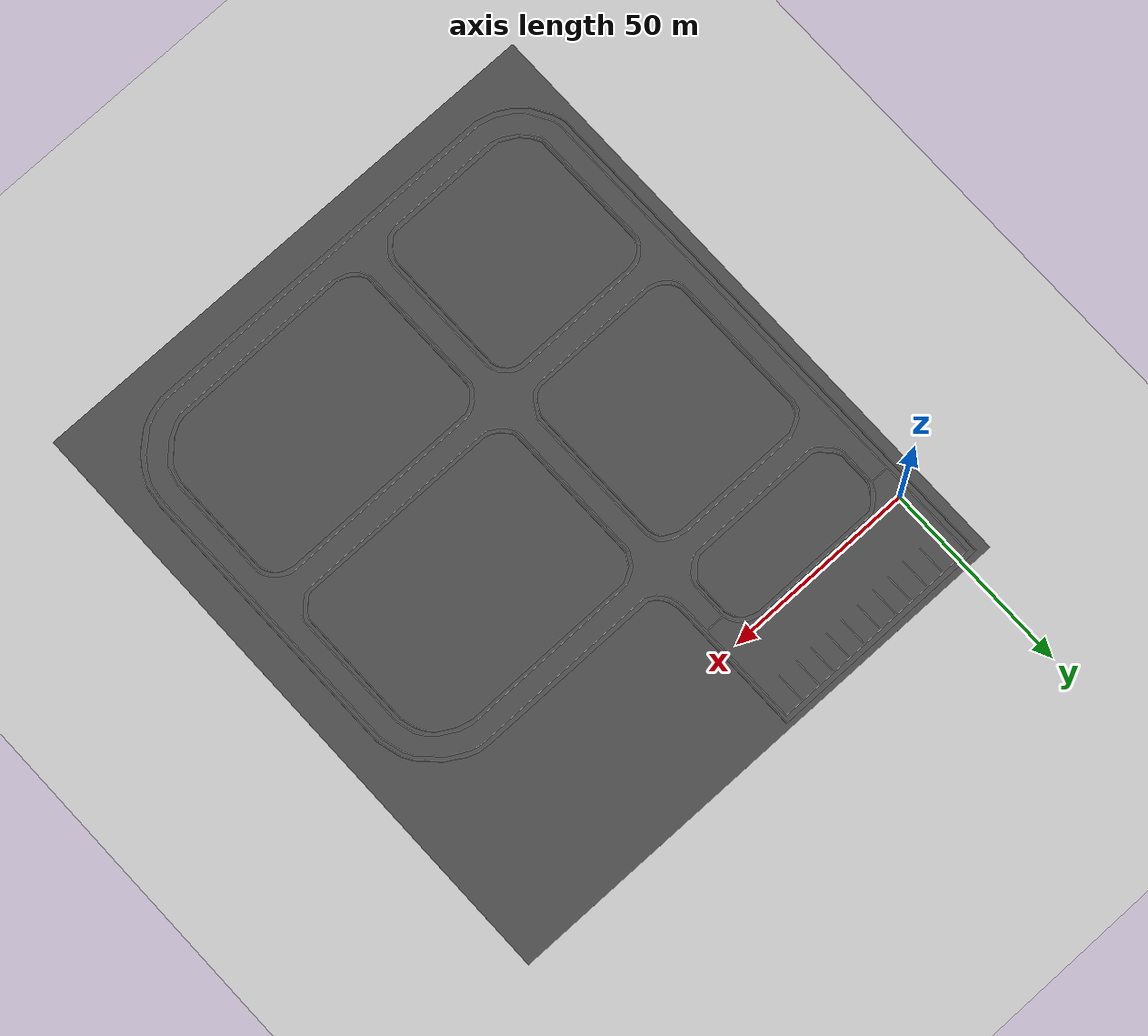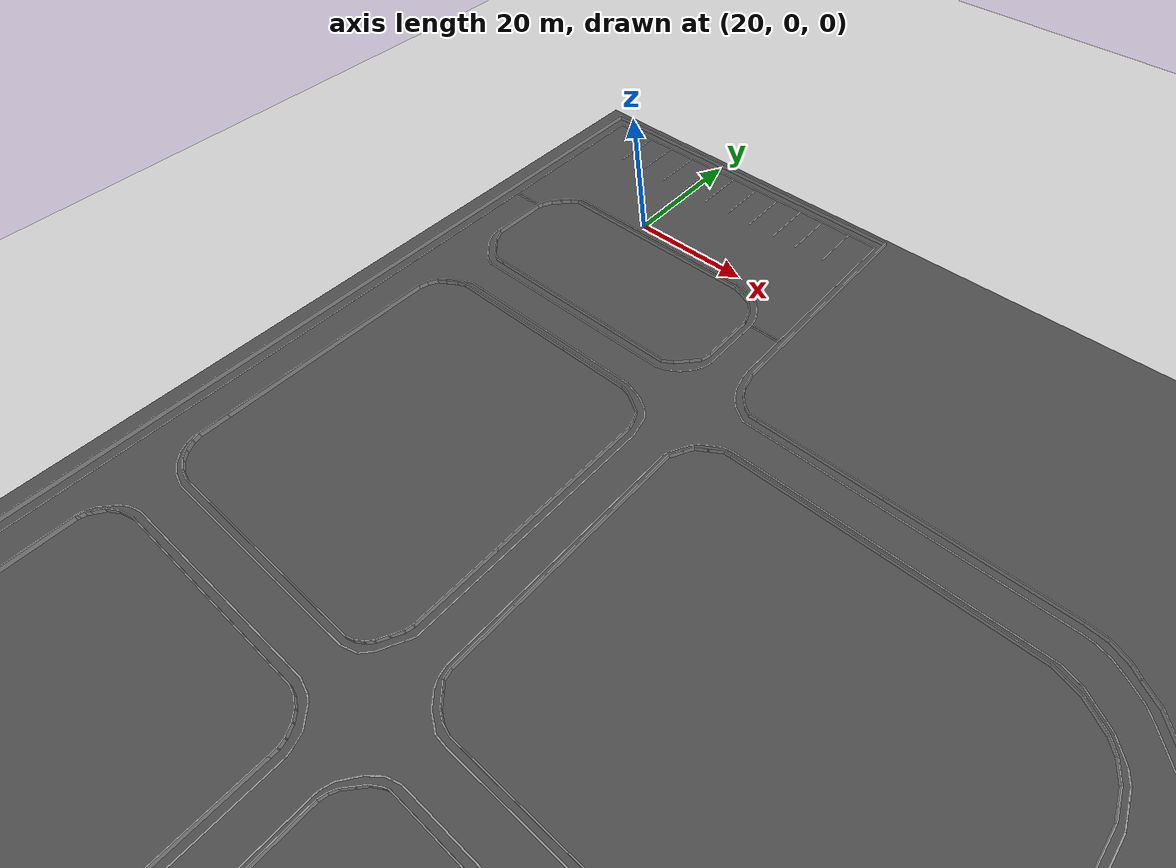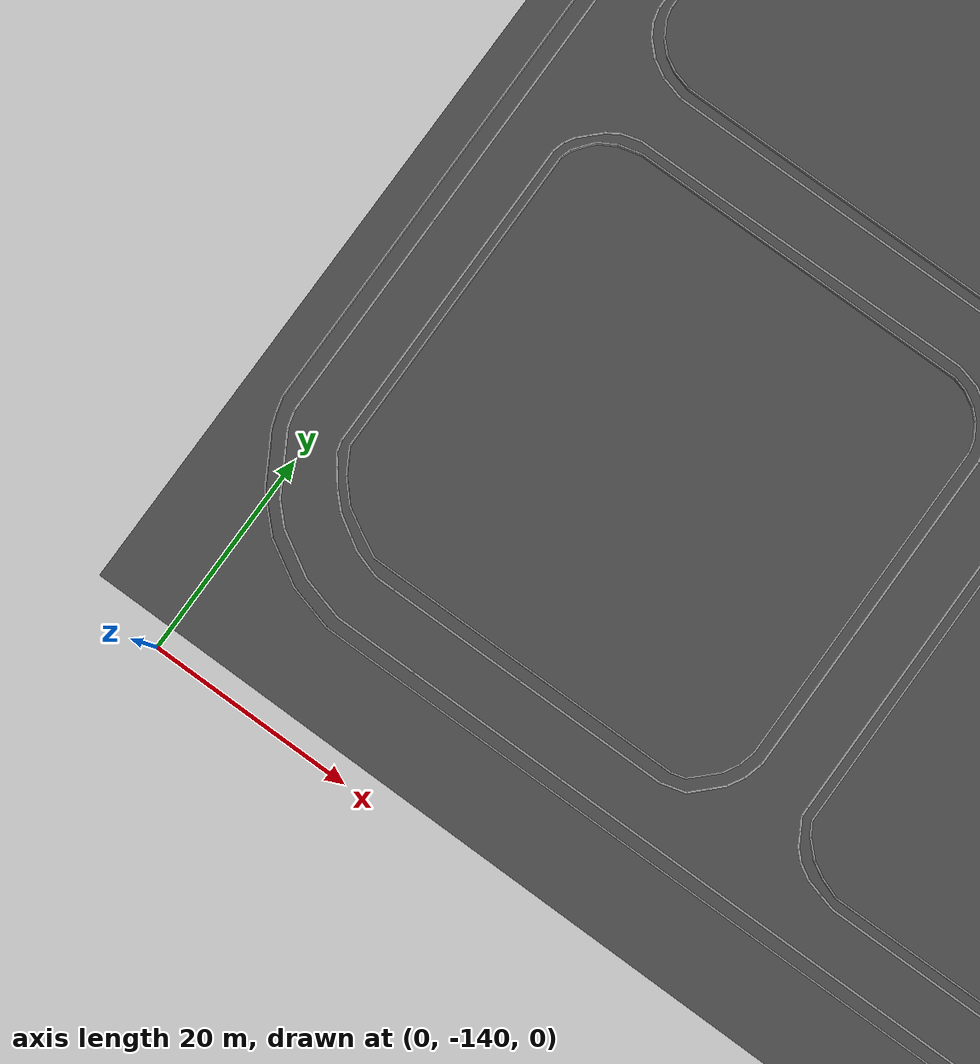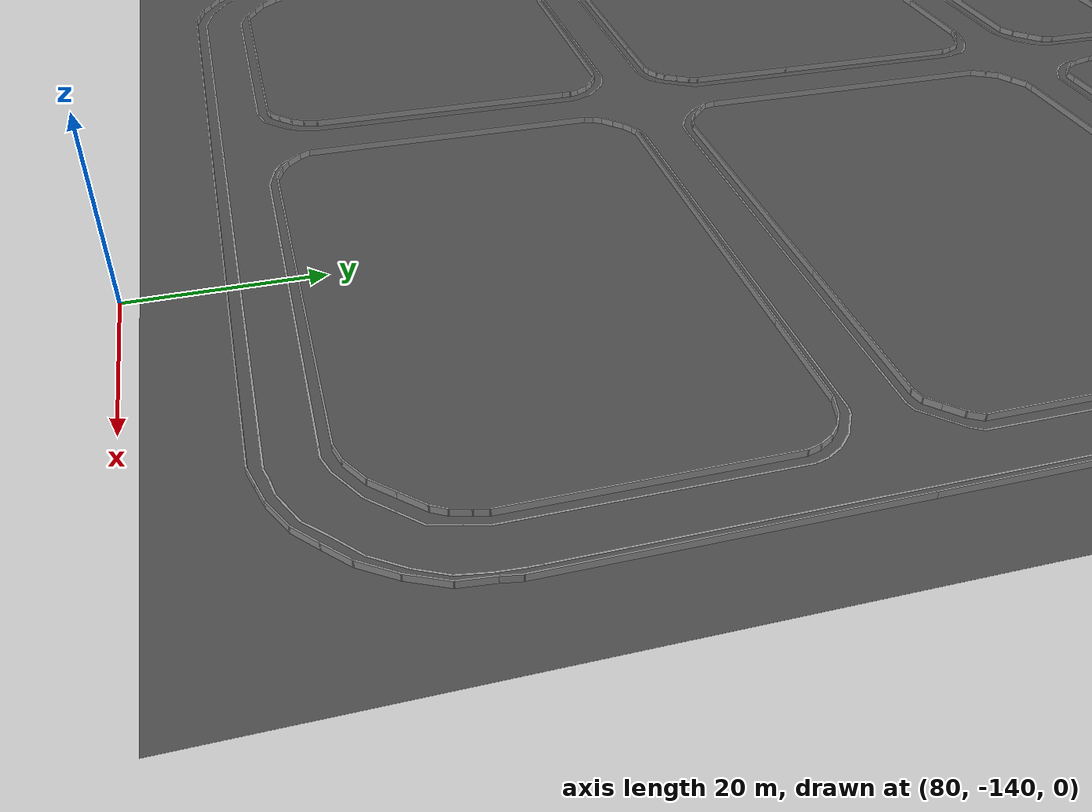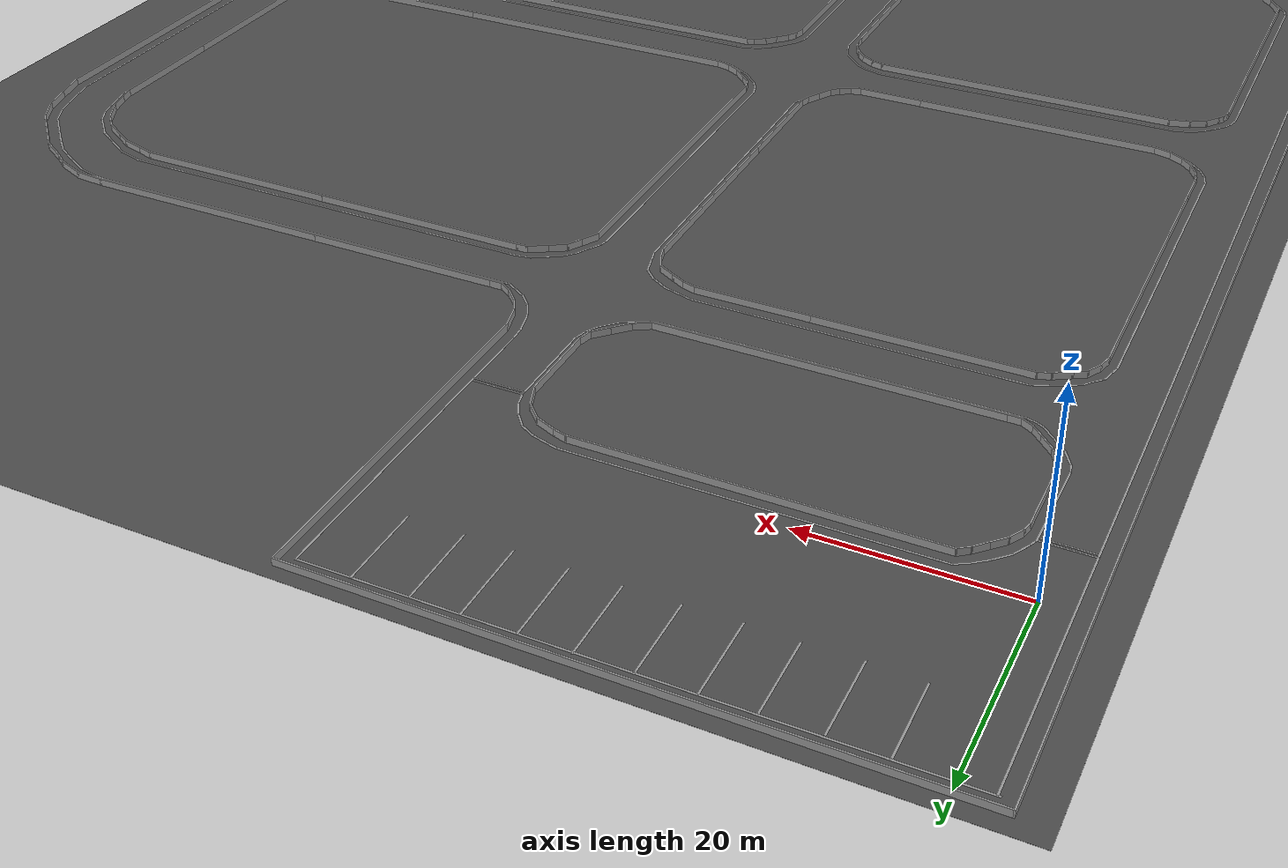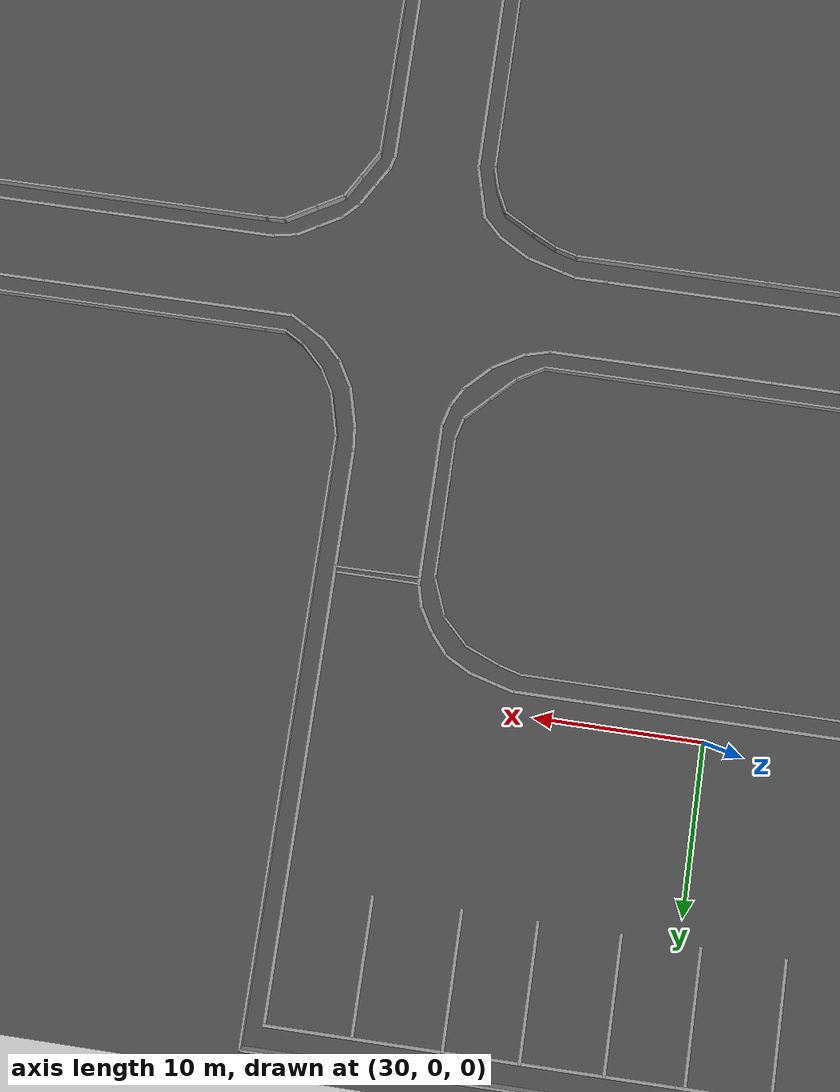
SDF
<sdf version="1.6">
 <world name="default">
  <light name="sun" type="directional">
   <pose>0 0 10 0 -0 0</pose>
   <diffuse>0.8 0.8 0.8 1</diffuse>
   <specular>0.2 0.2 0.2 1</specular>
   <attenuation>
    <range>1000</range>
    <constant>0.9</constant>
    <linear>0.01</linear>
    <quadratic>0.001</quadratic>
   </attenuation>
   <direction>-0.5 0.1 -0.9</direction>
  </light>
  <model name="ground_plane">
   <static>1</static>
   <link name="link">
    <collision name="collision">
     <geometry><plane><normal>0 0 1</normal><size>100 100</size></plane></geometry>
     <surface>
      <contact><collide_bitmask>65535</collide_bitmask></contact>
      <friction><ode><mu>100</mu><mu2>50</mu2></ode></friction>
     </surface>
    </collision>
    <visual name="visual">
     <cast_shadows>0</cast_shadows>
     <geometry><plane><normal>0 0 1</normal><size>100 100</size></plane></geometry>
     <material>
      <script><uri>file://media/materials/scripts/gazebo.material</uri><name>Gazebo/Grey</name></script>
     </material>
    </visual>
   </link>
  </model>
  <gravity>0 0 -9.8</gravity>
  <magnetic_field>6e-06 2.3e-05 -4.2e-05</magnetic_field>
  <atmosphere type="adiabatic"/>
  <physics name="default_physics" default="0" type="ode">
   <max_step_size>0.001</max_step_size>
   <real_time_factor>1</real_time_factor>
   <real_time_update_rate>1000</real_time_update_rate>
  </physics>
  <scene><ambient>0.4 0.4 0.4 1</ambient><background>0.7 0.7 0.7 1</background><shadows>1</shadows></scene>
  <spherical_coordinates>
   <surface_model>EARTH_WGS84</surface_model>
   <latitude_deg>0</latitude_deg>
   <longitude_deg>0</longitude_deg>
   <elevation>0</elevation>
   <heading_deg>0</heading_deg>
  </spherical_coordinates>
  <model name="asphalt_plane_geniş">
   <link name="link">
    <pose>4.51226 16.3967 0 0 -0 0</pose>
    <inertial>
     <mass>1</mass>
     <inertia><ixx>1</ixx><ixy>0</ixy><ixz>0</ixz><iyy>1</iyy><iyz>0</iyz><izz>1</izz></inertia>
    </inertial>
    <visual name="visual">
     <cast_shadows>0</cast_shadows>
     <geometry><box><size>160 140 0.015</size></box></geometry>
     <material>
      <script>
       <uri>model://asphalt_plane/materials/scripts</uri>
       <uri>model://asphalt_plane/materials/textures</uri>
       <name>vrc/asphalt</name>
      </script>
      <shader type="pixel"><normal_map>__default__</normal_map></shader>
      <ambient>0.5 0.5 0.5 1</ambient>
      <diffuse>0.5 0.5 0.5 1</diffuse>
      <specular>0.2 0.2 0.2 1</specular>
      <emissive>0 0 0 1</emissive>
     </material>
    </visual>
    <collision name="collision">
     <geometry><box><size>160 140 0.015</size></box></geometry>
     <surface>
      <friction>
       <ode><mu>1</mu><mu2>1</mu2><fdir1>0 0 0</fdir1><slip1>0</slip1><slip2>0</slip2></ode>
       <torsional>
        <coefficient>1</coefficient>
        <patch_radius>0</patch_radius>
        <surface_radius>0</surface_radius>
        <use_patch_radius>1</use_patch_radius>
        <ode><slip>0</slip></ode>
       </torsional>
      </friction>
      <bounce><restitution_coefficient>0</restitution_coefficient><threshold>1e+06</threshold></bounce>
      <contact>
       <collide_without_contact>0</collide_without_contact>
       <collide_without_contact_bitmask>1</collide_without_contact_bitmask>
       <collide_bitmask>1</collide_bitmask>
       <ode>
        <soft_cfm>0</soft_cfm>
        <soft_erp>0.2</soft_erp>
        <kp>1e+13</kp>
        <kd>1</kd>
        <max_vel>0.01</max_vel>
        <min_depth>0</min_depth>
       </ode>
       <bullet>
        <split_impulse>1</split_impulse>
        <split_impulse_penetration_threshold>-0.01</split_impulse_penetration_threshold>
        <soft_cfm>0</soft_cfm>
        <soft_erp>0.2</soft_erp>
        <kp>1e+13</kp>
        <kd>1</kd>
       </bullet>
      </contact>
     </surface>
    </collision>
   </link>
   <static>1</static>
   <pose>46.1176 -53.5445 0 0 0 -1.57416</pose>
  </model>
  <model name="GercekDuvarSeritKoyu1">
   <link name="Wall_10">
    <pose>69.6091 -59.7396 0 0 -0 0.785398</pose>
    <inertial>
     <mass>1</mass>
     <inertia><ixx>1</ixx><ixy>0</ixy><ixz>0</ixz><iyy>1</iyy><iyz>0</iyz><izz>1</izz></inertia>
    </inertial>
    <visual name="Wall_10_Visual">
     <pose>0 0 0.375 0 -0 0</pose>
     <geometry><box><size>2.5 0.15 0.75</size></box></geometry>
     <material>
      <script><uri>file://media/materials/scripts/gazebo.material</uri><name>Gazebo/Grey</name></script>
      <ambient>0.5 0.5 0.5 1</ambient>
      <shader type="pixel"><normal_map>__default__</normal_map></shader>
      <diffuse>0.7 0.7 0.7 1</diffuse>
      <specular>0.01 0.01 0.01 1</specular>
      <emissive>0 0 0 1</emissive>
     </material>
     <meta><layer>0</layer></meta>
    </visual>
    <collision name="Wall_10_Collision">
     <pose>0 0 0.375 0 -0 0</pose>
     <geometry><box><size>2.5 0.15 0.75</size></box></geometry>
     <surface>
      <friction>
       <ode><mu>1</mu><mu2>1</mu2><fdir1>0 0 0</fdir1><slip1>0</slip1><slip2>0</slip2></ode>
       <torsional>
        <coefficient>1</coefficient>
        <patch_radius>0</patch_radius>
        <surface_radius>0</surface_radius>
        <use_patch_radius>1</use_patch_radius>
        <ode><slip>0</slip></ode>
       </torsional>
      </friction>
      <bounce><restitution_coefficient>0</restitution_coefficient><threshold>1e+06</threshold></bounce>
      <contact>
       <collide_without_contact>0</collide_without_contact>
       <collide_without_contact_bitmask>1</collide_without_contact_bitmask>
       <collide_bitmask>1</collide_bitmask>
       <ode>
        <soft_cfm>0</soft_cfm>
        <soft_erp>0.2</soft_erp>
        <kp>1e+13</kp>
        <kd>1</kd>
        <max_vel>0.01</max_vel>
        <min_depth>0</min_depth>
       </ode>
       <bullet>
        <split_impulse>1</split_impulse>
        <split_impulse_penetration_threshold>-0.01</split_impulse_penetration_threshold>
        <soft_cfm>0</soft_cfm>
        <soft_erp>0.2</soft_erp>
        <kp>1e+13</kp>
        <kd>1</kd>
       </bullet>
      </contact>
     </surface>
    </collision>
   </link>
   <link name="Wall_101">
    <pose>18.8696 -38.2416 0 0 -0 1.56992</pose>
    <inertial>
     <mass>1</mass>
     <inertia><ixx>1</ixx><ixy>0</ixy><ixz>0</ixz><iyy>1</iyy><iyz>0</iyz><izz>1</izz></inertia>
    </inertial>
    <visual name="Wall_101_Visual">
     <pose>0 0 0.375 0 -0 0</pose>
     <geometry><box><size>26.5 0.15 0.75</size></box></geometry>
     <material>
      <script><uri>file://media/materials/scripts/gazebo.material</uri><name>Gazebo/Grey</name></script>
      <ambient>0.5 0.5 0.5 1</ambient>
      <shader type="pixel"><normal_map>__default__</normal_map></shader>
      <diffuse>0.7 0.7 0.7 1</diffuse>
      <specular>0.01 0.01 0.01 1</specular>
      <emissive>0 0 0 1</emissive>
     </material>
     <meta><layer>0</layer></meta>
    </visual>
    <collision name="Wall_101_Collision">
     <pose>0 0 0.375 0 -0 0</pose>
     <geometry><box><size>26.5 0.15 0.75</size></box></geometry>
     <surface>
      <friction>
       <ode><mu>1</mu><mu2>1</mu2><fdir1>0 0 0</fdir1><slip1>0</slip1><slip2>0</slip2></ode>
       <torsional>
        <coefficient>1</coefficient>
        <patch_radius>0</patch_radius>
        <surface_radius>0</surface_radius>
        <use_patch_radius>1</use_patch_radius>
        <ode><slip>0</slip></ode>
       </torsional>
      </friction>
      <bounce><restitution_coefficient>0</restitution_coefficient><threshold>1e+06</threshold></bounce>
      <contact>
       <collide_without_contact>0</collide_without_contact>
       <collide_without_contact_bitmask>1</collide_without_contact_bitmask>
       <collide_bitmask>1</collide_bitmask>
       <ode>
        <soft_cfm>0</soft_cfm>
        <soft_erp>0.2</soft_erp>
        <kp>1e+13</kp>
        <kd>1</kd>
        <max_vel>0.01</max_vel>
        <min_depth>0</min_depth>
       </ode>
       <bullet>
        <split_impulse>1</split_impulse>
        <split_impulse_penetration_threshold>-0.01</split_impulse_penetration_threshold>
        <soft_cfm>0</soft_cfm>
        <soft_erp>0.2</soft_erp>
        <kp>1e+13</kp>
        <kd>1</kd>
       </bullet>
      </contact>
     </surface>
    </collision>
   </link>
   <link name="Wall_103">
    <pose>18.8811 -21.5166 0 0 -0 1.5708</pose>
    <inertial>
     <mass>1</mass>
     <inertia><ixx>1</ixx><ixy>0</ixy><ixz>0</ixz><iyy>1</iyy><iyz>0</iyz><izz>1</izz></inertia>
    </inertial>
    <visual name="Wall_103_Visual">
     <pose>0 0 0.375 0 -0 0</pose>
     <geometry><box><size>7.25 0.15 0.75</size></box></geometry>
     <material>
      <script><uri>file://media/materials/scripts/gazebo.material</uri><name>Gazebo/Grey</name></script>
      <ambient>0.5 0.5 0.5 1</ambient>
      <shader type="pixel"><normal_map>__default__</normal_map></shader>
      <diffuse>0.7 0.7 0.7 1</diffuse>
      <specular>0.01 0.01 0.01 1</specular>
      <emissive>0 0 0 1</emissive>
     </material>
     <meta><layer>0</layer></meta>
    </visual>
    <collision name="Wall_103_Collision">
     <pose>0 0 0.375 0 -0 0</pose>
     <geometry><box><size>7.25 0.15 0.75</size></box></geometry>
     <surface>
      <friction>
       <ode><mu>1</mu><mu2>1</mu2><fdir1>0 0 0</fdir1><slip1>0</slip1><slip2>0</slip2></ode>
       <torsional>
        <coefficient>1</coefficient>
        <patch_radius>0</patch_radius>
        <surface_radius>0</surface_radius>
        <use_patch_radius>1</use_patch_radius>
        <ode><slip>0</slip></ode>
       </torsional>
      </friction>
      <bounce><restitution_coefficient>0</restitution_coefficient><threshold>1e+06</threshold></bounce>
      <contact>
       <collide_without_contact>0</collide_without_contact>
       <collide_without_contact_bitmask>1</collide_without_contact_bitmask>
       <collide_bitmask>1</collide_bitmask>
       <ode>
        <soft_cfm>0</soft_cfm>
        <soft_erp>0.2</soft_erp>
        <kp>1e+13</kp>
        <kd>1</kd>
        <max_vel>0.01</max_vel>
        <min_depth>0</min_depth>
       </ode>
       <bullet>
        <split_impulse>1</split_impulse>
        <split_impulse_penetration_threshold>-0.01</split_impulse_penetration_threshold>
        <soft_cfm>0</soft_cfm>
        <soft_erp>0.2</soft_erp>
        <kp>1e+13</kp>
        <kd>1</kd>
       </bullet>
      </contact>
     </surface>
    </collision>
   </link>
   <link name="Wall_1032">
    <pose>-69.9829 -12.0716 0 0 -0 0</pose>
    <visual name="Wall_1032_Visual">
     <pose>0 0 0.005 0 -0 0</pose>
     <geometry><box><size>8 0.2 0.01</size></box></geometry>
     <material>
      <script><uri>file://media/materials/scripts/gazebo.material</uri><name>Gazebo/Grey</name></script>
      <ambient>1 1 1 1</ambient>
      <shader type="pixel"/>
     </material>
     <meta><layer>0</layer></meta>
    </visual>
    <collision name="Wall_1032_Collision">
     <pose>0 0 0.005 0 -0 0</pose>
     <geometry><box><size>8 0.2 0.01</size></box></geometry>
     <surface>
      <friction>
       <ode><mu>1</mu><mu2>1</mu2><fdir1>0 0 0</fdir1><slip1>0</slip1><slip2>0</slip2></ode>
       <torsional>
        <coefficient>1</coefficient>
        <patch_radius>0</patch_radius>
        <surface_radius>0</surface_radius>
        <use_patch_radius>1</use_patch_radius>
        <ode><slip>0</slip></ode>
       </torsional>
      </friction>
      <bounce><restitution_coefficient>0</restitution_coefficient><threshold>1e+06</threshold></bounce>
      <contact>
       <collide_without_contact>0</collide_without_contact>
       <collide_without_contact_bitmask>1</collide_without_contact_bitmask>
       <collide_bitmask>1</collide_bitmask>
       <ode>
        <soft_cfm>0</soft_cfm>
        <soft_erp>0.2</soft_erp>
        <kp>1e+13</kp>
        <kd>1</kd>
        <max_vel>0.01</max_vel>
        <min_depth>0</min_depth>
       </ode>
       <bullet>
        <split_impulse>1</split_impulse>
        <split_impulse_penetration_threshold>-0.01</split_impulse_penetration_threshold>
        <soft_cfm>0</soft_cfm>
        <soft_erp>0.2</soft_erp>
        <kp>1e+13</kp>
        <kd>1</kd>
       </bullet>
      </contact>
     </surface>
    </collision>
   </link>
   <link name="Wall_1034">
    <pose>-69.9829 -17.2566 0 0 -0 0</pose>
    <visual name="Wall_1034_Visual">
     <pose>0 0 0.005 0 -0 0</pose>
     <geometry><box><size>8 0.2 0.01</size></box></geometry>
     <material>
      <script><uri>file://media/materials/scripts/gazebo.material</uri><name>Gazebo/Grey</name></script>
      <ambient>1 1 1 1</ambient>
      <shader type="pixel"/>
     </material>
     <meta><layer>0</layer></meta>
    </visual>
    <collision name="Wall_1034_Collision">
     <pose>0 0 0.005 0 -0 0</pose>
     <geometry><box><size>8 0.2 0.01</size></box></geometry>
     <surface>
      <friction>
       <ode><mu>1</mu><mu2>1</mu2><fdir1>0 0 0</fdir1><slip1>0</slip1><slip2>0</slip2></ode>
       <torsional>
        <coefficient>1</coefficient>
        <patch_radius>0</patch_radius>
        <surface_radius>0</surface_radius>
        <use_patch_radius>1</use_patch_radius>
        <ode><slip>0</slip></ode>
       </torsional>
      </friction>
      <bounce><restitution_coefficient>0</restitution_coefficient><threshold>1e+06</threshold></bounce>
      <contact>
       <collide_without_contact>0</collide_without_contact>
       <collide_without_contact_bitmask>1</collide_without_contact_bitmask>
       <collide_bitmask>1</collide_bitmask>
       <ode>
        <soft_cfm>0</soft_cfm>
        <soft_erp>0.2</soft_erp>
        <kp>1e+13</kp>
        <kd>1</kd>
        <max_vel>0.01</max_vel>
        <min_depth>0</min_depth>
       </ode>
       <bullet>
        <split_impulse>1</split_impulse>
        <split_impulse_penetration_threshold>-0.01</split_impulse_penetration_threshold>
        <soft_cfm>0</soft_cfm>
        <soft_erp>0.2</soft_erp>
        <kp>1e+13</kp>
        <kd>1</kd>
       </bullet>
      </contact>
     </surface>
    </collision>
   </link>
   <link name="Wall_1036">
    <pose>-70.0286 -21.668 0 0 -0 0</pose>
    <visual name="Wall_1036_Visual">
     <pose>0 0 0.005 0 -0 0</pose>
     <geometry><box><size>8 0.2 0.01</size></box></geometry>
     <material>
      <script><uri>file://media/materials/scripts/gazebo.material</uri><name>Gazebo/Grey</name></script>
      <ambient>1 1 1 1</ambient>
      <shader type="pixel"/>
     </material>
     <meta><layer>0</layer></meta>
    </visual>
    <collision name="Wall_1036_Collision">
     <pose>0 0 0.005 0 -0 0</pose>
     <geometry><box><size>8 0.2 0.01</size></box></geometry>
     <surface>
      <friction>
       <ode><mu>1</mu><mu2>1</mu2><fdir1>0 0 0</fdir1><slip1>0</slip1><slip2>0</slip2></ode>
       <torsional>
        <coefficient>1</coefficient>
        <patch_radius>0</patch_radius>
        <surface_radius>0</surface_radius>
        <use_patch_radius>1</use_patch_radius>
        <ode><slip>0</slip></ode>
       </torsional>
      </friction>
      <bounce><restitution_coefficient>0</restitution_coefficient><threshold>1e+06</threshold></bounce>
      <contact>
       <collide_without_contact>0</collide_without_contact>
       <collide_without_contact_bitmask>1</collide_without_contact_bitmask>
       <collide_bitmask>1</collide_bitmask>
       <ode>
        <soft_cfm>0</soft_cfm>
        <soft_erp>0.2</soft_erp>
        <kp>1e+13</kp>
        <kd>1</kd>
        <max_vel>0.01</max_vel>
        <min_depth>0</min_depth>
       </ode>
       <bullet>
        <split_impulse>1</split_impulse>
        <split_impulse_penetration_threshold>-0.01</split_impulse_penetration_threshold>
        <soft_cfm>0</soft_cfm>
        <soft_erp>0.2</soft_erp>
        <kp>1e+13</kp>
        <kd>1</kd>
       </bullet>
      </contact>
     </surface>
    </collision>
   </link>
   <link name="Wall_1038">
    <pose>-70.0286 -26.4891 0 0 -0 0</pose>
    <visual name="Wall_1038_Visual">
     <pose>0 0 0.005 0 -0 0</pose>
     <geometry><box><size>8 0.2 0.01</size></box></geometry>
     <material>
      <script><uri>file://media/materials/scripts/gazebo.material</uri><name>Gazebo/Grey</name></script>
      <ambient>1 1 1 1</ambient>
      <shader type="pixel"/>
     </material>
     <meta><layer>0</layer></meta>
    </visual>
    <collision name="Wall_1038_Collision">
     <pose>0 0 0.005 0 -0 0</pose>
     <geometry><box><size>8 0.2 0.01</size></box></geometry>
     <surface>
      <friction>
       <ode><mu>1</mu><mu2>1</mu2><fdir1>0 0 0</fdir1><slip1>0</slip1><slip2>0</slip2></ode>
       <torsional>
        <coefficient>1</coefficient>
        <patch_radius>0</patch_radius>
        <surface_radius>0</surface_radius>
        <use_patch_radius>1</use_patch_radius>
        <ode><slip>0</slip></ode>
       </torsional>
      </friction>
      <bounce><restitution_coefficient>0</restitution_coefficient><threshold>1e+06</threshold></bounce>
      <contact>
       <collide_without_contact>0</collide_without_contact>
       <collide_without_contact_bitmask>1</collide_without_contact_bitmask>
       <collide_bitmask>1</collide_bitmask>
       <ode>
        <soft_cfm>0</soft_cfm>
        <soft_erp>0.2</soft_erp>
        <kp>1e+13</kp>
        <kd>1</kd>
        <max_vel>0.01</max_vel>
        <min_depth>0</min_depth>
       </ode>
       <bullet>
        <split_impulse>1</split_impulse>
        <split_impulse_penetration_threshold>-0.01</split_impulse_penetration_threshold>
        <soft_cfm>0</soft_cfm>
        <soft_erp>0.2</soft_erp>
        <kp>1e+13</kp>
        <kd>1</kd>
       </bullet>
      </contact>
     </surface>
    </collision>
   </link>
   <link name="Wall_1040">
    <pose>-70.1196 -31.0827 0 0 -0 0</pose>
    <visual name="Wall_1040_Visual">
     <pose>0 0 0.005 0 -0 0</pose>
     <geometry><box><size>8 0.2 0.01</size></box></geometry>
     <material>
      <script><uri>file://media/materials/scripts/gazebo.material</uri><name>Gazebo/Grey</name></script>
      <ambient>1 1 1 1</ambient>
      <shader type="pixel"/>
     </material>
     <meta><layer>0</layer></meta>
    </visual>
    <collision name="Wall_1040_Collision">
     <pose>0 0 0.005 0 -0 0</pose>
     <geometry><box><size>8 0.2 0.01</size></box></geometry>
     <surface>
      <friction>
       <ode><mu>1</mu><mu2>1</mu2><fdir1>0 0 0</fdir1><slip1>0</slip1><slip2>0</slip2></ode>
       <torsional>
        <coefficient>1</coefficient>
        <patch_radius>0</patch_radius>
        <surface_radius>0</surface_radius>
        <use_patch_radius>1</use_patch_radius>
        <ode><slip>0</slip></ode>
       </torsional>
      </friction>
      <bounce><restitution_coefficient>0</restitution_coefficient><threshold>1e+06</threshold></bounce>
      <contact>
       <collide_without_contact>0</collide_without_contact>
       <collide_without_contact_bitmask>1</collide_without_contact_bitmask>
       <collide_bitmask>1</collide_bitmask>
       <ode>
        <soft_cfm>0</soft_cfm>
        <soft_erp>0.2</soft_erp>
        <kp>1e+13</kp>
        <kd>1</kd>
        <max_vel>0.01</max_vel>
        <min_depth>0</min_depth>
       </ode>
       <bullet>
        <split_impulse>1</split_impulse>
        <split_impulse_penetration_threshold>-0.01</split_impulse_penetration_threshold>
        <soft_cfm>0</soft_cfm>
        <soft_erp>0.2</soft_erp>
        <kp>1e+13</kp>
        <kd>1</kd>
       </bullet>
      </contact>
     </surface>
    </collision>
   </link>
   <link name="Wall_1042">
    <pose>-70.0741 -35.9948 0 0 -0 0</pose>
    <visual name="Wall_1042_Visual">
     <pose>0 0 0.005 0 -0 0</pose>
     <geometry><box><size>8 0.2 0.01</size></box></geometry>
     <material>
      <script><uri>file://media/materials/scripts/gazebo.material</uri><name>Gazebo/Grey</name></script>
      <ambient>1 1 1 1</ambient>
      <shader type="pixel"/>
     </material>
     <meta><layer>0</layer></meta>
    </visual>
    <collision name="Wall_1042_Collision">
     <pose>0 0 0.005 0 -0 0</pose>
     <geometry><box><size>8 0.2 0.01</size></box></geometry>
     <surface>
      <friction>
       <ode><mu>1</mu><mu2>1</mu2><fdir1>0 0 0</fdir1><slip1>0</slip1><slip2>0</slip2></ode>
       <torsional>
        <coefficient>1</coefficient>
        <patch_radius>0</patch_radius>
        <surface_radius>0</surface_radius>
        <use_patch_radius>1</use_patch_radius>
        <ode><slip>0</slip></ode>
       </torsional>
      </friction>
      <bounce><restitution_coefficient>0</restitution_coefficient><threshold>1e+06</threshold></bounce>
      <contact>
       <collide_without_contact>0</collide_without_contact>
       <collide_without_contact_bitmask>1</collide_without_contact_bitmask>
       <collide_bitmask>1</collide_bitmask>
       <ode>
        <soft_cfm>0</soft_cfm>
        <soft_erp>0.2</soft_erp>
        <kp>1e+13</kp>
        <kd>1</kd>
        <max_vel>0.01</max_vel>
        <min_depth>0</min_depth>
       </ode>
       <bullet>
        <split_impulse>1</split_impulse>
        <split_impulse_penetration_threshold>-0.01</split_impulse_penetration_threshold>
        <soft_cfm>0</soft_cfm>
        <soft_erp>0.2</soft_erp>
        <kp>1e+13</kp>
        <kd>1</kd>
       </bullet>
      </contact>
     </surface>
    </collision>
   </link>
   <link name="Wall_1044">
    <pose>-69.9386 -40.9523 0 0 -0 0</pose>
    <visual name="Wall_1044_Visual">
     <pose>0 0 0.005 0 -0 0</pose>
     <geometry><box><size>8 0.2 0.01</size></box></geometry>
     <material>
      <script><uri>file://media/materials/scripts/gazebo.material</uri><name>Gazebo/Grey</name></script>
      <ambient>1 1 1 1</ambient>
      <shader type="pixel"/>
     </material>
     <meta><layer>0</layer></meta>
    </visual>
    <collision name="Wall_1044_Collision">
     <pose>0 0 0.005 0 -0 0</pose>
     <geometry><box><size>8 0.2 0.01</size></box></geometry>
     <surface>
      <friction>
       <ode><mu>1</mu><mu2>1</mu2><fdir1>0 0 0</fdir1><slip1>0</slip1><slip2>0</slip2></ode>
       <torsional>
        <coefficient>1</coefficient>
        <patch_radius>0</patch_radius>
        <surface_radius>0</surface_radius>
        <use_patch_radius>1</use_patch_radius>
        <ode><slip>0</slip></ode>
       </torsional>
      </friction>
      <bounce><restitution_coefficient>0</restitution_coefficient><threshold>1e+06</threshold></bounce>
      <contact>
       <collide_without_contact>0</collide_without_contact>
       <collide_without_contact_bitmask>1</collide_without_contact_bitmask>
       <collide_bitmask>1</collide_bitmask>
       <ode>
        <soft_cfm>0</soft_cfm>
        <soft_erp>0.2</soft_erp>
        <kp>1e+13</kp>
        <kd>1</kd>
        <max_vel>0.01</max_vel>
        <min_depth>0</min_depth>
       </ode>
       <bullet>
        <split_impulse>1</split_impulse>
        <split_impulse_penetration_threshold>-0.01</split_impulse_penetration_threshold>
        <soft_cfm>0</soft_cfm>
        <soft_erp>0.2</soft_erp>
        <kp>1e+13</kp>
        <kd>1</kd>
       </bullet>
      </contact>
     </surface>
    </collision>
   </link>
   <link name="Wall_1046">
    <pose>-70.0548 -45.495 0 0 -0 0</pose>
    <visual name="Wall_1046_Visual">
     <pose>0 0 0.005 0 -0 0</pose>
     <geometry><box><size>8 0.2 0.01</size></box></geometry>
     <material>
      <script><uri>file://media/materials/scripts/gazebo.material</uri><name>Gazebo/Grey</name></script>
      <ambient>1 1 1 1</ambient>
      <shader type="pixel"/>
     </material>
     <meta><layer>0</layer></meta>
    </visual>
    <collision name="Wall_1046_Collision">
     <pose>0 0 0.005 0 -0 0</pose>
     <geometry><box><size>8 0.2 0.01</size></box></geometry>
     <surface>
      <friction>
       <ode><mu>1</mu><mu2>1</mu2><fdir1>0 0 0</fdir1><slip1>0</slip1><slip2>0</slip2></ode>
       <torsional>
        <coefficient>1</coefficient>
        <patch_radius>0</patch_radius>
        <surface_radius>0</surface_radius>
        <use_patch_radius>1</use_patch_radius>
        <ode><slip>0</slip></ode>
       </torsional>
      </friction>
      <bounce><restitution_coefficient>0</restitution_coefficient><threshold>1e+06</threshold></bounce>
      <contact>
       <collide_without_contact>0</collide_without_contact>
       <collide_without_contact_bitmask>1</collide_without_contact_bitmask>
       <collide_bitmask>1</collide_bitmask>
       <ode>
        <soft_cfm>0</soft_cfm>
        <soft_erp>0.2</soft_erp>
        <kp>1e+13</kp>
        <kd>1</kd>
        <max_vel>0.01</max_vel>
        <min_depth>0</min_depth>
       </ode>
       <bullet>
        <split_impulse>1</split_impulse>
        <split_impulse_penetration_threshold>-0.01</split_impulse_penetration_threshold>
        <soft_cfm>0</soft_cfm>
        <soft_erp>0.2</soft_erp>
        <kp>1e+13</kp>
        <kd>1</kd>
       </bullet>
      </contact>
     </surface>
    </collision>
   </link>
   <link name="Wall_1048">
    <pose>-69.8093 -50.4126 0 0 -0 0</pose>
    <visual name="Wall_1048_Visual">
     <pose>0 0 0.005 0 -0 0</pose>
     <geometry><box><size>8 0.2 0.01</size></box></geometry>
     <material>
      <script><uri>file://media/materials/scripts/gazebo.material</uri><name>Gazebo/Grey</name></script>
      <ambient>1 1 1 1</ambient>
      <shader type="pixel"/>
     </material>
     <meta><layer>0</layer></meta>
    </visual>
    <collision name="Wall_1048_Collision">
     <pose>0 0 0.005 0 -0 0</pose>
     <geometry><box><size>8 0.2 0.01</size></box></geometry>
     <surface>
      <friction>
       <ode><mu>1</mu><mu2>1</mu2><fdir1>0 0 0</fdir1><slip1>0</slip1><slip2>0</slip2></ode>
       <torsional>
        <coefficient>1</coefficient>
        <patch_radius>0</patch_radius>
        <surface_radius>0</surface_radius>
        <use_patch_radius>1</use_patch_radius>
        <ode><slip>0</slip></ode>
       </torsional>
      </friction>
      <bounce><restitution_coefficient>0</restitution_coefficient><threshold>1e+06</threshold></bounce>
      <contact>
       <collide_without_contact>0</collide_without_contact>
       <collide_without_contact_bitmask>1</collide_without_contact_bitmask>
       <collide_bitmask>1</collide_bitmask>
       <ode>
        <soft_cfm>0</soft_cfm>
        <soft_erp>0.2</soft_erp>
        <kp>1e+13</kp>
        <kd>1</kd>
        <max_vel>0.01</max_vel>
        <min_depth>0</min_depth>
       </ode>
       <bullet>
        <split_impulse>1</split_impulse>
        <split_impulse_penetration_threshold>-0.01</split_impulse_penetration_threshold>
        <soft_cfm>0</soft_cfm>
        <soft_erp>0.2</soft_erp>
        <kp>1e+13</kp>
        <kd>1</kd>
       </bullet>
      </contact>
     </surface>
    </collision>
   </link>
   <link name="Wall_105">
    <pose>18.7386 -17.4356 0 0 -0 1.83298</pose>
    <inertial>
     <mass>1</mass>
     <inertia><ixx>1</ixx><ixy>0</ixy><ixz>0</ixz><iyy>1</iyy><iyz>0</iyz><izz>1</izz></inertia>
    </inertial>
    <visual name="Wall_105_Visual">
     <pose>0 0 0.375 0 -0 0</pose>
     <geometry><box><size>1.25 0.15 0.75</size></box></geometry>
     <material>
      <script><uri>file://media/materials/scripts/gazebo.material</uri><name>Gazebo/Grey</name></script>
      <ambient>0.5 0.5 0.5 1</ambient>
      <shader type="pixel"><normal_map>__default__</normal_map></shader>
      <diffuse>0.7 0.7 0.7 1</diffuse>
      <specular>0.01 0.01 0.01 1</specular>
      <emissive>0 0 0 1</emissive>
     </material>
     <meta><layer>0</layer></meta>
    </visual>
    <collision name="Wall_105_Collision">
     <pose>0 0 0.375 0 -0 0</pose>
     <geometry><box><size>1.25 0.15 0.75</size></box></geometry>
     <surface>
      <friction>
       <ode><mu>1</mu><mu2>1</mu2><fdir1>0 0 0</fdir1><slip1>0</slip1><slip2>0</slip2></ode>
       <torsional>
        <coefficient>1</coefficient>
        <patch_radius>0</patch_radius>
        <surface_radius>0</surface_radius>
        <use_patch_radius>1</use_patch_radius>
        <ode><slip>0</slip></ode>
       </torsional>
      </friction>
      <bounce><restitution_coefficient>0</restitution_coefficient><threshold>1e+06</threshold></bounce>
      <contact>
       <collide_without_contact>0</collide_without_contact>
       <collide_without_contact_bitmask>1</collide_without_contact_bitmask>
       <collide_bitmask>1</collide_bitmask>
       <ode>
        <soft_cfm>0</soft_cfm>
        <soft_erp>0.2</soft_erp>
        <kp>1e+13</kp>
        <kd>1</kd>
        <max_vel>0.01</max_vel>
        <min_depth>0</min_depth>
       </ode>
       <bullet>
        <split_impulse>1</split_impulse>
        <split_impulse_penetration_threshold>-0.01</split_impulse_penetration_threshold>
        <soft_cfm>0</soft_cfm>
        <soft_erp>0.2</soft_erp>
        <kp>1e+13</kp>
        <kd>1</kd>
       </bullet>
      </contact>
     </surface>
    </collision>
   </link>
   <link name="Wall_1050">
    <pose>-70.0479 -55.2375 0 0 -0 2e-05</pose>
    <visual name="Wall_1050_Visual">
     <pose>0 0 0.005 0 -0 0</pose>
     <geometry><box><size>8 0.2 0.01</size></box></geometry>
     <material>
      <script><uri>file://media/materials/scripts/gazebo.material</uri><name>Gazebo/Grey</name></script>
      <ambient>1 1 1 1</ambient>
      <shader type="pixel"/>
     </material>
     <meta><layer>0</layer></meta>
    </visual>
    <collision name="Wall_1050_Collision">
     <pose>0 0 0.005 0 -0 0</pose>
     <geometry><box><size>8 0.2 0.01</size></box></geometry>
     <surface>
      <friction>
       <ode><mu>1</mu><mu2>1</mu2><fdir1>0 0 0</fdir1><slip1>0</slip1><slip2>0</slip2></ode>
       <torsional>
        <coefficient>1</coefficient>
        <patch_radius>0</patch_radius>
        <surface_radius>0</surface_radius>
        <use_patch_radius>1</use_patch_radius>
        <ode><slip>0</slip></ode>
       </torsional>
      </friction>
      <bounce><restitution_coefficient>0</restitution_coefficient><threshold>1e+06</threshold></bounce>
      <contact>
       <collide_without_contact>0</collide_without_contact>
       <collide_without_contact_bitmask>1</collide_without_contact_bitmask>
       <collide_bitmask>1</collide_bitmask>
       <ode>
        <soft_cfm>0</soft_cfm>
        <soft_erp>0.2</soft_erp>
        <kp>1e+13</kp>
        <kd>1</kd>
        <max_vel>0.01</max_vel>
        <min_depth>0</min_depth>
       </ode>
       <bullet>
        <split_impulse>1</split_impulse>
        <split_impulse_penetration_threshold>-0.01</split_impulse_penetration_threshold>
        <soft_cfm>0</soft_cfm>
        <soft_erp>0.2</soft_erp>
        <kp>1e+13</kp>
        <kd>1</kd>
       </bullet>
      </contact>
     </surface>
    </collision>
   </link>
   <link name="Wall_106">
    <pose>18.2586 -16.3201 0 0 -0 2.09444</pose>
    <inertial>
     <mass>1</mass>
     <inertia><ixx>1</ixx><ixy>0</ixy><ixz>0</ixz><iyy>1</iyy><iyz>0</iyz><izz>1</izz></inertia>
    </inertial>
    <visual name="Wall_106_Visual">
     <pose>0 0 0.375 0 -0 0</pose>
     <geometry><box><size>1.5 0.15 0.75</size></box></geometry>
     <material>
      <script><uri>file://media/materials/scripts/gazebo.material</uri><name>Gazebo/Grey</name></script>
      <ambient>0.5 0.5 0.5 1</ambient>
      <shader type="pixel"><normal_map>__default__</normal_map></shader>
      <diffuse>0.7 0.7 0.7 1</diffuse>
      <specular>0.01 0.01 0.01 1</specular>
      <emissive>0 0 0 1</emissive>
     </material>
     <meta><layer>0</layer></meta>
    </visual>
    <collision name="Wall_106_Collision">
     <pose>0 0 0.375 0 -0 0</pose>
     <geometry><box><size>1.5 0.15 0.75</size></box></geometry>
     <surface>
      <friction>
       <ode><mu>1</mu><mu2>1</mu2><fdir1>0 0 0</fdir1><slip1>0</slip1><slip2>0</slip2></ode>
       <torsional>
        <coefficient>1</coefficient>
        <patch_radius>0</patch_radius>
        <surface_radius>0</surface_radius>
        <use_patch_radius>1</use_patch_radius>
        <ode><slip>0</slip></ode>
       </torsional>
      </friction>
      <bounce><restitution_coefficient>0</restitution_coefficient><threshold>1e+06</threshold></bounce>
      <contact>
       <collide_without_contact>0</collide_without_contact>
       <collide_without_contact_bitmask>1</collide_without_contact_bitmask>
       <collide_bitmask>1</collide_bitmask>
       <ode>
        <soft_cfm>0</soft_cfm>
        <soft_erp>0.2</soft_erp>
        <kp>1e+13</kp>
        <kd>1</kd>
        <max_vel>0.01</max_vel>
        <min_depth>0</min_depth>
       </ode>
       <bullet>
        <split_impulse>1</split_impulse>
        <split_impulse_penetration_threshold>-0.01</split_impulse_penetration_threshold>
        <soft_cfm>0</soft_cfm>
        <soft_erp>0.2</soft_erp>
        <kp>1e+13</kp>
        <kd>1</kd>
       </bullet>
      </contact>
     </surface>
    </collision>
   </link>
   <link name="Wall_107">
    <pose>17.5321 -15.3466 0 0 -0 2.35619</pose>
    <inertial>
     <mass>1</mass>
     <inertia><ixx>1</ixx><ixy>0</ixy><ixz>0</ixz><iyy>1</iyy><iyz>0</iyz><izz>1</izz></inertia>
    </inertial>
    <visual name="Wall_107_Visual">
     <pose>0 0 0.375 0 -0 0</pose>
     <geometry><box><size>1.25 0.15 0.75</size></box></geometry>
     <material>
      <script><uri>file://media/materials/scripts/gazebo.material</uri><name>Gazebo/Grey</name></script>
      <ambient>0.5 0.5 0.5 1</ambient>
      <shader type="pixel"><normal_map>__default__</normal_map></shader>
      <diffuse>0.7 0.7 0.7 1</diffuse>
      <specular>0.01 0.01 0.01 1</specular>
      <emissive>0 0 0 1</emissive>
     </material>
     <meta><layer>0</layer></meta>
    </visual>
    <collision name="Wall_107_Collision">
     <pose>0 0 0.375 0 -0 0</pose>
     <geometry><box><size>1.25 0.15 0.75</size></box></geometry>
     <surface>
      <friction>
       <ode><mu>1</mu><mu2>1</mu2><fdir1>0 0 0</fdir1><slip1>0</slip1><slip2>0</slip2></ode>
       <torsional>
        <coefficient>1</coefficient>
        <patch_radius>0</patch_radius>
        <surface_radius>0</surface_radius>
        <use_patch_radius>1</use_patch_radius>
        <ode><slip>0</slip></ode>
       </torsional>
      </friction>
      <bounce><restitution_coefficient>0</restitution_coefficient><threshold>1e+06</threshold></bounce>
      <contact>
       <collide_without_contact>0</collide_without_contact>
       <collide_without_contact_bitmask>1</collide_without_contact_bitmask>
       <collide_bitmask>1</collide_bitmask>
       <ode>
        <soft_cfm>0</soft_cfm>
        <soft_erp>0.2</soft_erp>
        <kp>1e+13</kp>
        <kd>1</kd>
        <max_vel>0.01</max_vel>
        <min_depth>0</min_depth>
       </ode>
       <bullet>
        <split_impulse>1</split_impulse>
        <split_impulse_penetration_threshold>-0.01</split_impulse_penetration_threshold>
        <soft_cfm>0</soft_cfm>
        <soft_erp>0.2</soft_erp>
        <kp>1e+13</kp>
        <kd>1</kd>
       </bullet>
      </contact>
     </surface>
    </collision>
   </link>
   <link name="Wall_108">
    <pose>16.4506 -14.5576 0 0 -0 2.61779</pose>
    <inertial>
     <mass>1</mass>
     <inertia><ixx>1</ixx><ixy>0</ixy><ixz>0</ixz><iyy>1</iyy><iyz>0</iyz><izz>1</izz></inertia>
    </inertial>
    <visual name="Wall_108_Visual">
     <pose>0 0 0.375 0 -0 0</pose>
     <geometry><box><size>1.75 0.15 0.75</size></box></geometry>
     <material>
      <script><uri>file://media/materials/scripts/gazebo.material</uri><name>Gazebo/Grey</name></script>
      <ambient>0.5 0.5 0.5 1</ambient>
      <shader type="pixel"><normal_map>__default__</normal_map></shader>
      <diffuse>0.7 0.7 0.7 1</diffuse>
      <specular>0.01 0.01 0.01 1</specular>
      <emissive>0 0 0 1</emissive>
     </material>
     <meta><layer>0</layer></meta>
    </visual>
    <collision name="Wall_108_Collision">
     <pose>0 0 0.375 0 -0 0</pose>
     <geometry><box><size>1.75 0.15 0.75</size></box></geometry>
     <surface>
      <friction>
       <ode><mu>1</mu><mu2>1</mu2><fdir1>0 0 0</fdir1><slip1>0</slip1><slip2>0</slip2></ode>
       <torsional>
        <coefficient>1</coefficient>
        <patch_radius>0</patch_radius>
        <surface_radius>0</surface_radius>
        <use_patch_radius>1</use_patch_radius>
        <ode><slip>0</slip></ode>
       </torsional>
      </friction>
      <bounce><restitution_coefficient>0</restitution_coefficient><threshold>1e+06</threshold></bounce>
      <contact>
       <collide_without_contact>0</collide_without_contact>
       <collide_without_contact_bitmask>1</collide_without_contact_bitmask>
       <collide_bitmask>1</collide_bitmask>
       <ode>
        <soft_cfm>0</soft_cfm>
        <soft_erp>0.2</soft_erp>
        <kp>1e+13</kp>
        <kd>1</kd>
        <max_vel>0.01</max_vel>
        <min_depth>0</min_depth>
       </ode>
       <bullet>
        <split_impulse>1</split_impulse>
        <split_impulse_penetration_threshold>-0.01</split_impulse_penetration_threshold>
        <soft_cfm>0</soft_cfm>
        <soft_erp>0.2</soft_erp>
        <kp>1e+13</kp>
        <kd>1</kd>
       </bullet>
      </contact>
     </surface>
    </collision>
   </link>
   <link name="Wall_109">
    <pose>15.0651 -13.7576 0 0 -0 2.61811</pose>
    <inertial>
     <mass>1</mass>
     <inertia><ixx>1</ixx><ixy>0</ixy><ixz>0</ixz><iyy>1</iyy><iyz>0</iyz><izz>1</izz></inertia>
    </inertial>
    <visual name="Wall_109_Visual">
     <pose>0 0 0.375 0 -0 0</pose>
     <geometry><box><size>1.75 0.15 0.75</size></box></geometry>
     <material>
      <script><uri>file://media/materials/scripts/gazebo.material</uri><name>Gazebo/Grey</name></script>
      <ambient>0.5 0.5 0.5 1</ambient>
      <shader type="pixel"><normal_map>__default__</normal_map></shader>
      <diffuse>0.7 0.7 0.7 1</diffuse>
      <specular>0.01 0.01 0.01 1</specular>
      <emissive>0 0 0 1</emissive>
     </material>
     <meta><layer>0</layer></meta>
    </visual>
    <collision name="Wall_109_Collision">
     <pose>0 0 0.375 0 -0 0</pose>
     <geometry><box><size>1.75 0.15 0.75</size></box></geometry>
     <surface>
      <friction>
       <ode><mu>1</mu><mu2>1</mu2><fdir1>0 0 0</fdir1><slip1>0</slip1><slip2>0</slip2></ode>
       <torsional>
        <coefficient>1</coefficient>
        <patch_radius>0</patch_radius>
        <surface_radius>0</surface_radius>
        <use_patch_radius>1</use_patch_radius>
        <ode><slip>0</slip></ode>
       </torsional>
      </friction>
      <bounce><restitution_coefficient>0</restitution_coefficient><threshold>1e+06</threshold></bounce>
      <contact>
       <collide_without_contact>0</collide_without_contact>
       <collide_without_contact_bitmask>1</collide_without_contact_bitmask>
       <collide_bitmask>1</collide_bitmask>
       <ode>
        <soft_cfm>0</soft_cfm>
        <soft_erp>0.2</soft_erp>
        <kp>1e+13</kp>
        <kd>1</kd>
        <max_vel>0.01</max_vel>
        <min_depth>0</min_depth>
       </ode>
       <bullet>
        <split_impulse>1</split_impulse>
        <split_impulse_penetration_threshold>-0.01</split_impulse_penetration_threshold>
        <soft_cfm>0</soft_cfm>
        <soft_erp>0.2</soft_erp>
        <kp>1e+13</kp>
        <kd>1</kd>
       </bullet>
      </contact>
     </surface>
    </collision>
   </link>
   <link name="Wall_11">
    <pose>71.0941 -58.2546 0 0 -0 0.785398</pose>
    <inertial>
     <mass>1</mass>
     <inertia><ixx>1</ixx><ixy>0</ixy><ixz>0</ixz><iyy>1</iyy><iyz>0</iyz><izz>1</izz></inertia>
    </inertial>
    <visual name="Wall_11_Visual">
     <pose>0 0 0.375 0 -0 0</pose>
     <geometry><box><size>2 0.15 0.75</size></box></geometry>
     <material>
      <script><uri>file://media/materials/scripts/gazebo.material</uri><name>Gazebo/Grey</name></script>
      <ambient>0.5 0.5 0.5 1</ambient>
      <shader type="pixel"><normal_map>__default__</normal_map></shader>
      <diffuse>0.7 0.7 0.7 1</diffuse>
      <specular>0.01 0.01 0.01 1</specular>
      <emissive>0 0 0 1</emissive>
     </material>
     <meta><layer>0</layer></meta>
    </visual>
    <collision name="Wall_11_Collision">
     <pose>0 0 0.375 0 -0 0</pose>
     <geometry><box><size>2 0.15 0.75</size></box></geometry>
     <surface>
      <friction>
       <ode><mu>1</mu><mu2>1</mu2><fdir1>0 0 0</fdir1><slip1>0</slip1><slip2>0</slip2></ode>
       <torsional>
        <coefficient>1</coefficient>
        <patch_radius>0</patch_radius>
        <surface_radius>0</surface_radius>
        <use_patch_radius>1</use_patch_radius>
        <ode><slip>0</slip></ode>
       </torsional>
      </friction>
      <bounce><restitution_coefficient>0</restitution_coefficient><threshold>1e+06</threshold></bounce>
      <contact>
       <collide_without_contact>0</collide_without_contact>
       <collide_without_contact_bitmask>1</collide_without_contact_bitmask>
       <collide_bitmask>1</collide_bitmask>
       <ode>
        <soft_cfm>0</soft_cfm>
        <soft_erp>0.2</soft_erp>
        <kp>1e+13</kp>
        <kd>1</kd>
        <max_vel>0.01</max_vel>
        <min_depth>0</min_depth>
       </ode>
       <bullet>
        <split_impulse>1</split_impulse>
        <split_impulse_penetration_threshold>-0.01</split_impulse_penetration_threshold>
        <soft_cfm>0</soft_cfm>
        <soft_erp>0.2</soft_erp>
        <kp>1e+13</kp>
        <kd>1</kd>
       </bullet>
      </contact>
     </surface>
    </collision>
   </link>
   <link name="Wall_110">
    <pose>13.8411 -13.2151 0 0 -0 2.87941</pose>
    <inertial>
     <mass>1</mass>
     <inertia><ixx>1</ixx><ixy>0</ixy><ixz>0</ixz><iyy>1</iyy><iyz>0</iyz><izz>1</izz></inertia>
    </inertial>
    <visual name="Wall_110_Visual">
     <pose>0 0 0.375 0 -0 0</pose>
     <geometry><box><size>1.25 0.15 0.75</size></box></geometry>
     <material>
      <script><uri>file://media/materials/scripts/gazebo.material</uri><name>Gazebo/Grey</name></script>
      <ambient>0.5 0.5 0.5 1</ambient>
      <shader type="pixel"><normal_map>__default__</normal_map></shader>
      <diffuse>0.7 0.7 0.7 1</diffuse>
      <specular>0.01 0.01 0.01 1</specular>
      <emissive>0 0 0 1</emissive>
     </material>
     <meta><layer>0</layer></meta>
    </visual>
    <collision name="Wall_110_Collision">
     <pose>0 0 0.375 0 -0 0</pose>
     <geometry><box><size>1.25 0.15 0.75</size></box></geometry>
     <surface>
      <friction>
       <ode><mu>1</mu><mu2>1</mu2><fdir1>0 0 0</fdir1><slip1>0</slip1><slip2>0</slip2></ode>
       <torsional>
        <coefficient>1</coefficient>
        <patch_radius>0</patch_radius>
        <surface_radius>0</surface_radius>
        <use_patch_radius>1</use_patch_radius>
        <ode><slip>0</slip></ode>
       </torsional>
      </friction>
      <bounce><restitution_coefficient>0</restitution_coefficient><threshold>1e+06</threshold></bounce>
      <contact>
       <collide_without_contact>0</collide_without_contact>
       <collide_without_contact_bitmask>1</collide_without_contact_bitmask>
       <collide_bitmask>1</collide_bitmask>
       <ode>
        <soft_cfm>0</soft_cfm>
        <soft_erp>0.2</soft_erp>
        <kp>1e+13</kp>
        <kd>1</kd>
        <max_vel>0.01</max_vel>
        <min_depth>0</min_depth>
       </ode>
       <bullet>
        <split_impulse>1</split_impulse>
        <split_impulse_penetration_threshold>-0.01</split_impulse_penetration_threshold>
        <soft_cfm>0</soft_cfm>
        <soft_erp>0.2</soft_erp>
        <kp>1e+13</kp>
        <kd>1</kd>
       </bullet>
      </contact>
     </surface>
    </collision>
   </link>
   <link name="Wall_111">
    <pose>7.13506 -13.0626 0 0 -0 3.13997</pose>
    <inertial>
     <mass>1</mass>
     <inertia><ixx>1</ixx><ixy>0</ixy><ixz>0</ixz><iyy>1</iyy><iyz>0</iyz><izz>1</izz></inertia>
    </inertial>
    <visual name="Wall_111_Visual">
     <pose>0 0 0.375 0 -0 0</pose>
     <geometry><box><size>12.5 0.15 0.75</size></box></geometry>
     <material>
      <script><uri>file://media/materials/scripts/gazebo.material</uri><name>Gazebo/Grey</name></script>
      <ambient>0.5 0.5 0.5 1</ambient>
      <shader type="pixel"><normal_map>__default__</normal_map></shader>
      <diffuse>0.7 0.7 0.7 1</diffuse>
      <specular>0.01 0.01 0.01 1</specular>
      <emissive>0 0 0 1</emissive>
     </material>
     <meta><layer>0</layer></meta>
    </visual>
    <collision name="Wall_111_Collision">
     <pose>0 0 0.375 0 -0 0</pose>
     <geometry><box><size>12.5 0.15 0.75</size></box></geometry>
     <surface>
      <friction>
       <ode><mu>1</mu><mu2>1</mu2><fdir1>0 0 0</fdir1><slip1>0</slip1><slip2>0</slip2></ode>
       <torsional>
        <coefficient>1</coefficient>
        <patch_radius>0</patch_radius>
        <surface_radius>0</surface_radius>
        <use_patch_radius>1</use_patch_radius>
        <ode><slip>0</slip></ode>
       </torsional>
      </friction>
      <bounce><restitution_coefficient>0</restitution_coefficient><threshold>1e+06</threshold></bounce>
      <contact>
       <collide_without_contact>0</collide_without_contact>
       <collide_without_contact_bitmask>1</collide_without_contact_bitmask>
       <collide_bitmask>1</collide_bitmask>
       <ode>
        <soft_cfm>0</soft_cfm>
        <soft_erp>0.2</soft_erp>
        <kp>1e+13</kp>
        <kd>1</kd>
        <max_vel>0.01</max_vel>
        <min_depth>0</min_depth>
       </ode>
       <bullet>
        <split_impulse>1</split_impulse>
        <split_impulse_penetration_threshold>-0.01</split_impulse_penetration_threshold>
        <soft_cfm>0</soft_cfm>
        <soft_erp>0.2</soft_erp>
        <kp>1e+13</kp>
        <kd>1</kd>
       </bullet>
      </contact>
     </surface>
    </collision>
   </link>
   <link name="Wall_113">
    <pose>-10.5899 -13.0526 0 0 -0 3.14159</pose>
    <inertial>
     <mass>1</mass>
     <inertia><ixx>1</ixx><ixy>0</ixy><ixz>0</ixz><iyy>1</iyy><iyz>0</iyz><izz>1</izz></inertia>
    </inertial>
    <visual name="Wall_113_Visual">
     <pose>0 0 0.375 0 -0 0</pose>
     <geometry><box><size>23.25 0.15 0.75</size></box></geometry>
     <material>
      <script><uri>file://media/materials/scripts/gazebo.material</uri><name>Gazebo/Grey</name></script>
      <ambient>0.5 0.5 0.5 1</ambient>
      <shader type="pixel"><normal_map>__default__</normal_map></shader>
      <diffuse>0.7 0.7 0.7 1</diffuse>
      <specular>0.01 0.01 0.01 1</specular>
      <emissive>0 0 0 1</emissive>
     </material>
     <meta><layer>0</layer></meta>
    </visual>
    <collision name="Wall_113_Collision">
     <pose>0 0 0.375 0 -0 0</pose>
     <geometry><box><size>23.25 0.15 0.75</size></box></geometry>
     <surface>
      <friction>
       <ode><mu>1</mu><mu2>1</mu2><fdir1>0 0 0</fdir1><slip1>0</slip1><slip2>0</slip2></ode>
       <torsional>
        <coefficient>1</coefficient>
        <patch_radius>0</patch_radius>
        <surface_radius>0</surface_radius>
        <use_patch_radius>1</use_patch_radius>
        <ode><slip>0</slip></ode>
       </torsional>
      </friction>
      <bounce><restitution_coefficient>0</restitution_coefficient><threshold>1e+06</threshold></bounce>
      <contact>
       <collide_without_contact>0</collide_without_contact>
       <collide_without_contact_bitmask>1</collide_without_contact_bitmask>
       <collide_bitmask>1</collide_bitmask>
       <ode>
        <soft_cfm>0</soft_cfm>
        <soft_erp>0.2</soft_erp>
        <kp>1e+13</kp>
        <kd>1</kd>
        <max_vel>0.01</max_vel>
        <min_depth>0</min_depth>
       </ode>
       <bullet>
        <split_impulse>1</split_impulse>
        <split_impulse_penetration_threshold>-0.01</split_impulse_penetration_threshold>
        <soft_cfm>0</soft_cfm>
        <soft_erp>0.2</soft_erp>
        <kp>1e+13</kp>
        <kd>1</kd>
       </bullet>
      </contact>
     </surface>
    </collision>
   </link>
   <link name="Wall_114">
    <pose>-22.7919 -13.2376 0 0 0 -2.86512</pose>
    <inertial>
     <mass>1</mass>
     <inertia><ixx>1</ixx><ixy>0</ixy><ixz>0</ixz><iyy>1</iyy><iyz>0</iyz><izz>1</izz></inertia>
    </inertial>
    <visual name="Wall_114_Visual">
     <pose>0 0 0.375 0 -0 0</pose>
     <geometry><box><size>1.50579 0.15 0.75</size></box></geometry>
     <material>
      <script><uri>file://media/materials/scripts/gazebo.material</uri><name>Gazebo/Grey</name></script>
      <ambient>0.5 0.5 0.5 1</ambient>
      <shader type="pixel"><normal_map>__default__</normal_map></shader>
      <diffuse>0.7 0.7 0.7 1</diffuse>
      <specular>0.01 0.01 0.01 1</specular>
      <emissive>0 0 0 1</emissive>
     </material>
     <meta><layer>0</layer></meta>
    </visual>
    <collision name="Wall_114_Collision">
     <pose>0 0 0.375 0 -0 0</pose>
     <geometry><box><size>1.50579 0.15 0.75</size></box></geometry>
     <surface>
      <friction>
       <ode><mu>1</mu><mu2>1</mu2><fdir1>0 0 0</fdir1><slip1>0</slip1><slip2>0</slip2></ode>
       <torsional>
        <coefficient>1</coefficient>
        <patch_radius>0</patch_radius>
        <surface_radius>0</surface_radius>
        <use_patch_radius>1</use_patch_radius>
        <ode><slip>0</slip></ode>
       </torsional>
      </friction>
      <bounce><restitution_coefficient>0</restitution_coefficient><threshold>1e+06</threshold></bounce>
      <contact>
       <collide_without_contact>0</collide_without_contact>
       <collide_without_contact_bitmask>1</collide_without_contact_bitmask>
       <collide_bitmask>1</collide_bitmask>
       <ode>
        <soft_cfm>0</soft_cfm>
        <soft_erp>0.2</soft_erp>
        <kp>1e+13</kp>
        <kd>1</kd>
        <max_vel>0.01</max_vel>
        <min_depth>0</min_depth>
       </ode>
       <bullet>
        <split_impulse>1</split_impulse>
        <split_impulse_penetration_threshold>-0.01</split_impulse_penetration_threshold>
        <soft_cfm>0</soft_cfm>
        <soft_erp>0.2</soft_erp>
        <kp>1e+13</kp>
        <kd>1</kd>
       </bullet>
      </contact>
     </surface>
    </collision>
   </link>
   <link name="Wall_115">
    <pose>-24.1369 -13.7606 0 0 0 -2.68781</pose>
    <inertial>
     <mass>1</mass>
     <inertia><ixx>1</ixx><ixy>0</ixy><ixz>0</ixz><iyy>1</iyy><iyz>0</iyz><izz>1</izz></inertia>
    </inertial>
    <visual name="Wall_115_Visual">
     <pose>0 0 0.375 0 -0 0</pose>
     <geometry><box><size>1.69185 0.15 0.75</size></box></geometry>
     <material>
      <script><uri>file://media/materials/scripts/gazebo.material</uri><name>Gazebo/Grey</name></script>
      <ambient>0.5 0.5 0.5 1</ambient>
      <shader type="pixel"><normal_map>__default__</normal_map></shader>
      <diffuse>0.7 0.7 0.7 1</diffuse>
      <specular>0.01 0.01 0.01 1</specular>
      <emissive>0 0 0 1</emissive>
     </material>
     <meta><layer>0</layer></meta>
    </visual>
    <collision name="Wall_115_Collision">
     <pose>0 0 0.375 0 -0 0</pose>
     <geometry><box><size>1.69185 0.15 0.75</size></box></geometry>
     <surface>
      <friction>
       <ode><mu>1</mu><mu2>1</mu2><fdir1>0 0 0</fdir1><slip1>0</slip1><slip2>0</slip2></ode>
       <torsional>
        <coefficient>1</coefficient>
        <patch_radius>0</patch_radius>
        <surface_radius>0</surface_radius>
        <use_patch_radius>1</use_patch_radius>
        <ode><slip>0</slip></ode>
       </torsional>
      </friction>
      <bounce><restitution_coefficient>0</restitution_coefficient><threshold>1e+06</threshold></bounce>
      <contact>
       <collide_without_contact>0</collide_without_contact>
       <collide_without_contact_bitmask>1</collide_without_contact_bitmask>
       <collide_bitmask>1</collide_bitmask>
       <ode>
        <soft_cfm>0</soft_cfm>
        <soft_erp>0.2</soft_erp>
        <kp>1e+13</kp>
        <kd>1</kd>
        <max_vel>0.01</max_vel>
        <min_depth>0</min_depth>
       </ode>
       <bullet>
        <split_impulse>1</split_impulse>
        <split_impulse_penetration_threshold>-0.01</split_impulse_penetration_threshold>
        <soft_cfm>0</soft_cfm>
        <soft_erp>0.2</soft_erp>
        <kp>1e+13</kp>
        <kd>1</kd>
       </bullet>
      </contact>
     </surface>
    </collision>
   </link>
   <link name="Wall_116">
    <pose>-25.3549 -15.0386 0 0 0 -2.08015</pose>
    <inertial>
     <mass>1</mass>
     <inertia><ixx>1</ixx><ixy>0</ixy><ixz>0</ixz><iyy>1</iyy><iyz>0</iyz><izz>1</izz></inertia>
    </inertial>
    <visual name="Wall_116_Visual">
     <pose>0 0 0.375 0 -0 0</pose>
     <geometry><box><size>2.30372 0.15 0.75</size></box></geometry>
     <material>
      <script><uri>file://media/materials/scripts/gazebo.material</uri><name>Gazebo/Grey</name></script>
      <ambient>0.5 0.5 0.5 1</ambient>
      <shader type="pixel"><normal_map>__default__</normal_map></shader>
      <diffuse>0.7 0.7 0.7 1</diffuse>
      <specular>0.01 0.01 0.01 1</specular>
      <emissive>0 0 0 1</emissive>
     </material>
     <meta><layer>0</layer></meta>
    </visual>
    <collision name="Wall_116_Collision">
     <pose>0 0 0.375 0 -0 0</pose>
     <geometry><box><size>2.30372 0.15 0.75</size></box></geometry>
     <surface>
      <friction>
       <ode><mu>1</mu><mu2>1</mu2><fdir1>0 0 0</fdir1><slip1>0</slip1><slip2>0</slip2></ode>
       <torsional>
        <coefficient>1</coefficient>
        <patch_radius>0</patch_radius>
        <surface_radius>0</surface_radius>
        <use_patch_radius>1</use_patch_radius>
        <ode><slip>0</slip></ode>
       </torsional>
      </friction>
      <bounce><restitution_coefficient>0</restitution_coefficient><threshold>1e+06</threshold></bounce>
      <contact>
       <collide_without_contact>0</collide_without_contact>
       <collide_without_contact_bitmask>1</collide_without_contact_bitmask>
       <collide_bitmask>1</collide_bitmask>
       <ode>
        <soft_cfm>0</soft_cfm>
        <soft_erp>0.2</soft_erp>
        <kp>1e+13</kp>
        <kd>1</kd>
        <max_vel>0.01</max_vel>
        <min_depth>0</min_depth>
       </ode>
       <bullet>
        <split_impulse>1</split_impulse>
        <split_impulse_penetration_threshold>-0.01</split_impulse_penetration_threshold>
        <soft_cfm>0</soft_cfm>
        <soft_erp>0.2</soft_erp>
        <kp>1e+13</kp>
        <kd>1</kd>
       </bullet>
      </contact>
     </surface>
    </collision>
   </link>
   <link name="Wall_117">
    <pose>-26.2384 -16.6896 0 0 0 -2.03781</pose>
    <inertial>
     <mass>1</mass>
     <inertia><ixx>1</ixx><ixy>0</ixy><ixz>0</ixz><iyy>1</iyy><iyz>0</iyz><izz>1</izz></inertia>
    </inertial>
    <visual name="Wall_117_Visual">
     <pose>0 0 0.375 0 -0 0</pose>
     <geometry><box><size>1.74204 0.15 0.75</size></box></geometry>
     <material>
      <script><uri>file://media/materials/scripts/gazebo.material</uri><name>Gazebo/Grey</name></script>
      <ambient>0.5 0.5 0.5 1</ambient>
      <shader type="pixel"><normal_map>__default__</normal_map></shader>
      <diffuse>0.7 0.7 0.7 1</diffuse>
      <specular>0.01 0.01 0.01 1</specular>
      <emissive>0 0 0 1</emissive>
     </material>
     <meta><layer>0</layer></meta>
    </visual>
    <collision name="Wall_117_Collision">
     <pose>0 0 0.375 0 -0 0</pose>
     <geometry><box><size>1.74204 0.15 0.75</size></box></geometry>
     <surface>
      <friction>
       <ode><mu>1</mu><mu2>1</mu2><fdir1>0 0 0</fdir1><slip1>0</slip1><slip2>0</slip2></ode>
       <torsional>
        <coefficient>1</coefficient>
        <patch_radius>0</patch_radius>
        <surface_radius>0</surface_radius>
        <use_patch_radius>1</use_patch_radius>
        <ode><slip>0</slip></ode>
       </torsional>
      </friction>
      <bounce><restitution_coefficient>0</restitution_coefficient><threshold>1e+06</threshold></bounce>
      <contact>
       <collide_without_contact>0</collide_without_contact>
       <collide_without_contact_bitmask>1</collide_without_contact_bitmask>
       <collide_bitmask>1</collide_bitmask>
       <ode>
        <soft_cfm>0</soft_cfm>
        <soft_erp>0.2</soft_erp>
        <kp>1e+13</kp>
        <kd>1</kd>
        <max_vel>0.01</max_vel>
        <min_depth>0</min_depth>
       </ode>
       <bullet>
        <split_impulse>1</split_impulse>
        <split_impulse_penetration_threshold>-0.01</split_impulse_penetration_threshold>
        <soft_cfm>0</soft_cfm>
        <soft_erp>0.2</soft_erp>
        <kp>1e+13</kp>
        <kd>1</kd>
       </bullet>
      </contact>
     </surface>
    </collision>
   </link>
   <link name="Wall_118">
    <pose>-26.7714 -18.0641 0 0 0 -1.82797</pose>
    <inertial>
     <mass>1</mass>
     <inertia><ixx>1</ixx><ixy>0</ixy><ixz>0</ixz><iyy>1</iyy><iyz>0</iyz><izz>1</izz></inertia>
    </inertial>
    <visual name="Wall_118_Visual">
     <pose>0 0 0.375 0 -0 0</pose>
     <geometry><box><size>1.52204 0.15 0.75</size></box></geometry>
     <material>
      <script><uri>file://media/materials/scripts/gazebo.material</uri><name>Gazebo/Grey</name></script>
      <ambient>0.5 0.5 0.5 1</ambient>
      <shader type="pixel"><normal_map>__default__</normal_map></shader>
      <diffuse>0.7 0.7 0.7 1</diffuse>
      <specular>0.01 0.01 0.01 1</specular>
      <emissive>0 0 0 1</emissive>
     </material>
     <meta><layer>0</layer></meta>
    </visual>
    <collision name="Wall_118_Collision">
     <pose>0 0 0.375 0 -0 0</pose>
     <geometry><box><size>1.52204 0.15 0.75</size></box></geometry>
     <surface>
      <friction>
       <ode><mu>1</mu><mu2>1</mu2><fdir1>0 0 0</fdir1><slip1>0</slip1><slip2>0</slip2></ode>
       <torsional>
        <coefficient>1</coefficient>
        <patch_radius>0</patch_radius>
        <surface_radius>0</surface_radius>
        <use_patch_radius>1</use_patch_radius>
        <ode><slip>0</slip></ode>
       </torsional>
      </friction>
      <bounce><restitution_coefficient>0</restitution_coefficient><threshold>1e+06</threshold></bounce>
      <contact>
       <collide_without_contact>0</collide_without_contact>
       <collide_without_contact_bitmask>1</collide_without_contact_bitmask>
       <collide_bitmask>1</collide_bitmask>
       <ode>
        <soft_cfm>0</soft_cfm>
        <soft_erp>0.2</soft_erp>
        <kp>1e+13</kp>
        <kd>1</kd>
        <max_vel>0.01</max_vel>
        <min_depth>0</min_depth>
       </ode>
       <bullet>
        <split_impulse>1</split_impulse>
        <split_impulse_penetration_threshold>-0.01</split_impulse_penetration_threshold>
        <soft_cfm>0</soft_cfm>
        <soft_erp>0.2</soft_erp>
        <kp>1e+13</kp>
        <kd>1</kd>
       </bullet>
      </contact>
     </surface>
    </collision>
   </link>
   <link name="Wall_12">
    <pose>72.3981 -56.4746 0 0 -0 1.04726</pose>
    <inertial>
     <mass>1</mass>
     <inertia><ixx>1</ixx><ixy>0</ixy><ixz>0</ixz><iyy>1</iyy><iyz>0</iyz><izz>1</izz></inertia>
    </inertial>
    <visual name="Wall_12_Visual">
     <pose>0 0 0.375 0 -0 0</pose>
     <geometry><box><size>2.75 0.15 0.75</size></box></geometry>
     <material>
      <script><uri>file://media/materials/scripts/gazebo.material</uri><name>Gazebo/Grey</name></script>
      <ambient>0.5 0.5 0.5 1</ambient>
      <shader type="pixel"><normal_map>__default__</normal_map></shader>
      <diffuse>0.7 0.7 0.7 1</diffuse>
      <specular>0.01 0.01 0.01 1</specular>
      <emissive>0 0 0 1</emissive>
     </material>
     <meta><layer>0</layer></meta>
    </visual>
    <collision name="Wall_12_Collision">
     <pose>0 0 0.375 0 -0 0</pose>
     <geometry><box><size>2.75 0.15 0.75</size></box></geometry>
     <surface>
      <friction>
       <ode><mu>1</mu><mu2>1</mu2><fdir1>0 0 0</fdir1><slip1>0</slip1><slip2>0</slip2></ode>
       <torsional>
        <coefficient>1</coefficient>
        <patch_radius>0</patch_radius>
        <surface_radius>0</surface_radius>
        <use_patch_radius>1</use_patch_radius>
        <ode><slip>0</slip></ode>
       </torsional>
      </friction>
      <bounce><restitution_coefficient>0</restitution_coefficient><threshold>1e+06</threshold></bounce>
      <contact>
       <collide_without_contact>0</collide_without_contact>
       <collide_without_contact_bitmask>1</collide_without_contact_bitmask>
       <collide_bitmask>1</collide_bitmask>
       <ode>
        <soft_cfm>0</soft_cfm>
        <soft_erp>0.2</soft_erp>
        <kp>1e+13</kp>
        <kd>1</kd>
        <max_vel>0.01</max_vel>
        <min_depth>0</min_depth>
       </ode>
       <bullet>
        <split_impulse>1</split_impulse>
        <split_impulse_penetration_threshold>-0.01</split_impulse_penetration_threshold>
        <soft_cfm>0</soft_cfm>
        <soft_erp>0.2</soft_erp>
        <kp>1e+13</kp>
        <kd>1</kd>
       </bullet>
      </contact>
     </surface>
    </collision>
   </link>
   <link name="Wall_120">
    <pose>-26.9459 -24.5176 0 0 0 -1.5708</pose>
    <inertial>
     <mass>1</mass>
     <inertia><ixx>1</ixx><ixy>0</ixy><ixz>0</ixz><iyy>1</iyy><iyz>0</iyz><izz>1</izz></inertia>
    </inertial>
    <visual name="Wall_120_Visual">
     <pose>0 0 0.375 0 -0 0</pose>
     <geometry><box><size>11.73 0.15 0.75</size></box></geometry>
     <material>
      <script><uri>file://media/materials/scripts/gazebo.material</uri><name>Gazebo/Grey</name></script>
      <ambient>0.5 0.5 0.5 1</ambient>
      <shader type="pixel"><normal_map>__default__</normal_map></shader>
      <diffuse>0.7 0.7 0.7 1</diffuse>
      <specular>0.01 0.01 0.01 1</specular>
      <emissive>0 0 0 1</emissive>
     </material>
     <meta><layer>0</layer></meta>
    </visual>
    <collision name="Wall_120_Collision">
     <pose>0 0 0.375 0 -0 0</pose>
     <geometry><box><size>11.73 0.15 0.75</size></box></geometry>
     <surface>
      <friction>
       <ode><mu>1</mu><mu2>1</mu2><fdir1>0 0 0</fdir1><slip1>0</slip1><slip2>0</slip2></ode>
       <torsional>
        <coefficient>1</coefficient>
        <patch_radius>0</patch_radius>
        <surface_radius>0</surface_radius>
        <use_patch_radius>1</use_patch_radius>
        <ode><slip>0</slip></ode>
       </torsional>
      </friction>
      <bounce><restitution_coefficient>0</restitution_coefficient><threshold>1e+06</threshold></bounce>
      <contact>
       <collide_without_contact>0</collide_without_contact>
       <collide_without_contact_bitmask>1</collide_without_contact_bitmask>
       <collide_bitmask>1</collide_bitmask>
       <ode>
        <soft_cfm>0</soft_cfm>
        <soft_erp>0.2</soft_erp>
        <kp>1e+13</kp>
        <kd>1</kd>
        <max_vel>0.01</max_vel>
        <min_depth>0</min_depth>
       </ode>
       <bullet>
        <split_impulse>1</split_impulse>
        <split_impulse_penetration_threshold>-0.01</split_impulse_penetration_threshold>
        <soft_cfm>0</soft_cfm>
        <soft_erp>0.2</soft_erp>
        <kp>1e+13</kp>
        <kd>1</kd>
       </bullet>
      </contact>
     </surface>
    </collision>
   </link>
   <link name="Wall_122">
    <pose>-26.9459 -40.9826 0 0 0 -1.5708</pose>
    <inertial>
     <mass>1</mass>
     <inertia><ixx>1</ixx><ixy>0</ixy><ixz>0</ixz><iyy>1</iyy><iyz>0</iyz><izz>1</izz></inertia>
    </inertial>
    <visual name="Wall_122_Visual">
     <pose>0 0 0.375 0 -0 0</pose>
     <geometry><box><size>21.4999 0.15 0.75</size></box></geometry>
     <material>
      <script><uri>file://media/materials/scripts/gazebo.material</uri><name>Gazebo/Grey</name></script>
      <ambient>0.5 0.5 0.5 1</ambient>
      <shader type="pixel"><normal_map>__default__</normal_map></shader>
      <diffuse>0.7 0.7 0.7 1</diffuse>
      <specular>0.01 0.01 0.01 1</specular>
      <emissive>0 0 0 1</emissive>
     </material>
     <meta><layer>0</layer></meta>
    </visual>
    <collision name="Wall_122_Collision">
     <pose>0 0 0.375 0 -0 0</pose>
     <geometry><box><size>21.4999 0.15 0.75</size></box></geometry>
     <surface>
      <friction>
       <ode><mu>1</mu><mu2>1</mu2><fdir1>0 0 0</fdir1><slip1>0</slip1><slip2>0</slip2></ode>
       <torsional>
        <coefficient>1</coefficient>
        <patch_radius>0</patch_radius>
        <surface_radius>0</surface_radius>
        <use_patch_radius>1</use_patch_radius>
        <ode><slip>0</slip></ode>
       </torsional>
      </friction>
      <bounce><restitution_coefficient>0</restitution_coefficient><threshold>1e+06</threshold></bounce>
      <contact>
       <collide_without_contact>0</collide_without_contact>
       <collide_without_contact_bitmask>1</collide_without_contact_bitmask>
       <collide_bitmask>1</collide_bitmask>
       <ode>
        <soft_cfm>0</soft_cfm>
        <soft_erp>0.2</soft_erp>
        <kp>1e+13</kp>
        <kd>1</kd>
        <max_vel>0.01</max_vel>
        <min_depth>0</min_depth>
       </ode>
       <bullet>
        <split_impulse>1</split_impulse>
        <split_impulse_penetration_threshold>-0.01</split_impulse_penetration_threshold>
        <soft_cfm>0</soft_cfm>
        <soft_erp>0.2</soft_erp>
        <kp>1e+13</kp>
        <kd>1</kd>
       </bullet>
      </contact>
     </surface>
    </collision>
   </link>
   <link name="Wall_124">
    <pose>-22.8289 -56.6311 0 0 -0 2.88008</pose>
    <inertial>
     <mass>1</mass>
     <inertia><ixx>1</ixx><ixy>0</ixy><ixz>0</ixz><iyy>1</iyy><iyz>0</iyz><izz>1</izz></inertia>
    </inertial>
    <visual name="Wall_124_Visual">
     <pose>0 0 0.375 0 -0 0</pose>
     <geometry><box><size>1.5 0.15 0.75</size></box></geometry>
     <material>
      <script><uri>file://media/materials/scripts/gazebo.material</uri><name>Gazebo/Grey</name></script>
      <ambient>0.5 0.5 0.5 1</ambient>
      <shader type="pixel"><normal_map>__default__</normal_map></shader>
      <diffuse>0.7 0.7 0.7 1</diffuse>
      <specular>0.01 0.01 0.01 1</specular>
      <emissive>0 0 0 1</emissive>
     </material>
     <meta><layer>0</layer></meta>
    </visual>
    <collision name="Wall_124_Collision">
     <pose>0 0 0.375 0 -0 0</pose>
     <geometry><box><size>1.5 0.15 0.75</size></box></geometry>
     <surface>
      <friction>
       <ode><mu>1</mu><mu2>1</mu2><fdir1>0 0 0</fdir1><slip1>0</slip1><slip2>0</slip2></ode>
       <torsional>
        <coefficient>1</coefficient>
        <patch_radius>0</patch_radius>
        <surface_radius>0</surface_radius>
        <use_patch_radius>1</use_patch_radius>
        <ode><slip>0</slip></ode>
       </torsional>
      </friction>
      <bounce><restitution_coefficient>0</restitution_coefficient><threshold>1e+06</threshold></bounce>
      <contact>
       <collide_without_contact>0</collide_without_contact>
       <collide_without_contact_bitmask>1</collide_without_contact_bitmask>
       <collide_bitmask>1</collide_bitmask>
       <ode>
        <soft_cfm>0</soft_cfm>
        <soft_erp>0.2</soft_erp>
        <kp>1e+13</kp>
        <kd>1</kd>
        <max_vel>0.01</max_vel>
        <min_depth>0</min_depth>
       </ode>
       <bullet>
        <split_impulse>1</split_impulse>
        <split_impulse_penetration_threshold>-0.01</split_impulse_penetration_threshold>
        <soft_cfm>0</soft_cfm>
        <soft_erp>0.2</soft_erp>
        <kp>1e+13</kp>
        <kd>1</kd>
       </bullet>
      </contact>
     </surface>
    </collision>
   </link>
   <link name="Wall_125">
    <pose>-24.1739 -56.0566 0 0 -0 2.61811</pose>
    <inertial>
     <mass>1</mass>
     <inertia><ixx>1</ixx><ixy>0</ixy><ixz>0</ixz><iyy>1</iyy><iyz>0</iyz><izz>1</izz></inertia>
    </inertial>
    <visual name="Wall_125_Visual">
     <pose>0 0 0.375 0 -0 0</pose>
     <geometry><box><size>1.75 0.15 0.75</size></box></geometry>
     <material>
      <script><uri>file://media/materials/scripts/gazebo.material</uri><name>Gazebo/Grey</name></script>
      <ambient>0.5 0.5 0.5 1</ambient>
      <shader type="pixel"><normal_map>__default__</normal_map></shader>
      <diffuse>0.7 0.7 0.7 1</diffuse>
      <specular>0.01 0.01 0.01 1</specular>
      <emissive>0 0 0 1</emissive>
     </material>
     <meta><layer>0</layer></meta>
    </visual>
    <collision name="Wall_125_Collision">
     <pose>0 0 0.375 0 -0 0</pose>
     <geometry><box><size>1.75 0.15 0.75</size></box></geometry>
     <surface>
      <friction>
       <ode><mu>1</mu><mu2>1</mu2><fdir1>0 0 0</fdir1><slip1>0</slip1><slip2>0</slip2></ode>
       <torsional>
        <coefficient>1</coefficient>
        <patch_radius>0</patch_radius>
        <surface_radius>0</surface_radius>
        <use_patch_radius>1</use_patch_radius>
        <ode><slip>0</slip></ode>
       </torsional>
      </friction>
      <bounce><restitution_coefficient>0</restitution_coefficient><threshold>1e+06</threshold></bounce>
      <contact>
       <collide_without_contact>0</collide_without_contact>
       <collide_without_contact_bitmask>1</collide_without_contact_bitmask>
       <collide_bitmask>1</collide_bitmask>
       <ode>
        <soft_cfm>0</soft_cfm>
        <soft_erp>0.2</soft_erp>
        <kp>1e+13</kp>
        <kd>1</kd>
        <max_vel>0.01</max_vel>
        <min_depth>0</min_depth>
       </ode>
       <bullet>
        <split_impulse>1</split_impulse>
        <split_impulse_penetration_threshold>-0.01</split_impulse_penetration_threshold>
        <soft_cfm>0</soft_cfm>
        <soft_erp>0.2</soft_erp>
        <kp>1e+13</kp>
        <kd>1</kd>
       </bullet>
      </contact>
     </surface>
    </collision>
   </link>
   <link name="Wall_126">
    <pose>-25.2044 -55.0721 0 0 -0 2.09444</pose>
    <inertial>
     <mass>1</mass>
     <inertia><ixx>1</ixx><ixy>0</ixy><ixz>0</ixz><iyy>1</iyy><iyz>0</iyz><izz>1</izz></inertia>
    </inertial>
    <visual name="Wall_126_Visual">
     <pose>0 0 0.375 0 -0 0</pose>
     <geometry><box><size>1.5 0.15 0.75</size></box></geometry>
     <material>
      <script><uri>file://media/materials/scripts/gazebo.material</uri><name>Gazebo/Grey</name></script>
      <ambient>0.5 0.5 0.5 1</ambient>
      <shader type="pixel"><normal_map>__default__</normal_map></shader>
      <diffuse>0.7 0.7 0.7 1</diffuse>
      <specular>0.01 0.01 0.01 1</specular>
      <emissive>0 0 0 1</emissive>
     </material>
     <meta><layer>0</layer></meta>
    </visual>
    <collision name="Wall_126_Collision">
     <pose>0 0 0.375 0 -0 0</pose>
     <geometry><box><size>1.5 0.15 0.75</size></box></geometry>
     <surface>
      <friction>
       <ode><mu>1</mu><mu2>1</mu2><fdir1>0 0 0</fdir1><slip1>0</slip1><slip2>0</slip2></ode>
       <torsional>
        <coefficient>1</coefficient>
        <patch_radius>0</patch_radius>
        <surface_radius>0</surface_radius>
        <use_patch_radius>1</use_patch_radius>
        <ode><slip>0</slip></ode>
       </torsional>
      </friction>
      <bounce><restitution_coefficient>0</restitution_coefficient><threshold>1e+06</threshold></bounce>
      <contact>
       <collide_without_contact>0</collide_without_contact>
       <collide_without_contact_bitmask>1</collide_without_contact_bitmask>
       <collide_bitmask>1</collide_bitmask>
       <ode>
        <soft_cfm>0</soft_cfm>
        <soft_erp>0.2</soft_erp>
        <kp>1e+13</kp>
        <kd>1</kd>
        <max_vel>0.01</max_vel>
        <min_depth>0</min_depth>
       </ode>
       <bullet>
        <split_impulse>1</split_impulse>
        <split_impulse_penetration_threshold>-0.01</split_impulse_penetration_threshold>
        <soft_cfm>0</soft_cfm>
        <soft_erp>0.2</soft_erp>
        <kp>1e+13</kp>
        <kd>1</kd>
       </bullet>
      </contact>
     </surface>
    </collision>
   </link>
   <link name="Wall_127">
    <pose>-26.0044 -53.6861 0 0 -0 2.09416</pose>
    <inertial>
     <mass>1</mass>
     <inertia><ixx>1</ixx><ixy>0</ixy><ixz>0</ixz><iyy>1</iyy><iyz>0</iyz><izz>1</izz></inertia>
    </inertial>
    <visual name="Wall_127_Visual">
     <pose>0 0 0.375 0 -0 0</pose>
     <geometry><box><size>2 0.15 0.75</size></box></geometry>
     <material>
      <script><uri>file://media/materials/scripts/gazebo.material</uri><name>Gazebo/Grey</name></script>
      <ambient>0.5 0.5 0.5 1</ambient>
      <shader type="pixel"><normal_map>__default__</normal_map></shader>
      <diffuse>0.7 0.7 0.7 1</diffuse>
      <specular>0.01 0.01 0.01 1</specular>
      <emissive>0 0 0 1</emissive>
     </material>
     <meta><layer>0</layer></meta>
    </visual>
    <collision name="Wall_127_Collision">
     <pose>0 0 0.375 0 -0 0</pose>
     <geometry><box><size>2 0.15 0.75</size></box></geometry>
     <surface>
      <friction>
       <ode><mu>1</mu><mu2>1</mu2><fdir1>0 0 0</fdir1><slip1>0</slip1><slip2>0</slip2></ode>
       <torsional>
        <coefficient>1</coefficient>
        <patch_radius>0</patch_radius>
        <surface_radius>0</surface_radius>
        <use_patch_radius>1</use_patch_radius>
        <ode><slip>0</slip></ode>
       </torsional>
      </friction>
      <bounce><restitution_coefficient>0</restitution_coefficient><threshold>1e+06</threshold></bounce>
      <contact>
       <collide_without_contact>0</collide_without_contact>
       <collide_without_contact_bitmask>1</collide_without_contact_bitmask>
       <collide_bitmask>1</collide_bitmask>
       <ode>
        <soft_cfm>0</soft_cfm>
        <soft_erp>0.2</soft_erp>
        <kp>1e+13</kp>
        <kd>1</kd>
        <max_vel>0.01</max_vel>
        <min_depth>0</min_depth>
       </ode>
       <bullet>
        <split_impulse>1</split_impulse>
        <split_impulse_penetration_threshold>-0.01</split_impulse_penetration_threshold>
        <soft_cfm>0</soft_cfm>
        <soft_erp>0.2</soft_erp>
        <kp>1e+13</kp>
        <kd>1</kd>
       </bullet>
      </contact>
     </surface>
    </collision>
   </link>
   <link name="Wall_128">
    <pose>-26.7064 -52.2711 0 0 -0 1.94298</pose>
    <inertial>
     <mass>1</mass>
     <inertia><ixx>1</ixx><ixy>0</ixy><ixz>0</ixz><iyy>1</iyy><iyz>0</iyz><izz>1</izz></inertia>
    </inertial>
    <visual name="Wall_128_Visual">
     <pose>0 0 0.375 0 -0 0</pose>
     <geometry><box><size>1.46748 0.15 0.75</size></box></geometry>
     <material>
      <script><uri>file://media/materials/scripts/gazebo.material</uri><name>Gazebo/Grey</name></script>
      <ambient>0.5 0.5 0.5 1</ambient>
      <shader type="pixel"><normal_map>__default__</normal_map></shader>
      <diffuse>0.7 0.7 0.7 1</diffuse>
      <specular>0.01 0.01 0.01 1</specular>
      <emissive>0 0 0 1</emissive>
     </material>
     <meta><layer>0</layer></meta>
    </visual>
    <collision name="Wall_128_Collision">
     <pose>0 0 0.375 0 -0 0</pose>
     <geometry><box><size>1.46748 0.15 0.75</size></box></geometry>
     <surface>
      <friction>
       <ode><mu>1</mu><mu2>1</mu2><fdir1>0 0 0</fdir1><slip1>0</slip1><slip2>0</slip2></ode>
       <torsional>
        <coefficient>1</coefficient>
        <patch_radius>0</patch_radius>
        <surface_radius>0</surface_radius>
        <use_patch_radius>1</use_patch_radius>
        <ode><slip>0</slip></ode>
       </torsional>
      </friction>
      <bounce><restitution_coefficient>0</restitution_coefficient><threshold>1e+06</threshold></bounce>
      <contact>
       <collide_without_contact>0</collide_without_contact>
       <collide_without_contact_bitmask>1</collide_without_contact_bitmask>
       <collide_bitmask>1</collide_bitmask>
       <ode>
        <soft_cfm>0</soft_cfm>
        <soft_erp>0.2</soft_erp>
        <kp>1e+13</kp>
        <kd>1</kd>
        <max_vel>0.01</max_vel>
        <min_depth>0</min_depth>
       </ode>
       <bullet>
        <split_impulse>1</split_impulse>
        <split_impulse_penetration_threshold>-0.01</split_impulse_penetration_threshold>
        <soft_cfm>0</soft_cfm>
        <soft_erp>0.2</soft_erp>
        <kp>1e+13</kp>
        <kd>1</kd>
       </bullet>
      </contact>
     </surface>
    </collision>
   </link>
   <link name="Wall_13">
    <pose>73.5731 -54.4396 0 0 -0 1.04704</pose>
    <inertial>
     <mass>1</mass>
     <inertia><ixx>1</ixx><ixy>0</ixy><ixz>0</ixz><iyy>1</iyy><iyz>0</iyz><izz>1</izz></inertia>
    </inertial>
    <visual name="Wall_13_Visual">
     <pose>0 0 0.375 0 -0 0</pose>
     <geometry><box><size>2.25 0.15 0.75</size></box></geometry>
     <material>
      <script><uri>file://media/materials/scripts/gazebo.material</uri><name>Gazebo/Grey</name></script>
      <ambient>0.5 0.5 0.5 1</ambient>
      <shader type="pixel"><normal_map>__default__</normal_map></shader>
      <diffuse>0.7 0.7 0.7 1</diffuse>
      <specular>0.01 0.01 0.01 1</specular>
      <emissive>0 0 0 1</emissive>
     </material>
     <meta><layer>0</layer></meta>
    </visual>
    <collision name="Wall_13_Collision">
     <pose>0 0 0.375 0 -0 0</pose>
     <geometry><box><size>2.25 0.15 0.75</size></box></geometry>
     <surface>
      <friction>
       <ode><mu>1</mu><mu2>1</mu2><fdir1>0 0 0</fdir1><slip1>0</slip1><slip2>0</slip2></ode>
       <torsional>
        <coefficient>1</coefficient>
        <patch_radius>0</patch_radius>
        <surface_radius>0</surface_radius>
        <use_patch_radius>1</use_patch_radius>
        <ode><slip>0</slip></ode>
       </torsional>
      </friction>
      <bounce><restitution_coefficient>0</restitution_coefficient><threshold>1e+06</threshold></bounce>
      <contact>
       <collide_without_contact>0</collide_without_contact>
       <collide_without_contact_bitmask>1</collide_without_contact_bitmask>
       <collide_bitmask>1</collide_bitmask>
       <ode>
        <soft_cfm>0</soft_cfm>
        <soft_erp>0.2</soft_erp>
        <kp>1e+13</kp>
        <kd>1</kd>
        <max_vel>0.01</max_vel>
        <min_depth>0</min_depth>
       </ode>
       <bullet>
        <split_impulse>1</split_impulse>
        <split_impulse_penetration_threshold>-0.01</split_impulse_penetration_threshold>
        <soft_cfm>0</soft_cfm>
        <soft_erp>0.2</soft_erp>
        <kp>1e+13</kp>
        <kd>1</kd>
       </bullet>
      </contact>
     </surface>
    </collision>
   </link>
   <link name="Wall_130">
    <pose>45.8641 -56.8886 0 0 -0 0</pose>
    <inertial>
     <mass>1</mass>
     <inertia><ixx>1</ixx><ixy>0</ixy><ixz>0</ixz><iyy>1</iyy><iyz>0</iyz><izz>1</izz></inertia>
    </inertial>
    <visual name="Wall_130_Visual">
     <pose>0 0 0.375 0 -0 0</pose>
     <geometry><box><size>31.25 0.15 0.75</size></box></geometry>
     <material>
      <script><uri>file://media/materials/scripts/gazebo.material</uri><name>Gazebo/Grey</name></script>
      <ambient>0.5 0.5 0.5 1</ambient>
      <shader type="pixel"><normal_map>__default__</normal_map></shader>
      <diffuse>0.7 0.7 0.7 1</diffuse>
      <specular>0.01 0.01 0.01 1</specular>
      <emissive>0 0 0 1</emissive>
     </material>
     <meta><layer>0</layer></meta>
    </visual>
    <collision name="Wall_130_Collision">
     <pose>0 0 0.375 0 -0 0</pose>
     <geometry><box><size>31.25 0.15 0.75</size></box></geometry>
     <surface>
      <friction>
       <ode><mu>1</mu><mu2>1</mu2><fdir1>0 0 0</fdir1><slip1>0</slip1><slip2>0</slip2></ode>
       <torsional>
        <coefficient>1</coefficient>
        <patch_radius>0</patch_radius>
        <surface_radius>0</surface_radius>
        <use_patch_radius>1</use_patch_radius>
        <ode><slip>0</slip></ode>
       </torsional>
      </friction>
      <bounce><restitution_coefficient>0</restitution_coefficient><threshold>1e+06</threshold></bounce>
      <contact>
       <collide_without_contact>0</collide_without_contact>
       <collide_without_contact_bitmask>1</collide_without_contact_bitmask>
       <collide_bitmask>1</collide_bitmask>
       <ode>
        <soft_cfm>0</soft_cfm>
        <soft_erp>0.2</soft_erp>
        <kp>1e+13</kp>
        <kd>1</kd>
        <max_vel>0.01</max_vel>
        <min_depth>0</min_depth>
       </ode>
       <bullet>
        <split_impulse>1</split_impulse>
        <split_impulse_penetration_threshold>-0.01</split_impulse_penetration_threshold>
        <soft_cfm>0</soft_cfm>
        <soft_erp>0.2</soft_erp>
        <kp>1e+13</kp>
        <kd>1</kd>
       </bullet>
      </contact>
     </surface>
    </collision>
   </link>
   <link name="Wall_131">
    <pose>62.5396 -56.2386 0 0 -0 0.523727</pose>
    <inertial>
     <mass>1</mass>
     <inertia><ixx>1</ixx><ixy>0</ixy><ixz>0</ixz><iyy>1</iyy><iyz>0</iyz><izz>1</izz></inertia>
    </inertial>
    <visual name="Wall_131_Visual">
     <pose>0 0 0.375 0 -0 0</pose>
     <geometry><box><size>2.75 0.15 0.75</size></box></geometry>
     <material>
      <script><uri>file://media/materials/scripts/gazebo.material</uri><name>Gazebo/Grey</name></script>
      <ambient>0.5 0.5 0.5 1</ambient>
      <shader type="pixel"><normal_map>__default__</normal_map></shader>
      <diffuse>0.7 0.7 0.7 1</diffuse>
      <specular>0.01 0.01 0.01 1</specular>
      <emissive>0 0 0 1</emissive>
     </material>
     <meta><layer>0</layer></meta>
    </visual>
    <collision name="Wall_131_Collision">
     <pose>0 0 0.375 0 -0 0</pose>
     <geometry><box><size>2.75 0.15 0.75</size></box></geometry>
     <surface>
      <friction>
       <ode><mu>1</mu><mu2>1</mu2><fdir1>0 0 0</fdir1><slip1>0</slip1><slip2>0</slip2></ode>
       <torsional>
        <coefficient>1</coefficient>
        <patch_radius>0</patch_radius>
        <surface_radius>0</surface_radius>
        <use_patch_radius>1</use_patch_radius>
        <ode><slip>0</slip></ode>
       </torsional>
      </friction>
      <bounce><restitution_coefficient>0</restitution_coefficient><threshold>1e+06</threshold></bounce>
      <contact>
       <collide_without_contact>0</collide_without_contact>
       <collide_without_contact_bitmask>1</collide_without_contact_bitmask>
       <collide_bitmask>1</collide_bitmask>
       <ode>
        <soft_cfm>0</soft_cfm>
        <soft_erp>0.2</soft_erp>
        <kp>1e+13</kp>
        <kd>1</kd>
        <max_vel>0.01</max_vel>
        <min_depth>0</min_depth>
       </ode>
       <bullet>
        <split_impulse>1</split_impulse>
        <split_impulse_penetration_threshold>-0.01</split_impulse_penetration_threshold>
        <soft_cfm>0</soft_cfm>
        <soft_erp>0.2</soft_erp>
        <kp>1e+13</kp>
        <kd>1</kd>
       </bullet>
      </contact>
     </surface>
    </collision>
   </link>
   <link name="Wall_132">
    <pose>64.6506 -54.6826 0 0 -0 0.743393</pose>
    <inertial>
     <mass>1</mass>
     <inertia><ixx>1</ixx><ixy>0</ixy><ixz>0</ixz><iyy>1</iyy><iyz>0</iyz><izz>1</izz></inertia>
    </inertial>
    <visual name="Wall_132_Visual">
     <pose>0 0 0.375 0 -0 0</pose>
     <geometry><box><size>2.82716 0.15 0.75</size></box></geometry>
     <material>
      <script><uri>file://media/materials/scripts/gazebo.material</uri><name>Gazebo/Grey</name></script>
      <ambient>0.5 0.5 0.5 1</ambient>
      <shader type="pixel"><normal_map>__default__</normal_map></shader>
      <diffuse>0.7 0.7 0.7 1</diffuse>
      <specular>0.01 0.01 0.01 1</specular>
      <emissive>0 0 0 1</emissive>
     </material>
     <meta><layer>0</layer></meta>
    </visual>
    <collision name="Wall_132_Collision">
     <pose>0 0 0.375 0 -0 0</pose>
     <geometry><box><size>2.82716 0.15 0.75</size></box></geometry>
     <surface>
      <friction>
       <ode><mu>1</mu><mu2>1</mu2><fdir1>0 0 0</fdir1><slip1>0</slip1><slip2>0</slip2></ode>
       <torsional>
        <coefficient>1</coefficient>
        <patch_radius>0</patch_radius>
        <surface_radius>0</surface_radius>
        <use_patch_radius>1</use_patch_radius>
        <ode><slip>0</slip></ode>
       </torsional>
      </friction>
      <bounce><restitution_coefficient>0</restitution_coefficient><threshold>1e+06</threshold></bounce>
      <contact>
       <collide_without_contact>0</collide_without_contact>
       <collide_without_contact_bitmask>1</collide_without_contact_bitmask>
       <collide_bitmask>1</collide_bitmask>
       <ode>
        <soft_cfm>0</soft_cfm>
        <soft_erp>0.2</soft_erp>
        <kp>1e+13</kp>
        <kd>1</kd>
        <max_vel>0.01</max_vel>
        <min_depth>0</min_depth>
       </ode>
       <bullet>
        <split_impulse>1</split_impulse>
        <split_impulse_penetration_threshold>-0.01</split_impulse_penetration_threshold>
        <soft_cfm>0</soft_cfm>
        <soft_erp>0.2</soft_erp>
        <kp>1e+13</kp>
        <kd>1</kd>
       </bullet>
      </contact>
     </surface>
    </collision>
   </link>
   <link name="Wall_133">
    <pose>66.2726 -52.6506 0 0 -0 1.0563</pose>
    <inertial>
     <mass>1</mass>
     <inertia><ixx>1</ixx><ixy>0</ixy><ixz>0</ixz><iyy>1</iyy><iyz>0</iyz><izz>1</izz></inertia>
    </inertial>
    <visual name="Wall_133_Visual">
     <pose>0 0 0.375 0 -0 0</pose>
     <geometry><box><size>2.73713 0.15 0.75</size></box></geometry>
     <material>
      <script><uri>file://media/materials/scripts/gazebo.material</uri><name>Gazebo/Grey</name></script>
      <ambient>0.5 0.5 0.5 1</ambient>
      <shader type="pixel"><normal_map>__default__</normal_map></shader>
      <diffuse>0.7 0.7 0.7 1</diffuse>
      <specular>0.01 0.01 0.01 1</specular>
      <emissive>0 0 0 1</emissive>
     </material>
     <meta><layer>0</layer></meta>
    </visual>
    <collision name="Wall_133_Collision">
     <pose>0 0 0.375 0 -0 0</pose>
     <geometry><box><size>2.73713 0.15 0.75</size></box></geometry>
     <surface>
      <friction>
       <ode><mu>1</mu><mu2>1</mu2><fdir1>0 0 0</fdir1><slip1>0</slip1><slip2>0</slip2></ode>
       <torsional>
        <coefficient>1</coefficient>
        <patch_radius>0</patch_radius>
        <surface_radius>0</surface_radius>
        <use_patch_radius>1</use_patch_radius>
        <ode><slip>0</slip></ode>
       </torsional>
      </friction>
      <bounce><restitution_coefficient>0</restitution_coefficient><threshold>1e+06</threshold></bounce>
      <contact>
       <collide_without_contact>0</collide_without_contact>
       <collide_without_contact_bitmask>1</collide_without_contact_bitmask>
       <collide_bitmask>1</collide_bitmask>
       <ode>
        <soft_cfm>0</soft_cfm>
        <soft_erp>0.2</soft_erp>
        <kp>1e+13</kp>
        <kd>1</kd>
        <max_vel>0.01</max_vel>
        <min_depth>0</min_depth>
       </ode>
       <bullet>
        <split_impulse>1</split_impulse>
        <split_impulse_penetration_threshold>-0.01</split_impulse_penetration_threshold>
        <soft_cfm>0</soft_cfm>
        <soft_erp>0.2</soft_erp>
        <kp>1e+13</kp>
        <kd>1</kd>
       </bullet>
      </contact>
     </surface>
    </collision>
   </link>
   <link name="Wall_134">
    <pose>67.4441 -50.4936 0 0 -0 1.09213</pose>
    <inertial>
     <mass>1</mass>
     <inertia><ixx>1</ixx><ixy>0</ixy><ixz>0</ixz><iyy>1</iyy><iyz>0</iyz><izz>1</izz></inertia>
    </inertial>
    <visual name="Wall_134_Visual">
     <pose>0 0 0.375 0 -0 0</pose>
     <geometry><box><size>2.4726 0.15 0.75</size></box></geometry>
     <material>
      <script><uri>file://media/materials/scripts/gazebo.material</uri><name>Gazebo/Grey</name></script>
      <ambient>0.5 0.5 0.5 1</ambient>
      <shader type="pixel"><normal_map>__default__</normal_map></shader>
      <diffuse>0.7 0.7 0.7 1</diffuse>
      <specular>0.01 0.01 0.01 1</specular>
      <emissive>0 0 0 1</emissive>
     </material>
     <meta><layer>0</layer></meta>
    </visual>
    <collision name="Wall_134_Collision">
     <pose>0 0 0.375 0 -0 0</pose>
     <geometry><box><size>2.4726 0.15 0.75</size></box></geometry>
     <surface>
      <friction>
       <ode><mu>1</mu><mu2>1</mu2><fdir1>0 0 0</fdir1><slip1>0</slip1><slip2>0</slip2></ode>
       <torsional>
        <coefficient>1</coefficient>
        <patch_radius>0</patch_radius>
        <surface_radius>0</surface_radius>
        <use_patch_radius>1</use_patch_radius>
        <ode><slip>0</slip></ode>
       </torsional>
      </friction>
      <bounce><restitution_coefficient>0</restitution_coefficient><threshold>1e+06</threshold></bounce>
      <contact>
       <collide_without_contact>0</collide_without_contact>
       <collide_without_contact_bitmask>1</collide_without_contact_bitmask>
       <collide_bitmask>1</collide_bitmask>
       <ode>
        <soft_cfm>0</soft_cfm>
        <soft_erp>0.2</soft_erp>
        <kp>1e+13</kp>
        <kd>1</kd>
        <max_vel>0.01</max_vel>
        <min_depth>0</min_depth>
       </ode>
       <bullet>
        <split_impulse>1</split_impulse>
        <split_impulse_penetration_threshold>-0.01</split_impulse_penetration_threshold>
        <soft_cfm>0</soft_cfm>
        <soft_erp>0.2</soft_erp>
        <kp>1e+13</kp>
        <kd>1</kd>
       </bullet>
      </contact>
     </surface>
    </collision>
   </link>
   <link name="Wall_136">
    <pose>67.9791 -41.0376 0 0 -0 1.5708</pose>
    <inertial>
     <mass>1</mass>
     <inertia><ixx>1</ixx><ixy>0</ixy><ixz>0</ixz><iyy>1</iyy><iyz>0</iyz><izz>1</izz></inertia>
    </inertial>
    <visual name="Wall_136_Visual">
     <pose>0 0 0.375 0 -0 0</pose>
     <geometry><box><size>17 0.15 0.75</size></box></geometry>
     <material>
      <script><uri>file://media/materials/scripts/gazebo.material</uri><name>Gazebo/Grey</name></script>
      <ambient>0.5 0.5 0.5 1</ambient>
      <shader type="pixel"><normal_map>__default__</normal_map></shader>
      <diffuse>0.7 0.7 0.7 1</diffuse>
      <specular>0.01 0.01 0.01 1</specular>
      <emissive>0 0 0 1</emissive>
     </material>
     <meta><layer>0</layer></meta>
    </visual>
    <collision name="Wall_136_Collision">
     <pose>0 0 0.375 0 -0 0</pose>
     <geometry><box><size>17 0.15 0.75</size></box></geometry>
     <surface>
      <friction>
       <ode><mu>1</mu><mu2>1</mu2><fdir1>0 0 0</fdir1><slip1>0</slip1><slip2>0</slip2></ode>
       <torsional>
        <coefficient>1</coefficient>
        <patch_radius>0</patch_radius>
        <surface_radius>0</surface_radius>
        <use_patch_radius>1</use_patch_radius>
        <ode><slip>0</slip></ode>
       </torsional>
      </friction>
      <bounce><restitution_coefficient>0</restitution_coefficient><threshold>1e+06</threshold></bounce>
      <contact>
       <collide_without_contact>0</collide_without_contact>
       <collide_without_contact_bitmask>1</collide_without_contact_bitmask>
       <collide_bitmask>1</collide_bitmask>
       <ode>
        <soft_cfm>0</soft_cfm>
        <soft_erp>0.2</soft_erp>
        <kp>1e+13</kp>
        <kd>1</kd>
        <max_vel>0.01</max_vel>
        <min_depth>0</min_depth>
       </ode>
       <bullet>
        <split_impulse>1</split_impulse>
        <split_impulse_penetration_threshold>-0.01</split_impulse_penetration_threshold>
        <soft_cfm>0</soft_cfm>
        <soft_erp>0.2</soft_erp>
        <kp>1e+13</kp>
        <kd>1</kd>
       </bullet>
      </contact>
     </surface>
    </collision>
   </link>
   <link name="Wall_138">
    <pose>67.9791 -25.3126 0 0 -0 1.5708</pose>
    <inertial>
     <mass>1</mass>
     <inertia><ixx>1</ixx><ixy>0</ixy><ixz>0</ixz><iyy>1</iyy><iyz>0</iyz><izz>1</izz></inertia>
    </inertial>
    <visual name="Wall_138_Visual">
     <pose>0 0 0.375 0 -0 0</pose>
     <geometry><box><size>14.75 0.15 0.75</size></box></geometry>
     <material>
      <script><uri>file://media/materials/scripts/gazebo.material</uri><name>Gazebo/Grey</name></script>
      <ambient>0.5 0.5 0.5 1</ambient>
      <shader type="pixel"><normal_map>__default__</normal_map></shader>
      <diffuse>0.7 0.7 0.7 1</diffuse>
      <specular>0.01 0.01 0.01 1</specular>
      <emissive>0 0 0 1</emissive>
     </material>
     <meta><layer>0</layer></meta>
    </visual>
    <collision name="Wall_138_Collision">
     <pose>0 0 0.375 0 -0 0</pose>
     <geometry><box><size>14.75 0.15 0.75</size></box></geometry>
     <surface>
      <friction>
       <ode><mu>1</mu><mu2>1</mu2><fdir1>0 0 0</fdir1><slip1>0</slip1><slip2>0</slip2></ode>
       <torsional>
        <coefficient>1</coefficient>
        <patch_radius>0</patch_radius>
        <surface_radius>0</surface_radius>
        <use_patch_radius>1</use_patch_radius>
        <ode><slip>0</slip></ode>
       </torsional>
      </friction>
      <bounce><restitution_coefficient>0</restitution_coefficient><threshold>1e+06</threshold></bounce>
      <contact>
       <collide_without_contact>0</collide_without_contact>
       <collide_without_contact_bitmask>1</collide_without_contact_bitmask>
       <collide_bitmask>1</collide_bitmask>
       <ode>
        <soft_cfm>0</soft_cfm>
        <soft_erp>0.2</soft_erp>
        <kp>1e+13</kp>
        <kd>1</kd>
        <max_vel>0.01</max_vel>
        <min_depth>0</min_depth>
       </ode>
       <bullet>
        <split_impulse>1</split_impulse>
        <split_impulse_penetration_threshold>-0.01</split_impulse_penetration_threshold>
        <soft_cfm>0</soft_cfm>
        <soft_erp>0.2</soft_erp>
        <kp>1e+13</kp>
        <kd>1</kd>
       </bullet>
      </contact>
     </surface>
    </collision>
   </link>
   <link name="Wall_14">
    <pose>74.4346 -52.2746 0 0 -0 1.30903</pose>
    <inertial>
     <mass>1</mass>
     <inertia><ixx>1</ixx><ixy>0</ixy><ixz>0</ixz><iyy>1</iyy><iyz>0</iyz><izz>1</izz></inertia>
    </inertial>
    <visual name="Wall_14_Visual">
     <pose>0 0 0.375 0 -0 0</pose>
     <geometry><box><size>2.75 0.15 0.75</size></box></geometry>
     <material>
      <script><uri>file://media/materials/scripts/gazebo.material</uri><name>Gazebo/Grey</name></script>
      <ambient>0.5 0.5 0.5 1</ambient>
      <shader type="pixel"><normal_map>__default__</normal_map></shader>
      <diffuse>0.7 0.7 0.7 1</diffuse>
      <specular>0.01 0.01 0.01 1</specular>
      <emissive>0 0 0 1</emissive>
     </material>
     <meta><layer>0</layer></meta>
    </visual>
    <collision name="Wall_14_Collision">
     <pose>0 0 0.375 0 -0 0</pose>
     <geometry><box><size>2.75 0.15 0.75</size></box></geometry>
     <surface>
      <friction>
       <ode><mu>1</mu><mu2>1</mu2><fdir1>0 0 0</fdir1><slip1>0</slip1><slip2>0</slip2></ode>
       <torsional>
        <coefficient>1</coefficient>
        <patch_radius>0</patch_radius>
        <surface_radius>0</surface_radius>
        <use_patch_radius>1</use_patch_radius>
        <ode><slip>0</slip></ode>
       </torsional>
      </friction>
      <bounce><restitution_coefficient>0</restitution_coefficient><threshold>1e+06</threshold></bounce>
      <contact>
       <collide_without_contact>0</collide_without_contact>
       <collide_without_contact_bitmask>1</collide_without_contact_bitmask>
       <collide_bitmask>1</collide_bitmask>
       <ode>
        <soft_cfm>0</soft_cfm>
        <soft_erp>0.2</soft_erp>
        <kp>1e+13</kp>
        <kd>1</kd>
        <max_vel>0.01</max_vel>
        <min_depth>0</min_depth>
       </ode>
       <bullet>
        <split_impulse>1</split_impulse>
        <split_impulse_penetration_threshold>-0.01</split_impulse_penetration_threshold>
        <soft_cfm>0</soft_cfm>
        <soft_erp>0.2</soft_erp>
        <kp>1e+13</kp>
        <kd>1</kd>
       </bullet>
      </contact>
     </surface>
    </collision>
   </link>
   <link name="Wall_140">
    <pose>67.8041 -17.3606 0 0 -0 1.83302</pose>
    <inertial>
     <mass>1</mass>
     <inertia><ixx>1</ixx><ixy>0</ixy><ixz>0</ixz><iyy>1</iyy><iyz>0</iyz><izz>1</izz></inertia>
    </inertial>
    <visual name="Wall_140_Visual">
     <pose>0 0 0.375 0 -0 0</pose>
     <geometry><box><size>1.5 0.15 0.75</size></box></geometry>
     <material>
      <script><uri>file://media/materials/scripts/gazebo.material</uri><name>Gazebo/Grey</name></script>
      <ambient>0.5 0.5 0.5 1</ambient>
      <shader type="pixel"><normal_map>__default__</normal_map></shader>
      <diffuse>0.7 0.7 0.7 1</diffuse>
      <specular>0.01 0.01 0.01 1</specular>
      <emissive>0 0 0 1</emissive>
     </material>
     <meta><layer>0</layer></meta>
    </visual>
    <collision name="Wall_140_Collision">
     <pose>0 0 0.375 0 -0 0</pose>
     <geometry><box><size>1.5 0.15 0.75</size></box></geometry>
     <surface>
      <friction>
       <ode><mu>1</mu><mu2>1</mu2><fdir1>0 0 0</fdir1><slip1>0</slip1><slip2>0</slip2></ode>
       <torsional>
        <coefficient>1</coefficient>
        <patch_radius>0</patch_radius>
        <surface_radius>0</surface_radius>
        <use_patch_radius>1</use_patch_radius>
        <ode><slip>0</slip></ode>
       </torsional>
      </friction>
      <bounce><restitution_coefficient>0</restitution_coefficient><threshold>1e+06</threshold></bounce>
      <contact>
       <collide_without_contact>0</collide_without_contact>
       <collide_without_contact_bitmask>1</collide_without_contact_bitmask>
       <collide_bitmask>1</collide_bitmask>
       <ode>
        <soft_cfm>0</soft_cfm>
        <soft_erp>0.2</soft_erp>
        <kp>1e+13</kp>
        <kd>1</kd>
        <max_vel>0.01</max_vel>
        <min_depth>0</min_depth>
       </ode>
       <bullet>
        <split_impulse>1</split_impulse>
        <split_impulse_penetration_threshold>-0.01</split_impulse_penetration_threshold>
        <soft_cfm>0</soft_cfm>
        <soft_erp>0.2</soft_erp>
        <kp>1e+13</kp>
        <kd>1</kd>
       </bullet>
      </contact>
     </surface>
    </collision>
   </link>
   <link name="Wall_141">
    <pose>67.1621 -16.2216 0 0 -0 2.33523</pose>
    <inertial>
     <mass>1</mass>
     <inertia><ixx>1</ixx><ixy>0</ixy><ixz>0</ixz><iyy>1</iyy><iyz>0</iyz><izz>1</izz></inertia>
    </inertial>
    <visual name="Wall_141_Visual">
     <pose>0 0 0.375 0 -0 0</pose>
     <geometry><box><size>1.5 0.15 0.75</size></box></geometry>
     <material>
      <script><uri>file://media/materials/scripts/gazebo.material</uri><name>Gazebo/Grey</name></script>
      <ambient>0.5 0.5 0.5 1</ambient>
      <shader type="pixel"><normal_map>__default__</normal_map></shader>
      <diffuse>0.7 0.7 0.7 1</diffuse>
      <specular>0.01 0.01 0.01 1</specular>
      <emissive>0 0 0 1</emissive>
     </material>
     <meta><layer>0</layer></meta>
    </visual>
    <collision name="Wall_141_Collision">
     <pose>0 0 0.375 0 -0 0</pose>
     <geometry><box><size>1.5 0.15 0.75</size></box></geometry>
     <surface>
      <friction>
       <ode><mu>1</mu><mu2>1</mu2><fdir1>0 0 0</fdir1><slip1>0</slip1><slip2>0</slip2></ode>
       <torsional>
        <coefficient>1</coefficient>
        <patch_radius>0</patch_radius>
        <surface_radius>0</surface_radius>
        <use_patch_radius>1</use_patch_radius>
        <ode><slip>0</slip></ode>
       </torsional>
      </friction>
      <bounce><restitution_coefficient>0</restitution_coefficient><threshold>1e+06</threshold></bounce>
      <contact>
       <collide_without_contact>0</collide_without_contact>
       <collide_without_contact_bitmask>1</collide_without_contact_bitmask>
       <collide_bitmask>1</collide_bitmask>
       <ode>
        <soft_cfm>0</soft_cfm>
        <soft_erp>0.2</soft_erp>
        <kp>1e+13</kp>
        <kd>1</kd>
        <max_vel>0.01</max_vel>
        <min_depth>0</min_depth>
       </ode>
       <bullet>
        <split_impulse>1</split_impulse>
        <split_impulse_penetration_threshold>-0.01</split_impulse_penetration_threshold>
        <soft_cfm>0</soft_cfm>
        <soft_erp>0.2</soft_erp>
        <kp>1e+13</kp>
        <kd>1</kd>
       </bullet>
      </contact>
     </surface>
    </collision>
   </link>
   <link name="Wall_142">
    <pose>66.0411 -15.0806 0 0 -0 2.35619</pose>
    <inertial>
     <mass>1</mass>
     <inertia><ixx>1</ixx><ixy>0</ixy><ixz>0</ixz><iyy>1</iyy><iyz>0</iyz><izz>1</izz></inertia>
    </inertial>
    <visual name="Wall_142_Visual">
     <pose>0 0 0.375 0 -0 0</pose>
     <geometry><box><size>2 0.15 0.75</size></box></geometry>
     <material>
      <script><uri>file://media/materials/scripts/gazebo.material</uri><name>Gazebo/Grey</name></script>
      <ambient>0.5 0.5 0.5 1</ambient>
      <shader type="pixel"><normal_map>__default__</normal_map></shader>
      <diffuse>0.7 0.7 0.7 1</diffuse>
      <specular>0.01 0.01 0.01 1</specular>
      <emissive>0 0 0 1</emissive>
     </material>
     <meta><layer>0</layer></meta>
    </visual>
    <collision name="Wall_142_Collision">
     <pose>0 0 0.375 0 -0 0</pose>
     <geometry><box><size>2 0.15 0.75</size></box></geometry>
     <surface>
      <friction>
       <ode><mu>1</mu><mu2>1</mu2><fdir1>0 0 0</fdir1><slip1>0</slip1><slip2>0</slip2></ode>
       <torsional>
        <coefficient>1</coefficient>
        <patch_radius>0</patch_radius>
        <surface_radius>0</surface_radius>
        <use_patch_radius>1</use_patch_radius>
        <ode><slip>0</slip></ode>
       </torsional>
      </friction>
      <bounce><restitution_coefficient>0</restitution_coefficient><threshold>1e+06</threshold></bounce>
      <contact>
       <collide_without_contact>0</collide_without_contact>
       <collide_without_contact_bitmask>1</collide_without_contact_bitmask>
       <collide_bitmask>1</collide_bitmask>
       <ode>
        <soft_cfm>0</soft_cfm>
        <soft_erp>0.2</soft_erp>
        <kp>1e+13</kp>
        <kd>1</kd>
        <max_vel>0.01</max_vel>
        <min_depth>0</min_depth>
       </ode>
       <bullet>
        <split_impulse>1</split_impulse>
        <split_impulse_penetration_threshold>-0.01</split_impulse_penetration_threshold>
        <soft_cfm>0</soft_cfm>
        <soft_erp>0.2</soft_erp>
        <kp>1e+13</kp>
        <kd>1</kd>
       </bullet>
      </contact>
     </surface>
    </collision>
   </link>
   <link name="Wall_143">
    <pose>64.6841 -14.0366 0 0 -0 2.6351</pose>
    <inertial>
     <mass>1</mass>
     <inertia><ixx>1</ixx><ixy>0</ixy><ixz>0</ixz><iyy>1</iyy><iyz>0</iyz><izz>1</izz></inertia>
    </inertial>
    <visual name="Wall_143_Visual">
     <pose>0 0 0.375 0 -0 0</pose>
     <geometry><box><size>1.75815 0.15 0.75</size></box></geometry>
     <material>
      <script><uri>file://media/materials/scripts/gazebo.material</uri><name>Gazebo/Grey</name></script>
      <ambient>0.5 0.5 0.5 1</ambient>
      <shader type="pixel"><normal_map>__default__</normal_map></shader>
      <diffuse>0.7 0.7 0.7 1</diffuse>
      <specular>0.01 0.01 0.01 1</specular>
      <emissive>0 0 0 1</emissive>
     </material>
     <meta><layer>0</layer></meta>
    </visual>
    <collision name="Wall_143_Collision">
     <pose>0 0 0.375 0 -0 0</pose>
     <geometry><box><size>1.75815 0.15 0.75</size></box></geometry>
     <surface>
      <friction>
       <ode><mu>1</mu><mu2>1</mu2><fdir1>0 0 0</fdir1><slip1>0</slip1><slip2>0</slip2></ode>
       <torsional>
        <coefficient>1</coefficient>
        <patch_radius>0</patch_radius>
        <surface_radius>0</surface_radius>
        <use_patch_radius>1</use_patch_radius>
        <ode><slip>0</slip></ode>
       </torsional>
      </friction>
      <bounce><restitution_coefficient>0</restitution_coefficient><threshold>1e+06</threshold></bounce>
      <contact>
       <collide_without_contact>0</collide_without_contact>
       <collide_without_contact_bitmask>1</collide_without_contact_bitmask>
       <collide_bitmask>1</collide_bitmask>
       <ode>
        <soft_cfm>0</soft_cfm>
        <soft_erp>0.2</soft_erp>
        <kp>1e+13</kp>
        <kd>1</kd>
        <max_vel>0.01</max_vel>
        <min_depth>0</min_depth>
       </ode>
       <bullet>
        <split_impulse>1</split_impulse>
        <split_impulse_penetration_threshold>-0.01</split_impulse_penetration_threshold>
        <soft_cfm>0</soft_cfm>
        <soft_erp>0.2</soft_erp>
        <kp>1e+13</kp>
        <kd>1</kd>
       </bullet>
      </contact>
     </surface>
    </collision>
   </link>
   <link name="Wall_144">
    <pose>63.2081 -13.4396 0 0 -0 2.87994</pose>
    <inertial>
     <mass>1</mass>
     <inertia><ixx>1</ixx><ixy>0</ixy><ixz>0</ixz><iyy>1</iyy><iyz>0</iyz><izz>1</izz></inertia>
    </inertial>
    <visual name="Wall_144_Visual">
     <pose>0 0 0.375 0 -0 0</pose>
     <geometry><box><size>1.75 0.15 0.75</size></box></geometry>
     <material>
      <script><uri>file://media/materials/scripts/gazebo.material</uri><name>Gazebo/Grey</name></script>
      <ambient>0.5 0.5 0.5 1</ambient>
      <shader type="pixel"><normal_map>__default__</normal_map></shader>
      <diffuse>0.7 0.7 0.7 1</diffuse>
      <specular>0.01 0.01 0.01 1</specular>
      <emissive>0 0 0 1</emissive>
     </material>
     <meta><layer>0</layer></meta>
    </visual>
    <collision name="Wall_144_Collision">
     <pose>0 0 0.375 0 -0 0</pose>
     <geometry><box><size>1.75 0.15 0.75</size></box></geometry>
     <surface>
      <friction>
       <ode><mu>1</mu><mu2>1</mu2><fdir1>0 0 0</fdir1><slip1>0</slip1><slip2>0</slip2></ode>
       <torsional>
        <coefficient>1</coefficient>
        <patch_radius>0</patch_radius>
        <surface_radius>0</surface_radius>
        <use_patch_radius>1</use_patch_radius>
        <ode><slip>0</slip></ode>
       </torsional>
      </friction>
      <bounce><restitution_coefficient>0</restitution_coefficient><threshold>1e+06</threshold></bounce>
      <contact>
       <collide_without_contact>0</collide_without_contact>
       <collide_without_contact_bitmask>1</collide_without_contact_bitmask>
       <collide_bitmask>1</collide_bitmask>
       <ode>
        <soft_cfm>0</soft_cfm>
        <soft_erp>0.2</soft_erp>
        <kp>1e+13</kp>
        <kd>1</kd>
        <max_vel>0.01</max_vel>
        <min_depth>0</min_depth>
       </ode>
       <bullet>
        <split_impulse>1</split_impulse>
        <split_impulse_penetration_threshold>-0.01</split_impulse_penetration_threshold>
        <soft_cfm>0</soft_cfm>
        <soft_erp>0.2</soft_erp>
        <kp>1e+13</kp>
        <kd>1</kd>
       </bullet>
      </contact>
     </surface>
    </collision>
   </link>
   <link name="Wall_145">
    <pose>47.0101 -13.2326 0 0 -0 3.14159</pose>
    <inertial>
     <mass>1</mass>
     <inertia><ixx>1</ixx><ixy>0</ixy><ixz>0</ixz><iyy>1</iyy><iyz>0</iyz><izz>1</izz></inertia>
    </inertial>
    <visual name="Wall_145_Visual">
     <pose>0 0 0.375 0 -0 0</pose>
     <geometry><box><size>31 0.15 0.75</size></box></geometry>
     <material>
      <script><uri>file://media/materials/scripts/gazebo.material</uri><name>Gazebo/Grey</name></script>
      <ambient>0.5 0.5 0.5 1</ambient>
      <shader type="pixel"><normal_map>__default__</normal_map></shader>
      <diffuse>0.7 0.7 0.7 1</diffuse>
      <specular>0.01 0.01 0.01 1</specular>
      <emissive>0 0 0 1</emissive>
     </material>
     <meta><layer>0</layer></meta>
    </visual>
    <collision name="Wall_145_Collision">
     <pose>0 0 0.375 0 -0 0</pose>
     <geometry><box><size>31 0.15 0.75</size></box></geometry>
     <surface>
      <friction>
       <ode><mu>1</mu><mu2>1</mu2><fdir1>0 0 0</fdir1><slip1>0</slip1><slip2>0</slip2></ode>
       <torsional>
        <coefficient>1</coefficient>
        <patch_radius>0</patch_radius>
        <surface_radius>0</surface_radius>
        <use_patch_radius>1</use_patch_radius>
        <ode><slip>0</slip></ode>
       </torsional>
      </friction>
      <bounce><restitution_coefficient>0</restitution_coefficient><threshold>1e+06</threshold></bounce>
      <contact>
       <collide_without_contact>0</collide_without_contact>
       <collide_without_contact_bitmask>1</collide_without_contact_bitmask>
       <collide_bitmask>1</collide_bitmask>
       <ode>
        <soft_cfm>0</soft_cfm>
        <soft_erp>0.2</soft_erp>
        <kp>1e+13</kp>
        <kd>1</kd>
        <max_vel>0.01</max_vel>
        <min_depth>0</min_depth>
       </ode>
       <bullet>
        <split_impulse>1</split_impulse>
        <split_impulse_penetration_threshold>-0.01</split_impulse_penetration_threshold>
        <soft_cfm>0</soft_cfm>
        <soft_erp>0.2</soft_erp>
        <kp>1e+13</kp>
        <kd>1</kd>
       </bullet>
      </contact>
     </surface>
    </collision>
   </link>
   <link name="Wall_147">
    <pose>31.0351 -13.2326 0 0 -0 3.14159</pose>
    <inertial>
     <mass>1</mass>
     <inertia><ixx>1</ixx><ixy>0</ixy><ixz>0</ixz><iyy>1</iyy><iyz>0</iyz><izz>1</izz></inertia>
    </inertial>
    <visual name="Wall_147_Visual">
     <pose>0 0 0.375 0 -0 0</pose>
     <geometry><box><size>1.25 0.15 0.75</size></box></geometry>
     <material>
      <script><uri>file://media/materials/scripts/gazebo.material</uri><name>Gazebo/Grey</name></script>
      <ambient>0.5 0.5 0.5 1</ambient>
      <shader type="pixel"><normal_map>__default__</normal_map></shader>
      <diffuse>0.7 0.7 0.7 1</diffuse>
      <specular>0.01 0.01 0.01 1</specular>
      <emissive>0 0 0 1</emissive>
     </material>
     <meta><layer>0</layer></meta>
    </visual>
    <collision name="Wall_147_Collision">
     <pose>0 0 0.375 0 -0 0</pose>
     <geometry><box><size>1.25 0.15 0.75</size></box></geometry>
     <surface>
      <friction>
       <ode><mu>1</mu><mu2>1</mu2><fdir1>0 0 0</fdir1><slip1>0</slip1><slip2>0</slip2></ode>
       <torsional>
        <coefficient>1</coefficient>
        <patch_radius>0</patch_radius>
        <surface_radius>0</surface_radius>
        <use_patch_radius>1</use_patch_radius>
        <ode><slip>0</slip></ode>
       </torsional>
      </friction>
      <bounce><restitution_coefficient>0</restitution_coefficient><threshold>1e+06</threshold></bounce>
      <contact>
       <collide_without_contact>0</collide_without_contact>
       <collide_without_contact_bitmask>1</collide_without_contact_bitmask>
       <collide_bitmask>1</collide_bitmask>
       <ode>
        <soft_cfm>0</soft_cfm>
        <soft_erp>0.2</soft_erp>
        <kp>1e+13</kp>
        <kd>1</kd>
        <max_vel>0.01</max_vel>
        <min_depth>0</min_depth>
       </ode>
       <bullet>
        <split_impulse>1</split_impulse>
        <split_impulse_penetration_threshold>-0.01</split_impulse_penetration_threshold>
        <soft_cfm>0</soft_cfm>
        <soft_erp>0.2</soft_erp>
        <kp>1e+13</kp>
        <kd>1</kd>
       </bullet>
      </contact>
     </surface>
    </collision>
   </link>
   <link name="Wall_148">
    <pose>29.9541 -13.3746 0 0 0 -2.88029</pose>
    <inertial>
     <mass>1</mass>
     <inertia><ixx>1</ixx><ixy>0</ixy><ixz>0</ixz><iyy>1</iyy><iyz>0</iyz><izz>1</izz></inertia>
    </inertial>
    <visual name="Wall_148_Visual">
     <pose>0 0 0.375 0 -0 0</pose>
     <geometry><box><size>1.25 0.15 0.75</size></box></geometry>
     <material>
      <script><uri>file://media/materials/scripts/gazebo.material</uri><name>Gazebo/Grey</name></script>
      <ambient>0.5 0.5 0.5 1</ambient>
      <shader type="pixel"><normal_map>__default__</normal_map></shader>
      <diffuse>0.7 0.7 0.7 1</diffuse>
      <specular>0.01 0.01 0.01 1</specular>
      <emissive>0 0 0 1</emissive>
     </material>
     <meta><layer>0</layer></meta>
    </visual>
    <collision name="Wall_148_Collision">
     <pose>0 0 0.375 0 -0 0</pose>
     <geometry><box><size>1.25 0.15 0.75</size></box></geometry>
     <surface>
      <friction>
       <ode><mu>1</mu><mu2>1</mu2><fdir1>0 0 0</fdir1><slip1>0</slip1><slip2>0</slip2></ode>
       <torsional>
        <coefficient>1</coefficient>
        <patch_radius>0</patch_radius>
        <surface_radius>0</surface_radius>
        <use_patch_radius>1</use_patch_radius>
        <ode><slip>0</slip></ode>
       </torsional>
      </friction>
      <bounce><restitution_coefficient>0</restitution_coefficient><threshold>1e+06</threshold></bounce>
      <contact>
       <collide_without_contact>0</collide_without_contact>
       <collide_without_contact_bitmask>1</collide_without_contact_bitmask>
       <collide_bitmask>1</collide_bitmask>
       <ode>
        <soft_cfm>0</soft_cfm>
        <soft_erp>0.2</soft_erp>
        <kp>1e+13</kp>
        <kd>1</kd>
        <max_vel>0.01</max_vel>
        <min_depth>0</min_depth>
       </ode>
       <bullet>
        <split_impulse>1</split_impulse>
        <split_impulse_penetration_threshold>-0.01</split_impulse_penetration_threshold>
        <soft_cfm>0</soft_cfm>
        <soft_erp>0.2</soft_erp>
        <kp>1e+13</kp>
        <kd>1</kd>
       </bullet>
      </contact>
     </surface>
    </collision>
   </link>
   <link name="Wall_149">
    <pose>28.7301 -13.9166 0 0 0 -2.61811</pose>
    <inertial>
     <mass>1</mass>
     <inertia><ixx>1</ixx><ixy>0</ixy><ixz>0</ixz><iyy>1</iyy><iyz>0</iyz><izz>1</izz></inertia>
    </inertial>
    <visual name="Wall_149_Visual">
     <pose>0 0 0.375 0 -0 0</pose>
     <geometry><box><size>1.75 0.15 0.75</size></box></geometry>
     <material>
      <script><uri>file://media/materials/scripts/gazebo.material</uri><name>Gazebo/Grey</name></script>
      <ambient>0.5 0.5 0.5 1</ambient>
      <shader type="pixel"><normal_map>__default__</normal_map></shader>
      <diffuse>0.7 0.7 0.7 1</diffuse>
      <specular>0.01 0.01 0.01 1</specular>
      <emissive>0 0 0 1</emissive>
     </material>
     <meta><layer>0</layer></meta>
    </visual>
    <collision name="Wall_149_Collision">
     <pose>0 0 0.375 0 -0 0</pose>
     <geometry><box><size>1.75 0.15 0.75</size></box></geometry>
     <surface>
      <friction>
       <ode><mu>1</mu><mu2>1</mu2><fdir1>0 0 0</fdir1><slip1>0</slip1><slip2>0</slip2></ode>
       <torsional>
        <coefficient>1</coefficient>
        <patch_radius>0</patch_radius>
        <surface_radius>0</surface_radius>
        <use_patch_radius>1</use_patch_radius>
        <ode><slip>0</slip></ode>
       </torsional>
      </friction>
      <bounce><restitution_coefficient>0</restitution_coefficient><threshold>1e+06</threshold></bounce>
      <contact>
       <collide_without_contact>0</collide_without_contact>
       <collide_without_contact_bitmask>1</collide_without_contact_bitmask>
       <collide_bitmask>1</collide_bitmask>
       <ode>
        <soft_cfm>0</soft_cfm>
        <soft_erp>0.2</soft_erp>
        <kp>1e+13</kp>
        <kd>1</kd>
        <max_vel>0.01</max_vel>
        <min_depth>0</min_depth>
       </ode>
       <bullet>
        <split_impulse>1</split_impulse>
        <split_impulse_penetration_threshold>-0.01</split_impulse_penetration_threshold>
        <soft_cfm>0</soft_cfm>
        <soft_erp>0.2</soft_erp>
        <kp>1e+13</kp>
        <kd>1</kd>
       </bullet>
      </contact>
     </surface>
    </collision>
   </link>
   <link name="Wall_15">
    <pose>75.0106 -50.1251 0 0 -0 1.30891</pose>
    <inertial>
     <mass>1</mass>
     <inertia><ixx>1</ixx><ixy>0</ixy><ixz>0</ixz><iyy>1</iyy><iyz>0</iyz><izz>1</izz></inertia>
    </inertial>
    <visual name="Wall_15_Visual">
     <pose>0 0 0.375 0 -0 0</pose>
     <geometry><box><size>2 0.15 0.75</size></box></geometry>
     <material>
      <script><uri>file://media/materials/scripts/gazebo.material</uri><name>Gazebo/Grey</name></script>
      <ambient>0.5 0.5 0.5 1</ambient>
      <shader type="pixel"><normal_map>__default__</normal_map></shader>
      <diffuse>0.7 0.7 0.7 1</diffuse>
      <specular>0.01 0.01 0.01 1</specular>
      <emissive>0 0 0 1</emissive>
     </material>
     <meta><layer>0</layer></meta>
    </visual>
    <collision name="Wall_15_Collision">
     <pose>0 0 0.375 0 -0 0</pose>
     <geometry><box><size>2 0.15 0.75</size></box></geometry>
     <surface>
      <friction>
       <ode><mu>1</mu><mu2>1</mu2><fdir1>0 0 0</fdir1><slip1>0</slip1><slip2>0</slip2></ode>
       <torsional>
        <coefficient>1</coefficient>
        <patch_radius>0</patch_radius>
        <surface_radius>0</surface_radius>
        <use_patch_radius>1</use_patch_radius>
        <ode><slip>0</slip></ode>
       </torsional>
      </friction>
      <bounce><restitution_coefficient>0</restitution_coefficient><threshold>1e+06</threshold></bounce>
      <contact>
       <collide_without_contact>0</collide_without_contact>
       <collide_without_contact_bitmask>1</collide_without_contact_bitmask>
       <collide_bitmask>1</collide_bitmask>
       <ode>
        <soft_cfm>0</soft_cfm>
        <soft_erp>0.2</soft_erp>
        <kp>1e+13</kp>
        <kd>1</kd>
        <max_vel>0.01</max_vel>
        <min_depth>0</min_depth>
       </ode>
       <bullet>
        <split_impulse>1</split_impulse>
        <split_impulse_penetration_threshold>-0.01</split_impulse_penetration_threshold>
        <soft_cfm>0</soft_cfm>
        <soft_erp>0.2</soft_erp>
        <kp>1e+13</kp>
        <kd>1</kd>
       </bullet>
      </contact>
     </surface>
    </collision>
   </link>
   <link name="Wall_150">
    <pose>27.5601 -14.7941 0 0 0 -2.35567</pose>
    <inertial>
     <mass>1</mass>
     <inertia><ixx>1</ixx><ixy>0</ixy><ixz>0</ixz><iyy>1</iyy><iyz>0</iyz><izz>1</izz></inertia>
    </inertial>
    <visual name="Wall_150_Visual">
     <pose>0 0 0.375 0 -0 0</pose>
     <geometry><box><size>1.5 0.15 0.75</size></box></geometry>
     <material>
      <script><uri>file://media/materials/scripts/gazebo.material</uri><name>Gazebo/Grey</name></script>
      <ambient>0.5 0.5 0.5 1</ambient>
      <shader type="pixel"><normal_map>__default__</normal_map></shader>
      <diffuse>0.7 0.7 0.7 1</diffuse>
      <specular>0.01 0.01 0.01 1</specular>
      <emissive>0 0 0 1</emissive>
     </material>
     <meta><layer>0</layer></meta>
    </visual>
    <collision name="Wall_150_Collision">
     <pose>0 0 0.375 0 -0 0</pose>
     <geometry><box><size>1.5 0.15 0.75</size></box></geometry>
     <surface>
      <friction>
       <ode><mu>1</mu><mu2>1</mu2><fdir1>0 0 0</fdir1><slip1>0</slip1><slip2>0</slip2></ode>
       <torsional>
        <coefficient>1</coefficient>
        <patch_radius>0</patch_radius>
        <surface_radius>0</surface_radius>
        <use_patch_radius>1</use_patch_radius>
        <ode><slip>0</slip></ode>
       </torsional>
      </friction>
      <bounce><restitution_coefficient>0</restitution_coefficient><threshold>1e+06</threshold></bounce>
      <contact>
       <collide_without_contact>0</collide_without_contact>
       <collide_without_contact_bitmask>1</collide_without_contact_bitmask>
       <collide_bitmask>1</collide_bitmask>
       <ode>
        <soft_cfm>0</soft_cfm>
        <soft_erp>0.2</soft_erp>
        <kp>1e+13</kp>
        <kd>1</kd>
        <max_vel>0.01</max_vel>
        <min_depth>0</min_depth>
       </ode>
       <bullet>
        <split_impulse>1</split_impulse>
        <split_impulse_penetration_threshold>-0.01</split_impulse_penetration_threshold>
        <soft_cfm>0</soft_cfm>
        <soft_erp>0.2</soft_erp>
        <kp>1e+13</kp>
        <kd>1</kd>
       </bullet>
      </contact>
     </surface>
    </collision>
   </link>
   <link name="Wall_151">
    <pose>26.6831 -15.9641 0 0 0 -2.09459</pose>
    <inertial>
     <mass>1</mass>
     <inertia><ixx>1</ixx><ixy>0</ixy><ixz>0</ixz><iyy>1</iyy><iyz>0</iyz><izz>1</izz></inertia>
    </inertial>
    <visual name="Wall_151_Visual">
     <pose>0 0 0.375 0 -0 0</pose>
     <geometry><box><size>1.75 0.15 0.75</size></box></geometry>
     <material>
      <script><uri>file://media/materials/scripts/gazebo.material</uri><name>Gazebo/Grey</name></script>
      <ambient>0.5 0.5 0.5 1</ambient>
      <shader type="pixel"><normal_map>__default__</normal_map></shader>
      <diffuse>0.7 0.7 0.7 1</diffuse>
      <specular>0.01 0.01 0.01 1</specular>
      <emissive>0 0 0 1</emissive>
     </material>
     <meta><layer>0</layer></meta>
    </visual>
    <collision name="Wall_151_Collision">
     <pose>0 0 0.375 0 -0 0</pose>
     <geometry><box><size>1.75 0.15 0.75</size></box></geometry>
     <surface>
      <friction>
       <ode><mu>1</mu><mu2>1</mu2><fdir1>0 0 0</fdir1><slip1>0</slip1><slip2>0</slip2></ode>
       <torsional>
        <coefficient>1</coefficient>
        <patch_radius>0</patch_radius>
        <surface_radius>0</surface_radius>
        <use_patch_radius>1</use_patch_radius>
        <ode><slip>0</slip></ode>
       </torsional>
      </friction>
      <bounce><restitution_coefficient>0</restitution_coefficient><threshold>1e+06</threshold></bounce>
      <contact>
       <collide_without_contact>0</collide_without_contact>
       <collide_without_contact_bitmask>1</collide_without_contact_bitmask>
       <collide_bitmask>1</collide_bitmask>
       <ode>
        <soft_cfm>0</soft_cfm>
        <soft_erp>0.2</soft_erp>
        <kp>1e+13</kp>
        <kd>1</kd>
        <max_vel>0.01</max_vel>
        <min_depth>0</min_depth>
       </ode>
       <bullet>
        <split_impulse>1</split_impulse>
        <split_impulse_penetration_threshold>-0.01</split_impulse_penetration_threshold>
        <soft_cfm>0</soft_cfm>
        <soft_erp>0.2</soft_erp>
        <kp>1e+13</kp>
        <kd>1</kd>
       </bullet>
      </contact>
     </surface>
    </collision>
   </link>
   <link name="Wall_152">
    <pose>26.1081 -17.3086 0 0 0 -1.83302</pose>
    <inertial>
     <mass>1</mass>
     <inertia><ixx>1</ixx><ixy>0</ixy><ixz>0</ixz><iyy>1</iyy><iyz>0</iyz><izz>1</izz></inertia>
    </inertial>
    <visual name="Wall_152_Visual">
     <pose>0 0 0.375 0 -0 0</pose>
     <geometry><box><size>1.5 0.15 0.75</size></box></geometry>
     <material>
      <script><uri>file://media/materials/scripts/gazebo.material</uri><name>Gazebo/Grey</name></script>
      <ambient>0.5 0.5 0.5 1</ambient>
      <shader type="pixel"><normal_map>__default__</normal_map></shader>
      <diffuse>0.7 0.7 0.7 1</diffuse>
      <specular>0.01 0.01 0.01 1</specular>
      <emissive>0 0 0 1</emissive>
     </material>
     <meta><layer>0</layer></meta>
    </visual>
    <collision name="Wall_152_Collision">
     <pose>0 0 0.375 0 -0 0</pose>
     <geometry><box><size>1.5 0.15 0.75</size></box></geometry>
     <surface>
      <friction>
       <ode><mu>1</mu><mu2>1</mu2><fdir1>0 0 0</fdir1><slip1>0</slip1><slip2>0</slip2></ode>
       <torsional>
        <coefficient>1</coefficient>
        <patch_radius>0</patch_radius>
        <surface_radius>0</surface_radius>
        <use_patch_radius>1</use_patch_radius>
        <ode><slip>0</slip></ode>
       </torsional>
      </friction>
      <bounce><restitution_coefficient>0</restitution_coefficient><threshold>1e+06</threshold></bounce>
      <contact>
       <collide_without_contact>0</collide_without_contact>
       <collide_without_contact_bitmask>1</collide_without_contact_bitmask>
       <collide_bitmask>1</collide_bitmask>
       <ode>
        <soft_cfm>0</soft_cfm>
        <soft_erp>0.2</soft_erp>
        <kp>1e+13</kp>
        <kd>1</kd>
        <max_vel>0.01</max_vel>
        <min_depth>0</min_depth>
       </ode>
       <bullet>
        <split_impulse>1</split_impulse>
        <split_impulse_penetration_threshold>-0.01</split_impulse_penetration_threshold>
        <soft_cfm>0</soft_cfm>
        <soft_erp>0.2</soft_erp>
        <kp>1e+13</kp>
        <kd>1</kd>
       </bullet>
      </contact>
     </surface>
    </collision>
   </link>
   <link name="Wall_154">
    <pose>25.9331 -34.6356 0 0 0 -1.5708</pose>
    <inertial>
     <mass>1</mass>
     <inertia><ixx>1</ixx><ixy>0</ixy><ixz>0</ixz><iyy>1</iyy><iyz>0</iyz><izz>1</izz></inertia>
    </inertial>
    <visual name="Wall_154_Visual">
     <pose>0 0 0.375 0 -0 0</pose>
     <geometry><box><size>33.5 0.15 0.75</size></box></geometry>
     <material>
      <script><uri>file://media/materials/scripts/gazebo.material</uri><name>Gazebo/Grey</name></script>
      <ambient>0.5 0.5 0.5 1</ambient>
      <shader type="pixel"><normal_map>__default__</normal_map></shader>
      <diffuse>0.7 0.7 0.7 1</diffuse>
      <specular>0.01 0.01 0.01 1</specular>
      <emissive>0 0 0 1</emissive>
     </material>
     <meta><layer>0</layer></meta>
    </visual>
    <collision name="Wall_154_Collision">
     <pose>0 0 0.375 0 -0 0</pose>
     <geometry><box><size>33.5 0.15 0.75</size></box></geometry>
     <surface>
      <friction>
       <ode><mu>1</mu><mu2>1</mu2><fdir1>0 0 0</fdir1><slip1>0</slip1><slip2>0</slip2></ode>
       <torsional>
        <coefficient>1</coefficient>
        <patch_radius>0</patch_radius>
        <surface_radius>0</surface_radius>
        <use_patch_radius>1</use_patch_radius>
        <ode><slip>0</slip></ode>
       </torsional>
      </friction>
      <bounce><restitution_coefficient>0</restitution_coefficient><threshold>1e+06</threshold></bounce>
      <contact>
       <collide_without_contact>0</collide_without_contact>
       <collide_without_contact_bitmask>1</collide_without_contact_bitmask>
       <collide_bitmask>1</collide_bitmask>
       <ode>
        <soft_cfm>0</soft_cfm>
        <soft_erp>0.2</soft_erp>
        <kp>1e+13</kp>
        <kd>1</kd>
        <max_vel>0.01</max_vel>
        <min_depth>0</min_depth>
       </ode>
       <bullet>
        <split_impulse>1</split_impulse>
        <split_impulse_penetration_threshold>-0.01</split_impulse_penetration_threshold>
        <soft_cfm>0</soft_cfm>
        <soft_erp>0.2</soft_erp>
        <kp>1e+13</kp>
        <kd>1</kd>
       </bullet>
      </contact>
     </surface>
    </collision>
   </link>
   <link name="Wall_157">
    <pose>28.0661 -55.6331 0 0 -0 2.46823</pose>
    <inertial>
     <mass>1</mass>
     <inertia><ixx>1</ixx><ixy>0</ixy><ixz>0</ixz><iyy>1</iyy><iyz>0</iyz><izz>1</izz></inertia>
    </inertial>
    <visual name="Wall_157_Visual">
     <pose>0 0 0.375 0 -0 0</pose>
     <geometry><box><size>1.85177 0.15 0.75</size></box></geometry>
     <material>
      <script><uri>file://media/materials/scripts/gazebo.material</uri><name>Gazebo/Grey</name></script>
      <ambient>0.5 0.5 0.5 1</ambient>
      <shader type="pixel"><normal_map>__default__</normal_map></shader>
      <diffuse>0.7 0.7 0.7 1</diffuse>
      <specular>0.01 0.01 0.01 1</specular>
      <emissive>0 0 0 1</emissive>
     </material>
     <meta><layer>0</layer></meta>
    </visual>
    <collision name="Wall_157_Collision">
     <pose>0 0 0.375 0 -0 0</pose>
     <geometry><box><size>1.85177 0.15 0.75</size></box></geometry>
     <surface>
      <friction>
       <ode><mu>1</mu><mu2>1</mu2><fdir1>0 0 0</fdir1><slip1>0</slip1><slip2>0</slip2></ode>
       <torsional>
        <coefficient>1</coefficient>
        <patch_radius>0</patch_radius>
        <surface_radius>0</surface_radius>
        <use_patch_radius>1</use_patch_radius>
        <ode><slip>0</slip></ode>
       </torsional>
      </friction>
      <bounce><restitution_coefficient>0</restitution_coefficient><threshold>1e+06</threshold></bounce>
      <contact>
       <collide_without_contact>0</collide_without_contact>
       <collide_without_contact_bitmask>1</collide_without_contact_bitmask>
       <collide_bitmask>1</collide_bitmask>
       <ode>
        <soft_cfm>0</soft_cfm>
        <soft_erp>0.2</soft_erp>
        <kp>1e+13</kp>
        <kd>1</kd>
        <max_vel>0.01</max_vel>
        <min_depth>0</min_depth>
       </ode>
       <bullet>
        <split_impulse>1</split_impulse>
        <split_impulse_penetration_threshold>-0.01</split_impulse_penetration_threshold>
        <soft_cfm>0</soft_cfm>
        <soft_erp>0.2</soft_erp>
        <kp>1e+13</kp>
        <kd>1</kd>
       </bullet>
      </contact>
     </surface>
    </collision>
   </link>
   <link name="Wall_158">
    <pose>26.9461 -54.3016 0 0 -0 2.08738</pose>
    <inertial>
     <mass>1</mass>
     <inertia><ixx>1</ixx><ixy>0</ixy><ixz>0</ixz><iyy>1</iyy><iyz>0</iyz><izz>1</izz></inertia>
    </inertial>
    <visual name="Wall_158_Visual">
     <pose>0 0 0.375 0 -0 0</pose>
     <geometry><box><size>1.99276 0.15 0.75</size></box></geometry>
     <material>
      <script><uri>file://media/materials/scripts/gazebo.material</uri><name>Gazebo/Grey</name></script>
      <ambient>0.5 0.5 0.5 1</ambient>
      <shader type="pixel"><normal_map>__default__</normal_map></shader>
      <diffuse>0.7 0.7 0.7 1</diffuse>
      <specular>0.01 0.01 0.01 1</specular>
      <emissive>0 0 0 1</emissive>
     </material>
     <meta><layer>0</layer></meta>
    </visual>
    <collision name="Wall_158_Collision">
     <pose>0 0 0.375 0 -0 0</pose>
     <geometry><box><size>1.99276 0.15 0.75</size></box></geometry>
     <surface>
      <friction>
       <ode><mu>1</mu><mu2>1</mu2><fdir1>0 0 0</fdir1><slip1>0</slip1><slip2>0</slip2></ode>
       <torsional>
        <coefficient>1</coefficient>
        <patch_radius>0</patch_radius>
        <surface_radius>0</surface_radius>
        <use_patch_radius>1</use_patch_radius>
        <ode><slip>0</slip></ode>
       </torsional>
      </friction>
      <bounce><restitution_coefficient>0</restitution_coefficient><threshold>1e+06</threshold></bounce>
      <contact>
       <collide_without_contact>0</collide_without_contact>
       <collide_without_contact_bitmask>1</collide_without_contact_bitmask>
       <collide_bitmask>1</collide_bitmask>
       <ode>
        <soft_cfm>0</soft_cfm>
        <soft_erp>0.2</soft_erp>
        <kp>1e+13</kp>
        <kd>1</kd>
        <max_vel>0.01</max_vel>
        <min_depth>0</min_depth>
       </ode>
       <bullet>
        <split_impulse>1</split_impulse>
        <split_impulse_penetration_threshold>-0.01</split_impulse_penetration_threshold>
        <soft_cfm>0</soft_cfm>
        <soft_erp>0.2</soft_erp>
        <kp>1e+13</kp>
        <kd>1</kd>
       </bullet>
      </contact>
     </surface>
    </collision>
   </link>
   <link name="Wall_159">
    <pose>26.2121 -52.4056 0 0 -0 1.82028</pose>
    <inertial>
     <mass>1</mass>
     <inertia><ixx>1</ixx><ixy>0</ixy><ixz>0</ixz><iyy>1</iyy><iyz>0</iyz><izz>1</izz></inertia>
    </inertial>
    <visual name="Wall_159_Visual">
     <pose>0 0 0.375 0 -0 0</pose>
     <geometry><box><size>2.40962 0.15 0.75</size></box></geometry>
     <material>
      <script><uri>file://media/materials/scripts/gazebo.material</uri><name>Gazebo/Grey</name></script>
      <ambient>0.5 0.5 0.5 1</ambient>
      <shader type="pixel"><normal_map>__default__</normal_map></shader>
      <diffuse>0.7 0.7 0.7 1</diffuse>
      <specular>0.01 0.01 0.01 1</specular>
      <emissive>0 0 0 1</emissive>
     </material>
     <meta><layer>0</layer></meta>
    </visual>
    <collision name="Wall_159_Collision">
     <pose>0 0 0.375 0 -0 0</pose>
     <geometry><box><size>2.40962 0.15 0.75</size></box></geometry>
     <surface>
      <friction>
       <ode><mu>1</mu><mu2>1</mu2><fdir1>0 0 0</fdir1><slip1>0</slip1><slip2>0</slip2></ode>
       <torsional>
        <coefficient>1</coefficient>
        <patch_radius>0</patch_radius>
        <surface_radius>0</surface_radius>
        <use_patch_radius>1</use_patch_radius>
        <ode><slip>0</slip></ode>
       </torsional>
      </friction>
      <bounce><restitution_coefficient>0</restitution_coefficient><threshold>1e+06</threshold></bounce>
      <contact>
       <collide_without_contact>0</collide_without_contact>
       <collide_without_contact_bitmask>1</collide_without_contact_bitmask>
       <collide_bitmask>1</collide_bitmask>
       <ode>
        <soft_cfm>0</soft_cfm>
        <soft_erp>0.2</soft_erp>
        <kp>1e+13</kp>
        <kd>1</kd>
        <max_vel>0.01</max_vel>
        <min_depth>0</min_depth>
       </ode>
       <bullet>
        <split_impulse>1</split_impulse>
        <split_impulse_penetration_threshold>-0.01</split_impulse_penetration_threshold>
        <soft_cfm>0</soft_cfm>
        <soft_erp>0.2</soft_erp>
        <kp>1e+13</kp>
        <kd>1</kd>
       </bullet>
      </contact>
     </surface>
    </collision>
   </link>
   <link name="Wall_161">
    <pose>47.5531 -5.82359 0 0 -0 0</pose>
    <inertial>
     <mass>1</mass>
     <inertia><ixx>1</ixx><ixy>0</ixy><ixz>0</ixz><iyy>1</iyy><iyz>0</iyz><izz>1</izz></inertia>
    </inertial>
    <visual name="Wall_161_Visual">
     <pose>0 0 0.375 0 -0 0</pose>
     <geometry><box><size>33.5 0.15 0.75</size></box></geometry>
     <material>
      <script><uri>file://media/materials/scripts/gazebo.material</uri><name>Gazebo/Grey</name></script>
      <ambient>0.5 0.5 0.5 1</ambient>
      <shader type="pixel"><normal_map>__default__</normal_map></shader>
      <diffuse>0.7 0.7 0.7 1</diffuse>
      <specular>0.01 0.01 0.01 1</specular>
      <emissive>0 0 0 1</emissive>
     </material>
     <meta><layer>0</layer></meta>
    </visual>
    <collision name="Wall_161_Collision">
     <pose>0 0 0.375 0 -0 0</pose>
     <geometry><box><size>33.5 0.15 0.75</size></box></geometry>
     <surface>
      <friction>
       <ode><mu>1</mu><mu2>1</mu2><fdir1>0 0 0</fdir1><slip1>0</slip1><slip2>0</slip2></ode>
       <torsional>
        <coefficient>1</coefficient>
        <patch_radius>0</patch_radius>
        <surface_radius>0</surface_radius>
        <use_patch_radius>1</use_patch_radius>
        <ode><slip>0</slip></ode>
       </torsional>
      </friction>
      <bounce><restitution_coefficient>0</restitution_coefficient><threshold>1e+06</threshold></bounce>
      <contact>
       <collide_without_contact>0</collide_without_contact>
       <collide_without_contact_bitmask>1</collide_without_contact_bitmask>
       <collide_bitmask>1</collide_bitmask>
       <ode>
        <soft_cfm>0</soft_cfm>
        <soft_erp>0.2</soft_erp>
        <kp>1e+13</kp>
        <kd>1</kd>
        <max_vel>0.01</max_vel>
        <min_depth>0</min_depth>
       </ode>
       <bullet>
        <split_impulse>1</split_impulse>
        <split_impulse_penetration_threshold>-0.01</split_impulse_penetration_threshold>
        <soft_cfm>0</soft_cfm>
        <soft_erp>0.2</soft_erp>
        <kp>1e+13</kp>
        <kd>1</kd>
       </bullet>
      </contact>
     </surface>
    </collision>
   </link>
   <link name="Wall_162">
    <pose>64.8126 -5.48609 0 0 -0 0.523649</pose>
    <inertial>
     <mass>1</mass>
     <inertia><ixx>1</ixx><ixy>0</ixy><ixz>0</ixz><iyy>1</iyy><iyz>0</iyz><izz>1</izz></inertia>
    </inertial>
    <visual name="Wall_162_Visual">
     <pose>0 0 0.375 0 -0 0</pose>
     <geometry><box><size>1.5 0.15 0.75</size></box></geometry>
     <material>
      <script><uri>file://media/materials/scripts/gazebo.material</uri><name>Gazebo/Grey</name></script>
      <ambient>0.5 0.5 0.5 1</ambient>
      <shader type="pixel"><normal_map>__default__</normal_map></shader>
      <diffuse>0.7 0.7 0.7 1</diffuse>
      <specular>0.01 0.01 0.01 1</specular>
      <emissive>0 0 0 1</emissive>
     </material>
     <meta><layer>0</layer></meta>
    </visual>
    <collision name="Wall_162_Collision">
     <pose>0 0 0.375 0 -0 0</pose>
     <geometry><box><size>1.5 0.15 0.75</size></box></geometry>
     <surface>
      <friction>
       <ode><mu>1</mu><mu2>1</mu2><fdir1>0 0 0</fdir1><slip1>0</slip1><slip2>0</slip2></ode>
       <torsional>
        <coefficient>1</coefficient>
        <patch_radius>0</patch_radius>
        <surface_radius>0</surface_radius>
        <use_patch_radius>1</use_patch_radius>
        <ode><slip>0</slip></ode>
       </torsional>
      </friction>
      <bounce><restitution_coefficient>0</restitution_coefficient><threshold>1e+06</threshold></bounce>
      <contact>
       <collide_without_contact>0</collide_without_contact>
       <collide_without_contact_bitmask>1</collide_without_contact_bitmask>
       <collide_bitmask>1</collide_bitmask>
       <ode>
        <soft_cfm>0</soft_cfm>
        <soft_erp>0.2</soft_erp>
        <kp>1e+13</kp>
        <kd>1</kd>
        <max_vel>0.01</max_vel>
        <min_depth>0</min_depth>
       </ode>
       <bullet>
        <split_impulse>1</split_impulse>
        <split_impulse_penetration_threshold>-0.01</split_impulse_penetration_threshold>
        <soft_cfm>0</soft_cfm>
        <soft_erp>0.2</soft_erp>
        <kp>1e+13</kp>
        <kd>1</kd>
       </bullet>
      </contact>
     </surface>
    </collision>
   </link>
   <link name="Wall_163">
    <pose>66.1396 -4.40609 0 0 -0 0.785398</pose>
    <inertial>
     <mass>1</mass>
     <inertia><ixx>1</ixx><ixy>0</ixy><ixz>0</ixz><iyy>1</iyy><iyz>0</iyz><izz>1</izz></inertia>
    </inertial>
    <visual name="Wall_163_Visual">
     <pose>0 0 0.375 0 -0 0</pose>
     <geometry><box><size>2.25 0.15 0.75</size></box></geometry>
     <material>
      <script><uri>file://media/materials/scripts/gazebo.material</uri><name>Gazebo/Grey</name></script>
      <ambient>0.5 0.5 0.5 1</ambient>
      <shader type="pixel"><normal_map>__default__</normal_map></shader>
      <diffuse>0.7 0.7 0.7 1</diffuse>
      <specular>0.01 0.01 0.01 1</specular>
      <emissive>0 0 0 1</emissive>
     </material>
     <meta><layer>0</layer></meta>
    </visual>
    <collision name="Wall_163_Collision">
     <pose>0 0 0.375 0 -0 0</pose>
     <geometry><box><size>2.25 0.15 0.75</size></box></geometry>
     <surface>
      <friction>
       <ode><mu>1</mu><mu2>1</mu2><fdir1>0 0 0</fdir1><slip1>0</slip1><slip2>0</slip2></ode>
       <torsional>
        <coefficient>1</coefficient>
        <patch_radius>0</patch_radius>
        <surface_radius>0</surface_radius>
        <use_patch_radius>1</use_patch_radius>
        <ode><slip>0</slip></ode>
       </torsional>
      </friction>
      <bounce><restitution_coefficient>0</restitution_coefficient><threshold>1e+06</threshold></bounce>
      <contact>
       <collide_without_contact>0</collide_without_contact>
       <collide_without_contact_bitmask>1</collide_without_contact_bitmask>
       <collide_bitmask>1</collide_bitmask>
       <ode>
        <soft_cfm>0</soft_cfm>
        <soft_erp>0.2</soft_erp>
        <kp>1e+13</kp>
        <kd>1</kd>
        <max_vel>0.01</max_vel>
        <min_depth>0</min_depth>
       </ode>
       <bullet>
        <split_impulse>1</split_impulse>
        <split_impulse_penetration_threshold>-0.01</split_impulse_penetration_threshold>
        <soft_cfm>0</soft_cfm>
        <soft_erp>0.2</soft_erp>
        <kp>1e+13</kp>
        <kd>1</kd>
       </bullet>
      </contact>
     </surface>
    </collision>
   </link>
   <link name="Wall_164">
    <pose>67.2706 -2.97109 0 0 -0 1.0595</pose>
    <inertial>
     <mass>1</mass>
     <inertia><ixx>1</ixx><ixy>0</ixy><ixz>0</ixz><iyy>1</iyy><iyz>0</iyz><izz>1</izz></inertia>
    </inertial>
    <visual name="Wall_164_Visual">
     <pose>0 0 0.375 0 -0 0</pose>
     <geometry><box><size>1.7381 0.15 0.75</size></box></geometry>
     <material>
      <script><uri>file://media/materials/scripts/gazebo.material</uri><name>Gazebo/Grey</name></script>
      <ambient>0.5 0.5 0.5 1</ambient>
      <shader type="pixel"><normal_map>__default__</normal_map></shader>
      <diffuse>0.7 0.7 0.7 1</diffuse>
      <specular>0.01 0.01 0.01 1</specular>
      <emissive>0 0 0 1</emissive>
     </material>
     <meta><layer>0</layer></meta>
    </visual>
    <collision name="Wall_164_Collision">
     <pose>0 0 0.375 0 -0 0</pose>
     <geometry><box><size>1.7381 0.15 0.75</size></box></geometry>
     <surface>
      <friction>
       <ode><mu>1</mu><mu2>1</mu2><fdir1>0 0 0</fdir1><slip1>0</slip1><slip2>0</slip2></ode>
       <torsional>
        <coefficient>1</coefficient>
        <patch_radius>0</patch_radius>
        <surface_radius>0</surface_radius>
        <use_patch_radius>1</use_patch_radius>
        <ode><slip>0</slip></ode>
       </torsional>
      </friction>
      <bounce><restitution_coefficient>0</restitution_coefficient><threshold>1e+06</threshold></bounce>
      <contact>
       <collide_without_contact>0</collide_without_contact>
       <collide_without_contact_bitmask>1</collide_without_contact_bitmask>
       <collide_bitmask>1</collide_bitmask>
       <ode>
        <soft_cfm>0</soft_cfm>
        <soft_erp>0.2</soft_erp>
        <kp>1e+13</kp>
        <kd>1</kd>
        <max_vel>0.01</max_vel>
        <min_depth>0</min_depth>
       </ode>
       <bullet>
        <split_impulse>1</split_impulse>
        <split_impulse_penetration_threshold>-0.01</split_impulse_penetration_threshold>
        <soft_cfm>0</soft_cfm>
        <soft_erp>0.2</soft_erp>
        <kp>1e+13</kp>
        <kd>1</kd>
       </bullet>
      </contact>
     </surface>
    </collision>
   </link>
   <link name="Wall_165">
    <pose>68.0293 -1.31009 0 0 -0 1.21606</pose>
    <inertial>
     <mass>1</mass>
     <inertia><ixx>1</ixx><ixy>0</ixy><ixz>0</ixz><iyy>1</iyy><iyz>0</iyz><izz>1</izz></inertia>
    </inertial>
    <visual name="Wall_165_Visual">
     <pose>0 0 0.375 0 -0 0</pose>
     <geometry><box><size>2.21561 0.15 0.75</size></box></geometry>
     <material>
      <script><uri>file://media/materials/scripts/gazebo.material</uri><name>Gazebo/Grey</name></script>
      <ambient>0.5 0.5 0.5 1</ambient>
      <shader type="pixel"><normal_map>__default__</normal_map></shader>
      <diffuse>0.7 0.7 0.7 1</diffuse>
      <specular>0.01 0.01 0.01 1</specular>
      <emissive>0 0 0 1</emissive>
     </material>
     <meta><layer>0</layer></meta>
    </visual>
    <collision name="Wall_165_Collision">
     <pose>0 0 0.375 0 -0 0</pose>
     <geometry><box><size>2.21561 0.15 0.75</size></box></geometry>
     <surface>
      <friction>
       <ode><mu>1</mu><mu2>1</mu2><fdir1>0 0 0</fdir1><slip1>0</slip1><slip2>0</slip2></ode>
       <torsional>
        <coefficient>1</coefficient>
        <patch_radius>0</patch_radius>
        <surface_radius>0</surface_radius>
        <use_patch_radius>1</use_patch_radius>
        <ode><slip>0</slip></ode>
       </torsional>
      </friction>
      <bounce><restitution_coefficient>0</restitution_coefficient><threshold>1e+06</threshold></bounce>
      <contact>
       <collide_without_contact>0</collide_without_contact>
       <collide_without_contact_bitmask>1</collide_without_contact_bitmask>
       <collide_bitmask>1</collide_bitmask>
       <ode>
        <soft_cfm>0</soft_cfm>
        <soft_erp>0.2</soft_erp>
        <kp>1e+13</kp>
        <kd>1</kd>
        <max_vel>0.01</max_vel>
        <min_depth>0</min_depth>
       </ode>
       <bullet>
        <split_impulse>1</split_impulse>
        <split_impulse_penetration_threshold>-0.01</split_impulse_penetration_threshold>
        <soft_cfm>0</soft_cfm>
        <soft_erp>0.2</soft_erp>
        <kp>1e+13</kp>
        <kd>1</kd>
       </bullet>
      </contact>
     </surface>
    </collision>
   </link>
   <link name="Wall_168">
    <pose>68.3531 9.23141 0 0 -0 1.57445</pose>
    <inertial>
     <mass>1</mass>
     <inertia><ixx>1</ixx><ixy>0</ixy><ixz>0</ixz><iyy>1</iyy><iyz>0</iyz><izz>1</izz></inertia>
    </inertial>
    <visual name="Wall_168_Visual">
     <pose>0 0 0.375 0 -0 0</pose>
     <geometry><box><size>19.2961 0.15 0.75</size></box></geometry>
     <material>
      <script><uri>file://media/materials/scripts/gazebo.material</uri><name>Gazebo/Grey</name></script>
      <ambient>0.5 0.5 0.5 1</ambient>
      <shader type="pixel"><normal_map>__default__</normal_map></shader>
      <diffuse>0.7 0.7 0.7 1</diffuse>
      <specular>0.01 0.01 0.01 1</specular>
      <emissive>0 0 0 1</emissive>
     </material>
     <meta><layer>0</layer></meta>
    </visual>
    <collision name="Wall_168_Collision">
     <pose>0 0 0.375 0 -0 0</pose>
     <geometry><box><size>19.2961 0.15 0.75</size></box></geometry>
     <surface>
      <friction>
       <ode><mu>1</mu><mu2>1</mu2><fdir1>0 0 0</fdir1><slip1>0</slip1><slip2>0</slip2></ode>
       <torsional>
        <coefficient>1</coefficient>
        <patch_radius>0</patch_radius>
        <surface_radius>0</surface_radius>
        <use_patch_radius>1</use_patch_radius>
        <ode><slip>0</slip></ode>
       </torsional>
      </friction>
      <bounce><restitution_coefficient>0</restitution_coefficient><threshold>1e+06</threshold></bounce>
      <contact>
       <collide_without_contact>0</collide_without_contact>
       <collide_without_contact_bitmask>1</collide_without_contact_bitmask>
       <collide_bitmask>1</collide_bitmask>
       <ode>
        <soft_cfm>0</soft_cfm>
        <soft_erp>0.2</soft_erp>
        <kp>1e+13</kp>
        <kd>1</kd>
        <max_vel>0.01</max_vel>
        <min_depth>0</min_depth>
       </ode>
       <bullet>
        <split_impulse>1</split_impulse>
        <split_impulse_penetration_threshold>-0.01</split_impulse_penetration_threshold>
        <soft_cfm>0</soft_cfm>
        <soft_erp>0.2</soft_erp>
        <kp>1e+13</kp>
        <kd>1</kd>
       </bullet>
      </contact>
     </surface>
    </collision>
   </link>
   <link name="Wall_17">
    <pose>75.2501 -33.9316 0 0 -0 1.5708</pose>
    <inertial>
     <mass>1</mass>
     <inertia><ixx>1</ixx><ixy>0</ixy><ixz>0</ixz><iyy>1</iyy><iyz>0</iyz><izz>1</izz></inertia>
    </inertial>
    <visual name="Wall_17_Visual">
     <pose>0 0 0.375 0 -0 0</pose>
     <geometry><box><size>30.75 0.15 0.75</size></box></geometry>
     <material>
      <script><uri>file://media/materials/scripts/gazebo.material</uri><name>Gazebo/Grey</name></script>
      <ambient>0.5 0.5 0.5 1</ambient>
      <shader type="pixel"><normal_map>__default__</normal_map></shader>
      <diffuse>0.7 0.7 0.7 1</diffuse>
      <specular>0.01 0.01 0.01 1</specular>
      <emissive>0 0 0 1</emissive>
     </material>
     <meta><layer>0</layer></meta>
    </visual>
    <collision name="Wall_17_Collision">
     <pose>0 0 0.375 0 -0 0</pose>
     <geometry><box><size>30.75 0.15 0.75</size></box></geometry>
     <surface>
      <friction>
       <ode><mu>1</mu><mu2>1</mu2><fdir1>0 0 0</fdir1><slip1>0</slip1><slip2>0</slip2></ode>
       <torsional>
        <coefficient>1</coefficient>
        <patch_radius>0</patch_radius>
        <surface_radius>0</surface_radius>
        <use_patch_radius>1</use_patch_radius>
        <ode><slip>0</slip></ode>
       </torsional>
      </friction>
      <bounce><restitution_coefficient>0</restitution_coefficient><threshold>1e+06</threshold></bounce>
      <contact>
       <collide_without_contact>0</collide_without_contact>
       <collide_without_contact_bitmask>1</collide_without_contact_bitmask>
       <collide_bitmask>1</collide_bitmask>
       <ode>
        <soft_cfm>0</soft_cfm>
        <soft_erp>0.2</soft_erp>
        <kp>1e+13</kp>
        <kd>1</kd>
        <max_vel>0.01</max_vel>
        <min_depth>0</min_depth>
       </ode>
       <bullet>
        <split_impulse>1</split_impulse>
        <split_impulse_penetration_threshold>-0.01</split_impulse_penetration_threshold>
        <soft_cfm>0</soft_cfm>
        <soft_erp>0.2</soft_erp>
        <kp>1e+13</kp>
        <kd>1</kd>
       </bullet>
      </contact>
     </surface>
    </collision>
   </link>
   <link name="Wall_170">
    <pose>68.2721 32.6274 0 0 -0 1.57412</pose>
    <inertial>
     <mass>1</mass>
     <inertia><ixx>1</ixx><ixy>0</ixy><ixz>0</ixz><iyy>1</iyy><iyz>0</iyz><izz>1</izz></inertia>
    </inertial>
    <visual name="Wall_170_Visual">
     <pose>0 0 0.375 0 -0 0</pose>
     <geometry><box><size>27.796 0.15 0.75</size></box></geometry>
     <material>
      <script><uri>file://media/materials/scripts/gazebo.material</uri><name>Gazebo/Grey</name></script>
      <ambient>0.5 0.5 0.5 1</ambient>
      <shader type="pixel"><normal_map>__default__</normal_map></shader>
      <diffuse>0.7 0.7 0.7 1</diffuse>
      <specular>0.01 0.01 0.01 1</specular>
      <emissive>0 0 0 1</emissive>
     </material>
     <meta><layer>0</layer></meta>
    </visual>
    <collision name="Wall_170_Collision">
     <pose>0 0 0.375 0 -0 0</pose>
     <geometry><box><size>27.796 0.15 0.75</size></box></geometry>
     <surface>
      <friction>
       <ode><mu>1</mu><mu2>1</mu2><fdir1>0 0 0</fdir1><slip1>0</slip1><slip2>0</slip2></ode>
       <torsional>
        <coefficient>1</coefficient>
        <patch_radius>0</patch_radius>
        <surface_radius>0</surface_radius>
        <use_patch_radius>1</use_patch_radius>
        <ode><slip>0</slip></ode>
       </torsional>
      </friction>
      <bounce><restitution_coefficient>0</restitution_coefficient><threshold>1e+06</threshold></bounce>
      <contact>
       <collide_without_contact>0</collide_without_contact>
       <collide_without_contact_bitmask>1</collide_without_contact_bitmask>
       <collide_bitmask>1</collide_bitmask>
       <ode>
        <soft_cfm>0</soft_cfm>
        <soft_erp>0.2</soft_erp>
        <kp>1e+13</kp>
        <kd>1</kd>
        <max_vel>0.01</max_vel>
        <min_depth>0</min_depth>
       </ode>
       <bullet>
        <split_impulse>1</split_impulse>
        <split_impulse_penetration_threshold>-0.01</split_impulse_penetration_threshold>
        <soft_cfm>0</soft_cfm>
        <soft_erp>0.2</soft_erp>
        <kp>1e+13</kp>
        <kd>1</kd>
       </bullet>
      </contact>
     </surface>
    </collision>
   </link>
   <link name="Wall_172">
    <pose>67.9541 47.4644 0 0 -0 1.83287</pose>
    <inertial>
     <mass>1</mass>
     <inertia><ixx>1</ixx><ixy>0</ixy><ixz>0</ixz><iyy>1</iyy><iyz>0</iyz><izz>1</izz></inertia>
    </inertial>
    <visual name="Wall_172_Visual">
     <pose>0 0 0.375 0 -0 0</pose>
     <geometry><box><size>2.25 0.15 0.75</size></box></geometry>
     <material>
      <script><uri>file://media/materials/scripts/gazebo.material</uri><name>Gazebo/Grey</name></script>
      <ambient>0.5 0.5 0.5 1</ambient>
      <shader type="pixel"><normal_map>__default__</normal_map></shader>
      <diffuse>0.7 0.7 0.7 1</diffuse>
      <specular>0.01 0.01 0.01 1</specular>
      <emissive>0 0 0 1</emissive>
     </material>
     <meta><layer>0</layer></meta>
    </visual>
    <collision name="Wall_172_Collision">
     <pose>0 0 0.375 0 -0 0</pose>
     <geometry><box><size>2.25 0.15 0.75</size></box></geometry>
     <surface>
      <friction>
       <ode><mu>1</mu><mu2>1</mu2><fdir1>0 0 0</fdir1><slip1>0</slip1><slip2>0</slip2></ode>
       <torsional>
        <coefficient>1</coefficient>
        <patch_radius>0</patch_radius>
        <surface_radius>0</surface_radius>
        <use_patch_radius>1</use_patch_radius>
        <ode><slip>0</slip></ode>
       </torsional>
      </friction>
      <bounce><restitution_coefficient>0</restitution_coefficient><threshold>1e+06</threshold></bounce>
      <contact>
       <collide_without_contact>0</collide_without_contact>
       <collide_without_contact_bitmask>1</collide_without_contact_bitmask>
       <collide_bitmask>1</collide_bitmask>
       <ode>
        <soft_cfm>0</soft_cfm>
        <soft_erp>0.2</soft_erp>
        <kp>1e+13</kp>
        <kd>1</kd>
        <max_vel>0.01</max_vel>
        <min_depth>0</min_depth>
       </ode>
       <bullet>
        <split_impulse>1</split_impulse>
        <split_impulse_penetration_threshold>-0.01</split_impulse_penetration_threshold>
        <soft_cfm>0</soft_cfm>
        <soft_erp>0.2</soft_erp>
        <kp>1e+13</kp>
        <kd>1</kd>
       </bullet>
      </contact>
     </surface>
    </collision>
   </link>
   <link name="Wall_173">
    <pose>66.9071 49.8209 0 0 -0 2.09434</pose>
    <inertial>
     <mass>1</mass>
     <inertia><ixx>1</ixx><ixy>0</ixy><ixz>0</ixz><iyy>1</iyy><iyz>0</iyz><izz>1</izz></inertia>
    </inertial>
    <visual name="Wall_173_Visual">
     <pose>0 0 0.375 0 -0 0</pose>
     <geometry><box><size>3.25 0.15 0.75</size></box></geometry>
     <material>
      <script><uri>file://media/materials/scripts/gazebo.material</uri><name>Gazebo/Grey</name></script>
      <ambient>0.5 0.5 0.5 1</ambient>
      <shader type="pixel"><normal_map>__default__</normal_map></shader>
      <diffuse>0.7 0.7 0.7 1</diffuse>
      <specular>0.01 0.01 0.01 1</specular>
      <emissive>0 0 0 1</emissive>
     </material>
     <meta><layer>0</layer></meta>
    </visual>
    <collision name="Wall_173_Collision">
     <pose>0 0 0.375 0 -0 0</pose>
     <geometry><box><size>3.25 0.15 0.75</size></box></geometry>
     <surface>
      <friction>
       <ode><mu>1</mu><mu2>1</mu2><fdir1>0 0 0</fdir1><slip1>0</slip1><slip2>0</slip2></ode>
       <torsional>
        <coefficient>1</coefficient>
        <patch_radius>0</patch_radius>
        <surface_radius>0</surface_radius>
        <use_patch_radius>1</use_patch_radius>
        <ode><slip>0</slip></ode>
       </torsional>
      </friction>
      <bounce><restitution_coefficient>0</restitution_coefficient><threshold>1e+06</threshold></bounce>
      <contact>
       <collide_without_contact>0</collide_without_contact>
       <collide_without_contact_bitmask>1</collide_without_contact_bitmask>
       <collide_bitmask>1</collide_bitmask>
       <ode>
        <soft_cfm>0</soft_cfm>
        <soft_erp>0.2</soft_erp>
        <kp>1e+13</kp>
        <kd>1</kd>
        <max_vel>0.01</max_vel>
        <min_depth>0</min_depth>
       </ode>
       <bullet>
        <split_impulse>1</split_impulse>
        <split_impulse_penetration_threshold>-0.01</split_impulse_penetration_threshold>
        <soft_cfm>0</soft_cfm>
        <soft_erp>0.2</soft_erp>
        <kp>1e+13</kp>
        <kd>1</kd>
       </bullet>
      </contact>
     </surface>
    </collision>
   </link>
   <link name="Wall_174">
    <pose>65.1246 52.1709 0 0 -0 2.35619</pose>
    <inertial>
     <mass>1</mass>
     <inertia><ixx>1</ixx><ixy>0</ixy><ixz>0</ixz><iyy>1</iyy><iyz>0</iyz><izz>1</izz></inertia>
    </inertial>
    <visual name="Wall_174_Visual">
     <pose>0 0 0.375 0 -0 0</pose>
     <geometry><box><size>3 0.15 0.75</size></box></geometry>
     <material>
      <script><uri>file://media/materials/scripts/gazebo.material</uri><name>Gazebo/Grey</name></script>
      <ambient>0.5 0.5 0.5 1</ambient>
      <shader type="pixel"><normal_map>__default__</normal_map></shader>
      <diffuse>0.7 0.7 0.7 1</diffuse>
      <specular>0.01 0.01 0.01 1</specular>
      <emissive>0 0 0 1</emissive>
     </material>
     <meta><layer>0</layer></meta>
    </visual>
    <collision name="Wall_174_Collision">
     <pose>0 0 0.375 0 -0 0</pose>
     <geometry><box><size>3 0.15 0.75</size></box></geometry>
     <surface>
      <friction>
       <ode><mu>1</mu><mu2>1</mu2><fdir1>0 0 0</fdir1><slip1>0</slip1><slip2>0</slip2></ode>
       <torsional>
        <coefficient>1</coefficient>
        <patch_radius>0</patch_radius>
        <surface_radius>0</surface_radius>
        <use_patch_radius>1</use_patch_radius>
        <ode><slip>0</slip></ode>
       </torsional>
      </friction>
      <bounce><restitution_coefficient>0</restitution_coefficient><threshold>1e+06</threshold></bounce>
      <contact>
       <collide_without_contact>0</collide_without_contact>
       <collide_without_contact_bitmask>1</collide_without_contact_bitmask>
       <collide_bitmask>1</collide_bitmask>
       <ode>
        <soft_cfm>0</soft_cfm>
        <soft_erp>0.2</soft_erp>
        <kp>1e+13</kp>
        <kd>1</kd>
        <max_vel>0.01</max_vel>
        <min_depth>0</min_depth>
       </ode>
       <bullet>
        <split_impulse>1</split_impulse>
        <split_impulse_penetration_threshold>-0.01</split_impulse_penetration_threshold>
        <soft_cfm>0</soft_cfm>
        <soft_erp>0.2</soft_erp>
        <kp>1e+13</kp>
        <kd>1</kd>
       </bullet>
      </contact>
     </surface>
    </collision>
   </link>
   <link name="Wall_175">
    <pose>63.0211 54.2744 0 0 -0 2.35619</pose>
    <inertial>
     <mass>1</mass>
     <inertia><ixx>1</ixx><ixy>0</ixy><ixz>0</ixz><iyy>1</iyy><iyz>0</iyz><izz>1</izz></inertia>
    </inertial>
    <visual name="Wall_175_Visual">
     <pose>0 0 0.375 0 -0 0</pose>
     <geometry><box><size>3.25 0.15 0.75</size></box></geometry>
     <material>
      <script><uri>file://media/materials/scripts/gazebo.material</uri><name>Gazebo/Grey</name></script>
      <ambient>0.5 0.5 0.5 1</ambient>
      <shader type="pixel"><normal_map>__default__</normal_map></shader>
      <diffuse>0.7 0.7 0.7 1</diffuse>
      <specular>0.01 0.01 0.01 1</specular>
      <emissive>0 0 0 1</emissive>
     </material>
     <meta><layer>0</layer></meta>
    </visual>
    <collision name="Wall_175_Collision">
     <pose>0 0 0.375 0 -0 0</pose>
     <geometry><box><size>3.25 0.15 0.75</size></box></geometry>
     <surface>
      <friction>
       <ode><mu>1</mu><mu2>1</mu2><fdir1>0 0 0</fdir1><slip1>0</slip1><slip2>0</slip2></ode>
       <torsional>
        <coefficient>1</coefficient>
        <patch_radius>0</patch_radius>
        <surface_radius>0</surface_radius>
        <use_patch_radius>1</use_patch_radius>
        <ode><slip>0</slip></ode>
       </torsional>
      </friction>
      <bounce><restitution_coefficient>0</restitution_coefficient><threshold>1e+06</threshold></bounce>
      <contact>
       <collide_without_contact>0</collide_without_contact>
       <collide_without_contact_bitmask>1</collide_without_contact_bitmask>
       <collide_bitmask>1</collide_bitmask>
       <ode>
        <soft_cfm>0</soft_cfm>
        <soft_erp>0.2</soft_erp>
        <kp>1e+13</kp>
        <kd>1</kd>
        <max_vel>0.01</max_vel>
        <min_depth>0</min_depth>
       </ode>
       <bullet>
        <split_impulse>1</split_impulse>
        <split_impulse_penetration_threshold>-0.01</split_impulse_penetration_threshold>
        <soft_cfm>0</soft_cfm>
        <soft_erp>0.2</soft_erp>
        <kp>1e+13</kp>
        <kd>1</kd>
       </bullet>
      </contact>
     </surface>
    </collision>
   </link>
   <link name="Wall_176">
    <pose>61.2321 55.7704 0 0 -0 2.61811</pose>
    <inertial>
     <mass>1</mass>
     <inertia><ixx>1</ixx><ixy>0</ixy><ixz>0</ixz><iyy>1</iyy><iyz>0</iyz><izz>1</izz></inertia>
    </inertial>
    <visual name="Wall_176_Visual">
     <pose>0 0 0.375 0 -0 0</pose>
     <geometry><box><size>1.75 0.15 0.75</size></box></geometry>
     <material>
      <script><uri>file://media/materials/scripts/gazebo.material</uri><name>Gazebo/Grey</name></script>
      <ambient>0.5 0.5 0.5 1</ambient>
      <shader type="pixel"><normal_map>__default__</normal_map></shader>
      <diffuse>0.7 0.7 0.7 1</diffuse>
      <specular>0.01 0.01 0.01 1</specular>
      <emissive>0 0 0 1</emissive>
     </material>
     <meta><layer>0</layer></meta>
    </visual>
    <collision name="Wall_176_Collision">
     <pose>0 0 0.375 0 -0 0</pose>
     <geometry><box><size>1.75 0.15 0.75</size></box></geometry>
     <surface>
      <friction>
       <ode><mu>1</mu><mu2>1</mu2><fdir1>0 0 0</fdir1><slip1>0</slip1><slip2>0</slip2></ode>
       <torsional>
        <coefficient>1</coefficient>
        <patch_radius>0</patch_radius>
        <surface_radius>0</surface_radius>
        <use_patch_radius>1</use_patch_radius>
        <ode><slip>0</slip></ode>
       </torsional>
      </friction>
      <bounce><restitution_coefficient>0</restitution_coefficient><threshold>1e+06</threshold></bounce>
      <contact>
       <collide_without_contact>0</collide_without_contact>
       <collide_without_contact_bitmask>1</collide_without_contact_bitmask>
       <collide_bitmask>1</collide_bitmask>
       <ode>
        <soft_cfm>0</soft_cfm>
        <soft_erp>0.2</soft_erp>
        <kp>1e+13</kp>
        <kd>1</kd>
        <max_vel>0.01</max_vel>
        <min_depth>0</min_depth>
       </ode>
       <bullet>
        <split_impulse>1</split_impulse>
        <split_impulse_penetration_threshold>-0.01</split_impulse_penetration_threshold>
        <soft_cfm>0</soft_cfm>
        <soft_erp>0.2</soft_erp>
        <kp>1e+13</kp>
        <kd>1</kd>
       </bullet>
      </contact>
     </surface>
    </collision>
   </link>
   <link name="Wall_177">
    <pose>59.6456 56.4099 0 0 -0 2.8797</pose>
    <inertial>
     <mass>1</mass>
     <inertia><ixx>1</ixx><ixy>0</ixy><ixz>0</ixz><iyy>1</iyy><iyz>0</iyz><izz>1</izz></inertia>
    </inertial>
    <visual name="Wall_177_Visual">
     <pose>0 0 0.375 0 -0 0</pose>
     <geometry><box><size>2 0.15 0.75</size></box></geometry>
     <material>
      <script><uri>file://media/materials/scripts/gazebo.material</uri><name>Gazebo/Grey</name></script>
      <ambient>0.5 0.5 0.5 1</ambient>
      <shader type="pixel"><normal_map>__default__</normal_map></shader>
      <diffuse>0.7 0.7 0.7 1</diffuse>
      <specular>0.01 0.01 0.01 1</specular>
      <emissive>0 0 0 1</emissive>
     </material>
     <meta><layer>0</layer></meta>
    </visual>
    <collision name="Wall_177_Collision">
     <pose>0 0 0.375 0 -0 0</pose>
     <geometry><box><size>2 0.15 0.75</size></box></geometry>
     <surface>
      <friction>
       <ode><mu>1</mu><mu2>1</mu2><fdir1>0 0 0</fdir1><slip1>0</slip1><slip2>0</slip2></ode>
       <torsional>
        <coefficient>1</coefficient>
        <patch_radius>0</patch_radius>
        <surface_radius>0</surface_radius>
        <use_patch_radius>1</use_patch_radius>
        <ode><slip>0</slip></ode>
       </torsional>
      </friction>
      <bounce><restitution_coefficient>0</restitution_coefficient><threshold>1e+06</threshold></bounce>
      <contact>
       <collide_without_contact>0</collide_without_contact>
       <collide_without_contact_bitmask>1</collide_without_contact_bitmask>
       <collide_bitmask>1</collide_bitmask>
       <ode>
        <soft_cfm>0</soft_cfm>
        <soft_erp>0.2</soft_erp>
        <kp>1e+13</kp>
        <kd>1</kd>
        <max_vel>0.01</max_vel>
        <min_depth>0</min_depth>
       </ode>
       <bullet>
        <split_impulse>1</split_impulse>
        <split_impulse_penetration_threshold>-0.01</split_impulse_penetration_threshold>
        <soft_cfm>0</soft_cfm>
        <soft_erp>0.2</soft_erp>
        <kp>1e+13</kp>
        <kd>1</kd>
       </bullet>
      </contact>
     </surface>
    </collision>
   </link>
   <link name="Wall_178">
    <pose>58.1001 56.8239 0 0 -0 2.88008</pose>
    <inertial>
     <mass>1</mass>
     <inertia><ixx>1</ixx><ixy>0</ixy><ixz>0</ixz><iyy>1</iyy><iyz>0</iyz><izz>1</izz></inertia>
    </inertial>
    <visual name="Wall_178_Visual">
     <pose>0 0 0.375 0 -0 0</pose>
     <geometry><box><size>1.5 0.15 0.75</size></box></geometry>
     <material>
      <script><uri>file://media/materials/scripts/gazebo.material</uri><name>Gazebo/Grey</name></script>
      <ambient>0.5 0.5 0.5 1</ambient>
      <shader type="pixel"><normal_map>__default__</normal_map></shader>
      <diffuse>0.7 0.7 0.7 1</diffuse>
      <specular>0.01 0.01 0.01 1</specular>
      <emissive>0 0 0 1</emissive>
     </material>
     <meta><layer>0</layer></meta>
    </visual>
    <collision name="Wall_178_Collision">
     <pose>0 0 0.375 0 -0 0</pose>
     <geometry><box><size>1.5 0.15 0.75</size></box></geometry>
     <surface>
      <friction>
       <ode><mu>1</mu><mu2>1</mu2><fdir1>0 0 0</fdir1><slip1>0</slip1><slip2>0</slip2></ode>
       <torsional>
        <coefficient>1</coefficient>
        <patch_radius>0</patch_radius>
        <surface_radius>0</surface_radius>
        <use_patch_radius>1</use_patch_radius>
        <ode><slip>0</slip></ode>
       </torsional>
      </friction>
      <bounce><restitution_coefficient>0</restitution_coefficient><threshold>1e+06</threshold></bounce>
      <contact>
       <collide_without_contact>0</collide_without_contact>
       <collide_without_contact_bitmask>1</collide_without_contact_bitmask>
       <collide_bitmask>1</collide_bitmask>
       <ode>
        <soft_cfm>0</soft_cfm>
        <soft_erp>0.2</soft_erp>
        <kp>1e+13</kp>
        <kd>1</kd>
        <max_vel>0.01</max_vel>
        <min_depth>0</min_depth>
       </ode>
       <bullet>
        <split_impulse>1</split_impulse>
        <split_impulse_penetration_threshold>-0.01</split_impulse_penetration_threshold>
        <soft_cfm>0</soft_cfm>
        <soft_erp>0.2</soft_erp>
        <kp>1e+13</kp>
        <kd>1</kd>
       </bullet>
      </contact>
     </surface>
    </collision>
   </link>
   <link name="Wall_179">
    <pose>44.1481 56.9984 0 0 -0 3.14159</pose>
    <inertial>
     <mass>1</mass>
     <inertia><ixx>1</ixx><ixy>0</ixy><ixz>0</ixz><iyy>1</iyy><iyz>0</iyz><izz>1</izz></inertia>
    </inertial>
    <visual name="Wall_179_Visual">
     <pose>0 0 0.375 0 -0 0</pose>
     <geometry><box><size>26.75 0.15 0.75</size></box></geometry>
     <material>
      <script><uri>file://media/materials/scripts/gazebo.material</uri><name>Gazebo/Grey</name></script>
      <ambient>0.5 0.5 0.5 1</ambient>
      <shader type="pixel"><normal_map>__default__</normal_map></shader>
      <diffuse>0.7 0.7 0.7 1</diffuse>
      <specular>0.01 0.01 0.01 1</specular>
      <emissive>0 0 0 1</emissive>
     </material>
     <meta><layer>0</layer></meta>
    </visual>
    <collision name="Wall_179_Collision">
     <pose>0 0 0.375 0 -0 0</pose>
     <geometry><box><size>26.75 0.15 0.75</size></box></geometry>
     <surface>
      <friction>
       <ode><mu>1</mu><mu2>1</mu2><fdir1>0 0 0</fdir1><slip1>0</slip1><slip2>0</slip2></ode>
       <torsional>
        <coefficient>1</coefficient>
        <patch_radius>0</patch_radius>
        <surface_radius>0</surface_radius>
        <use_patch_radius>1</use_patch_radius>
        <ode><slip>0</slip></ode>
       </torsional>
      </friction>
      <bounce><restitution_coefficient>0</restitution_coefficient><threshold>1e+06</threshold></bounce>
      <contact>
       <collide_without_contact>0</collide_without_contact>
       <collide_without_contact_bitmask>1</collide_without_contact_bitmask>
       <collide_bitmask>1</collide_bitmask>
       <ode>
        <soft_cfm>0</soft_cfm>
        <soft_erp>0.2</soft_erp>
        <kp>1e+13</kp>
        <kd>1</kd>
        <max_vel>0.01</max_vel>
        <min_depth>0</min_depth>
       </ode>
       <bullet>
        <split_impulse>1</split_impulse>
        <split_impulse_penetration_threshold>-0.01</split_impulse_penetration_threshold>
        <soft_cfm>0</soft_cfm>
        <soft_erp>0.2</soft_erp>
        <kp>1e+13</kp>
        <kd>1</kd>
       </bullet>
      </contact>
     </surface>
    </collision>
   </link>
   <link name="Wall_181">
    <pose>30.1961 56.8239 0 0 0 -2.88008</pose>
    <inertial>
     <mass>1</mass>
     <inertia><ixx>1</ixx><ixy>0</ixy><ixz>0</ixz><iyy>1</iyy><iyz>0</iyz><izz>1</izz></inertia>
    </inertial>
    <visual name="Wall_181_Visual">
     <pose>0 0 0.375 0 -0 0</pose>
     <geometry><box><size>1.5 0.15 0.75</size></box></geometry>
     <material>
      <script><uri>file://media/materials/scripts/gazebo.material</uri><name>Gazebo/Grey</name></script>
      <ambient>0.5 0.5 0.5 1</ambient>
      <shader type="pixel"><normal_map>__default__</normal_map></shader>
      <diffuse>0.7 0.7 0.7 1</diffuse>
      <specular>0.01 0.01 0.01 1</specular>
      <emissive>0 0 0 1</emissive>
     </material>
     <meta><layer>0</layer></meta>
    </visual>
    <collision name="Wall_181_Collision">
     <pose>0 0 0.375 0 -0 0</pose>
     <geometry><box><size>1.5 0.15 0.75</size></box></geometry>
     <surface>
      <friction>
       <ode><mu>1</mu><mu2>1</mu2><fdir1>0 0 0</fdir1><slip1>0</slip1><slip2>0</slip2></ode>
       <torsional>
        <coefficient>1</coefficient>
        <patch_radius>0</patch_radius>
        <surface_radius>0</surface_radius>
        <use_patch_radius>1</use_patch_radius>
        <ode><slip>0</slip></ode>
       </torsional>
      </friction>
      <bounce><restitution_coefficient>0</restitution_coefficient><threshold>1e+06</threshold></bounce>
      <contact>
       <collide_without_contact>0</collide_without_contact>
       <collide_without_contact_bitmask>1</collide_without_contact_bitmask>
       <collide_bitmask>1</collide_bitmask>
       <ode>
        <soft_cfm>0</soft_cfm>
        <soft_erp>0.2</soft_erp>
        <kp>1e+13</kp>
        <kd>1</kd>
        <max_vel>0.01</max_vel>
        <min_depth>0</min_depth>
       </ode>
       <bullet>
        <split_impulse>1</split_impulse>
        <split_impulse_penetration_threshold>-0.01</split_impulse_penetration_threshold>
        <soft_cfm>0</soft_cfm>
        <soft_erp>0.2</soft_erp>
        <kp>1e+13</kp>
        <kd>1</kd>
       </bullet>
      </contact>
     </surface>
    </collision>
   </link>
   <link name="Wall_182">
    <pose>28.8516 56.2494 0 0 0 -2.61779</pose>
    <inertial>
     <mass>1</mass>
     <inertia><ixx>1</ixx><ixy>0</ixy><ixz>0</ixz><iyy>1</iyy><iyz>0</iyz><izz>1</izz></inertia>
    </inertial>
    <visual name="Wall_182_Visual">
     <pose>0 0 0.375 0 -0 0</pose>
     <geometry><box><size>1.75 0.15 0.75</size></box></geometry>
     <material>
      <script><uri>file://media/materials/scripts/gazebo.material</uri><name>Gazebo/Grey</name></script>
      <ambient>0.5 0.5 0.5 1</ambient>
      <shader type="pixel"><normal_map>__default__</normal_map></shader>
      <diffuse>0.7 0.7 0.7 1</diffuse>
      <specular>0.01 0.01 0.01 1</specular>
      <emissive>0 0 0 1</emissive>
     </material>
     <meta><layer>0</layer></meta>
    </visual>
    <collision name="Wall_182_Collision">
     <pose>0 0 0.375 0 -0 0</pose>
     <geometry><box><size>1.75 0.15 0.75</size></box></geometry>
     <surface>
      <friction>
       <ode><mu>1</mu><mu2>1</mu2><fdir1>0 0 0</fdir1><slip1>0</slip1><slip2>0</slip2></ode>
       <torsional>
        <coefficient>1</coefficient>
        <patch_radius>0</patch_radius>
        <surface_radius>0</surface_radius>
        <use_patch_radius>1</use_patch_radius>
        <ode><slip>0</slip></ode>
       </torsional>
      </friction>
      <bounce><restitution_coefficient>0</restitution_coefficient><threshold>1e+06</threshold></bounce>
      <contact>
       <collide_without_contact>0</collide_without_contact>
       <collide_without_contact_bitmask>1</collide_without_contact_bitmask>
       <collide_bitmask>1</collide_bitmask>
       <ode>
        <soft_cfm>0</soft_cfm>
        <soft_erp>0.2</soft_erp>
        <kp>1e+13</kp>
        <kd>1</kd>
        <max_vel>0.01</max_vel>
        <min_depth>0</min_depth>
       </ode>
       <bullet>
        <split_impulse>1</split_impulse>
        <split_impulse_penetration_threshold>-0.01</split_impulse_penetration_threshold>
        <soft_cfm>0</soft_cfm>
        <soft_erp>0.2</soft_erp>
        <kp>1e+13</kp>
        <kd>1</kd>
       </bullet>
      </contact>
     </surface>
    </collision>
   </link>
   <link name="Wall_183">
    <pose>27.6816 55.3719 0 0 0 -2.35619</pose>
    <inertial>
     <mass>1</mass>
     <inertia><ixx>1</ixx><ixy>0</ixy><ixz>0</ixz><iyy>1</iyy><iyz>0</iyz><izz>1</izz></inertia>
    </inertial>
    <visual name="Wall_183_Visual">
     <pose>0 0 0.375 0 -0 0</pose>
     <geometry><box><size>1.5 0.15 0.75</size></box></geometry>
     <material>
      <script><uri>file://media/materials/scripts/gazebo.material</uri><name>Gazebo/Grey</name></script>
      <ambient>0.5 0.5 0.5 1</ambient>
      <shader type="pixel"><normal_map>__default__</normal_map></shader>
      <diffuse>0.7 0.7 0.7 1</diffuse>
      <specular>0.01 0.01 0.01 1</specular>
      <emissive>0 0 0 1</emissive>
     </material>
     <meta><layer>0</layer></meta>
    </visual>
    <collision name="Wall_183_Collision">
     <pose>0 0 0.375 0 -0 0</pose>
     <geometry><box><size>1.5 0.15 0.75</size></box></geometry>
     <surface>
      <friction>
       <ode><mu>1</mu><mu2>1</mu2><fdir1>0 0 0</fdir1><slip1>0</slip1><slip2>0</slip2></ode>
       <torsional>
        <coefficient>1</coefficient>
        <patch_radius>0</patch_radius>
        <surface_radius>0</surface_radius>
        <use_patch_radius>1</use_patch_radius>
        <ode><slip>0</slip></ode>
       </torsional>
      </friction>
      <bounce><restitution_coefficient>0</restitution_coefficient><threshold>1e+06</threshold></bounce>
      <contact>
       <collide_without_contact>0</collide_without_contact>
       <collide_without_contact_bitmask>1</collide_without_contact_bitmask>
       <collide_bitmask>1</collide_bitmask>
       <ode>
        <soft_cfm>0</soft_cfm>
        <soft_erp>0.2</soft_erp>
        <kp>1e+13</kp>
        <kd>1</kd>
        <max_vel>0.01</max_vel>
        <min_depth>0</min_depth>
       </ode>
       <bullet>
        <split_impulse>1</split_impulse>
        <split_impulse_penetration_threshold>-0.01</split_impulse_penetration_threshold>
        <soft_cfm>0</soft_cfm>
        <soft_erp>0.2</soft_erp>
        <kp>1e+13</kp>
        <kd>1</kd>
       </bullet>
      </contact>
     </surface>
    </collision>
   </link>
   <link name="Wall_184">
    <pose>26.8041 54.2019 0 0 0 -2.09459</pose>
    <inertial>
     <mass>1</mass>
     <inertia><ixx>1</ixx><ixy>0</ixy><ixz>0</ixz><iyy>1</iyy><iyz>0</iyz><izz>1</izz></inertia>
    </inertial>
    <visual name="Wall_184_Visual">
     <pose>0 0 0.375 0 -0 0</pose>
     <geometry><box><size>1.75 0.15 0.75</size></box></geometry>
     <material>
      <script><uri>file://media/materials/scripts/gazebo.material</uri><name>Gazebo/Grey</name></script>
      <ambient>0.5 0.5 0.5 1</ambient>
      <shader type="pixel"><normal_map>__default__</normal_map></shader>
      <diffuse>0.7 0.7 0.7 1</diffuse>
      <specular>0.01 0.01 0.01 1</specular>
      <emissive>0 0 0 1</emissive>
     </material>
     <meta><layer>0</layer></meta>
    </visual>
    <collision name="Wall_184_Collision">
     <pose>0 0 0.375 0 -0 0</pose>
     <geometry><box><size>1.75 0.15 0.75</size></box></geometry>
     <surface>
      <friction>
       <ode><mu>1</mu><mu2>1</mu2><fdir1>0 0 0</fdir1><slip1>0</slip1><slip2>0</slip2></ode>
       <torsional>
        <coefficient>1</coefficient>
        <patch_radius>0</patch_radius>
        <surface_radius>0</surface_radius>
        <use_patch_radius>1</use_patch_radius>
        <ode><slip>0</slip></ode>
       </torsional>
      </friction>
      <bounce><restitution_coefficient>0</restitution_coefficient><threshold>1e+06</threshold></bounce>
      <contact>
       <collide_without_contact>0</collide_without_contact>
       <collide_without_contact_bitmask>1</collide_without_contact_bitmask>
       <collide_bitmask>1</collide_bitmask>
       <ode>
        <soft_cfm>0</soft_cfm>
        <soft_erp>0.2</soft_erp>
        <kp>1e+13</kp>
        <kd>1</kd>
        <max_vel>0.01</max_vel>
        <min_depth>0</min_depth>
       </ode>
       <bullet>
        <split_impulse>1</split_impulse>
        <split_impulse_penetration_threshold>-0.01</split_impulse_penetration_threshold>
        <soft_cfm>0</soft_cfm>
        <soft_erp>0.2</soft_erp>
        <kp>1e+13</kp>
        <kd>1</kd>
       </bullet>
      </contact>
     </surface>
    </collision>
   </link>
   <link name="Wall_185">
    <pose>26.1001 52.3744 0 0 0 -1.83249</pose>
    <inertial>
     <mass>1</mass>
     <inertia><ixx>1</ixx><ixy>0</ixy><ixz>0</ixz><iyy>1</iyy><iyz>0</iyz><izz>1</izz></inertia>
    </inertial>
    <visual name="Wall_185_Visual">
     <pose>0 0 0.375 0 -0 0</pose>
     <geometry><box><size>2.5 0.15 0.75</size></box></geometry>
     <material>
      <script><uri>file://media/materials/scripts/gazebo.material</uri><name>Gazebo/Grey</name></script>
      <ambient>0.5 0.5 0.5 1</ambient>
      <shader type="pixel"><normal_map>__default__</normal_map></shader>
      <diffuse>0.7 0.7 0.7 1</diffuse>
      <specular>0.01 0.01 0.01 1</specular>
      <emissive>0 0 0 1</emissive>
     </material>
     <meta><layer>0</layer></meta>
    </visual>
    <collision name="Wall_185_Collision">
     <pose>0 0 0.375 0 -0 0</pose>
     <geometry><box><size>2.5 0.15 0.75</size></box></geometry>
     <surface>
      <friction>
       <ode><mu>1</mu><mu2>1</mu2><fdir1>0 0 0</fdir1><slip1>0</slip1><slip2>0</slip2></ode>
       <torsional>
        <coefficient>1</coefficient>
        <patch_radius>0</patch_radius>
        <surface_radius>0</surface_radius>
        <use_patch_radius>1</use_patch_radius>
        <ode><slip>0</slip></ode>
       </torsional>
      </friction>
      <bounce><restitution_coefficient>0</restitution_coefficient><threshold>1e+06</threshold></bounce>
      <contact>
       <collide_without_contact>0</collide_without_contact>
       <collide_without_contact_bitmask>1</collide_without_contact_bitmask>
       <collide_bitmask>1</collide_bitmask>
       <ode>
        <soft_cfm>0</soft_cfm>
        <soft_erp>0.2</soft_erp>
        <kp>1e+13</kp>
        <kd>1</kd>
        <max_vel>0.01</max_vel>
        <min_depth>0</min_depth>
       </ode>
       <bullet>
        <split_impulse>1</split_impulse>
        <split_impulse_penetration_threshold>-0.01</split_impulse_penetration_threshold>
        <soft_cfm>0</soft_cfm>
        <soft_erp>0.2</soft_erp>
        <kp>1e+13</kp>
        <kd>1</kd>
       </bullet>
      </contact>
     </surface>
    </collision>
   </link>
   <link name="Wall_186">
    <pose>25.7961 45.3144 0 0 0 -1.5708</pose>
    <inertial>
     <mass>1</mass>
     <inertia><ixx>1</ixx><ixy>0</ixy><ixz>0</ixz><iyy>1</iyy><iyz>0</iyz><izz>1</izz></inertia>
    </inertial>
    <visual name="Wall_186_Visual">
     <pose>0 0 0.375 0 -0 0</pose>
     <geometry><box><size>12 0.15 0.75</size></box></geometry>
     <material>
      <script><uri>file://media/materials/scripts/gazebo.material</uri><name>Gazebo/Grey</name></script>
      <ambient>0.5 0.5 0.5 1</ambient>
      <shader type="pixel"><normal_map>__default__</normal_map></shader>
      <diffuse>0.7 0.7 0.7 1</diffuse>
      <specular>0.01 0.01 0.01 1</specular>
      <emissive>0 0 0 1</emissive>
     </material>
     <meta><layer>0</layer></meta>
    </visual>
    <collision name="Wall_186_Collision">
     <pose>0 0 0.375 0 -0 0</pose>
     <geometry><box><size>12 0.15 0.75</size></box></geometry>
     <surface>
      <friction>
       <ode><mu>1</mu><mu2>1</mu2><fdir1>0 0 0</fdir1><slip1>0</slip1><slip2>0</slip2></ode>
       <torsional>
        <coefficient>1</coefficient>
        <patch_radius>0</patch_radius>
        <surface_radius>0</surface_radius>
        <use_patch_radius>1</use_patch_radius>
        <ode><slip>0</slip></ode>
       </torsional>
      </friction>
      <bounce><restitution_coefficient>0</restitution_coefficient><threshold>1e+06</threshold></bounce>
      <contact>
       <collide_without_contact>0</collide_without_contact>
       <collide_without_contact_bitmask>1</collide_without_contact_bitmask>
       <collide_bitmask>1</collide_bitmask>
       <ode>
        <soft_cfm>0</soft_cfm>
        <soft_erp>0.2</soft_erp>
        <kp>1e+13</kp>
        <kd>1</kd>
        <max_vel>0.01</max_vel>
        <min_depth>0</min_depth>
       </ode>
       <bullet>
        <split_impulse>1</split_impulse>
        <split_impulse_penetration_threshold>-0.01</split_impulse_penetration_threshold>
        <soft_cfm>0</soft_cfm>
        <soft_erp>0.2</soft_erp>
        <kp>1e+13</kp>
        <kd>1</kd>
       </bullet>
      </contact>
     </surface>
    </collision>
   </link>
   <link name="Wall_188">
    <pose>25.7961 19.2144 0 0 0 -1.5708</pose>
    <inertial>
     <mass>1</mass>
     <inertia><ixx>1</ixx><ixy>0</ixy><ixz>0</ixz><iyy>1</iyy><iyz>0</iyz><izz>1</izz></inertia>
    </inertial>
    <visual name="Wall_188_Visual">
     <pose>0 0 0.375 0 -0 0</pose>
     <geometry><box><size>40.5 0.15 0.75</size></box></geometry>
     <material>
      <script><uri>file://media/materials/scripts/gazebo.material</uri><name>Gazebo/Grey</name></script>
      <ambient>0.5 0.5 0.5 1</ambient>
      <shader type="pixel"><normal_map>__default__</normal_map></shader>
      <diffuse>0.7 0.7 0.7 1</diffuse>
      <specular>0.01 0.01 0.01 1</specular>
      <emissive>0 0 0 1</emissive>
     </material>
     <meta><layer>0</layer></meta>
    </visual>
    <collision name="Wall_188_Collision">
     <pose>0 0 0.375 0 -0 0</pose>
     <geometry><box><size>40.5 0.15 0.75</size></box></geometry>
     <surface>
      <friction>
       <ode><mu>1</mu><mu2>1</mu2><fdir1>0 0 0</fdir1><slip1>0</slip1><slip2>0</slip2></ode>
       <torsional>
        <coefficient>1</coefficient>
        <patch_radius>0</patch_radius>
        <surface_radius>0</surface_radius>
        <use_patch_radius>1</use_patch_radius>
        <ode><slip>0</slip></ode>
       </torsional>
      </friction>
      <bounce><restitution_coefficient>0</restitution_coefficient><threshold>1e+06</threshold></bounce>
      <contact>
       <collide_without_contact>0</collide_without_contact>
       <collide_without_contact_bitmask>1</collide_without_contact_bitmask>
       <collide_bitmask>1</collide_bitmask>
       <ode>
        <soft_cfm>0</soft_cfm>
        <soft_erp>0.2</soft_erp>
        <kp>1e+13</kp>
        <kd>1</kd>
        <max_vel>0.01</max_vel>
        <min_depth>0</min_depth>
       </ode>
       <bullet>
        <split_impulse>1</split_impulse>
        <split_impulse_penetration_threshold>-0.01</split_impulse_penetration_threshold>
        <soft_cfm>0</soft_cfm>
        <soft_erp>0.2</soft_erp>
        <kp>1e+13</kp>
        <kd>1</kd>
       </bullet>
      </contact>
     </surface>
    </collision>
   </link>
   <link name="Wall_190">
    <pose>30.3471 -5.68109 0 0 -0 2.87941</pose>
    <inertial>
     <mass>1</mass>
     <inertia><ixx>1</ixx><ixy>0</ixy><ixz>0</ixz><iyy>1</iyy><iyz>0</iyz><izz>1</izz></inertia>
    </inertial>
    <visual name="Wall_190_Visual">
     <pose>0 0 0.375 0 -0 0</pose>
     <geometry><box><size>1.25 0.15 0.75</size></box></geometry>
     <material>
      <script><uri>file://media/materials/scripts/gazebo.material</uri><name>Gazebo/Grey</name></script>
      <ambient>0.5 0.5 0.5 1</ambient>
      <shader type="pixel"><normal_map>__default__</normal_map></shader>
      <diffuse>0.7 0.7 0.7 1</diffuse>
      <specular>0.01 0.01 0.01 1</specular>
      <emissive>0 0 0 1</emissive>
     </material>
     <meta><layer>0</layer></meta>
    </visual>
    <collision name="Wall_190_Collision">
     <pose>0 0 0.375 0 -0 0</pose>
     <geometry><box><size>1.25 0.15 0.75</size></box></geometry>
     <surface>
      <friction>
       <ode><mu>1</mu><mu2>1</mu2><fdir1>0 0 0</fdir1><slip1>0</slip1><slip2>0</slip2></ode>
       <torsional>
        <coefficient>1</coefficient>
        <patch_radius>0</patch_radius>
        <surface_radius>0</surface_radius>
        <use_patch_radius>1</use_patch_radius>
        <ode><slip>0</slip></ode>
       </torsional>
      </friction>
      <bounce><restitution_coefficient>0</restitution_coefficient><threshold>1e+06</threshold></bounce>
      <contact>
       <collide_without_contact>0</collide_without_contact>
       <collide_without_contact_bitmask>1</collide_without_contact_bitmask>
       <collide_bitmask>1</collide_bitmask>
       <ode>
        <soft_cfm>0</soft_cfm>
        <soft_erp>0.2</soft_erp>
        <kp>1e+13</kp>
        <kd>1</kd>
        <max_vel>0.01</max_vel>
        <min_depth>0</min_depth>
       </ode>
       <bullet>
        <split_impulse>1</split_impulse>
        <split_impulse_penetration_threshold>-0.01</split_impulse_penetration_threshold>
        <soft_cfm>0</soft_cfm>
        <soft_erp>0.2</soft_erp>
        <kp>1e+13</kp>
        <kd>1</kd>
       </bullet>
      </contact>
     </surface>
    </collision>
   </link>
   <link name="Wall_191">
    <pose>29.3396 -5.26359 0 0 -0 2.61816</pose>
    <inertial>
     <mass>1</mass>
     <inertia><ixx>1</ixx><ixy>0</ixy><ixz>0</ixz><iyy>1</iyy><iyz>0</iyz><izz>1</izz></inertia>
    </inertial>
    <visual name="Wall_191_Visual">
     <pose>0 0 0.375 0 -0 0</pose>
     <geometry><box><size>1.25 0.15 0.75</size></box></geometry>
     <material>
      <script><uri>file://media/materials/scripts/gazebo.material</uri><name>Gazebo/Grey</name></script>
      <ambient>0.5 0.5 0.5 1</ambient>
      <shader type="pixel"><normal_map>__default__</normal_map></shader>
      <diffuse>0.7 0.7 0.7 1</diffuse>
      <specular>0.01 0.01 0.01 1</specular>
      <emissive>0 0 0 1</emissive>
     </material>
     <meta><layer>0</layer></meta>
    </visual>
    <collision name="Wall_191_Collision">
     <pose>0 0 0.375 0 -0 0</pose>
     <geometry><box><size>1.25 0.15 0.75</size></box></geometry>
     <surface>
      <friction>
       <ode><mu>1</mu><mu2>1</mu2><fdir1>0 0 0</fdir1><slip1>0</slip1><slip2>0</slip2></ode>
       <torsional>
        <coefficient>1</coefficient>
        <patch_radius>0</patch_radius>
        <surface_radius>0</surface_radius>
        <use_patch_radius>1</use_patch_radius>
        <ode><slip>0</slip></ode>
       </torsional>
      </friction>
      <bounce><restitution_coefficient>0</restitution_coefficient><threshold>1e+06</threshold></bounce>
      <contact>
       <collide_without_contact>0</collide_without_contact>
       <collide_without_contact_bitmask>1</collide_without_contact_bitmask>
       <collide_bitmask>1</collide_bitmask>
       <ode>
        <soft_cfm>0</soft_cfm>
        <soft_erp>0.2</soft_erp>
        <kp>1e+13</kp>
        <kd>1</kd>
        <max_vel>0.01</max_vel>
        <min_depth>0</min_depth>
       </ode>
       <bullet>
        <split_impulse>1</split_impulse>
        <split_impulse_penetration_threshold>-0.01</split_impulse_penetration_threshold>
        <soft_cfm>0</soft_cfm>
        <soft_erp>0.2</soft_erp>
        <kp>1e+13</kp>
        <kd>1</kd>
       </bullet>
      </contact>
     </surface>
    </collision>
   </link>
   <link name="Wall_192">
    <pose>28.2976 -4.42309 0 0 -0 2.35619</pose>
    <inertial>
     <mass>1</mass>
     <inertia><ixx>1</ixx><ixy>0</ixy><ixz>0</ixz><iyy>1</iyy><iyz>0</iyz><izz>1</izz></inertia>
    </inertial>
    <visual name="Wall_192_Visual">
     <pose>0 0 0.375 0 -0 0</pose>
     <geometry><box><size>1.75 0.15 0.75</size></box></geometry>
     <material>
      <script><uri>file://media/materials/scripts/gazebo.material</uri><name>Gazebo/Grey</name></script>
      <ambient>0.5 0.5 0.5 1</ambient>
      <shader type="pixel"><normal_map>__default__</normal_map></shader>
      <diffuse>0.7 0.7 0.7 1</diffuse>
      <specular>0.01 0.01 0.01 1</specular>
      <emissive>0 0 0 1</emissive>
     </material>
     <meta><layer>0</layer></meta>
    </visual>
    <collision name="Wall_192_Collision">
     <pose>0 0 0.375 0 -0 0</pose>
     <geometry><box><size>1.75 0.15 0.75</size></box></geometry>
     <surface>
      <friction>
       <ode><mu>1</mu><mu2>1</mu2><fdir1>0 0 0</fdir1><slip1>0</slip1><slip2>0</slip2></ode>
       <torsional>
        <coefficient>1</coefficient>
        <patch_radius>0</patch_radius>
        <surface_radius>0</surface_radius>
        <use_patch_radius>1</use_patch_radius>
        <ode><slip>0</slip></ode>
       </torsional>
      </friction>
      <bounce><restitution_coefficient>0</restitution_coefficient><threshold>1e+06</threshold></bounce>
      <contact>
       <collide_without_contact>0</collide_without_contact>
       <collide_without_contact_bitmask>1</collide_without_contact_bitmask>
       <collide_bitmask>1</collide_bitmask>
       <ode>
        <soft_cfm>0</soft_cfm>
        <soft_erp>0.2</soft_erp>
        <kp>1e+13</kp>
        <kd>1</kd>
        <max_vel>0.01</max_vel>
        <min_depth>0</min_depth>
       </ode>
       <bullet>
        <split_impulse>1</split_impulse>
        <split_impulse_penetration_threshold>-0.01</split_impulse_penetration_threshold>
        <soft_cfm>0</soft_cfm>
        <soft_erp>0.2</soft_erp>
        <kp>1e+13</kp>
        <kd>1</kd>
       </bullet>
      </contact>
     </surface>
    </collision>
   </link>
   <link name="Wall_193">
    <pose>27.2546 -3.38059 0 0 -0 2.35672</pose>
    <inertial>
     <mass>1</mass>
     <inertia><ixx>1</ixx><ixy>0</ixy><ixz>0</ixz><iyy>1</iyy><iyz>0</iyz><izz>1</izz></inertia>
    </inertial>
    <visual name="Wall_193_Visual">
     <pose>0 0 0.375 0 -0 0</pose>
     <geometry><box><size>1.5 0.15 0.75</size></box></geometry>
     <material>
      <script><uri>file://media/materials/scripts/gazebo.material</uri><name>Gazebo/Grey</name></script>
      <ambient>0.5 0.5 0.5 1</ambient>
      <shader type="pixel"><normal_map>__default__</normal_map></shader>
      <diffuse>0.7 0.7 0.7 1</diffuse>
      <specular>0.01 0.01 0.01 1</specular>
      <emissive>0 0 0 1</emissive>
     </material>
     <meta><layer>0</layer></meta>
    </visual>
    <collision name="Wall_193_Collision">
     <pose>0 0 0.375 0 -0 0</pose>
     <geometry><box><size>1.5 0.15 0.75</size></box></geometry>
     <surface>
      <friction>
       <ode><mu>1</mu><mu2>1</mu2><fdir1>0 0 0</fdir1><slip1>0</slip1><slip2>0</slip2></ode>
       <torsional>
        <coefficient>1</coefficient>
        <patch_radius>0</patch_radius>
        <surface_radius>0</surface_radius>
        <use_patch_radius>1</use_patch_radius>
        <ode><slip>0</slip></ode>
       </torsional>
      </friction>
      <bounce><restitution_coefficient>0</restitution_coefficient><threshold>1e+06</threshold></bounce>
      <contact>
       <collide_without_contact>0</collide_without_contact>
       <collide_without_contact_bitmask>1</collide_without_contact_bitmask>
       <collide_bitmask>1</collide_bitmask>
       <ode>
        <soft_cfm>0</soft_cfm>
        <soft_erp>0.2</soft_erp>
        <kp>1e+13</kp>
        <kd>1</kd>
        <max_vel>0.01</max_vel>
        <min_depth>0</min_depth>
       </ode>
       <bullet>
        <split_impulse>1</split_impulse>
        <split_impulse_penetration_threshold>-0.01</split_impulse_penetration_threshold>
        <soft_cfm>0</soft_cfm>
        <soft_erp>0.2</soft_erp>
        <kp>1e+13</kp>
        <kd>1</kd>
       </bullet>
      </contact>
     </surface>
    </collision>
   </link>
   <link name="Wall_194">
    <pose>26.4396 -2.31859 0 0 -0 2.09408</pose>
    <inertial>
     <mass>1</mass>
     <inertia><ixx>1</ixx><ixy>0</ixy><ixz>0</ixz><iyy>1</iyy><iyz>0</iyz><izz>1</izz></inertia>
    </inertial>
    <visual name="Wall_194_Visual">
     <pose>0 0 0.375 0 -0 0</pose>
     <geometry><box><size>1.5 0.15 0.75</size></box></geometry>
     <material>
      <script><uri>file://media/materials/scripts/gazebo.material</uri><name>Gazebo/Grey</name></script>
      <ambient>0.5 0.5 0.5 1</ambient>
      <shader type="pixel"><normal_map>__default__</normal_map></shader>
      <diffuse>0.7 0.7 0.7 1</diffuse>
      <specular>0.01 0.01 0.01 1</specular>
      <emissive>0 0 0 1</emissive>
     </material>
     <meta><layer>0</layer></meta>
    </visual>
    <collision name="Wall_194_Collision">
     <pose>0 0 0.375 0 -0 0</pose>
     <geometry><box><size>1.5 0.15 0.75</size></box></geometry>
     <surface>
      <friction>
       <ode><mu>1</mu><mu2>1</mu2><fdir1>0 0 0</fdir1><slip1>0</slip1><slip2>0</slip2></ode>
       <torsional>
        <coefficient>1</coefficient>
        <patch_radius>0</patch_radius>
        <surface_radius>0</surface_radius>
        <use_patch_radius>1</use_patch_radius>
        <ode><slip>0</slip></ode>
       </torsional>
      </friction>
      <bounce><restitution_coefficient>0</restitution_coefficient><threshold>1e+06</threshold></bounce>
      <contact>
       <collide_without_contact>0</collide_without_contact>
       <collide_without_contact_bitmask>1</collide_without_contact_bitmask>
       <collide_bitmask>1</collide_bitmask>
       <ode>
        <soft_cfm>0</soft_cfm>
        <soft_erp>0.2</soft_erp>
        <kp>1e+13</kp>
        <kd>1</kd>
        <max_vel>0.01</max_vel>
        <min_depth>0</min_depth>
       </ode>
       <bullet>
        <split_impulse>1</split_impulse>
        <split_impulse_penetration_threshold>-0.01</split_impulse_penetration_threshold>
        <soft_cfm>0</soft_cfm>
        <soft_erp>0.2</soft_erp>
        <kp>1e+13</kp>
        <kd>1</kd>
       </bullet>
      </contact>
     </surface>
    </collision>
   </link>
   <link name="Wall_195">
    <pose>25.9491 -1.34709 0 0 -0 1.94773</pose>
    <inertial>
     <mass>1</mass>
     <inertia><ixx>1</ixx><ixy>0</ixy><ixz>0</ixz><iyy>1</iyy><iyz>0</iyz><izz>1</izz></inertia>
    </inertial>
    <visual name="Wall_195_Visual">
     <pose>0 0 0.375 0 -0 0</pose>
     <geometry><box><size>0.981682 0.15 0.75</size></box></geometry>
     <material>
      <script><uri>file://media/materials/scripts/gazebo.material</uri><name>Gazebo/Grey</name></script>
      <ambient>0.5 0.5 0.5 1</ambient>
      <shader type="pixel"><normal_map>__default__</normal_map></shader>
      <diffuse>0.7 0.7 0.7 1</diffuse>
      <specular>0.01 0.01 0.01 1</specular>
      <emissive>0 0 0 1</emissive>
     </material>
     <meta><layer>0</layer></meta>
    </visual>
    <collision name="Wall_195_Collision">
     <pose>0 0 0.375 0 -0 0</pose>
     <geometry><box><size>0.981682 0.15 0.75</size></box></geometry>
     <surface>
      <friction>
       <ode><mu>1</mu><mu2>1</mu2><fdir1>0 0 0</fdir1><slip1>0</slip1><slip2>0</slip2></ode>
       <torsional>
        <coefficient>1</coefficient>
        <patch_radius>0</patch_radius>
        <surface_radius>0</surface_radius>
        <use_patch_radius>1</use_patch_radius>
        <ode><slip>0</slip></ode>
       </torsional>
      </friction>
      <bounce><restitution_coefficient>0</restitution_coefficient><threshold>1e+06</threshold></bounce>
      <contact>
       <collide_without_contact>0</collide_without_contact>
       <collide_without_contact_bitmask>1</collide_without_contact_bitmask>
       <collide_bitmask>1</collide_bitmask>
       <ode>
        <soft_cfm>0</soft_cfm>
        <soft_erp>0.2</soft_erp>
        <kp>1e+13</kp>
        <kd>1</kd>
        <max_vel>0.01</max_vel>
        <min_depth>0</min_depth>
       </ode>
       <bullet>
        <split_impulse>1</split_impulse>
        <split_impulse_penetration_threshold>-0.01</split_impulse_penetration_threshold>
        <soft_cfm>0</soft_cfm>
        <soft_erp>0.2</soft_erp>
        <kp>1e+13</kp>
        <kd>1</kd>
       </bullet>
      </contact>
     </surface>
    </collision>
   </link>
   <link name="Wall_197">
    <pose>-4.12094 -5.92559 0 0 -0 0</pose>
    <inertial>
     <mass>1</mass>
     <inertia><ixx>1</ixx><ixy>0</ixy><ixz>0</ixz><iyy>1</iyy><iyz>0</iyz><izz>1</izz></inertia>
    </inertial>
    <visual name="Wall_197_Visual">
     <pose>0 0 0.375 0 -0 0</pose>
     <geometry><box><size>36.25 0.15 0.75</size></box></geometry>
     <material>
      <script><uri>file://media/materials/scripts/gazebo.material</uri><name>Gazebo/Grey</name></script>
      <ambient>0.5 0.5 0.5 1</ambient>
      <shader type="pixel"><normal_map>__default__</normal_map></shader>
      <diffuse>0.7 0.7 0.7 1</diffuse>
      <specular>0.01 0.01 0.01 1</specular>
      <emissive>0 0 0 1</emissive>
     </material>
     <meta><layer>0</layer></meta>
    </visual>
    <collision name="Wall_197_Collision">
     <pose>0 0 0.375 0 -0 0</pose>
     <geometry><box><size>36.25 0.15 0.75</size></box></geometry>
     <surface>
      <friction>
       <ode><mu>1</mu><mu2>1</mu2><fdir1>0 0 0</fdir1><slip1>0</slip1><slip2>0</slip2></ode>
       <torsional>
        <coefficient>1</coefficient>
        <patch_radius>0</patch_radius>
        <surface_radius>0</surface_radius>
        <use_patch_radius>1</use_patch_radius>
        <ode><slip>0</slip></ode>
       </torsional>
      </friction>
      <bounce><restitution_coefficient>0</restitution_coefficient><threshold>1e+06</threshold></bounce>
      <contact>
       <collide_without_contact>0</collide_without_contact>
       <collide_without_contact_bitmask>1</collide_without_contact_bitmask>
       <collide_bitmask>1</collide_bitmask>
       <ode>
        <soft_cfm>0</soft_cfm>
        <soft_erp>0.2</soft_erp>
        <kp>1e+13</kp>
        <kd>1</kd>
        <max_vel>0.01</max_vel>
        <min_depth>0</min_depth>
       </ode>
       <bullet>
        <split_impulse>1</split_impulse>
        <split_impulse_penetration_threshold>-0.01</split_impulse_penetration_threshold>
        <soft_cfm>0</soft_cfm>
        <soft_erp>0.2</soft_erp>
        <kp>1e+13</kp>
        <kd>1</kd>
       </bullet>
      </contact>
     </surface>
    </collision>
   </link>
   <link name="Wall_199">
    <pose>14.5811 -5.75059 0 0 -0 0.262225</pose>
    <inertial>
     <mass>1</mass>
     <inertia><ixx>1</ixx><ixy>0</ixy><ixz>0</ixz><iyy>1</iyy><iyz>0</iyz><izz>1</izz></inertia>
    </inertial>
    <visual name="Wall_199_Visual">
     <pose>0 0 0.375 0 -0 0</pose>
     <geometry><box><size>1.5 0.15 0.75</size></box></geometry>
     <material>
      <script><uri>file://media/materials/scripts/gazebo.material</uri><name>Gazebo/Grey</name></script>
      <ambient>0.5 0.5 0.5 1</ambient>
      <shader type="pixel"><normal_map>__default__</normal_map></shader>
      <diffuse>0.7 0.7 0.7 1</diffuse>
      <specular>0.01 0.01 0.01 1</specular>
      <emissive>0 0 0 1</emissive>
     </material>
     <meta><layer>0</layer></meta>
    </visual>
    <collision name="Wall_199_Collision">
     <pose>0 0 0.375 0 -0 0</pose>
     <geometry><box><size>1.5 0.15 0.75</size></box></geometry>
     <surface>
      <friction>
       <ode><mu>1</mu><mu2>1</mu2><fdir1>0 0 0</fdir1><slip1>0</slip1><slip2>0</slip2></ode>
       <torsional>
        <coefficient>1</coefficient>
        <patch_radius>0</patch_radius>
        <surface_radius>0</surface_radius>
        <use_patch_radius>1</use_patch_radius>
        <ode><slip>0</slip></ode>
       </torsional>
      </friction>
      <bounce><restitution_coefficient>0</restitution_coefficient><threshold>1e+06</threshold></bounce>
      <contact>
       <collide_without_contact>0</collide_without_contact>
       <collide_without_contact_bitmask>1</collide_without_contact_bitmask>
       <collide_bitmask>1</collide_bitmask>
       <ode>
        <soft_cfm>0</soft_cfm>
        <soft_erp>0.2</soft_erp>
        <kp>1e+13</kp>
        <kd>1</kd>
        <max_vel>0.01</max_vel>
        <min_depth>0</min_depth>
       </ode>
       <bullet>
        <split_impulse>1</split_impulse>
        <split_impulse_penetration_threshold>-0.01</split_impulse_penetration_threshold>
        <soft_cfm>0</soft_cfm>
        <soft_erp>0.2</soft_erp>
        <kp>1e+13</kp>
        <kd>1</kd>
       </bullet>
      </contact>
     </surface>
    </collision>
   </link>
   <link name="Wall_2">
    <pose>-6.96694 -64.1336 0 0 -0 0</pose>
    <inertial>
     <mass>1</mass>
     <inertia><ixx>1</ixx><ixy>0</ixy><ixz>0</ixz><iyy>1</iyy><iyz>0</iyz><izz>1</izz></inertia>
    </inertial>
    <visual name="Wall_2_Visual">
     <pose>0 0 0.375 0 -0 0</pose>
     <geometry><box><size>136.75 0.15 0.75</size></box></geometry>
     <material>
      <script><uri>file://media/materials/scripts/gazebo.material</uri><name>Gazebo/Grey</name></script>
      <ambient>0.5 0.5 0.5 1</ambient>
      <shader type="pixel"><normal_map>__default__</normal_map></shader>
      <diffuse>0.7 0.7 0.7 1</diffuse>
      <specular>0.01 0.01 0.01 1</specular>
      <emissive>0 0 0 1</emissive>
     </material>
     <meta><layer>0</layer></meta>
    </visual>
    <collision name="Wall_2_Collision">
     <pose>0 0 0.375 0 -0 0</pose>
     <geometry><box><size>136.75 0.15 0.75</size></box></geometry>
     <surface>
      <friction>
       <ode><mu>1</mu><mu2>1</mu2><fdir1>0 0 0</fdir1><slip1>0</slip1><slip2>0</slip2></ode>
       <torsional>
        <coefficient>1</coefficient>
        <patch_radius>0</patch_radius>
        <surface_radius>0</surface_radius>
        <use_patch_radius>1</use_patch_radius>
        <ode><slip>0</slip></ode>
       </torsional>
      </friction>
      <bounce><restitution_coefficient>0</restitution_coefficient><threshold>1e+06</threshold></bounce>
      <contact>
       <collide_without_contact>0</collide_without_contact>
       <collide_without_contact_bitmask>1</collide_without_contact_bitmask>
       <collide_bitmask>1</collide_bitmask>
       <ode>
        <soft_cfm>0</soft_cfm>
        <soft_erp>0.2</soft_erp>
        <kp>1e+13</kp>
        <kd>1</kd>
        <max_vel>0.01</max_vel>
        <min_depth>0</min_depth>
       </ode>
       <bullet>
        <split_impulse>1</split_impulse>
        <split_impulse_penetration_threshold>-0.01</split_impulse_penetration_threshold>
        <soft_cfm>0</soft_cfm>
        <soft_erp>0.2</soft_erp>
        <kp>1e+13</kp>
        <kd>1</kd>
       </bullet>
      </contact>
     </surface>
    </collision>
   </link>
   <link name="Wall_20">
    <pose>75.2501 -3.08159 0 0 -0 1.5708</pose>
    <inertial>
     <mass>1</mass>
     <inertia><ixx>1</ixx><ixy>0</ixy><ixz>0</ixz><iyy>1</iyy><iyz>0</iyz><izz>1</izz></inertia>
    </inertial>
    <visual name="Wall_20_Visual">
     <pose>0 0 0.375 0 -0 0</pose>
     <geometry><box><size>31.25 0.15 0.75</size></box></geometry>
     <material>
      <script><uri>file://media/materials/scripts/gazebo.material</uri><name>Gazebo/Grey</name></script>
      <ambient>0.5 0.5 0.5 1</ambient>
      <shader type="pixel"><normal_map>__default__</normal_map></shader>
      <diffuse>0.7 0.7 0.7 1</diffuse>
      <specular>0.01 0.01 0.01 1</specular>
      <emissive>0 0 0 1</emissive>
     </material>
     <meta><layer>0</layer></meta>
    </visual>
    <collision name="Wall_20_Collision">
     <pose>0 0 0.375 0 -0 0</pose>
     <geometry><box><size>31.25 0.15 0.75</size></box></geometry>
     <surface>
      <friction>
       <ode><mu>1</mu><mu2>1</mu2><fdir1>0 0 0</fdir1><slip1>0</slip1><slip2>0</slip2></ode>
       <torsional>
        <coefficient>1</coefficient>
        <patch_radius>0</patch_radius>
        <surface_radius>0</surface_radius>
        <use_patch_radius>1</use_patch_radius>
        <ode><slip>0</slip></ode>
       </torsional>
      </friction>
      <bounce><restitution_coefficient>0</restitution_coefficient><threshold>1e+06</threshold></bounce>
      <contact>
       <collide_without_contact>0</collide_without_contact>
       <collide_without_contact_bitmask>1</collide_without_contact_bitmask>
       <collide_bitmask>1</collide_bitmask>
       <ode>
        <soft_cfm>0</soft_cfm>
        <soft_erp>0.2</soft_erp>
        <kp>1e+13</kp>
        <kd>1</kd>
        <max_vel>0.01</max_vel>
        <min_depth>0</min_depth>
       </ode>
       <bullet>
        <split_impulse>1</split_impulse>
        <split_impulse_penetration_threshold>-0.01</split_impulse_penetration_threshold>
        <soft_cfm>0</soft_cfm>
        <soft_erp>0.2</soft_erp>
        <kp>1e+13</kp>
        <kd>1</kd>
       </bullet>
      </contact>
     </surface>
    </collision>
   </link>
   <link name="Wall_200">
    <pose>15.7106 -5.09859 0 0 -0 0.784874</pose>
    <inertial>
     <mass>1</mass>
     <inertia><ixx>1</ixx><ixy>0</ixy><ixz>0</ixz><iyy>1</iyy><iyz>0</iyz><izz>1</izz></inertia>
    </inertial>
    <visual name="Wall_200_Visual">
     <pose>0 0 0.375 0 -0 0</pose>
     <geometry><box><size>1.5 0.15 0.75</size></box></geometry>
     <material>
      <script><uri>file://media/materials/scripts/gazebo.material</uri><name>Gazebo/Grey</name></script>
      <ambient>0.5 0.5 0.5 1</ambient>
      <shader type="pixel"><normal_map>__default__</normal_map></shader>
      <diffuse>0.7 0.7 0.7 1</diffuse>
      <specular>0.01 0.01 0.01 1</specular>
      <emissive>0 0 0 1</emissive>
     </material>
     <meta><layer>0</layer></meta>
    </visual>
    <collision name="Wall_200_Collision">
     <pose>0 0 0.375 0 -0 0</pose>
     <geometry><box><size>1.5 0.15 0.75</size></box></geometry>
     <surface>
      <friction>
       <ode><mu>1</mu><mu2>1</mu2><fdir1>0 0 0</fdir1><slip1>0</slip1><slip2>0</slip2></ode>
       <torsional>
        <coefficient>1</coefficient>
        <patch_radius>0</patch_radius>
        <surface_radius>0</surface_radius>
        <use_patch_radius>1</use_patch_radius>
        <ode><slip>0</slip></ode>
       </torsional>
      </friction>
      <bounce><restitution_coefficient>0</restitution_coefficient><threshold>1e+06</threshold></bounce>
      <contact>
       <collide_without_contact>0</collide_without_contact>
       <collide_without_contact_bitmask>1</collide_without_contact_bitmask>
       <collide_bitmask>1</collide_bitmask>
       <ode>
        <soft_cfm>0</soft_cfm>
        <soft_erp>0.2</soft_erp>
        <kp>1e+13</kp>
        <kd>1</kd>
        <max_vel>0.01</max_vel>
        <min_depth>0</min_depth>
       </ode>
       <bullet>
        <split_impulse>1</split_impulse>
        <split_impulse_penetration_threshold>-0.01</split_impulse_penetration_threshold>
        <soft_cfm>0</soft_cfm>
        <soft_erp>0.2</soft_erp>
        <kp>1e+13</kp>
        <kd>1</kd>
       </bullet>
      </contact>
     </surface>
    </collision>
   </link>
   <link name="Wall_201">
    <pose>16.8421 -3.96709 0 0 -0 0.78578</pose>
    <inertial>
     <mass>1</mass>
     <inertia><ixx>1</ixx><ixy>0</ixy><ixz>0</ixz><iyy>1</iyy><iyz>0</iyz><izz>1</izz></inertia>
    </inertial>
    <visual name="Wall_201_Visual">
     <pose>0 0 0.375 0 -0 0</pose>
     <geometry><box><size>2 0.15 0.75</size></box></geometry>
     <material>
      <script><uri>file://media/materials/scripts/gazebo.material</uri><name>Gazebo/Grey</name></script>
      <ambient>0.5 0.5 0.5 1</ambient>
      <shader type="pixel"><normal_map>__default__</normal_map></shader>
      <diffuse>0.7 0.7 0.7 1</diffuse>
      <specular>0.01 0.01 0.01 1</specular>
      <emissive>0 0 0 1</emissive>
     </material>
     <meta><layer>0</layer></meta>
    </visual>
    <collision name="Wall_201_Collision">
     <pose>0 0 0.375 0 -0 0</pose>
     <geometry><box><size>2 0.15 0.75</size></box></geometry>
     <surface>
      <friction>
       <ode><mu>1</mu><mu2>1</mu2><fdir1>0 0 0</fdir1><slip1>0</slip1><slip2>0</slip2></ode>
       <torsional>
        <coefficient>1</coefficient>
        <patch_radius>0</patch_radius>
        <surface_radius>0</surface_radius>
        <use_patch_radius>1</use_patch_radius>
        <ode><slip>0</slip></ode>
       </torsional>
      </friction>
      <bounce><restitution_coefficient>0</restitution_coefficient><threshold>1e+06</threshold></bounce>
      <contact>
       <collide_without_contact>0</collide_without_contact>
       <collide_without_contact_bitmask>1</collide_without_contact_bitmask>
       <collide_bitmask>1</collide_bitmask>
       <ode>
        <soft_cfm>0</soft_cfm>
        <soft_erp>0.2</soft_erp>
        <kp>1e+13</kp>
        <kd>1</kd>
        <max_vel>0.01</max_vel>
        <min_depth>0</min_depth>
       </ode>
       <bullet>
        <split_impulse>1</split_impulse>
        <split_impulse_penetration_threshold>-0.01</split_impulse_penetration_threshold>
        <soft_cfm>0</soft_cfm>
        <soft_erp>0.2</soft_erp>
        <kp>1e+13</kp>
        <kd>1</kd>
       </bullet>
      </contact>
     </surface>
    </collision>
   </link>
   <link name="Wall_202">
    <pose>17.8961 -2.62009 0 0 -0 1.047</pose>
    <inertial>
     <mass>1</mass>
     <inertia><ixx>1</ixx><ixy>0</ixy><ixz>0</ixz><iyy>1</iyy><iyz>0</iyz><izz>1</izz></inertia>
    </inertial>
    <visual name="Wall_202_Visual">
     <pose>0 0 0.375 0 -0 0</pose>
     <geometry><box><size>1.75 0.15 0.75</size></box></geometry>
     <material>
      <script><uri>file://media/materials/scripts/gazebo.material</uri><name>Gazebo/Grey</name></script>
      <ambient>0.5 0.5 0.5 1</ambient>
      <shader type="pixel"><normal_map>__default__</normal_map></shader>
      <diffuse>0.7 0.7 0.7 1</diffuse>
      <specular>0.01 0.01 0.01 1</specular>
      <emissive>0 0 0 1</emissive>
     </material>
     <meta><layer>0</layer></meta>
    </visual>
    <collision name="Wall_202_Collision">
     <pose>0 0 0.375 0 -0 0</pose>
     <geometry><box><size>1.75 0.15 0.75</size></box></geometry>
     <surface>
      <friction>
       <ode><mu>1</mu><mu2>1</mu2><fdir1>0 0 0</fdir1><slip1>0</slip1><slip2>0</slip2></ode>
       <torsional>
        <coefficient>1</coefficient>
        <patch_radius>0</patch_radius>
        <surface_radius>0</surface_radius>
        <use_patch_radius>1</use_patch_radius>
        <ode><slip>0</slip></ode>
       </torsional>
      </friction>
      <bounce><restitution_coefficient>0</restitution_coefficient><threshold>1e+06</threshold></bounce>
      <contact>
       <collide_without_contact>0</collide_without_contact>
       <collide_without_contact_bitmask>1</collide_without_contact_bitmask>
       <collide_bitmask>1</collide_bitmask>
       <ode>
        <soft_cfm>0</soft_cfm>
        <soft_erp>0.2</soft_erp>
        <kp>1e+13</kp>
        <kd>1</kd>
        <max_vel>0.01</max_vel>
        <min_depth>0</min_depth>
       </ode>
       <bullet>
        <split_impulse>1</split_impulse>
        <split_impulse_penetration_threshold>-0.01</split_impulse_penetration_threshold>
        <soft_cfm>0</soft_cfm>
        <soft_erp>0.2</soft_erp>
        <kp>1e+13</kp>
        <kd>1</kd>
       </bullet>
      </contact>
     </surface>
    </collision>
   </link>
   <link name="Wall_203">
    <pose>18.5031 -1.15459 0 0 -0 1.30915</pose>
    <inertial>
     <mass>1</mass>
     <inertia><ixx>1</ixx><ixy>0</ixy><ixz>0</ixz><iyy>1</iyy><iyz>0</iyz><izz>1</izz></inertia>
    </inertial>
    <visual name="Wall_203_Visual">
     <pose>0 0 0.375 0 -0 0</pose>
     <geometry><box><size>1.75 0.15 0.75</size></box></geometry>
     <material>
      <script><uri>file://media/materials/scripts/gazebo.material</uri><name>Gazebo/Grey</name></script>
      <ambient>0.5 0.5 0.5 1</ambient>
      <shader type="pixel"><normal_map>__default__</normal_map></shader>
      <diffuse>0.7 0.7 0.7 1</diffuse>
      <specular>0.01 0.01 0.01 1</specular>
      <emissive>0 0 0 1</emissive>
     </material>
     <meta><layer>0</layer></meta>
    </visual>
    <collision name="Wall_203_Collision">
     <pose>0 0 0.375 0 -0 0</pose>
     <geometry><box><size>1.75 0.15 0.75</size></box></geometry>
     <surface>
      <friction>
       <ode><mu>1</mu><mu2>1</mu2><fdir1>0 0 0</fdir1><slip1>0</slip1><slip2>0</slip2></ode>
       <torsional>
        <coefficient>1</coefficient>
        <patch_radius>0</patch_radius>
        <surface_radius>0</surface_radius>
        <use_patch_radius>1</use_patch_radius>
        <ode><slip>0</slip></ode>
       </torsional>
      </friction>
      <bounce><restitution_coefficient>0</restitution_coefficient><threshold>1e+06</threshold></bounce>
      <contact>
       <collide_without_contact>0</collide_without_contact>
       <collide_without_contact_bitmask>1</collide_without_contact_bitmask>
       <collide_bitmask>1</collide_bitmask>
       <ode>
        <soft_cfm>0</soft_cfm>
        <soft_erp>0.2</soft_erp>
        <kp>1e+13</kp>
        <kd>1</kd>
        <max_vel>0.01</max_vel>
        <min_depth>0</min_depth>
       </ode>
       <bullet>
        <split_impulse>1</split_impulse>
        <split_impulse_penetration_threshold>-0.01</split_impulse_penetration_threshold>
        <soft_cfm>0</soft_cfm>
        <soft_erp>0.2</soft_erp>
        <kp>1e+13</kp>
        <kd>1</kd>
       </bullet>
      </contact>
     </surface>
    </collision>
   </link>
   <link name="Wall_205">
    <pose>18.7101 16.1684 0 0 -0 1.5708</pose>
    <inertial>
     <mass>1</mass>
     <inertia><ixx>1</ixx><ixy>0</ixy><ixz>0</ixz><iyy>1</iyy><iyz>0</iyz><izz>1</izz></inertia>
    </inertial>
    <visual name="Wall_205_Visual">
     <pose>0 0 0.375 0 -0 0</pose>
     <geometry><box><size>33.25 0.15 0.75</size></box></geometry>
     <material>
      <script><uri>file://media/materials/scripts/gazebo.material</uri><name>Gazebo/Grey</name></script>
      <ambient>0.5 0.5 0.5 1</ambient>
      <shader type="pixel"><normal_map>__default__</normal_map></shader>
      <diffuse>0.7 0.7 0.7 1</diffuse>
      <specular>0.01 0.01 0.01 1</specular>
      <emissive>0 0 0 1</emissive>
     </material>
     <meta><layer>0</layer></meta>
    </visual>
    <collision name="Wall_205_Collision">
     <pose>0 0 0.375 0 -0 0</pose>
     <geometry><box><size>33.25 0.15 0.75</size></box></geometry>
     <surface>
      <friction>
       <ode><mu>1</mu><mu2>1</mu2><fdir1>0 0 0</fdir1><slip1>0</slip1><slip2>0</slip2></ode>
       <torsional>
        <coefficient>1</coefficient>
        <patch_radius>0</patch_radius>
        <surface_radius>0</surface_radius>
        <use_patch_radius>1</use_patch_radius>
        <ode><slip>0</slip></ode>
       </torsional>
      </friction>
      <bounce><restitution_coefficient>0</restitution_coefficient><threshold>1e+06</threshold></bounce>
      <contact>
       <collide_without_contact>0</collide_without_contact>
       <collide_without_contact_bitmask>1</collide_without_contact_bitmask>
       <collide_bitmask>1</collide_bitmask>
       <ode>
        <soft_cfm>0</soft_cfm>
        <soft_erp>0.2</soft_erp>
        <kp>1e+13</kp>
        <kd>1</kd>
        <max_vel>0.01</max_vel>
        <min_depth>0</min_depth>
       </ode>
       <bullet>
        <split_impulse>1</split_impulse>
        <split_impulse_penetration_threshold>-0.01</split_impulse_penetration_threshold>
        <soft_cfm>0</soft_cfm>
        <soft_erp>0.2</soft_erp>
        <kp>1e+13</kp>
        <kd>1</kd>
       </bullet>
      </contact>
     </surface>
    </collision>
   </link>
   <link name="Wall_207">
    <pose>18.7101 42.3934 0 0 -0 1.5708</pose>
    <inertial>
     <mass>1</mass>
     <inertia><ixx>1</ixx><ixy>0</ixy><ixz>0</ixz><iyy>1</iyy><iyz>0</iyz><izz>1</izz></inertia>
    </inertial>
    <visual name="Wall_207_Visual">
     <pose>0 0 0.375 0 -0 0</pose>
     <geometry><box><size>19.5 0.15 0.75</size></box></geometry>
     <material>
      <script><uri>file://media/materials/scripts/gazebo.material</uri><name>Gazebo/Grey</name></script>
      <ambient>0.5 0.5 0.5 1</ambient>
      <shader type="pixel"><normal_map>__default__</normal_map></shader>
      <diffuse>0.7 0.7 0.7 1</diffuse>
      <specular>0.01 0.01 0.01 1</specular>
      <emissive>0 0 0 1</emissive>
     </material>
     <meta><layer>0</layer></meta>
    </visual>
    <collision name="Wall_207_Collision">
     <pose>0 0 0.375 0 -0 0</pose>
     <geometry><box><size>19.5 0.15 0.75</size></box></geometry>
     <surface>
      <friction>
       <ode><mu>1</mu><mu2>1</mu2><fdir1>0 0 0</fdir1><slip1>0</slip1><slip2>0</slip2></ode>
       <torsional>
        <coefficient>1</coefficient>
        <patch_radius>0</patch_radius>
        <surface_radius>0</surface_radius>
        <use_patch_radius>1</use_patch_radius>
        <ode><slip>0</slip></ode>
       </torsional>
      </friction>
      <bounce><restitution_coefficient>0</restitution_coefficient><threshold>1e+06</threshold></bounce>
      <contact>
       <collide_without_contact>0</collide_without_contact>
       <collide_without_contact_bitmask>1</collide_without_contact_bitmask>
       <collide_bitmask>1</collide_bitmask>
       <ode>
        <soft_cfm>0</soft_cfm>
        <soft_erp>0.2</soft_erp>
        <kp>1e+13</kp>
        <kd>1</kd>
        <max_vel>0.01</max_vel>
        <min_depth>0</min_depth>
       </ode>
       <bullet>
        <split_impulse>1</split_impulse>
        <split_impulse_penetration_threshold>-0.01</split_impulse_penetration_threshold>
        <soft_cfm>0</soft_cfm>
        <soft_erp>0.2</soft_erp>
        <kp>1e+13</kp>
        <kd>1</kd>
       </bullet>
      </contact>
     </surface>
    </collision>
   </link>
   <link name="Wall_209">
    <pose>18.5351 52.7204 0 0 -0 1.83302</pose>
    <inertial>
     <mass>1</mass>
     <inertia><ixx>1</ixx><ixy>0</ixy><ixz>0</ixz><iyy>1</iyy><iyz>0</iyz><izz>1</izz></inertia>
    </inertial>
    <visual name="Wall_209_Visual">
     <pose>0 0 0.375 0 -0 0</pose>
     <geometry><box><size>1.5 0.15 0.75</size></box></geometry>
     <material>
      <script><uri>file://media/materials/scripts/gazebo.material</uri><name>Gazebo/Grey</name></script>
      <ambient>0.5 0.5 0.5 1</ambient>
      <shader type="pixel"><normal_map>__default__</normal_map></shader>
      <diffuse>0.7 0.7 0.7 1</diffuse>
      <specular>0.01 0.01 0.01 1</specular>
      <emissive>0 0 0 1</emissive>
     </material>
     <meta><layer>0</layer></meta>
    </visual>
    <collision name="Wall_209_Collision">
     <pose>0 0 0.375 0 -0 0</pose>
     <geometry><box><size>1.5 0.15 0.75</size></box></geometry>
     <surface>
      <friction>
       <ode><mu>1</mu><mu2>1</mu2><fdir1>0 0 0</fdir1><slip1>0</slip1><slip2>0</slip2></ode>
       <torsional>
        <coefficient>1</coefficient>
        <patch_radius>0</patch_radius>
        <surface_radius>0</surface_radius>
        <use_patch_radius>1</use_patch_radius>
        <ode><slip>0</slip></ode>
       </torsional>
      </friction>
      <bounce><restitution_coefficient>0</restitution_coefficient><threshold>1e+06</threshold></bounce>
      <contact>
       <collide_without_contact>0</collide_without_contact>
       <collide_without_contact_bitmask>1</collide_without_contact_bitmask>
       <collide_bitmask>1</collide_bitmask>
       <ode>
        <soft_cfm>0</soft_cfm>
        <soft_erp>0.2</soft_erp>
        <kp>1e+13</kp>
        <kd>1</kd>
        <max_vel>0.01</max_vel>
        <min_depth>0</min_depth>
       </ode>
       <bullet>
        <split_impulse>1</split_impulse>
        <split_impulse_penetration_threshold>-0.01</split_impulse_penetration_threshold>
        <soft_cfm>0</soft_cfm>
        <soft_erp>0.2</soft_erp>
        <kp>1e+13</kp>
        <kd>1</kd>
       </bullet>
      </contact>
     </surface>
    </collision>
   </link>
   <link name="Wall_210">
    <pose>17.7946 53.9379 0 0 -0 2.35619</pose>
    <inertial>
     <mass>1</mass>
     <inertia><ixx>1</ixx><ixy>0</ixy><ixz>0</ixz><iyy>1</iyy><iyz>0</iyz><izz>1</izz></inertia>
    </inertial>
    <visual name="Wall_210_Visual">
     <pose>0 0 0.375 0 -0 0</pose>
     <geometry><box><size>1.75 0.15 0.75</size></box></geometry>
     <material>
      <script><uri>file://media/materials/scripts/gazebo.material</uri><name>Gazebo/Grey</name></script>
      <ambient>0.5 0.5 0.5 1</ambient>
      <shader type="pixel"><normal_map>__default__</normal_map></shader>
      <diffuse>0.7 0.7 0.7 1</diffuse>
      <specular>0.01 0.01 0.01 1</specular>
      <emissive>0 0 0 1</emissive>
     </material>
     <meta><layer>0</layer></meta>
    </visual>
    <collision name="Wall_210_Collision">
     <pose>0 0 0.375 0 -0 0</pose>
     <geometry><box><size>1.75 0.15 0.75</size></box></geometry>
     <surface>
      <friction>
       <ode><mu>1</mu><mu2>1</mu2><fdir1>0 0 0</fdir1><slip1>0</slip1><slip2>0</slip2></ode>
       <torsional>
        <coefficient>1</coefficient>
        <patch_radius>0</patch_radius>
        <surface_radius>0</surface_radius>
        <use_patch_radius>1</use_patch_radius>
        <ode><slip>0</slip></ode>
       </torsional>
      </friction>
      <bounce><restitution_coefficient>0</restitution_coefficient><threshold>1e+06</threshold></bounce>
      <contact>
       <collide_without_contact>0</collide_without_contact>
       <collide_without_contact_bitmask>1</collide_without_contact_bitmask>
       <collide_bitmask>1</collide_bitmask>
       <ode>
        <soft_cfm>0</soft_cfm>
        <soft_erp>0.2</soft_erp>
        <kp>1e+13</kp>
        <kd>1</kd>
        <max_vel>0.01</max_vel>
        <min_depth>0</min_depth>
       </ode>
       <bullet>
        <split_impulse>1</split_impulse>
        <split_impulse_penetration_threshold>-0.01</split_impulse_penetration_threshold>
        <soft_cfm>0</soft_cfm>
        <soft_erp>0.2</soft_erp>
        <kp>1e+13</kp>
        <kd>1</kd>
       </bullet>
      </contact>
     </surface>
    </collision>
   </link>
   <link name="Wall_211">
    <pose>16.4866 55.2459 0 0 -0 2.35619</pose>
    <inertial>
     <mass>1</mass>
     <inertia><ixx>1</ixx><ixy>0</ixy><ixz>0</ixz><iyy>1</iyy><iyz>0</iyz><izz>1</izz></inertia>
    </inertial>
    <visual name="Wall_211_Visual">
     <pose>0 0 0.375 0 -0 0</pose>
     <geometry><box><size>2.25 0.15 0.75</size></box></geometry>
     <material>
      <script><uri>file://media/materials/scripts/gazebo.material</uri><name>Gazebo/Grey</name></script>
      <ambient>0.5 0.5 0.5 1</ambient>
      <shader type="pixel"><normal_map>__default__</normal_map></shader>
      <diffuse>0.7 0.7 0.7 1</diffuse>
      <specular>0.01 0.01 0.01 1</specular>
      <emissive>0 0 0 1</emissive>
     </material>
     <meta><layer>0</layer></meta>
    </visual>
    <collision name="Wall_211_Collision">
     <pose>0 0 0.375 0 -0 0</pose>
     <geometry><box><size>2.25 0.15 0.75</size></box></geometry>
     <surface>
      <friction>
       <ode><mu>1</mu><mu2>1</mu2><fdir1>0 0 0</fdir1><slip1>0</slip1><slip2>0</slip2></ode>
       <torsional>
        <coefficient>1</coefficient>
        <patch_radius>0</patch_radius>
        <surface_radius>0</surface_radius>
        <use_patch_radius>1</use_patch_radius>
        <ode><slip>0</slip></ode>
       </torsional>
      </friction>
      <bounce><restitution_coefficient>0</restitution_coefficient><threshold>1e+06</threshold></bounce>
      <contact>
       <collide_without_contact>0</collide_without_contact>
       <collide_without_contact_bitmask>1</collide_without_contact_bitmask>
       <collide_bitmask>1</collide_bitmask>
       <ode>
        <soft_cfm>0</soft_cfm>
        <soft_erp>0.2</soft_erp>
        <kp>1e+13</kp>
        <kd>1</kd>
        <max_vel>0.01</max_vel>
        <min_depth>0</min_depth>
       </ode>
       <bullet>
        <split_impulse>1</split_impulse>
        <split_impulse_penetration_threshold>-0.01</split_impulse_penetration_threshold>
        <soft_cfm>0</soft_cfm>
        <soft_erp>0.2</soft_erp>
        <kp>1e+13</kp>
        <kd>1</kd>
       </bullet>
      </contact>
     </surface>
    </collision>
   </link>
   <link name="Wall_212">
    <pose>15.0516 56.3884 0 0 -0 2.61779</pose>
    <inertial>
     <mass>1</mass>
     <inertia><ixx>1</ixx><ixy>0</ixy><ixz>0</ixz><iyy>1</iyy><iyz>0</iyz><izz>1</izz></inertia>
    </inertial>
    <visual name="Wall_212_Visual">
     <pose>0 0 0.375 0 -0 0</pose>
     <geometry><box><size>1.75 0.15 0.75</size></box></geometry>
     <material>
      <script><uri>file://media/materials/scripts/gazebo.material</uri><name>Gazebo/Grey</name></script>
      <ambient>0.5 0.5 0.5 1</ambient>
      <shader type="pixel"><normal_map>__default__</normal_map></shader>
      <diffuse>0.7 0.7 0.7 1</diffuse>
      <specular>0.01 0.01 0.01 1</specular>
      <emissive>0 0 0 1</emissive>
     </material>
     <meta><layer>0</layer></meta>
    </visual>
    <collision name="Wall_212_Collision">
     <pose>0 0 0.375 0 -0 0</pose>
     <geometry><box><size>1.75 0.15 0.75</size></box></geometry>
     <surface>
      <friction>
       <ode><mu>1</mu><mu2>1</mu2><fdir1>0 0 0</fdir1><slip1>0</slip1><slip2>0</slip2></ode>
       <torsional>
        <coefficient>1</coefficient>
        <patch_radius>0</patch_radius>
        <surface_radius>0</surface_radius>
        <use_patch_radius>1</use_patch_radius>
        <ode><slip>0</slip></ode>
       </torsional>
      </friction>
      <bounce><restitution_coefficient>0</restitution_coefficient><threshold>1e+06</threshold></bounce>
      <contact>
       <collide_without_contact>0</collide_without_contact>
       <collide_without_contact_bitmask>1</collide_without_contact_bitmask>
       <collide_bitmask>1</collide_bitmask>
       <ode>
        <soft_cfm>0</soft_cfm>
        <soft_erp>0.2</soft_erp>
        <kp>1e+13</kp>
        <kd>1</kd>
        <max_vel>0.01</max_vel>
        <min_depth>0</min_depth>
       </ode>
       <bullet>
        <split_impulse>1</split_impulse>
        <split_impulse_penetration_threshold>-0.01</split_impulse_penetration_threshold>
        <soft_cfm>0</soft_cfm>
        <soft_erp>0.2</soft_erp>
        <kp>1e+13</kp>
        <kd>1</kd>
       </bullet>
      </contact>
     </surface>
    </collision>
   </link>
   <link name="Wall_213">
    <pose>5.55905 56.7884 0 0 -0 3.14159</pose>
    <inertial>
     <mass>1</mass>
     <inertia><ixx>1</ixx><ixy>0</ixy><ixz>0</ixz><iyy>1</iyy><iyz>0</iyz><izz>1</izz></inertia>
    </inertial>
    <visual name="Wall_213_Visual">
     <pose>0 0 0.375 0 -0 0</pose>
     <geometry><box><size>17.75 0.15 0.75</size></box></geometry>
     <material>
      <script><uri>file://media/materials/scripts/gazebo.material</uri><name>Gazebo/Grey</name></script>
      <ambient>0.5 0.5 0.5 1</ambient>
      <shader type="pixel"><normal_map>__default__</normal_map></shader>
      <diffuse>0.7 0.7 0.7 1</diffuse>
      <specular>0.01 0.01 0.01 1</specular>
      <emissive>0 0 0 1</emissive>
     </material>
     <meta><layer>0</layer></meta>
    </visual>
    <collision name="Wall_213_Collision">
     <pose>0 0 0.375 0 -0 0</pose>
     <geometry><box><size>17.75 0.15 0.75</size></box></geometry>
     <surface>
      <friction>
       <ode><mu>1</mu><mu2>1</mu2><fdir1>0 0 0</fdir1><slip1>0</slip1><slip2>0</slip2></ode>
       <torsional>
        <coefficient>1</coefficient>
        <patch_radius>0</patch_radius>
        <surface_radius>0</surface_radius>
        <use_patch_radius>1</use_patch_radius>
        <ode><slip>0</slip></ode>
       </torsional>
      </friction>
      <bounce><restitution_coefficient>0</restitution_coefficient><threshold>1e+06</threshold></bounce>
      <contact>
       <collide_without_contact>0</collide_without_contact>
       <collide_without_contact_bitmask>1</collide_without_contact_bitmask>
       <collide_bitmask>1</collide_bitmask>
       <ode>
        <soft_cfm>0</soft_cfm>
        <soft_erp>0.2</soft_erp>
        <kp>1e+13</kp>
        <kd>1</kd>
        <max_vel>0.01</max_vel>
        <min_depth>0</min_depth>
       </ode>
       <bullet>
        <split_impulse>1</split_impulse>
        <split_impulse_penetration_threshold>-0.01</split_impulse_penetration_threshold>
        <soft_cfm>0</soft_cfm>
        <soft_erp>0.2</soft_erp>
        <kp>1e+13</kp>
        <kd>1</kd>
       </bullet>
      </contact>
     </surface>
    </collision>
   </link>
   <link name="Wall_215">
    <pose>-9.79095 56.7884 0 0 -0 3.14159</pose>
    <inertial>
     <mass>1</mass>
     <inertia><ixx>1</ixx><ixy>0</ixy><ixz>0</ixz><iyy>1</iyy><iyz>0</iyz><izz>1</izz></inertia>
    </inertial>
    <visual name="Wall_215_Visual">
     <pose>0 0 0.375 0 -0 0</pose>
     <geometry><box><size>13.25 0.15 0.75</size></box></geometry>
     <material>
      <script><uri>file://media/materials/scripts/gazebo.material</uri><name>Gazebo/Grey</name></script>
      <ambient>0.5 0.5 0.5 1</ambient>
      <shader type="pixel"><normal_map>__default__</normal_map></shader>
      <diffuse>0.7 0.7 0.7 1</diffuse>
      <specular>0.01 0.01 0.01 1</specular>
      <emissive>0 0 0 1</emissive>
     </material>
     <meta><layer>0</layer></meta>
    </visual>
    <collision name="Wall_215_Collision">
     <pose>0 0 0.375 0 -0 0</pose>
     <geometry><box><size>13.25 0.15 0.75</size></box></geometry>
     <surface>
      <friction>
       <ode><mu>1</mu><mu2>1</mu2><fdir1>0 0 0</fdir1><slip1>0</slip1><slip2>0</slip2></ode>
       <torsional>
        <coefficient>1</coefficient>
        <patch_radius>0</patch_radius>
        <surface_radius>0</surface_radius>
        <use_patch_radius>1</use_patch_radius>
        <ode><slip>0</slip></ode>
       </torsional>
      </friction>
      <bounce><restitution_coefficient>0</restitution_coefficient><threshold>1e+06</threshold></bounce>
      <contact>
       <collide_without_contact>0</collide_without_contact>
       <collide_without_contact_bitmask>1</collide_without_contact_bitmask>
       <collide_bitmask>1</collide_bitmask>
       <ode>
        <soft_cfm>0</soft_cfm>
        <soft_erp>0.2</soft_erp>
        <kp>1e+13</kp>
        <kd>1</kd>
        <max_vel>0.01</max_vel>
        <min_depth>0</min_depth>
       </ode>
       <bullet>
        <split_impulse>1</split_impulse>
        <split_impulse_penetration_threshold>-0.01</split_impulse_penetration_threshold>
        <soft_cfm>0</soft_cfm>
        <soft_erp>0.2</soft_erp>
        <kp>1e+13</kp>
        <kd>1</kd>
       </bullet>
      </contact>
     </surface>
    </collision>
   </link>
   <link name="Wall_216">
    <pose>-17.1139 56.5814 0 0 0 -2.87994</pose>
    <inertial>
     <mass>1</mass>
     <inertia><ixx>1</ixx><ixy>0</ixy><ixz>0</ixz><iyy>1</iyy><iyz>0</iyz><izz>1</izz></inertia>
    </inertial>
    <visual name="Wall_216_Visual">
     <pose>0 0 0.375 0 -0 0</pose>
     <geometry><box><size>1.75 0.15 0.75</size></box></geometry>
     <material>
      <script><uri>file://media/materials/scripts/gazebo.material</uri><name>Gazebo/Grey</name></script>
      <ambient>0.5 0.5 0.5 1</ambient>
      <shader type="pixel"><normal_map>__default__</normal_map></shader>
      <diffuse>0.7 0.7 0.7 1</diffuse>
      <specular>0.01 0.01 0.01 1</specular>
      <emissive>0 0 0 1</emissive>
     </material>
     <meta><layer>0</layer></meta>
    </visual>
    <collision name="Wall_216_Collision">
     <pose>0 0 0.375 0 -0 0</pose>
     <geometry><box><size>1.75 0.15 0.75</size></box></geometry>
     <surface>
      <friction>
       <ode><mu>1</mu><mu2>1</mu2><fdir1>0 0 0</fdir1><slip1>0</slip1><slip2>0</slip2></ode>
       <torsional>
        <coefficient>1</coefficient>
        <patch_radius>0</patch_radius>
        <surface_radius>0</surface_radius>
        <use_patch_radius>1</use_patch_radius>
        <ode><slip>0</slip></ode>
       </torsional>
      </friction>
      <bounce><restitution_coefficient>0</restitution_coefficient><threshold>1e+06</threshold></bounce>
      <contact>
       <collide_without_contact>0</collide_without_contact>
       <collide_without_contact_bitmask>1</collide_without_contact_bitmask>
       <collide_bitmask>1</collide_bitmask>
       <ode>
        <soft_cfm>0</soft_cfm>
        <soft_erp>0.2</soft_erp>
        <kp>1e+13</kp>
        <kd>1</kd>
        <max_vel>0.01</max_vel>
        <min_depth>0</min_depth>
       </ode>
       <bullet>
        <split_impulse>1</split_impulse>
        <split_impulse_penetration_threshold>-0.01</split_impulse_penetration_threshold>
        <soft_cfm>0</soft_cfm>
        <soft_erp>0.2</soft_erp>
        <kp>1e+13</kp>
        <kd>1</kd>
       </bullet>
      </contact>
     </surface>
    </collision>
   </link>
   <link name="Wall_217">
    <pose>-18.9009 56.1024 0 0 0 -2.87952</pose>
    <inertial>
     <mass>1</mass>
     <inertia><ixx>1</ixx><ixy>0</ixy><ixz>0</ixz><iyy>1</iyy><iyz>0</iyz><izz>1</izz></inertia>
    </inertial>
    <visual name="Wall_217_Visual">
     <pose>0 0 0.375 0 -0 0</pose>
     <geometry><box><size>2.25 0.15 0.75</size></box></geometry>
     <material>
      <script><uri>file://media/materials/scripts/gazebo.material</uri><name>Gazebo/Grey</name></script>
      <ambient>0.5 0.5 0.5 1</ambient>
      <shader type="pixel"><normal_map>__default__</normal_map></shader>
      <diffuse>0.7 0.7 0.7 1</diffuse>
      <specular>0.01 0.01 0.01 1</specular>
      <emissive>0 0 0 1</emissive>
     </material>
     <meta><layer>0</layer></meta>
    </visual>
    <collision name="Wall_217_Collision">
     <pose>0 0 0.375 0 -0 0</pose>
     <geometry><box><size>2.25 0.15 0.75</size></box></geometry>
     <surface>
      <friction>
       <ode><mu>1</mu><mu2>1</mu2><fdir1>0 0 0</fdir1><slip1>0</slip1><slip2>0</slip2></ode>
       <torsional>
        <coefficient>1</coefficient>
        <patch_radius>0</patch_radius>
        <surface_radius>0</surface_radius>
        <use_patch_radius>1</use_patch_radius>
        <ode><slip>0</slip></ode>
       </torsional>
      </friction>
      <bounce><restitution_coefficient>0</restitution_coefficient><threshold>1e+06</threshold></bounce>
      <contact>
       <collide_without_contact>0</collide_without_contact>
       <collide_without_contact_bitmask>1</collide_without_contact_bitmask>
       <collide_bitmask>1</collide_bitmask>
       <ode>
        <soft_cfm>0</soft_cfm>
        <soft_erp>0.2</soft_erp>
        <kp>1e+13</kp>
        <kd>1</kd>
        <max_vel>0.01</max_vel>
        <min_depth>0</min_depth>
       </ode>
       <bullet>
        <split_impulse>1</split_impulse>
        <split_impulse_penetration_threshold>-0.01</split_impulse_penetration_threshold>
        <soft_cfm>0</soft_cfm>
        <soft_erp>0.2</soft_erp>
        <kp>1e+13</kp>
        <kd>1</kd>
       </bullet>
      </contact>
     </surface>
    </collision>
   </link>
   <link name="Wall_218">
    <pose>-21.1494 55.1179 0 0 0 -2.61814</pose>
    <inertial>
     <mass>1</mass>
     <inertia><ixx>1</ixx><ixy>0</ixy><ixz>0</ixz><iyy>1</iyy><iyz>0</iyz><izz>1</izz></inertia>
    </inertial>
    <visual name="Wall_218_Visual">
     <pose>0 0 0.375 0 -0 0</pose>
     <geometry><box><size>3 0.15 0.75</size></box></geometry>
     <material>
      <script><uri>file://media/materials/scripts/gazebo.material</uri><name>Gazebo/Grey</name></script>
      <ambient>0.5 0.5 0.5 1</ambient>
      <shader type="pixel"><normal_map>__default__</normal_map></shader>
      <diffuse>0.7 0.7 0.7 1</diffuse>
      <specular>0.01 0.01 0.01 1</specular>
      <emissive>0 0 0 1</emissive>
     </material>
     <meta><layer>0</layer></meta>
    </visual>
    <collision name="Wall_218_Collision">
     <pose>0 0 0.375 0 -0 0</pose>
     <geometry><box><size>3 0.15 0.75</size></box></geometry>
     <surface>
      <friction>
       <ode><mu>1</mu><mu2>1</mu2><fdir1>0 0 0</fdir1><slip1>0</slip1><slip2>0</slip2></ode>
       <torsional>
        <coefficient>1</coefficient>
        <patch_radius>0</patch_radius>
        <surface_radius>0</surface_radius>
        <use_patch_radius>1</use_patch_radius>
        <ode><slip>0</slip></ode>
       </torsional>
      </friction>
      <bounce><restitution_coefficient>0</restitution_coefficient><threshold>1e+06</threshold></bounce>
      <contact>
       <collide_without_contact>0</collide_without_contact>
       <collide_without_contact_bitmask>1</collide_without_contact_bitmask>
       <collide_bitmask>1</collide_bitmask>
       <ode>
        <soft_cfm>0</soft_cfm>
        <soft_erp>0.2</soft_erp>
        <kp>1e+13</kp>
        <kd>1</kd>
        <max_vel>0.01</max_vel>
        <min_depth>0</min_depth>
       </ode>
       <bullet>
        <split_impulse>1</split_impulse>
        <split_impulse_penetration_threshold>-0.01</split_impulse_penetration_threshold>
        <soft_cfm>0</soft_cfm>
        <soft_erp>0.2</soft_erp>
        <kp>1e+13</kp>
        <kd>1</kd>
       </bullet>
      </contact>
     </surface>
    </collision>
   </link>
   <link name="Wall_219">
    <pose>-23.1259 53.6629 0 0 0 -2.35586</pose>
    <inertial>
     <mass>1</mass>
     <inertia><ixx>1</ixx><ixy>0</ixy><ixz>0</ixz><iyy>1</iyy><iyz>0</iyz><izz>1</izz></inertia>
    </inertial>
    <visual name="Wall_219_Visual">
     <pose>0 0 0.375 0 -0 0</pose>
     <geometry><box><size>2.25 0.15 0.75</size></box></geometry>
     <material>
      <script><uri>file://media/materials/scripts/gazebo.material</uri><name>Gazebo/Grey</name></script>
      <ambient>0.5 0.5 0.5 1</ambient>
      <shader type="pixel"><normal_map>__default__</normal_map></shader>
      <diffuse>0.7 0.7 0.7 1</diffuse>
      <specular>0.01 0.01 0.01 1</specular>
      <emissive>0 0 0 1</emissive>
     </material>
     <meta><layer>0</layer></meta>
    </visual>
    <collision name="Wall_219_Collision">
     <pose>0 0 0.375 0 -0 0</pose>
     <geometry><box><size>2.25 0.15 0.75</size></box></geometry>
     <surface>
      <friction>
       <ode><mu>1</mu><mu2>1</mu2><fdir1>0 0 0</fdir1><slip1>0</slip1><slip2>0</slip2></ode>
       <torsional>
        <coefficient>1</coefficient>
        <patch_radius>0</patch_radius>
        <surface_radius>0</surface_radius>
        <use_patch_radius>1</use_patch_radius>
        <ode><slip>0</slip></ode>
       </torsional>
      </friction>
      <bounce><restitution_coefficient>0</restitution_coefficient><threshold>1e+06</threshold></bounce>
      <contact>
       <collide_without_contact>0</collide_without_contact>
       <collide_without_contact_bitmask>1</collide_without_contact_bitmask>
       <collide_bitmask>1</collide_bitmask>
       <ode>
        <soft_cfm>0</soft_cfm>
        <soft_erp>0.2</soft_erp>
        <kp>1e+13</kp>
        <kd>1</kd>
        <max_vel>0.01</max_vel>
        <min_depth>0</min_depth>
       </ode>
       <bullet>
        <split_impulse>1</split_impulse>
        <split_impulse_penetration_threshold>-0.01</split_impulse_penetration_threshold>
        <soft_cfm>0</soft_cfm>
        <soft_erp>0.2</soft_erp>
        <kp>1e+13</kp>
        <kd>1</kd>
       </bullet>
      </contact>
     </surface>
    </collision>
   </link>
   <link name="Wall_22">
    <pose>75.2501 28.6434 0 0 -0 1.5708</pose>
    <inertial>
     <mass>1</mass>
     <inertia><ixx>1</ixx><ixy>0</ixy><ixz>0</ixz><iyy>1</iyy><iyz>0</iyz><izz>1</izz></inertia>
    </inertial>
    <visual name="Wall_22_Visual">
     <pose>0 0 0.375 0 -0 0</pose>
     <geometry><box><size>32.5 0.15 0.75</size></box></geometry>
     <material>
      <script><uri>file://media/materials/scripts/gazebo.material</uri><name>Gazebo/Grey</name></script>
      <ambient>0.5 0.5 0.5 1</ambient>
      <shader type="pixel"><normal_map>__default__</normal_map></shader>
      <diffuse>0.7 0.7 0.7 1</diffuse>
      <specular>0.01 0.01 0.01 1</specular>
      <emissive>0 0 0 1</emissive>
     </material>
     <meta><layer>0</layer></meta>
    </visual>
    <collision name="Wall_22_Collision">
     <pose>0 0 0.375 0 -0 0</pose>
     <geometry><box><size>32.5 0.15 0.75</size></box></geometry>
     <surface>
      <friction>
       <ode><mu>1</mu><mu2>1</mu2><fdir1>0 0 0</fdir1><slip1>0</slip1><slip2>0</slip2></ode>
       <torsional>
        <coefficient>1</coefficient>
        <patch_radius>0</patch_radius>
        <surface_radius>0</surface_radius>
        <use_patch_radius>1</use_patch_radius>
        <ode><slip>0</slip></ode>
       </torsional>
      </friction>
      <bounce><restitution_coefficient>0</restitution_coefficient><threshold>1e+06</threshold></bounce>
      <contact>
       <collide_without_contact>0</collide_without_contact>
       <collide_without_contact_bitmask>1</collide_without_contact_bitmask>
       <collide_bitmask>1</collide_bitmask>
       <ode>
        <soft_cfm>0</soft_cfm>
        <soft_erp>0.2</soft_erp>
        <kp>1e+13</kp>
        <kd>1</kd>
        <max_vel>0.01</max_vel>
        <min_depth>0</min_depth>
       </ode>
       <bullet>
        <split_impulse>1</split_impulse>
        <split_impulse_penetration_threshold>-0.01</split_impulse_penetration_threshold>
        <soft_cfm>0</soft_cfm>
        <soft_erp>0.2</soft_erp>
        <kp>1e+13</kp>
        <kd>1</kd>
       </bullet>
      </contact>
     </surface>
    </collision>
   </link>
   <link name="Wall_220">
    <pose>-24.5179 51.7949 0 0 0 -2.09452</pose>
    <inertial>
     <mass>1</mass>
     <inertia><ixx>1</ixx><ixy>0</ixy><ixz>0</ixz><iyy>1</iyy><iyz>0</iyz><izz>1</izz></inertia>
    </inertial>
    <visual name="Wall_220_Visual">
     <pose>0 0 0.375 0 -0 0</pose>
     <geometry><box><size>2.75 0.15 0.75</size></box></geometry>
     <material>
      <script><uri>file://media/materials/scripts/gazebo.material</uri><name>Gazebo/Grey</name></script>
      <ambient>0.5 0.5 0.5 1</ambient>
      <shader type="pixel"><normal_map>__default__</normal_map></shader>
      <diffuse>0.7 0.7 0.7 1</diffuse>
      <specular>0.01 0.01 0.01 1</specular>
      <emissive>0 0 0 1</emissive>
     </material>
     <meta><layer>0</layer></meta>
    </visual>
    <collision name="Wall_220_Collision">
     <pose>0 0 0.375 0 -0 0</pose>
     <geometry><box><size>2.75 0.15 0.75</size></box></geometry>
     <surface>
      <friction>
       <ode><mu>1</mu><mu2>1</mu2><fdir1>0 0 0</fdir1><slip1>0</slip1><slip2>0</slip2></ode>
       <torsional>
        <coefficient>1</coefficient>
        <patch_radius>0</patch_radius>
        <surface_radius>0</surface_radius>
        <use_patch_radius>1</use_patch_radius>
        <ode><slip>0</slip></ode>
       </torsional>
      </friction>
      <bounce><restitution_coefficient>0</restitution_coefficient><threshold>1e+06</threshold></bounce>
      <contact>
       <collide_without_contact>0</collide_without_contact>
       <collide_without_contact_bitmask>1</collide_without_contact_bitmask>
       <collide_bitmask>1</collide_bitmask>
       <ode>
        <soft_cfm>0</soft_cfm>
        <soft_erp>0.2</soft_erp>
        <kp>1e+13</kp>
        <kd>1</kd>
        <max_vel>0.01</max_vel>
        <min_depth>0</min_depth>
       </ode>
       <bullet>
        <split_impulse>1</split_impulse>
        <split_impulse_penetration_threshold>-0.01</split_impulse_penetration_threshold>
        <soft_cfm>0</soft_cfm>
        <soft_erp>0.2</soft_erp>
        <kp>1e+13</kp>
        <kd>1</kd>
       </bullet>
      </contact>
     </surface>
    </collision>
   </link>
   <link name="Wall_222">
    <pose>-25.6304 49.8684 0 0 0 -2.09443</pose>
    <inertial>
     <mass>1</mass>
     <inertia><ixx>1</ixx><ixy>0</ixy><ixz>0</ixz><iyy>1</iyy><iyz>0</iyz><izz>1</izz></inertia>
    </inertial>
    <visual name="Wall_222_Visual">
     <pose>0 0 0.375 0 -0 0</pose>
     <geometry><box><size>2 0.15 0.75</size></box></geometry>
     <material>
      <script><uri>file://media/materials/scripts/gazebo.material</uri><name>Gazebo/Grey</name></script>
      <ambient>0.5 0.5 0.5 1</ambient>
      <shader type="pixel"><normal_map>__default__</normal_map></shader>
      <diffuse>0.7 0.7 0.7 1</diffuse>
      <specular>0.01 0.01 0.01 1</specular>
      <emissive>0 0 0 1</emissive>
     </material>
     <meta><layer>0</layer></meta>
    </visual>
    <collision name="Wall_222_Collision">
     <pose>0 0 0.375 0 -0 0</pose>
     <geometry><box><size>2 0.15 0.75</size></box></geometry>
     <surface>
      <friction>
       <ode><mu>1</mu><mu2>1</mu2><fdir1>0 0 0</fdir1><slip1>0</slip1><slip2>0</slip2></ode>
       <torsional>
        <coefficient>1</coefficient>
        <patch_radius>0</patch_radius>
        <surface_radius>0</surface_radius>
        <use_patch_radius>1</use_patch_radius>
        <ode><slip>0</slip></ode>
       </torsional>
      </friction>
      <bounce><restitution_coefficient>0</restitution_coefficient><threshold>1e+06</threshold></bounce>
      <contact>
       <collide_without_contact>0</collide_without_contact>
       <collide_without_contact_bitmask>1</collide_without_contact_bitmask>
       <collide_bitmask>1</collide_bitmask>
       <ode>
        <soft_cfm>0</soft_cfm>
        <soft_erp>0.2</soft_erp>
        <kp>1e+13</kp>
        <kd>1</kd>
        <max_vel>0.01</max_vel>
        <min_depth>0</min_depth>
       </ode>
       <bullet>
        <split_impulse>1</split_impulse>
        <split_impulse_penetration_threshold>-0.01</split_impulse_penetration_threshold>
        <soft_cfm>0</soft_cfm>
        <soft_erp>0.2</soft_erp>
        <kp>1e+13</kp>
        <kd>1</kd>
       </bullet>
      </contact>
     </surface>
    </collision>
   </link>
   <link name="Wall_223">
    <pose>-26.3974 47.9324 0 0 0 -1.83291</pose>
    <inertial>
     <mass>1</mass>
     <inertia><ixx>1</ixx><ixy>0</ixy><ixz>0</ixz><iyy>1</iyy><iyz>0</iyz><izz>1</izz></inertia>
    </inertial>
    <visual name="Wall_223_Visual">
     <pose>0 0 0.375 0 -0 0</pose>
     <geometry><box><size>2.5 0.15 0.75</size></box></geometry>
     <material>
      <script><uri>file://media/materials/scripts/gazebo.material</uri><name>Gazebo/Grey</name></script>
      <ambient>0.5 0.5 0.5 1</ambient>
      <shader type="pixel"><normal_map>__default__</normal_map></shader>
      <diffuse>0.7 0.7 0.7 1</diffuse>
      <specular>0.01 0.01 0.01 1</specular>
      <emissive>0 0 0 1</emissive>
     </material>
     <meta><layer>0</layer></meta>
    </visual>
    <collision name="Wall_223_Collision">
     <pose>0 0 0.375 0 -0 0</pose>
     <geometry><box><size>2.5 0.15 0.75</size></box></geometry>
     <surface>
      <friction>
       <ode><mu>1</mu><mu2>1</mu2><fdir1>0 0 0</fdir1><slip1>0</slip1><slip2>0</slip2></ode>
       <torsional>
        <coefficient>1</coefficient>
        <patch_radius>0</patch_radius>
        <surface_radius>0</surface_radius>
        <use_patch_radius>1</use_patch_radius>
        <ode><slip>0</slip></ode>
       </torsional>
      </friction>
      <bounce><restitution_coefficient>0</restitution_coefficient><threshold>1e+06</threshold></bounce>
      <contact>
       <collide_without_contact>0</collide_without_contact>
       <collide_without_contact_bitmask>1</collide_without_contact_bitmask>
       <collide_bitmask>1</collide_bitmask>
       <ode>
        <soft_cfm>0</soft_cfm>
        <soft_erp>0.2</soft_erp>
        <kp>1e+13</kp>
        <kd>1</kd>
        <max_vel>0.01</max_vel>
        <min_depth>0</min_depth>
       </ode>
       <bullet>
        <split_impulse>1</split_impulse>
        <split_impulse_penetration_threshold>-0.01</split_impulse_penetration_threshold>
        <soft_cfm>0</soft_cfm>
        <soft_erp>0.2</soft_erp>
        <kp>1e+13</kp>
        <kd>1</kd>
       </bullet>
      </contact>
     </surface>
    </collision>
   </link>
   <link name="Wall_224">
    <pose>-26.9414 45.9039 0 0 0 -1.83269</pose>
    <inertial>
     <mass>1</mass>
     <inertia><ixx>1</ixx><ixy>0</ixy><ixz>0</ixz><iyy>1</iyy><iyz>0</iyz><izz>1</izz></inertia>
    </inertial>
    <visual name="Wall_224_Visual">
     <pose>0 0 0.375 0 -0 0</pose>
     <geometry><box><size>2 0.15 0.75</size></box></geometry>
     <material>
      <script><uri>file://media/materials/scripts/gazebo.material</uri><name>Gazebo/Grey</name></script>
      <ambient>0.5 0.5 0.5 1</ambient>
      <shader type="pixel"><normal_map>__default__</normal_map></shader>
      <diffuse>0.7 0.7 0.7 1</diffuse>
      <specular>0.01 0.01 0.01 1</specular>
      <emissive>0 0 0 1</emissive>
     </material>
     <meta><layer>0</layer></meta>
    </visual>
    <collision name="Wall_224_Collision">
     <pose>0 0 0.375 0 -0 0</pose>
     <geometry><box><size>2 0.15 0.75</size></box></geometry>
     <surface>
      <friction>
       <ode><mu>1</mu><mu2>1</mu2><fdir1>0 0 0</fdir1><slip1>0</slip1><slip2>0</slip2></ode>
       <torsional>
        <coefficient>1</coefficient>
        <patch_radius>0</patch_radius>
        <surface_radius>0</surface_radius>
        <use_patch_radius>1</use_patch_radius>
        <ode><slip>0</slip></ode>
       </torsional>
      </friction>
      <bounce><restitution_coefficient>0</restitution_coefficient><threshold>1e+06</threshold></bounce>
      <contact>
       <collide_without_contact>0</collide_without_contact>
       <collide_without_contact_bitmask>1</collide_without_contact_bitmask>
       <collide_bitmask>1</collide_bitmask>
       <ode>
        <soft_cfm>0</soft_cfm>
        <soft_erp>0.2</soft_erp>
        <kp>1e+13</kp>
        <kd>1</kd>
        <max_vel>0.01</max_vel>
        <min_depth>0</min_depth>
       </ode>
       <bullet>
        <split_impulse>1</split_impulse>
        <split_impulse_penetration_threshold>-0.01</split_impulse_penetration_threshold>
        <soft_cfm>0</soft_cfm>
        <soft_erp>0.2</soft_erp>
        <kp>1e+13</kp>
        <kd>1</kd>
       </bullet>
      </contact>
     </surface>
    </collision>
   </link>
   <link name="Wall_226">
    <pose>-27.1809 34.0854 0 0 0 -1.5708</pose>
    <inertial>
     <mass>1</mass>
     <inertia><ixx>1</ixx><ixy>0</ixy><ixz>0</ixz><iyy>1</iyy><iyz>0</iyz><izz>1</izz></inertia>
    </inertial>
    <visual name="Wall_226_Visual">
     <pose>0 0 0.375 0 -0 0</pose>
     <geometry><box><size>22 0.15 0.75</size></box></geometry>
     <material>
      <script><uri>file://media/materials/scripts/gazebo.material</uri><name>Gazebo/Grey</name></script>
      <ambient>0.5 0.5 0.5 1</ambient>
      <shader type="pixel"><normal_map>__default__</normal_map></shader>
      <diffuse>0.7 0.7 0.7 1</diffuse>
      <specular>0.01 0.01 0.01 1</specular>
      <emissive>0 0 0 1</emissive>
     </material>
     <meta><layer>0</layer></meta>
    </visual>
    <collision name="Wall_226_Collision">
     <pose>0 0 0.375 0 -0 0</pose>
     <geometry><box><size>22 0.15 0.75</size></box></geometry>
     <surface>
      <friction>
       <ode><mu>1</mu><mu2>1</mu2><fdir1>0 0 0</fdir1><slip1>0</slip1><slip2>0</slip2></ode>
       <torsional>
        <coefficient>1</coefficient>
        <patch_radius>0</patch_radius>
        <surface_radius>0</surface_radius>
        <use_patch_radius>1</use_patch_radius>
        <ode><slip>0</slip></ode>
       </torsional>
      </friction>
      <bounce><restitution_coefficient>0</restitution_coefficient><threshold>1e+06</threshold></bounce>
      <contact>
       <collide_without_contact>0</collide_without_contact>
       <collide_without_contact_bitmask>1</collide_without_contact_bitmask>
       <collide_bitmask>1</collide_bitmask>
       <ode>
        <soft_cfm>0</soft_cfm>
        <soft_erp>0.2</soft_erp>
        <kp>1e+13</kp>
        <kd>1</kd>
        <max_vel>0.01</max_vel>
        <min_depth>0</min_depth>
       </ode>
       <bullet>
        <split_impulse>1</split_impulse>
        <split_impulse_penetration_threshold>-0.01</split_impulse_penetration_threshold>
        <soft_cfm>0</soft_cfm>
        <soft_erp>0.2</soft_erp>
        <kp>1e+13</kp>
        <kd>1</kd>
       </bullet>
      </contact>
     </surface>
    </collision>
   </link>
   <link name="Wall_228">
    <pose>-27.1809 11.7354 0 0 0 -1.5708</pose>
    <inertial>
     <mass>1</mass>
     <inertia><ixx>1</ixx><ixy>0</ixy><ixz>0</ixz><iyy>1</iyy><iyz>0</iyz><izz>1</izz></inertia>
    </inertial>
    <visual name="Wall_228_Visual">
     <pose>0 0 0.375 0 -0 0</pose>
     <geometry><box><size>23 0.15 0.75</size></box></geometry>
     <material>
      <script><uri>file://media/materials/scripts/gazebo.material</uri><name>Gazebo/Grey</name></script>
      <ambient>0.5 0.5 0.5 1</ambient>
      <shader type="pixel"><normal_map>__default__</normal_map></shader>
      <diffuse>0.7 0.7 0.7 1</diffuse>
      <specular>0.01 0.01 0.01 1</specular>
      <emissive>0 0 0 1</emissive>
     </material>
     <meta><layer>0</layer></meta>
    </visual>
    <collision name="Wall_228_Collision">
     <pose>0 0 0.375 0 -0 0</pose>
     <geometry><box><size>23 0.15 0.75</size></box></geometry>
     <surface>
      <friction>
       <ode><mu>1</mu><mu2>1</mu2><fdir1>0 0 0</fdir1><slip1>0</slip1><slip2>0</slip2></ode>
       <torsional>
        <coefficient>1</coefficient>
        <patch_radius>0</patch_radius>
        <surface_radius>0</surface_radius>
        <use_patch_radius>1</use_patch_radius>
        <ode><slip>0</slip></ode>
       </torsional>
      </friction>
      <bounce><restitution_coefficient>0</restitution_coefficient><threshold>1e+06</threshold></bounce>
      <contact>
       <collide_without_contact>0</collide_without_contact>
       <collide_without_contact_bitmask>1</collide_without_contact_bitmask>
       <collide_bitmask>1</collide_bitmask>
       <ode>
        <soft_cfm>0</soft_cfm>
        <soft_erp>0.2</soft_erp>
        <kp>1e+13</kp>
        <kd>1</kd>
        <max_vel>0.01</max_vel>
        <min_depth>0</min_depth>
       </ode>
       <bullet>
        <split_impulse>1</split_impulse>
        <split_impulse_penetration_threshold>-0.01</split_impulse_penetration_threshold>
        <soft_cfm>0</soft_cfm>
        <soft_erp>0.2</soft_erp>
        <kp>1e+13</kp>
        <kd>1</kd>
       </bullet>
      </contact>
     </surface>
    </collision>
   </link>
   <link name="Wall_230">
    <pose>-22.9719 -5.46309 0 0 -0 2.61795</pose>
    <inertial>
     <mass>1</mass>
     <inertia><ixx>1</ixx><ixy>0</ixy><ixz>0</ixz><iyy>1</iyy><iyz>0</iyz><izz>1</izz></inertia>
    </inertial>
    <visual name="Wall_230_Visual">
     <pose>0 0 0.375 0 -0 0</pose>
     <geometry><box><size>2 0.15 0.75</size></box></geometry>
     <material>
      <script><uri>file://media/materials/scripts/gazebo.material</uri><name>Gazebo/Grey</name></script>
      <ambient>0.5 0.5 0.5 1</ambient>
      <shader type="pixel"><normal_map>__default__</normal_map></shader>
      <diffuse>0.7 0.7 0.7 1</diffuse>
      <specular>0.01 0.01 0.01 1</specular>
      <emissive>0 0 0 1</emissive>
     </material>
     <meta><layer>0</layer></meta>
    </visual>
    <collision name="Wall_230_Collision">
     <pose>0 0 0.375 0 -0 0</pose>
     <geometry><box><size>2 0.15 0.75</size></box></geometry>
     <surface>
      <friction>
       <ode><mu>1</mu><mu2>1</mu2><fdir1>0 0 0</fdir1><slip1>0</slip1><slip2>0</slip2></ode>
       <torsional>
        <coefficient>1</coefficient>
        <patch_radius>0</patch_radius>
        <surface_radius>0</surface_radius>
        <use_patch_radius>1</use_patch_radius>
        <ode><slip>0</slip></ode>
       </torsional>
      </friction>
      <bounce><restitution_coefficient>0</restitution_coefficient><threshold>1e+06</threshold></bounce>
      <contact>
       <collide_without_contact>0</collide_without_contact>
       <collide_without_contact_bitmask>1</collide_without_contact_bitmask>
       <collide_bitmask>1</collide_bitmask>
       <ode>
        <soft_cfm>0</soft_cfm>
        <soft_erp>0.2</soft_erp>
        <kp>1e+13</kp>
        <kd>1</kd>
        <max_vel>0.01</max_vel>
        <min_depth>0</min_depth>
       </ode>
       <bullet>
        <split_impulse>1</split_impulse>
        <split_impulse_penetration_threshold>-0.01</split_impulse_penetration_threshold>
        <soft_cfm>0</soft_cfm>
        <soft_erp>0.2</soft_erp>
        <kp>1e+13</kp>
        <kd>1</kd>
       </bullet>
      </contact>
     </surface>
    </collision>
   </link>
   <link name="Wall_231">
    <pose>-24.4659 -4.60059 0 0 -0 2.61811</pose>
    <inertial>
     <mass>1</mass>
     <inertia><ixx>1</ixx><ixy>0</ixy><ixz>0</ixz><iyy>1</iyy><iyz>0</iyz><izz>1</izz></inertia>
    </inertial>
    <visual name="Wall_231_Visual">
     <pose>0 0 0.375 0 -0 0</pose>
     <geometry><box><size>1.75 0.15 0.75</size></box></geometry>
     <material>
      <script><uri>file://media/materials/scripts/gazebo.material</uri><name>Gazebo/Grey</name></script>
      <ambient>0.5 0.5 0.5 1</ambient>
      <shader type="pixel"><normal_map>__default__</normal_map></shader>
      <diffuse>0.7 0.7 0.7 1</diffuse>
      <specular>0.01 0.01 0.01 1</specular>
      <emissive>0 0 0 1</emissive>
     </material>
     <meta><layer>0</layer></meta>
    </visual>
    <collision name="Wall_231_Collision">
     <pose>0 0 0.375 0 -0 0</pose>
     <geometry><box><size>1.75 0.15 0.75</size></box></geometry>
     <surface>
      <friction>
       <ode><mu>1</mu><mu2>1</mu2><fdir1>0 0 0</fdir1><slip1>0</slip1><slip2>0</slip2></ode>
       <torsional>
        <coefficient>1</coefficient>
        <patch_radius>0</patch_radius>
        <surface_radius>0</surface_radius>
        <use_patch_radius>1</use_patch_radius>
        <ode><slip>0</slip></ode>
       </torsional>
      </friction>
      <bounce><restitution_coefficient>0</restitution_coefficient><threshold>1e+06</threshold></bounce>
      <contact>
       <collide_without_contact>0</collide_without_contact>
       <collide_without_contact_bitmask>1</collide_without_contact_bitmask>
       <collide_bitmask>1</collide_bitmask>
       <ode>
        <soft_cfm>0</soft_cfm>
        <soft_erp>0.2</soft_erp>
        <kp>1e+13</kp>
        <kd>1</kd>
        <max_vel>0.01</max_vel>
        <min_depth>0</min_depth>
       </ode>
       <bullet>
        <split_impulse>1</split_impulse>
        <split_impulse_penetration_threshold>-0.01</split_impulse_penetration_threshold>
        <soft_cfm>0</soft_cfm>
        <soft_erp>0.2</soft_erp>
        <kp>1e+13</kp>
        <kd>1</kd>
       </bullet>
      </contact>
     </surface>
    </collision>
   </link>
   <link name="Wall_232">
    <pose>-25.6214 -3.39909 0 0 -0 2.09416</pose>
    <inertial>
     <mass>1</mass>
     <inertia><ixx>1</ixx><ixy>0</ixy><ixz>0</ixz><iyy>1</iyy><iyz>0</iyz><izz>1</izz></inertia>
    </inertial>
    <visual name="Wall_232_Visual">
     <pose>0 0 0.375 0 -0 0</pose>
     <geometry><box><size>2 0.15 0.75</size></box></geometry>
     <material>
      <script><uri>file://media/materials/scripts/gazebo.material</uri><name>Gazebo/Grey</name></script>
      <ambient>0.5 0.5 0.5 1</ambient>
      <shader type="pixel"><normal_map>__default__</normal_map></shader>
      <diffuse>0.7 0.7 0.7 1</diffuse>
      <specular>0.01 0.01 0.01 1</specular>
      <emissive>0 0 0 1</emissive>
     </material>
     <meta><layer>0</layer></meta>
    </visual>
    <collision name="Wall_232_Collision">
     <pose>0 0 0.375 0 -0 0</pose>
     <geometry><box><size>2 0.15 0.75</size></box></geometry>
     <surface>
      <friction>
       <ode><mu>1</mu><mu2>1</mu2><fdir1>0 0 0</fdir1><slip1>0</slip1><slip2>0</slip2></ode>
       <torsional>
        <coefficient>1</coefficient>
        <patch_radius>0</patch_radius>
        <surface_radius>0</surface_radius>
        <use_patch_radius>1</use_patch_radius>
        <ode><slip>0</slip></ode>
       </torsional>
      </friction>
      <bounce><restitution_coefficient>0</restitution_coefficient><threshold>1e+06</threshold></bounce>
      <contact>
       <collide_without_contact>0</collide_without_contact>
       <collide_without_contact_bitmask>1</collide_without_contact_bitmask>
       <collide_bitmask>1</collide_bitmask>
       <ode>
        <soft_cfm>0</soft_cfm>
        <soft_erp>0.2</soft_erp>
        <kp>1e+13</kp>
        <kd>1</kd>
        <max_vel>0.01</max_vel>
        <min_depth>0</min_depth>
       </ode>
       <bullet>
        <split_impulse>1</split_impulse>
        <split_impulse_penetration_threshold>-0.01</split_impulse_penetration_threshold>
        <soft_cfm>0</soft_cfm>
        <soft_erp>0.2</soft_erp>
        <kp>1e+13</kp>
        <kd>1</kd>
       </bullet>
      </contact>
     </surface>
    </collision>
   </link>
   <link name="Wall_233">
    <pose>-26.6089 -1.68859 0 0 -0 2.09455</pose>
    <inertial>
     <mass>1</mass>
     <inertia><ixx>1</ixx><ixy>0</ixy><ixz>0</ixz><iyy>1</iyy><iyz>0</iyz><izz>1</izz></inertia>
    </inertial>
    <visual name="Wall_233_Visual">
     <pose>0 0 0.375 0 -0 0</pose>
     <geometry><box><size>2.25 0.15 0.75</size></box></geometry>
     <material>
      <script><uri>file://media/materials/scripts/gazebo.material</uri><name>Gazebo/Grey</name></script>
      <ambient>0.5 0.5 0.5 1</ambient>
      <shader type="pixel"><normal_map>__default__</normal_map></shader>
      <diffuse>0.7 0.7 0.7 1</diffuse>
      <specular>0.01 0.01 0.01 1</specular>
      <emissive>0 0 0 1</emissive>
     </material>
     <meta><layer>0</layer></meta>
    </visual>
    <collision name="Wall_233_Collision">
     <pose>0 0 0.375 0 -0 0</pose>
     <geometry><box><size>2.25 0.15 0.75</size></box></geometry>
     <surface>
      <friction>
       <ode><mu>1</mu><mu2>1</mu2><fdir1>0 0 0</fdir1><slip1>0</slip1><slip2>0</slip2></ode>
       <torsional>
        <coefficient>1</coefficient>
        <patch_radius>0</patch_radius>
        <surface_radius>0</surface_radius>
        <use_patch_radius>1</use_patch_radius>
        <ode><slip>0</slip></ode>
       </torsional>
      </friction>
      <bounce><restitution_coefficient>0</restitution_coefficient><threshold>1e+06</threshold></bounce>
      <contact>
       <collide_without_contact>0</collide_without_contact>
       <collide_without_contact_bitmask>1</collide_without_contact_bitmask>
       <collide_bitmask>1</collide_bitmask>
       <ode>
        <soft_cfm>0</soft_cfm>
        <soft_erp>0.2</soft_erp>
        <kp>1e+13</kp>
        <kd>1</kd>
        <max_vel>0.01</max_vel>
        <min_depth>0</min_depth>
       </ode>
       <bullet>
        <split_impulse>1</split_impulse>
        <split_impulse_penetration_threshold>-0.01</split_impulse_penetration_threshold>
        <soft_cfm>0</soft_cfm>
        <soft_erp>0.2</soft_erp>
        <kp>1e+13</kp>
        <kd>1</kd>
       </bullet>
      </contact>
     </surface>
    </collision>
   </link>
   <link name="Wall_234">
    <pose>-27.1574 -0.234589 0 0 -0 1.61389</pose>
    <inertial>
     <mass>1</mass>
     <inertia><ixx>1</ixx><ixy>0</ixy><ixz>0</ixz><iyy>1</iyy><iyz>0</iyz><izz>1</izz></inertia>
    </inertial>
    <visual name="Wall_234_Visual">
     <pose>0 0 0.375 0 -0 0</pose>
     <geometry><box><size>1.24051 0.15 0.75</size></box></geometry>
     <material>
      <script><uri>file://media/materials/scripts/gazebo.material</uri><name>Gazebo/Grey</name></script>
      <ambient>0.5 0.5 0.5 1</ambient>
      <shader type="pixel"><normal_map>__default__</normal_map></shader>
      <diffuse>0.7 0.7 0.7 1</diffuse>
      <specular>0.01 0.01 0.01 1</specular>
      <emissive>0 0 0 1</emissive>
     </material>
     <meta><layer>0</layer></meta>
    </visual>
    <collision name="Wall_234_Collision">
     <pose>0 0 0.375 0 -0 0</pose>
     <geometry><box><size>1.24051 0.15 0.75</size></box></geometry>
     <surface>
      <friction>
       <ode><mu>1</mu><mu2>1</mu2><fdir1>0 0 0</fdir1><slip1>0</slip1><slip2>0</slip2></ode>
       <torsional>
        <coefficient>1</coefficient>
        <patch_radius>0</patch_radius>
        <surface_radius>0</surface_radius>
        <use_patch_radius>1</use_patch_radius>
        <ode><slip>0</slip></ode>
       </torsional>
      </friction>
      <bounce><restitution_coefficient>0</restitution_coefficient><threshold>1e+06</threshold></bounce>
      <contact>
       <collide_without_contact>0</collide_without_contact>
       <collide_without_contact_bitmask>1</collide_without_contact_bitmask>
       <collide_bitmask>1</collide_bitmask>
       <ode>
        <soft_cfm>0</soft_cfm>
        <soft_erp>0.2</soft_erp>
        <kp>1e+13</kp>
        <kd>1</kd>
        <max_vel>0.01</max_vel>
        <min_depth>0</min_depth>
       </ode>
       <bullet>
        <split_impulse>1</split_impulse>
        <split_impulse_penetration_threshold>-0.01</split_impulse_penetration_threshold>
        <soft_cfm>0</soft_cfm>
        <soft_erp>0.2</soft_erp>
        <kp>1e+13</kp>
        <kd>1</kd>
       </bullet>
      </contact>
     </surface>
    </collision>
   </link>
   <link name="Wall_236">
    <pose>-16.3459 -62.6266 0 0 -0 0</pose>
    <visual name="Wall_236_Visual">
     <pose>0 0 0.005 0 -0 0</pose>
     <geometry><box><size>115.3 0.2 0.01</size></box></geometry>
     <material>
      <script><uri>file://media/materials/scripts/gazebo.material</uri><name>Gazebo/Grey</name></script>
      <ambient>1 1 1 1</ambient>
      <shader type="pixel"/>
     </material>
     <meta><layer>0</layer></meta>
    </visual>
    <collision name="Wall_236_Collision">
     <pose>0 0 0.005 0 -0 0</pose>
     <geometry><box><size>115.3 0.2 0.01</size></box></geometry>
     <surface>
      <friction>
       <ode><mu>1</mu><mu2>1</mu2><fdir1>0 0 0</fdir1><slip1>0</slip1><slip2>0</slip2></ode>
       <torsional>
        <coefficient>1</coefficient>
        <patch_radius>0</patch_radius>
        <surface_radius>0</surface_radius>
        <use_patch_radius>1</use_patch_radius>
        <ode><slip>0</slip></ode>
       </torsional>
      </friction>
      <bounce><restitution_coefficient>0</restitution_coefficient><threshold>1e+06</threshold></bounce>
      <contact>
       <collide_without_contact>0</collide_without_contact>
       <collide_without_contact_bitmask>1</collide_without_contact_bitmask>
       <collide_bitmask>1</collide_bitmask>
       <ode>
        <soft_cfm>0</soft_cfm>
        <soft_erp>0.2</soft_erp>
        <kp>1e+13</kp>
        <kd>1</kd>
        <max_vel>0.01</max_vel>
        <min_depth>0</min_depth>
       </ode>
       <bullet>
        <split_impulse>1</split_impulse>
        <split_impulse_penetration_threshold>-0.01</split_impulse_penetration_threshold>
        <soft_cfm>0</soft_cfm>
        <soft_erp>0.2</soft_erp>
        <kp>1e+13</kp>
        <kd>1</kd>
       </bullet>
      </contact>
     </surface>
    </collision>
   </link>
   <link name="Wall_239">
    <pose>51.0141 -62.6381 0 0 0 -0.001172</pose>
    <visual name="Wall_239_Visual">
     <pose>0 0 0.005 0 -0 0</pose>
     <geometry><box><size>19.82 0.2 0.01</size></box></geometry>
     <material>
      <script><uri>file://media/materials/scripts/gazebo.material</uri><name>Gazebo/Grey</name></script>
      <ambient>1 1 1 1</ambient>
      <shader type="pixel"/>
     </material>
     <meta><layer>0</layer></meta>
    </visual>
    <collision name="Wall_239_Collision">
     <pose>0 0 0.005 0 -0 0</pose>
     <geometry><box><size>19.82 0.2 0.01</size></box></geometry>
     <surface>
      <friction>
       <ode><mu>1</mu><mu2>1</mu2><fdir1>0 0 0</fdir1><slip1>0</slip1><slip2>0</slip2></ode>
       <torsional>
        <coefficient>1</coefficient>
        <patch_radius>0</patch_radius>
        <surface_radius>0</surface_radius>
        <use_patch_radius>1</use_patch_radius>
        <ode><slip>0</slip></ode>
       </torsional>
      </friction>
      <bounce><restitution_coefficient>0</restitution_coefficient><threshold>1e+06</threshold></bounce>
      <contact>
       <collide_without_contact>0</collide_without_contact>
       <collide_without_contact_bitmask>1</collide_without_contact_bitmask>
       <collide_bitmask>1</collide_bitmask>
       <ode>
        <soft_cfm>0</soft_cfm>
        <soft_erp>0.2</soft_erp>
        <kp>1e+13</kp>
        <kd>1</kd>
        <max_vel>0.01</max_vel>
        <min_depth>0</min_depth>
       </ode>
       <bullet>
        <split_impulse>1</split_impulse>
        <split_impulse_penetration_threshold>-0.01</split_impulse_penetration_threshold>
        <soft_cfm>0</soft_cfm>
        <soft_erp>0.2</soft_erp>
        <kp>1e+13</kp>
        <kd>1</kd>
       </bullet>
      </contact>
     </surface>
    </collision>
   </link>
   <link name="Wall_24">
    <pose>75.2501 46.1184 0 0 -0 1.5708</pose>
    <inertial>
     <mass>1</mass>
     <inertia><ixx>1</ixx><ixy>0</ixy><ixz>0</ixz><iyy>1</iyy><iyz>0</iyz><izz>1</izz></inertia>
    </inertial>
    <visual name="Wall_24_Visual">
     <pose>0 0 0.375 0 -0 0</pose>
     <geometry><box><size>2.75 0.15 0.75</size></box></geometry>
     <material>
      <script><uri>file://media/materials/scripts/gazebo.material</uri><name>Gazebo/Grey</name></script>
      <ambient>0.5 0.5 0.5 1</ambient>
      <shader type="pixel"><normal_map>__default__</normal_map></shader>
      <diffuse>0.7 0.7 0.7 1</diffuse>
      <specular>0.01 0.01 0.01 1</specular>
      <emissive>0 0 0 1</emissive>
     </material>
     <meta><layer>0</layer></meta>
    </visual>
    <collision name="Wall_24_Collision">
     <pose>0 0 0.375 0 -0 0</pose>
     <geometry><box><size>2.75 0.15 0.75</size></box></geometry>
     <surface>
      <friction>
       <ode><mu>1</mu><mu2>1</mu2><fdir1>0 0 0</fdir1><slip1>0</slip1><slip2>0</slip2></ode>
       <torsional>
        <coefficient>1</coefficient>
        <patch_radius>0</patch_radius>
        <surface_radius>0</surface_radius>
        <use_patch_radius>1</use_patch_radius>
        <ode><slip>0</slip></ode>
       </torsional>
      </friction>
      <bounce><restitution_coefficient>0</restitution_coefficient><threshold>1e+06</threshold></bounce>
      <contact>
       <collide_without_contact>0</collide_without_contact>
       <collide_without_contact_bitmask>1</collide_without_contact_bitmask>
       <collide_bitmask>1</collide_bitmask>
       <ode>
        <soft_cfm>0</soft_cfm>
        <soft_erp>0.2</soft_erp>
        <kp>1e+13</kp>
        <kd>1</kd>
        <max_vel>0.01</max_vel>
        <min_depth>0</min_depth>
       </ode>
       <bullet>
        <split_impulse>1</split_impulse>
        <split_impulse_penetration_threshold>-0.01</split_impulse_penetration_threshold>
        <soft_cfm>0</soft_cfm>
        <soft_erp>0.2</soft_erp>
        <kp>1e+13</kp>
        <kd>1</kd>
       </bullet>
      </contact>
     </surface>
    </collision>
   </link>
   <link name="Wall_244">
    <pose>61.2491 -62.6496 0 0 -0 0</pose>
    <visual name="Wall_244_Visual">
     <pose>0 0 0.005 0 -0 0</pose>
     <geometry><box><size>1.05 0.2 0.01</size></box></geometry>
     <material>
      <script><uri>file://media/materials/scripts/gazebo.material</uri><name>Gazebo/Grey</name></script>
      <ambient>1 1 1 1</ambient>
      <shader type="pixel"/>
     </material>
     <meta><layer>0</layer></meta>
    </visual>
    <collision name="Wall_244_Collision">
     <pose>0 0 0.005 0 -0 0</pose>
     <geometry><box><size>1.05 0.2 0.01</size></box></geometry>
     <surface>
      <friction>
       <ode><mu>1</mu><mu2>1</mu2><fdir1>0 0 0</fdir1><slip1>0</slip1><slip2>0</slip2></ode>
       <torsional>
        <coefficient>1</coefficient>
        <patch_radius>0</patch_radius>
        <surface_radius>0</surface_radius>
        <use_patch_radius>1</use_patch_radius>
        <ode><slip>0</slip></ode>
       </torsional>
      </friction>
      <bounce><restitution_coefficient>0</restitution_coefficient><threshold>1e+06</threshold></bounce>
      <contact>
       <collide_without_contact>0</collide_without_contact>
       <collide_without_contact_bitmask>1</collide_without_contact_bitmask>
       <collide_bitmask>1</collide_bitmask>
       <ode>
        <soft_cfm>0</soft_cfm>
        <soft_erp>0.2</soft_erp>
        <kp>1e+13</kp>
        <kd>1</kd>
        <max_vel>0.01</max_vel>
        <min_depth>0</min_depth>
       </ode>
       <bullet>
        <split_impulse>1</split_impulse>
        <split_impulse_penetration_threshold>-0.01</split_impulse_penetration_threshold>
        <soft_cfm>0</soft_cfm>
        <soft_erp>0.2</soft_erp>
        <kp>1e+13</kp>
        <kd>1</kd>
       </bullet>
      </contact>
     </surface>
    </collision>
   </link>
   <link name="Wall_245">
    <pose>62.4471 -62.4426 0 0 -0 0.261649</pose>
    <visual name="Wall_245_Visual">
     <pose>0 0 0.005 0 -0 0</pose>
     <geometry><box><size>1.80047 0.2 0.01</size></box></geometry>
     <material>
      <script><uri>file://media/materials/scripts/gazebo.material</uri><name>Gazebo/Grey</name></script>
      <ambient>1 1 1 1</ambient>
      <shader type="pixel"/>
     </material>
     <meta><layer>0</layer></meta>
    </visual>
    <collision name="Wall_245_Collision">
     <pose>0 0 0.005 0 -0 0</pose>
     <geometry><box><size>1.80047 0.2 0.01</size></box></geometry>
     <surface>
      <friction>
       <ode><mu>1</mu><mu2>1</mu2><fdir1>0 0 0</fdir1><slip1>0</slip1><slip2>0</slip2></ode>
       <torsional>
        <coefficient>1</coefficient>
        <patch_radius>0</patch_radius>
        <surface_radius>0</surface_radius>
        <use_patch_radius>1</use_patch_radius>
        <ode><slip>0</slip></ode>
       </torsional>
      </friction>
      <bounce><restitution_coefficient>0</restitution_coefficient><threshold>1e+06</threshold></bounce>
      <contact>
       <collide_without_contact>0</collide_without_contact>
       <collide_without_contact_bitmask>1</collide_without_contact_bitmask>
       <collide_bitmask>1</collide_bitmask>
       <ode>
        <soft_cfm>0</soft_cfm>
        <soft_erp>0.2</soft_erp>
        <kp>1e+13</kp>
        <kd>1</kd>
        <max_vel>0.01</max_vel>
        <min_depth>0</min_depth>
       </ode>
       <bullet>
        <split_impulse>1</split_impulse>
        <split_impulse_penetration_threshold>-0.01</split_impulse_penetration_threshold>
        <soft_cfm>0</soft_cfm>
        <soft_erp>0.2</soft_erp>
        <kp>1e+13</kp>
        <kd>1</kd>
       </bullet>
      </contact>
     </surface>
    </collision>
   </link>
   <link name="Wall_246">
    <pose>64.0211 -61.7731 0 0 -0 0.523639</pose>
    <visual name="Wall_246_Visual">
     <pose>0 0 0.005 0 -0 0</pose>
     <geometry><box><size>2.04987 0.2 0.01</size></box></geometry>
     <material>
      <script><uri>file://media/materials/scripts/gazebo.material</uri><name>Gazebo/Grey</name></script>
      <ambient>1 1 1 1</ambient>
      <shader type="pixel"/>
     </material>
     <meta><layer>0</layer></meta>
    </visual>
    <collision name="Wall_246_Collision">
     <pose>0 0 0.005 0 -0 0</pose>
     <geometry><box><size>2.04987 0.2 0.01</size></box></geometry>
     <surface>
      <friction>
       <ode><mu>1</mu><mu2>1</mu2><fdir1>0 0 0</fdir1><slip1>0</slip1><slip2>0</slip2></ode>
       <torsional>
        <coefficient>1</coefficient>
        <patch_radius>0</patch_radius>
        <surface_radius>0</surface_radius>
        <use_patch_radius>1</use_patch_radius>
        <ode><slip>0</slip></ode>
       </torsional>
      </friction>
      <bounce><restitution_coefficient>0</restitution_coefficient><threshold>1e+06</threshold></bounce>
      <contact>
       <collide_without_contact>0</collide_without_contact>
       <collide_without_contact_bitmask>1</collide_without_contact_bitmask>
       <collide_bitmask>1</collide_bitmask>
       <ode>
        <soft_cfm>0</soft_cfm>
        <soft_erp>0.2</soft_erp>
        <kp>1e+13</kp>
        <kd>1</kd>
        <max_vel>0.01</max_vel>
        <min_depth>0</min_depth>
       </ode>
       <bullet>
        <split_impulse>1</split_impulse>
        <split_impulse_penetration_threshold>-0.01</split_impulse_penetration_threshold>
        <soft_cfm>0</soft_cfm>
        <soft_erp>0.2</soft_erp>
        <kp>1e+13</kp>
        <kd>1</kd>
       </bullet>
      </contact>
     </surface>
    </collision>
   </link>
   <link name="Wall_247">
    <pose>66.0561 -60.5916 0 0 -0 0.52757</pose>
    <visual name="Wall_247_Visual">
     <pose>0 0 0.005 0 -0 0</pose>
     <geometry><box><size>3.05637 0.2 0.01</size></box></geometry>
     <material>
      <script><uri>file://media/materials/scripts/gazebo.material</uri><name>Gazebo/Grey</name></script>
      <ambient>1 1 1 1</ambient>
      <shader type="pixel"/>
     </material>
     <meta><layer>0</layer></meta>
    </visual>
    <collision name="Wall_247_Collision">
     <pose>0 0 0.005 0 -0 0</pose>
     <geometry><box><size>3.05637 0.2 0.01</size></box></geometry>
     <surface>
      <friction>
       <ode><mu>1</mu><mu2>1</mu2><fdir1>0 0 0</fdir1><slip1>0</slip1><slip2>0</slip2></ode>
       <torsional>
        <coefficient>1</coefficient>
        <patch_radius>0</patch_radius>
        <surface_radius>0</surface_radius>
        <use_patch_radius>1</use_patch_radius>
        <ode><slip>0</slip></ode>
       </torsional>
      </friction>
      <bounce><restitution_coefficient>0</restitution_coefficient><threshold>1e+06</threshold></bounce>
      <contact>
       <collide_without_contact>0</collide_without_contact>
       <collide_without_contact_bitmask>1</collide_without_contact_bitmask>
       <collide_bitmask>1</collide_bitmask>
       <ode>
        <soft_cfm>0</soft_cfm>
        <soft_erp>0.2</soft_erp>
        <kp>1e+13</kp>
        <kd>1</kd>
        <max_vel>0.01</max_vel>
        <min_depth>0</min_depth>
       </ode>
       <bullet>
        <split_impulse>1</split_impulse>
        <split_impulse_penetration_threshold>-0.01</split_impulse_penetration_threshold>
        <soft_cfm>0</soft_cfm>
        <soft_erp>0.2</soft_erp>
        <kp>1e+13</kp>
        <kd>1</kd>
       </bullet>
      </contact>
     </surface>
    </collision>
   </link>
   <link name="Wall_248">
    <pose>67.9831 -59.4726 0 0 -0 0.523487</pose>
    <visual name="Wall_248_Visual">
     <pose>0 0 0.005 0 -0 0</pose>
     <geometry><box><size>1.80031 0.2 0.01</size></box></geometry>
     <material>
      <script><uri>file://media/materials/scripts/gazebo.material</uri><name>Gazebo/Grey</name></script>
      <ambient>1 1 1 1</ambient>
      <shader type="pixel"/>
     </material>
     <meta><layer>0</layer></meta>
    </visual>
    <collision name="Wall_248_Collision">
     <pose>0 0 0.005 0 -0 0</pose>
     <geometry><box><size>1.80031 0.2 0.01</size></box></geometry>
     <surface>
      <friction>
       <ode><mu>1</mu><mu2>1</mu2><fdir1>0 0 0</fdir1><slip1>0</slip1><slip2>0</slip2></ode>
       <torsional>
        <coefficient>1</coefficient>
        <patch_radius>0</patch_radius>
        <surface_radius>0</surface_radius>
        <use_patch_radius>1</use_patch_radius>
        <ode><slip>0</slip></ode>
       </torsional>
      </friction>
      <bounce><restitution_coefficient>0</restitution_coefficient><threshold>1e+06</threshold></bounce>
      <contact>
       <collide_without_contact>0</collide_without_contact>
       <collide_without_contact_bitmask>1</collide_without_contact_bitmask>
       <collide_bitmask>1</collide_bitmask>
       <ode>
        <soft_cfm>0</soft_cfm>
        <soft_erp>0.2</soft_erp>
        <kp>1e+13</kp>
        <kd>1</kd>
        <max_vel>0.01</max_vel>
        <min_depth>0</min_depth>
       </ode>
       <bullet>
        <split_impulse>1</split_impulse>
        <split_impulse_penetration_threshold>-0.01</split_impulse_penetration_threshold>
        <soft_cfm>0</soft_cfm>
        <soft_erp>0.2</soft_erp>
        <kp>1e+13</kp>
        <kd>1</kd>
       </bullet>
      </contact>
     </surface>
    </collision>
   </link>
   <link name="Wall_249">
    <pose>69.5951 -58.1601 0 0 -0 0.781849</pose>
    <visual name="Wall_249_Visual">
     <pose>0 0 0.005 0 -0 0</pose>
     <geometry><box><size>2.79015 0.2 0.01</size></box></geometry>
     <material>
      <script><uri>file://media/materials/scripts/gazebo.material</uri><name>Gazebo/Grey</name></script>
      <ambient>1 1 1 1</ambient>
      <shader type="pixel"/>
     </material>
     <meta><layer>0</layer></meta>
    </visual>
    <collision name="Wall_249_Collision">
     <pose>0 0 0.005 0 -0 0</pose>
     <geometry><box><size>2.79015 0.2 0.01</size></box></geometry>
     <surface>
      <friction>
       <ode><mu>1</mu><mu2>1</mu2><fdir1>0 0 0</fdir1><slip1>0</slip1><slip2>0</slip2></ode>
       <torsional>
        <coefficient>1</coefficient>
        <patch_radius>0</patch_radius>
        <surface_radius>0</surface_radius>
        <use_patch_radius>1</use_patch_radius>
        <ode><slip>0</slip></ode>
       </torsional>
      </friction>
      <bounce><restitution_coefficient>0</restitution_coefficient><threshold>1e+06</threshold></bounce>
      <contact>
       <collide_without_contact>0</collide_without_contact>
       <collide_without_contact_bitmask>1</collide_without_contact_bitmask>
       <collide_bitmask>1</collide_bitmask>
       <ode>
        <soft_cfm>0</soft_cfm>
        <soft_erp>0.2</soft_erp>
        <kp>1e+13</kp>
        <kd>1</kd>
        <max_vel>0.01</max_vel>
        <min_depth>0</min_depth>
       </ode>
       <bullet>
        <split_impulse>1</split_impulse>
        <split_impulse_penetration_threshold>-0.01</split_impulse_penetration_threshold>
        <soft_cfm>0</soft_cfm>
        <soft_erp>0.2</soft_erp>
        <kp>1e+13</kp>
        <kd>1</kd>
       </bullet>
      </contact>
     </surface>
    </collision>
   </link>
   <link name="Wall_25">
    <pose>74.9781 48.4324 0 0 -0 1.83287</pose>
    <inertial>
     <mass>1</mass>
     <inertia><ixx>1</ixx><ixy>0</ixy><ixz>0</ixz><iyy>1</iyy><iyz>0</iyz><izz>1</izz></inertia>
    </inertial>
    <visual name="Wall_25_Visual">
     <pose>0 0 0.375 0 -0 0</pose>
     <geometry><box><size>2.25 0.15 0.75</size></box></geometry>
     <material>
      <script><uri>file://media/materials/scripts/gazebo.material</uri><name>Gazebo/Grey</name></script>
      <ambient>0.5 0.5 0.5 1</ambient>
      <shader type="pixel"><normal_map>__default__</normal_map></shader>
      <diffuse>0.7 0.7 0.7 1</diffuse>
      <specular>0.01 0.01 0.01 1</specular>
      <emissive>0 0 0 1</emissive>
     </material>
     <meta><layer>0</layer></meta>
    </visual>
    <collision name="Wall_25_Collision">
     <pose>0 0 0.375 0 -0 0</pose>
     <geometry><box><size>2.25 0.15 0.75</size></box></geometry>
     <surface>
      <friction>
       <ode><mu>1</mu><mu2>1</mu2><fdir1>0 0 0</fdir1><slip1>0</slip1><slip2>0</slip2></ode>
       <torsional>
        <coefficient>1</coefficient>
        <patch_radius>0</patch_radius>
        <surface_radius>0</surface_radius>
        <use_patch_radius>1</use_patch_radius>
        <ode><slip>0</slip></ode>
       </torsional>
      </friction>
      <bounce><restitution_coefficient>0</restitution_coefficient><threshold>1e+06</threshold></bounce>
      <contact>
       <collide_without_contact>0</collide_without_contact>
       <collide_without_contact_bitmask>1</collide_without_contact_bitmask>
       <collide_bitmask>1</collide_bitmask>
       <ode>
        <soft_cfm>0</soft_cfm>
        <soft_erp>0.2</soft_erp>
        <kp>1e+13</kp>
        <kd>1</kd>
        <max_vel>0.01</max_vel>
        <min_depth>0</min_depth>
       </ode>
       <bullet>
        <split_impulse>1</split_impulse>
        <split_impulse_penetration_threshold>-0.01</split_impulse_penetration_threshold>
        <soft_cfm>0</soft_cfm>
        <soft_erp>0.2</soft_erp>
        <kp>1e+13</kp>
        <kd>1</kd>
       </bullet>
      </contact>
     </surface>
    </collision>
   </link>
   <link name="Wall_250">
    <pose>71.0326 -56.3381 0 0 -0 1.05266</pose>
    <visual name="Wall_250_Visual">
     <pose>0 0 0.005 0 -0 0</pose>
     <geometry><box><size>2.29383 0.2 0.01</size></box></geometry>
     <material>
      <script><uri>file://media/materials/scripts/gazebo.material</uri><name>Gazebo/Grey</name></script>
      <ambient>1 1 1 1</ambient>
      <shader type="pixel"/>
     </material>
     <meta><layer>0</layer></meta>
    </visual>
    <collision name="Wall_250_Collision">
     <pose>0 0 0.005 0 -0 0</pose>
     <geometry><box><size>2.29383 0.2 0.01</size></box></geometry>
     <surface>
      <friction>
       <ode><mu>1</mu><mu2>1</mu2><fdir1>0 0 0</fdir1><slip1>0</slip1><slip2>0</slip2></ode>
       <torsional>
        <coefficient>1</coefficient>
        <patch_radius>0</patch_radius>
        <surface_radius>0</surface_radius>
        <use_patch_radius>1</use_patch_radius>
        <ode><slip>0</slip></ode>
       </torsional>
      </friction>
      <bounce><restitution_coefficient>0</restitution_coefficient><threshold>1e+06</threshold></bounce>
      <contact>
       <collide_without_contact>0</collide_without_contact>
       <collide_without_contact_bitmask>1</collide_without_contact_bitmask>
       <collide_bitmask>1</collide_bitmask>
       <ode>
        <soft_cfm>0</soft_cfm>
        <soft_erp>0.2</soft_erp>
        <kp>1e+13</kp>
        <kd>1</kd>
        <max_vel>0.01</max_vel>
        <min_depth>0</min_depth>
       </ode>
       <bullet>
        <split_impulse>1</split_impulse>
        <split_impulse_penetration_threshold>-0.01</split_impulse_penetration_threshold>
        <soft_cfm>0</soft_cfm>
        <soft_erp>0.2</soft_erp>
        <kp>1e+13</kp>
        <kd>1</kd>
       </bullet>
      </contact>
     </surface>
    </collision>
   </link>
   <link name="Wall_251">
    <pose>72.2011 -54.3026 0 0 -0 1.04726</pose>
    <visual name="Wall_251_Visual">
     <pose>0 0 0.005 0 -0 0</pose>
     <geometry><box><size>2.80029 0.2 0.01</size></box></geometry>
     <material>
      <script><uri>file://media/materials/scripts/gazebo.material</uri><name>Gazebo/Grey</name></script>
      <ambient>1 1 1 1</ambient>
      <shader type="pixel"/>
     </material>
     <meta><layer>0</layer></meta>
    </visual>
    <collision name="Wall_251_Collision">
     <pose>0 0 0.005 0 -0 0</pose>
     <geometry><box><size>2.80029 0.2 0.01</size></box></geometry>
     <surface>
      <friction>
       <ode><mu>1</mu><mu2>1</mu2><fdir1>0 0 0</fdir1><slip1>0</slip1><slip2>0</slip2></ode>
       <torsional>
        <coefficient>1</coefficient>
        <patch_radius>0</patch_radius>
        <surface_radius>0</surface_radius>
        <use_patch_radius>1</use_patch_radius>
        <ode><slip>0</slip></ode>
       </torsional>
      </friction>
      <bounce><restitution_coefficient>0</restitution_coefficient><threshold>1e+06</threshold></bounce>
      <contact>
       <collide_without_contact>0</collide_without_contact>
       <collide_without_contact_bitmask>1</collide_without_contact_bitmask>
       <collide_bitmask>1</collide_bitmask>
       <ode>
        <soft_cfm>0</soft_cfm>
        <soft_erp>0.2</soft_erp>
        <kp>1e+13</kp>
        <kd>1</kd>
        <max_vel>0.01</max_vel>
        <min_depth>0</min_depth>
       </ode>
       <bullet>
        <split_impulse>1</split_impulse>
        <split_impulse_penetration_threshold>-0.01</split_impulse_penetration_threshold>
        <soft_cfm>0</soft_cfm>
        <soft_erp>0.2</soft_erp>
        <kp>1e+13</kp>
        <kd>1</kd>
       </bullet>
      </contact>
     </surface>
    </collision>
   </link>
   <link name="Wall_252">
    <pose>73.1616 -52.0421 0 0 -0 1.30365</pose>
    <visual name="Wall_252_Visual">
     <pose>0 0 0.005 0 -0 0</pose>
     <geometry><box><size>2.55245 0.2 0.01</size></box></geometry>
     <material>
      <script><uri>file://media/materials/scripts/gazebo.material</uri><name>Gazebo/Grey</name></script>
      <ambient>1 1 1 1</ambient>
      <shader type="pixel"/>
     </material>
     <meta><layer>0</layer></meta>
    </visual>
    <collision name="Wall_252_Collision">
     <pose>0 0 0.005 0 -0 0</pose>
     <geometry><box><size>2.55245 0.2 0.01</size></box></geometry>
     <surface>
      <friction>
       <ode><mu>1</mu><mu2>1</mu2><fdir1>0 0 0</fdir1><slip1>0</slip1><slip2>0</slip2></ode>
       <torsional>
        <coefficient>1</coefficient>
        <patch_radius>0</patch_radius>
        <surface_radius>0</surface_radius>
        <use_patch_radius>1</use_patch_radius>
        <ode><slip>0</slip></ode>
       </torsional>
      </friction>
      <bounce><restitution_coefficient>0</restitution_coefficient><threshold>1e+06</threshold></bounce>
      <contact>
       <collide_without_contact>0</collide_without_contact>
       <collide_without_contact_bitmask>1</collide_without_contact_bitmask>
       <collide_bitmask>1</collide_bitmask>
       <ode>
        <soft_cfm>0</soft_cfm>
        <soft_erp>0.2</soft_erp>
        <kp>1e+13</kp>
        <kd>1</kd>
        <max_vel>0.01</max_vel>
        <min_depth>0</min_depth>
       </ode>
       <bullet>
        <split_impulse>1</split_impulse>
        <split_impulse_penetration_threshold>-0.01</split_impulse_penetration_threshold>
        <soft_cfm>0</soft_cfm>
        <soft_erp>0.2</soft_erp>
        <kp>1e+13</kp>
        <kd>1</kd>
       </bullet>
      </contact>
     </surface>
    </collision>
   </link>
   <link name="Wall_254">
    <pose>73.6471 -50.2441 0 0 -0 1.31292</pose>
    <visual name="Wall_254_Visual">
     <pose>0 0 0.005 0 -0 0</pose>
     <geometry><box><size>1.57238 0.2 0.01</size></box></geometry>
     <material>
      <script><uri>file://media/materials/scripts/gazebo.material</uri><name>Gazebo/Grey</name></script>
      <ambient>1 1 1 1</ambient>
      <shader type="pixel"/>
     </material>
     <meta><layer>0</layer></meta>
    </visual>
    <collision name="Wall_254_Collision">
     <pose>0 0 0.005 0 -0 0</pose>
     <geometry><box><size>1.57238 0.2 0.01</size></box></geometry>
     <surface>
      <friction>
       <ode><mu>1</mu><mu2>1</mu2><fdir1>0 0 0</fdir1><slip1>0</slip1><slip2>0</slip2></ode>
       <torsional>
        <coefficient>1</coefficient>
        <patch_radius>0</patch_radius>
        <surface_radius>0</surface_radius>
        <use_patch_radius>1</use_patch_radius>
        <ode><slip>0</slip></ode>
       </torsional>
      </friction>
      <bounce><restitution_coefficient>0</restitution_coefficient><threshold>1e+06</threshold></bounce>
      <contact>
       <collide_without_contact>0</collide_without_contact>
       <collide_without_contact_bitmask>1</collide_without_contact_bitmask>
       <collide_bitmask>1</collide_bitmask>
       <ode>
        <soft_cfm>0</soft_cfm>
        <soft_erp>0.2</soft_erp>
        <kp>1e+13</kp>
        <kd>1</kd>
        <max_vel>0.01</max_vel>
        <min_depth>0</min_depth>
       </ode>
       <bullet>
        <split_impulse>1</split_impulse>
        <split_impulse_penetration_threshold>-0.01</split_impulse_penetration_threshold>
        <soft_cfm>0</soft_cfm>
        <soft_erp>0.2</soft_erp>
        <kp>1e+13</kp>
        <kd>1</kd>
       </bullet>
      </contact>
     </surface>
    </collision>
   </link>
   <link name="Wall_257">
    <pose>73.8996 -49.2906 0 0 -0 1.30966</pose>
    <visual name="Wall_257_Visual">
     <pose>0 0 0.005 0 -0 0</pose>
     <geometry><box><size>0.800673 0.2 0.01</size></box></geometry>
     <material>
      <script><uri>file://media/materials/scripts/gazebo.material</uri><name>Gazebo/Grey</name></script>
      <ambient>1 1 1 1</ambient>
      <shader type="pixel"/>
     </material>
     <meta><layer>0</layer></meta>
    </visual>
    <collision name="Wall_257_Collision">
     <pose>0 0 0.005 0 -0 0</pose>
     <geometry><box><size>0.800673 0.2 0.01</size></box></geometry>
     <surface>
      <friction>
       <ode><mu>1</mu><mu2>1</mu2><fdir1>0 0 0</fdir1><slip1>0</slip1><slip2>0</slip2></ode>
       <torsional>
        <coefficient>1</coefficient>
        <patch_radius>0</patch_radius>
        <surface_radius>0</surface_radius>
        <use_patch_radius>1</use_patch_radius>
        <ode><slip>0</slip></ode>
       </torsional>
      </friction>
      <bounce><restitution_coefficient>0</restitution_coefficient><threshold>1e+06</threshold></bounce>
      <contact>
       <collide_without_contact>0</collide_without_contact>
       <collide_without_contact_bitmask>1</collide_without_contact_bitmask>
       <collide_bitmask>1</collide_bitmask>
       <ode>
        <soft_cfm>0</soft_cfm>
        <soft_erp>0.2</soft_erp>
        <kp>1e+13</kp>
        <kd>1</kd>
        <max_vel>0.01</max_vel>
        <min_depth>0</min_depth>
       </ode>
       <bullet>
        <split_impulse>1</split_impulse>
        <split_impulse_penetration_threshold>-0.01</split_impulse_penetration_threshold>
        <soft_cfm>0</soft_cfm>
        <soft_erp>0.2</soft_erp>
        <kp>1e+13</kp>
        <kd>1</kd>
       </bullet>
      </contact>
     </surface>
    </collision>
   </link>
   <link name="Wall_258">
    <pose>73.9771 -44.9621 0 0 -0 1.5708</pose>
    <visual name="Wall_258_Visual">
     <pose>0 0 0.005 0 -0 0</pose>
     <geometry><box><size>8.277 0.2 0.01</size></box></geometry>
     <material>
      <script><uri>file://media/materials/scripts/gazebo.material</uri><name>Gazebo/Grey</name></script>
      <ambient>1 1 1 1</ambient>
      <shader type="pixel"/>
     </material>
     <meta><layer>0</layer></meta>
    </visual>
    <collision name="Wall_258_Collision">
     <pose>0 0 0.005 0 -0 0</pose>
     <geometry><box><size>8.277 0.2 0.01</size></box></geometry>
     <surface>
      <friction>
       <ode><mu>1</mu><mu2>1</mu2><fdir1>0 0 0</fdir1><slip1>0</slip1><slip2>0</slip2></ode>
       <torsional>
        <coefficient>1</coefficient>
        <patch_radius>0</patch_radius>
        <surface_radius>0</surface_radius>
        <use_patch_radius>1</use_patch_radius>
        <ode><slip>0</slip></ode>
       </torsional>
      </friction>
      <bounce><restitution_coefficient>0</restitution_coefficient><threshold>1e+06</threshold></bounce>
      <contact>
       <collide_without_contact>0</collide_without_contact>
       <collide_without_contact_bitmask>1</collide_without_contact_bitmask>
       <collide_bitmask>1</collide_bitmask>
       <ode>
        <soft_cfm>0</soft_cfm>
        <soft_erp>0.2</soft_erp>
        <kp>1e+13</kp>
        <kd>1</kd>
        <max_vel>0.01</max_vel>
        <min_depth>0</min_depth>
       </ode>
       <bullet>
        <split_impulse>1</split_impulse>
        <split_impulse_penetration_threshold>-0.01</split_impulse_penetration_threshold>
        <soft_cfm>0</soft_cfm>
        <soft_erp>0.2</soft_erp>
        <kp>1e+13</kp>
        <kd>1</kd>
       </bullet>
      </contact>
     </surface>
    </collision>
   </link>
   <link name="Wall_26">
    <pose>74.4021 50.5814 0 0 -0 1.83249</pose>
    <inertial>
     <mass>1</mass>
     <inertia><ixx>1</ixx><ixy>0</ixy><ixz>0</ixz><iyy>1</iyy><iyz>0</iyz><izz>1</izz></inertia>
    </inertial>
    <visual name="Wall_26_Visual">
     <pose>0 0 0.375 0 -0 0</pose>
     <geometry><box><size>2.5 0.15 0.75</size></box></geometry>
     <material>
      <script><uri>file://media/materials/scripts/gazebo.material</uri><name>Gazebo/Grey</name></script>
      <ambient>0.5 0.5 0.5 1</ambient>
      <shader type="pixel"><normal_map>__default__</normal_map></shader>
      <diffuse>0.7 0.7 0.7 1</diffuse>
      <specular>0.01 0.01 0.01 1</specular>
      <emissive>0 0 0 1</emissive>
     </material>
     <meta><layer>0</layer></meta>
    </visual>
    <collision name="Wall_26_Collision">
     <pose>0 0 0.375 0 -0 0</pose>
     <geometry><box><size>2.5 0.15 0.75</size></box></geometry>
     <surface>
      <friction>
       <ode><mu>1</mu><mu2>1</mu2><fdir1>0 0 0</fdir1><slip1>0</slip1><slip2>0</slip2></ode>
       <torsional>
        <coefficient>1</coefficient>
        <patch_radius>0</patch_radius>
        <surface_radius>0</surface_radius>
        <use_patch_radius>1</use_patch_radius>
        <ode><slip>0</slip></ode>
       </torsional>
      </friction>
      <bounce><restitution_coefficient>0</restitution_coefficient><threshold>1e+06</threshold></bounce>
      <contact>
       <collide_without_contact>0</collide_without_contact>
       <collide_without_contact_bitmask>1</collide_without_contact_bitmask>
       <collide_bitmask>1</collide_bitmask>
       <ode>
        <soft_cfm>0</soft_cfm>
        <soft_erp>0.2</soft_erp>
        <kp>1e+13</kp>
        <kd>1</kd>
        <max_vel>0.01</max_vel>
        <min_depth>0</min_depth>
       </ode>
       <bullet>
        <split_impulse>1</split_impulse>
        <split_impulse_penetration_threshold>-0.01</split_impulse_penetration_threshold>
        <soft_cfm>0</soft_cfm>
        <soft_erp>0.2</soft_erp>
        <kp>1e+13</kp>
        <kd>1</kd>
       </bullet>
      </contact>
     </surface>
    </collision>
   </link>
   <link name="Wall_260">
    <pose>73.9771 -33.1236 0 0 -0 1.5708</pose>
    <visual name="Wall_260_Visual">
     <pose>0 0 0.005 0 -0 0</pose>
     <geometry><box><size>15.8 0.2 0.01</size></box></geometry>
     <material>
      <script><uri>file://media/materials/scripts/gazebo.material</uri><name>Gazebo/Grey</name></script>
      <ambient>1 1 1 1</ambient>
      <shader type="pixel"/>
     </material>
     <meta><layer>0</layer></meta>
    </visual>
    <collision name="Wall_260_Collision">
     <pose>0 0 0.005 0 -0 0</pose>
     <geometry><box><size>15.8 0.2 0.01</size></box></geometry>
     <surface>
      <friction>
       <ode><mu>1</mu><mu2>1</mu2><fdir1>0 0 0</fdir1><slip1>0</slip1><slip2>0</slip2></ode>
       <torsional>
        <coefficient>1</coefficient>
        <patch_radius>0</patch_radius>
        <surface_radius>0</surface_radius>
        <use_patch_radius>1</use_patch_radius>
        <ode><slip>0</slip></ode>
       </torsional>
      </friction>
      <bounce><restitution_coefficient>0</restitution_coefficient><threshold>1e+06</threshold></bounce>
      <contact>
       <collide_without_contact>0</collide_without_contact>
       <collide_without_contact_bitmask>1</collide_without_contact_bitmask>
       <collide_bitmask>1</collide_bitmask>
       <ode>
        <soft_cfm>0</soft_cfm>
        <soft_erp>0.2</soft_erp>
        <kp>1e+13</kp>
        <kd>1</kd>
        <max_vel>0.01</max_vel>
        <min_depth>0</min_depth>
       </ode>
       <bullet>
        <split_impulse>1</split_impulse>
        <split_impulse_penetration_threshold>-0.01</split_impulse_penetration_threshold>
        <soft_cfm>0</soft_cfm>
        <soft_erp>0.2</soft_erp>
        <kp>1e+13</kp>
        <kd>1</kd>
       </bullet>
      </contact>
     </surface>
    </collision>
   </link>
   <link name="Wall_262">
    <pose>73.9771 -16.7736 0 0 -0 1.5708</pose>
    <visual name="Wall_262_Visual">
     <pose>0 0 0.005 0 -0 0</pose>
     <geometry><box><size>17.3 0.2 0.01</size></box></geometry>
     <material>
      <script><uri>file://media/materials/scripts/gazebo.material</uri><name>Gazebo/Grey</name></script>
      <ambient>1 1 1 1</ambient>
      <shader type="pixel"/>
     </material>
     <meta><layer>0</layer></meta>
    </visual>
    <collision name="Wall_262_Collision">
     <pose>0 0 0.005 0 -0 0</pose>
     <geometry><box><size>17.3 0.2 0.01</size></box></geometry>
     <surface>
      <friction>
       <ode><mu>1</mu><mu2>1</mu2><fdir1>0 0 0</fdir1><slip1>0</slip1><slip2>0</slip2></ode>
       <torsional>
        <coefficient>1</coefficient>
        <patch_radius>0</patch_radius>
        <surface_radius>0</surface_radius>
        <use_patch_radius>1</use_patch_radius>
        <ode><slip>0</slip></ode>
       </torsional>
      </friction>
      <bounce><restitution_coefficient>0</restitution_coefficient><threshold>1e+06</threshold></bounce>
      <contact>
       <collide_without_contact>0</collide_without_contact>
       <collide_without_contact_bitmask>1</collide_without_contact_bitmask>
       <collide_bitmask>1</collide_bitmask>
       <ode>
        <soft_cfm>0</soft_cfm>
        <soft_erp>0.2</soft_erp>
        <kp>1e+13</kp>
        <kd>1</kd>
        <max_vel>0.01</max_vel>
        <min_depth>0</min_depth>
       </ode>
       <bullet>
        <split_impulse>1</split_impulse>
        <split_impulse_penetration_threshold>-0.01</split_impulse_penetration_threshold>
        <soft_cfm>0</soft_cfm>
        <soft_erp>0.2</soft_erp>
        <kp>1e+13</kp>
        <kd>1</kd>
       </bullet>
      </contact>
     </surface>
    </collision>
   </link>
   <link name="Wall_264">
    <pose>73.9771 -0.048588 0 0 -0 1.5708</pose>
    <visual name="Wall_264_Visual">
     <pose>0 0 0.005 0 -0 0</pose>
     <geometry><box><size>16.55 0.2 0.01</size></box></geometry>
     <material>
      <script><uri>file://media/materials/scripts/gazebo.material</uri><name>Gazebo/Grey</name></script>
      <ambient>1 1 1 1</ambient>
      <shader type="pixel"/>
     </material>
     <meta><layer>0</layer></meta>
    </visual>
    <collision name="Wall_264_Collision">
     <pose>0 0 0.005 0 -0 0</pose>
     <geometry><box><size>16.55 0.2 0.01</size></box></geometry>
     <surface>
      <friction>
       <ode><mu>1</mu><mu2>1</mu2><fdir1>0 0 0</fdir1><slip1>0</slip1><slip2>0</slip2></ode>
       <torsional>
        <coefficient>1</coefficient>
        <patch_radius>0</patch_radius>
        <surface_radius>0</surface_radius>
        <use_patch_radius>1</use_patch_radius>
        <ode><slip>0</slip></ode>
       </torsional>
      </friction>
      <bounce><restitution_coefficient>0</restitution_coefficient><threshold>1e+06</threshold></bounce>
      <contact>
       <collide_without_contact>0</collide_without_contact>
       <collide_without_contact_bitmask>1</collide_without_contact_bitmask>
       <collide_bitmask>1</collide_bitmask>
       <ode>
        <soft_cfm>0</soft_cfm>
        <soft_erp>0.2</soft_erp>
        <kp>1e+13</kp>
        <kd>1</kd>
        <max_vel>0.01</max_vel>
        <min_depth>0</min_depth>
       </ode>
       <bullet>
        <split_impulse>1</split_impulse>
        <split_impulse_penetration_threshold>-0.01</split_impulse_penetration_threshold>
        <soft_cfm>0</soft_cfm>
        <soft_erp>0.2</soft_erp>
        <kp>1e+13</kp>
        <kd>1</kd>
       </bullet>
      </contact>
     </surface>
    </collision>
   </link>
   <link name="Wall_266">
    <pose>73.9771 16.9264 0 0 -0 1.5708</pose>
    <visual name="Wall_266_Visual">
     <pose>0 0 0.005 0 -0 0</pose>
     <geometry><box><size>17.8 0.2 0.01</size></box></geometry>
     <material>
      <script><uri>file://media/materials/scripts/gazebo.material</uri><name>Gazebo/Grey</name></script>
      <ambient>1 1 1 1</ambient>
      <shader type="pixel"/>
     </material>
     <meta><layer>0</layer></meta>
    </visual>
    <collision name="Wall_266_Collision">
     <pose>0 0 0.005 0 -0 0</pose>
     <geometry><box><size>17.8 0.2 0.01</size></box></geometry>
     <surface>
      <friction>
       <ode><mu>1</mu><mu2>1</mu2><fdir1>0 0 0</fdir1><slip1>0</slip1><slip2>0</slip2></ode>
       <torsional>
        <coefficient>1</coefficient>
        <patch_radius>0</patch_radius>
        <surface_radius>0</surface_radius>
        <use_patch_radius>1</use_patch_radius>
        <ode><slip>0</slip></ode>
       </torsional>
      </friction>
      <bounce><restitution_coefficient>0</restitution_coefficient><threshold>1e+06</threshold></bounce>
      <contact>
       <collide_without_contact>0</collide_without_contact>
       <collide_without_contact_bitmask>1</collide_without_contact_bitmask>
       <collide_bitmask>1</collide_bitmask>
       <ode>
        <soft_cfm>0</soft_cfm>
        <soft_erp>0.2</soft_erp>
        <kp>1e+13</kp>
        <kd>1</kd>
        <max_vel>0.01</max_vel>
        <min_depth>0</min_depth>
       </ode>
       <bullet>
        <split_impulse>1</split_impulse>
        <split_impulse_penetration_threshold>-0.01</split_impulse_penetration_threshold>
        <soft_cfm>0</soft_cfm>
        <soft_erp>0.2</soft_erp>
        <kp>1e+13</kp>
        <kd>1</kd>
       </bullet>
      </contact>
     </surface>
    </collision>
   </link>
   <link name="Wall_268">
    <pose>73.9771 34.2764 0 0 -0 1.5708</pose>
    <visual name="Wall_268_Visual">
     <pose>0 0 0.005 0 -0 0</pose>
     <geometry><box><size>17.3 0.2 0.01</size></box></geometry>
     <material>
      <script><uri>file://media/materials/scripts/gazebo.material</uri><name>Gazebo/Grey</name></script>
      <ambient>1 1 1 1</ambient>
      <shader type="pixel"/>
     </material>
     <meta><layer>0</layer></meta>
    </visual>
    <collision name="Wall_268_Collision">
     <pose>0 0 0.005 0 -0 0</pose>
     <geometry><box><size>17.3 0.2 0.01</size></box></geometry>
     <surface>
      <friction>
       <ode><mu>1</mu><mu2>1</mu2><fdir1>0 0 0</fdir1><slip1>0</slip1><slip2>0</slip2></ode>
       <torsional>
        <coefficient>1</coefficient>
        <patch_radius>0</patch_radius>
        <surface_radius>0</surface_radius>
        <use_patch_radius>1</use_patch_radius>
        <ode><slip>0</slip></ode>
       </torsional>
      </friction>
      <bounce><restitution_coefficient>0</restitution_coefficient><threshold>1e+06</threshold></bounce>
      <contact>
       <collide_without_contact>0</collide_without_contact>
       <collide_without_contact_bitmask>1</collide_without_contact_bitmask>
       <collide_bitmask>1</collide_bitmask>
       <ode>
        <soft_cfm>0</soft_cfm>
        <soft_erp>0.2</soft_erp>
        <kp>1e+13</kp>
        <kd>1</kd>
        <max_vel>0.01</max_vel>
        <min_depth>0</min_depth>
       </ode>
       <bullet>
        <split_impulse>1</split_impulse>
        <split_impulse_penetration_threshold>-0.01</split_impulse_penetration_threshold>
        <soft_cfm>0</soft_cfm>
        <soft_erp>0.2</soft_erp>
        <kp>1e+13</kp>
        <kd>1</kd>
       </bullet>
      </contact>
     </surface>
    </collision>
   </link>
   <link name="Wall_27">
    <pose>73.3136 53.2994 0 0 -0 2.0309</pose>
    <inertial>
     <mass>1</mass>
     <inertia><ixx>1</ixx><ixy>0</ixy><ixz>0</ixz><iyy>1</iyy><iyz>0</iyz><izz>1</izz></inertia>
    </inertial>
    <visual name="Wall_27_Visual">
     <pose>0 0 0.375 0 -0 0</pose>
     <geometry><box><size>3.68334 0.15 0.75</size></box></geometry>
     <material>
      <script><uri>file://media/materials/scripts/gazebo.material</uri><name>Gazebo/Grey</name></script>
      <ambient>0.5 0.5 0.5 1</ambient>
      <shader type="pixel"><normal_map>__default__</normal_map></shader>
      <diffuse>0.7 0.7 0.7 1</diffuse>
      <specular>0.01 0.01 0.01 1</specular>
      <emissive>0 0 0 1</emissive>
     </material>
     <meta><layer>0</layer></meta>
    </visual>
    <collision name="Wall_27_Collision">
     <pose>0 0 0.375 0 -0 0</pose>
     <geometry><box><size>3.68334 0.15 0.75</size></box></geometry>
     <surface>
      <friction>
       <ode><mu>1</mu><mu2>1</mu2><fdir1>0 0 0</fdir1><slip1>0</slip1><slip2>0</slip2></ode>
       <torsional>
        <coefficient>1</coefficient>
        <patch_radius>0</patch_radius>
        <surface_radius>0</surface_radius>
        <use_patch_radius>1</use_patch_radius>
        <ode><slip>0</slip></ode>
       </torsional>
      </friction>
      <bounce><restitution_coefficient>0</restitution_coefficient><threshold>1e+06</threshold></bounce>
      <contact>
       <collide_without_contact>0</collide_without_contact>
       <collide_without_contact_bitmask>1</collide_without_contact_bitmask>
       <collide_bitmask>1</collide_bitmask>
       <ode>
        <soft_cfm>0</soft_cfm>
        <soft_erp>0.2</soft_erp>
        <kp>1e+13</kp>
        <kd>1</kd>
        <max_vel>0.01</max_vel>
        <min_depth>0</min_depth>
       </ode>
       <bullet>
        <split_impulse>1</split_impulse>
        <split_impulse_penetration_threshold>-0.01</split_impulse_penetration_threshold>
        <soft_cfm>0</soft_cfm>
        <soft_erp>0.2</soft_erp>
        <kp>1e+13</kp>
        <kd>1</kd>
       </bullet>
      </contact>
     </surface>
    </collision>
   </link>
   <link name="Wall_270">
    <pose>73.9771 45.0014 0 0 -0 1.5708</pose>
    <visual name="Wall_270_Visual">
     <pose>0 0 0.005 0 -0 0</pose>
     <geometry><box><size>4.55 0.2 0.01</size></box></geometry>
     <material>
      <script><uri>file://media/materials/scripts/gazebo.material</uri><name>Gazebo/Grey</name></script>
      <ambient>1 1 1 1</ambient>
      <shader type="pixel"/>
     </material>
     <meta><layer>0</layer></meta>
    </visual>
    <collision name="Wall_270_Collision">
     <pose>0 0 0.005 0 -0 0</pose>
     <geometry><box><size>4.55 0.2 0.01</size></box></geometry>
     <surface>
      <friction>
       <ode><mu>1</mu><mu2>1</mu2><fdir1>0 0 0</fdir1><slip1>0</slip1><slip2>0</slip2></ode>
       <torsional>
        <coefficient>1</coefficient>
        <patch_radius>0</patch_radius>
        <surface_radius>0</surface_radius>
        <use_patch_radius>1</use_patch_radius>
        <ode><slip>0</slip></ode>
       </torsional>
      </friction>
      <bounce><restitution_coefficient>0</restitution_coefficient><threshold>1e+06</threshold></bounce>
      <contact>
       <collide_without_contact>0</collide_without_contact>
       <collide_without_contact_bitmask>1</collide_without_contact_bitmask>
       <collide_bitmask>1</collide_bitmask>
       <ode>
        <soft_cfm>0</soft_cfm>
        <soft_erp>0.2</soft_erp>
        <kp>1e+13</kp>
        <kd>1</kd>
        <max_vel>0.01</max_vel>
        <min_depth>0</min_depth>
       </ode>
       <bullet>
        <split_impulse>1</split_impulse>
        <split_impulse_penetration_threshold>-0.01</split_impulse_penetration_threshold>
        <soft_cfm>0</soft_cfm>
        <soft_erp>0.2</soft_erp>
        <kp>1e+13</kp>
        <kd>1</kd>
       </bullet>
      </contact>
     </surface>
    </collision>
   </link>
   <link name="Wall_272">
    <pose>73.8026 47.8284 0 0 -0 1.83231</pose>
    <visual name="Wall_272_Visual">
     <pose>0 0 0.005 0 -0 0</pose>
     <geometry><box><size>1.5499 0.2 0.01</size></box></geometry>
     <material>
      <script><uri>file://media/materials/scripts/gazebo.material</uri><name>Gazebo/Grey</name></script>
      <ambient>1 1 1 1</ambient>
      <shader type="pixel"/>
     </material>
     <meta><layer>0</layer></meta>
    </visual>
    <collision name="Wall_272_Collision">
     <pose>0 0 0.005 0 -0 0</pose>
     <geometry><box><size>1.5499 0.2 0.01</size></box></geometry>
     <surface>
      <friction>
       <ode><mu>1</mu><mu2>1</mu2><fdir1>0 0 0</fdir1><slip1>0</slip1><slip2>0</slip2></ode>
       <torsional>
        <coefficient>1</coefficient>
        <patch_radius>0</patch_radius>
        <surface_radius>0</surface_radius>
        <use_patch_radius>1</use_patch_radius>
        <ode><slip>0</slip></ode>
       </torsional>
      </friction>
      <bounce><restitution_coefficient>0</restitution_coefficient><threshold>1e+06</threshold></bounce>
      <contact>
       <collide_without_contact>0</collide_without_contact>
       <collide_without_contact_bitmask>1</collide_without_contact_bitmask>
       <collide_bitmask>1</collide_bitmask>
       <ode>
        <soft_cfm>0</soft_cfm>
        <soft_erp>0.2</soft_erp>
        <kp>1e+13</kp>
        <kd>1</kd>
        <max_vel>0.01</max_vel>
        <min_depth>0</min_depth>
       </ode>
       <bullet>
        <split_impulse>1</split_impulse>
        <split_impulse_penetration_threshold>-0.01</split_impulse_penetration_threshold>
        <soft_cfm>0</soft_cfm>
        <soft_erp>0.2</soft_erp>
        <kp>1e+13</kp>
        <kd>1</kd>
       </bullet>
      </contact>
     </surface>
    </collision>
   </link>
   <link name="Wall_273">
    <pose>73.4591 49.4254 0 0 -0 1.74776</pose>
    <visual name="Wall_273_Visual">
     <pose>0 0 0.005 0 -0 0</pose>
     <geometry><box><size>2.11998 0.2 0.01</size></box></geometry>
     <material>
      <script><uri>file://media/materials/scripts/gazebo.material</uri><name>Gazebo/Grey</name></script>
      <ambient>1 1 1 1</ambient>
      <shader type="pixel"/>
     </material>
     <meta><layer>0</layer></meta>
    </visual>
    <collision name="Wall_273_Collision">
     <pose>0 0 0.005 0 -0 0</pose>
     <geometry><box><size>2.11998 0.2 0.01</size></box></geometry>
     <surface>
      <friction>
       <ode><mu>1</mu><mu2>1</mu2><fdir1>0 0 0</fdir1><slip1>0</slip1><slip2>0</slip2></ode>
       <torsional>
        <coefficient>1</coefficient>
        <patch_radius>0</patch_radius>
        <surface_radius>0</surface_radius>
        <use_patch_radius>1</use_patch_radius>
        <ode><slip>0</slip></ode>
       </torsional>
      </friction>
      <bounce><restitution_coefficient>0</restitution_coefficient><threshold>1e+06</threshold></bounce>
      <contact>
       <collide_without_contact>0</collide_without_contact>
       <collide_without_contact_bitmask>1</collide_without_contact_bitmask>
       <collide_bitmask>1</collide_bitmask>
       <ode>
        <soft_cfm>0</soft_cfm>
        <soft_erp>0.2</soft_erp>
        <kp>1e+13</kp>
        <kd>1</kd>
        <max_vel>0.01</max_vel>
        <min_depth>0</min_depth>
       </ode>
       <bullet>
        <split_impulse>1</split_impulse>
        <split_impulse_penetration_threshold>-0.01</split_impulse_penetration_threshold>
        <soft_cfm>0</soft_cfm>
        <soft_erp>0.2</soft_erp>
        <kp>1e+13</kp>
        <kd>1</kd>
       </bullet>
      </contact>
     </surface>
    </collision>
   </link>
   <link name="Wall_274">
    <pose>72.4871 52.1059 0 0 -0 2.00415</pose>
    <visual name="Wall_274_Visual">
     <pose>0 0 0.005 0 -0 0</pose>
     <geometry><box><size>4.02479 0.2 0.01</size></box></geometry>
     <material>
      <script><uri>file://media/materials/scripts/gazebo.material</uri><name>Gazebo/Grey</name></script>
      <ambient>1 1 1 1</ambient>
      <shader type="pixel"/>
     </material>
     <meta><layer>0</layer></meta>
    </visual>
    <collision name="Wall_274_Collision">
     <pose>0 0 0.005 0 -0 0</pose>
     <geometry><box><size>4.02479 0.2 0.01</size></box></geometry>
     <surface>
      <friction>
       <ode><mu>1</mu><mu2>1</mu2><fdir1>0 0 0</fdir1><slip1>0</slip1><slip2>0</slip2></ode>
       <torsional>
        <coefficient>1</coefficient>
        <patch_radius>0</patch_radius>
        <surface_radius>0</surface_radius>
        <use_patch_radius>1</use_patch_radius>
        <ode><slip>0</slip></ode>
       </torsional>
      </friction>
      <bounce><restitution_coefficient>0</restitution_coefficient><threshold>1e+06</threshold></bounce>
      <contact>
       <collide_without_contact>0</collide_without_contact>
       <collide_without_contact_bitmask>1</collide_without_contact_bitmask>
       <collide_bitmask>1</collide_bitmask>
       <ode>
        <soft_cfm>0</soft_cfm>
        <soft_erp>0.2</soft_erp>
        <kp>1e+13</kp>
        <kd>1</kd>
        <max_vel>0.01</max_vel>
        <min_depth>0</min_depth>
       </ode>
       <bullet>
        <split_impulse>1</split_impulse>
        <split_impulse_penetration_threshold>-0.01</split_impulse_penetration_threshold>
        <soft_cfm>0</soft_cfm>
        <soft_erp>0.2</soft_erp>
        <kp>1e+13</kp>
        <kd>1</kd>
       </bullet>
      </contact>
     </surface>
    </collision>
   </link>
   <link name="Wall_275">
    <pose>70.7116 54.8854 0 0 -0 2.32075</pose>
    <visual name="Wall_275_Visual">
     <pose>0 0 0.005 0 -0 0</pose>
     <geometry><box><size>3.05355 0.2 0.01</size></box></geometry>
     <material>
      <script><uri>file://media/materials/scripts/gazebo.material</uri><name>Gazebo/Grey</name></script>
      <ambient>1 1 1 1</ambient>
      <shader type="pixel"/>
     </material>
     <meta><layer>0</layer></meta>
    </visual>
    <collision name="Wall_275_Collision">
     <pose>0 0 0.005 0 -0 0</pose>
     <geometry><box><size>3.05355 0.2 0.01</size></box></geometry>
     <surface>
      <friction>
       <ode><mu>1</mu><mu2>1</mu2><fdir1>0 0 0</fdir1><slip1>0</slip1><slip2>0</slip2></ode>
       <torsional>
        <coefficient>1</coefficient>
        <patch_radius>0</patch_radius>
        <surface_radius>0</surface_radius>
        <use_patch_radius>1</use_patch_radius>
        <ode><slip>0</slip></ode>
       </torsional>
      </friction>
      <bounce><restitution_coefficient>0</restitution_coefficient><threshold>1e+06</threshold></bounce>
      <contact>
       <collide_without_contact>0</collide_without_contact>
       <collide_without_contact_bitmask>1</collide_without_contact_bitmask>
       <collide_bitmask>1</collide_bitmask>
       <ode>
        <soft_cfm>0</soft_cfm>
        <soft_erp>0.2</soft_erp>
        <kp>1e+13</kp>
        <kd>1</kd>
        <max_vel>0.01</max_vel>
        <min_depth>0</min_depth>
       </ode>
       <bullet>
        <split_impulse>1</split_impulse>
        <split_impulse_penetration_threshold>-0.01</split_impulse_penetration_threshold>
        <soft_cfm>0</soft_cfm>
        <soft_erp>0.2</soft_erp>
        <kp>1e+13</kp>
        <kd>1</kd>
       </bullet>
      </contact>
     </surface>
    </collision>
   </link>
   <link name="Wall_276">
    <pose>68.5721 57.2994 0 0 -0 2.27635</pose>
    <visual name="Wall_276_Visual">
     <pose>0 0 0.005 0 -0 0</pose>
     <geometry><box><size>3.79933 0.2 0.01</size></box></geometry>
     <material>
      <script><uri>file://media/materials/scripts/gazebo.material</uri><name>Gazebo/Grey</name></script>
      <ambient>1 1 1 1</ambient>
      <shader type="pixel"/>
     </material>
     <meta><layer>0</layer></meta>
    </visual>
    <collision name="Wall_276_Collision">
     <pose>0 0 0.005 0 -0 0</pose>
     <geometry><box><size>3.79933 0.2 0.01</size></box></geometry>
     <surface>
      <friction>
       <ode><mu>1</mu><mu2>1</mu2><fdir1>0 0 0</fdir1><slip1>0</slip1><slip2>0</slip2></ode>
       <torsional>
        <coefficient>1</coefficient>
        <patch_radius>0</patch_radius>
        <surface_radius>0</surface_radius>
        <use_patch_radius>1</use_patch_radius>
        <ode><slip>0</slip></ode>
       </torsional>
      </friction>
      <bounce><restitution_coefficient>0</restitution_coefficient><threshold>1e+06</threshold></bounce>
      <contact>
       <collide_without_contact>0</collide_without_contact>
       <collide_without_contact_bitmask>1</collide_without_contact_bitmask>
       <collide_bitmask>1</collide_bitmask>
       <ode>
        <soft_cfm>0</soft_cfm>
        <soft_erp>0.2</soft_erp>
        <kp>1e+13</kp>
        <kd>1</kd>
        <max_vel>0.01</max_vel>
        <min_depth>0</min_depth>
       </ode>
       <bullet>
        <split_impulse>1</split_impulse>
        <split_impulse_penetration_threshold>-0.01</split_impulse_penetration_threshold>
        <soft_cfm>0</soft_cfm>
        <soft_erp>0.2</soft_erp>
        <kp>1e+13</kp>
        <kd>1</kd>
       </bullet>
      </contact>
     </surface>
    </collision>
   </link>
   <link name="Wall_277">
    <pose>65.8816 59.7459 0 0 -0 2.52645</pose>
    <visual name="Wall_277_Visual">
     <pose>0 0 0.005 0 -0 0</pose>
     <geometry><box><size>3.9309 0.2 0.01</size></box></geometry>
     <material>
      <script><uri>file://media/materials/scripts/gazebo.material</uri><name>Gazebo/Grey</name></script>
      <ambient>1 1 1 1</ambient>
      <shader type="pixel"/>
     </material>
     <meta><layer>0</layer></meta>
    </visual>
    <collision name="Wall_277_Collision">
     <pose>0 0 0.005 0 -0 0</pose>
     <geometry><box><size>3.9309 0.2 0.01</size></box></geometry>
     <surface>
      <friction>
       <ode><mu>1</mu><mu2>1</mu2><fdir1>0 0 0</fdir1><slip1>0</slip1><slip2>0</slip2></ode>
       <torsional>
        <coefficient>1</coefficient>
        <patch_radius>0</patch_radius>
        <surface_radius>0</surface_radius>
        <use_patch_radius>1</use_patch_radius>
        <ode><slip>0</slip></ode>
       </torsional>
      </friction>
      <bounce><restitution_coefficient>0</restitution_coefficient><threshold>1e+06</threshold></bounce>
      <contact>
       <collide_without_contact>0</collide_without_contact>
       <collide_without_contact_bitmask>1</collide_without_contact_bitmask>
       <collide_bitmask>1</collide_bitmask>
       <ode>
        <soft_cfm>0</soft_cfm>
        <soft_erp>0.2</soft_erp>
        <kp>1e+13</kp>
        <kd>1</kd>
        <max_vel>0.01</max_vel>
        <min_depth>0</min_depth>
       </ode>
       <bullet>
        <split_impulse>1</split_impulse>
        <split_impulse_penetration_threshold>-0.01</split_impulse_penetration_threshold>
        <soft_cfm>0</soft_cfm>
        <soft_erp>0.2</soft_erp>
        <kp>1e+13</kp>
        <kd>1</kd>
       </bullet>
      </contact>
     </surface>
    </collision>
   </link>
   <link name="Wall_278">
    <pose>62.9276 61.5354 0 0 -0 2.6792</pose>
    <visual name="Wall_278_Visual">
     <pose>0 0 0.005 0 -0 0</pose>
     <geometry><box><size>3.39666 0.2 0.01</size></box></geometry>
     <material>
      <script><uri>file://media/materials/scripts/gazebo.material</uri><name>Gazebo/Grey</name></script>
      <ambient>1 1 1 1</ambient>
      <shader type="pixel"/>
     </material>
     <meta><layer>0</layer></meta>
    </visual>
    <collision name="Wall_278_Collision">
     <pose>0 0 0.005 0 -0 0</pose>
     <geometry><box><size>3.39666 0.2 0.01</size></box></geometry>
     <surface>
      <friction>
       <ode><mu>1</mu><mu2>1</mu2><fdir1>0 0 0</fdir1><slip1>0</slip1><slip2>0</slip2></ode>
       <torsional>
        <coefficient>1</coefficient>
        <patch_radius>0</patch_radius>
        <surface_radius>0</surface_radius>
        <use_patch_radius>1</use_patch_radius>
        <ode><slip>0</slip></ode>
       </torsional>
      </friction>
      <bounce><restitution_coefficient>0</restitution_coefficient><threshold>1e+06</threshold></bounce>
      <contact>
       <collide_without_contact>0</collide_without_contact>
       <collide_without_contact_bitmask>1</collide_without_contact_bitmask>
       <collide_bitmask>1</collide_bitmask>
       <ode>
        <soft_cfm>0</soft_cfm>
        <soft_erp>0.2</soft_erp>
        <kp>1e+13</kp>
        <kd>1</kd>
        <max_vel>0.01</max_vel>
        <min_depth>0</min_depth>
       </ode>
       <bullet>
        <split_impulse>1</split_impulse>
        <split_impulse_penetration_threshold>-0.01</split_impulse_penetration_threshold>
        <soft_cfm>0</soft_cfm>
        <soft_erp>0.2</soft_erp>
        <kp>1e+13</kp>
        <kd>1</kd>
       </bullet>
      </contact>
     </surface>
    </collision>
   </link>
   <link name="Wall_279">
    <pose>60.0326 62.4939 0 0 -0 2.9755</pose>
    <visual name="Wall_279_Visual">
     <pose>0 0 0.005 0 -0 0</pose>
     <geometry><box><size>3.17003 0.2 0.01</size></box></geometry>
     <material>
      <script><uri>file://media/materials/scripts/gazebo.material</uri><name>Gazebo/Grey</name></script>
      <ambient>1 1 1 1</ambient>
      <shader type="pixel"/>
     </material>
     <meta><layer>0</layer></meta>
    </visual>
    <collision name="Wall_279_Collision">
     <pose>0 0 0.005 0 -0 0</pose>
     <geometry><box><size>3.17003 0.2 0.01</size></box></geometry>
     <surface>
      <friction>
       <ode><mu>1</mu><mu2>1</mu2><fdir1>0 0 0</fdir1><slip1>0</slip1><slip2>0</slip2></ode>
       <torsional>
        <coefficient>1</coefficient>
        <patch_radius>0</patch_radius>
        <surface_radius>0</surface_radius>
        <use_patch_radius>1</use_patch_radius>
        <ode><slip>0</slip></ode>
       </torsional>
      </friction>
      <bounce><restitution_coefficient>0</restitution_coefficient><threshold>1e+06</threshold></bounce>
      <contact>
       <collide_without_contact>0</collide_without_contact>
       <collide_without_contact_bitmask>1</collide_without_contact_bitmask>
       <collide_bitmask>1</collide_bitmask>
       <ode>
        <soft_cfm>0</soft_cfm>
        <soft_erp>0.2</soft_erp>
        <kp>1e+13</kp>
        <kd>1</kd>
        <max_vel>0.01</max_vel>
        <min_depth>0</min_depth>
       </ode>
       <bullet>
        <split_impulse>1</split_impulse>
        <split_impulse_penetration_threshold>-0.01</split_impulse_penetration_threshold>
        <soft_cfm>0</soft_cfm>
        <soft_erp>0.2</soft_erp>
        <kp>1e+13</kp>
        <kd>1</kd>
       </bullet>
      </contact>
     </surface>
    </collision>
   </link>
   <link name="Wall_28">
    <pose>71.5126 56.0579 0 0 -0 2.28378</pose>
    <inertial>
     <mass>1</mass>
     <inertia><ixx>1</ixx><ixy>0</ixy><ixz>0</ixz><iyy>1</iyy><iyz>0</iyz><izz>1</izz></inertia>
    </inertial>
    <visual name="Wall_28_Visual">
     <pose>0 0 0.375 0 -0 0</pose>
     <geometry><box><size>3.25809 0.15 0.75</size></box></geometry>
     <material>
      <script><uri>file://media/materials/scripts/gazebo.material</uri><name>Gazebo/Grey</name></script>
      <ambient>0.5 0.5 0.5 1</ambient>
      <shader type="pixel"><normal_map>__default__</normal_map></shader>
      <diffuse>0.7 0.7 0.7 1</diffuse>
      <specular>0.01 0.01 0.01 1</specular>
      <emissive>0 0 0 1</emissive>
     </material>
     <meta><layer>0</layer></meta>
    </visual>
    <collision name="Wall_28_Collision">
     <pose>0 0 0.375 0 -0 0</pose>
     <geometry><box><size>3.25809 0.15 0.75</size></box></geometry>
     <surface>
      <friction>
       <ode><mu>1</mu><mu2>1</mu2><fdir1>0 0 0</fdir1><slip1>0</slip1><slip2>0</slip2></ode>
       <torsional>
        <coefficient>1</coefficient>
        <patch_radius>0</patch_radius>
        <surface_radius>0</surface_radius>
        <use_patch_radius>1</use_patch_radius>
        <ode><slip>0</slip></ode>
       </torsional>
      </friction>
      <bounce><restitution_coefficient>0</restitution_coefficient><threshold>1e+06</threshold></bounce>
      <contact>
       <collide_without_contact>0</collide_without_contact>
       <collide_without_contact_bitmask>1</collide_without_contact_bitmask>
       <collide_bitmask>1</collide_bitmask>
       <ode>
        <soft_cfm>0</soft_cfm>
        <soft_erp>0.2</soft_erp>
        <kp>1e+13</kp>
        <kd>1</kd>
        <max_vel>0.01</max_vel>
        <min_depth>0</min_depth>
       </ode>
       <bullet>
        <split_impulse>1</split_impulse>
        <split_impulse_penetration_threshold>-0.01</split_impulse_penetration_threshold>
        <soft_cfm>0</soft_cfm>
        <soft_erp>0.2</soft_erp>
        <kp>1e+13</kp>
        <kd>1</kd>
       </bullet>
      </contact>
     </surface>
    </collision>
   </link>
   <link name="Wall_280">
    <pose>57.3186 62.8229 0 0 -0 3.07486</pose>
    <visual name="Wall_280_Visual">
     <pose>0 0 0.005 0 -0 0</pose>
     <geometry><box><size>2.70502 0.2 0.01</size></box></geometry>
     <material>
      <script><uri>file://media/materials/scripts/gazebo.material</uri><name>Gazebo/Grey</name></script>
      <ambient>1 1 1 1</ambient>
      <shader type="pixel"/>
     </material>
     <meta><layer>0</layer></meta>
    </visual>
    <collision name="Wall_280_Collision">
     <pose>0 0 0.005 0 -0 0</pose>
     <geometry><box><size>2.70502 0.2 0.01</size></box></geometry>
     <surface>
      <friction>
       <ode><mu>1</mu><mu2>1</mu2><fdir1>0 0 0</fdir1><slip1>0</slip1><slip2>0</slip2></ode>
       <torsional>
        <coefficient>1</coefficient>
        <patch_radius>0</patch_radius>
        <surface_radius>0</surface_radius>
        <use_patch_radius>1</use_patch_radius>
        <ode><slip>0</slip></ode>
       </torsional>
      </friction>
      <bounce><restitution_coefficient>0</restitution_coefficient><threshold>1e+06</threshold></bounce>
      <contact>
       <collide_without_contact>0</collide_without_contact>
       <collide_without_contact_bitmask>1</collide_without_contact_bitmask>
       <collide_bitmask>1</collide_bitmask>
       <ode>
        <soft_cfm>0</soft_cfm>
        <soft_erp>0.2</soft_erp>
        <kp>1e+13</kp>
        <kd>1</kd>
        <max_vel>0.01</max_vel>
        <min_depth>0</min_depth>
       </ode>
       <bullet>
        <split_impulse>1</split_impulse>
        <split_impulse_penetration_threshold>-0.01</split_impulse_penetration_threshold>
        <soft_cfm>0</soft_cfm>
        <soft_erp>0.2</soft_erp>
        <kp>1e+13</kp>
        <kd>1</kd>
       </bullet>
      </contact>
     </surface>
    </collision>
   </link>
   <link name="Wall_281">
    <pose>55.4846 62.9164 0 0 -0 3.12449</pose>
    <visual name="Wall_281_Visual">
     <pose>0 0 0.005 0 -0 0</pose>
     <geometry><box><size>1.36898 0.2 0.01</size></box></geometry>
     <material>
      <script><uri>file://media/materials/scripts/gazebo.material</uri><name>Gazebo/Grey</name></script>
      <ambient>1 1 1 1</ambient>
      <shader type="pixel"/>
     </material>
     <meta><layer>0</layer></meta>
    </visual>
    <collision name="Wall_281_Collision">
     <pose>0 0 0.005 0 -0 0</pose>
     <geometry><box><size>1.36898 0.2 0.01</size></box></geometry>
     <surface>
      <friction>
       <ode><mu>1</mu><mu2>1</mu2><fdir1>0 0 0</fdir1><slip1>0</slip1><slip2>0</slip2></ode>
       <torsional>
        <coefficient>1</coefficient>
        <patch_radius>0</patch_radius>
        <surface_radius>0</surface_radius>
        <use_patch_radius>1</use_patch_radius>
        <ode><slip>0</slip></ode>
       </torsional>
      </friction>
      <bounce><restitution_coefficient>0</restitution_coefficient><threshold>1e+06</threshold></bounce>
      <contact>
       <collide_without_contact>0</collide_without_contact>
       <collide_without_contact_bitmask>1</collide_without_contact_bitmask>
       <collide_bitmask>1</collide_bitmask>
       <ode>
        <soft_cfm>0</soft_cfm>
        <soft_erp>0.2</soft_erp>
        <kp>1e+13</kp>
        <kd>1</kd>
        <max_vel>0.01</max_vel>
        <min_depth>0</min_depth>
       </ode>
       <bullet>
        <split_impulse>1</split_impulse>
        <split_impulse_penetration_threshold>-0.01</split_impulse_penetration_threshold>
        <soft_cfm>0</soft_cfm>
        <soft_erp>0.2</soft_erp>
        <kp>1e+13</kp>
        <kd>1</kd>
       </bullet>
      </contact>
     </surface>
    </collision>
   </link>
   <link name="Wall_282">
    <pose>51.4751 62.9264 0 0 -0 3.14159</pose>
    <visual name="Wall_282_Visual">
     <pose>0 0 0.005 0 -0 0</pose>
     <geometry><box><size>7.04981 0.2 0.01</size></box></geometry>
     <material>
      <script><uri>file://media/materials/scripts/gazebo.material</uri><name>Gazebo/Grey</name></script>
      <ambient>1 1 1 1</ambient>
      <shader type="pixel"/>
     </material>
     <meta><layer>0</layer></meta>
    </visual>
    <collision name="Wall_282_Collision">
     <pose>0 0 0.005 0 -0 0</pose>
     <geometry><box><size>7.04981 0.2 0.01</size></box></geometry>
     <surface>
      <friction>
       <ode><mu>1</mu><mu2>1</mu2><fdir1>0 0 0</fdir1><slip1>0</slip1><slip2>0</slip2></ode>
       <torsional>
        <coefficient>1</coefficient>
        <patch_radius>0</patch_radius>
        <surface_radius>0</surface_radius>
        <use_patch_radius>1</use_patch_radius>
        <ode><slip>0</slip></ode>
       </torsional>
      </friction>
      <bounce><restitution_coefficient>0</restitution_coefficient><threshold>1e+06</threshold></bounce>
      <contact>
       <collide_without_contact>0</collide_without_contact>
       <collide_without_contact_bitmask>1</collide_without_contact_bitmask>
       <collide_bitmask>1</collide_bitmask>
       <ode>
        <soft_cfm>0</soft_cfm>
        <soft_erp>0.2</soft_erp>
        <kp>1e+13</kp>
        <kd>1</kd>
        <max_vel>0.01</max_vel>
        <min_depth>0</min_depth>
       </ode>
       <bullet>
        <split_impulse>1</split_impulse>
        <split_impulse_penetration_threshold>-0.01</split_impulse_penetration_threshold>
        <soft_cfm>0</soft_cfm>
        <soft_erp>0.2</soft_erp>
        <kp>1e+13</kp>
        <kd>1</kd>
       </bullet>
      </contact>
     </surface>
    </collision>
   </link>
   <link name="Wall_284">
    <pose>68.1951 49.7919 0 0 -0 2.09863</pose>
    <visual name="Wall_284_Visual">
     <pose>0 0 0.005 0 -0 0</pose>
     <geometry><box><size>2.28485 0.2 0.01</size></box></geometry>
     <material>
      <script><uri>file://media/materials/scripts/gazebo.material</uri><name>Gazebo/Grey</name></script>
      <ambient>1 1 1 1</ambient>
      <shader type="pixel"/>
     </material>
     <meta><layer>0</layer></meta>
    </visual>
    <collision name="Wall_284_Collision">
     <pose>0 0 0.005 0 -0 0</pose>
     <geometry><box><size>2.28485 0.2 0.01</size></box></geometry>
     <surface>
      <friction>
       <ode><mu>1</mu><mu2>1</mu2><fdir1>0 0 0</fdir1><slip1>0</slip1><slip2>0</slip2></ode>
       <torsional>
        <coefficient>1</coefficient>
        <patch_radius>0</patch_radius>
        <surface_radius>0</surface_radius>
        <use_patch_radius>1</use_patch_radius>
        <ode><slip>0</slip></ode>
       </torsional>
      </friction>
      <bounce><restitution_coefficient>0</restitution_coefficient><threshold>1e+06</threshold></bounce>
      <contact>
       <collide_without_contact>0</collide_without_contact>
       <collide_without_contact_bitmask>1</collide_without_contact_bitmask>
       <collide_bitmask>1</collide_bitmask>
       <ode>
        <soft_cfm>0</soft_cfm>
        <soft_erp>0.2</soft_erp>
        <kp>1e+13</kp>
        <kd>1</kd>
        <max_vel>0.01</max_vel>
        <min_depth>0</min_depth>
       </ode>
       <bullet>
        <split_impulse>1</split_impulse>
        <split_impulse_penetration_threshold>-0.01</split_impulse_penetration_threshold>
        <soft_cfm>0</soft_cfm>
        <soft_erp>0.2</soft_erp>
        <kp>1e+13</kp>
        <kd>1</kd>
       </bullet>
      </contact>
     </surface>
    </collision>
   </link>
   <link name="Wall_285">
    <pose>67.1451 51.6019 0 0 -0 2.09431</pose>
    <visual name="Wall_285_Visual">
     <pose>0 0 0.005 0 -0 0</pose>
     <geometry><box><size>2.30013 0.2 0.01</size></box></geometry>
     <material>
      <script><uri>file://media/materials/scripts/gazebo.material</uri><name>Gazebo/Grey</name></script>
      <ambient>1 1 1 1</ambient>
      <shader type="pixel"/>
     </material>
     <meta><layer>0</layer></meta>
    </visual>
    <collision name="Wall_285_Collision">
     <pose>0 0 0.005 0 -0 0</pose>
     <geometry><box><size>2.30013 0.2 0.01</size></box></geometry>
     <surface>
      <friction>
       <ode><mu>1</mu><mu2>1</mu2><fdir1>0 0 0</fdir1><slip1>0</slip1><slip2>0</slip2></ode>
       <torsional>
        <coefficient>1</coefficient>
        <patch_radius>0</patch_radius>
        <surface_radius>0</surface_radius>
        <use_patch_radius>1</use_patch_radius>
        <ode><slip>0</slip></ode>
       </torsional>
      </friction>
      <bounce><restitution_coefficient>0</restitution_coefficient><threshold>1e+06</threshold></bounce>
      <contact>
       <collide_without_contact>0</collide_without_contact>
       <collide_without_contact_bitmask>1</collide_without_contact_bitmask>
       <collide_bitmask>1</collide_bitmask>
       <ode>
        <soft_cfm>0</soft_cfm>
        <soft_erp>0.2</soft_erp>
        <kp>1e+13</kp>
        <kd>1</kd>
        <max_vel>0.01</max_vel>
        <min_depth>0</min_depth>
       </ode>
       <bullet>
        <split_impulse>1</split_impulse>
        <split_impulse_penetration_threshold>-0.01</split_impulse_penetration_threshold>
        <soft_cfm>0</soft_cfm>
        <soft_erp>0.2</soft_erp>
        <kp>1e+13</kp>
        <kd>1</kd>
       </bullet>
      </contact>
     </surface>
    </collision>
   </link>
   <link name="Wall_286">
    <pose>65.5241 53.6074 0 0 -0 2.35619</pose>
    <visual name="Wall_286_Visual">
     <pose>0 0 0.005 0 -0 0</pose>
     <geometry><box><size>3.29977 0.2 0.01</size></box></geometry>
     <material>
      <script><uri>file://media/materials/scripts/gazebo.material</uri><name>Gazebo/Grey</name></script>
      <ambient>1 1 1 1</ambient>
      <shader type="pixel"/>
     </material>
     <meta><layer>0</layer></meta>
    </visual>
    <collision name="Wall_286_Collision">
     <pose>0 0 0.005 0 -0 0</pose>
     <geometry><box><size>3.29977 0.2 0.01</size></box></geometry>
     <surface>
      <friction>
       <ode><mu>1</mu><mu2>1</mu2><fdir1>0 0 0</fdir1><slip1>0</slip1><slip2>0</slip2></ode>
       <torsional>
        <coefficient>1</coefficient>
        <patch_radius>0</patch_radius>
        <surface_radius>0</surface_radius>
        <use_patch_radius>1</use_patch_radius>
        <ode><slip>0</slip></ode>
       </torsional>
      </friction>
      <bounce><restitution_coefficient>0</restitution_coefficient><threshold>1e+06</threshold></bounce>
      <contact>
       <collide_without_contact>0</collide_without_contact>
       <collide_without_contact_bitmask>1</collide_without_contact_bitmask>
       <collide_bitmask>1</collide_bitmask>
       <ode>
        <soft_cfm>0</soft_cfm>
        <soft_erp>0.2</soft_erp>
        <kp>1e+13</kp>
        <kd>1</kd>
        <max_vel>0.01</max_vel>
        <min_depth>0</min_depth>
       </ode>
       <bullet>
        <split_impulse>1</split_impulse>
        <split_impulse_penetration_threshold>-0.01</split_impulse_penetration_threshold>
        <soft_cfm>0</soft_cfm>
        <soft_erp>0.2</soft_erp>
        <kp>1e+13</kp>
        <kd>1</kd>
       </bullet>
      </contact>
     </surface>
    </collision>
   </link>
   <link name="Wall_287">
    <pose>63.4206 55.7109 0 0 -0 2.35619</pose>
    <visual name="Wall_287_Visual">
     <pose>0 0 0.005 0 -0 0</pose>
     <geometry><box><size>3.04982 0.2 0.01</size></box></geometry>
     <material>
      <script><uri>file://media/materials/scripts/gazebo.material</uri><name>Gazebo/Grey</name></script>
      <ambient>1 1 1 1</ambient>
      <shader type="pixel"/>
     </material>
     <meta><layer>0</layer></meta>
    </visual>
    <collision name="Wall_287_Collision">
     <pose>0 0 0.005 0 -0 0</pose>
     <geometry><box><size>3.04982 0.2 0.01</size></box></geometry>
     <surface>
      <friction>
       <ode><mu>1</mu><mu2>1</mu2><fdir1>0 0 0</fdir1><slip1>0</slip1><slip2>0</slip2></ode>
       <torsional>
        <coefficient>1</coefficient>
        <patch_radius>0</patch_radius>
        <surface_radius>0</surface_radius>
        <use_patch_radius>1</use_patch_radius>
        <ode><slip>0</slip></ode>
       </torsional>
      </friction>
      <bounce><restitution_coefficient>0</restitution_coefficient><threshold>1e+06</threshold></bounce>
      <contact>
       <collide_without_contact>0</collide_without_contact>
       <collide_without_contact_bitmask>1</collide_without_contact_bitmask>
       <collide_bitmask>1</collide_bitmask>
       <ode>
        <soft_cfm>0</soft_cfm>
        <soft_erp>0.2</soft_erp>
        <kp>1e+13</kp>
        <kd>1</kd>
        <max_vel>0.01</max_vel>
        <min_depth>0</min_depth>
       </ode>
       <bullet>
        <split_impulse>1</split_impulse>
        <split_impulse_penetration_threshold>-0.01</split_impulse_penetration_threshold>
        <soft_cfm>0</soft_cfm>
        <soft_erp>0.2</soft_erp>
        <kp>1e+13</kp>
        <kd>1</kd>
       </bullet>
      </contact>
     </surface>
    </collision>
   </link>
   <link name="Wall_288">
    <pose>61.0366 57.0874 0 0 -0 2.87968</pose>
    <visual name="Wall_288_Visual">
     <pose>0 0 0.005 0 -0 0</pose>
     <geometry><box><size>3.05006 0.2 0.01</size></box></geometry>
     <material>
      <script><uri>file://media/materials/scripts/gazebo.material</uri><name>Gazebo/Grey</name></script>
      <ambient>1 1 1 1</ambient>
      <shader type="pixel"/>
     </material>
     <meta><layer>0</layer></meta>
    </visual>
    <collision name="Wall_288_Collision">
     <pose>0 0 0.005 0 -0 0</pose>
     <geometry><box><size>3.05006 0.2 0.01</size></box></geometry>
     <surface>
      <friction>
       <ode><mu>1</mu><mu2>1</mu2><fdir1>0 0 0</fdir1><slip1>0</slip1><slip2>0</slip2></ode>
       <torsional>
        <coefficient>1</coefficient>
        <patch_radius>0</patch_radius>
        <surface_radius>0</surface_radius>
        <use_patch_radius>1</use_patch_radius>
        <ode><slip>0</slip></ode>
       </torsional>
      </friction>
      <bounce><restitution_coefficient>0</restitution_coefficient><threshold>1e+06</threshold></bounce>
      <contact>
       <collide_without_contact>0</collide_without_contact>
       <collide_without_contact_bitmask>1</collide_without_contact_bitmask>
       <collide_bitmask>1</collide_bitmask>
       <ode>
        <soft_cfm>0</soft_cfm>
        <soft_erp>0.2</soft_erp>
        <kp>1e+13</kp>
        <kd>1</kd>
        <max_vel>0.01</max_vel>
        <min_depth>0</min_depth>
       </ode>
       <bullet>
        <split_impulse>1</split_impulse>
        <split_impulse_penetration_threshold>-0.01</split_impulse_penetration_threshold>
        <soft_cfm>0</soft_cfm>
        <soft_erp>0.2</soft_erp>
        <kp>1e+13</kp>
        <kd>1</kd>
       </bullet>
      </contact>
     </surface>
    </collision>
   </link>
   <link name="Wall_289">
    <pose>58.6461 57.7279 0 0 -0 2.87998</pose>
    <visual name="Wall_289_Visual">
     <pose>0 0 0.005 0 -0 0</pose>
     <geometry><box><size>2.29986 0.2 0.01</size></box></geometry>
     <material>
      <script><uri>file://media/materials/scripts/gazebo.material</uri><name>Gazebo/Grey</name></script>
      <ambient>1 1 1 1</ambient>
      <shader type="pixel"/>
     </material>
     <meta><layer>0</layer></meta>
    </visual>
    <collision name="Wall_289_Collision">
     <pose>0 0 0.005 0 -0 0</pose>
     <geometry><box><size>2.29986 0.2 0.01</size></box></geometry>
     <surface>
      <friction>
       <ode><mu>1</mu><mu2>1</mu2><fdir1>0 0 0</fdir1><slip1>0</slip1><slip2>0</slip2></ode>
       <torsional>
        <coefficient>1</coefficient>
        <patch_radius>0</patch_radius>
        <surface_radius>0</surface_radius>
        <use_patch_radius>1</use_patch_radius>
        <ode><slip>0</slip></ode>
       </torsional>
      </friction>
      <bounce><restitution_coefficient>0</restitution_coefficient><threshold>1e+06</threshold></bounce>
      <contact>
       <collide_without_contact>0</collide_without_contact>
       <collide_without_contact_bitmask>1</collide_without_contact_bitmask>
       <collide_bitmask>1</collide_bitmask>
       <ode>
        <soft_cfm>0</soft_cfm>
        <soft_erp>0.2</soft_erp>
        <kp>1e+13</kp>
        <kd>1</kd>
        <max_vel>0.01</max_vel>
        <min_depth>0</min_depth>
       </ode>
       <bullet>
        <split_impulse>1</split_impulse>
        <split_impulse_penetration_threshold>-0.01</split_impulse_penetration_threshold>
        <soft_cfm>0</soft_cfm>
        <soft_erp>0.2</soft_erp>
        <kp>1e+13</kp>
        <kd>1</kd>
       </bullet>
      </contact>
     </surface>
    </collision>
   </link>
   <link name="Wall_29">
    <pose>69.4351 58.4089 0 0 -0 2.30504</pose>
    <inertial>
     <mass>1</mass>
     <inertia><ixx>1</ixx><ixy>0</ixy><ixz>0</ixz><iyy>1</iyy><iyz>0</iyz><izz>1</izz></inertia>
    </inertial>
    <visual name="Wall_29_Visual">
     <pose>0 0 0.375 0 -0 0</pose>
     <geometry><box><size>3.31652 0.15 0.75</size></box></geometry>
     <material>
      <script><uri>file://media/materials/scripts/gazebo.material</uri><name>Gazebo/Grey</name></script>
      <ambient>0.5 0.5 0.5 1</ambient>
      <shader type="pixel"><normal_map>__default__</normal_map></shader>
      <diffuse>0.7 0.7 0.7 1</diffuse>
      <specular>0.01 0.01 0.01 1</specular>
      <emissive>0 0 0 1</emissive>
     </material>
     <meta><layer>0</layer></meta>
    </visual>
    <collision name="Wall_29_Collision">
     <pose>0 0 0.375 0 -0 0</pose>
     <geometry><box><size>3.31652 0.15 0.75</size></box></geometry>
     <surface>
      <friction>
       <ode><mu>1</mu><mu2>1</mu2><fdir1>0 0 0</fdir1><slip1>0</slip1><slip2>0</slip2></ode>
       <torsional>
        <coefficient>1</coefficient>
        <patch_radius>0</patch_radius>
        <surface_radius>0</surface_radius>
        <use_patch_radius>1</use_patch_radius>
        <ode><slip>0</slip></ode>
       </torsional>
      </friction>
      <bounce><restitution_coefficient>0</restitution_coefficient><threshold>1e+06</threshold></bounce>
      <contact>
       <collide_without_contact>0</collide_without_contact>
       <collide_without_contact_bitmask>1</collide_without_contact_bitmask>
       <collide_bitmask>1</collide_bitmask>
       <ode>
        <soft_cfm>0</soft_cfm>
        <soft_erp>0.2</soft_erp>
        <kp>1e+13</kp>
        <kd>1</kd>
        <max_vel>0.01</max_vel>
        <min_depth>0</min_depth>
       </ode>
       <bullet>
        <split_impulse>1</split_impulse>
        <split_impulse_penetration_threshold>-0.01</split_impulse_penetration_threshold>
        <soft_cfm>0</soft_cfm>
        <soft_erp>0.2</soft_erp>
        <kp>1e+13</kp>
        <kd>1</kd>
       </bullet>
      </contact>
     </surface>
    </collision>
   </link>
   <link name="Wall_291">
    <pose>21.0001 62.9264 0 0 -0 3.14159</pose>
    <visual name="Wall_291_Visual">
     <pose>0 0 0.005 0 -0 0</pose>
     <geometry><box><size>54.2998 0.2 0.01</size></box></geometry>
     <material>
      <script><uri>file://media/materials/scripts/gazebo.material</uri><name>Gazebo/Grey</name></script>
      <ambient>1 1 1 1</ambient>
      <shader type="pixel"/>
     </material>
     <meta><layer>0</layer></meta>
    </visual>
    <collision name="Wall_291_Collision">
     <pose>0 0 0.005 0 -0 0</pose>
     <geometry><box><size>54.2998 0.2 0.01</size></box></geometry>
     <surface>
      <friction>
       <ode><mu>1</mu><mu2>1</mu2><fdir1>0 0 0</fdir1><slip1>0</slip1><slip2>0</slip2></ode>
       <torsional>
        <coefficient>1</coefficient>
        <patch_radius>0</patch_radius>
        <surface_radius>0</surface_radius>
        <use_patch_radius>1</use_patch_radius>
        <ode><slip>0</slip></ode>
       </torsional>
      </friction>
      <bounce><restitution_coefficient>0</restitution_coefficient><threshold>1e+06</threshold></bounce>
      <contact>
       <collide_without_contact>0</collide_without_contact>
       <collide_without_contact_bitmask>1</collide_without_contact_bitmask>
       <collide_bitmask>1</collide_bitmask>
       <ode>
        <soft_cfm>0</soft_cfm>
        <soft_erp>0.2</soft_erp>
        <kp>1e+13</kp>
        <kd>1</kd>
        <max_vel>0.01</max_vel>
        <min_depth>0</min_depth>
       </ode>
       <bullet>
        <split_impulse>1</split_impulse>
        <split_impulse_penetration_threshold>-0.01</split_impulse_penetration_threshold>
        <soft_cfm>0</soft_cfm>
        <soft_erp>0.2</soft_erp>
        <kp>1e+13</kp>
        <kd>1</kd>
       </bullet>
      </contact>
     </surface>
    </collision>
   </link>
   <link name="Wall_293">
    <pose>-11.3499 62.9264 0 0 -0 3.14159</pose>
    <visual name="Wall_293_Visual">
     <pose>0 0 0.005 0 -0 0</pose>
     <geometry><box><size>10.7998 0.2 0.01</size></box></geometry>
     <material>
      <script><uri>file://media/materials/scripts/gazebo.material</uri><name>Gazebo/Grey</name></script>
      <ambient>1 1 1 1</ambient>
      <shader type="pixel"/>
     </material>
     <meta><layer>0</layer></meta>
    </visual>
    <collision name="Wall_293_Collision">
     <pose>0 0 0.005 0 -0 0</pose>
     <geometry><box><size>10.7998 0.2 0.01</size></box></geometry>
     <surface>
      <friction>
       <ode><mu>1</mu><mu2>1</mu2><fdir1>0 0 0</fdir1><slip1>0</slip1><slip2>0</slip2></ode>
       <torsional>
        <coefficient>1</coefficient>
        <patch_radius>0</patch_radius>
        <surface_radius>0</surface_radius>
        <use_patch_radius>1</use_patch_radius>
        <ode><slip>0</slip></ode>
       </torsional>
      </friction>
      <bounce><restitution_coefficient>0</restitution_coefficient><threshold>1e+06</threshold></bounce>
      <contact>
       <collide_without_contact>0</collide_without_contact>
       <collide_without_contact_bitmask>1</collide_without_contact_bitmask>
       <collide_bitmask>1</collide_bitmask>
       <ode>
        <soft_cfm>0</soft_cfm>
        <soft_erp>0.2</soft_erp>
        <kp>1e+13</kp>
        <kd>1</kd>
        <max_vel>0.01</max_vel>
        <min_depth>0</min_depth>
       </ode>
       <bullet>
        <split_impulse>1</split_impulse>
        <split_impulse_penetration_threshold>-0.01</split_impulse_penetration_threshold>
        <soft_cfm>0</soft_cfm>
        <soft_erp>0.2</soft_erp>
        <kp>1e+13</kp>
        <kd>1</kd>
       </bullet>
      </contact>
     </surface>
    </collision>
   </link>
   <link name="Wall_295">
    <pose>-17.5434 62.6869 0 0 0 -2.8797</pose>
    <visual name="Wall_295_Visual">
     <pose>0 0 0.005 0 -0 0</pose>
     <geometry><box><size>2.04979 0.2 0.01</size></box></geometry>
     <material>
      <script><uri>file://media/materials/scripts/gazebo.material</uri><name>Gazebo/Grey</name></script>
      <ambient>1 1 1 1</ambient>
      <shader type="pixel"/>
     </material>
     <meta><layer>0</layer></meta>
    </visual>
    <collision name="Wall_295_Collision">
     <pose>0 0 0.005 0 -0 0</pose>
     <geometry><box><size>2.04979 0.2 0.01</size></box></geometry>
     <surface>
      <friction>
       <ode><mu>1</mu><mu2>1</mu2><fdir1>0 0 0</fdir1><slip1>0</slip1><slip2>0</slip2></ode>
       <torsional>
        <coefficient>1</coefficient>
        <patch_radius>0</patch_radius>
        <surface_radius>0</surface_radius>
        <use_patch_radius>1</use_patch_radius>
        <ode><slip>0</slip></ode>
       </torsional>
      </friction>
      <bounce><restitution_coefficient>0</restitution_coefficient><threshold>1e+06</threshold></bounce>
      <contact>
       <collide_without_contact>0</collide_without_contact>
       <collide_without_contact_bitmask>1</collide_without_contact_bitmask>
       <collide_bitmask>1</collide_bitmask>
       <ode>
        <soft_cfm>0</soft_cfm>
        <soft_erp>0.2</soft_erp>
        <kp>1e+13</kp>
        <kd>1</kd>
        <max_vel>0.01</max_vel>
        <min_depth>0</min_depth>
       </ode>
       <bullet>
        <split_impulse>1</split_impulse>
        <split_impulse_penetration_threshold>-0.01</split_impulse_penetration_threshold>
        <soft_cfm>0</soft_cfm>
        <soft_erp>0.2</soft_erp>
        <kp>1e+13</kp>
        <kd>1</kd>
       </bullet>
      </contact>
     </surface>
    </collision>
   </link>
   <link name="Wall_296">
    <pose>-19.4509 62.1759 0 0 0 -2.87998</pose>
    <visual name="Wall_296_Visual">
     <pose>0 0 0.005 0 -0 0</pose>
     <geometry><box><size>2.2997 0.2 0.01</size></box></geometry>
     <material>
      <script><uri>file://media/materials/scripts/gazebo.material</uri><name>Gazebo/Grey</name></script>
      <ambient>1 1 1 1</ambient>
      <shader type="pixel"/>
     </material>
     <meta><layer>0</layer></meta>
    </visual>
    <collision name="Wall_296_Collision">
     <pose>0 0 0.005 0 -0 0</pose>
     <geometry><box><size>2.2997 0.2 0.01</size></box></geometry>
     <surface>
      <friction>
       <ode><mu>1</mu><mu2>1</mu2><fdir1>0 0 0</fdir1><slip1>0</slip1><slip2>0</slip2></ode>
       <torsional>
        <coefficient>1</coefficient>
        <patch_radius>0</patch_radius>
        <surface_radius>0</surface_radius>
        <use_patch_radius>1</use_patch_radius>
        <ode><slip>0</slip></ode>
       </torsional>
      </friction>
      <bounce><restitution_coefficient>0</restitution_coefficient><threshold>1e+06</threshold></bounce>
      <contact>
       <collide_without_contact>0</collide_without_contact>
       <collide_without_contact_bitmask>1</collide_without_contact_bitmask>
       <collide_bitmask>1</collide_bitmask>
       <ode>
        <soft_cfm>0</soft_cfm>
        <soft_erp>0.2</soft_erp>
        <kp>1e+13</kp>
        <kd>1</kd>
        <max_vel>0.01</max_vel>
        <min_depth>0</min_depth>
       </ode>
       <bullet>
        <split_impulse>1</split_impulse>
        <split_impulse_penetration_threshold>-0.01</split_impulse_penetration_threshold>
        <soft_cfm>0</soft_cfm>
        <soft_erp>0.2</soft_erp>
        <kp>1e+13</kp>
        <kd>1</kd>
       </bullet>
      </contact>
     </surface>
    </collision>
   </link>
   <link name="Wall_297">
    <pose>-21.3584 61.6649 0 0 0 -2.8797</pose>
    <visual name="Wall_297_Visual">
     <pose>0 0 0.005 0 -0 0</pose>
     <geometry><box><size>2.05027 0.2 0.01</size></box></geometry>
     <material>
      <script><uri>file://media/materials/scripts/gazebo.material</uri><name>Gazebo/Grey</name></script>
      <ambient>1 1 1 1</ambient>
      <shader type="pixel"/>
     </material>
     <meta><layer>0</layer></meta>
    </visual>
    <collision name="Wall_297_Collision">
     <pose>0 0 0.005 0 -0 0</pose>
     <geometry><box><size>2.05027 0.2 0.01</size></box></geometry>
     <surface>
      <friction>
       <ode><mu>1</mu><mu2>1</mu2><fdir1>0 0 0</fdir1><slip1>0</slip1><slip2>0</slip2></ode>
       <torsional>
        <coefficient>1</coefficient>
        <patch_radius>0</patch_radius>
        <surface_radius>0</surface_radius>
        <use_patch_radius>1</use_patch_radius>
        <ode><slip>0</slip></ode>
       </torsional>
      </friction>
      <bounce><restitution_coefficient>0</restitution_coefficient><threshold>1e+06</threshold></bounce>
      <contact>
       <collide_without_contact>0</collide_without_contact>
       <collide_without_contact_bitmask>1</collide_without_contact_bitmask>
       <collide_bitmask>1</collide_bitmask>
       <ode>
        <soft_cfm>0</soft_cfm>
        <soft_erp>0.2</soft_erp>
        <kp>1e+13</kp>
        <kd>1</kd>
        <max_vel>0.01</max_vel>
        <min_depth>0</min_depth>
       </ode>
       <bullet>
        <split_impulse>1</split_impulse>
        <split_impulse_penetration_threshold>-0.01</split_impulse_penetration_threshold>
        <soft_cfm>0</soft_cfm>
        <soft_erp>0.2</soft_erp>
        <kp>1e+13</kp>
        <kd>1</kd>
       </bullet>
      </contact>
     </surface>
    </collision>
   </link>
   <link name="Wall_298">
    <pose>-23.2694 60.8379 0 0 0 -2.61796</pose>
    <visual name="Wall_298_Visual">
     <pose>0 0 0.005 0 -0 0</pose>
     <geometry><box><size>2.55018 0.2 0.01</size></box></geometry>
     <material>
      <script><uri>file://media/materials/scripts/gazebo.material</uri><name>Gazebo/Grey</name></script>
      <ambient>1 1 1 1</ambient>
      <shader type="pixel"/>
     </material>
     <meta><layer>0</layer></meta>
    </visual>
    <collision name="Wall_298_Collision">
     <pose>0 0 0.005 0 -0 0</pose>
     <geometry><box><size>2.55018 0.2 0.01</size></box></geometry>
     <surface>
      <friction>
       <ode><mu>1</mu><mu2>1</mu2><fdir1>0 0 0</fdir1><slip1>0</slip1><slip2>0</slip2></ode>
       <torsional>
        <coefficient>1</coefficient>
        <patch_radius>0</patch_radius>
        <surface_radius>0</surface_radius>
        <use_patch_radius>1</use_patch_radius>
        <ode><slip>0</slip></ode>
       </torsional>
      </friction>
      <bounce><restitution_coefficient>0</restitution_coefficient><threshold>1e+06</threshold></bounce>
      <contact>
       <collide_without_contact>0</collide_without_contact>
       <collide_without_contact_bitmask>1</collide_without_contact_bitmask>
       <collide_bitmask>1</collide_bitmask>
       <ode>
        <soft_cfm>0</soft_cfm>
        <soft_erp>0.2</soft_erp>
        <kp>1e+13</kp>
        <kd>1</kd>
        <max_vel>0.01</max_vel>
        <min_depth>0</min_depth>
       </ode>
       <bullet>
        <split_impulse>1</split_impulse>
        <split_impulse_penetration_threshold>-0.01</split_impulse_penetration_threshold>
        <soft_cfm>0</soft_cfm>
        <soft_erp>0.2</soft_erp>
        <kp>1e+13</kp>
        <kd>1</kd>
       </bullet>
      </contact>
     </surface>
    </collision>
   </link>
   <link name="Wall_299">
    <pose>-25.2949 59.2429 0 0 0 -2.35644</pose>
    <visual name="Wall_299_Visual">
     <pose>0 0 0.005 0 -0 0</pose>
     <geometry><box><size>3.05027 0.2 0.01</size></box></geometry>
     <material>
      <script><uri>file://media/materials/scripts/gazebo.material</uri><name>Gazebo/Grey</name></script>
      <ambient>1 1 1 1</ambient>
      <shader type="pixel"/>
     </material>
     <meta><layer>0</layer></meta>
    </visual>
    <collision name="Wall_299_Collision">
     <pose>0 0 0.005 0 -0 0</pose>
     <geometry><box><size>3.05027 0.2 0.01</size></box></geometry>
     <surface>
      <friction>
       <ode><mu>1</mu><mu2>1</mu2><fdir1>0 0 0</fdir1><slip1>0</slip1><slip2>0</slip2></ode>
       <torsional>
        <coefficient>1</coefficient>
        <patch_radius>0</patch_radius>
        <surface_radius>0</surface_radius>
        <use_patch_radius>1</use_patch_radius>
        <ode><slip>0</slip></ode>
       </torsional>
      </friction>
      <bounce><restitution_coefficient>0</restitution_coefficient><threshold>1e+06</threshold></bounce>
      <contact>
       <collide_without_contact>0</collide_without_contact>
       <collide_without_contact_bitmask>1</collide_without_contact_bitmask>
       <collide_bitmask>1</collide_bitmask>
       <ode>
        <soft_cfm>0</soft_cfm>
        <soft_erp>0.2</soft_erp>
        <kp>1e+13</kp>
        <kd>1</kd>
        <max_vel>0.01</max_vel>
        <min_depth>0</min_depth>
       </ode>
       <bullet>
        <split_impulse>1</split_impulse>
        <split_impulse_penetration_threshold>-0.01</split_impulse_penetration_threshold>
        <soft_cfm>0</soft_cfm>
        <soft_erp>0.2</soft_erp>
        <kp>1e+13</kp>
        <kd>1</kd>
       </bullet>
      </contact>
     </surface>
    </collision>
   </link>
   <link name="Wall_30">
    <pose>66.7776 60.6879 0 0 -0 2.5368</pose>
    <inertial>
     <mass>1</mass>
     <inertia><ixx>1</ixx><ixy>0</ixy><ixz>0</ixz><iyy>1</iyy><iyz>0</iyz><izz>1</izz></inertia>
    </inertial>
    <visual name="Wall_30_Visual">
     <pose>0 0 0.375 0 -0 0</pose>
     <geometry><box><size>4.03122 0.15 0.75</size></box></geometry>
     <material>
      <script><uri>file://media/materials/scripts/gazebo.material</uri><name>Gazebo/Grey</name></script>
      <ambient>0.5 0.5 0.5 1</ambient>
      <shader type="pixel"><normal_map>__default__</normal_map></shader>
      <diffuse>0.7 0.7 0.7 1</diffuse>
      <specular>0.01 0.01 0.01 1</specular>
      <emissive>0 0 0 1</emissive>
     </material>
     <meta><layer>0</layer></meta>
    </visual>
    <collision name="Wall_30_Collision">
     <pose>0 0 0.375 0 -0 0</pose>
     <geometry><box><size>4.03122 0.15 0.75</size></box></geometry>
     <surface>
      <friction>
       <ode><mu>1</mu><mu2>1</mu2><fdir1>0 0 0</fdir1><slip1>0</slip1><slip2>0</slip2></ode>
       <torsional>
        <coefficient>1</coefficient>
        <patch_radius>0</patch_radius>
        <surface_radius>0</surface_radius>
        <use_patch_radius>1</use_patch_radius>
        <ode><slip>0</slip></ode>
       </torsional>
      </friction>
      <bounce><restitution_coefficient>0</restitution_coefficient><threshold>1e+06</threshold></bounce>
      <contact>
       <collide_without_contact>0</collide_without_contact>
       <collide_without_contact_bitmask>1</collide_without_contact_bitmask>
       <collide_bitmask>1</collide_bitmask>
       <ode>
        <soft_cfm>0</soft_cfm>
        <soft_erp>0.2</soft_erp>
        <kp>1e+13</kp>
        <kd>1</kd>
        <max_vel>0.01</max_vel>
        <min_depth>0</min_depth>
       </ode>
       <bullet>
        <split_impulse>1</split_impulse>
        <split_impulse_penetration_threshold>-0.01</split_impulse_penetration_threshold>
        <soft_cfm>0</soft_cfm>
        <soft_erp>0.2</soft_erp>
        <kp>1e+13</kp>
        <kd>1</kd>
       </bullet>
      </contact>
     </surface>
    </collision>
   </link>
   <link name="Wall_301">
    <pose>-27.2219 57.3159 0 0 0 -2.35592</pose>
    <visual name="Wall_301_Visual">
     <pose>0 0 0.005 0 -0 0</pose>
     <geometry><box><size>2.79992 0.2 0.01</size></box></geometry>
     <material>
      <script><uri>file://media/materials/scripts/gazebo.material</uri><name>Gazebo/Grey</name></script>
      <ambient>1 1 1 1</ambient>
      <shader type="pixel"/>
     </material>
     <meta><layer>0</layer></meta>
    </visual>
    <collision name="Wall_301_Collision">
     <pose>0 0 0.005 0 -0 0</pose>
     <geometry><box><size>2.79992 0.2 0.01</size></box></geometry>
     <surface>
      <friction>
       <ode><mu>1</mu><mu2>1</mu2><fdir1>0 0 0</fdir1><slip1>0</slip1><slip2>0</slip2></ode>
       <torsional>
        <coefficient>1</coefficient>
        <patch_radius>0</patch_radius>
        <surface_radius>0</surface_radius>
        <use_patch_radius>1</use_patch_radius>
        <ode><slip>0</slip></ode>
       </torsional>
      </friction>
      <bounce><restitution_coefficient>0</restitution_coefficient><threshold>1e+06</threshold></bounce>
      <contact>
       <collide_without_contact>0</collide_without_contact>
       <collide_without_contact_bitmask>1</collide_without_contact_bitmask>
       <collide_bitmask>1</collide_bitmask>
       <ode>
        <soft_cfm>0</soft_cfm>
        <soft_erp>0.2</soft_erp>
        <kp>1e+13</kp>
        <kd>1</kd>
        <max_vel>0.01</max_vel>
        <min_depth>0</min_depth>
       </ode>
       <bullet>
        <split_impulse>1</split_impulse>
        <split_impulse_penetration_threshold>-0.01</split_impulse_penetration_threshold>
        <soft_cfm>0</soft_cfm>
        <soft_erp>0.2</soft_erp>
        <kp>1e+13</kp>
        <kd>1</kd>
       </bullet>
      </contact>
     </surface>
    </collision>
   </link>
   <link name="Wall_302">
    <pose>-28.8624 55.6029 0 0 0 -2.3087</pose>
    <visual name="Wall_302_Visual">
     <pose>0 0 0.005 0 -0 0</pose>
     <geometry><box><size>2.34524 0.2 0.01</size></box></geometry>
     <material>
      <script><uri>file://media/materials/scripts/gazebo.material</uri><name>Gazebo/Grey</name></script>
      <ambient>1 1 1 1</ambient>
      <shader type="pixel"/>
     </material>
     <meta><layer>0</layer></meta>
    </visual>
    <collision name="Wall_302_Collision">
     <pose>0 0 0.005 0 -0 0</pose>
     <geometry><box><size>2.34524 0.2 0.01</size></box></geometry>
     <surface>
      <friction>
       <ode><mu>1</mu><mu2>1</mu2><fdir1>0 0 0</fdir1><slip1>0</slip1><slip2>0</slip2></ode>
       <torsional>
        <coefficient>1</coefficient>
        <patch_radius>0</patch_radius>
        <surface_radius>0</surface_radius>
        <use_patch_radius>1</use_patch_radius>
        <ode><slip>0</slip></ode>
       </torsional>
      </friction>
      <bounce><restitution_coefficient>0</restitution_coefficient><threshold>1e+06</threshold></bounce>
      <contact>
       <collide_without_contact>0</collide_without_contact>
       <collide_without_contact_bitmask>1</collide_without_contact_bitmask>
       <collide_bitmask>1</collide_bitmask>
       <ode>
        <soft_cfm>0</soft_cfm>
        <soft_erp>0.2</soft_erp>
        <kp>1e+13</kp>
        <kd>1</kd>
        <max_vel>0.01</max_vel>
        <min_depth>0</min_depth>
       </ode>
       <bullet>
        <split_impulse>1</split_impulse>
        <split_impulse_penetration_threshold>-0.01</split_impulse_penetration_threshold>
        <soft_cfm>0</soft_cfm>
        <soft_erp>0.2</soft_erp>
        <kp>1e+13</kp>
        <kd>1</kd>
       </bullet>
      </contact>
     </surface>
    </collision>
   </link>
   <link name="Wall_303">
    <pose>-30.2849 53.5754 0 0 0 -2.08741</pose>
    <visual name="Wall_303_Visual">
     <pose>0 0 0.005 0 -0 0</pose>
     <geometry><box><size>3.03876 0.2 0.01</size></box></geometry>
     <material>
      <script><uri>file://media/materials/scripts/gazebo.material</uri><name>Gazebo/Grey</name></script>
      <ambient>1 1 1 1</ambient>
      <shader type="pixel"/>
     </material>
     <meta><layer>0</layer></meta>
    </visual>
    <collision name="Wall_303_Collision">
     <pose>0 0 0.005 0 -0 0</pose>
     <geometry><box><size>3.03876 0.2 0.01</size></box></geometry>
     <surface>
      <friction>
       <ode><mu>1</mu><mu2>1</mu2><fdir1>0 0 0</fdir1><slip1>0</slip1><slip2>0</slip2></ode>
       <torsional>
        <coefficient>1</coefficient>
        <patch_radius>0</patch_radius>
        <surface_radius>0</surface_radius>
        <use_patch_radius>1</use_patch_radius>
        <ode><slip>0</slip></ode>
       </torsional>
      </friction>
      <bounce><restitution_coefficient>0</restitution_coefficient><threshold>1e+06</threshold></bounce>
      <contact>
       <collide_without_contact>0</collide_without_contact>
       <collide_without_contact_bitmask>1</collide_without_contact_bitmask>
       <collide_bitmask>1</collide_bitmask>
       <ode>
        <soft_cfm>0</soft_cfm>
        <soft_erp>0.2</soft_erp>
        <kp>1e+13</kp>
        <kd>1</kd>
        <max_vel>0.01</max_vel>
        <min_depth>0</min_depth>
       </ode>
       <bullet>
        <split_impulse>1</split_impulse>
        <split_impulse_penetration_threshold>-0.01</split_impulse_penetration_threshold>
        <soft_cfm>0</soft_cfm>
        <soft_erp>0.2</soft_erp>
        <kp>1e+13</kp>
        <kd>1</kd>
       </bullet>
      </contact>
     </surface>
    </collision>
   </link>
   <link name="Wall_304">
    <pose>-31.5824 51.1524 0 0 0 -2.03579</pose>
    <visual name="Wall_304_Visual">
     <pose>0 0 0.005 0 -0 0</pose>
     <geometry><box><size>2.86057 0.2 0.01</size></box></geometry>
     <material>
      <script><uri>file://media/materials/scripts/gazebo.material</uri><name>Gazebo/Grey</name></script>
      <ambient>1 1 1 1</ambient>
      <shader type="pixel"/>
     </material>
     <meta><layer>0</layer></meta>
    </visual>
    <collision name="Wall_304_Collision">
     <pose>0 0 0.005 0 -0 0</pose>
     <geometry><box><size>2.86057 0.2 0.01</size></box></geometry>
     <surface>
      <friction>
       <ode><mu>1</mu><mu2>1</mu2><fdir1>0 0 0</fdir1><slip1>0</slip1><slip2>0</slip2></ode>
       <torsional>
        <coefficient>1</coefficient>
        <patch_radius>0</patch_radius>
        <surface_radius>0</surface_radius>
        <use_patch_radius>1</use_patch_radius>
        <ode><slip>0</slip></ode>
       </torsional>
      </friction>
      <bounce><restitution_coefficient>0</restitution_coefficient><threshold>1e+06</threshold></bounce>
      <contact>
       <collide_without_contact>0</collide_without_contact>
       <collide_without_contact_bitmask>1</collide_without_contact_bitmask>
       <collide_bitmask>1</collide_bitmask>
       <ode>
        <soft_cfm>0</soft_cfm>
        <soft_erp>0.2</soft_erp>
        <kp>1e+13</kp>
        <kd>1</kd>
        <max_vel>0.01</max_vel>
        <min_depth>0</min_depth>
       </ode>
       <bullet>
        <split_impulse>1</split_impulse>
        <split_impulse_penetration_threshold>-0.01</split_impulse_penetration_threshold>
        <soft_cfm>0</soft_cfm>
        <soft_erp>0.2</soft_erp>
        <kp>1e+13</kp>
        <kd>1</kd>
       </bullet>
      </contact>
     </surface>
    </collision>
   </link>
   <link name="Wall_305">
    <pose>-32.4699 48.8284 0 0 0 -1.82178</pose>
    <visual name="Wall_305_Visual">
     <pose>0 0 0.005 0 -0 0</pose>
     <geometry><box><size>2.54341 0.2 0.01</size></box></geometry>
     <material>
      <script><uri>file://media/materials/scripts/gazebo.material</uri><name>Gazebo/Grey</name></script>
      <ambient>1 1 1 1</ambient>
      <shader type="pixel"/>
     </material>
     <meta><layer>0</layer></meta>
    </visual>
    <collision name="Wall_305_Collision">
     <pose>0 0 0.005 0 -0 0</pose>
     <geometry><box><size>2.54341 0.2 0.01</size></box></geometry>
     <surface>
      <friction>
       <ode><mu>1</mu><mu2>1</mu2><fdir1>0 0 0</fdir1><slip1>0</slip1><slip2>0</slip2></ode>
       <torsional>
        <coefficient>1</coefficient>
        <patch_radius>0</patch_radius>
        <surface_radius>0</surface_radius>
        <use_patch_radius>1</use_patch_radius>
        <ode><slip>0</slip></ode>
       </torsional>
      </friction>
      <bounce><restitution_coefficient>0</restitution_coefficient><threshold>1e+06</threshold></bounce>
      <contact>
       <collide_without_contact>0</collide_without_contact>
       <collide_without_contact_bitmask>1</collide_without_contact_bitmask>
       <collide_bitmask>1</collide_bitmask>
       <ode>
        <soft_cfm>0</soft_cfm>
        <soft_erp>0.2</soft_erp>
        <kp>1e+13</kp>
        <kd>1</kd>
        <max_vel>0.01</max_vel>
        <min_depth>0</min_depth>
       </ode>
       <bullet>
        <split_impulse>1</split_impulse>
        <split_impulse_penetration_threshold>-0.01</split_impulse_penetration_threshold>
        <soft_cfm>0</soft_cfm>
        <soft_erp>0.2</soft_erp>
        <kp>1e+13</kp>
        <kd>1</kd>
       </bullet>
      </contact>
     </surface>
    </collision>
   </link>
   <link name="Wall_307">
    <pose>-32.8174 46.9889 0 0 0 -1.65082</pose>
    <visual name="Wall_307_Visual">
     <pose>0 0 0.005 0 -0 0</pose>
     <geometry><box><size>1.61369 0.2 0.01</size></box></geometry>
     <material>
      <script><uri>file://media/materials/scripts/gazebo.material</uri><name>Gazebo/Grey</name></script>
      <ambient>1 1 1 1</ambient>
      <shader type="pixel"/>
     </material>
     <meta><layer>0</layer></meta>
    </visual>
    <collision name="Wall_307_Collision">
     <pose>0 0 0.005 0 -0 0</pose>
     <geometry><box><size>1.61369 0.2 0.01</size></box></geometry>
     <surface>
      <friction>
       <ode><mu>1</mu><mu2>1</mu2><fdir1>0 0 0</fdir1><slip1>0</slip1><slip2>0</slip2></ode>
       <torsional>
        <coefficient>1</coefficient>
        <patch_radius>0</patch_radius>
        <surface_radius>0</surface_radius>
        <use_patch_radius>1</use_patch_radius>
        <ode><slip>0</slip></ode>
       </torsional>
      </friction>
      <bounce><restitution_coefficient>0</restitution_coefficient><threshold>1e+06</threshold></bounce>
      <contact>
       <collide_without_contact>0</collide_without_contact>
       <collide_without_contact_bitmask>1</collide_without_contact_bitmask>
       <collide_bitmask>1</collide_bitmask>
       <ode>
        <soft_cfm>0</soft_cfm>
        <soft_erp>0.2</soft_erp>
        <kp>1e+13</kp>
        <kd>1</kd>
        <max_vel>0.01</max_vel>
        <min_depth>0</min_depth>
       </ode>
       <bullet>
        <split_impulse>1</split_impulse>
        <split_impulse_penetration_threshold>-0.01</split_impulse_penetration_threshold>
        <soft_cfm>0</soft_cfm>
        <soft_erp>0.2</soft_erp>
        <kp>1e+13</kp>
        <kd>1</kd>
       </bullet>
      </contact>
     </surface>
    </collision>
   </link>
   <link name="Wall_308">
    <pose>-32.8739 40.3594 0 0 0 -1.5708</pose>
    <visual name="Wall_308_Visual">
     <pose>0 0 0.005 0 -0 0</pose>
     <geometry><box><size>12.0502 0.2 0.01</size></box></geometry>
     <material>
      <script><uri>file://media/materials/scripts/gazebo.material</uri><name>Gazebo/Grey</name></script>
      <ambient>1 1 1 1</ambient>
      <shader type="pixel"/>
     </material>
     <meta><layer>0</layer></meta>
    </visual>
    <collision name="Wall_308_Collision">
     <pose>0 0 0.005 0 -0 0</pose>
     <geometry><box><size>12.0502 0.2 0.01</size></box></geometry>
     <surface>
      <friction>
       <ode><mu>1</mu><mu2>1</mu2><fdir1>0 0 0</fdir1><slip1>0</slip1><slip2>0</slip2></ode>
       <torsional>
        <coefficient>1</coefficient>
        <patch_radius>0</patch_radius>
        <surface_radius>0</surface_radius>
        <use_patch_radius>1</use_patch_radius>
        <ode><slip>0</slip></ode>
       </torsional>
      </friction>
      <bounce><restitution_coefficient>0</restitution_coefficient><threshold>1e+06</threshold></bounce>
      <contact>
       <collide_without_contact>0</collide_without_contact>
       <collide_without_contact_bitmask>1</collide_without_contact_bitmask>
       <collide_bitmask>1</collide_bitmask>
       <ode>
        <soft_cfm>0</soft_cfm>
        <soft_erp>0.2</soft_erp>
        <kp>1e+13</kp>
        <kd>1</kd>
        <max_vel>0.01</max_vel>
        <min_depth>0</min_depth>
       </ode>
       <bullet>
        <split_impulse>1</split_impulse>
        <split_impulse_penetration_threshold>-0.01</split_impulse_penetration_threshold>
        <soft_cfm>0</soft_cfm>
        <soft_erp>0.2</soft_erp>
        <kp>1e+13</kp>
        <kd>1</kd>
       </bullet>
      </contact>
     </surface>
    </collision>
   </link>
   <link name="Wall_31">
    <pose>63.4171 62.6304 0 0 -0 2.69764</pose>
    <inertial>
     <mass>1</mass>
     <inertia><ixx>1</ixx><ixy>0</ixy><ixz>0</ixz><iyy>1</iyy><iyz>0</iyz><izz>1</izz></inertia>
    </inertial>
    <visual name="Wall_31_Visual">
     <pose>0 0 0.375 0 -0 0</pose>
     <geometry><box><size>4.05667 0.15 0.75</size></box></geometry>
     <material>
      <script><uri>file://media/materials/scripts/gazebo.material</uri><name>Gazebo/Grey</name></script>
      <ambient>0.5 0.5 0.5 1</ambient>
      <shader type="pixel"><normal_map>__default__</normal_map></shader>
      <diffuse>0.7 0.7 0.7 1</diffuse>
      <specular>0.01 0.01 0.01 1</specular>
      <emissive>0 0 0 1</emissive>
     </material>
     <meta><layer>0</layer></meta>
    </visual>
    <collision name="Wall_31_Collision">
     <pose>0 0 0.375 0 -0 0</pose>
     <geometry><box><size>4.05667 0.15 0.75</size></box></geometry>
     <surface>
      <friction>
       <ode><mu>1</mu><mu2>1</mu2><fdir1>0 0 0</fdir1><slip1>0</slip1><slip2>0</slip2></ode>
       <torsional>
        <coefficient>1</coefficient>
        <patch_radius>0</patch_radius>
        <surface_radius>0</surface_radius>
        <use_patch_radius>1</use_patch_radius>
        <ode><slip>0</slip></ode>
       </torsional>
      </friction>
      <bounce><restitution_coefficient>0</restitution_coefficient><threshold>1e+06</threshold></bounce>
      <contact>
       <collide_without_contact>0</collide_without_contact>
       <collide_without_contact_bitmask>1</collide_without_contact_bitmask>
       <collide_bitmask>1</collide_bitmask>
       <ode>
        <soft_cfm>0</soft_cfm>
        <soft_erp>0.2</soft_erp>
        <kp>1e+13</kp>
        <kd>1</kd>
        <max_vel>0.01</max_vel>
        <min_depth>0</min_depth>
       </ode>
       <bullet>
        <split_impulse>1</split_impulse>
        <split_impulse_penetration_threshold>-0.01</split_impulse_penetration_threshold>
        <soft_cfm>0</soft_cfm>
        <soft_erp>0.2</soft_erp>
        <kp>1e+13</kp>
        <kd>1</kd>
       </bullet>
      </contact>
     </surface>
    </collision>
   </link>
   <link name="Wall_310">
    <pose>-32.8739 23.8844 0 0 0 -1.5708</pose>
    <visual name="Wall_310_Visual">
     <pose>0 0 0.005 0 -0 0</pose>
     <geometry><box><size>21.3002 0.2 0.01</size></box></geometry>
     <material>
      <script><uri>file://media/materials/scripts/gazebo.material</uri><name>Gazebo/Grey</name></script>
      <ambient>1 1 1 1</ambient>
      <shader type="pixel"/>
     </material>
     <meta><layer>0</layer></meta>
    </visual>
    <collision name="Wall_310_Collision">
     <pose>0 0 0.005 0 -0 0</pose>
     <geometry><box><size>21.3002 0.2 0.01</size></box></geometry>
     <surface>
      <friction>
       <ode><mu>1</mu><mu2>1</mu2><fdir1>0 0 0</fdir1><slip1>0</slip1><slip2>0</slip2></ode>
       <torsional>
        <coefficient>1</coefficient>
        <patch_radius>0</patch_radius>
        <surface_radius>0</surface_radius>
        <use_patch_radius>1</use_patch_radius>
        <ode><slip>0</slip></ode>
       </torsional>
      </friction>
      <bounce><restitution_coefficient>0</restitution_coefficient><threshold>1e+06</threshold></bounce>
      <contact>
       <collide_without_contact>0</collide_without_contact>
       <collide_without_contact_bitmask>1</collide_without_contact_bitmask>
       <collide_bitmask>1</collide_bitmask>
       <ode>
        <soft_cfm>0</soft_cfm>
        <soft_erp>0.2</soft_erp>
        <kp>1e+13</kp>
        <kd>1</kd>
        <max_vel>0.01</max_vel>
        <min_depth>0</min_depth>
       </ode>
       <bullet>
        <split_impulse>1</split_impulse>
        <split_impulse_penetration_threshold>-0.01</split_impulse_penetration_threshold>
        <soft_cfm>0</soft_cfm>
        <soft_erp>0.2</soft_erp>
        <kp>1e+13</kp>
        <kd>1</kd>
       </bullet>
      </contact>
     </surface>
    </collision>
   </link>
   <link name="Wall_312">
    <pose>-32.8739 6.15941 0 0 0 -1.5708</pose>
    <visual name="Wall_312_Visual">
     <pose>0 0 0.005 0 -0 0</pose>
     <geometry><box><size>14.5502 0.2 0.01</size></box></geometry>
     <material>
      <script><uri>file://media/materials/scripts/gazebo.material</uri><name>Gazebo/Grey</name></script>
      <ambient>1 1 1 1</ambient>
      <shader type="pixel"/>
     </material>
     <meta><layer>0</layer></meta>
    </visual>
    <collision name="Wall_312_Collision">
     <pose>0 0 0.005 0 -0 0</pose>
     <geometry><box><size>14.5502 0.2 0.01</size></box></geometry>
     <surface>
      <friction>
       <ode><mu>1</mu><mu2>1</mu2><fdir1>0 0 0</fdir1><slip1>0</slip1><slip2>0</slip2></ode>
       <torsional>
        <coefficient>1</coefficient>
        <patch_radius>0</patch_radius>
        <surface_radius>0</surface_radius>
        <use_patch_radius>1</use_patch_radius>
        <ode><slip>0</slip></ode>
       </torsional>
      </friction>
      <bounce><restitution_coefficient>0</restitution_coefficient><threshold>1e+06</threshold></bounce>
      <contact>
       <collide_without_contact>0</collide_without_contact>
       <collide_without_contact_bitmask>1</collide_without_contact_bitmask>
       <collide_bitmask>1</collide_bitmask>
       <ode>
        <soft_cfm>0</soft_cfm>
        <soft_erp>0.2</soft_erp>
        <kp>1e+13</kp>
        <kd>1</kd>
        <max_vel>0.01</max_vel>
        <min_depth>0</min_depth>
       </ode>
       <bullet>
        <split_impulse>1</split_impulse>
        <split_impulse_penetration_threshold>-0.01</split_impulse_penetration_threshold>
        <soft_cfm>0</soft_cfm>
        <soft_erp>0.2</soft_erp>
        <kp>1e+13</kp>
        <kd>1</kd>
       </bullet>
      </contact>
     </surface>
    </collision>
   </link>
   <link name="Wall_314">
    <pose>-32.8739 -1.56559 0 0 0 -1.5708</pose>
    <visual name="Wall_314_Visual">
     <pose>0 0 0.005 0 -0 0</pose>
     <geometry><box><size>1.30019 0.2 0.01</size></box></geometry>
     <material>
      <script><uri>file://media/materials/scripts/gazebo.material</uri><name>Gazebo/Grey</name></script>
      <ambient>1 1 1 1</ambient>
      <shader type="pixel"/>
     </material>
     <meta><layer>0</layer></meta>
    </visual>
    <collision name="Wall_314_Collision">
     <pose>0 0 0.005 0 -0 0</pose>
     <geometry><box><size>1.30019 0.2 0.01</size></box></geometry>
     <surface>
      <friction>
       <ode><mu>1</mu><mu2>1</mu2><fdir1>0 0 0</fdir1><slip1>0</slip1><slip2>0</slip2></ode>
       <torsional>
        <coefficient>1</coefficient>
        <patch_radius>0</patch_radius>
        <surface_radius>0</surface_radius>
        <use_patch_radius>1</use_patch_radius>
        <ode><slip>0</slip></ode>
       </torsional>
      </friction>
      <bounce><restitution_coefficient>0</restitution_coefficient><threshold>1e+06</threshold></bounce>
      <contact>
       <collide_without_contact>0</collide_without_contact>
       <collide_without_contact_bitmask>1</collide_without_contact_bitmask>
       <collide_bitmask>1</collide_bitmask>
       <ode>
        <soft_cfm>0</soft_cfm>
        <soft_erp>0.2</soft_erp>
        <kp>1e+13</kp>
        <kd>1</kd>
        <max_vel>0.01</max_vel>
        <min_depth>0</min_depth>
       </ode>
       <bullet>
        <split_impulse>1</split_impulse>
        <split_impulse_penetration_threshold>-0.01</split_impulse_penetration_threshold>
        <soft_cfm>0</soft_cfm>
        <soft_erp>0.2</soft_erp>
        <kp>1e+13</kp>
        <kd>1</kd>
       </bullet>
      </contact>
     </surface>
    </collision>
   </link>
   <link name="Wall_315">
    <pose>-33.1489 -2.59209 0 0 0 -2.09423</pose>
    <visual name="Wall_315_Visual">
     <pose>0 0 0.005 0 -0 0</pose>
     <geometry><box><size>1.30002 0.2 0.01</size></box></geometry>
     <material>
      <script><uri>file://media/materials/scripts/gazebo.material</uri><name>Gazebo/Grey</name></script>
      <ambient>1 1 1 1</ambient>
      <shader type="pixel"/>
     </material>
     <meta><layer>0</layer></meta>
    </visual>
    <collision name="Wall_315_Collision">
     <pose>0 0 0.005 0 -0 0</pose>
     <geometry><box><size>1.30002 0.2 0.01</size></box></geometry>
     <surface>
      <friction>
       <ode><mu>1</mu><mu2>1</mu2><fdir1>0 0 0</fdir1><slip1>0</slip1><slip2>0</slip2></ode>
       <torsional>
        <coefficient>1</coefficient>
        <patch_radius>0</patch_radius>
        <surface_radius>0</surface_radius>
        <use_patch_radius>1</use_patch_radius>
        <ode><slip>0</slip></ode>
       </torsional>
      </friction>
      <bounce><restitution_coefficient>0</restitution_coefficient><threshold>1e+06</threshold></bounce>
      <contact>
       <collide_without_contact>0</collide_without_contact>
       <collide_without_contact_bitmask>1</collide_without_contact_bitmask>
       <collide_bitmask>1</collide_bitmask>
       <ode>
        <soft_cfm>0</soft_cfm>
        <soft_erp>0.2</soft_erp>
        <kp>1e+13</kp>
        <kd>1</kd>
        <max_vel>0.01</max_vel>
        <min_depth>0</min_depth>
       </ode>
       <bullet>
        <split_impulse>1</split_impulse>
        <split_impulse_penetration_threshold>-0.01</split_impulse_penetration_threshold>
        <soft_cfm>0</soft_cfm>
        <soft_erp>0.2</soft_erp>
        <kp>1e+13</kp>
        <kd>1</kd>
       </bullet>
      </contact>
     </surface>
    </collision>
   </link>
   <link name="Wall_316">
    <pose>-33.7614 -3.65309 0 0 0 -2.09444</pose>
    <visual name="Wall_316_Visual">
     <pose>0 0 0.005 0 -0 0</pose>
     <geometry><box><size>1.5497 0.2 0.01</size></box></geometry>
     <material>
      <script><uri>file://media/materials/scripts/gazebo.material</uri><name>Gazebo/Grey</name></script>
      <ambient>1 1 1 1</ambient>
      <shader type="pixel"/>
     </material>
     <meta><layer>0</layer></meta>
    </visual>
    <collision name="Wall_316_Collision">
     <pose>0 0 0.005 0 -0 0</pose>
     <geometry><box><size>1.5497 0.2 0.01</size></box></geometry>
     <surface>
      <friction>
       <ode><mu>1</mu><mu2>1</mu2><fdir1>0 0 0</fdir1><slip1>0</slip1><slip2>0</slip2></ode>
       <torsional>
        <coefficient>1</coefficient>
        <patch_radius>0</patch_radius>
        <surface_radius>0</surface_radius>
        <use_patch_radius>1</use_patch_radius>
        <ode><slip>0</slip></ode>
       </torsional>
      </friction>
      <bounce><restitution_coefficient>0</restitution_coefficient><threshold>1e+06</threshold></bounce>
      <contact>
       <collide_without_contact>0</collide_without_contact>
       <collide_without_contact_bitmask>1</collide_without_contact_bitmask>
       <collide_bitmask>1</collide_bitmask>
       <ode>
        <soft_cfm>0</soft_cfm>
        <soft_erp>0.2</soft_erp>
        <kp>1e+13</kp>
        <kd>1</kd>
        <max_vel>0.01</max_vel>
        <min_depth>0</min_depth>
       </ode>
       <bullet>
        <split_impulse>1</split_impulse>
        <split_impulse_penetration_threshold>-0.01</split_impulse_penetration_threshold>
        <soft_cfm>0</soft_cfm>
        <soft_erp>0.2</soft_erp>
        <kp>1e+13</kp>
        <kd>1</kd>
       </bullet>
      </contact>
     </surface>
    </collision>
   </link>
   <link name="Wall_317">
    <pose>-34.6644 -4.80309 0 0 0 -2.35619</pose>
    <visual name="Wall_317_Visual">
     <pose>0 0 0.005 0 -0 0</pose>
     <geometry><box><size>1.79976 0.2 0.01</size></box></geometry>
     <material>
      <script><uri>file://media/materials/scripts/gazebo.material</uri><name>Gazebo/Grey</name></script>
      <ambient>1 1 1 1</ambient>
      <shader type="pixel"/>
     </material>
     <meta><layer>0</layer></meta>
    </visual>
    <collision name="Wall_317_Collision">
     <pose>0 0 0.005 0 -0 0</pose>
     <geometry><box><size>1.79976 0.2 0.01</size></box></geometry>
     <surface>
      <friction>
       <ode><mu>1</mu><mu2>1</mu2><fdir1>0 0 0</fdir1><slip1>0</slip1><slip2>0</slip2></ode>
       <torsional>
        <coefficient>1</coefficient>
        <patch_radius>0</patch_radius>
        <surface_radius>0</surface_radius>
        <use_patch_radius>1</use_patch_radius>
        <ode><slip>0</slip></ode>
       </torsional>
      </friction>
      <bounce><restitution_coefficient>0</restitution_coefficient><threshold>1e+06</threshold></bounce>
      <contact>
       <collide_without_contact>0</collide_without_contact>
       <collide_without_contact_bitmask>1</collide_without_contact_bitmask>
       <collide_bitmask>1</collide_bitmask>
       <ode>
        <soft_cfm>0</soft_cfm>
        <soft_erp>0.2</soft_erp>
        <kp>1e+13</kp>
        <kd>1</kd>
        <max_vel>0.01</max_vel>
        <min_depth>0</min_depth>
       </ode>
       <bullet>
        <split_impulse>1</split_impulse>
        <split_impulse_penetration_threshold>-0.01</split_impulse_penetration_threshold>
        <soft_cfm>0</soft_cfm>
        <soft_erp>0.2</soft_erp>
        <kp>1e+13</kp>
        <kd>1</kd>
       </bullet>
      </contact>
     </surface>
    </collision>
   </link>
   <link name="Wall_318">
    <pose>-36.0309 -5.83109 0 0 0 -2.61795</pose>
    <visual name="Wall_318_Visual">
     <pose>0 0 0.005 0 -0 0</pose>
     <geometry><box><size>2.05023 0.2 0.01</size></box></geometry>
     <material>
      <script><uri>file://media/materials/scripts/gazebo.material</uri><name>Gazebo/Grey</name></script>
      <ambient>1 1 1 1</ambient>
      <shader type="pixel"/>
     </material>
     <meta><layer>0</layer></meta>
    </visual>
    <collision name="Wall_318_Collision">
     <pose>0 0 0.005 0 -0 0</pose>
     <geometry><box><size>2.05023 0.2 0.01</size></box></geometry>
     <surface>
      <friction>
       <ode><mu>1</mu><mu2>1</mu2><fdir1>0 0 0</fdir1><slip1>0</slip1><slip2>0</slip2></ode>
       <torsional>
        <coefficient>1</coefficient>
        <patch_radius>0</patch_radius>
        <surface_radius>0</surface_radius>
        <use_patch_radius>1</use_patch_radius>
        <ode><slip>0</slip></ode>
       </torsional>
      </friction>
      <bounce><restitution_coefficient>0</restitution_coefficient><threshold>1e+06</threshold></bounce>
      <contact>
       <collide_without_contact>0</collide_without_contact>
       <collide_without_contact_bitmask>1</collide_without_contact_bitmask>
       <collide_bitmask>1</collide_bitmask>
       <ode>
        <soft_cfm>0</soft_cfm>
        <soft_erp>0.2</soft_erp>
        <kp>1e+13</kp>
        <kd>1</kd>
        <max_vel>0.01</max_vel>
        <min_depth>0</min_depth>
       </ode>
       <bullet>
        <split_impulse>1</split_impulse>
        <split_impulse_penetration_threshold>-0.01</split_impulse_penetration_threshold>
        <soft_cfm>0</soft_cfm>
        <soft_erp>0.2</soft_erp>
        <kp>1e+13</kp>
        <kd>1</kd>
       </bullet>
      </contact>
     </surface>
    </collision>
   </link>
   <link name="Wall_319">
    <pose>-37.9669 -6.59809 0 0 0 -2.87948</pose>
    <visual name="Wall_319_Visual">
     <pose>0 0 0.005 0 -0 0</pose>
     <geometry><box><size>2.5503 0.2 0.01</size></box></geometry>
     <material>
      <script><uri>file://media/materials/scripts/gazebo.material</uri><name>Gazebo/Grey</name></script>
      <ambient>1 1 1 1</ambient>
      <shader type="pixel"/>
     </material>
     <meta><layer>0</layer></meta>
    </visual>
    <collision name="Wall_319_Collision">
     <pose>0 0 0.005 0 -0 0</pose>
     <geometry><box><size>2.5503 0.2 0.01</size></box></geometry>
     <surface>
      <friction>
       <ode><mu>1</mu><mu2>1</mu2><fdir1>0 0 0</fdir1><slip1>0</slip1><slip2>0</slip2></ode>
       <torsional>
        <coefficient>1</coefficient>
        <patch_radius>0</patch_radius>
        <surface_radius>0</surface_radius>
        <use_patch_radius>1</use_patch_radius>
        <ode><slip>0</slip></ode>
       </torsional>
      </friction>
      <bounce><restitution_coefficient>0</restitution_coefficient><threshold>1e+06</threshold></bounce>
      <contact>
       <collide_without_contact>0</collide_without_contact>
       <collide_without_contact_bitmask>1</collide_without_contact_bitmask>
       <collide_bitmask>1</collide_bitmask>
       <ode>
        <soft_cfm>0</soft_cfm>
        <soft_erp>0.2</soft_erp>
        <kp>1e+13</kp>
        <kd>1</kd>
        <max_vel>0.01</max_vel>
        <min_depth>0</min_depth>
       </ode>
       <bullet>
        <split_impulse>1</split_impulse>
        <split_impulse_penetration_threshold>-0.01</split_impulse_penetration_threshold>
        <soft_cfm>0</soft_cfm>
        <soft_erp>0.2</soft_erp>
        <kp>1e+13</kp>
        <kd>1</kd>
       </bullet>
      </contact>
     </surface>
    </collision>
   </link>
   <link name="Wall_32">
    <pose>60.0326 63.6414 0 0 -0 3.03585</pose>
    <inertial>
     <mass>1</mass>
     <inertia><ixx>1</ixx><ixy>0</ixy><ixz>0</ixz><iyy>1</iyy><iyz>0</iyz><izz>1</izz></inertia>
    </inertial>
    <visual name="Wall_32_Visual">
     <pose>0 0 0.375 0 -0 0</pose>
     <geometry><box><size>3.4095 0.15 0.75</size></box></geometry>
     <material>
      <script><uri>file://media/materials/scripts/gazebo.material</uri><name>Gazebo/Grey</name></script>
      <ambient>0.5 0.5 0.5 1</ambient>
      <shader type="pixel"><normal_map>__default__</normal_map></shader>
      <diffuse>0.7 0.7 0.7 1</diffuse>
      <specular>0.01 0.01 0.01 1</specular>
      <emissive>0 0 0 1</emissive>
     </material>
     <meta><layer>0</layer></meta>
    </visual>
    <collision name="Wall_32_Collision">
     <pose>0 0 0.375 0 -0 0</pose>
     <geometry><box><size>3.4095 0.15 0.75</size></box></geometry>
     <surface>
      <friction>
       <ode><mu>1</mu><mu2>1</mu2><fdir1>0 0 0</fdir1><slip1>0</slip1><slip2>0</slip2></ode>
       <torsional>
        <coefficient>1</coefficient>
        <patch_radius>0</patch_radius>
        <surface_radius>0</surface_radius>
        <use_patch_radius>1</use_patch_radius>
        <ode><slip>0</slip></ode>
       </torsional>
      </friction>
      <bounce><restitution_coefficient>0</restitution_coefficient><threshold>1e+06</threshold></bounce>
      <contact>
       <collide_without_contact>0</collide_without_contact>
       <collide_without_contact_bitmask>1</collide_without_contact_bitmask>
       <collide_bitmask>1</collide_bitmask>
       <ode>
        <soft_cfm>0</soft_cfm>
        <soft_erp>0.2</soft_erp>
        <kp>1e+13</kp>
        <kd>1</kd>
        <max_vel>0.01</max_vel>
        <min_depth>0</min_depth>
       </ode>
       <bullet>
        <split_impulse>1</split_impulse>
        <split_impulse_penetration_threshold>-0.01</split_impulse_penetration_threshold>
        <soft_cfm>0</soft_cfm>
        <soft_erp>0.2</soft_erp>
        <kp>1e+13</kp>
        <kd>1</kd>
       </bullet>
      </contact>
     </surface>
    </collision>
   </link>
   <link name="Wall_320">
    <pose>-39.8154 -6.97009 0 0 0 -3.04727</pose>
    <visual name="Wall_320_Visual">
     <pose>0 0 0.005 0 -0 0</pose>
     <geometry><box><size>1.63286 0.2 0.01</size></box></geometry>
     <material>
      <script><uri>file://media/materials/scripts/gazebo.material</uri><name>Gazebo/Grey</name></script>
      <ambient>1 1 1 1</ambient>
      <shader type="pixel"/>
     </material>
     <meta><layer>0</layer></meta>
    </visual>
    <collision name="Wall_320_Collision">
     <pose>0 0 0.005 0 -0 0</pose>
     <geometry><box><size>1.63286 0.2 0.01</size></box></geometry>
     <surface>
      <friction>
       <ode><mu>1</mu><mu2>1</mu2><fdir1>0 0 0</fdir1><slip1>0</slip1><slip2>0</slip2></ode>
       <torsional>
        <coefficient>1</coefficient>
        <patch_radius>0</patch_radius>
        <surface_radius>0</surface_radius>
        <use_patch_radius>1</use_patch_radius>
        <ode><slip>0</slip></ode>
       </torsional>
      </friction>
      <bounce><restitution_coefficient>0</restitution_coefficient><threshold>1e+06</threshold></bounce>
      <contact>
       <collide_without_contact>0</collide_without_contact>
       <collide_without_contact_bitmask>1</collide_without_contact_bitmask>
       <collide_bitmask>1</collide_bitmask>
       <ode>
        <soft_cfm>0</soft_cfm>
        <soft_erp>0.2</soft_erp>
        <kp>1e+13</kp>
        <kd>1</kd>
        <max_vel>0.01</max_vel>
        <min_depth>0</min_depth>
       </ode>
       <bullet>
        <split_impulse>1</split_impulse>
        <split_impulse_penetration_threshold>-0.01</split_impulse_penetration_threshold>
        <soft_cfm>0</soft_cfm>
        <soft_erp>0.2</soft_erp>
        <kp>1e+13</kp>
        <kd>1</kd>
       </bullet>
      </contact>
     </surface>
    </collision>
   </link>
   <link name="Wall_321">
    <pose>-44.0634 -7.03759 0 0 -0 3.14159</pose>
    <visual name="Wall_321_Visual">
     <pose>0 0 0.005 0 -0 0</pose>
     <geometry><box><size>7.269 0.2 0.01</size></box></geometry>
     <material>
      <script><uri>file://media/materials/scripts/gazebo.material</uri><name>Gazebo/Grey</name></script>
      <ambient>1 1 1 1</ambient>
      <shader type="pixel"/>
     </material>
     <meta><layer>0</layer></meta>
    </visual>
    <collision name="Wall_321_Collision">
     <pose>0 0 0.005 0 -0 0</pose>
     <geometry><box><size>7.269 0.2 0.01</size></box></geometry>
     <surface>
      <friction>
       <ode><mu>1</mu><mu2>1</mu2><fdir1>0 0 0</fdir1><slip1>0</slip1><slip2>0</slip2></ode>
       <torsional>
        <coefficient>1</coefficient>
        <patch_radius>0</patch_radius>
        <surface_radius>0</surface_radius>
        <use_patch_radius>1</use_patch_radius>
        <ode><slip>0</slip></ode>
       </torsional>
      </friction>
      <bounce><restitution_coefficient>0</restitution_coefficient><threshold>1e+06</threshold></bounce>
      <contact>
       <collide_without_contact>0</collide_without_contact>
       <collide_without_contact_bitmask>1</collide_without_contact_bitmask>
       <collide_bitmask>1</collide_bitmask>
       <ode>
        <soft_cfm>0</soft_cfm>
        <soft_erp>0.2</soft_erp>
        <kp>1e+13</kp>
        <kd>1</kd>
        <max_vel>0.01</max_vel>
        <min_depth>0</min_depth>
       </ode>
       <bullet>
        <split_impulse>1</split_impulse>
        <split_impulse_penetration_threshold>-0.01</split_impulse_penetration_threshold>
        <soft_cfm>0</soft_cfm>
        <soft_erp>0.2</soft_erp>
        <kp>1e+13</kp>
        <kd>1</kd>
       </bullet>
      </contact>
     </surface>
    </collision>
   </link>
   <link name="Wall_323">
    <pose>-60.7729 -7.03759 0 0 -0 3.14159</pose>
    <visual name="Wall_323_Visual">
     <pose>0 0 0.005 0 -0 0</pose>
     <geometry><box><size>26.5499 0.2 0.01</size></box></geometry>
     <material>
      <script><uri>file://media/materials/scripts/gazebo.material</uri><name>Gazebo/Grey</name></script>
      <ambient>1 1 1 1</ambient>
      <shader type="pixel"/>
     </material>
     <meta><layer>0</layer></meta>
    </visual>
    <collision name="Wall_323_Collision">
     <pose>0 0 0.005 0 -0 0</pose>
     <geometry><box><size>26.5499 0.2 0.01</size></box></geometry>
     <surface>
      <friction>
       <ode><mu>1</mu><mu2>1</mu2><fdir1>0 0 0</fdir1><slip1>0</slip1><slip2>0</slip2></ode>
       <torsional>
        <coefficient>1</coefficient>
        <patch_radius>0</patch_radius>
        <surface_radius>0</surface_radius>
        <use_patch_radius>1</use_patch_radius>
        <ode><slip>0</slip></ode>
       </torsional>
      </friction>
      <bounce><restitution_coefficient>0</restitution_coefficient><threshold>1e+06</threshold></bounce>
      <contact>
       <collide_without_contact>0</collide_without_contact>
       <collide_without_contact_bitmask>1</collide_without_contact_bitmask>
       <collide_bitmask>1</collide_bitmask>
       <ode>
        <soft_cfm>0</soft_cfm>
        <soft_erp>0.2</soft_erp>
        <kp>1e+13</kp>
        <kd>1</kd>
        <max_vel>0.01</max_vel>
        <min_depth>0</min_depth>
       </ode>
       <bullet>
        <split_impulse>1</split_impulse>
        <split_impulse_penetration_threshold>-0.01</split_impulse_penetration_threshold>
        <soft_cfm>0</soft_cfm>
        <soft_erp>0.2</soft_erp>
        <kp>1e+13</kp>
        <kd>1</kd>
       </bullet>
      </contact>
     </surface>
    </collision>
   </link>
   <link name="Wall_325">
    <pose>-73.9479 -18.8376 0 0 0 -1.5708</pose>
    <visual name="Wall_325_Visual">
     <pose>0 0 0.005 0 -0 0</pose>
     <geometry><box><size>23.7998 0.2 0.01</size></box></geometry>
     <material>
      <script><uri>file://media/materials/scripts/gazebo.material</uri><name>Gazebo/Grey</name></script>
      <ambient>1 1 1 1</ambient>
      <shader type="pixel"/>
     </material>
     <meta><layer>0</layer></meta>
    </visual>
    <collision name="Wall_325_Collision">
     <pose>0 0 0.005 0 -0 0</pose>
     <geometry><box><size>23.7998 0.2 0.01</size></box></geometry>
     <surface>
      <friction>
       <ode><mu>1</mu><mu2>1</mu2><fdir1>0 0 0</fdir1><slip1>0</slip1><slip2>0</slip2></ode>
       <torsional>
        <coefficient>1</coefficient>
        <patch_radius>0</patch_radius>
        <surface_radius>0</surface_radius>
        <use_patch_radius>1</use_patch_radius>
        <ode><slip>0</slip></ode>
       </torsional>
      </friction>
      <bounce><restitution_coefficient>0</restitution_coefficient><threshold>1e+06</threshold></bounce>
      <contact>
       <collide_without_contact>0</collide_without_contact>
       <collide_without_contact_bitmask>1</collide_without_contact_bitmask>
       <collide_bitmask>1</collide_bitmask>
       <ode>
        <soft_cfm>0</soft_cfm>
        <soft_erp>0.2</soft_erp>
        <kp>1e+13</kp>
        <kd>1</kd>
        <max_vel>0.01</max_vel>
        <min_depth>0</min_depth>
       </ode>
       <bullet>
        <split_impulse>1</split_impulse>
        <split_impulse_penetration_threshold>-0.01</split_impulse_penetration_threshold>
        <soft_cfm>0</soft_cfm>
        <soft_erp>0.2</soft_erp>
        <kp>1e+13</kp>
        <kd>1</kd>
       </bullet>
      </contact>
     </surface>
    </collision>
   </link>
   <link name="Wall_327">
    <pose>-73.9479 -42.9376 0 0 0 -1.5708</pose>
    <visual name="Wall_327_Visual">
     <pose>0 0 0.005 0 -0 0</pose>
     <geometry><box><size>24.7998 0.2 0.01</size></box></geometry>
     <material>
      <script><uri>file://media/materials/scripts/gazebo.material</uri><name>Gazebo/Grey</name></script>
      <ambient>1 1 1 1</ambient>
      <shader type="pixel"/>
     </material>
     <meta><layer>0</layer></meta>
    </visual>
    <collision name="Wall_327_Collision">
     <pose>0 0 0.005 0 -0 0</pose>
     <geometry><box><size>24.7998 0.2 0.01</size></box></geometry>
     <surface>
      <friction>
       <ode><mu>1</mu><mu2>1</mu2><fdir1>0 0 0</fdir1><slip1>0</slip1><slip2>0</slip2></ode>
       <torsional>
        <coefficient>1</coefficient>
        <patch_radius>0</patch_radius>
        <surface_radius>0</surface_radius>
        <use_patch_radius>1</use_patch_radius>
        <ode><slip>0</slip></ode>
       </torsional>
      </friction>
      <bounce><restitution_coefficient>0</restitution_coefficient><threshold>1e+06</threshold></bounce>
      <contact>
       <collide_without_contact>0</collide_without_contact>
       <collide_without_contact_bitmask>1</collide_without_contact_bitmask>
       <collide_bitmask>1</collide_bitmask>
       <ode>
        <soft_cfm>0</soft_cfm>
        <soft_erp>0.2</soft_erp>
        <kp>1e+13</kp>
        <kd>1</kd>
        <max_vel>0.01</max_vel>
        <min_depth>0</min_depth>
       </ode>
       <bullet>
        <split_impulse>1</split_impulse>
        <split_impulse_penetration_threshold>-0.01</split_impulse_penetration_threshold>
        <soft_cfm>0</soft_cfm>
        <soft_erp>0.2</soft_erp>
        <kp>1e+13</kp>
        <kd>1</kd>
       </bullet>
      </contact>
     </surface>
    </collision>
   </link>
   <link name="Wall_329">
    <pose>-73.9479 -59.0376 0 0 0 -1.5708</pose>
    <visual name="Wall_329_Visual">
     <pose>0 0 0.005 0 -0 0</pose>
     <geometry><box><size>7.79982 0.2 0.01</size></box></geometry>
     <material>
      <script><uri>file://media/materials/scripts/gazebo.material</uri><name>Gazebo/Grey</name></script>
      <ambient>1 1 1 1</ambient>
      <shader type="pixel"/>
     </material>
     <meta><layer>0</layer></meta>
    </visual>
    <collision name="Wall_329_Collision">
     <pose>0 0 0.005 0 -0 0</pose>
     <geometry><box><size>7.79982 0.2 0.01</size></box></geometry>
     <surface>
      <friction>
       <ode><mu>1</mu><mu2>1</mu2><fdir1>0 0 0</fdir1><slip1>0</slip1><slip2>0</slip2></ode>
       <torsional>
        <coefficient>1</coefficient>
        <patch_radius>0</patch_radius>
        <surface_radius>0</surface_radius>
        <use_patch_radius>1</use_patch_radius>
        <ode><slip>0</slip></ode>
       </torsional>
      </friction>
      <bounce><restitution_coefficient>0</restitution_coefficient><threshold>1e+06</threshold></bounce>
      <contact>
       <collide_without_contact>0</collide_without_contact>
       <collide_without_contact_bitmask>1</collide_without_contact_bitmask>
       <collide_bitmask>1</collide_bitmask>
       <ode>
        <soft_cfm>0</soft_cfm>
        <soft_erp>0.2</soft_erp>
        <kp>1e+13</kp>
        <kd>1</kd>
        <max_vel>0.01</max_vel>
        <min_depth>0</min_depth>
       </ode>
       <bullet>
        <split_impulse>1</split_impulse>
        <split_impulse_penetration_threshold>-0.01</split_impulse_penetration_threshold>
        <soft_cfm>0</soft_cfm>
        <soft_erp>0.2</soft_erp>
        <kp>1e+13</kp>
        <kd>1</kd>
       </bullet>
      </contact>
     </surface>
    </collision>
   </link>
   <link name="Wall_33">
    <pose>57.5006 63.9734 0 0 -0 2.96783</pose>
    <inertial>
     <mass>1</mass>
     <inertia><ixx>1</ixx><ixy>0</ixy><ixz>0</ixz><iyy>1</iyy><iyz>0</iyz><izz>1</izz></inertia>
    </inertial>
    <visual name="Wall_33_Visual">
     <pose>0 0 0.375 0 -0 0</pose>
     <geometry><box><size>2.0004 0.15 0.75</size></box></geometry>
     <material>
      <script><uri>file://media/materials/scripts/gazebo.material</uri><name>Gazebo/Grey</name></script>
      <ambient>0.5 0.5 0.5 1</ambient>
      <shader type="pixel"><normal_map>__default__</normal_map></shader>
      <diffuse>0.7 0.7 0.7 1</diffuse>
      <specular>0.01 0.01 0.01 1</specular>
      <emissive>0 0 0 1</emissive>
     </material>
     <meta><layer>0</layer></meta>
    </visual>
    <collision name="Wall_33_Collision">
     <pose>0 0 0.375 0 -0 0</pose>
     <geometry><box><size>2.0004 0.15 0.75</size></box></geometry>
     <surface>
      <friction>
       <ode><mu>1</mu><mu2>1</mu2><fdir1>0 0 0</fdir1><slip1>0</slip1><slip2>0</slip2></ode>
       <torsional>
        <coefficient>1</coefficient>
        <patch_radius>0</patch_radius>
        <surface_radius>0</surface_radius>
        <use_patch_radius>1</use_patch_radius>
        <ode><slip>0</slip></ode>
       </torsional>
      </friction>
      <bounce><restitution_coefficient>0</restitution_coefficient><threshold>1e+06</threshold></bounce>
      <contact>
       <collide_without_contact>0</collide_without_contact>
       <collide_without_contact_bitmask>1</collide_without_contact_bitmask>
       <collide_bitmask>1</collide_bitmask>
       <ode>
        <soft_cfm>0</soft_cfm>
        <soft_erp>0.2</soft_erp>
        <kp>1e+13</kp>
        <kd>1</kd>
        <max_vel>0.01</max_vel>
        <min_depth>0</min_depth>
       </ode>
       <bullet>
        <split_impulse>1</split_impulse>
        <split_impulse_penetration_threshold>-0.01</split_impulse_penetration_threshold>
        <soft_cfm>0</soft_cfm>
        <soft_erp>0.2</soft_erp>
        <kp>1e+13</kp>
        <kd>1</kd>
       </bullet>
      </contact>
     </surface>
    </collision>
   </link>
   <link name="Wall_332">
    <pose>-43.2989 -57.8351 0 0 0 -0.011657</pose>
    <visual name="Wall_332_Visual">
     <pose>0 0 0.005 0 -0 0</pose>
     <geometry><box><size>9.55032 0.2 0.01</size></box></geometry>
     <material>
      <script><uri>file://media/materials/scripts/gazebo.material</uri><name>Gazebo/Grey</name></script>
      <ambient>1 1 1 1</ambient>
      <shader type="pixel"/>
     </material>
     <meta><layer>0</layer></meta>
    </visual>
    <collision name="Wall_332_Collision">
     <pose>0 0 0.005 0 -0 0</pose>
     <geometry><box><size>9.55032 0.2 0.01</size></box></geometry>
     <surface>
      <friction>
       <ode><mu>1</mu><mu2>1</mu2><fdir1>0 0 0</fdir1><slip1>0</slip1><slip2>0</slip2></ode>
       <torsional>
        <coefficient>1</coefficient>
        <patch_radius>0</patch_radius>
        <surface_radius>0</surface_radius>
        <use_patch_radius>1</use_patch_radius>
        <ode><slip>0</slip></ode>
       </torsional>
      </friction>
      <bounce><restitution_coefficient>0</restitution_coefficient><threshold>1e+06</threshold></bounce>
      <contact>
       <collide_without_contact>0</collide_without_contact>
       <collide_without_contact_bitmask>1</collide_without_contact_bitmask>
       <collide_bitmask>1</collide_bitmask>
       <ode>
        <soft_cfm>0</soft_cfm>
        <soft_erp>0.2</soft_erp>
        <kp>1e+13</kp>
        <kd>1</kd>
        <max_vel>0.01</max_vel>
        <min_depth>0</min_depth>
       </ode>
       <bullet>
        <split_impulse>1</split_impulse>
        <split_impulse_penetration_threshold>-0.01</split_impulse_penetration_threshold>
        <soft_cfm>0</soft_cfm>
        <soft_erp>0.2</soft_erp>
        <kp>1e+13</kp>
        <kd>1</kd>
       </bullet>
      </contact>
     </surface>
    </collision>
   </link>
   <link name="Wall_338">
    <pose>-38.1344 -57.7796 0 0 -0 0.221047</pose>
    <visual name="Wall_338_Visual">
     <pose>0 0 0.005 0 -0 0</pose>
     <geometry><box><size>1.20315 0.2 0.01</size></box></geometry>
     <material>
      <script><uri>file://media/materials/scripts/gazebo.material</uri><name>Gazebo/Grey</name></script>
      <ambient>1 1 1 1</ambient>
      <shader type="pixel"/>
     </material>
     <meta><layer>0</layer></meta>
    </visual>
    <collision name="Wall_338_Collision">
     <pose>0 0 0.005 0 -0 0</pose>
     <geometry><box><size>1.20315 0.2 0.01</size></box></geometry>
     <surface>
      <friction>
       <ode><mu>1</mu><mu2>1</mu2><fdir1>0 0 0</fdir1><slip1>0</slip1><slip2>0</slip2></ode>
       <torsional>
        <coefficient>1</coefficient>
        <patch_radius>0</patch_radius>
        <surface_radius>0</surface_radius>
        <use_patch_radius>1</use_patch_radius>
        <ode><slip>0</slip></ode>
       </torsional>
      </friction>
      <bounce><restitution_coefficient>0</restitution_coefficient><threshold>1e+06</threshold></bounce>
      <contact>
       <collide_without_contact>0</collide_without_contact>
       <collide_without_contact_bitmask>1</collide_without_contact_bitmask>
       <collide_bitmask>1</collide_bitmask>
       <ode>
        <soft_cfm>0</soft_cfm>
        <soft_erp>0.2</soft_erp>
        <kp>1e+13</kp>
        <kd>1</kd>
        <max_vel>0.01</max_vel>
        <min_depth>0</min_depth>
       </ode>
       <bullet>
        <split_impulse>1</split_impulse>
        <split_impulse_penetration_threshold>-0.01</split_impulse_penetration_threshold>
        <soft_cfm>0</soft_cfm>
        <soft_erp>0.2</soft_erp>
        <kp>1e+13</kp>
        <kd>1</kd>
       </bullet>
      </contact>
     </surface>
    </collision>
   </link>
   <link name="Wall_339">
    <pose>-36.8439 -57.2071 0 0 -0 0.523639</pose>
    <visual name="Wall_339_Visual">
     <pose>0 0 0.005 0 -0 0</pose>
     <geometry><box><size>2.04971 0.2 0.01</size></box></geometry>
     <material>
      <script><uri>file://media/materials/scripts/gazebo.material</uri><name>Gazebo/Grey</name></script>
      <ambient>1 1 1 1</ambient>
      <shader type="pixel"/>
     </material>
     <meta><layer>0</layer></meta>
    </visual>
    <collision name="Wall_339_Collision">
     <pose>0 0 0.005 0 -0 0</pose>
     <geometry><box><size>2.04971 0.2 0.01</size></box></geometry>
     <surface>
      <friction>
       <ode><mu>1</mu><mu2>1</mu2><fdir1>0 0 0</fdir1><slip1>0</slip1><slip2>0</slip2></ode>
       <torsional>
        <coefficient>1</coefficient>
        <patch_radius>0</patch_radius>
        <surface_radius>0</surface_radius>
        <use_patch_radius>1</use_patch_radius>
        <ode><slip>0</slip></ode>
       </torsional>
      </friction>
      <bounce><restitution_coefficient>0</restitution_coefficient><threshold>1e+06</threshold></bounce>
      <contact>
       <collide_without_contact>0</collide_without_contact>
       <collide_without_contact_bitmask>1</collide_without_contact_bitmask>
       <collide_bitmask>1</collide_bitmask>
       <ode>
        <soft_cfm>0</soft_cfm>
        <soft_erp>0.2</soft_erp>
        <kp>1e+13</kp>
        <kd>1</kd>
        <max_vel>0.01</max_vel>
        <min_depth>0</min_depth>
       </ode>
       <bullet>
        <split_impulse>1</split_impulse>
        <split_impulse_penetration_threshold>-0.01</split_impulse_penetration_threshold>
        <soft_cfm>0</soft_cfm>
        <soft_erp>0.2</soft_erp>
        <kp>1e+13</kp>
        <kd>1</kd>
       </bullet>
      </contact>
     </surface>
    </collision>
   </link>
   <link name="Wall_34">
    <pose>39.9141 64.1334 0 0 -0 3.14159</pose>
    <inertial>
     <mass>1</mass>
     <inertia><ixx>1</ixx><ixy>0</ixy><ixz>0</ixz><iyy>1</iyy><iyz>0</iyz><izz>1</izz></inertia>
    </inertial>
    <visual name="Wall_34_Visual">
     <pose>0 0 0.375 0 -0 0</pose>
     <geometry><box><size>33.5 0.15 0.75</size></box></geometry>
     <material>
      <script><uri>file://media/materials/scripts/gazebo.material</uri><name>Gazebo/Grey</name></script>
      <ambient>0.5 0.5 0.5 1</ambient>
      <shader type="pixel"><normal_map>__default__</normal_map></shader>
      <diffuse>0.7 0.7 0.7 1</diffuse>
      <specular>0.01 0.01 0.01 1</specular>
      <emissive>0 0 0 1</emissive>
     </material>
     <meta><layer>0</layer></meta>
    </visual>
    <collision name="Wall_34_Collision">
     <pose>0 0 0.375 0 -0 0</pose>
     <geometry><box><size>33.5 0.15 0.75</size></box></geometry>
     <surface>
      <friction>
       <ode><mu>1</mu><mu2>1</mu2><fdir1>0 0 0</fdir1><slip1>0</slip1><slip2>0</slip2></ode>
       <torsional>
        <coefficient>1</coefficient>
        <patch_radius>0</patch_radius>
        <surface_radius>0</surface_radius>
        <use_patch_radius>1</use_patch_radius>
        <ode><slip>0</slip></ode>
       </torsional>
      </friction>
      <bounce><restitution_coefficient>0</restitution_coefficient><threshold>1e+06</threshold></bounce>
      <contact>
       <collide_without_contact>0</collide_without_contact>
       <collide_without_contact_bitmask>1</collide_without_contact_bitmask>
       <collide_bitmask>1</collide_bitmask>
       <ode>
        <soft_cfm>0</soft_cfm>
        <soft_erp>0.2</soft_erp>
        <kp>1e+13</kp>
        <kd>1</kd>
        <max_vel>0.01</max_vel>
        <min_depth>0</min_depth>
       </ode>
       <bullet>
        <split_impulse>1</split_impulse>
        <split_impulse_penetration_threshold>-0.01</split_impulse_penetration_threshold>
        <soft_cfm>0</soft_cfm>
        <soft_erp>0.2</soft_erp>
        <kp>1e+13</kp>
        <kd>1</kd>
       </bullet>
      </contact>
     </surface>
    </collision>
   </link>
   <link name="Wall_340">
    <pose>-35.3889 -56.0906 0 0 -0 0.785398</pose>
    <visual name="Wall_340_Visual">
     <pose>0 0 0.005 0 -0 0</pose>
     <geometry><box><size>2.04981 0.2 0.01</size></box></geometry>
     <material>
      <script><uri>file://media/materials/scripts/gazebo.material</uri><name>Gazebo/Grey</name></script>
      <ambient>1 1 1 1</ambient>
      <shader type="pixel"/>
     </material>
     <meta><layer>0</layer></meta>
    </visual>
    <collision name="Wall_340_Collision">
     <pose>0 0 0.005 0 -0 0</pose>
     <geometry><box><size>2.04981 0.2 0.01</size></box></geometry>
     <surface>
      <friction>
       <ode><mu>1</mu><mu2>1</mu2><fdir1>0 0 0</fdir1><slip1>0</slip1><slip2>0</slip2></ode>
       <torsional>
        <coefficient>1</coefficient>
        <patch_radius>0</patch_radius>
        <surface_radius>0</surface_radius>
        <use_patch_radius>1</use_patch_radius>
        <ode><slip>0</slip></ode>
       </torsional>
      </friction>
      <bounce><restitution_coefficient>0</restitution_coefficient><threshold>1e+06</threshold></bounce>
      <contact>
       <collide_without_contact>0</collide_without_contact>
       <collide_without_contact_bitmask>1</collide_without_contact_bitmask>
       <collide_bitmask>1</collide_bitmask>
       <ode>
        <soft_cfm>0</soft_cfm>
        <soft_erp>0.2</soft_erp>
        <kp>1e+13</kp>
        <kd>1</kd>
        <max_vel>0.01</max_vel>
        <min_depth>0</min_depth>
       </ode>
       <bullet>
        <split_impulse>1</split_impulse>
        <split_impulse_penetration_threshold>-0.01</split_impulse_penetration_threshold>
        <soft_cfm>0</soft_cfm>
        <soft_erp>0.2</soft_erp>
        <kp>1e+13</kp>
        <kd>1</kd>
       </bullet>
      </contact>
     </surface>
    </collision>
   </link>
   <link name="Wall_341">
    <pose>-34.1694 -54.8711 0 0 -0 0.785398</pose>
    <visual name="Wall_341_Visual">
     <pose>0 0 0.005 0 -0 0</pose>
     <geometry><box><size>1.80002 0.2 0.01</size></box></geometry>
     <material>
      <script><uri>file://media/materials/scripts/gazebo.material</uri><name>Gazebo/Grey</name></script>
      <ambient>1 1 1 1</ambient>
      <shader type="pixel"/>
     </material>
     <meta><layer>0</layer></meta>
    </visual>
    <collision name="Wall_341_Collision">
     <pose>0 0 0.005 0 -0 0</pose>
     <geometry><box><size>1.80002 0.2 0.01</size></box></geometry>
     <surface>
      <friction>
       <ode><mu>1</mu><mu2>1</mu2><fdir1>0 0 0</fdir1><slip1>0</slip1><slip2>0</slip2></ode>
       <torsional>
        <coefficient>1</coefficient>
        <patch_radius>0</patch_radius>
        <surface_radius>0</surface_radius>
        <use_patch_radius>1</use_patch_radius>
        <ode><slip>0</slip></ode>
       </torsional>
      </friction>
      <bounce><restitution_coefficient>0</restitution_coefficient><threshold>1e+06</threshold></bounce>
      <contact>
       <collide_without_contact>0</collide_without_contact>
       <collide_without_contact_bitmask>1</collide_without_contact_bitmask>
       <collide_bitmask>1</collide_bitmask>
       <ode>
        <soft_cfm>0</soft_cfm>
        <soft_erp>0.2</soft_erp>
        <kp>1e+13</kp>
        <kd>1</kd>
        <max_vel>0.01</max_vel>
        <min_depth>0</min_depth>
       </ode>
       <bullet>
        <split_impulse>1</split_impulse>
        <split_impulse_penetration_threshold>-0.01</split_impulse_penetration_threshold>
        <soft_cfm>0</soft_cfm>
        <soft_erp>0.2</soft_erp>
        <kp>1e+13</kp>
        <kd>1</kd>
       </bullet>
      </contact>
     </surface>
    </collision>
   </link>
   <link name="Wall_342">
    <pose>-33.3914 -53.9376 0 0 -0 1.04713</pose>
    <visual name="Wall_342_Visual">
     <pose>0 0 0.005 0 -0 0</pose>
     <geometry><box><size>1.05051 0.2 0.01</size></box></geometry>
     <material>
      <script><uri>file://media/materials/scripts/gazebo.material</uri><name>Gazebo/Grey</name></script>
      <ambient>1 1 1 1</ambient>
      <shader type="pixel"/>
     </material>
     <meta><layer>0</layer></meta>
    </visual>
    <collision name="Wall_342_Collision">
     <pose>0 0 0.005 0 -0 0</pose>
     <geometry><box><size>1.05051 0.2 0.01</size></box></geometry>
     <surface>
      <friction>
       <ode><mu>1</mu><mu2>1</mu2><fdir1>0 0 0</fdir1><slip1>0</slip1><slip2>0</slip2></ode>
       <torsional>
        <coefficient>1</coefficient>
        <patch_radius>0</patch_radius>
        <surface_radius>0</surface_radius>
        <use_patch_radius>1</use_patch_radius>
        <ode><slip>0</slip></ode>
       </torsional>
      </friction>
      <bounce><restitution_coefficient>0</restitution_coefficient><threshold>1e+06</threshold></bounce>
      <contact>
       <collide_without_contact>0</collide_without_contact>
       <collide_without_contact_bitmask>1</collide_without_contact_bitmask>
       <collide_bitmask>1</collide_bitmask>
       <ode>
        <soft_cfm>0</soft_cfm>
        <soft_erp>0.2</soft_erp>
        <kp>1e+13</kp>
        <kd>1</kd>
        <max_vel>0.01</max_vel>
        <min_depth>0</min_depth>
       </ode>
       <bullet>
        <split_impulse>1</split_impulse>
        <split_impulse_penetration_threshold>-0.01</split_impulse_penetration_threshold>
        <soft_cfm>0</soft_cfm>
        <soft_erp>0.2</soft_erp>
        <kp>1e+13</kp>
        <kd>1</kd>
       </bullet>
      </contact>
     </surface>
    </collision>
   </link>
   <link name="Wall_343">
    <pose>-33.0364 -53.0381 0 0 -0 1.30885</pose>
    <visual name="Wall_343_Visual">
     <pose>0 0 0.005 0 -0 0</pose>
     <geometry><box><size>1.30055 0.2 0.01</size></box></geometry>
     <material>
      <script><uri>file://media/materials/scripts/gazebo.material</uri><name>Gazebo/Grey</name></script>
      <ambient>1 1 1 1</ambient>
      <shader type="pixel"/>
     </material>
     <meta><layer>0</layer></meta>
    </visual>
    <collision name="Wall_343_Collision">
     <pose>0 0 0.005 0 -0 0</pose>
     <geometry><box><size>1.30055 0.2 0.01</size></box></geometry>
     <surface>
      <friction>
       <ode><mu>1</mu><mu2>1</mu2><fdir1>0 0 0</fdir1><slip1>0</slip1><slip2>0</slip2></ode>
       <torsional>
        <coefficient>1</coefficient>
        <patch_radius>0</patch_radius>
        <surface_radius>0</surface_radius>
        <use_patch_radius>1</use_patch_radius>
        <ode><slip>0</slip></ode>
       </torsional>
      </friction>
      <bounce><restitution_coefficient>0</restitution_coefficient><threshold>1e+06</threshold></bounce>
      <contact>
       <collide_without_contact>0</collide_without_contact>
       <collide_without_contact_bitmask>1</collide_without_contact_bitmask>
       <collide_bitmask>1</collide_bitmask>
       <ode>
        <soft_cfm>0</soft_cfm>
        <soft_erp>0.2</soft_erp>
        <kp>1e+13</kp>
        <kd>1</kd>
        <max_vel>0.01</max_vel>
        <min_depth>0</min_depth>
       </ode>
       <bullet>
        <split_impulse>1</split_impulse>
        <split_impulse_penetration_threshold>-0.01</split_impulse_penetration_threshold>
        <soft_cfm>0</soft_cfm>
        <soft_erp>0.2</soft_erp>
        <kp>1e+13</kp>
        <kd>1</kd>
       </bullet>
      </contact>
     </surface>
    </collision>
   </link>
   <link name="Wall_344">
    <pose>-32.8939 -50.8316 0 0 -0 1.5708</pose>
    <visual name="Wall_344_Visual">
     <pose>0 0 0.005 0 -0 0</pose>
     <geometry><box><size>3.54997 0.2 0.01</size></box></geometry>
     <material>
      <script><uri>file://media/materials/scripts/gazebo.material</uri><name>Gazebo/Grey</name></script>
      <ambient>1 1 1 1</ambient>
      <shader type="pixel"/>
     </material>
     <meta><layer>0</layer></meta>
    </visual>
    <collision name="Wall_344_Collision">
     <pose>0 0 0.005 0 -0 0</pose>
     <geometry><box><size>3.54997 0.2 0.01</size></box></geometry>
     <surface>
      <friction>
       <ode><mu>1</mu><mu2>1</mu2><fdir1>0 0 0</fdir1><slip1>0</slip1><slip2>0</slip2></ode>
       <torsional>
        <coefficient>1</coefficient>
        <patch_radius>0</patch_radius>
        <surface_radius>0</surface_radius>
        <use_patch_radius>1</use_patch_radius>
        <ode><slip>0</slip></ode>
       </torsional>
      </friction>
      <bounce><restitution_coefficient>0</restitution_coefficient><threshold>1e+06</threshold></bounce>
      <contact>
       <collide_without_contact>0</collide_without_contact>
       <collide_without_contact_bitmask>1</collide_without_contact_bitmask>
       <collide_bitmask>1</collide_bitmask>
       <ode>
        <soft_cfm>0</soft_cfm>
        <soft_erp>0.2</soft_erp>
        <kp>1e+13</kp>
        <kd>1</kd>
        <max_vel>0.01</max_vel>
        <min_depth>0</min_depth>
       </ode>
       <bullet>
        <split_impulse>1</split_impulse>
        <split_impulse_penetration_threshold>-0.01</split_impulse_penetration_threshold>
        <soft_cfm>0</soft_cfm>
        <soft_erp>0.2</soft_erp>
        <kp>1e+13</kp>
        <kd>1</kd>
       </bullet>
      </contact>
     </surface>
    </collision>
   </link>
   <link name="Wall_346">
    <pose>-32.8939 -40.3566 0 0 -0 1.5708</pose>
    <visual name="Wall_346_Visual">
     <pose>0 0 0.005 0 -0 0</pose>
     <geometry><box><size>17.8 0.2 0.01</size></box></geometry>
     <material>
      <script><uri>file://media/materials/scripts/gazebo.material</uri><name>Gazebo/Grey</name></script>
      <ambient>1 1 1 1</ambient>
      <shader type="pixel"/>
     </material>
     <meta><layer>0</layer></meta>
    </visual>
    <collision name="Wall_346_Collision">
     <pose>0 0 0.005 0 -0 0</pose>
     <geometry><box><size>17.8 0.2 0.01</size></box></geometry>
     <surface>
      <friction>
       <ode><mu>1</mu><mu2>1</mu2><fdir1>0 0 0</fdir1><slip1>0</slip1><slip2>0</slip2></ode>
       <torsional>
        <coefficient>1</coefficient>
        <patch_radius>0</patch_radius>
        <surface_radius>0</surface_radius>
        <use_patch_radius>1</use_patch_radius>
        <ode><slip>0</slip></ode>
       </torsional>
      </friction>
      <bounce><restitution_coefficient>0</restitution_coefficient><threshold>1e+06</threshold></bounce>
      <contact>
       <collide_without_contact>0</collide_without_contact>
       <collide_without_contact_bitmask>1</collide_without_contact_bitmask>
       <collide_bitmask>1</collide_bitmask>
       <ode>
        <soft_cfm>0</soft_cfm>
        <soft_erp>0.2</soft_erp>
        <kp>1e+13</kp>
        <kd>1</kd>
        <max_vel>0.01</max_vel>
        <min_depth>0</min_depth>
       </ode>
       <bullet>
        <split_impulse>1</split_impulse>
        <split_impulse_penetration_threshold>-0.01</split_impulse_penetration_threshold>
        <soft_cfm>0</soft_cfm>
        <soft_erp>0.2</soft_erp>
        <kp>1e+13</kp>
        <kd>1</kd>
       </bullet>
      </contact>
     </surface>
    </collision>
   </link>
   <link name="Wall_348">
    <pose>-32.8939 -24.7566 0 0 -0 1.5708</pose>
    <visual name="Wall_348_Visual">
     <pose>0 0 0.005 0 -0 0</pose>
     <geometry><box><size>13.8 0.2 0.01</size></box></geometry>
     <material>
      <script><uri>file://media/materials/scripts/gazebo.material</uri><name>Gazebo/Grey</name></script>
      <ambient>1 1 1 1</ambient>
      <shader type="pixel"/>
     </material>
     <meta><layer>0</layer></meta>
    </visual>
    <collision name="Wall_348_Collision">
     <pose>0 0 0.005 0 -0 0</pose>
     <geometry><box><size>13.8 0.2 0.01</size></box></geometry>
     <surface>
      <friction>
       <ode><mu>1</mu><mu2>1</mu2><fdir1>0 0 0</fdir1><slip1>0</slip1><slip2>0</slip2></ode>
       <torsional>
        <coefficient>1</coefficient>
        <patch_radius>0</patch_radius>
        <surface_radius>0</surface_radius>
        <use_patch_radius>1</use_patch_radius>
        <ode><slip>0</slip></ode>
       </torsional>
      </friction>
      <bounce><restitution_coefficient>0</restitution_coefficient><threshold>1e+06</threshold></bounce>
      <contact>
       <collide_without_contact>0</collide_without_contact>
       <collide_without_contact_bitmask>1</collide_without_contact_bitmask>
       <collide_bitmask>1</collide_bitmask>
       <ode>
        <soft_cfm>0</soft_cfm>
        <soft_erp>0.2</soft_erp>
        <kp>1e+13</kp>
        <kd>1</kd>
        <max_vel>0.01</max_vel>
        <min_depth>0</min_depth>
       </ode>
       <bullet>
        <split_impulse>1</split_impulse>
        <split_impulse_penetration_threshold>-0.01</split_impulse_penetration_threshold>
        <soft_cfm>0</soft_cfm>
        <soft_erp>0.2</soft_erp>
        <kp>1e+13</kp>
        <kd>1</kd>
       </bullet>
      </contact>
     </surface>
    </collision>
   </link>
   <link name="Wall_350">
    <pose>-33.1009 -17.1841 0 0 -0 1.83261</pose>
    <visual name="Wall_350_Visual">
     <pose>0 0 0.005 0 -0 0</pose>
     <geometry><box><size>1.79994 0.2 0.01</size></box></geometry>
     <material>
      <script><uri>file://media/materials/scripts/gazebo.material</uri><name>Gazebo/Grey</name></script>
      <ambient>1 1 1 1</ambient>
      <shader type="pixel"/>
     </material>
     <meta><layer>0</layer></meta>
    </visual>
    <collision name="Wall_350_Collision">
     <pose>0 0 0.005 0 -0 0</pose>
     <geometry><box><size>1.79994 0.2 0.01</size></box></geometry>
     <surface>
      <friction>
       <ode><mu>1</mu><mu2>1</mu2><fdir1>0 0 0</fdir1><slip1>0</slip1><slip2>0</slip2></ode>
       <torsional>
        <coefficient>1</coefficient>
        <patch_radius>0</patch_radius>
        <surface_radius>0</surface_radius>
        <use_patch_radius>1</use_patch_radius>
        <ode><slip>0</slip></ode>
       </torsional>
      </friction>
      <bounce><restitution_coefficient>0</restitution_coefficient><threshold>1e+06</threshold></bounce>
      <contact>
       <collide_without_contact>0</collide_without_contact>
       <collide_without_contact_bitmask>1</collide_without_contact_bitmask>
       <collide_bitmask>1</collide_bitmask>
       <ode>
        <soft_cfm>0</soft_cfm>
        <soft_erp>0.2</soft_erp>
        <kp>1e+13</kp>
        <kd>1</kd>
        <max_vel>0.01</max_vel>
        <min_depth>0</min_depth>
       </ode>
       <bullet>
        <split_impulse>1</split_impulse>
        <split_impulse_penetration_threshold>-0.01</split_impulse_penetration_threshold>
        <soft_cfm>0</soft_cfm>
        <soft_erp>0.2</soft_erp>
        <kp>1e+13</kp>
        <kd>1</kd>
       </bullet>
      </contact>
     </surface>
    </collision>
   </link>
   <link name="Wall_351">
    <pose>-33.8329 -15.5021 0 0 -0 2.09431</pose>
    <visual name="Wall_351_Visual">
     <pose>0 0 0.005 0 -0 0</pose>
     <geometry><box><size>2.30038 0.2 0.01</size></box></geometry>
     <material>
      <script><uri>file://media/materials/scripts/gazebo.material</uri><name>Gazebo/Grey</name></script>
      <ambient>1 1 1 1</ambient>
      <shader type="pixel"/>
     </material>
     <meta><layer>0</layer></meta>
    </visual>
    <collision name="Wall_351_Collision">
     <pose>0 0 0.005 0 -0 0</pose>
     <geometry><box><size>2.30038 0.2 0.01</size></box></geometry>
     <surface>
      <friction>
       <ode><mu>1</mu><mu2>1</mu2><fdir1>0 0 0</fdir1><slip1>0</slip1><slip2>0</slip2></ode>
       <torsional>
        <coefficient>1</coefficient>
        <patch_radius>0</patch_radius>
        <surface_radius>0</surface_radius>
        <use_patch_radius>1</use_patch_radius>
        <ode><slip>0</slip></ode>
       </torsional>
      </friction>
      <bounce><restitution_coefficient>0</restitution_coefficient><threshold>1e+06</threshold></bounce>
      <contact>
       <collide_without_contact>0</collide_without_contact>
       <collide_without_contact_bitmask>1</collide_without_contact_bitmask>
       <collide_bitmask>1</collide_bitmask>
       <ode>
        <soft_cfm>0</soft_cfm>
        <soft_erp>0.2</soft_erp>
        <kp>1e+13</kp>
        <kd>1</kd>
        <max_vel>0.01</max_vel>
        <min_depth>0</min_depth>
       </ode>
       <bullet>
        <split_impulse>1</split_impulse>
        <split_impulse_penetration_threshold>-0.01</split_impulse_penetration_threshold>
        <soft_cfm>0</soft_cfm>
        <soft_erp>0.2</soft_erp>
        <kp>1e+13</kp>
        <kd>1</kd>
       </bullet>
      </contact>
     </surface>
    </collision>
   </link>
   <link name="Wall_352">
    <pose>-35.1004 -13.8501 0 0 -0 2.35619</pose>
    <visual name="Wall_352_Visual">
     <pose>0 0 0.005 0 -0 0</pose>
     <geometry><box><size>2.30006 0.2 0.01</size></box></geometry>
     <material>
      <script><uri>file://media/materials/scripts/gazebo.material</uri><name>Gazebo/Grey</name></script>
      <ambient>1 1 1 1</ambient>
      <shader type="pixel"/>
     </material>
     <meta><layer>0</layer></meta>
    </visual>
    <collision name="Wall_352_Collision">
     <pose>0 0 0.005 0 -0 0</pose>
     <geometry><box><size>2.30006 0.2 0.01</size></box></geometry>
     <surface>
      <friction>
       <ode><mu>1</mu><mu2>1</mu2><fdir1>0 0 0</fdir1><slip1>0</slip1><slip2>0</slip2></ode>
       <torsional>
        <coefficient>1</coefficient>
        <patch_radius>0</patch_radius>
        <surface_radius>0</surface_radius>
        <use_patch_radius>1</use_patch_radius>
        <ode><slip>0</slip></ode>
       </torsional>
      </friction>
      <bounce><restitution_coefficient>0</restitution_coefficient><threshold>1e+06</threshold></bounce>
      <contact>
       <collide_without_contact>0</collide_without_contact>
       <collide_without_contact_bitmask>1</collide_without_contact_bitmask>
       <collide_bitmask>1</collide_bitmask>
       <ode>
        <soft_cfm>0</soft_cfm>
        <soft_erp>0.2</soft_erp>
        <kp>1e+13</kp>
        <kd>1</kd>
        <max_vel>0.01</max_vel>
        <min_depth>0</min_depth>
       </ode>
       <bullet>
        <split_impulse>1</split_impulse>
        <split_impulse_penetration_threshold>-0.01</split_impulse_penetration_threshold>
        <soft_cfm>0</soft_cfm>
        <soft_erp>0.2</soft_erp>
        <kp>1e+13</kp>
        <kd>1</kd>
       </bullet>
      </contact>
     </surface>
    </collision>
   </link>
   <link name="Wall_355">
    <pose>-36.4274 -12.7701 0 0 -0 2.61794</pose>
    <visual name="Wall_355_Visual">
     <pose>0 0 0.005 0 -0 0</pose>
     <geometry><box><size>1.54993 0.2 0.01</size></box></geometry>
     <material>
      <script><uri>file://media/materials/scripts/gazebo.material</uri><name>Gazebo/Grey</name></script>
      <ambient>1 1 1 1</ambient>
      <shader type="pixel"/>
     </material>
     <meta><layer>0</layer></meta>
    </visual>
    <collision name="Wall_355_Collision">
     <pose>0 0 0.005 0 -0 0</pose>
     <geometry><box><size>1.54993 0.2 0.01</size></box></geometry>
     <surface>
      <friction>
       <ode><mu>1</mu><mu2>1</mu2><fdir1>0 0 0</fdir1><slip1>0</slip1><slip2>0</slip2></ode>
       <torsional>
        <coefficient>1</coefficient>
        <patch_radius>0</patch_radius>
        <surface_radius>0</surface_radius>
        <use_patch_radius>1</use_patch_radius>
        <ode><slip>0</slip></ode>
       </torsional>
      </friction>
      <bounce><restitution_coefficient>0</restitution_coefficient><threshold>1e+06</threshold></bounce>
      <contact>
       <collide_without_contact>0</collide_without_contact>
       <collide_without_contact_bitmask>1</collide_without_contact_bitmask>
       <collide_bitmask>1</collide_bitmask>
       <ode>
        <soft_cfm>0</soft_cfm>
        <soft_erp>0.2</soft_erp>
        <kp>1e+13</kp>
        <kd>1</kd>
        <max_vel>0.01</max_vel>
        <min_depth>0</min_depth>
       </ode>
       <bullet>
        <split_impulse>1</split_impulse>
        <split_impulse_penetration_threshold>-0.01</split_impulse_penetration_threshold>
        <soft_cfm>0</soft_cfm>
        <soft_erp>0.2</soft_erp>
        <kp>1e+13</kp>
        <kd>1</kd>
       </bullet>
      </contact>
     </surface>
    </collision>
   </link>
   <link name="Wall_356">
    <pose>-37.6639 -12.2581 0 0 -0 2.88008</pose>
    <visual name="Wall_356_Visual">
     <pose>0 0 0.005 0 -0 0</pose>
     <geometry><box><size>1.55004 0.2 0.01</size></box></geometry>
     <material>
      <script><uri>file://media/materials/scripts/gazebo.material</uri><name>Gazebo/Grey</name></script>
      <ambient>1 1 1 1</ambient>
      <shader type="pixel"/>
     </material>
     <meta><layer>0</layer></meta>
    </visual>
    <collision name="Wall_356_Collision">
     <pose>0 0 0.005 0 -0 0</pose>
     <geometry><box><size>1.55004 0.2 0.01</size></box></geometry>
     <surface>
      <friction>
       <ode><mu>1</mu><mu2>1</mu2><fdir1>0 0 0</fdir1><slip1>0</slip1><slip2>0</slip2></ode>
       <torsional>
        <coefficient>1</coefficient>
        <patch_radius>0</patch_radius>
        <surface_radius>0</surface_radius>
        <use_patch_radius>1</use_patch_radius>
        <ode><slip>0</slip></ode>
       </torsional>
      </friction>
      <bounce><restitution_coefficient>0</restitution_coefficient><threshold>1e+06</threshold></bounce>
      <contact>
       <collide_without_contact>0</collide_without_contact>
       <collide_without_contact_bitmask>1</collide_without_contact_bitmask>
       <collide_bitmask>1</collide_bitmask>
       <ode>
        <soft_cfm>0</soft_cfm>
        <soft_erp>0.2</soft_erp>
        <kp>1e+13</kp>
        <kd>1</kd>
        <max_vel>0.01</max_vel>
        <min_depth>0</min_depth>
       </ode>
       <bullet>
        <split_impulse>1</split_impulse>
        <split_impulse_penetration_threshold>-0.01</split_impulse_penetration_threshold>
        <soft_cfm>0</soft_cfm>
        <soft_erp>0.2</soft_erp>
        <kp>1e+13</kp>
        <kd>1</kd>
       </bullet>
      </contact>
     </surface>
    </collision>
   </link>
   <link name="Wall_357">
    <pose>-43.1159 -12.0836 0 0 -0 3.14159</pose>
    <visual name="Wall_357_Visual">
     <pose>0 0 0.005 0 -0 0</pose>
     <geometry><box><size>9.8 0.2 0.01</size></box></geometry>
     <material>
      <script><uri>file://media/materials/scripts/gazebo.material</uri><name>Gazebo/Grey</name></script>
      <ambient>1 1 1 1</ambient>
      <shader type="pixel"/>
     </material>
     <meta><layer>0</layer></meta>
    </visual>
    <collision name="Wall_357_Collision">
     <pose>0 0 0.005 0 -0 0</pose>
     <geometry><box><size>9.8 0.2 0.01</size></box></geometry>
     <surface>
      <friction>
       <ode><mu>1</mu><mu2>1</mu2><fdir1>0 0 0</fdir1><slip1>0</slip1><slip2>0</slip2></ode>
       <torsional>
        <coefficient>1</coefficient>
        <patch_radius>0</patch_radius>
        <surface_radius>0</surface_radius>
        <use_patch_radius>1</use_patch_radius>
        <ode><slip>0</slip></ode>
       </torsional>
      </friction>
      <bounce><restitution_coefficient>0</restitution_coefficient><threshold>1e+06</threshold></bounce>
      <contact>
       <collide_without_contact>0</collide_without_contact>
       <collide_without_contact_bitmask>1</collide_without_contact_bitmask>
       <collide_bitmask>1</collide_bitmask>
       <ode>
        <soft_cfm>0</soft_cfm>
        <soft_erp>0.2</soft_erp>
        <kp>1e+13</kp>
        <kd>1</kd>
        <max_vel>0.01</max_vel>
        <min_depth>0</min_depth>
       </ode>
       <bullet>
        <split_impulse>1</split_impulse>
        <split_impulse_penetration_threshold>-0.01</split_impulse_penetration_threshold>
        <soft_cfm>0</soft_cfm>
        <soft_erp>0.2</soft_erp>
        <kp>1e+13</kp>
        <kd>1</kd>
       </bullet>
      </contact>
     </surface>
    </collision>
   </link>
   <link name="Wall_358">
    <pose>-48.5679 -12.2581 0 0 0 -2.88008</pose>
    <visual name="Wall_358_Visual">
     <pose>0 0 0.005 0 -0 0</pose>
     <geometry><box><size>1.54992 0.2 0.01</size></box></geometry>
     <material>
      <script><uri>file://media/materials/scripts/gazebo.material</uri><name>Gazebo/Grey</name></script>
      <ambient>1 1 1 1</ambient>
      <shader type="pixel"/>
     </material>
     <meta><layer>0</layer></meta>
    </visual>
    <collision name="Wall_358_Collision">
     <pose>0 0 0.005 0 -0 0</pose>
     <geometry><box><size>1.54992 0.2 0.01</size></box></geometry>
     <surface>
      <friction>
       <ode><mu>1</mu><mu2>1</mu2><fdir1>0 0 0</fdir1><slip1>0</slip1><slip2>0</slip2></ode>
       <torsional>
        <coefficient>1</coefficient>
        <patch_radius>0</patch_radius>
        <surface_radius>0</surface_radius>
        <use_patch_radius>1</use_patch_radius>
        <ode><slip>0</slip></ode>
       </torsional>
      </friction>
      <bounce><restitution_coefficient>0</restitution_coefficient><threshold>1e+06</threshold></bounce>
      <contact>
       <collide_without_contact>0</collide_without_contact>
       <collide_without_contact_bitmask>1</collide_without_contact_bitmask>
       <collide_bitmask>1</collide_bitmask>
       <ode>
        <soft_cfm>0</soft_cfm>
        <soft_erp>0.2</soft_erp>
        <kp>1e+13</kp>
        <kd>1</kd>
        <max_vel>0.01</max_vel>
        <min_depth>0</min_depth>
       </ode>
       <bullet>
        <split_impulse>1</split_impulse>
        <split_impulse_penetration_threshold>-0.01</split_impulse_penetration_threshold>
        <soft_cfm>0</soft_cfm>
        <soft_erp>0.2</soft_erp>
        <kp>1e+13</kp>
        <kd>1</kd>
       </bullet>
      </contact>
     </surface>
    </collision>
   </link>
   <link name="Wall_359">
    <pose>-49.9129 -12.8326 0 0 0 -2.61811</pose>
    <visual name="Wall_359_Visual">
     <pose>0 0 0.005 0 -0 0</pose>
     <geometry><box><size>1.80001 0.2 0.01</size></box></geometry>
     <material>
      <script><uri>file://media/materials/scripts/gazebo.material</uri><name>Gazebo/Grey</name></script>
      <ambient>1 1 1 1</ambient>
      <shader type="pixel"/>
     </material>
     <meta><layer>0</layer></meta>
    </visual>
    <collision name="Wall_359_Collision">
     <pose>0 0 0.005 0 -0 0</pose>
     <geometry><box><size>1.80001 0.2 0.01</size></box></geometry>
     <surface>
      <friction>
       <ode><mu>1</mu><mu2>1</mu2><fdir1>0 0 0</fdir1><slip1>0</slip1><slip2>0</slip2></ode>
       <torsional>
        <coefficient>1</coefficient>
        <patch_radius>0</patch_radius>
        <surface_radius>0</surface_radius>
        <use_patch_radius>1</use_patch_radius>
        <ode><slip>0</slip></ode>
       </torsional>
      </friction>
      <bounce><restitution_coefficient>0</restitution_coefficient><threshold>1e+06</threshold></bounce>
      <contact>
       <collide_without_contact>0</collide_without_contact>
       <collide_without_contact_bitmask>1</collide_without_contact_bitmask>
       <collide_bitmask>1</collide_bitmask>
       <ode>
        <soft_cfm>0</soft_cfm>
        <soft_erp>0.2</soft_erp>
        <kp>1e+13</kp>
        <kd>1</kd>
        <max_vel>0.01</max_vel>
        <min_depth>0</min_depth>
       </ode>
       <bullet>
        <split_impulse>1</split_impulse>
        <split_impulse_penetration_threshold>-0.01</split_impulse_penetration_threshold>
        <soft_cfm>0</soft_cfm>
        <soft_erp>0.2</soft_erp>
        <kp>1e+13</kp>
        <kd>1</kd>
       </bullet>
      </contact>
     </surface>
    </collision>
   </link>
   <link name="Wall_36">
    <pose>3.31406 64.1334 0 0 -0 3.14159</pose>
    <inertial>
     <mass>1</mass>
     <inertia><ixx>1</ixx><ixy>0</ixy><ixz>0</ixz><iyy>1</iyy><iyz>0</iyz><izz>1</izz></inertia>
    </inertial>
    <visual name="Wall_36_Visual">
     <pose>0 0 0.375 0 -0 0</pose>
     <geometry><box><size>40 0.15 0.75</size></box></geometry>
     <material>
      <script><uri>file://media/materials/scripts/gazebo.material</uri><name>Gazebo/Grey</name></script>
      <ambient>0.5 0.5 0.5 1</ambient>
      <shader type="pixel"><normal_map>__default__</normal_map></shader>
      <diffuse>0.7 0.7 0.7 1</diffuse>
      <specular>0.01 0.01 0.01 1</specular>
      <emissive>0 0 0 1</emissive>
     </material>
     <meta><layer>0</layer></meta>
    </visual>
    <collision name="Wall_36_Collision">
     <pose>0 0 0.375 0 -0 0</pose>
     <geometry><box><size>40 0.15 0.75</size></box></geometry>
     <surface>
      <friction>
       <ode><mu>1</mu><mu2>1</mu2><fdir1>0 0 0</fdir1><slip1>0</slip1><slip2>0</slip2></ode>
       <torsional>
        <coefficient>1</coefficient>
        <patch_radius>0</patch_radius>
        <surface_radius>0</surface_radius>
        <use_patch_radius>1</use_patch_radius>
        <ode><slip>0</slip></ode>
       </torsional>
      </friction>
      <bounce><restitution_coefficient>0</restitution_coefficient><threshold>1e+06</threshold></bounce>
      <contact>
       <collide_without_contact>0</collide_without_contact>
       <collide_without_contact_bitmask>1</collide_without_contact_bitmask>
       <collide_bitmask>1</collide_bitmask>
       <ode>
        <soft_cfm>0</soft_cfm>
        <soft_erp>0.2</soft_erp>
        <kp>1e+13</kp>
        <kd>1</kd>
        <max_vel>0.01</max_vel>
        <min_depth>0</min_depth>
       </ode>
       <bullet>
        <split_impulse>1</split_impulse>
        <split_impulse_penetration_threshold>-0.01</split_impulse_penetration_threshold>
        <soft_cfm>0</soft_cfm>
        <soft_erp>0.2</soft_erp>
        <kp>1e+13</kp>
        <kd>1</kd>
       </bullet>
      </contact>
     </surface>
    </collision>
   </link>
   <link name="Wall_360">
    <pose>-51.2419 -13.7781 0 0 0 -2.43264</pose>
    <visual name="Wall_360_Visual">
     <pose>0 0 0.005 0 -0 0</pose>
     <geometry><box><size>1.87574 0.2 0.01</size></box></geometry>
     <material>
      <script><uri>file://media/materials/scripts/gazebo.material</uri><name>Gazebo/Grey</name></script>
      <ambient>1 1 1 1</ambient>
      <shader type="pixel"/>
     </material>
     <meta><layer>0</layer></meta>
    </visual>
    <collision name="Wall_360_Collision">
     <pose>0 0 0.005 0 -0 0</pose>
     <geometry><box><size>1.87574 0.2 0.01</size></box></geometry>
     <surface>
      <friction>
       <ode><mu>1</mu><mu2>1</mu2><fdir1>0 0 0</fdir1><slip1>0</slip1><slip2>0</slip2></ode>
       <torsional>
        <coefficient>1</coefficient>
        <patch_radius>0</patch_radius>
        <surface_radius>0</surface_radius>
        <use_patch_radius>1</use_patch_radius>
        <ode><slip>0</slip></ode>
       </torsional>
      </friction>
      <bounce><restitution_coefficient>0</restitution_coefficient><threshold>1e+06</threshold></bounce>
      <contact>
       <collide_without_contact>0</collide_without_contact>
       <collide_without_contact_bitmask>1</collide_without_contact_bitmask>
       <collide_bitmask>1</collide_bitmask>
       <ode>
        <soft_cfm>0</soft_cfm>
        <soft_erp>0.2</soft_erp>
        <kp>1e+13</kp>
        <kd>1</kd>
        <max_vel>0.01</max_vel>
        <min_depth>0</min_depth>
       </ode>
       <bullet>
        <split_impulse>1</split_impulse>
        <split_impulse_penetration_threshold>-0.01</split_impulse_penetration_threshold>
        <soft_cfm>0</soft_cfm>
        <soft_erp>0.2</soft_erp>
        <kp>1e+13</kp>
        <kd>1</kd>
       </bullet>
      </contact>
     </surface>
    </collision>
   </link>
   <link name="Wall_361">
    <pose>-52.2779 -15.0766 0 0 0 -2.0591</pose>
    <visual name="Wall_361_Visual">
     <pose>0 0 0.005 0 -0 0</pose>
     <geometry><box><size>1.9056 0.2 0.01</size></box></geometry>
     <material>
      <script><uri>file://media/materials/scripts/gazebo.material</uri><name>Gazebo/Grey</name></script>
      <ambient>1 1 1 1</ambient>
      <shader type="pixel"/>
     </material>
     <meta><layer>0</layer></meta>
    </visual>
    <collision name="Wall_361_Collision">
     <pose>0 0 0.005 0 -0 0</pose>
     <geometry><box><size>1.9056 0.2 0.01</size></box></geometry>
     <surface>
      <friction>
       <ode><mu>1</mu><mu2>1</mu2><fdir1>0 0 0</fdir1><slip1>0</slip1><slip2>0</slip2></ode>
       <torsional>
        <coefficient>1</coefficient>
        <patch_radius>0</patch_radius>
        <surface_radius>0</surface_radius>
        <use_patch_radius>1</use_patch_radius>
        <ode><slip>0</slip></ode>
       </torsional>
      </friction>
      <bounce><restitution_coefficient>0</restitution_coefficient><threshold>1e+06</threshold></bounce>
      <contact>
       <collide_without_contact>0</collide_without_contact>
       <collide_without_contact_bitmask>1</collide_without_contact_bitmask>
       <collide_bitmask>1</collide_bitmask>
       <ode>
        <soft_cfm>0</soft_cfm>
        <soft_erp>0.2</soft_erp>
        <kp>1e+13</kp>
        <kd>1</kd>
        <max_vel>0.01</max_vel>
        <min_depth>0</min_depth>
       </ode>
       <bullet>
        <split_impulse>1</split_impulse>
        <split_impulse_penetration_threshold>-0.01</split_impulse_penetration_threshold>
        <soft_cfm>0</soft_cfm>
        <soft_erp>0.2</soft_erp>
        <kp>1e+13</kp>
        <kd>1</kd>
       </bullet>
      </contact>
     </surface>
    </collision>
   </link>
   <link name="Wall_362">
    <pose>-52.8849 -16.5926 0 0 0 -1.83572</pose>
    <visual name="Wall_362_Visual">
     <pose>0 0 0.005 0 -0 0</pose>
     <geometry><box><size>1.78096 0.2 0.01</size></box></geometry>
     <material>
      <script><uri>file://media/materials/scripts/gazebo.material</uri><name>Gazebo/Grey</name></script>
      <ambient>1 1 1 1</ambient>
      <shader type="pixel"/>
     </material>
     <meta><layer>0</layer></meta>
    </visual>
    <collision name="Wall_362_Collision">
     <pose>0 0 0.005 0 -0 0</pose>
     <geometry><box><size>1.78096 0.2 0.01</size></box></geometry>
     <surface>
      <friction>
       <ode><mu>1</mu><mu2>1</mu2><fdir1>0 0 0</fdir1><slip1>0</slip1><slip2>0</slip2></ode>
       <torsional>
        <coefficient>1</coefficient>
        <patch_radius>0</patch_radius>
        <surface_radius>0</surface_radius>
        <use_patch_radius>1</use_patch_radius>
        <ode><slip>0</slip></ode>
       </torsional>
      </friction>
      <bounce><restitution_coefficient>0</restitution_coefficient><threshold>1e+06</threshold></bounce>
      <contact>
       <collide_without_contact>0</collide_without_contact>
       <collide_without_contact_bitmask>1</collide_without_contact_bitmask>
       <collide_bitmask>1</collide_bitmask>
       <ode>
        <soft_cfm>0</soft_cfm>
        <soft_erp>0.2</soft_erp>
        <kp>1e+13</kp>
        <kd>1</kd>
        <max_vel>0.01</max_vel>
        <min_depth>0</min_depth>
       </ode>
       <bullet>
        <split_impulse>1</split_impulse>
        <split_impulse_penetration_threshold>-0.01</split_impulse_penetration_threshold>
        <soft_cfm>0</soft_cfm>
        <soft_erp>0.2</soft_erp>
        <kp>1e+13</kp>
        <kd>1</kd>
       </bullet>
      </contact>
     </surface>
    </collision>
   </link>
   <link name="Wall_364">
    <pose>-53.2344 -17.8866 0 0 0 -1.83298</pose>
    <visual name="Wall_364_Visual">
     <pose>0 0 0.005 0 -0 0</pose>
     <geometry><box><size>1.2998 0.2 0.01</size></box></geometry>
     <material>
      <script><uri>file://media/materials/scripts/gazebo.material</uri><name>Gazebo/Grey</name></script>
      <ambient>1 1 1 1</ambient>
      <shader type="pixel"/>
     </material>
     <meta><layer>0</layer></meta>
    </visual>
    <collision name="Wall_364_Collision">
     <pose>0 0 0.005 0 -0 0</pose>
     <geometry><box><size>1.2998 0.2 0.01</size></box></geometry>
     <surface>
      <friction>
       <ode><mu>1</mu><mu2>1</mu2><fdir1>0 0 0</fdir1><slip1>0</slip1><slip2>0</slip2></ode>
       <torsional>
        <coefficient>1</coefficient>
        <patch_radius>0</patch_radius>
        <surface_radius>0</surface_radius>
        <use_patch_radius>1</use_patch_radius>
        <ode><slip>0</slip></ode>
       </torsional>
      </friction>
      <bounce><restitution_coefficient>0</restitution_coefficient><threshold>1e+06</threshold></bounce>
      <contact>
       <collide_without_contact>0</collide_without_contact>
       <collide_without_contact_bitmask>1</collide_without_contact_bitmask>
       <collide_bitmask>1</collide_bitmask>
       <ode>
        <soft_cfm>0</soft_cfm>
        <soft_erp>0.2</soft_erp>
        <kp>1e+13</kp>
        <kd>1</kd>
        <max_vel>0.01</max_vel>
        <min_depth>0</min_depth>
       </ode>
       <bullet>
        <split_impulse>1</split_impulse>
        <split_impulse_penetration_threshold>-0.01</split_impulse_penetration_threshold>
        <soft_cfm>0</soft_cfm>
        <soft_erp>0.2</soft_erp>
        <kp>1e+13</kp>
        <kd>1</kd>
       </bullet>
      </contact>
     </surface>
    </collision>
   </link>
   <link name="Wall_365">
    <pose>-53.3769 -20.5926 0 0 0 -1.5708</pose>
    <visual name="Wall_365_Visual">
     <pose>0 0 0.005 0 -0 0</pose>
     <geometry><box><size>4.55032 0.2 0.01</size></box></geometry>
     <material>
      <script><uri>file://media/materials/scripts/gazebo.material</uri><name>Gazebo/Grey</name></script>
      <ambient>1 1 1 1</ambient>
      <shader type="pixel"/>
     </material>
     <meta><layer>0</layer></meta>
    </visual>
    <collision name="Wall_365_Collision">
     <pose>0 0 0.005 0 -0 0</pose>
     <geometry><box><size>4.55032 0.2 0.01</size></box></geometry>
     <surface>
      <friction>
       <ode><mu>1</mu><mu2>1</mu2><fdir1>0 0 0</fdir1><slip1>0</slip1><slip2>0</slip2></ode>
       <torsional>
        <coefficient>1</coefficient>
        <patch_radius>0</patch_radius>
        <surface_radius>0</surface_radius>
        <use_patch_radius>1</use_patch_radius>
        <ode><slip>0</slip></ode>
       </torsional>
      </friction>
      <bounce><restitution_coefficient>0</restitution_coefficient><threshold>1e+06</threshold></bounce>
      <contact>
       <collide_without_contact>0</collide_without_contact>
       <collide_without_contact_bitmask>1</collide_without_contact_bitmask>
       <collide_bitmask>1</collide_bitmask>
       <ode>
        <soft_cfm>0</soft_cfm>
        <soft_erp>0.2</soft_erp>
        <kp>1e+13</kp>
        <kd>1</kd>
        <max_vel>0.01</max_vel>
        <min_depth>0</min_depth>
       </ode>
       <bullet>
        <split_impulse>1</split_impulse>
        <split_impulse_penetration_threshold>-0.01</split_impulse_penetration_threshold>
        <soft_cfm>0</soft_cfm>
        <soft_erp>0.2</soft_erp>
        <kp>1e+13</kp>
        <kd>1</kd>
       </bullet>
      </contact>
     </surface>
    </collision>
   </link>
   <link name="Wall_367">
    <pose>-53.3769 -30.8176 0 0 0 -1.5708</pose>
    <visual name="Wall_367_Visual">
     <pose>0 0 0.005 0 -0 0</pose>
     <geometry><box><size>16.3003 0.2 0.01</size></box></geometry>
     <material>
      <script><uri>file://media/materials/scripts/gazebo.material</uri><name>Gazebo/Grey</name></script>
      <ambient>1 1 1 1</ambient>
      <shader type="pixel"/>
     </material>
     <meta><layer>0</layer></meta>
    </visual>
    <collision name="Wall_367_Collision">
     <pose>0 0 0.005 0 -0 0</pose>
     <geometry><box><size>16.3003 0.2 0.01</size></box></geometry>
     <surface>
      <friction>
       <ode><mu>1</mu><mu2>1</mu2><fdir1>0 0 0</fdir1><slip1>0</slip1><slip2>0</slip2></ode>
       <torsional>
        <coefficient>1</coefficient>
        <patch_radius>0</patch_radius>
        <surface_radius>0</surface_radius>
        <use_patch_radius>1</use_patch_radius>
        <ode><slip>0</slip></ode>
       </torsional>
      </friction>
      <bounce><restitution_coefficient>0</restitution_coefficient><threshold>1e+06</threshold></bounce>
      <contact>
       <collide_without_contact>0</collide_without_contact>
       <collide_without_contact_bitmask>1</collide_without_contact_bitmask>
       <collide_bitmask>1</collide_bitmask>
       <ode>
        <soft_cfm>0</soft_cfm>
        <soft_erp>0.2</soft_erp>
        <kp>1e+13</kp>
        <kd>1</kd>
        <max_vel>0.01</max_vel>
        <min_depth>0</min_depth>
       </ode>
       <bullet>
        <split_impulse>1</split_impulse>
        <split_impulse_penetration_threshold>-0.01</split_impulse_penetration_threshold>
        <soft_cfm>0</soft_cfm>
        <soft_erp>0.2</soft_erp>
        <kp>1e+13</kp>
        <kd>1</kd>
       </bullet>
      </contact>
     </surface>
    </collision>
   </link>
   <link name="Wall_369">
    <pose>-53.3769 -45.7926 0 0 0 -1.5708</pose>
    <visual name="Wall_369_Visual">
     <pose>0 0 0.005 0 -0 0</pose>
     <geometry><box><size>14.0503 0.2 0.01</size></box></geometry>
     <material>
      <script><uri>file://media/materials/scripts/gazebo.material</uri><name>Gazebo/Grey</name></script>
      <ambient>1 1 1 1</ambient>
      <shader type="pixel"/>
     </material>
     <meta><layer>0</layer></meta>
    </visual>
    <collision name="Wall_369_Collision">
     <pose>0 0 0.005 0 -0 0</pose>
     <geometry><box><size>14.0503 0.2 0.01</size></box></geometry>
     <surface>
      <friction>
       <ode><mu>1</mu><mu2>1</mu2><fdir1>0 0 0</fdir1><slip1>0</slip1><slip2>0</slip2></ode>
       <torsional>
        <coefficient>1</coefficient>
        <patch_radius>0</patch_radius>
        <surface_radius>0</surface_radius>
        <use_patch_radius>1</use_patch_radius>
        <ode><slip>0</slip></ode>
       </torsional>
      </friction>
      <bounce><restitution_coefficient>0</restitution_coefficient><threshold>1e+06</threshold></bounce>
      <contact>
       <collide_without_contact>0</collide_without_contact>
       <collide_without_contact_bitmask>1</collide_without_contact_bitmask>
       <collide_bitmask>1</collide_bitmask>
       <ode>
        <soft_cfm>0</soft_cfm>
        <soft_erp>0.2</soft_erp>
        <kp>1e+13</kp>
        <kd>1</kd>
        <max_vel>0.01</max_vel>
        <min_depth>0</min_depth>
       </ode>
       <bullet>
        <split_impulse>1</split_impulse>
        <split_impulse_penetration_threshold>-0.01</split_impulse_penetration_threshold>
        <soft_cfm>0</soft_cfm>
        <soft_erp>0.2</soft_erp>
        <kp>1e+13</kp>
        <kd>1</kd>
       </bullet>
      </contact>
     </surface>
    </collision>
   </link>
   <link name="Wall_371">
    <pose>-53.0394 -53.3021 0 0 0 -1.04715</pose>
    <visual name="Wall_371_Visual">
     <pose>0 0 0.005 0 -0 0</pose>
     <geometry><box><size>1.55045 0.2 0.01</size></box></geometry>
     <material>
      <script><uri>file://media/materials/scripts/gazebo.material</uri><name>Gazebo/Grey</name></script>
      <ambient>1 1 1 1</ambient>
      <shader type="pixel"/>
     </material>
     <meta><layer>0</layer></meta>
    </visual>
    <collision name="Wall_371_Collision">
     <pose>0 0 0.005 0 -0 0</pose>
     <geometry><box><size>1.55045 0.2 0.01</size></box></geometry>
     <surface>
      <friction>
       <ode><mu>1</mu><mu2>1</mu2><fdir1>0 0 0</fdir1><slip1>0</slip1><slip2>0</slip2></ode>
       <torsional>
        <coefficient>1</coefficient>
        <patch_radius>0</patch_radius>
        <surface_radius>0</surface_radius>
        <use_patch_radius>1</use_patch_radius>
        <ode><slip>0</slip></ode>
       </torsional>
      </friction>
      <bounce><restitution_coefficient>0</restitution_coefficient><threshold>1e+06</threshold></bounce>
      <contact>
       <collide_without_contact>0</collide_without_contact>
       <collide_without_contact_bitmask>1</collide_without_contact_bitmask>
       <collide_bitmask>1</collide_bitmask>
       <ode>
        <soft_cfm>0</soft_cfm>
        <soft_erp>0.2</soft_erp>
        <kp>1e+13</kp>
        <kd>1</kd>
        <max_vel>0.01</max_vel>
        <min_depth>0</min_depth>
       </ode>
       <bullet>
        <split_impulse>1</split_impulse>
        <split_impulse_penetration_threshold>-0.01</split_impulse_penetration_threshold>
        <soft_cfm>0</soft_cfm>
        <soft_erp>0.2</soft_erp>
        <kp>1e+13</kp>
        <kd>1</kd>
       </bullet>
      </contact>
     </surface>
    </collision>
   </link>
   <link name="Wall_372">
    <pose>-52.1899 -54.5436 0 0 0 -0.908805</pose>
    <visual name="Wall_372_Visual">
     <pose>0 0 0.005 0 -0 0</pose>
     <geometry><box><size>1.86549 0.2 0.01</size></box></geometry>
     <material>
      <script><uri>file://media/materials/scripts/gazebo.material</uri><name>Gazebo/Grey</name></script>
      <ambient>1 1 1 1</ambient>
      <shader type="pixel"/>
     </material>
     <meta><layer>0</layer></meta>
    </visual>
    <collision name="Wall_372_Collision">
     <pose>0 0 0.005 0 -0 0</pose>
     <geometry><box><size>1.86549 0.2 0.01</size></box></geometry>
     <surface>
      <friction>
       <ode><mu>1</mu><mu2>1</mu2><fdir1>0 0 0</fdir1><slip1>0</slip1><slip2>0</slip2></ode>
       <torsional>
        <coefficient>1</coefficient>
        <patch_radius>0</patch_radius>
        <surface_radius>0</surface_radius>
        <use_patch_radius>1</use_patch_radius>
        <ode><slip>0</slip></ode>
       </torsional>
      </friction>
      <bounce><restitution_coefficient>0</restitution_coefficient><threshold>1e+06</threshold></bounce>
      <contact>
       <collide_without_contact>0</collide_without_contact>
       <collide_without_contact_bitmask>1</collide_without_contact_bitmask>
       <collide_bitmask>1</collide_bitmask>
       <ode>
        <soft_cfm>0</soft_cfm>
        <soft_erp>0.2</soft_erp>
        <kp>1e+13</kp>
        <kd>1</kd>
        <max_vel>0.01</max_vel>
        <min_depth>0</min_depth>
       </ode>
       <bullet>
        <split_impulse>1</split_impulse>
        <split_impulse_penetration_threshold>-0.01</split_impulse_penetration_threshold>
        <soft_cfm>0</soft_cfm>
        <soft_erp>0.2</soft_erp>
        <kp>1e+13</kp>
        <kd>1</kd>
       </bullet>
      </contact>
     </surface>
    </collision>
   </link>
   <link name="Wall_373">
    <pose>-51.0239 -55.8676 0 0 0 -0.795239</pose>
    <visual name="Wall_373_Visual">
     <pose>0 0 0.005 0 -0 0</pose>
     <geometry><box><size>2.06852 0.2 0.01</size></box></geometry>
     <material>
      <script><uri>file://media/materials/scripts/gazebo.material</uri><name>Gazebo/Grey</name></script>
      <ambient>1 1 1 1</ambient>
      <shader type="pixel"/>
     </material>
     <meta><layer>0</layer></meta>
    </visual>
    <collision name="Wall_373_Collision">
     <pose>0 0 0.005 0 -0 0</pose>
     <geometry><box><size>2.06852 0.2 0.01</size></box></geometry>
     <surface>
      <friction>
       <ode><mu>1</mu><mu2>1</mu2><fdir1>0 0 0</fdir1><slip1>0</slip1><slip2>0</slip2></ode>
       <torsional>
        <coefficient>1</coefficient>
        <patch_radius>0</patch_radius>
        <surface_radius>0</surface_radius>
        <use_patch_radius>1</use_patch_radius>
        <ode><slip>0</slip></ode>
       </torsional>
      </friction>
      <bounce><restitution_coefficient>0</restitution_coefficient><threshold>1e+06</threshold></bounce>
      <contact>
       <collide_without_contact>0</collide_without_contact>
       <collide_without_contact_bitmask>1</collide_without_contact_bitmask>
       <collide_bitmask>1</collide_bitmask>
       <ode>
        <soft_cfm>0</soft_cfm>
        <soft_erp>0.2</soft_erp>
        <kp>1e+13</kp>
        <kd>1</kd>
        <max_vel>0.01</max_vel>
        <min_depth>0</min_depth>
       </ode>
       <bullet>
        <split_impulse>1</split_impulse>
        <split_impulse_penetration_threshold>-0.01</split_impulse_penetration_threshold>
        <soft_cfm>0</soft_cfm>
        <soft_erp>0.2</soft_erp>
        <kp>1e+13</kp>
        <kd>1</kd>
       </bullet>
      </contact>
     </surface>
    </collision>
   </link>
   <link name="Wall_374">
    <pose>-49.5689 -56.9841 0 0 0 -0.511381</pose>
    <visual name="Wall_374_Visual">
     <pose>0 0 0.005 0 -0 0</pose>
     <geometry><box><size>2.03697 0.2 0.01</size></box></geometry>
     <material>
      <script><uri>file://media/materials/scripts/gazebo.material</uri><name>Gazebo/Grey</name></script>
      <ambient>1 1 1 1</ambient>
      <shader type="pixel"/>
     </material>
     <meta><layer>0</layer></meta>
    </visual>
    <collision name="Wall_374_Collision">
     <pose>0 0 0.005 0 -0 0</pose>
     <geometry><box><size>2.03697 0.2 0.01</size></box></geometry>
     <surface>
      <friction>
       <ode><mu>1</mu><mu2>1</mu2><fdir1>0 0 0</fdir1><slip1>0</slip1><slip2>0</slip2></ode>
       <torsional>
        <coefficient>1</coefficient>
        <patch_radius>0</patch_radius>
        <surface_radius>0</surface_radius>
        <use_patch_radius>1</use_patch_radius>
        <ode><slip>0</slip></ode>
       </torsional>
      </friction>
      <bounce><restitution_coefficient>0</restitution_coefficient><threshold>1e+06</threshold></bounce>
      <contact>
       <collide_without_contact>0</collide_without_contact>
       <collide_without_contact_bitmask>1</collide_without_contact_bitmask>
       <collide_bitmask>1</collide_bitmask>
       <ode>
        <soft_cfm>0</soft_cfm>
        <soft_erp>0.2</soft_erp>
        <kp>1e+13</kp>
        <kd>1</kd>
        <max_vel>0.01</max_vel>
        <min_depth>0</min_depth>
       </ode>
       <bullet>
        <split_impulse>1</split_impulse>
        <split_impulse_penetration_threshold>-0.01</split_impulse_penetration_threshold>
        <soft_cfm>0</soft_cfm>
        <soft_erp>0.2</soft_erp>
        <kp>1e+13</kp>
        <kd>1</kd>
       </bullet>
      </contact>
     </surface>
    </collision>
   </link>
   <link name="Wall_377">
    <pose>-48.3709 -57.6071 0 0 -0 2.72958</pose>
    <visual name="Wall_377_Visual">
     <pose>0 0 0.005 0 -0 0</pose>
     <geometry><box><size>1.06651 0.2 0.01</size></box></geometry>
     <material>
      <script><uri>file://media/materials/scripts/gazebo.material</uri><name>Gazebo/Grey</name></script>
      <ambient>1 1 1 1</ambient>
      <shader type="pixel"/>
     </material>
     <meta><layer>0</layer></meta>
    </visual>
    <collision name="Wall_377_Collision">
     <pose>0 0 0.005 0 -0 0</pose>
     <geometry><box><size>1.06651 0.2 0.01</size></box></geometry>
     <surface>
      <friction>
       <ode><mu>1</mu><mu2>1</mu2><fdir1>0 0 0</fdir1><slip1>0</slip1><slip2>0</slip2></ode>
       <torsional>
        <coefficient>1</coefficient>
        <patch_radius>0</patch_radius>
        <surface_radius>0</surface_radius>
        <use_patch_radius>1</use_patch_radius>
        <ode><slip>0</slip></ode>
       </torsional>
      </friction>
      <bounce><restitution_coefficient>0</restitution_coefficient><threshold>1e+06</threshold></bounce>
      <contact>
       <collide_without_contact>0</collide_without_contact>
       <collide_without_contact_bitmask>1</collide_without_contact_bitmask>
       <collide_bitmask>1</collide_bitmask>
       <ode>
        <soft_cfm>0</soft_cfm>
        <soft_erp>0.2</soft_erp>
        <kp>1e+13</kp>
        <kd>1</kd>
        <max_vel>0.01</max_vel>
        <min_depth>0</min_depth>
       </ode>
       <bullet>
        <split_impulse>1</split_impulse>
        <split_impulse_penetration_threshold>-0.01</split_impulse_penetration_threshold>
        <soft_cfm>0</soft_cfm>
        <soft_erp>0.2</soft_erp>
        <kp>1e+13</kp>
        <kd>1</kd>
       </bullet>
      </contact>
     </surface>
    </collision>
   </link>
   <link name="Wall_379">
    <pose>-3.89995 -57.7166 0 0 -0 0</pose>
    <visual name="Wall_379_Visual">
     <pose>0 0 0.005 0 -0 0</pose>
     <geometry><box><size>37.0505 0.2 0.01</size></box></geometry>
     <material>
      <script><uri>file://media/materials/scripts/gazebo.material</uri><name>Gazebo/Grey</name></script>
      <ambient>1 1 1 1</ambient>
      <shader type="pixel"/>
     </material>
     <meta><layer>0</layer></meta>
    </visual>
    <collision name="Wall_379_Collision">
     <pose>0 0 0.005 0 -0 0</pose>
     <geometry><box><size>37.0505 0.2 0.01</size></box></geometry>
     <surface>
      <friction>
       <ode><mu>1</mu><mu2>1</mu2><fdir1>0 0 0</fdir1><slip1>0</slip1><slip2>0</slip2></ode>
       <torsional>
        <coefficient>1</coefficient>
        <patch_radius>0</patch_radius>
        <surface_radius>0</surface_radius>
        <use_patch_radius>1</use_patch_radius>
        <ode><slip>0</slip></ode>
       </torsional>
      </friction>
      <bounce><restitution_coefficient>0</restitution_coefficient><threshold>1e+06</threshold></bounce>
      <contact>
       <collide_without_contact>0</collide_without_contact>
       <collide_without_contact_bitmask>1</collide_without_contact_bitmask>
       <collide_bitmask>1</collide_bitmask>
       <ode>
        <soft_cfm>0</soft_cfm>
        <soft_erp>0.2</soft_erp>
        <kp>1e+13</kp>
        <kd>1</kd>
        <max_vel>0.01</max_vel>
        <min_depth>0</min_depth>
       </ode>
       <bullet>
        <split_impulse>1</split_impulse>
        <split_impulse_penetration_threshold>-0.01</split_impulse_penetration_threshold>
        <soft_cfm>0</soft_cfm>
        <soft_erp>0.2</soft_erp>
        <kp>1e+13</kp>
        <kd>1</kd>
       </bullet>
      </contact>
     </surface>
    </collision>
   </link>
   <link name="Wall_38">
    <pose>-18.2284 63.6999 0 0 0 -2.87974</pose>
    <inertial>
     <mass>1</mass>
     <inertia><ixx>1</ixx><ixy>0</ixy><ixz>0</ixz><iyy>1</iyy><iyz>0</iyz><izz>1</izz></inertia>
    </inertial>
    <visual name="Wall_38_Visual">
     <pose>0 0 0.375 0 -0 0</pose>
     <geometry><box><size>3.5 0.15 0.75</size></box></geometry>
     <material>
      <script><uri>file://media/materials/scripts/gazebo.material</uri><name>Gazebo/Grey</name></script>
      <ambient>0.5 0.5 0.5 1</ambient>
      <shader type="pixel"><normal_map>__default__</normal_map></shader>
      <diffuse>0.7 0.7 0.7 1</diffuse>
      <specular>0.01 0.01 0.01 1</specular>
      <emissive>0 0 0 1</emissive>
     </material>
     <meta><layer>0</layer></meta>
    </visual>
    <collision name="Wall_38_Collision">
     <pose>0 0 0.375 0 -0 0</pose>
     <geometry><box><size>3.5 0.15 0.75</size></box></geometry>
     <surface>
      <friction>
       <ode><mu>1</mu><mu2>1</mu2><fdir1>0 0 0</fdir1><slip1>0</slip1><slip2>0</slip2></ode>
       <torsional>
        <coefficient>1</coefficient>
        <patch_radius>0</patch_radius>
        <surface_radius>0</surface_radius>
        <use_patch_radius>1</use_patch_radius>
        <ode><slip>0</slip></ode>
       </torsional>
      </friction>
      <bounce><restitution_coefficient>0</restitution_coefficient><threshold>1e+06</threshold></bounce>
      <contact>
       <collide_without_contact>0</collide_without_contact>
       <collide_without_contact_bitmask>1</collide_without_contact_bitmask>
       <collide_bitmask>1</collide_bitmask>
       <ode>
        <soft_cfm>0</soft_cfm>
        <soft_erp>0.2</soft_erp>
        <kp>1e+13</kp>
        <kd>1</kd>
        <max_vel>0.01</max_vel>
        <min_depth>0</min_depth>
       </ode>
       <bullet>
        <split_impulse>1</split_impulse>
        <split_impulse_penetration_threshold>-0.01</split_impulse_penetration_threshold>
        <soft_cfm>0</soft_cfm>
        <soft_erp>0.2</soft_erp>
        <kp>1e+13</kp>
        <kd>1</kd>
       </bullet>
      </contact>
     </surface>
    </collision>
   </link>
   <link name="Wall_381">
    <pose>15.1771 -57.5421 0 0 -0 0.261509</pose>
    <visual name="Wall_381_Visual">
     <pose>0 0 0.005 0 -0 0</pose>
     <geometry><box><size>1.55034 0.2 0.01</size></box></geometry>
     <material>
      <script><uri>file://media/materials/scripts/gazebo.material</uri><name>Gazebo/Grey</name></script>
      <ambient>1 1 1 1</ambient>
      <shader type="pixel"/>
     </material>
     <meta><layer>0</layer></meta>
    </visual>
    <collision name="Wall_381_Collision">
     <pose>0 0 0.005 0 -0 0</pose>
     <geometry><box><size>1.55034 0.2 0.01</size></box></geometry>
     <surface>
      <friction>
       <ode><mu>1</mu><mu2>1</mu2><fdir1>0 0 0</fdir1><slip1>0</slip1><slip2>0</slip2></ode>
       <torsional>
        <coefficient>1</coefficient>
        <patch_radius>0</patch_radius>
        <surface_radius>0</surface_radius>
        <use_patch_radius>1</use_patch_radius>
        <ode><slip>0</slip></ode>
       </torsional>
      </friction>
      <bounce><restitution_coefficient>0</restitution_coefficient><threshold>1e+06</threshold></bounce>
      <contact>
       <collide_without_contact>0</collide_without_contact>
       <collide_without_contact_bitmask>1</collide_without_contact_bitmask>
       <collide_bitmask>1</collide_bitmask>
       <ode>
        <soft_cfm>0</soft_cfm>
        <soft_erp>0.2</soft_erp>
        <kp>1e+13</kp>
        <kd>1</kd>
        <max_vel>0.01</max_vel>
        <min_depth>0</min_depth>
       </ode>
       <bullet>
        <split_impulse>1</split_impulse>
        <split_impulse_penetration_threshold>-0.01</split_impulse_penetration_threshold>
        <soft_cfm>0</soft_cfm>
        <soft_erp>0.2</soft_erp>
        <kp>1e+13</kp>
        <kd>1</kd>
       </bullet>
      </contact>
     </surface>
    </collision>
   </link>
   <link name="Wall_384">
    <pose>16.4141 -57.0301 0 0 -0 0.523278</pose>
    <visual name="Wall_384_Visual">
     <pose>0 0 0.005 0 -0 0</pose>
     <geometry><box><size>1.55039 0.2 0.01</size></box></geometry>
     <material>
      <script><uri>file://media/materials/scripts/gazebo.material</uri><name>Gazebo/Grey</name></script>
      <ambient>1 1 1 1</ambient>
      <shader type="pixel"/>
     </material>
     <meta><layer>0</layer></meta>
    </visual>
    <collision name="Wall_384_Collision">
     <pose>0 0 0.005 0 -0 0</pose>
     <geometry><box><size>1.55039 0.2 0.01</size></box></geometry>
     <surface>
      <friction>
       <ode><mu>1</mu><mu2>1</mu2><fdir1>0 0 0</fdir1><slip1>0</slip1><slip2>0</slip2></ode>
       <torsional>
        <coefficient>1</coefficient>
        <patch_radius>0</patch_radius>
        <surface_radius>0</surface_radius>
        <use_patch_radius>1</use_patch_radius>
        <ode><slip>0</slip></ode>
       </torsional>
      </friction>
      <bounce><restitution_coefficient>0</restitution_coefficient><threshold>1e+06</threshold></bounce>
      <contact>
       <collide_without_contact>0</collide_without_contact>
       <collide_without_contact_bitmask>1</collide_without_contact_bitmask>
       <collide_bitmask>1</collide_bitmask>
       <ode>
        <soft_cfm>0</soft_cfm>
        <soft_erp>0.2</soft_erp>
        <kp>1e+13</kp>
        <kd>1</kd>
        <max_vel>0.01</max_vel>
        <min_depth>0</min_depth>
       </ode>
       <bullet>
        <split_impulse>1</split_impulse>
        <split_impulse_penetration_threshold>-0.01</split_impulse_penetration_threshold>
        <soft_cfm>0</soft_cfm>
        <soft_erp>0.2</soft_erp>
        <kp>1e+13</kp>
        <kd>1</kd>
       </bullet>
      </contact>
     </surface>
    </collision>
   </link>
   <link name="Wall_385">
    <pose>17.6531 -56.0386 0 0 -0 0.785398</pose>
    <visual name="Wall_385_Visual">
     <pose>0 0 0.005 0 -0 0</pose>
     <geometry><box><size>2.0497 0.2 0.01</size></box></geometry>
     <material>
      <script><uri>file://media/materials/scripts/gazebo.material</uri><name>Gazebo/Grey</name></script>
      <ambient>1 1 1 1</ambient>
      <shader type="pixel"/>
     </material>
     <meta><layer>0</layer></meta>
    </visual>
    <collision name="Wall_385_Collision">
     <pose>0 0 0.005 0 -0 0</pose>
     <geometry><box><size>2.0497 0.2 0.01</size></box></geometry>
     <surface>
      <friction>
       <ode><mu>1</mu><mu2>1</mu2><fdir1>0 0 0</fdir1><slip1>0</slip1><slip2>0</slip2></ode>
       <torsional>
        <coefficient>1</coefficient>
        <patch_radius>0</patch_radius>
        <surface_radius>0</surface_radius>
        <use_patch_radius>1</use_patch_radius>
        <ode><slip>0</slip></ode>
       </torsional>
      </friction>
      <bounce><restitution_coefficient>0</restitution_coefficient><threshold>1e+06</threshold></bounce>
      <contact>
       <collide_without_contact>0</collide_without_contact>
       <collide_without_contact_bitmask>1</collide_without_contact_bitmask>
       <collide_bitmask>1</collide_bitmask>
       <ode>
        <soft_cfm>0</soft_cfm>
        <soft_erp>0.2</soft_erp>
        <kp>1e+13</kp>
        <kd>1</kd>
        <max_vel>0.01</max_vel>
        <min_depth>0</min_depth>
       </ode>
       <bullet>
        <split_impulse>1</split_impulse>
        <split_impulse_penetration_threshold>-0.01</split_impulse_penetration_threshold>
        <soft_cfm>0</soft_cfm>
        <soft_erp>0.2</soft_erp>
        <kp>1e+13</kp>
        <kd>1</kd>
       </bullet>
      </contact>
     </surface>
    </collision>
   </link>
   <link name="Wall_386">
    <pose>18.7696 -54.5836 0 0 -0 1.04716</pose>
    <visual name="Wall_386_Visual">
     <pose>0 0 0.005 0 -0 0</pose>
     <geometry><box><size>2.04998 0.2 0.01</size></box></geometry>
     <material>
      <script><uri>file://media/materials/scripts/gazebo.material</uri><name>Gazebo/Grey</name></script>
      <ambient>1 1 1 1</ambient>
      <shader type="pixel"/>
     </material>
     <meta><layer>0</layer></meta>
    </visual>
    <collision name="Wall_386_Collision">
     <pose>0 0 0.005 0 -0 0</pose>
     <geometry><box><size>2.04998 0.2 0.01</size></box></geometry>
     <surface>
      <friction>
       <ode><mu>1</mu><mu2>1</mu2><fdir1>0 0 0</fdir1><slip1>0</slip1><slip2>0</slip2></ode>
       <torsional>
        <coefficient>1</coefficient>
        <patch_radius>0</patch_radius>
        <surface_radius>0</surface_radius>
        <use_patch_radius>1</use_patch_radius>
        <ode><slip>0</slip></ode>
       </torsional>
      </friction>
      <bounce><restitution_coefficient>0</restitution_coefficient><threshold>1e+06</threshold></bounce>
      <contact>
       <collide_without_contact>0</collide_without_contact>
       <collide_without_contact_bitmask>1</collide_without_contact_bitmask>
       <collide_bitmask>1</collide_bitmask>
       <ode>
        <soft_cfm>0</soft_cfm>
        <soft_erp>0.2</soft_erp>
        <kp>1e+13</kp>
        <kd>1</kd>
        <max_vel>0.01</max_vel>
        <min_depth>0</min_depth>
       </ode>
       <bullet>
        <split_impulse>1</split_impulse>
        <split_impulse_penetration_threshold>-0.01</split_impulse_penetration_threshold>
        <soft_cfm>0</soft_cfm>
        <soft_erp>0.2</soft_erp>
        <kp>1e+13</kp>
        <kd>1</kd>
       </bullet>
      </contact>
     </surface>
    </collision>
   </link>
   <link name="Wall_387">
    <pose>19.5361 -52.6476 0 0 -0 1.3091</pose>
    <visual name="Wall_387_Visual">
     <pose>0 0 0.005 0 -0 0</pose>
     <geometry><box><size>2.55019 0.2 0.01</size></box></geometry>
     <material>
      <script><uri>file://media/materials/scripts/gazebo.material</uri><name>Gazebo/Grey</name></script>
      <ambient>1 1 1 1</ambient>
      <shader type="pixel"/>
     </material>
     <meta><layer>0</layer></meta>
    </visual>
    <collision name="Wall_387_Collision">
     <pose>0 0 0.005 0 -0 0</pose>
     <geometry><box><size>2.55019 0.2 0.01</size></box></geometry>
     <surface>
      <friction>
       <ode><mu>1</mu><mu2>1</mu2><fdir1>0 0 0</fdir1><slip1>0</slip1><slip2>0</slip2></ode>
       <torsional>
        <coefficient>1</coefficient>
        <patch_radius>0</patch_radius>
        <surface_radius>0</surface_radius>
        <use_patch_radius>1</use_patch_radius>
        <ode><slip>0</slip></ode>
       </torsional>
      </friction>
      <bounce><restitution_coefficient>0</restitution_coefficient><threshold>1e+06</threshold></bounce>
      <contact>
       <collide_without_contact>0</collide_without_contact>
       <collide_without_contact_bitmask>1</collide_without_contact_bitmask>
       <collide_bitmask>1</collide_bitmask>
       <ode>
        <soft_cfm>0</soft_cfm>
        <soft_erp>0.2</soft_erp>
        <kp>1e+13</kp>
        <kd>1</kd>
        <max_vel>0.01</max_vel>
        <min_depth>0</min_depth>
       </ode>
       <bullet>
        <split_impulse>1</split_impulse>
        <split_impulse_penetration_threshold>-0.01</split_impulse_penetration_threshold>
        <soft_cfm>0</soft_cfm>
        <soft_erp>0.2</soft_erp>
        <kp>1e+13</kp>
        <kd>1</kd>
       </bullet>
      </contact>
     </surface>
    </collision>
   </link>
   <link name="Wall_388">
    <pose>19.8401 -49.7126 0 0 -0 1.5708</pose>
    <visual name="Wall_388_Visual">
     <pose>0 0 0.005 0 -0 0</pose>
     <geometry><box><size>3.80019 0.2 0.01</size></box></geometry>
     <material>
      <script><uri>file://media/materials/scripts/gazebo.material</uri><name>Gazebo/Grey</name></script>
      <ambient>1 1 1 1</ambient>
      <shader type="pixel"/>
     </material>
     <meta><layer>0</layer></meta>
    </visual>
    <collision name="Wall_388_Collision">
     <pose>0 0 0.005 0 -0 0</pose>
     <geometry><box><size>3.80019 0.2 0.01</size></box></geometry>
     <surface>
      <friction>
       <ode><mu>1</mu><mu2>1</mu2><fdir1>0 0 0</fdir1><slip1>0</slip1><slip2>0</slip2></ode>
       <torsional>
        <coefficient>1</coefficient>
        <patch_radius>0</patch_radius>
        <surface_radius>0</surface_radius>
        <use_patch_radius>1</use_patch_radius>
        <ode><slip>0</slip></ode>
       </torsional>
      </friction>
      <bounce><restitution_coefficient>0</restitution_coefficient><threshold>1e+06</threshold></bounce>
      <contact>
       <collide_without_contact>0</collide_without_contact>
       <collide_without_contact_bitmask>1</collide_without_contact_bitmask>
       <collide_bitmask>1</collide_bitmask>
       <ode>
        <soft_cfm>0</soft_cfm>
        <soft_erp>0.2</soft_erp>
        <kp>1e+13</kp>
        <kd>1</kd>
        <max_vel>0.01</max_vel>
        <min_depth>0</min_depth>
       </ode>
       <bullet>
        <split_impulse>1</split_impulse>
        <split_impulse_penetration_threshold>-0.01</split_impulse_penetration_threshold>
        <soft_cfm>0</soft_cfm>
        <soft_erp>0.2</soft_erp>
        <kp>1e+13</kp>
        <kd>1</kd>
       </bullet>
      </contact>
     </surface>
    </collision>
   </link>
   <link name="Wall_39">
    <pose>-21.2224 62.8974 0 0 0 -2.87968</pose>
    <inertial>
     <mass>1</mass>
     <inertia><ixx>1</ixx><ixy>0</ixy><ixz>0</ixz><iyy>1</iyy><iyz>0</iyz><izz>1</izz></inertia>
    </inertial>
    <visual name="Wall_39_Visual">
     <pose>0 0 0.375 0 -0 0</pose>
     <geometry><box><size>3 0.15 0.75</size></box></geometry>
     <material>
      <script><uri>file://media/materials/scripts/gazebo.material</uri><name>Gazebo/Grey</name></script>
      <ambient>0.5 0.5 0.5 1</ambient>
      <shader type="pixel"><normal_map>__default__</normal_map></shader>
      <diffuse>0.7 0.7 0.7 1</diffuse>
      <specular>0.01 0.01 0.01 1</specular>
      <emissive>0 0 0 1</emissive>
     </material>
     <meta><layer>0</layer></meta>
    </visual>
    <collision name="Wall_39_Collision">
     <pose>0 0 0.375 0 -0 0</pose>
     <geometry><box><size>3 0.15 0.75</size></box></geometry>
     <surface>
      <friction>
       <ode><mu>1</mu><mu2>1</mu2><fdir1>0 0 0</fdir1><slip1>0</slip1><slip2>0</slip2></ode>
       <torsional>
        <coefficient>1</coefficient>
        <patch_radius>0</patch_radius>
        <surface_radius>0</surface_radius>
        <use_patch_radius>1</use_patch_radius>
        <ode><slip>0</slip></ode>
       </torsional>
      </friction>
      <bounce><restitution_coefficient>0</restitution_coefficient><threshold>1e+06</threshold></bounce>
      <contact>
       <collide_without_contact>0</collide_without_contact>
       <collide_without_contact_bitmask>1</collide_without_contact_bitmask>
       <collide_bitmask>1</collide_bitmask>
       <ode>
        <soft_cfm>0</soft_cfm>
        <soft_erp>0.2</soft_erp>
        <kp>1e+13</kp>
        <kd>1</kd>
        <max_vel>0.01</max_vel>
        <min_depth>0</min_depth>
       </ode>
       <bullet>
        <split_impulse>1</split_impulse>
        <split_impulse_penetration_threshold>-0.01</split_impulse_penetration_threshold>
        <soft_cfm>0</soft_cfm>
        <soft_erp>0.2</soft_erp>
        <kp>1e+13</kp>
        <kd>1</kd>
       </bullet>
      </contact>
     </surface>
    </collision>
   </link>
   <link name="Wall_390">
    <pose>19.8401 -39.2376 0 0 -0 1.5708</pose>
    <visual name="Wall_390_Visual">
     <pose>0 0 0.005 0 -0 0</pose>
     <geometry><box><size>17.5502 0.2 0.01</size></box></geometry>
     <material>
      <script><uri>file://media/materials/scripts/gazebo.material</uri><name>Gazebo/Grey</name></script>
      <ambient>1 1 1 1</ambient>
      <shader type="pixel"/>
     </material>
     <meta><layer>0</layer></meta>
    </visual>
    <collision name="Wall_390_Collision">
     <pose>0 0 0.005 0 -0 0</pose>
     <geometry><box><size>17.5502 0.2 0.01</size></box></geometry>
     <surface>
      <friction>
       <ode><mu>1</mu><mu2>1</mu2><fdir1>0 0 0</fdir1><slip1>0</slip1><slip2>0</slip2></ode>
       <torsional>
        <coefficient>1</coefficient>
        <patch_radius>0</patch_radius>
        <surface_radius>0</surface_radius>
        <use_patch_radius>1</use_patch_radius>
        <ode><slip>0</slip></ode>
       </torsional>
      </friction>
      <bounce><restitution_coefficient>0</restitution_coefficient><threshold>1e+06</threshold></bounce>
      <contact>
       <collide_without_contact>0</collide_without_contact>
       <collide_without_contact_bitmask>1</collide_without_contact_bitmask>
       <collide_bitmask>1</collide_bitmask>
       <ode>
        <soft_cfm>0</soft_cfm>
        <soft_erp>0.2</soft_erp>
        <kp>1e+13</kp>
        <kd>1</kd>
        <max_vel>0.01</max_vel>
        <min_depth>0</min_depth>
       </ode>
       <bullet>
        <split_impulse>1</split_impulse>
        <split_impulse_penetration_threshold>-0.01</split_impulse_penetration_threshold>
        <soft_cfm>0</soft_cfm>
        <soft_erp>0.2</soft_erp>
        <kp>1e+13</kp>
        <kd>1</kd>
       </bullet>
      </contact>
     </surface>
    </collision>
   </link>
   <link name="Wall_392">
    <pose>19.8401 -24.2626 0 0 -0 1.5708</pose>
    <visual name="Wall_392_Visual">
     <pose>0 0 0.005 0 -0 0</pose>
     <geometry><box><size>12.8002 0.2 0.01</size></box></geometry>
     <material>
      <script><uri>file://media/materials/scripts/gazebo.material</uri><name>Gazebo/Grey</name></script>
      <ambient>1 1 1 1</ambient>
      <shader type="pixel"/>
     </material>
     <meta><layer>0</layer></meta>
    </visual>
    <collision name="Wall_392_Collision">
     <pose>0 0 0.005 0 -0 0</pose>
     <geometry><box><size>12.8002 0.2 0.01</size></box></geometry>
     <surface>
      <friction>
       <ode><mu>1</mu><mu2>1</mu2><fdir1>0 0 0</fdir1><slip1>0</slip1><slip2>0</slip2></ode>
       <torsional>
        <coefficient>1</coefficient>
        <patch_radius>0</patch_radius>
        <surface_radius>0</surface_radius>
        <use_patch_radius>1</use_patch_radius>
        <ode><slip>0</slip></ode>
       </torsional>
      </friction>
      <bounce><restitution_coefficient>0</restitution_coefficient><threshold>1e+06</threshold></bounce>
      <contact>
       <collide_without_contact>0</collide_without_contact>
       <collide_without_contact_bitmask>1</collide_without_contact_bitmask>
       <collide_bitmask>1</collide_bitmask>
       <ode>
        <soft_cfm>0</soft_cfm>
        <soft_erp>0.2</soft_erp>
        <kp>1e+13</kp>
        <kd>1</kd>
        <max_vel>0.01</max_vel>
        <min_depth>0</min_depth>
       </ode>
       <bullet>
        <split_impulse>1</split_impulse>
        <split_impulse_penetration_threshold>-0.01</split_impulse_penetration_threshold>
        <soft_cfm>0</soft_cfm>
        <soft_erp>0.2</soft_erp>
        <kp>1e+13</kp>
        <kd>1</kd>
       </bullet>
      </contact>
     </surface>
    </collision>
   </link>
   <link name="Wall_394">
    <pose>19.6976 -17.4311 0 0 -0 1.83275</pose>
    <visual name="Wall_394_Visual">
     <pose>0 0 0.005 0 -0 0</pose>
     <geometry><box><size>1.30019 0.2 0.01</size></box></geometry>
     <material>
      <script><uri>file://media/materials/scripts/gazebo.material</uri><name>Gazebo/Grey</name></script>
      <ambient>1 1 1 1</ambient>
      <shader type="pixel"/>
     </material>
     <meta><layer>0</layer></meta>
    </visual>
    <collision name="Wall_394_Collision">
     <pose>0 0 0.005 0 -0 0</pose>
     <geometry><box><size>1.30019 0.2 0.01</size></box></geometry>
     <surface>
      <friction>
       <ode><mu>1</mu><mu2>1</mu2><fdir1>0 0 0</fdir1><slip1>0</slip1><slip2>0</slip2></ode>
       <torsional>
        <coefficient>1</coefficient>
        <patch_radius>0</patch_radius>
        <surface_radius>0</surface_radius>
        <use_patch_radius>1</use_patch_radius>
        <ode><slip>0</slip></ode>
       </torsional>
      </friction>
      <bounce><restitution_coefficient>0</restitution_coefficient><threshold>1e+06</threshold></bounce>
      <contact>
       <collide_without_contact>0</collide_without_contact>
       <collide_without_contact_bitmask>1</collide_without_contact_bitmask>
       <collide_bitmask>1</collide_bitmask>
       <ode>
        <soft_cfm>0</soft_cfm>
        <soft_erp>0.2</soft_erp>
        <kp>1e+13</kp>
        <kd>1</kd>
        <max_vel>0.01</max_vel>
        <min_depth>0</min_depth>
       </ode>
       <bullet>
        <split_impulse>1</split_impulse>
        <split_impulse_penetration_threshold>-0.01</split_impulse_penetration_threshold>
        <soft_cfm>0</soft_cfm>
        <soft_erp>0.2</soft_erp>
        <kp>1e+13</kp>
        <kd>1</kd>
       </bullet>
      </contact>
     </surface>
    </collision>
   </link>
   <link name="Wall_395">
    <pose>19.3806 -16.2476 0 0 -0 1.83231</pose>
    <visual name="Wall_395_Visual">
     <pose>0 0 0.005 0 -0 0</pose>
     <geometry><box><size>1.54964 0.2 0.01</size></box></geometry>
     <material>
      <script><uri>file://media/materials/scripts/gazebo.material</uri><name>Gazebo/Grey</name></script>
      <ambient>1 1 1 1</ambient>
      <shader type="pixel"/>
     </material>
     <meta><layer>0</layer></meta>
    </visual>
    <collision name="Wall_395_Collision">
     <pose>0 0 0.005 0 -0 0</pose>
     <geometry><box><size>1.54964 0.2 0.01</size></box></geometry>
     <surface>
      <friction>
       <ode><mu>1</mu><mu2>1</mu2><fdir1>0 0 0</fdir1><slip1>0</slip1><slip2>0</slip2></ode>
       <torsional>
        <coefficient>1</coefficient>
        <patch_radius>0</patch_radius>
        <surface_radius>0</surface_radius>
        <use_patch_radius>1</use_patch_radius>
        <ode><slip>0</slip></ode>
       </torsional>
      </friction>
      <bounce><restitution_coefficient>0</restitution_coefficient><threshold>1e+06</threshold></bounce>
      <contact>
       <collide_without_contact>0</collide_without_contact>
       <collide_without_contact_bitmask>1</collide_without_contact_bitmask>
       <collide_bitmask>1</collide_bitmask>
       <ode>
        <soft_cfm>0</soft_cfm>
        <soft_erp>0.2</soft_erp>
        <kp>1e+13</kp>
        <kd>1</kd>
        <max_vel>0.01</max_vel>
        <min_depth>0</min_depth>
       </ode>
       <bullet>
        <split_impulse>1</split_impulse>
        <split_impulse_penetration_threshold>-0.01</split_impulse_penetration_threshold>
        <soft_cfm>0</soft_cfm>
        <soft_erp>0.2</soft_erp>
        <kp>1e+13</kp>
        <kd>1</kd>
       </bullet>
      </contact>
     </surface>
    </collision>
   </link>
   <link name="Wall_396">
    <pose>18.5521 -14.9416 0 0 -0 2.35619</pose>
    <visual name="Wall_396_Visual">
     <pose>0 0 0.005 0 -0 0</pose>
     <geometry><box><size>2.04988 0.2 0.01</size></box></geometry>
     <material>
      <script><uri>file://media/materials/scripts/gazebo.material</uri><name>Gazebo/Grey</name></script>
      <ambient>1 1 1 1</ambient>
      <shader type="pixel"/>
     </material>
     <meta><layer>0</layer></meta>
    </visual>
    <collision name="Wall_396_Collision">
     <pose>0 0 0.005 0 -0 0</pose>
     <geometry><box><size>2.04988 0.2 0.01</size></box></geometry>
     <surface>
      <friction>
       <ode><mu>1</mu><mu2>1</mu2><fdir1>0 0 0</fdir1><slip1>0</slip1><slip2>0</slip2></ode>
       <torsional>
        <coefficient>1</coefficient>
        <patch_radius>0</patch_radius>
        <surface_radius>0</surface_radius>
        <use_patch_radius>1</use_patch_radius>
        <ode><slip>0</slip></ode>
       </torsional>
      </friction>
      <bounce><restitution_coefficient>0</restitution_coefficient><threshold>1e+06</threshold></bounce>
      <contact>
       <collide_without_contact>0</collide_without_contact>
       <collide_without_contact_bitmask>1</collide_without_contact_bitmask>
       <collide_bitmask>1</collide_bitmask>
       <ode>
        <soft_cfm>0</soft_cfm>
        <soft_erp>0.2</soft_erp>
        <kp>1e+13</kp>
        <kd>1</kd>
        <max_vel>0.01</max_vel>
        <min_depth>0</min_depth>
       </ode>
       <bullet>
        <split_impulse>1</split_impulse>
        <split_impulse_penetration_threshold>-0.01</split_impulse_penetration_threshold>
        <soft_cfm>0</soft_cfm>
        <soft_erp>0.2</soft_erp>
        <kp>1e+13</kp>
        <kd>1</kd>
       </bullet>
      </contact>
     </surface>
    </collision>
   </link>
   <link name="Wall_397">
    <pose>17.0971 -13.8251 0 0 -0 2.61795</pose>
    <visual name="Wall_397_Visual">
     <pose>0 0 0.005 0 -0 0</pose>
     <geometry><box><size>2.05016 0.2 0.01</size></box></geometry>
     <material>
      <script><uri>file://media/materials/scripts/gazebo.material</uri><name>Gazebo/Grey</name></script>
      <ambient>1 1 1 1</ambient>
      <shader type="pixel"/>
     </material>
     <meta><layer>0</layer></meta>
    </visual>
    <collision name="Wall_397_Collision">
     <pose>0 0 0.005 0 -0 0</pose>
     <geometry><box><size>2.05016 0.2 0.01</size></box></geometry>
     <surface>
      <friction>
       <ode><mu>1</mu><mu2>1</mu2><fdir1>0 0 0</fdir1><slip1>0</slip1><slip2>0</slip2></ode>
       <torsional>
        <coefficient>1</coefficient>
        <patch_radius>0</patch_radius>
        <surface_radius>0</surface_radius>
        <use_patch_radius>1</use_patch_radius>
        <ode><slip>0</slip></ode>
       </torsional>
      </friction>
      <bounce><restitution_coefficient>0</restitution_coefficient><threshold>1e+06</threshold></bounce>
      <contact>
       <collide_without_contact>0</collide_without_contact>
       <collide_without_contact_bitmask>1</collide_without_contact_bitmask>
       <collide_bitmask>1</collide_bitmask>
       <ode>
        <soft_cfm>0</soft_cfm>
        <soft_erp>0.2</soft_erp>
        <kp>1e+13</kp>
        <kd>1</kd>
        <max_vel>0.01</max_vel>
        <min_depth>0</min_depth>
       </ode>
       <bullet>
        <split_impulse>1</split_impulse>
        <split_impulse_penetration_threshold>-0.01</split_impulse_penetration_threshold>
        <soft_cfm>0</soft_cfm>
        <soft_erp>0.2</soft_erp>
        <kp>1e+13</kp>
        <kd>1</kd>
       </bullet>
      </contact>
     </surface>
    </collision>
   </link>
   <link name="Wall_398">
    <pose>15.7111 -13.0251 0 0 -0 2.61831</pose>
    <visual name="Wall_398_Visual">
     <pose>0 0 0.005 0 -0 0</pose>
     <geometry><box><size>1.55029 0.2 0.01</size></box></geometry>
     <material>
      <script><uri>file://media/materials/scripts/gazebo.material</uri><name>Gazebo/Grey</name></script>
      <ambient>1 1 1 1</ambient>
      <shader type="pixel"/>
     </material>
     <meta><layer>0</layer></meta>
    </visual>
    <collision name="Wall_398_Collision">
     <pose>0 0 0.005 0 -0 0</pose>
     <geometry><box><size>1.55029 0.2 0.01</size></box></geometry>
     <surface>
      <friction>
       <ode><mu>1</mu><mu2>1</mu2><fdir1>0 0 0</fdir1><slip1>0</slip1><slip2>0</slip2></ode>
       <torsional>
        <coefficient>1</coefficient>
        <patch_radius>0</patch_radius>
        <surface_radius>0</surface_radius>
        <use_patch_radius>1</use_patch_radius>
        <ode><slip>0</slip></ode>
       </torsional>
      </friction>
      <bounce><restitution_coefficient>0</restitution_coefficient><threshold>1e+06</threshold></bounce>
      <contact>
       <collide_without_contact>0</collide_without_contact>
       <collide_without_contact_bitmask>1</collide_without_contact_bitmask>
       <collide_bitmask>1</collide_bitmask>
       <ode>
        <soft_cfm>0</soft_cfm>
        <soft_erp>0.2</soft_erp>
        <kp>1e+13</kp>
        <kd>1</kd>
        <max_vel>0.01</max_vel>
        <min_depth>0</min_depth>
       </ode>
       <bullet>
        <split_impulse>1</split_impulse>
        <split_impulse_penetration_threshold>-0.01</split_impulse_penetration_threshold>
        <soft_cfm>0</soft_cfm>
        <soft_erp>0.2</soft_erp>
        <kp>1e+13</kp>
        <kd>1</kd>
       </bullet>
      </contact>
     </surface>
    </collision>
   </link>
   <link name="Wall_399">
    <pose>14.5416 -12.3501 0 0 -0 2.61794</pose>
    <visual name="Wall_399_Visual">
     <pose>0 0 0.005 0 -0 0</pose>
     <geometry><box><size>1.54954 0.2 0.01</size></box></geometry>
     <material>
      <script><uri>file://media/materials/scripts/gazebo.material</uri><name>Gazebo/Grey</name></script>
      <ambient>1 1 1 1</ambient>
      <shader type="pixel"/>
     </material>
     <meta><layer>0</layer></meta>
    </visual>
    <collision name="Wall_399_Collision">
     <pose>0 0 0.005 0 -0 0</pose>
     <geometry><box><size>1.54954 0.2 0.01</size></box></geometry>
     <surface>
      <friction>
       <ode><mu>1</mu><mu2>1</mu2><fdir1>0 0 0</fdir1><slip1>0</slip1><slip2>0</slip2></ode>
       <torsional>
        <coefficient>1</coefficient>
        <patch_radius>0</patch_radius>
        <surface_radius>0</surface_radius>
        <use_patch_radius>1</use_patch_radius>
        <ode><slip>0</slip></ode>
       </torsional>
      </friction>
      <bounce><restitution_coefficient>0</restitution_coefficient><threshold>1e+06</threshold></bounce>
      <contact>
       <collide_without_contact>0</collide_without_contact>
       <collide_without_contact_bitmask>1</collide_without_contact_bitmask>
       <collide_bitmask>1</collide_bitmask>
       <ode>
        <soft_cfm>0</soft_cfm>
        <soft_erp>0.2</soft_erp>
        <kp>1e+13</kp>
        <kd>1</kd>
        <max_vel>0.01</max_vel>
        <min_depth>0</min_depth>
       </ode>
       <bullet>
        <split_impulse>1</split_impulse>
        <split_impulse_penetration_threshold>-0.01</split_impulse_penetration_threshold>
        <soft_cfm>0</soft_cfm>
        <soft_erp>0.2</soft_erp>
        <kp>1e+13</kp>
        <kd>1</kd>
       </bullet>
      </contact>
     </surface>
    </collision>
   </link>
   <link name="Wall_4">
    <pose>62.1061 -63.9266 0 0 -0 0.261649</pose>
    <inertial>
     <mass>1</mass>
     <inertia><ixx>1</ixx><ixy>0</ixy><ixz>0</ixz><iyy>1</iyy><iyz>0</iyz><izz>1</izz></inertia>
    </inertial>
    <visual name="Wall_4_Visual">
     <pose>0 0 0.375 0 -0 0</pose>
     <geometry><box><size>1.75 0.15 0.75</size></box></geometry>
     <material>
      <script><uri>file://media/materials/scripts/gazebo.material</uri><name>Gazebo/Grey</name></script>
      <ambient>0.5 0.5 0.5 1</ambient>
      <shader type="pixel"><normal_map>__default__</normal_map></shader>
      <diffuse>0.7 0.7 0.7 1</diffuse>
      <specular>0.01 0.01 0.01 1</specular>
      <emissive>0 0 0 1</emissive>
     </material>
     <meta><layer>0</layer></meta>
    </visual>
    <collision name="Wall_4_Collision">
     <pose>0 0 0.375 0 -0 0</pose>
     <geometry><box><size>1.75 0.15 0.75</size></box></geometry>
     <surface>
      <friction>
       <ode><mu>1</mu><mu2>1</mu2><fdir1>0 0 0</fdir1><slip1>0</slip1><slip2>0</slip2></ode>
       <torsional>
        <coefficient>1</coefficient>
        <patch_radius>0</patch_radius>
        <surface_radius>0</surface_radius>
        <use_patch_radius>1</use_patch_radius>
        <ode><slip>0</slip></ode>
       </torsional>
      </friction>
      <bounce><restitution_coefficient>0</restitution_coefficient><threshold>1e+06</threshold></bounce>
      <contact>
       <collide_without_contact>0</collide_without_contact>
       <collide_without_contact_bitmask>1</collide_without_contact_bitmask>
       <collide_bitmask>1</collide_bitmask>
       <ode>
        <soft_cfm>0</soft_cfm>
        <soft_erp>0.2</soft_erp>
        <kp>1e+13</kp>
        <kd>1</kd>
        <max_vel>0.01</max_vel>
        <min_depth>0</min_depth>
       </ode>
       <bullet>
        <split_impulse>1</split_impulse>
        <split_impulse_penetration_threshold>-0.01</split_impulse_penetration_threshold>
        <soft_cfm>0</soft_cfm>
        <soft_erp>0.2</soft_erp>
        <kp>1e+13</kp>
        <kd>1</kd>
       </bullet>
      </contact>
     </surface>
    </collision>
   </link>
   <link name="Wall_40">
    <pose>-23.9414 61.7534 0 0 0 -2.61805</pose>
    <inertial>
     <mass>1</mass>
     <inertia><ixx>1</ixx><ixy>0</ixy><ixz>0</ixz><iyy>1</iyy><iyz>0</iyz><izz>1</izz></inertia>
    </inertial>
    <visual name="Wall_40_Visual">
     <pose>0 0 0.375 0 -0 0</pose>
     <geometry><box><size>3.25 0.15 0.75</size></box></geometry>
     <material>
      <script><uri>file://media/materials/scripts/gazebo.material</uri><name>Gazebo/Grey</name></script>
      <ambient>0.5 0.5 0.5 1</ambient>
      <shader type="pixel"><normal_map>__default__</normal_map></shader>
      <diffuse>0.7 0.7 0.7 1</diffuse>
      <specular>0.01 0.01 0.01 1</specular>
      <emissive>0 0 0 1</emissive>
     </material>
     <meta><layer>0</layer></meta>
    </visual>
    <collision name="Wall_40_Collision">
     <pose>0 0 0.375 0 -0 0</pose>
     <geometry><box><size>3.25 0.15 0.75</size></box></geometry>
     <surface>
      <friction>
       <ode><mu>1</mu><mu2>1</mu2><fdir1>0 0 0</fdir1><slip1>0</slip1><slip2>0</slip2></ode>
       <torsional>
        <coefficient>1</coefficient>
        <patch_radius>0</patch_radius>
        <surface_radius>0</surface_radius>
        <use_patch_radius>1</use_patch_radius>
        <ode><slip>0</slip></ode>
       </torsional>
      </friction>
      <bounce><restitution_coefficient>0</restitution_coefficient><threshold>1e+06</threshold></bounce>
      <contact>
       <collide_without_contact>0</collide_without_contact>
       <collide_without_contact_bitmask>1</collide_without_contact_bitmask>
       <collide_bitmask>1</collide_bitmask>
       <ode>
        <soft_cfm>0</soft_cfm>
        <soft_erp>0.2</soft_erp>
        <kp>1e+13</kp>
        <kd>1</kd>
        <max_vel>0.01</max_vel>
        <min_depth>0</min_depth>
       </ode>
       <bullet>
        <split_impulse>1</split_impulse>
        <split_impulse_penetration_threshold>-0.01</split_impulse_penetration_threshold>
        <soft_cfm>0</soft_cfm>
        <soft_erp>0.2</soft_erp>
        <kp>1e+13</kp>
        <kd>1</kd>
       </bullet>
      </contact>
     </surface>
    </collision>
   </link>
   <link name="Wall_400">
    <pose>9.40705 -12.0126 0 0 -0 3.14159</pose>
    <visual name="Wall_400_Visual">
     <pose>0 0 0.005 0 -0 0</pose>
     <geometry><box><size>9.29969 0.2 0.01</size></box></geometry>
     <material>
      <script><uri>file://media/materials/scripts/gazebo.material</uri><name>Gazebo/Grey</name></script>
      <ambient>1 1 1 1</ambient>
      <shader type="pixel"/>
     </material>
     <meta><layer>0</layer></meta>
    </visual>
    <collision name="Wall_400_Collision">
     <pose>0 0 0.005 0 -0 0</pose>
     <geometry><box><size>9.29969 0.2 0.01</size></box></geometry>
     <surface>
      <friction>
       <ode><mu>1</mu><mu2>1</mu2><fdir1>0 0 0</fdir1><slip1>0</slip1><slip2>0</slip2></ode>
       <torsional>
        <coefficient>1</coefficient>
        <patch_radius>0</patch_radius>
        <surface_radius>0</surface_radius>
        <use_patch_radius>1</use_patch_radius>
        <ode><slip>0</slip></ode>
       </torsional>
      </friction>
      <bounce><restitution_coefficient>0</restitution_coefficient><threshold>1e+06</threshold></bounce>
      <contact>
       <collide_without_contact>0</collide_without_contact>
       <collide_without_contact_bitmask>1</collide_without_contact_bitmask>
       <collide_bitmask>1</collide_bitmask>
       <ode>
        <soft_cfm>0</soft_cfm>
        <soft_erp>0.2</soft_erp>
        <kp>1e+13</kp>
        <kd>1</kd>
        <max_vel>0.01</max_vel>
        <min_depth>0</min_depth>
       </ode>
       <bullet>
        <split_impulse>1</split_impulse>
        <split_impulse_penetration_threshold>-0.01</split_impulse_penetration_threshold>
        <soft_cfm>0</soft_cfm>
        <soft_erp>0.2</soft_erp>
        <kp>1e+13</kp>
        <kd>1</kd>
       </bullet>
      </contact>
     </surface>
    </collision>
   </link>
   <link name="Wall_402">
    <pose>-8.56794 -12.0126 0 0 -0 3.14159</pose>
    <visual name="Wall_402_Visual">
     <pose>0 0 0.005 0 -0 0</pose>
     <geometry><box><size>27.0497 0.2 0.01</size></box></geometry>
     <material>
      <script><uri>file://media/materials/scripts/gazebo.material</uri><name>Gazebo/Grey</name></script>
      <ambient>1 1 1 1</ambient>
      <shader type="pixel"/>
     </material>
     <meta><layer>0</layer></meta>
    </visual>
    <collision name="Wall_402_Collision">
     <pose>0 0 0.005 0 -0 0</pose>
     <geometry><box><size>27.0497 0.2 0.01</size></box></geometry>
     <surface>
      <friction>
       <ode><mu>1</mu><mu2>1</mu2><fdir1>0 0 0</fdir1><slip1>0</slip1><slip2>0</slip2></ode>
       <torsional>
        <coefficient>1</coefficient>
        <patch_radius>0</patch_radius>
        <surface_radius>0</surface_radius>
        <use_patch_radius>1</use_patch_radius>
        <ode><slip>0</slip></ode>
       </torsional>
      </friction>
      <bounce><restitution_coefficient>0</restitution_coefficient><threshold>1e+06</threshold></bounce>
      <contact>
       <collide_without_contact>0</collide_without_contact>
       <collide_without_contact_bitmask>1</collide_without_contact_bitmask>
       <collide_bitmask>1</collide_bitmask>
       <ode>
        <soft_cfm>0</soft_cfm>
        <soft_erp>0.2</soft_erp>
        <kp>1e+13</kp>
        <kd>1</kd>
        <max_vel>0.01</max_vel>
        <min_depth>0</min_depth>
       </ode>
       <bullet>
        <split_impulse>1</split_impulse>
        <split_impulse_penetration_threshold>-0.01</split_impulse_penetration_threshold>
        <soft_cfm>0</soft_cfm>
        <soft_erp>0.2</soft_erp>
        <kp>1e+13</kp>
        <kd>1</kd>
       </bullet>
      </contact>
     </surface>
    </collision>
   </link>
   <link name="Wall_404">
    <pose>-22.6449 -12.1876 0 0 0 -2.87937</pose>
    <visual name="Wall_404_Visual">
     <pose>0 0 0.005 0 -0 0</pose>
     <geometry><box><size>1.54974 0.2 0.01</size></box></geometry>
     <material>
      <script><uri>file://media/materials/scripts/gazebo.material</uri><name>Gazebo/Grey</name></script>
      <ambient>1 1 1 1</ambient>
      <shader type="pixel"/>
     </material>
     <meta><layer>0</layer></meta>
    </visual>
    <collision name="Wall_404_Collision">
     <pose>0 0 0.005 0 -0 0</pose>
     <geometry><box><size>1.54974 0.2 0.01</size></box></geometry>
     <surface>
      <friction>
       <ode><mu>1</mu><mu2>1</mu2><fdir1>0 0 0</fdir1><slip1>0</slip1><slip2>0</slip2></ode>
       <torsional>
        <coefficient>1</coefficient>
        <patch_radius>0</patch_radius>
        <surface_radius>0</surface_radius>
        <use_patch_radius>1</use_patch_radius>
        <ode><slip>0</slip></ode>
       </torsional>
      </friction>
      <bounce><restitution_coefficient>0</restitution_coefficient><threshold>1e+06</threshold></bounce>
      <contact>
       <collide_without_contact>0</collide_without_contact>
       <collide_without_contact_bitmask>1</collide_without_contact_bitmask>
       <collide_bitmask>1</collide_bitmask>
       <ode>
        <soft_cfm>0</soft_cfm>
        <soft_erp>0.2</soft_erp>
        <kp>1e+13</kp>
        <kd>1</kd>
        <max_vel>0.01</max_vel>
        <min_depth>0</min_depth>
       </ode>
       <bullet>
        <split_impulse>1</split_impulse>
        <split_impulse_penetration_threshold>-0.01</split_impulse_penetration_threshold>
        <soft_cfm>0</soft_cfm>
        <soft_erp>0.2</soft_erp>
        <kp>1e+13</kp>
        <kd>1</kd>
       </bullet>
      </contact>
     </surface>
    </collision>
   </link>
   <link name="Wall_405">
    <pose>-24.1904 -12.6016 0 0 0 -2.88022</pose>
    <visual name="Wall_405_Visual">
     <pose>0 0 0.005 0 -0 0</pose>
     <geometry><box><size>2.04958 0.2 0.01</size></box></geometry>
     <material>
      <script><uri>file://media/materials/scripts/gazebo.material</uri><name>Gazebo/Grey</name></script>
      <ambient>1 1 1 1</ambient>
      <shader type="pixel"/>
     </material>
     <meta><layer>0</layer></meta>
    </visual>
    <collision name="Wall_405_Collision">
     <pose>0 0 0.005 0 -0 0</pose>
     <geometry><box><size>2.04958 0.2 0.01</size></box></geometry>
     <surface>
      <friction>
       <ode><mu>1</mu><mu2>1</mu2><fdir1>0 0 0</fdir1><slip1>0</slip1><slip2>0</slip2></ode>
       <torsional>
        <coefficient>1</coefficient>
        <patch_radius>0</patch_radius>
        <surface_radius>0</surface_radius>
        <use_patch_radius>1</use_patch_radius>
        <ode><slip>0</slip></ode>
       </torsional>
      </friction>
      <bounce><restitution_coefficient>0</restitution_coefficient><threshold>1e+06</threshold></bounce>
      <contact>
       <collide_without_contact>0</collide_without_contact>
       <collide_without_contact_bitmask>1</collide_without_contact_bitmask>
       <collide_bitmask>1</collide_bitmask>
       <ode>
        <soft_cfm>0</soft_cfm>
        <soft_erp>0.2</soft_erp>
        <kp>1e+13</kp>
        <kd>1</kd>
        <max_vel>0.01</max_vel>
        <min_depth>0</min_depth>
       </ode>
       <bullet>
        <split_impulse>1</split_impulse>
        <split_impulse_penetration_threshold>-0.01</split_impulse_penetration_threshold>
        <soft_cfm>0</soft_cfm>
        <soft_erp>0.2</soft_erp>
        <kp>1e+13</kp>
        <kd>1</kd>
       </bullet>
      </contact>
     </surface>
    </collision>
   </link>
   <link name="Wall_406">
    <pose>-25.6494 -13.4066 0 0 0 -2.35575</pose>
    <visual name="Wall_406_Visual">
     <pose>0 0 0.005 0 -0 0</pose>
     <geometry><box><size>1.80001 0.2 0.01</size></box></geometry>
     <material>
      <script><uri>file://media/materials/scripts/gazebo.material</uri><name>Gazebo/Grey</name></script>
      <ambient>1 1 1 1</ambient>
      <shader type="pixel"/>
     </material>
     <meta><layer>0</layer></meta>
    </visual>
    <collision name="Wall_406_Collision">
     <pose>0 0 0.005 0 -0 0</pose>
     <geometry><box><size>1.80001 0.2 0.01</size></box></geometry>
     <surface>
      <friction>
       <ode><mu>1</mu><mu2>1</mu2><fdir1>0 0 0</fdir1><slip1>0</slip1><slip2>0</slip2></ode>
       <torsional>
        <coefficient>1</coefficient>
        <patch_radius>0</patch_radius>
        <surface_radius>0</surface_radius>
        <use_patch_radius>1</use_patch_radius>
        <ode><slip>0</slip></ode>
       </torsional>
      </friction>
      <bounce><restitution_coefficient>0</restitution_coefficient><threshold>1e+06</threshold></bounce>
      <contact>
       <collide_without_contact>0</collide_without_contact>
       <collide_without_contact_bitmask>1</collide_without_contact_bitmask>
       <collide_bitmask>1</collide_bitmask>
       <ode>
        <soft_cfm>0</soft_cfm>
        <soft_erp>0.2</soft_erp>
        <kp>1e+13</kp>
        <kd>1</kd>
        <max_vel>0.01</max_vel>
        <min_depth>0</min_depth>
       </ode>
       <bullet>
        <split_impulse>1</split_impulse>
        <split_impulse_penetration_threshold>-0.01</split_impulse_penetration_threshold>
        <soft_cfm>0</soft_cfm>
        <soft_erp>0.2</soft_erp>
        <kp>1e+13</kp>
        <kd>1</kd>
       </bullet>
      </contact>
     </surface>
    </collision>
   </link>
   <link name="Wall_407">
    <pose>-26.7399 -14.8816 0 0 0 -2.09455</pose>
    <visual name="Wall_407_Visual">
     <pose>0 0 0.005 0 -0 0</pose>
     <geometry><box><size>2.29978 0.2 0.01</size></box></geometry>
     <material>
      <script><uri>file://media/materials/scripts/gazebo.material</uri><name>Gazebo/Grey</name></script>
      <ambient>1 1 1 1</ambient>
      <shader type="pixel"/>
     </material>
     <meta><layer>0</layer></meta>
    </visual>
    <collision name="Wall_407_Collision">
     <pose>0 0 0.005 0 -0 0</pose>
     <geometry><box><size>2.29978 0.2 0.01</size></box></geometry>
     <surface>
      <friction>
       <ode><mu>1</mu><mu2>1</mu2><fdir1>0 0 0</fdir1><slip1>0</slip1><slip2>0</slip2></ode>
       <torsional>
        <coefficient>1</coefficient>
        <patch_radius>0</patch_radius>
        <surface_radius>0</surface_radius>
        <use_patch_radius>1</use_patch_radius>
        <ode><slip>0</slip></ode>
       </torsional>
      </friction>
      <bounce><restitution_coefficient>0</restitution_coefficient><threshold>1e+06</threshold></bounce>
      <contact>
       <collide_without_contact>0</collide_without_contact>
       <collide_without_contact_bitmask>1</collide_without_contact_bitmask>
       <collide_bitmask>1</collide_bitmask>
       <ode>
        <soft_cfm>0</soft_cfm>
        <soft_erp>0.2</soft_erp>
        <kp>1e+13</kp>
        <kd>1</kd>
        <max_vel>0.01</max_vel>
        <min_depth>0</min_depth>
       </ode>
       <bullet>
        <split_impulse>1</split_impulse>
        <split_impulse_penetration_threshold>-0.01</split_impulse_penetration_threshold>
        <soft_cfm>0</soft_cfm>
        <soft_erp>0.2</soft_erp>
        <kp>1e+13</kp>
        <kd>1</kd>
       </bullet>
      </contact>
     </surface>
    </collision>
   </link>
   <link name="Wall_408">
    <pose>-27.5689 -16.9256 0 0 0 -1.83249</pose>
    <visual name="Wall_408_Visual">
     <pose>0 0 0.005 0 -0 0</pose>
     <geometry><box><size>2.55038 0.2 0.01</size></box></geometry>
     <material>
      <script><uri>file://media/materials/scripts/gazebo.material</uri><name>Gazebo/Grey</name></script>
      <ambient>1 1 1 1</ambient>
      <shader type="pixel"/>
     </material>
     <meta><layer>0</layer></meta>
    </visual>
    <collision name="Wall_408_Collision">
     <pose>0 0 0.005 0 -0 0</pose>
     <geometry><box><size>2.55038 0.2 0.01</size></box></geometry>
     <surface>
      <friction>
       <ode><mu>1</mu><mu2>1</mu2><fdir1>0 0 0</fdir1><slip1>0</slip1><slip2>0</slip2></ode>
       <torsional>
        <coefficient>1</coefficient>
        <patch_radius>0</patch_radius>
        <surface_radius>0</surface_radius>
        <use_patch_radius>1</use_patch_radius>
        <ode><slip>0</slip></ode>
       </torsional>
      </friction>
      <bounce><restitution_coefficient>0</restitution_coefficient><threshold>1e+06</threshold></bounce>
      <contact>
       <collide_without_contact>0</collide_without_contact>
       <collide_without_contact_bitmask>1</collide_without_contact_bitmask>
       <collide_bitmask>1</collide_bitmask>
       <ode>
        <soft_cfm>0</soft_cfm>
        <soft_erp>0.2</soft_erp>
        <kp>1e+13</kp>
        <kd>1</kd>
        <max_vel>0.01</max_vel>
        <min_depth>0</min_depth>
       </ode>
       <bullet>
        <split_impulse>1</split_impulse>
        <split_impulse_penetration_threshold>-0.01</split_impulse_penetration_threshold>
        <soft_cfm>0</soft_cfm>
        <soft_erp>0.2</soft_erp>
        <kp>1e+13</kp>
        <kd>1</kd>
       </bullet>
      </contact>
     </surface>
    </collision>
   </link>
   <link name="Wall_409">
    <pose>-27.9829 -18.4711 0 0 0 -1.83261</pose>
    <visual name="Wall_409_Visual">
     <pose>0 0 0.005 0 -0 0</pose>
     <geometry><box><size>1.05037 0.2 0.01</size></box></geometry>
     <material>
      <script><uri>file://media/materials/scripts/gazebo.material</uri><name>Gazebo/Grey</name></script>
      <ambient>1 1 1 1</ambient>
      <shader type="pixel"/>
     </material>
     <meta><layer>0</layer></meta>
    </visual>
    <collision name="Wall_409_Collision">
     <pose>0 0 0.005 0 -0 0</pose>
     <geometry><box><size>1.05037 0.2 0.01</size></box></geometry>
     <surface>
      <friction>
       <ode><mu>1</mu><mu2>1</mu2><fdir1>0 0 0</fdir1><slip1>0</slip1><slip2>0</slip2></ode>
       <torsional>
        <coefficient>1</coefficient>
        <patch_radius>0</patch_radius>
        <surface_radius>0</surface_radius>
        <use_patch_radius>1</use_patch_radius>
        <ode><slip>0</slip></ode>
       </torsional>
      </friction>
      <bounce><restitution_coefficient>0</restitution_coefficient><threshold>1e+06</threshold></bounce>
      <contact>
       <collide_without_contact>0</collide_without_contact>
       <collide_without_contact_bitmask>1</collide_without_contact_bitmask>
       <collide_bitmask>1</collide_bitmask>
       <ode>
        <soft_cfm>0</soft_cfm>
        <soft_erp>0.2</soft_erp>
        <kp>1e+13</kp>
        <kd>1</kd>
        <max_vel>0.01</max_vel>
        <min_depth>0</min_depth>
       </ode>
       <bullet>
        <split_impulse>1</split_impulse>
        <split_impulse_penetration_threshold>-0.01</split_impulse_penetration_threshold>
        <soft_cfm>0</soft_cfm>
        <soft_erp>0.2</soft_erp>
        <kp>1e+13</kp>
        <kd>1</kd>
       </bullet>
      </contact>
     </surface>
    </collision>
   </link>
   <link name="Wall_41">
    <pose>-26.3799 59.8824 0 0 0 -2.35619</pose>
    <inertial>
     <mass>1</mass>
     <inertia><ixx>1</ixx><ixy>0</ixy><ixz>0</ixz><iyy>1</iyy><iyz>0</iyz><izz>1</izz></inertia>
    </inertial>
    <visual name="Wall_41_Visual">
     <pose>0 0 0.375 0 -0 0</pose>
     <geometry><box><size>3.25 0.15 0.75</size></box></geometry>
     <material>
      <script><uri>file://media/materials/scripts/gazebo.material</uri><name>Gazebo/Grey</name></script>
      <ambient>0.5 0.5 0.5 1</ambient>
      <shader type="pixel"><normal_map>__default__</normal_map></shader>
      <diffuse>0.7 0.7 0.7 1</diffuse>
      <specular>0.01 0.01 0.01 1</specular>
      <emissive>0 0 0 1</emissive>
     </material>
     <meta><layer>0</layer></meta>
    </visual>
    <collision name="Wall_41_Collision">
     <pose>0 0 0.375 0 -0 0</pose>
     <geometry><box><size>3.25 0.15 0.75</size></box></geometry>
     <surface>
      <friction>
       <ode><mu>1</mu><mu2>1</mu2><fdir1>0 0 0</fdir1><slip1>0</slip1><slip2>0</slip2></ode>
       <torsional>
        <coefficient>1</coefficient>
        <patch_radius>0</patch_radius>
        <surface_radius>0</surface_radius>
        <use_patch_radius>1</use_patch_radius>
        <ode><slip>0</slip></ode>
       </torsional>
      </friction>
      <bounce><restitution_coefficient>0</restitution_coefficient><threshold>1e+06</threshold></bounce>
      <contact>
       <collide_without_contact>0</collide_without_contact>
       <collide_without_contact_bitmask>1</collide_without_contact_bitmask>
       <collide_bitmask>1</collide_bitmask>
       <ode>
        <soft_cfm>0</soft_cfm>
        <soft_erp>0.2</soft_erp>
        <kp>1e+13</kp>
        <kd>1</kd>
        <max_vel>0.01</max_vel>
        <min_depth>0</min_depth>
       </ode>
       <bullet>
        <split_impulse>1</split_impulse>
        <split_impulse_penetration_threshold>-0.01</split_impulse_penetration_threshold>
        <soft_cfm>0</soft_cfm>
        <soft_erp>0.2</soft_erp>
        <kp>1e+13</kp>
        <kd>1</kd>
       </bullet>
      </contact>
     </surface>
    </collision>
   </link>
   <link name="Wall_410">
    <pose>-28.0929 -19.8066 0 0 0 -1.5708</pose>
    <visual name="Wall_410_Visual">
     <pose>0 0 0.005 0 -0 0</pose>
     <geometry><box><size>2.05035 0.2 0.01</size></box></geometry>
     <material>
      <script><uri>file://media/materials/scripts/gazebo.material</uri><name>Gazebo/Grey</name></script>
      <ambient>1 1 1 1</ambient>
      <shader type="pixel"/>
     </material>
     <meta><layer>0</layer></meta>
    </visual>
    <collision name="Wall_410_Collision">
     <pose>0 0 0.005 0 -0 0</pose>
     <geometry><box><size>2.05035 0.2 0.01</size></box></geometry>
     <surface>
      <friction>
       <ode><mu>1</mu><mu2>1</mu2><fdir1>0 0 0</fdir1><slip1>0</slip1><slip2>0</slip2></ode>
       <torsional>
        <coefficient>1</coefficient>
        <patch_radius>0</patch_radius>
        <surface_radius>0</surface_radius>
        <use_patch_radius>1</use_patch_radius>
        <ode><slip>0</slip></ode>
       </torsional>
      </friction>
      <bounce><restitution_coefficient>0</restitution_coefficient><threshold>1e+06</threshold></bounce>
      <contact>
       <collide_without_contact>0</collide_without_contact>
       <collide_without_contact_bitmask>1</collide_without_contact_bitmask>
       <collide_bitmask>1</collide_bitmask>
       <ode>
        <soft_cfm>0</soft_cfm>
        <soft_erp>0.2</soft_erp>
        <kp>1e+13</kp>
        <kd>1</kd>
        <max_vel>0.01</max_vel>
        <min_depth>0</min_depth>
       </ode>
       <bullet>
        <split_impulse>1</split_impulse>
        <split_impulse_penetration_threshold>-0.01</split_impulse_penetration_threshold>
        <soft_cfm>0</soft_cfm>
        <soft_erp>0.2</soft_erp>
        <kp>1e+13</kp>
        <kd>1</kd>
       </bullet>
      </contact>
     </surface>
    </collision>
   </link>
   <link name="Wall_412">
    <pose>-28.0929 -32.7816 0 0 0 -1.5708</pose>
    <visual name="Wall_412_Visual">
     <pose>0 0 0.005 0 -0 0</pose>
     <geometry><box><size>24.3004 0.2 0.01</size></box></geometry>
     <material>
      <script><uri>file://media/materials/scripts/gazebo.material</uri><name>Gazebo/Grey</name></script>
      <ambient>1 1 1 1</ambient>
      <shader type="pixel"/>
     </material>
     <meta><layer>0</layer></meta>
    </visual>
    <collision name="Wall_412_Collision">
     <pose>0 0 0.005 0 -0 0</pose>
     <geometry><box><size>24.3004 0.2 0.01</size></box></geometry>
     <surface>
      <friction>
       <ode><mu>1</mu><mu2>1</mu2><fdir1>0 0 0</fdir1><slip1>0</slip1><slip2>0</slip2></ode>
       <torsional>
        <coefficient>1</coefficient>
        <patch_radius>0</patch_radius>
        <surface_radius>0</surface_radius>
        <use_patch_radius>1</use_patch_radius>
        <ode><slip>0</slip></ode>
       </torsional>
      </friction>
      <bounce><restitution_coefficient>0</restitution_coefficient><threshold>1e+06</threshold></bounce>
      <contact>
       <collide_without_contact>0</collide_without_contact>
       <collide_without_contact_bitmask>1</collide_without_contact_bitmask>
       <collide_bitmask>1</collide_bitmask>
       <ode>
        <soft_cfm>0</soft_cfm>
        <soft_erp>0.2</soft_erp>
        <kp>1e+13</kp>
        <kd>1</kd>
        <max_vel>0.01</max_vel>
        <min_depth>0</min_depth>
       </ode>
       <bullet>
        <split_impulse>1</split_impulse>
        <split_impulse_penetration_threshold>-0.01</split_impulse_penetration_threshold>
        <soft_cfm>0</soft_cfm>
        <soft_erp>0.2</soft_erp>
        <kp>1e+13</kp>
        <kd>1</kd>
       </bullet>
      </contact>
     </surface>
    </collision>
   </link>
   <link name="Wall_414">
    <pose>-28.0929 -48.1316 0 0 0 -1.5708</pose>
    <visual name="Wall_414_Visual">
     <pose>0 0 0.005 0 -0 0</pose>
     <geometry><box><size>6.80035 0.2 0.01</size></box></geometry>
     <material>
      <script><uri>file://media/materials/scripts/gazebo.material</uri><name>Gazebo/Grey</name></script>
      <ambient>1 1 1 1</ambient>
      <shader type="pixel"/>
     </material>
     <meta><layer>0</layer></meta>
    </visual>
    <collision name="Wall_414_Collision">
     <pose>0 0 0.005 0 -0 0</pose>
     <geometry><box><size>6.80035 0.2 0.01</size></box></geometry>
     <surface>
      <friction>
       <ode><mu>1</mu><mu2>1</mu2><fdir1>0 0 0</fdir1><slip1>0</slip1><slip2>0</slip2></ode>
       <torsional>
        <coefficient>1</coefficient>
        <patch_radius>0</patch_radius>
        <surface_radius>0</surface_radius>
        <use_patch_radius>1</use_patch_radius>
        <ode><slip>0</slip></ode>
       </torsional>
      </friction>
      <bounce><restitution_coefficient>0</restitution_coefficient><threshold>1e+06</threshold></bounce>
      <contact>
       <collide_without_contact>0</collide_without_contact>
       <collide_without_contact_bitmask>1</collide_without_contact_bitmask>
       <collide_bitmask>1</collide_bitmask>
       <ode>
        <soft_cfm>0</soft_cfm>
        <soft_erp>0.2</soft_erp>
        <kp>1e+13</kp>
        <kd>1</kd>
        <max_vel>0.01</max_vel>
        <min_depth>0</min_depth>
       </ode>
       <bullet>
        <split_impulse>1</split_impulse>
        <split_impulse_penetration_threshold>-0.01</split_impulse_penetration_threshold>
        <soft_cfm>0</soft_cfm>
        <soft_erp>0.2</soft_erp>
        <kp>1e+13</kp>
        <kd>1</kd>
       </bullet>
      </contact>
     </surface>
    </collision>
   </link>
   <link name="Wall_415">
    <pose>-27.5679 -52.7161 0 0 0 -1.1828</pose>
    <visual name="Wall_415_Visual">
     <pose>0 0 0.005 0 -0 0</pose>
     <geometry><box><size>2.97521 0.2 0.01</size></box></geometry>
     <material>
      <script><uri>file://media/materials/scripts/gazebo.material</uri><name>Gazebo/Grey</name></script>
      <ambient>1 1 1 1</ambient>
      <shader type="pixel"/>
     </material>
     <meta><layer>0</layer></meta>
    </visual>
    <collision name="Wall_415_Collision">
     <pose>0 0 0.005 0 -0 0</pose>
     <geometry><box><size>2.97521 0.2 0.01</size></box></geometry>
     <surface>
      <friction>
       <ode><mu>1</mu><mu2>1</mu2><fdir1>0 0 0</fdir1><slip1>0</slip1><slip2>0</slip2></ode>
       <torsional>
        <coefficient>1</coefficient>
        <patch_radius>0</patch_radius>
        <surface_radius>0</surface_radius>
        <use_patch_radius>1</use_patch_radius>
        <ode><slip>0</slip></ode>
       </torsional>
      </friction>
      <bounce><restitution_coefficient>0</restitution_coefficient><threshold>1e+06</threshold></bounce>
      <contact>
       <collide_without_contact>0</collide_without_contact>
       <collide_without_contact_bitmask>1</collide_without_contact_bitmask>
       <collide_bitmask>1</collide_bitmask>
       <ode>
        <soft_cfm>0</soft_cfm>
        <soft_erp>0.2</soft_erp>
        <kp>1e+13</kp>
        <kd>1</kd>
        <max_vel>0.01</max_vel>
        <min_depth>0</min_depth>
       </ode>
       <bullet>
        <split_impulse>1</split_impulse>
        <split_impulse_penetration_threshold>-0.01</split_impulse_penetration_threshold>
        <soft_cfm>0</soft_cfm>
        <soft_erp>0.2</soft_erp>
        <kp>1e+13</kp>
        <kd>1</kd>
       </bullet>
      </contact>
     </surface>
    </collision>
   </link>
   <link name="Wall_416">
    <pose>-26.5804 -54.8016 0 0 0 -1.04716</pose>
    <visual name="Wall_416_Visual">
     <pose>0 0 0.005 0 -0 0</pose>
     <geometry><box><size>2.04988 0.2 0.01</size></box></geometry>
     <material>
      <script><uri>file://media/materials/scripts/gazebo.material</uri><name>Gazebo/Grey</name></script>
      <ambient>1 1 1 1</ambient>
      <shader type="pixel"/>
     </material>
     <meta><layer>0</layer></meta>
    </visual>
    <collision name="Wall_416_Collision">
     <pose>0 0 0.005 0 -0 0</pose>
     <geometry><box><size>2.04988 0.2 0.01</size></box></geometry>
     <surface>
      <friction>
       <ode><mu>1</mu><mu2>1</mu2><fdir1>0 0 0</fdir1><slip1>0</slip1><slip2>0</slip2></ode>
       <torsional>
        <coefficient>1</coefficient>
        <patch_radius>0</patch_radius>
        <surface_radius>0</surface_radius>
        <use_patch_radius>1</use_patch_radius>
        <ode><slip>0</slip></ode>
       </torsional>
      </friction>
      <bounce><restitution_coefficient>0</restitution_coefficient><threshold>1e+06</threshold></bounce>
      <contact>
       <collide_without_contact>0</collide_without_contact>
       <collide_without_contact_bitmask>1</collide_without_contact_bitmask>
       <collide_bitmask>1</collide_bitmask>
       <ode>
        <soft_cfm>0</soft_cfm>
        <soft_erp>0.2</soft_erp>
        <kp>1e+13</kp>
        <kd>1</kd>
        <max_vel>0.01</max_vel>
        <min_depth>0</min_depth>
       </ode>
       <bullet>
        <split_impulse>1</split_impulse>
        <split_impulse_penetration_threshold>-0.01</split_impulse_penetration_threshold>
        <soft_cfm>0</soft_cfm>
        <soft_erp>0.2</soft_erp>
        <kp>1e+13</kp>
        <kd>1</kd>
       </bullet>
      </contact>
     </surface>
    </collision>
   </link>
   <link name="Wall_418">
    <pose>-22.7354 -57.6146 0 0 -0 2.89805</pose>
    <visual name="Wall_418_Visual">
     <pose>0 0 0.005 0 -0 0</pose>
     <geometry><box><size>1.04597 0.2 0.01</size></box></geometry>
     <material>
      <script><uri>file://media/materials/scripts/gazebo.material</uri><name>Gazebo/Grey</name></script>
      <ambient>1 1 1 1</ambient>
      <shader type="pixel"/>
     </material>
     <meta><layer>0</layer></meta>
    </visual>
    <collision name="Wall_418_Collision">
     <pose>0 0 0.005 0 -0 0</pose>
     <geometry><box><size>1.04597 0.2 0.01</size></box></geometry>
     <surface>
      <friction>
       <ode><mu>1</mu><mu2>1</mu2><fdir1>0 0 0</fdir1><slip1>0</slip1><slip2>0</slip2></ode>
       <torsional>
        <coefficient>1</coefficient>
        <patch_radius>0</patch_radius>
        <surface_radius>0</surface_radius>
        <use_patch_radius>1</use_patch_radius>
        <ode><slip>0</slip></ode>
       </torsional>
      </friction>
      <bounce><restitution_coefficient>0</restitution_coefficient><threshold>1e+06</threshold></bounce>
      <contact>
       <collide_without_contact>0</collide_without_contact>
       <collide_without_contact_bitmask>1</collide_without_contact_bitmask>
       <collide_bitmask>1</collide_bitmask>
       <ode>
        <soft_cfm>0</soft_cfm>
        <soft_erp>0.2</soft_erp>
        <kp>1e+13</kp>
        <kd>1</kd>
        <max_vel>0.01</max_vel>
        <min_depth>0</min_depth>
       </ode>
       <bullet>
        <split_impulse>1</split_impulse>
        <split_impulse_penetration_threshold>-0.01</split_impulse_penetration_threshold>
        <soft_cfm>0</soft_cfm>
        <soft_erp>0.2</soft_erp>
        <kp>1e+13</kp>
        <kd>1</kd>
       </bullet>
      </contact>
     </surface>
    </collision>
   </link>
   <link name="Wall_419">
    <pose>-23.7979 -57.3376 0 0 -0 2.87937</pose>
    <visual name="Wall_419_Visual">
     <pose>0 0 0.005 0 -0 0</pose>
     <geometry><box><size>1.55007 0.2 0.01</size></box></geometry>
     <material>
      <script><uri>file://media/materials/scripts/gazebo.material</uri><name>Gazebo/Grey</name></script>
      <ambient>1 1 1 1</ambient>
      <shader type="pixel"/>
     </material>
     <meta><layer>0</layer></meta>
    </visual>
    <collision name="Wall_419_Collision">
     <pose>0 0 0.005 0 -0 0</pose>
     <geometry><box><size>1.55007 0.2 0.01</size></box></geometry>
     <surface>
      <friction>
       <ode><mu>1</mu><mu2>1</mu2><fdir1>0 0 0</fdir1><slip1>0</slip1><slip2>0</slip2></ode>
       <torsional>
        <coefficient>1</coefficient>
        <patch_radius>0</patch_radius>
        <surface_radius>0</surface_radius>
        <use_patch_radius>1</use_patch_radius>
        <ode><slip>0</slip></ode>
       </torsional>
      </friction>
      <bounce><restitution_coefficient>0</restitution_coefficient><threshold>1e+06</threshold></bounce>
      <contact>
       <collide_without_contact>0</collide_without_contact>
       <collide_without_contact_bitmask>1</collide_without_contact_bitmask>
       <collide_bitmask>1</collide_bitmask>
       <ode>
        <soft_cfm>0</soft_cfm>
        <soft_erp>0.2</soft_erp>
        <kp>1e+13</kp>
        <kd>1</kd>
        <max_vel>0.01</max_vel>
        <min_depth>0</min_depth>
       </ode>
       <bullet>
        <split_impulse>1</split_impulse>
        <split_impulse_penetration_threshold>-0.01</split_impulse_penetration_threshold>
        <soft_cfm>0</soft_cfm>
        <soft_erp>0.2</soft_erp>
        <kp>1e+13</kp>
        <kd>1</kd>
       </bullet>
      </contact>
     </surface>
    </collision>
   </link>
   <link name="Wall_42">
    <pose>-28.7489 57.5134 0 0 0 -2.35619</pose>
    <inertial>
     <mass>1</mass>
     <inertia><ixx>1</ixx><ixy>0</ixy><ixz>0</ixz><iyy>1</iyy><iyz>0</iyz><izz>1</izz></inertia>
    </inertial>
    <visual name="Wall_42_Visual">
     <pose>0 0 0.375 0 -0 0</pose>
     <geometry><box><size>3.75 0.15 0.75</size></box></geometry>
     <material>
      <script><uri>file://media/materials/scripts/gazebo.material</uri><name>Gazebo/Grey</name></script>
      <ambient>0.5 0.5 0.5 1</ambient>
      <shader type="pixel"><normal_map>__default__</normal_map></shader>
      <diffuse>0.7 0.7 0.7 1</diffuse>
      <specular>0.01 0.01 0.01 1</specular>
      <emissive>0 0 0 1</emissive>
     </material>
     <meta><layer>0</layer></meta>
    </visual>
    <collision name="Wall_42_Collision">
     <pose>0 0 0.375 0 -0 0</pose>
     <geometry><box><size>3.75 0.15 0.75</size></box></geometry>
     <surface>
      <friction>
       <ode><mu>1</mu><mu2>1</mu2><fdir1>0 0 0</fdir1><slip1>0</slip1><slip2>0</slip2></ode>
       <torsional>
        <coefficient>1</coefficient>
        <patch_radius>0</patch_radius>
        <surface_radius>0</surface_radius>
        <use_patch_radius>1</use_patch_radius>
        <ode><slip>0</slip></ode>
       </torsional>
      </friction>
      <bounce><restitution_coefficient>0</restitution_coefficient><threshold>1e+06</threshold></bounce>
      <contact>
       <collide_without_contact>0</collide_without_contact>
       <collide_without_contact_bitmask>1</collide_without_contact_bitmask>
       <collide_bitmask>1</collide_bitmask>
       <ode>
        <soft_cfm>0</soft_cfm>
        <soft_erp>0.2</soft_erp>
        <kp>1e+13</kp>
        <kd>1</kd>
        <max_vel>0.01</max_vel>
        <min_depth>0</min_depth>
       </ode>
       <bullet>
        <split_impulse>1</split_impulse>
        <split_impulse_penetration_threshold>-0.01</split_impulse_penetration_threshold>
        <soft_cfm>0</soft_cfm>
        <soft_erp>0.2</soft_erp>
        <kp>1e+13</kp>
        <kd>1</kd>
       </bullet>
      </contact>
     </surface>
    </collision>
   </link>
   <link name="Wall_420">
    <pose>-24.9269 -56.6776 0 0 -0 2.34788</pose>
    <visual name="Wall_420_Visual">
     <pose>0 0 0.005 0 -0 0</pose>
     <geometry><box><size>1.56052 0.2 0.01</size></box></geometry>
     <material>
      <script><uri>file://media/materials/scripts/gazebo.material</uri><name>Gazebo/Grey</name></script>
      <ambient>1 1 1 1</ambient>
      <shader type="pixel"/>
     </material>
     <meta><layer>0</layer></meta>
    </visual>
    <collision name="Wall_420_Collision">
     <pose>0 0 0.005 0 -0 0</pose>
     <geometry><box><size>1.56052 0.2 0.01</size></box></geometry>
     <surface>
      <friction>
       <ode><mu>1</mu><mu2>1</mu2><fdir1>0 0 0</fdir1><slip1>0</slip1><slip2>0</slip2></ode>
       <torsional>
        <coefficient>1</coefficient>
        <patch_radius>0</patch_radius>
        <surface_radius>0</surface_radius>
        <use_patch_radius>1</use_patch_radius>
        <ode><slip>0</slip></ode>
       </torsional>
      </friction>
      <bounce><restitution_coefficient>0</restitution_coefficient><threshold>1e+06</threshold></bounce>
      <contact>
       <collide_without_contact>0</collide_without_contact>
       <collide_without_contact_bitmask>1</collide_without_contact_bitmask>
       <collide_bitmask>1</collide_bitmask>
       <ode>
        <soft_cfm>0</soft_cfm>
        <soft_erp>0.2</soft_erp>
        <kp>1e+13</kp>
        <kd>1</kd>
        <max_vel>0.01</max_vel>
        <min_depth>0</min_depth>
       </ode>
       <bullet>
        <split_impulse>1</split_impulse>
        <split_impulse_penetration_threshold>-0.01</split_impulse_penetration_threshold>
        <soft_cfm>0</soft_cfm>
        <soft_erp>0.2</soft_erp>
        <kp>1e+13</kp>
        <kd>1</kd>
       </bullet>
      </contact>
     </surface>
    </collision>
   </link>
   <link name="Wall_421">
    <pose>-25.7609 -55.8976 0 0 -0 2.451</pose>
    <visual name="Wall_421_Visual">
     <pose>0 0 0.005 0 -0 0</pose>
     <geometry><box><size>1.12623 0.2 0.01</size></box></geometry>
     <material>
      <script><uri>file://media/materials/scripts/gazebo.material</uri><name>Gazebo/Grey</name></script>
      <ambient>1 1 1 1</ambient>
      <shader type="pixel"/>
     </material>
     <meta><layer>0</layer></meta>
    </visual>
    <collision name="Wall_421_Collision">
     <pose>0 0 0.005 0 -0 0</pose>
     <geometry><box><size>1.12623 0.2 0.01</size></box></geometry>
     <surface>
      <friction>
       <ode><mu>1</mu><mu2>1</mu2><fdir1>0 0 0</fdir1><slip1>0</slip1><slip2>0</slip2></ode>
       <torsional>
        <coefficient>1</coefficient>
        <patch_radius>0</patch_radius>
        <surface_radius>0</surface_radius>
        <use_patch_radius>1</use_patch_radius>
        <ode><slip>0</slip></ode>
       </torsional>
      </friction>
      <bounce><restitution_coefficient>0</restitution_coefficient><threshold>1e+06</threshold></bounce>
      <contact>
       <collide_without_contact>0</collide_without_contact>
       <collide_without_contact_bitmask>1</collide_without_contact_bitmask>
       <collide_bitmask>1</collide_bitmask>
       <ode>
        <soft_cfm>0</soft_cfm>
        <soft_erp>0.2</soft_erp>
        <kp>1e+13</kp>
        <kd>1</kd>
        <max_vel>0.01</max_vel>
        <min_depth>0</min_depth>
       </ode>
       <bullet>
        <split_impulse>1</split_impulse>
        <split_impulse_penetration_threshold>-0.01</split_impulse_penetration_threshold>
        <soft_cfm>0</soft_cfm>
        <soft_erp>0.2</soft_erp>
        <kp>1e+13</kp>
        <kd>1</kd>
       </bullet>
      </contact>
     </surface>
    </collision>
   </link>
   <link name="Wall_423">
    <pose>45.7651 -57.7966 0 0 -0 0</pose>
    <visual name="Wall_423_Visual">
     <pose>0 0 0.005 0 -0 0</pose>
     <geometry><box><size>31.5496 0.2 0.01</size></box></geometry>
     <material>
      <script><uri>file://media/materials/scripts/gazebo.material</uri><name>Gazebo/Grey</name></script>
      <ambient>1 1 1 1</ambient>
      <shader type="pixel"/>
     </material>
     <meta><layer>0</layer></meta>
    </visual>
    <collision name="Wall_423_Collision">
     <pose>0 0 0.005 0 -0 0</pose>
     <geometry><box><size>31.5496 0.2 0.01</size></box></geometry>
     <surface>
      <friction>
       <ode><mu>1</mu><mu2>1</mu2><fdir1>0 0 0</fdir1><slip1>0</slip1><slip2>0</slip2></ode>
       <torsional>
        <coefficient>1</coefficient>
        <patch_radius>0</patch_radius>
        <surface_radius>0</surface_radius>
        <use_patch_radius>1</use_patch_radius>
        <ode><slip>0</slip></ode>
       </torsional>
      </friction>
      <bounce><restitution_coefficient>0</restitution_coefficient><threshold>1e+06</threshold></bounce>
      <contact>
       <collide_without_contact>0</collide_without_contact>
       <collide_without_contact_bitmask>1</collide_without_contact_bitmask>
       <collide_bitmask>1</collide_bitmask>
       <ode>
        <soft_cfm>0</soft_cfm>
        <soft_erp>0.2</soft_erp>
        <kp>1e+13</kp>
        <kd>1</kd>
        <max_vel>0.01</max_vel>
        <min_depth>0</min_depth>
       </ode>
       <bullet>
        <split_impulse>1</split_impulse>
        <split_impulse_penetration_threshold>-0.01</split_impulse_penetration_threshold>
        <soft_cfm>0</soft_cfm>
        <soft_erp>0.2</soft_erp>
        <kp>1e+13</kp>
        <kd>1</kd>
       </bullet>
      </contact>
     </surface>
    </collision>
   </link>
   <link name="Wall_425">
    <pose>61.9711 -57.6541 0 0 -0 0.262184</pose>
    <visual name="Wall_425_Visual">
     <pose>0 0 0.005 0 -0 0</pose>
     <geometry><box><size>1.2997 0.2 0.01</size></box></geometry>
     <material>
      <script><uri>file://media/materials/scripts/gazebo.material</uri><name>Gazebo/Grey</name></script>
      <ambient>1 1 1 1</ambient>
      <shader type="pixel"/>
     </material>
     <meta><layer>0</layer></meta>
    </visual>
    <collision name="Wall_425_Collision">
     <pose>0 0 0.005 0 -0 0</pose>
     <geometry><box><size>1.2997 0.2 0.01</size></box></geometry>
     <surface>
      <friction>
       <ode><mu>1</mu><mu2>1</mu2><fdir1>0 0 0</fdir1><slip1>0</slip1><slip2>0</slip2></ode>
       <torsional>
        <coefficient>1</coefficient>
        <patch_radius>0</patch_radius>
        <surface_radius>0</surface_radius>
        <use_patch_radius>1</use_patch_radius>
        <ode><slip>0</slip></ode>
       </torsional>
      </friction>
      <bounce><restitution_coefficient>0</restitution_coefficient><threshold>1e+06</threshold></bounce>
      <contact>
       <collide_without_contact>0</collide_without_contact>
       <collide_without_contact_bitmask>1</collide_without_contact_bitmask>
       <collide_bitmask>1</collide_bitmask>
       <ode>
        <soft_cfm>0</soft_cfm>
        <soft_erp>0.2</soft_erp>
        <kp>1e+13</kp>
        <kd>1</kd>
        <max_vel>0.01</max_vel>
        <min_depth>0</min_depth>
       </ode>
       <bullet>
        <split_impulse>1</split_impulse>
        <split_impulse_penetration_threshold>-0.01</split_impulse_penetration_threshold>
        <soft_cfm>0</soft_cfm>
        <soft_erp>0.2</soft_erp>
        <kp>1e+13</kp>
        <kd>1</kd>
       </bullet>
      </contact>
     </surface>
    </collision>
   </link>
   <link name="Wall_426">
    <pose>63.0366 -57.1141 0 0 -0 0.639448</pose>
    <visual name="Wall_426_Visual">
     <pose>0 0 0.005 0 -0 0</pose>
     <geometry><box><size>1.53245 0.2 0.01</size></box></geometry>
     <material>
      <script><uri>file://media/materials/scripts/gazebo.material</uri><name>Gazebo/Grey</name></script>
      <ambient>1 1 1 1</ambient>
      <shader type="pixel"/>
     </material>
     <meta><layer>0</layer></meta>
    </visual>
    <collision name="Wall_426_Collision">
     <pose>0 0 0.005 0 -0 0</pose>
     <geometry><box><size>1.53245 0.2 0.01</size></box></geometry>
     <surface>
      <friction>
       <ode><mu>1</mu><mu2>1</mu2><fdir1>0 0 0</fdir1><slip1>0</slip1><slip2>0</slip2></ode>
       <torsional>
        <coefficient>1</coefficient>
        <patch_radius>0</patch_radius>
        <surface_radius>0</surface_radius>
        <use_patch_radius>1</use_patch_radius>
        <ode><slip>0</slip></ode>
       </torsional>
      </friction>
      <bounce><restitution_coefficient>0</restitution_coefficient><threshold>1e+06</threshold></bounce>
      <contact>
       <collide_without_contact>0</collide_without_contact>
       <collide_without_contact_bitmask>1</collide_without_contact_bitmask>
       <collide_bitmask>1</collide_bitmask>
       <ode>
        <soft_cfm>0</soft_cfm>
        <soft_erp>0.2</soft_erp>
        <kp>1e+13</kp>
        <kd>1</kd>
        <max_vel>0.01</max_vel>
        <min_depth>0</min_depth>
       </ode>
       <bullet>
        <split_impulse>1</split_impulse>
        <split_impulse_penetration_threshold>-0.01</split_impulse_penetration_threshold>
        <soft_cfm>0</soft_cfm>
        <soft_erp>0.2</soft_erp>
        <kp>1e+13</kp>
        <kd>1</kd>
       </bullet>
      </contact>
     </surface>
    </collision>
   </link>
   <link name="Wall_427">
    <pose>64.3521 -56.1041 0 0 -0 0.665064</pose>
    <visual name="Wall_427_Visual">
     <pose>0 0 0.005 0 -0 0</pose>
     <geometry><box><size>2.18541 0.2 0.01</size></box></geometry>
     <material>
      <script><uri>file://media/materials/scripts/gazebo.material</uri><name>Gazebo/Grey</name></script>
      <ambient>1 1 1 1</ambient>
      <shader type="pixel"/>
     </material>
     <meta><layer>0</layer></meta>
    </visual>
    <collision name="Wall_427_Collision">
     <pose>0 0 0.005 0 -0 0</pose>
     <geometry><box><size>2.18541 0.2 0.01</size></box></geometry>
     <surface>
      <friction>
       <ode><mu>1</mu><mu2>1</mu2><fdir1>0 0 0</fdir1><slip1>0</slip1><slip2>0</slip2></ode>
       <torsional>
        <coefficient>1</coefficient>
        <patch_radius>0</patch_radius>
        <surface_radius>0</surface_radius>
        <use_patch_radius>1</use_patch_radius>
        <ode><slip>0</slip></ode>
       </torsional>
      </friction>
      <bounce><restitution_coefficient>0</restitution_coefficient><threshold>1e+06</threshold></bounce>
      <contact>
       <collide_without_contact>0</collide_without_contact>
       <collide_without_contact_bitmask>1</collide_without_contact_bitmask>
       <collide_bitmask>1</collide_bitmask>
       <ode>
        <soft_cfm>0</soft_cfm>
        <soft_erp>0.2</soft_erp>
        <kp>1e+13</kp>
        <kd>1</kd>
        <max_vel>0.01</max_vel>
        <min_depth>0</min_depth>
       </ode>
       <bullet>
        <split_impulse>1</split_impulse>
        <split_impulse_penetration_threshold>-0.01</split_impulse_penetration_threshold>
        <soft_cfm>0</soft_cfm>
        <soft_erp>0.2</soft_erp>
        <kp>1e+13</kp>
        <kd>1</kd>
       </bullet>
      </contact>
     </surface>
    </collision>
   </link>
   <link name="Wall_428">
    <pose>65.8376 -54.7876 0 0 -0 0.785043</pose>
    <visual name="Wall_428_Visual">
     <pose>0 0 0.005 0 -0 0</pose>
     <geometry><box><size>2.19175 0.2 0.01</size></box></geometry>
     <material>
      <script><uri>file://media/materials/scripts/gazebo.material</uri><name>Gazebo/Grey</name></script>
      <ambient>1 1 1 1</ambient>
      <shader type="pixel"/>
     </material>
     <meta><layer>0</layer></meta>
    </visual>
    <collision name="Wall_428_Collision">
     <pose>0 0 0.005 0 -0 0</pose>
     <geometry><box><size>2.19175 0.2 0.01</size></box></geometry>
     <surface>
      <friction>
       <ode><mu>1</mu><mu2>1</mu2><fdir1>0 0 0</fdir1><slip1>0</slip1><slip2>0</slip2></ode>
       <torsional>
        <coefficient>1</coefficient>
        <patch_radius>0</patch_radius>
        <surface_radius>0</surface_radius>
        <use_patch_radius>1</use_patch_radius>
        <ode><slip>0</slip></ode>
       </torsional>
      </friction>
      <bounce><restitution_coefficient>0</restitution_coefficient><threshold>1e+06</threshold></bounce>
      <contact>
       <collide_without_contact>0</collide_without_contact>
       <collide_without_contact_bitmask>1</collide_without_contact_bitmask>
       <collide_bitmask>1</collide_bitmask>
       <ode>
        <soft_cfm>0</soft_cfm>
        <soft_erp>0.2</soft_erp>
        <kp>1e+13</kp>
        <kd>1</kd>
        <max_vel>0.01</max_vel>
        <min_depth>0</min_depth>
       </ode>
       <bullet>
        <split_impulse>1</split_impulse>
        <split_impulse_penetration_threshold>-0.01</split_impulse_penetration_threshold>
        <soft_cfm>0</soft_cfm>
        <soft_erp>0.2</soft_erp>
        <kp>1e+13</kp>
        <kd>1</kd>
       </bullet>
      </contact>
     </surface>
    </collision>
   </link>
   <link name="Wall_429">
    <pose>67.1196 -53.1361 0 0 -0 1.02342</pose>
    <visual name="Wall_429_Visual">
     <pose>0 0 0.005 0 -0 0</pose>
     <geometry><box><size>2.41933 0.2 0.01</size></box></geometry>
     <material>
      <script><uri>file://media/materials/scripts/gazebo.material</uri><name>Gazebo/Grey</name></script>
      <ambient>1 1 1 1</ambient>
      <shader type="pixel"/>
     </material>
     <meta><layer>0</layer></meta>
    </visual>
    <collision name="Wall_429_Collision">
     <pose>0 0 0.005 0 -0 0</pose>
     <geometry><box><size>2.41933 0.2 0.01</size></box></geometry>
     <surface>
      <friction>
       <ode><mu>1</mu><mu2>1</mu2><fdir1>0 0 0</fdir1><slip1>0</slip1><slip2>0</slip2></ode>
       <torsional>
        <coefficient>1</coefficient>
        <patch_radius>0</patch_radius>
        <surface_radius>0</surface_radius>
        <use_patch_radius>1</use_patch_radius>
        <ode><slip>0</slip></ode>
       </torsional>
      </friction>
      <bounce><restitution_coefficient>0</restitution_coefficient><threshold>1e+06</threshold></bounce>
      <contact>
       <collide_without_contact>0</collide_without_contact>
       <collide_without_contact_bitmask>1</collide_without_contact_bitmask>
       <collide_bitmask>1</collide_bitmask>
       <ode>
        <soft_cfm>0</soft_cfm>
        <soft_erp>0.2</soft_erp>
        <kp>1e+13</kp>
        <kd>1</kd>
        <max_vel>0.01</max_vel>
        <min_depth>0</min_depth>
       </ode>
       <bullet>
        <split_impulse>1</split_impulse>
        <split_impulse_penetration_threshold>-0.01</split_impulse_penetration_threshold>
        <soft_cfm>0</soft_cfm>
        <soft_erp>0.2</soft_erp>
        <kp>1e+13</kp>
        <kd>1</kd>
       </bullet>
      </contact>
     </surface>
    </collision>
   </link>
   <link name="Wall_43">
    <pose>-30.8594 54.7899 0 0 0 -2.09442</pose>
    <inertial>
     <mass>1</mass>
     <inertia><ixx>1</ixx><ixy>0</ixy><ixz>0</ixz><iyy>1</iyy><iyz>0</iyz><izz>1</izz></inertia>
    </inertial>
    <visual name="Wall_43_Visual">
     <pose>0 0 0.375 0 -0 0</pose>
     <geometry><box><size>3.5 0.15 0.75</size></box></geometry>
     <material>
      <script><uri>file://media/materials/scripts/gazebo.material</uri><name>Gazebo/Grey</name></script>
      <ambient>0.5 0.5 0.5 1</ambient>
      <shader type="pixel"><normal_map>__default__</normal_map></shader>
      <diffuse>0.7 0.7 0.7 1</diffuse>
      <specular>0.01 0.01 0.01 1</specular>
      <emissive>0 0 0 1</emissive>
     </material>
     <meta><layer>0</layer></meta>
    </visual>
    <collision name="Wall_43_Collision">
     <pose>0 0 0.375 0 -0 0</pose>
     <geometry><box><size>3.5 0.15 0.75</size></box></geometry>
     <surface>
      <friction>
       <ode><mu>1</mu><mu2>1</mu2><fdir1>0 0 0</fdir1><slip1>0</slip1><slip2>0</slip2></ode>
       <torsional>
        <coefficient>1</coefficient>
        <patch_radius>0</patch_radius>
        <surface_radius>0</surface_radius>
        <use_patch_radius>1</use_patch_radius>
        <ode><slip>0</slip></ode>
       </torsional>
      </friction>
      <bounce><restitution_coefficient>0</restitution_coefficient><threshold>1e+06</threshold></bounce>
      <contact>
       <collide_without_contact>0</collide_without_contact>
       <collide_without_contact_bitmask>1</collide_without_contact_bitmask>
       <collide_bitmask>1</collide_bitmask>
       <ode>
        <soft_cfm>0</soft_cfm>
        <soft_erp>0.2</soft_erp>
        <kp>1e+13</kp>
        <kd>1</kd>
        <max_vel>0.01</max_vel>
        <min_depth>0</min_depth>
       </ode>
       <bullet>
        <split_impulse>1</split_impulse>
        <split_impulse_penetration_threshold>-0.01</split_impulse_penetration_threshold>
        <soft_cfm>0</soft_cfm>
        <soft_erp>0.2</soft_erp>
        <kp>1e+13</kp>
        <kd>1</kd>
       </bullet>
      </contact>
     </surface>
    </collision>
   </link>
   <link name="Wall_431">
    <pose>68.0446 -51.6036 0 0 -0 1.03479</pose>
    <visual name="Wall_431_Visual">
     <pose>0 0 0.005 0 -0 0</pose>
     <geometry><box><size>1.5602 0.2 0.01</size></box></geometry>
     <material>
      <script><uri>file://media/materials/scripts/gazebo.material</uri><name>Gazebo/Grey</name></script>
      <ambient>1 1 1 1</ambient>
      <shader type="pixel"/>
     </material>
     <meta><layer>0</layer></meta>
    </visual>
    <collision name="Wall_431_Collision">
     <pose>0 0 0.005 0 -0 0</pose>
     <geometry><box><size>1.5602 0.2 0.01</size></box></geometry>
     <surface>
      <friction>
       <ode><mu>1</mu><mu2>1</mu2><fdir1>0 0 0</fdir1><slip1>0</slip1><slip2>0</slip2></ode>
       <torsional>
        <coefficient>1</coefficient>
        <patch_radius>0</patch_radius>
        <surface_radius>0</surface_radius>
        <use_patch_radius>1</use_patch_radius>
        <ode><slip>0</slip></ode>
       </torsional>
      </friction>
      <bounce><restitution_coefficient>0</restitution_coefficient><threshold>1e+06</threshold></bounce>
      <contact>
       <collide_without_contact>0</collide_without_contact>
       <collide_without_contact_bitmask>1</collide_without_contact_bitmask>
       <collide_bitmask>1</collide_bitmask>
       <ode>
        <soft_cfm>0</soft_cfm>
        <soft_erp>0.2</soft_erp>
        <kp>1e+13</kp>
        <kd>1</kd>
        <max_vel>0.01</max_vel>
        <min_depth>0</min_depth>
       </ode>
       <bullet>
        <split_impulse>1</split_impulse>
        <split_impulse_penetration_threshold>-0.01</split_impulse_penetration_threshold>
        <soft_cfm>0</soft_cfm>
        <soft_erp>0.2</soft_erp>
        <kp>1e+13</kp>
        <kd>1</kd>
       </bullet>
      </contact>
     </surface>
    </collision>
   </link>
   <link name="Wall_432">
    <pose>68.6936 -50.0846 0 0 -0 1.25855</pose>
    <visual name="Wall_432_Visual">
     <pose>0 0 0.005 0 -0 0</pose>
     <geometry><box><size>2.1629 0.2 0.01</size></box></geometry>
     <material>
      <script><uri>file://media/materials/scripts/gazebo.material</uri><name>Gazebo/Grey</name></script>
      <ambient>1 1 1 1</ambient>
      <shader type="pixel"/>
     </material>
     <meta><layer>0</layer></meta>
    </visual>
    <collision name="Wall_432_Collision">
     <pose>0 0 0.005 0 -0 0</pose>
     <geometry><box><size>2.1629 0.2 0.01</size></box></geometry>
     <surface>
      <friction>
       <ode><mu>1</mu><mu2>1</mu2><fdir1>0 0 0</fdir1><slip1>0</slip1><slip2>0</slip2></ode>
       <torsional>
        <coefficient>1</coefficient>
        <patch_radius>0</patch_radius>
        <surface_radius>0</surface_radius>
        <use_patch_radius>1</use_patch_radius>
        <ode><slip>0</slip></ode>
       </torsional>
      </friction>
      <bounce><restitution_coefficient>0</restitution_coefficient><threshold>1e+06</threshold></bounce>
      <contact>
       <collide_without_contact>0</collide_without_contact>
       <collide_without_contact_bitmask>1</collide_without_contact_bitmask>
       <collide_bitmask>1</collide_bitmask>
       <ode>
        <soft_cfm>0</soft_cfm>
        <soft_erp>0.2</soft_erp>
        <kp>1e+13</kp>
        <kd>1</kd>
        <max_vel>0.01</max_vel>
        <min_depth>0</min_depth>
       </ode>
       <bullet>
        <split_impulse>1</split_impulse>
        <split_impulse_penetration_threshold>-0.01</split_impulse_penetration_threshold>
        <soft_cfm>0</soft_cfm>
        <soft_erp>0.2</soft_erp>
        <kp>1e+13</kp>
        <kd>1</kd>
       </bullet>
      </contact>
     </surface>
    </collision>
   </link>
   <link name="Wall_433">
    <pose>69.1051 -48.7401 0 0 -0 1.30898</pose>
    <visual name="Wall_433_Visual">
     <pose>0 0 0.005 0 -0 0</pose>
     <geometry><box><size>1.04998 0.2 0.01</size></box></geometry>
     <material>
      <script><uri>file://media/materials/scripts/gazebo.material</uri><name>Gazebo/Grey</name></script>
      <ambient>1 1 1 1</ambient>
      <shader type="pixel"/>
     </material>
     <meta><layer>0</layer></meta>
    </visual>
    <collision name="Wall_433_Collision">
     <pose>0 0 0.005 0 -0 0</pose>
     <geometry><box><size>1.04998 0.2 0.01</size></box></geometry>
     <surface>
      <friction>
       <ode><mu>1</mu><mu2>1</mu2><fdir1>0 0 0</fdir1><slip1>0</slip1><slip2>0</slip2></ode>
       <torsional>
        <coefficient>1</coefficient>
        <patch_radius>0</patch_radius>
        <surface_radius>0</surface_radius>
        <use_patch_radius>1</use_patch_radius>
        <ode><slip>0</slip></ode>
       </torsional>
      </friction>
      <bounce><restitution_coefficient>0</restitution_coefficient><threshold>1e+06</threshold></bounce>
      <contact>
       <collide_without_contact>0</collide_without_contact>
       <collide_without_contact_bitmask>1</collide_without_contact_bitmask>
       <collide_bitmask>1</collide_bitmask>
       <ode>
        <soft_cfm>0</soft_cfm>
        <soft_erp>0.2</soft_erp>
        <kp>1e+13</kp>
        <kd>1</kd>
        <max_vel>0.01</max_vel>
        <min_depth>0</min_depth>
       </ode>
       <bullet>
        <split_impulse>1</split_impulse>
        <split_impulse_penetration_threshold>-0.01</split_impulse_penetration_threshold>
        <soft_cfm>0</soft_cfm>
        <soft_erp>0.2</soft_erp>
        <kp>1e+13</kp>
        <kd>1</kd>
       </bullet>
      </contact>
     </surface>
    </collision>
   </link>
   <link name="Wall_434">
    <pose>69.2151 -47.4046 0 0 -0 1.5708</pose>
    <visual name="Wall_434_Visual">
     <pose>0 0 0.005 0 -0 0</pose>
     <geometry><box><size>2.05 0.2 0.01</size></box></geometry>
     <material>
      <script><uri>file://media/materials/scripts/gazebo.material</uri><name>Gazebo/Grey</name></script>
      <ambient>1 1 1 1</ambient>
      <shader type="pixel"/>
     </material>
     <meta><layer>0</layer></meta>
    </visual>
    <collision name="Wall_434_Collision">
     <pose>0 0 0.005 0 -0 0</pose>
     <geometry><box><size>2.05 0.2 0.01</size></box></geometry>
     <surface>
      <friction>
       <ode><mu>1</mu><mu2>1</mu2><fdir1>0 0 0</fdir1><slip1>0</slip1><slip2>0</slip2></ode>
       <torsional>
        <coefficient>1</coefficient>
        <patch_radius>0</patch_radius>
        <surface_radius>0</surface_radius>
        <use_patch_radius>1</use_patch_radius>
        <ode><slip>0</slip></ode>
       </torsional>
      </friction>
      <bounce><restitution_coefficient>0</restitution_coefficient><threshold>1e+06</threshold></bounce>
      <contact>
       <collide_without_contact>0</collide_without_contact>
       <collide_without_contact_bitmask>1</collide_without_contact_bitmask>
       <collide_bitmask>1</collide_bitmask>
       <ode>
        <soft_cfm>0</soft_cfm>
        <soft_erp>0.2</soft_erp>
        <kp>1e+13</kp>
        <kd>1</kd>
        <max_vel>0.01</max_vel>
        <min_depth>0</min_depth>
       </ode>
       <bullet>
        <split_impulse>1</split_impulse>
        <split_impulse_penetration_threshold>-0.01</split_impulse_penetration_threshold>
        <soft_cfm>0</soft_cfm>
        <soft_erp>0.2</soft_erp>
        <kp>1e+13</kp>
        <kd>1</kd>
       </bullet>
      </contact>
     </surface>
    </collision>
   </link>
   <link name="Wall_436">
    <pose>69.2151 -39.8046 0 0 -0 1.5708</pose>
    <visual name="Wall_436_Visual">
     <pose>0 0 0.005 0 -0 0</pose>
     <geometry><box><size>13.55 0.2 0.01</size></box></geometry>
     <material>
      <script><uri>file://media/materials/scripts/gazebo.material</uri><name>Gazebo/Grey</name></script>
      <ambient>1 1 1 1</ambient>
      <shader type="pixel"/>
     </material>
     <meta><layer>0</layer></meta>
    </visual>
    <collision name="Wall_436_Collision">
     <pose>0 0 0.005 0 -0 0</pose>
     <geometry><box><size>13.55 0.2 0.01</size></box></geometry>
     <surface>
      <friction>
       <ode><mu>1</mu><mu2>1</mu2><fdir1>0 0 0</fdir1><slip1>0</slip1><slip2>0</slip2></ode>
       <torsional>
        <coefficient>1</coefficient>
        <patch_radius>0</patch_radius>
        <surface_radius>0</surface_radius>
        <use_patch_radius>1</use_patch_radius>
        <ode><slip>0</slip></ode>
       </torsional>
      </friction>
      <bounce><restitution_coefficient>0</restitution_coefficient><threshold>1e+06</threshold></bounce>
      <contact>
       <collide_without_contact>0</collide_without_contact>
       <collide_without_contact_bitmask>1</collide_without_contact_bitmask>
       <collide_bitmask>1</collide_bitmask>
       <ode>
        <soft_cfm>0</soft_cfm>
        <soft_erp>0.2</soft_erp>
        <kp>1e+13</kp>
        <kd>1</kd>
        <max_vel>0.01</max_vel>
        <min_depth>0</min_depth>
       </ode>
       <bullet>
        <split_impulse>1</split_impulse>
        <split_impulse_penetration_threshold>-0.01</split_impulse_penetration_threshold>
        <soft_cfm>0</soft_cfm>
        <soft_erp>0.2</soft_erp>
        <kp>1e+13</kp>
        <kd>1</kd>
       </bullet>
      </contact>
     </surface>
    </collision>
   </link>
   <link name="Wall_438">
    <pose>69.2151 -25.7046 0 0 -0 1.5708</pose>
    <visual name="Wall_438_Visual">
     <pose>0 0 0.005 0 -0 0</pose>
     <geometry><box><size>15.05 0.2 0.01</size></box></geometry>
     <material>
      <script><uri>file://media/materials/scripts/gazebo.material</uri><name>Gazebo/Grey</name></script>
      <ambient>1 1 1 1</ambient>
      <shader type="pixel"/>
     </material>
     <meta><layer>0</layer></meta>
    </visual>
    <collision name="Wall_438_Collision">
     <pose>0 0 0.005 0 -0 0</pose>
     <geometry><box><size>15.05 0.2 0.01</size></box></geometry>
     <surface>
      <friction>
       <ode><mu>1</mu><mu2>1</mu2><fdir1>0 0 0</fdir1><slip1>0</slip1><slip2>0</slip2></ode>
       <torsional>
        <coefficient>1</coefficient>
        <patch_radius>0</patch_radius>
        <surface_radius>0</surface_radius>
        <use_patch_radius>1</use_patch_radius>
        <ode><slip>0</slip></ode>
       </torsional>
      </friction>
      <bounce><restitution_coefficient>0</restitution_coefficient><threshold>1e+06</threshold></bounce>
      <contact>
       <collide_without_contact>0</collide_without_contact>
       <collide_without_contact_bitmask>1</collide_without_contact_bitmask>
       <collide_bitmask>1</collide_bitmask>
       <ode>
        <soft_cfm>0</soft_cfm>
        <soft_erp>0.2</soft_erp>
        <kp>1e+13</kp>
        <kd>1</kd>
        <max_vel>0.01</max_vel>
        <min_depth>0</min_depth>
       </ode>
       <bullet>
        <split_impulse>1</split_impulse>
        <split_impulse_penetration_threshold>-0.01</split_impulse_penetration_threshold>
        <soft_cfm>0</soft_cfm>
        <soft_erp>0.2</soft_erp>
        <kp>1e+13</kp>
        <kd>1</kd>
       </bullet>
      </contact>
     </surface>
    </collision>
   </link>
   <link name="Wall_44">
    <pose>-32.1829 52.6364 0 0 0 -2.17568</pose>
    <inertial>
     <mass>1</mass>
     <inertia><ixx>1</ixx><ixy>0</ixy><ixz>0</ixz><iyy>1</iyy><iyz>0</iyz><izz>1</izz></inertia>
    </inertial>
    <visual name="Wall_44_Visual">
     <pose>0 0 0.375 0 -0 0</pose>
     <geometry><box><size>1.85943 0.15 0.75</size></box></geometry>
     <material>
      <script><uri>file://media/materials/scripts/gazebo.material</uri><name>Gazebo/Grey</name></script>
      <ambient>0.5 0.5 0.5 1</ambient>
      <shader type="pixel"><normal_map>__default__</normal_map></shader>
      <diffuse>0.7 0.7 0.7 1</diffuse>
      <specular>0.01 0.01 0.01 1</specular>
      <emissive>0 0 0 1</emissive>
     </material>
     <meta><layer>0</layer></meta>
    </visual>
    <collision name="Wall_44_Collision">
     <pose>0 0 0.375 0 -0 0</pose>
     <geometry><box><size>1.85943 0.15 0.75</size></box></geometry>
     <surface>
      <friction>
       <ode><mu>1</mu><mu2>1</mu2><fdir1>0 0 0</fdir1><slip1>0</slip1><slip2>0</slip2></ode>
       <torsional>
        <coefficient>1</coefficient>
        <patch_radius>0</patch_radius>
        <surface_radius>0</surface_radius>
        <use_patch_radius>1</use_patch_radius>
        <ode><slip>0</slip></ode>
       </torsional>
      </friction>
      <bounce><restitution_coefficient>0</restitution_coefficient><threshold>1e+06</threshold></bounce>
      <contact>
       <collide_without_contact>0</collide_without_contact>
       <collide_without_contact_bitmask>1</collide_without_contact_bitmask>
       <collide_bitmask>1</collide_bitmask>
       <ode>
        <soft_cfm>0</soft_cfm>
        <soft_erp>0.2</soft_erp>
        <kp>1e+13</kp>
        <kd>1</kd>
        <max_vel>0.01</max_vel>
        <min_depth>0</min_depth>
       </ode>
       <bullet>
        <split_impulse>1</split_impulse>
        <split_impulse_penetration_threshold>-0.01</split_impulse_penetration_threshold>
        <soft_cfm>0</soft_cfm>
        <soft_erp>0.2</soft_erp>
        <kp>1e+13</kp>
        <kd>1</kd>
       </bullet>
      </contact>
     </surface>
    </collision>
   </link>
   <link name="Wall_440">
    <pose>69.0726 -17.7481 0 0 -0 1.83275</pose>
    <visual name="Wall_440_Visual">
     <pose>0 0 0.005 0 -0 0</pose>
     <geometry><box><size>1.29999 0.2 0.01</size></box></geometry>
     <material>
      <script><uri>file://media/materials/scripts/gazebo.material</uri><name>Gazebo/Grey</name></script>
      <ambient>1 1 1 1</ambient>
      <shader type="pixel"/>
     </material>
     <meta><layer>0</layer></meta>
    </visual>
    <collision name="Wall_440_Collision">
     <pose>0 0 0.005 0 -0 0</pose>
     <geometry><box><size>1.29999 0.2 0.01</size></box></geometry>
     <surface>
      <friction>
       <ode><mu>1</mu><mu2>1</mu2><fdir1>0 0 0</fdir1><slip1>0</slip1><slip2>0</slip2></ode>
       <torsional>
        <coefficient>1</coefficient>
        <patch_radius>0</patch_radius>
        <surface_radius>0</surface_radius>
        <use_patch_radius>1</use_patch_radius>
        <ode><slip>0</slip></ode>
       </torsional>
      </friction>
      <bounce><restitution_coefficient>0</restitution_coefficient><threshold>1e+06</threshold></bounce>
      <contact>
       <collide_without_contact>0</collide_without_contact>
       <collide_without_contact_bitmask>1</collide_without_contact_bitmask>
       <collide_bitmask>1</collide_bitmask>
       <ode>
        <soft_cfm>0</soft_cfm>
        <soft_erp>0.2</soft_erp>
        <kp>1e+13</kp>
        <kd>1</kd>
        <max_vel>0.01</max_vel>
        <min_depth>0</min_depth>
       </ode>
       <bullet>
        <split_impulse>1</split_impulse>
        <split_impulse_penetration_threshold>-0.01</split_impulse_penetration_threshold>
        <soft_cfm>0</soft_cfm>
        <soft_erp>0.2</soft_erp>
        <kp>1e+13</kp>
        <kd>1</kd>
       </bullet>
      </contact>
     </surface>
    </collision>
   </link>
   <link name="Wall_441">
    <pose>68.7556 -16.5646 0 0 -0 1.83231</pose>
    <visual name="Wall_441_Visual">
     <pose>0 0 0.005 0 -0 0</pose>
     <geometry><box><size>1.54945 0.2 0.01</size></box></geometry>
     <material>
      <script><uri>file://media/materials/scripts/gazebo.material</uri><name>Gazebo/Grey</name></script>
      <ambient>1 1 1 1</ambient>
      <shader type="pixel"/>
     </material>
     <meta><layer>0</layer></meta>
    </visual>
    <collision name="Wall_441_Collision">
     <pose>0 0 0.005 0 -0 0</pose>
     <geometry><box><size>1.54945 0.2 0.01</size></box></geometry>
     <surface>
      <friction>
       <ode><mu>1</mu><mu2>1</mu2><fdir1>0 0 0</fdir1><slip1>0</slip1><slip2>0</slip2></ode>
       <torsional>
        <coefficient>1</coefficient>
        <patch_radius>0</patch_radius>
        <surface_radius>0</surface_radius>
        <use_patch_radius>1</use_patch_radius>
        <ode><slip>0</slip></ode>
       </torsional>
      </friction>
      <bounce><restitution_coefficient>0</restitution_coefficient><threshold>1e+06</threshold></bounce>
      <contact>
       <collide_without_contact>0</collide_without_contact>
       <collide_without_contact_bitmask>1</collide_without_contact_bitmask>
       <collide_bitmask>1</collide_bitmask>
       <ode>
        <soft_cfm>0</soft_cfm>
        <soft_erp>0.2</soft_erp>
        <kp>1e+13</kp>
        <kd>1</kd>
        <max_vel>0.01</max_vel>
        <min_depth>0</min_depth>
       </ode>
       <bullet>
        <split_impulse>1</split_impulse>
        <split_impulse_penetration_threshold>-0.01</split_impulse_penetration_threshold>
        <soft_cfm>0</soft_cfm>
        <soft_erp>0.2</soft_erp>
        <kp>1e+13</kp>
        <kd>1</kd>
       </bullet>
      </contact>
     </surface>
    </collision>
   </link>
   <link name="Wall_442">
    <pose>67.9271 -15.2586 0 0 -0 2.35619</pose>
    <visual name="Wall_442_Visual">
     <pose>0 0 0.005 0 -0 0</pose>
     <geometry><box><size>2.0497 0.2 0.01</size></box></geometry>
     <material>
      <script><uri>file://media/materials/scripts/gazebo.material</uri><name>Gazebo/Grey</name></script>
      <ambient>1 1 1 1</ambient>
      <shader type="pixel"/>
     </material>
     <meta><layer>0</layer></meta>
    </visual>
    <collision name="Wall_442_Collision">
     <pose>0 0 0.005 0 -0 0</pose>
     <geometry><box><size>2.0497 0.2 0.01</size></box></geometry>
     <surface>
      <friction>
       <ode><mu>1</mu><mu2>1</mu2><fdir1>0 0 0</fdir1><slip1>0</slip1><slip2>0</slip2></ode>
       <torsional>
        <coefficient>1</coefficient>
        <patch_radius>0</patch_radius>
        <surface_radius>0</surface_radius>
        <use_patch_radius>1</use_patch_radius>
        <ode><slip>0</slip></ode>
       </torsional>
      </friction>
      <bounce><restitution_coefficient>0</restitution_coefficient><threshold>1e+06</threshold></bounce>
      <contact>
       <collide_without_contact>0</collide_without_contact>
       <collide_without_contact_bitmask>1</collide_without_contact_bitmask>
       <collide_bitmask>1</collide_bitmask>
       <ode>
        <soft_cfm>0</soft_cfm>
        <soft_erp>0.2</soft_erp>
        <kp>1e+13</kp>
        <kd>1</kd>
        <max_vel>0.01</max_vel>
        <min_depth>0</min_depth>
       </ode>
       <bullet>
        <split_impulse>1</split_impulse>
        <split_impulse_penetration_threshold>-0.01</split_impulse_penetration_threshold>
        <soft_cfm>0</soft_cfm>
        <soft_erp>0.2</soft_erp>
        <kp>1e+13</kp>
        <kd>1</kd>
       </bullet>
      </contact>
     </surface>
    </collision>
   </link>
   <link name="Wall_443">
    <pose>66.7071 -14.0391 0 0 -0 2.35664</pose>
    <visual name="Wall_443_Visual">
     <pose>0 0 0.005 0 -0 0</pose>
     <geometry><box><size>1.79991 0.2 0.01</size></box></geometry>
     <material>
      <script><uri>file://media/materials/scripts/gazebo.material</uri><name>Gazebo/Grey</name></script>
      <ambient>1 1 1 1</ambient>
      <shader type="pixel"/>
     </material>
     <meta><layer>0</layer></meta>
    </visual>
    <collision name="Wall_443_Collision">
     <pose>0 0 0.005 0 -0 0</pose>
     <geometry><box><size>1.79991 0.2 0.01</size></box></geometry>
     <surface>
      <friction>
       <ode><mu>1</mu><mu2>1</mu2><fdir1>0 0 0</fdir1><slip1>0</slip1><slip2>0</slip2></ode>
       <torsional>
        <coefficient>1</coefficient>
        <patch_radius>0</patch_radius>
        <surface_radius>0</surface_radius>
        <use_patch_radius>1</use_patch_radius>
        <ode><slip>0</slip></ode>
       </torsional>
      </friction>
      <bounce><restitution_coefficient>0</restitution_coefficient><threshold>1e+06</threshold></bounce>
      <contact>
       <collide_without_contact>0</collide_without_contact>
       <collide_without_contact_bitmask>1</collide_without_contact_bitmask>
       <collide_bitmask>1</collide_bitmask>
       <ode>
        <soft_cfm>0</soft_cfm>
        <soft_erp>0.2</soft_erp>
        <kp>1e+13</kp>
        <kd>1</kd>
        <max_vel>0.01</max_vel>
        <min_depth>0</min_depth>
       </ode>
       <bullet>
        <split_impulse>1</split_impulse>
        <split_impulse_penetration_threshold>-0.01</split_impulse_penetration_threshold>
        <soft_cfm>0</soft_cfm>
        <soft_erp>0.2</soft_erp>
        <kp>1e+13</kp>
        <kd>1</kd>
       </bullet>
      </contact>
     </surface>
    </collision>
   </link>
   <link name="Wall_444">
    <pose>65.3401 -13.0111 0 0 -0 2.61795</pose>
    <visual name="Wall_444_Visual">
     <pose>0 0 0.005 0 -0 0</pose>
     <geometry><box><size>2.04965 0.2 0.01</size></box></geometry>
     <material>
      <script><uri>file://media/materials/scripts/gazebo.material</uri><name>Gazebo/Grey</name></script>
      <ambient>1 1 1 1</ambient>
      <shader type="pixel"/>
     </material>
     <meta><layer>0</layer></meta>
    </visual>
    <collision name="Wall_444_Collision">
     <pose>0 0 0.005 0 -0 0</pose>
     <geometry><box><size>2.04965 0.2 0.01</size></box></geometry>
     <surface>
      <friction>
       <ode><mu>1</mu><mu2>1</mu2><fdir1>0 0 0</fdir1><slip1>0</slip1><slip2>0</slip2></ode>
       <torsional>
        <coefficient>1</coefficient>
        <patch_radius>0</patch_radius>
        <surface_radius>0</surface_radius>
        <use_patch_radius>1</use_patch_radius>
        <ode><slip>0</slip></ode>
       </torsional>
      </friction>
      <bounce><restitution_coefficient>0</restitution_coefficient><threshold>1e+06</threshold></bounce>
      <contact>
       <collide_without_contact>0</collide_without_contact>
       <collide_without_contact_bitmask>1</collide_without_contact_bitmask>
       <collide_bitmask>1</collide_bitmask>
       <ode>
        <soft_cfm>0</soft_cfm>
        <soft_erp>0.2</soft_erp>
        <kp>1e+13</kp>
        <kd>1</kd>
        <max_vel>0.01</max_vel>
        <min_depth>0</min_depth>
       </ode>
       <bullet>
        <split_impulse>1</split_impulse>
        <split_impulse_penetration_threshold>-0.01</split_impulse_penetration_threshold>
        <soft_cfm>0</soft_cfm>
        <soft_erp>0.2</soft_erp>
        <kp>1e+13</kp>
        <kd>1</kd>
       </bullet>
      </contact>
     </surface>
    </collision>
   </link>
   <link name="Wall_445">
    <pose>63.6456 -12.3091 0 0 -0 2.8797</pose>
    <visual name="Wall_445_Visual">
     <pose>0 0 0.005 0 -0 0</pose>
     <geometry><box><size>2.04974 0.2 0.01</size></box></geometry>
     <material>
      <script><uri>file://media/materials/scripts/gazebo.material</uri><name>Gazebo/Grey</name></script>
      <ambient>1 1 1 1</ambient>
      <shader type="pixel"/>
     </material>
     <meta><layer>0</layer></meta>
    </visual>
    <collision name="Wall_445_Collision">
     <pose>0 0 0.005 0 -0 0</pose>
     <geometry><box><size>2.04974 0.2 0.01</size></box></geometry>
     <surface>
      <friction>
       <ode><mu>1</mu><mu2>1</mu2><fdir1>0 0 0</fdir1><slip1>0</slip1><slip2>0</slip2></ode>
       <torsional>
        <coefficient>1</coefficient>
        <patch_radius>0</patch_radius>
        <surface_radius>0</surface_radius>
        <use_patch_radius>1</use_patch_radius>
        <ode><slip>0</slip></ode>
       </torsional>
      </friction>
      <bounce><restitution_coefficient>0</restitution_coefficient><threshold>1e+06</threshold></bounce>
      <contact>
       <collide_without_contact>0</collide_without_contact>
       <collide_without_contact_bitmask>1</collide_without_contact_bitmask>
       <collide_bitmask>1</collide_bitmask>
       <ode>
        <soft_cfm>0</soft_cfm>
        <soft_erp>0.2</soft_erp>
        <kp>1e+13</kp>
        <kd>1</kd>
        <max_vel>0.01</max_vel>
        <min_depth>0</min_depth>
       </ode>
       <bullet>
        <split_impulse>1</split_impulse>
        <split_impulse_penetration_threshold>-0.01</split_impulse_penetration_threshold>
        <soft_cfm>0</soft_cfm>
        <soft_erp>0.2</soft_erp>
        <kp>1e+13</kp>
        <kd>1</kd>
       </bullet>
      </contact>
     </surface>
    </collision>
   </link>
   <link name="Wall_446">
    <pose>55.9521 -12.0696 0 0 -0 3.14159</pose>
    <visual name="Wall_446_Visual">
     <pose>0 0 0.005 0 -0 0</pose>
     <geometry><box><size>13.7997 0.2 0.01</size></box></geometry>
     <material>
      <script><uri>file://media/materials/scripts/gazebo.material</uri><name>Gazebo/Grey</name></script>
      <ambient>1 1 1 1</ambient>
      <shader type="pixel"/>
     </material>
     <meta><layer>0</layer></meta>
    </visual>
    <collision name="Wall_446_Collision">
     <pose>0 0 0.005 0 -0 0</pose>
     <geometry><box><size>13.7997 0.2 0.01</size></box></geometry>
     <surface>
      <friction>
       <ode><mu>1</mu><mu2>1</mu2><fdir1>0 0 0</fdir1><slip1>0</slip1><slip2>0</slip2></ode>
       <torsional>
        <coefficient>1</coefficient>
        <patch_radius>0</patch_radius>
        <surface_radius>0</surface_radius>
        <use_patch_radius>1</use_patch_radius>
        <ode><slip>0</slip></ode>
       </torsional>
      </friction>
      <bounce><restitution_coefficient>0</restitution_coefficient><threshold>1e+06</threshold></bounce>
      <contact>
       <collide_without_contact>0</collide_without_contact>
       <collide_without_contact_bitmask>1</collide_without_contact_bitmask>
       <collide_bitmask>1</collide_bitmask>
       <ode>
        <soft_cfm>0</soft_cfm>
        <soft_erp>0.2</soft_erp>
        <kp>1e+13</kp>
        <kd>1</kd>
        <max_vel>0.01</max_vel>
        <min_depth>0</min_depth>
       </ode>
       <bullet>
        <split_impulse>1</split_impulse>
        <split_impulse_penetration_threshold>-0.01</split_impulse_penetration_threshold>
        <soft_cfm>0</soft_cfm>
        <soft_erp>0.2</soft_erp>
        <kp>1e+13</kp>
        <kd>1</kd>
       </bullet>
      </contact>
     </surface>
    </collision>
   </link>
   <link name="Wall_448">
    <pose>39.8521 -12.0696 0 0 -0 3.14159</pose>
    <visual name="Wall_448_Visual">
     <pose>0 0 0.005 0 -0 0</pose>
     <geometry><box><size>18.7997 0.2 0.01</size></box></geometry>
     <material>
      <script><uri>file://media/materials/scripts/gazebo.material</uri><name>Gazebo/Grey</name></script>
      <ambient>1 1 1 1</ambient>
      <shader type="pixel"/>
     </material>
     <meta><layer>0</layer></meta>
    </visual>
    <collision name="Wall_448_Collision">
     <pose>0 0 0.005 0 -0 0</pose>
     <geometry><box><size>18.7997 0.2 0.01</size></box></geometry>
     <surface>
      <friction>
       <ode><mu>1</mu><mu2>1</mu2><fdir1>0 0 0</fdir1><slip1>0</slip1><slip2>0</slip2></ode>
       <torsional>
        <coefficient>1</coefficient>
        <patch_radius>0</patch_radius>
        <surface_radius>0</surface_radius>
        <use_patch_radius>1</use_patch_radius>
        <ode><slip>0</slip></ode>
       </torsional>
      </friction>
      <bounce><restitution_coefficient>0</restitution_coefficient><threshold>1e+06</threshold></bounce>
      <contact>
       <collide_without_contact>0</collide_without_contact>
       <collide_without_contact_bitmask>1</collide_without_contact_bitmask>
       <collide_bitmask>1</collide_bitmask>
       <ode>
        <soft_cfm>0</soft_cfm>
        <soft_erp>0.2</soft_erp>
        <kp>1e+13</kp>
        <kd>1</kd>
        <max_vel>0.01</max_vel>
        <min_depth>0</min_depth>
       </ode>
       <bullet>
        <split_impulse>1</split_impulse>
        <split_impulse_penetration_threshold>-0.01</split_impulse_penetration_threshold>
        <soft_cfm>0</soft_cfm>
        <soft_erp>0.2</soft_erp>
        <kp>1e+13</kp>
        <kd>1</kd>
       </bullet>
      </contact>
     </surface>
    </collision>
   </link>
   <link name="Wall_45">
    <pose>-33.2254 50.4469 0 0 0 -1.92901</pose>
    <inertial>
     <mass>1</mass>
     <inertia><ixx>1</ixx><ixy>0</ixy><ixz>0</ixz><iyy>1</iyy><iyz>0</iyz><izz>1</izz></inertia>
    </inertial>
    <visual name="Wall_45_Visual">
     <pose>0 0 0.375 0 -0 0</pose>
     <geometry><box><size>3.32401 0.15 0.75</size></box></geometry>
     <material>
      <script><uri>file://media/materials/scripts/gazebo.material</uri><name>Gazebo/Grey</name></script>
      <ambient>0.5 0.5 0.5 1</ambient>
      <shader type="pixel"><normal_map>__default__</normal_map></shader>
      <diffuse>0.7 0.7 0.7 1</diffuse>
      <specular>0.01 0.01 0.01 1</specular>
      <emissive>0 0 0 1</emissive>
     </material>
     <meta><layer>0</layer></meta>
    </visual>
    <collision name="Wall_45_Collision">
     <pose>0 0 0.375 0 -0 0</pose>
     <geometry><box><size>3.32401 0.15 0.75</size></box></geometry>
     <surface>
      <friction>
       <ode><mu>1</mu><mu2>1</mu2><fdir1>0 0 0</fdir1><slip1>0</slip1><slip2>0</slip2></ode>
       <torsional>
        <coefficient>1</coefficient>
        <patch_radius>0</patch_radius>
        <surface_radius>0</surface_radius>
        <use_patch_radius>1</use_patch_radius>
        <ode><slip>0</slip></ode>
       </torsional>
      </friction>
      <bounce><restitution_coefficient>0</restitution_coefficient><threshold>1e+06</threshold></bounce>
      <contact>
       <collide_without_contact>0</collide_without_contact>
       <collide_without_contact_bitmask>1</collide_without_contact_bitmask>
       <collide_bitmask>1</collide_bitmask>
       <ode>
        <soft_cfm>0</soft_cfm>
        <soft_erp>0.2</soft_erp>
        <kp>1e+13</kp>
        <kd>1</kd>
        <max_vel>0.01</max_vel>
        <min_depth>0</min_depth>
       </ode>
       <bullet>
        <split_impulse>1</split_impulse>
        <split_impulse_penetration_threshold>-0.01</split_impulse_penetration_threshold>
        <soft_cfm>0</soft_cfm>
        <soft_erp>0.2</soft_erp>
        <kp>1e+13</kp>
        <kd>1</kd>
       </bullet>
      </contact>
     </surface>
    </collision>
   </link>
   <link name="Wall_450">
    <pose>30.0211 -12.2121 0 0 0 -2.87941</pose>
    <visual name="Wall_450_Visual">
     <pose>0 0 0.005 0 -0 0</pose>
     <geometry><box><size>1.29973 0.2 0.01</size></box></geometry>
     <material>
      <script><uri>file://media/materials/scripts/gazebo.material</uri><name>Gazebo/Grey</name></script>
      <ambient>1 1 1 1</ambient>
      <shader type="pixel"/>
     </material>
     <meta><layer>0</layer></meta>
    </visual>
    <collision name="Wall_450_Collision">
     <pose>0 0 0.005 0 -0 0</pose>
     <geometry><box><size>1.29973 0.2 0.01</size></box></geometry>
     <surface>
      <friction>
       <ode><mu>1</mu><mu2>1</mu2><fdir1>0 0 0</fdir1><slip1>0</slip1><slip2>0</slip2></ode>
       <torsional>
        <coefficient>1</coefficient>
        <patch_radius>0</patch_radius>
        <surface_radius>0</surface_radius>
        <use_patch_radius>1</use_patch_radius>
        <ode><slip>0</slip></ode>
       </torsional>
      </friction>
      <bounce><restitution_coefficient>0</restitution_coefficient><threshold>1e+06</threshold></bounce>
      <contact>
       <collide_without_contact>0</collide_without_contact>
       <collide_without_contact_bitmask>1</collide_without_contact_bitmask>
       <collide_bitmask>1</collide_bitmask>
       <ode>
        <soft_cfm>0</soft_cfm>
        <soft_erp>0.2</soft_erp>
        <kp>1e+13</kp>
        <kd>1</kd>
        <max_vel>0.01</max_vel>
        <min_depth>0</min_depth>
       </ode>
       <bullet>
        <split_impulse>1</split_impulse>
        <split_impulse_penetration_threshold>-0.01</split_impulse_penetration_threshold>
        <soft_cfm>0</soft_cfm>
        <soft_erp>0.2</soft_erp>
        <kp>1e+13</kp>
        <kd>1</kd>
       </bullet>
      </contact>
     </surface>
    </collision>
   </link>
   <link name="Wall_451">
    <pose>28.7151 -12.6671 0 0 0 -2.75831</pose>
    <visual name="Wall_451_Visual">
     <pose>0 0 0.005 0 -0 0</pose>
     <geometry><box><size>1.82142 0.15 0.01</size></box></geometry>
     <material>
      <script><uri>file://media/materials/scripts/gazebo.material</uri><name>Gazebo/Grey</name></script>
      <ambient>1 1 1 1</ambient>
      <shader type="pixel"/>
     </material>
     <meta><layer>0</layer></meta>
    </visual>
    <collision name="Wall_451_Collision">
     <pose>0 0 0.005 0 -0 0</pose>
     <geometry><box><size>1.82142 0.15 0.01</size></box></geometry>
     <surface>
      <friction>
       <ode><mu>1</mu><mu2>1</mu2><fdir1>0 0 0</fdir1><slip1>0</slip1><slip2>0</slip2></ode>
       <torsional>
        <coefficient>1</coefficient>
        <patch_radius>0</patch_radius>
        <surface_radius>0</surface_radius>
        <use_patch_radius>1</use_patch_radius>
        <ode><slip>0</slip></ode>
       </torsional>
      </friction>
      <bounce><restitution_coefficient>0</restitution_coefficient><threshold>1e+06</threshold></bounce>
      <contact>
       <collide_without_contact>0</collide_without_contact>
       <collide_without_contact_bitmask>1</collide_without_contact_bitmask>
       <collide_bitmask>1</collide_bitmask>
       <ode>
        <soft_cfm>0</soft_cfm>
        <soft_erp>0.2</soft_erp>
        <kp>1e+13</kp>
        <kd>1</kd>
        <max_vel>0.01</max_vel>
        <min_depth>0</min_depth>
       </ode>
       <bullet>
        <split_impulse>1</split_impulse>
        <split_impulse_penetration_threshold>-0.01</split_impulse_penetration_threshold>
        <soft_cfm>0</soft_cfm>
        <soft_erp>0.2</soft_erp>
        <kp>1e+13</kp>
        <kd>1</kd>
       </bullet>
      </contact>
     </surface>
    </collision>
   </link>
   <link name="Wall_452">
    <pose>27.2976 -13.6336 0 0 0 -2.34733</pose>
    <visual name="Wall_452_Visual">
     <pose>0 0 0.005 0 -0 0</pose>
     <geometry><box><size>2.03405 0.2 0.01</size></box></geometry>
     <material>
      <script><uri>file://media/materials/scripts/gazebo.material</uri><name>Gazebo/Grey</name></script>
      <ambient>1 1 1 1</ambient>
      <shader type="pixel"/>
     </material>
     <meta><layer>0</layer></meta>
    </visual>
    <collision name="Wall_452_Collision">
     <pose>0 0 0.005 0 -0 0</pose>
     <geometry><box><size>2.03405 0.2 0.01</size></box></geometry>
     <surface>
      <friction>
       <ode><mu>1</mu><mu2>1</mu2><fdir1>0 0 0</fdir1><slip1>0</slip1><slip2>0</slip2></ode>
       <torsional>
        <coefficient>1</coefficient>
        <patch_radius>0</patch_radius>
        <surface_radius>0</surface_radius>
        <use_patch_radius>1</use_patch_radius>
        <ode><slip>0</slip></ode>
       </torsional>
      </friction>
      <bounce><restitution_coefficient>0</restitution_coefficient><threshold>1e+06</threshold></bounce>
      <contact>
       <collide_without_contact>0</collide_without_contact>
       <collide_without_contact_bitmask>1</collide_without_contact_bitmask>
       <collide_bitmask>1</collide_bitmask>
       <ode>
        <soft_cfm>0</soft_cfm>
        <soft_erp>0.2</soft_erp>
        <kp>1e+13</kp>
        <kd>1</kd>
        <max_vel>0.01</max_vel>
        <min_depth>0</min_depth>
       </ode>
       <bullet>
        <split_impulse>1</split_impulse>
        <split_impulse_penetration_threshold>-0.01</split_impulse_penetration_threshold>
        <soft_cfm>0</soft_cfm>
        <soft_erp>0.2</soft_erp>
        <kp>1e+13</kp>
        <kd>1</kd>
       </bullet>
      </contact>
     </surface>
    </collision>
   </link>
   <link name="Wall_456">
    <pose>26.2661 -14.6766 0 0 0 -2.35619</pose>
    <visual name="Wall_456_Visual">
     <pose>0 0 0.005 0 -0 0</pose>
     <geometry><box><size>1.30045 0.2 0.01</size></box></geometry>
     <material>
      <script><uri>file://media/materials/scripts/gazebo.material</uri><name>Gazebo/Grey</name></script>
      <ambient>1 1 1 1</ambient>
      <shader type="pixel"/>
     </material>
     <meta><layer>0</layer></meta>
    </visual>
    <collision name="Wall_456_Collision">
     <pose>0 0 0.005 0 -0 0</pose>
     <geometry><box><size>1.30045 0.2 0.01</size></box></geometry>
     <surface>
      <friction>
       <ode><mu>1</mu><mu2>1</mu2><fdir1>0 0 0</fdir1><slip1>0</slip1><slip2>0</slip2></ode>
       <torsional>
        <coefficient>1</coefficient>
        <patch_radius>0</patch_radius>
        <surface_radius>0</surface_radius>
        <use_patch_radius>1</use_patch_radius>
        <ode><slip>0</slip></ode>
       </torsional>
      </friction>
      <bounce><restitution_coefficient>0</restitution_coefficient><threshold>1e+06</threshold></bounce>
      <contact>
       <collide_without_contact>0</collide_without_contact>
       <collide_without_contact_bitmask>1</collide_without_contact_bitmask>
       <collide_bitmask>1</collide_bitmask>
       <ode>
        <soft_cfm>0</soft_cfm>
        <soft_erp>0.2</soft_erp>
        <kp>1e+13</kp>
        <kd>1</kd>
        <max_vel>0.01</max_vel>
        <min_depth>0</min_depth>
       </ode>
       <bullet>
        <split_impulse>1</split_impulse>
        <split_impulse_penetration_threshold>-0.01</split_impulse_penetration_threshold>
        <soft_cfm>0</soft_cfm>
        <soft_erp>0.2</soft_erp>
        <kp>1e+13</kp>
        <kd>1</kd>
       </bullet>
      </contact>
     </surface>
    </collision>
   </link>
   <link name="Wall_457">
    <pose>25.6021 -15.5421 0 0 0 -2.09423</pose>
    <visual name="Wall_457_Visual">
     <pose>0 0 0.005 0 -0 0</pose>
     <geometry><box><size>1.30014 0.2 0.01</size></box></geometry>
     <material>
      <script><uri>file://media/materials/scripts/gazebo.material</uri><name>Gazebo/Grey</name></script>
      <ambient>1 1 1 1</ambient>
      <shader type="pixel"/>
     </material>
     <meta><layer>0</layer></meta>
    </visual>
    <collision name="Wall_457_Collision">
     <pose>0 0 0.005 0 -0 0</pose>
     <geometry><box><size>1.30014 0.2 0.01</size></box></geometry>
     <surface>
      <friction>
       <ode><mu>1</mu><mu2>1</mu2><fdir1>0 0 0</fdir1><slip1>0</slip1><slip2>0</slip2></ode>
       <torsional>
        <coefficient>1</coefficient>
        <patch_radius>0</patch_radius>
        <surface_radius>0</surface_radius>
        <use_patch_radius>1</use_patch_radius>
        <ode><slip>0</slip></ode>
       </torsional>
      </friction>
      <bounce><restitution_coefficient>0</restitution_coefficient><threshold>1e+06</threshold></bounce>
      <contact>
       <collide_without_contact>0</collide_without_contact>
       <collide_without_contact_bitmask>1</collide_without_contact_bitmask>
       <collide_bitmask>1</collide_bitmask>
       <ode>
        <soft_cfm>0</soft_cfm>
        <soft_erp>0.2</soft_erp>
        <kp>1e+13</kp>
        <kd>1</kd>
        <max_vel>0.01</max_vel>
        <min_depth>0</min_depth>
       </ode>
       <bullet>
        <split_impulse>1</split_impulse>
        <split_impulse_penetration_threshold>-0.01</split_impulse_penetration_threshold>
        <soft_cfm>0</soft_cfm>
        <soft_erp>0.2</soft_erp>
        <kp>1e+13</kp>
        <kd>1</kd>
       </bullet>
      </contact>
     </surface>
    </collision>
   </link>
   <link name="Wall_458">
    <pose>25.1201 -16.7911 0 0 0 -1.83261</pose>
    <visual name="Wall_458_Visual">
     <pose>0 0 0.005 0 -0 0</pose>
     <geometry><box><size>1.79972 0.2 0.01</size></box></geometry>
     <material>
      <script><uri>file://media/materials/scripts/gazebo.material</uri><name>Gazebo/Grey</name></script>
      <ambient>1 1 1 1</ambient>
      <shader type="pixel"/>
     </material>
     <meta><layer>0</layer></meta>
    </visual>
    <collision name="Wall_458_Collision">
     <pose>0 0 0.005 0 -0 0</pose>
     <geometry><box><size>1.79972 0.2 0.01</size></box></geometry>
     <surface>
      <friction>
       <ode><mu>1</mu><mu2>1</mu2><fdir1>0 0 0</fdir1><slip1>0</slip1><slip2>0</slip2></ode>
       <torsional>
        <coefficient>1</coefficient>
        <patch_radius>0</patch_radius>
        <surface_radius>0</surface_radius>
        <use_patch_radius>1</use_patch_radius>
        <ode><slip>0</slip></ode>
       </torsional>
      </friction>
      <bounce><restitution_coefficient>0</restitution_coefficient><threshold>1e+06</threshold></bounce>
      <contact>
       <collide_without_contact>0</collide_without_contact>
       <collide_without_contact_bitmask>1</collide_without_contact_bitmask>
       <collide_bitmask>1</collide_bitmask>
       <ode>
        <soft_cfm>0</soft_cfm>
        <soft_erp>0.2</soft_erp>
        <kp>1e+13</kp>
        <kd>1</kd>
        <max_vel>0.01</max_vel>
        <min_depth>0</min_depth>
       </ode>
       <bullet>
        <split_impulse>1</split_impulse>
        <split_impulse_penetration_threshold>-0.01</split_impulse_penetration_threshold>
        <soft_cfm>0</soft_cfm>
        <soft_erp>0.2</soft_erp>
        <kp>1e+13</kp>
        <kd>1</kd>
       </bullet>
      </contact>
     </surface>
    </collision>
   </link>
   <link name="Wall_46">
    <pose>-33.9019 47.3914 0 0 0 -1.64713</pose>
    <inertial>
     <mass>1</mass>
     <inertia><ixx>1</ixx><ixy>0</ixy><ixz>0</ixz><iyy>1</iyy><iyz>0</iyz><izz>1</izz></inertia>
    </inertial>
    <visual name="Wall_46_Visual">
     <pose>0 0 0.375 0 -0 0</pose>
     <geometry><box><size>3.29694 0.15 0.75</size></box></geometry>
     <material>
      <script><uri>file://media/materials/scripts/gazebo.material</uri><name>Gazebo/Grey</name></script>
      <ambient>0.5 0.5 0.5 1</ambient>
      <shader type="pixel"><normal_map>__default__</normal_map></shader>
      <diffuse>0.7 0.7 0.7 1</diffuse>
      <specular>0.01 0.01 0.01 1</specular>
      <emissive>0 0 0 1</emissive>
     </material>
     <meta><layer>0</layer></meta>
    </visual>
    <collision name="Wall_46_Collision">
     <pose>0 0 0.375 0 -0 0</pose>
     <geometry><box><size>3.29694 0.15 0.75</size></box></geometry>
     <surface>
      <friction>
       <ode><mu>1</mu><mu2>1</mu2><fdir1>0 0 0</fdir1><slip1>0</slip1><slip2>0</slip2></ode>
       <torsional>
        <coefficient>1</coefficient>
        <patch_radius>0</patch_radius>
        <surface_radius>0</surface_radius>
        <use_patch_radius>1</use_patch_radius>
        <ode><slip>0</slip></ode>
       </torsional>
      </friction>
      <bounce><restitution_coefficient>0</restitution_coefficient><threshold>1e+06</threshold></bounce>
      <contact>
       <collide_without_contact>0</collide_without_contact>
       <collide_without_contact_bitmask>1</collide_without_contact_bitmask>
       <collide_bitmask>1</collide_bitmask>
       <ode>
        <soft_cfm>0</soft_cfm>
        <soft_erp>0.2</soft_erp>
        <kp>1e+13</kp>
        <kd>1</kd>
        <max_vel>0.01</max_vel>
        <min_depth>0</min_depth>
       </ode>
       <bullet>
        <split_impulse>1</split_impulse>
        <split_impulse_penetration_threshold>-0.01</split_impulse_penetration_threshold>
        <soft_cfm>0</soft_cfm>
        <soft_erp>0.2</soft_erp>
        <kp>1e+13</kp>
        <kd>1</kd>
       </bullet>
      </contact>
     </surface>
    </collision>
   </link>
   <link name="Wall_461">
    <pose>24.8351 -17.8536 0 0 0 -1.83354</pose>
    <visual name="Wall_461_Visual">
     <pose>0 0 0.005 0 -0 0</pose>
     <geometry><box><size>0.800214 0.2 0.01</size></box></geometry>
     <material>
      <script><uri>file://media/materials/scripts/gazebo.material</uri><name>Gazebo/Grey</name></script>
      <ambient>1 1 1 1</ambient>
      <shader type="pixel"/>
     </material>
     <meta><layer>0</layer></meta>
    </visual>
    <collision name="Wall_461_Collision">
     <pose>0 0 0.005 0 -0 0</pose>
     <geometry><box><size>0.800214 0.2 0.01</size></box></geometry>
     <surface>
      <friction>
       <ode><mu>1</mu><mu2>1</mu2><fdir1>0 0 0</fdir1><slip1>0</slip1><slip2>0</slip2></ode>
       <torsional>
        <coefficient>1</coefficient>
        <patch_radius>0</patch_radius>
        <surface_radius>0</surface_radius>
        <use_patch_radius>1</use_patch_radius>
        <ode><slip>0</slip></ode>
       </torsional>
      </friction>
      <bounce><restitution_coefficient>0</restitution_coefficient><threshold>1e+06</threshold></bounce>
      <contact>
       <collide_without_contact>0</collide_without_contact>
       <collide_without_contact_bitmask>1</collide_without_contact_bitmask>
       <collide_bitmask>1</collide_bitmask>
       <ode>
        <soft_cfm>0</soft_cfm>
        <soft_erp>0.2</soft_erp>
        <kp>1e+13</kp>
        <kd>1</kd>
        <max_vel>0.01</max_vel>
        <min_depth>0</min_depth>
       </ode>
       <bullet>
        <split_impulse>1</split_impulse>
        <split_impulse_penetration_threshold>-0.01</split_impulse_penetration_threshold>
        <soft_cfm>0</soft_cfm>
        <soft_erp>0.2</soft_erp>
        <kp>1e+13</kp>
        <kd>1</kd>
       </bullet>
      </contact>
     </surface>
    </collision>
   </link>
   <link name="Wall_462">
    <pose>24.7571 -19.3186 0 0 0 -1.5708</pose>
    <visual name="Wall_462_Visual">
     <pose>0 0 0.005 0 -0 0</pose>
     <geometry><box><size>2.54968 0.2 0.01</size></box></geometry>
     <material>
      <script><uri>file://media/materials/scripts/gazebo.material</uri><name>Gazebo/Grey</name></script>
      <ambient>1 1 1 1</ambient>
      <shader type="pixel"/>
     </material>
     <meta><layer>0</layer></meta>
    </visual>
    <collision name="Wall_462_Collision">
     <pose>0 0 0.005 0 -0 0</pose>
     <geometry><box><size>2.54968 0.2 0.01</size></box></geometry>
     <surface>
      <friction>
       <ode><mu>1</mu><mu2>1</mu2><fdir1>0 0 0</fdir1><slip1>0</slip1><slip2>0</slip2></ode>
       <torsional>
        <coefficient>1</coefficient>
        <patch_radius>0</patch_radius>
        <surface_radius>0</surface_radius>
        <use_patch_radius>1</use_patch_radius>
        <ode><slip>0</slip></ode>
       </torsional>
      </friction>
      <bounce><restitution_coefficient>0</restitution_coefficient><threshold>1e+06</threshold></bounce>
      <contact>
       <collide_without_contact>0</collide_without_contact>
       <collide_without_contact_bitmask>1</collide_without_contact_bitmask>
       <collide_bitmask>1</collide_bitmask>
       <ode>
        <soft_cfm>0</soft_cfm>
        <soft_erp>0.2</soft_erp>
        <kp>1e+13</kp>
        <kd>1</kd>
        <max_vel>0.01</max_vel>
        <min_depth>0</min_depth>
       </ode>
       <bullet>
        <split_impulse>1</split_impulse>
        <split_impulse_penetration_threshold>-0.01</split_impulse_penetration_threshold>
        <soft_cfm>0</soft_cfm>
        <soft_erp>0.2</soft_erp>
        <kp>1e+13</kp>
        <kd>1</kd>
       </bullet>
      </contact>
     </surface>
    </collision>
   </link>
   <link name="Wall_464">
    <pose>24.8261 -31.7246 0 0 0 -1.56465</pose>
    <visual name="Wall_464_Visual">
     <pose>0 0 0.005 0 -0 0</pose>
     <geometry><box><size>22.6621 0.2 0.01</size></box></geometry>
     <material>
      <script><uri>file://media/materials/scripts/gazebo.material</uri><name>Gazebo/Grey</name></script>
      <ambient>1 1 1 1</ambient>
      <shader type="pixel"/>
     </material>
     <meta><layer>0</layer></meta>
    </visual>
    <collision name="Wall_464_Collision">
     <pose>0 0 0.005 0 -0 0</pose>
     <geometry><box><size>22.6621 0.2 0.01</size></box></geometry>
     <surface>
      <friction>
       <ode><mu>1</mu><mu2>1</mu2><fdir1>0 0 0</fdir1><slip1>0</slip1><slip2>0</slip2></ode>
       <torsional>
        <coefficient>1</coefficient>
        <patch_radius>0</patch_radius>
        <surface_radius>0</surface_radius>
        <use_patch_radius>1</use_patch_radius>
        <ode><slip>0</slip></ode>
       </torsional>
      </friction>
      <bounce><restitution_coefficient>0</restitution_coefficient><threshold>1e+06</threshold></bounce>
      <contact>
       <collide_without_contact>0</collide_without_contact>
       <collide_without_contact_bitmask>1</collide_without_contact_bitmask>
       <collide_bitmask>1</collide_bitmask>
       <ode>
        <soft_cfm>0</soft_cfm>
        <soft_erp>0.2</soft_erp>
        <kp>1e+13</kp>
        <kd>1</kd>
        <max_vel>0.01</max_vel>
        <min_depth>0</min_depth>
       </ode>
       <bullet>
        <split_impulse>1</split_impulse>
        <split_impulse_penetration_threshold>-0.01</split_impulse_penetration_threshold>
        <soft_cfm>0</soft_cfm>
        <soft_erp>0.2</soft_erp>
        <kp>1e+13</kp>
        <kd>1</kd>
       </bullet>
      </contact>
     </surface>
    </collision>
   </link>
   <link name="Wall_466">
    <pose>24.9066 -47.4941 0 0 0 -1.56826</pose>
    <visual name="Wall_466_Visual">
     <pose>0 0 0.005 0 -0 0</pose>
     <geometry><box><size>9.27671 0.2 0.01</size></box></geometry>
     <material>
      <script><uri>file://media/materials/scripts/gazebo.material</uri><name>Gazebo/Grey</name></script>
      <ambient>1 1 1 1</ambient>
      <shader type="pixel"/>
     </material>
     <meta><layer>0</layer></meta>
    </visual>
    <collision name="Wall_466_Collision">
     <pose>0 0 0.005 0 -0 0</pose>
     <geometry><box><size>9.27671 0.2 0.01</size></box></geometry>
     <surface>
      <friction>
       <ode><mu>1</mu><mu2>1</mu2><fdir1>0 0 0</fdir1><slip1>0</slip1><slip2>0</slip2></ode>
       <torsional>
        <coefficient>1</coefficient>
        <patch_radius>0</patch_radius>
        <surface_radius>0</surface_radius>
        <use_patch_radius>1</use_patch_radius>
        <ode><slip>0</slip></ode>
       </torsional>
      </friction>
      <bounce><restitution_coefficient>0</restitution_coefficient><threshold>1e+06</threshold></bounce>
      <contact>
       <collide_without_contact>0</collide_without_contact>
       <collide_without_contact_bitmask>1</collide_without_contact_bitmask>
       <collide_bitmask>1</collide_bitmask>
       <ode>
        <soft_cfm>0</soft_cfm>
        <soft_erp>0.2</soft_erp>
        <kp>1e+13</kp>
        <kd>1</kd>
        <max_vel>0.01</max_vel>
        <min_depth>0</min_depth>
       </ode>
       <bullet>
        <split_impulse>1</split_impulse>
        <split_impulse_penetration_threshold>-0.01</split_impulse_penetration_threshold>
        <soft_cfm>0</soft_cfm>
        <soft_erp>0.2</soft_erp>
        <kp>1e+13</kp>
        <kd>1</kd>
       </bullet>
      </contact>
     </surface>
    </collision>
   </link>
   <link name="Wall_468">
    <pose>29.5586 -57.6476 0 0 -0 2.86827</pose>
    <visual name="Wall_468_Visual">
     <pose>0 0 0.005 0 -0 0</pose>
     <geometry><box><size>1.30398 0.2 0.01</size></box></geometry>
     <material>
      <script><uri>file://media/materials/scripts/gazebo.material</uri><name>Gazebo/Grey</name></script>
      <ambient>1 1 1 1</ambient>
      <shader type="pixel"/>
     </material>
     <meta><layer>0</layer></meta>
    </visual>
    <collision name="Wall_468_Collision">
     <pose>0 0 0.005 0 -0 0</pose>
     <geometry><box><size>1.30398 0.2 0.01</size></box></geometry>
     <surface>
      <friction>
       <ode><mu>1</mu><mu2>1</mu2><fdir1>0 0 0</fdir1><slip1>0</slip1><slip2>0</slip2></ode>
       <torsional>
        <coefficient>1</coefficient>
        <patch_radius>0</patch_radius>
        <surface_radius>0</surface_radius>
        <use_patch_radius>1</use_patch_radius>
        <ode><slip>0</slip></ode>
       </torsional>
      </friction>
      <bounce><restitution_coefficient>0</restitution_coefficient><threshold>1e+06</threshold></bounce>
      <contact>
       <collide_without_contact>0</collide_without_contact>
       <collide_without_contact_bitmask>1</collide_without_contact_bitmask>
       <collide_bitmask>1</collide_bitmask>
       <ode>
        <soft_cfm>0</soft_cfm>
        <soft_erp>0.2</soft_erp>
        <kp>1e+13</kp>
        <kd>1</kd>
        <max_vel>0.01</max_vel>
        <min_depth>0</min_depth>
       </ode>
       <bullet>
        <split_impulse>1</split_impulse>
        <split_impulse_penetration_threshold>-0.01</split_impulse_penetration_threshold>
        <soft_cfm>0</soft_cfm>
        <soft_erp>0.2</soft_erp>
        <kp>1e+13</kp>
        <kd>1</kd>
       </bullet>
      </contact>
     </surface>
    </collision>
   </link>
   <link name="Wall_469">
    <pose>28.5506 -57.2236 0 0 -0 2.61816</pose>
    <visual name="Wall_469_Visual">
     <pose>0 0 0.005 0 -0 0</pose>
     <geometry><box><size>1.30049 0.2 0.01</size></box></geometry>
     <material>
      <script><uri>file://media/materials/scripts/gazebo.material</uri><name>Gazebo/Grey</name></script>
      <ambient>1 1 1 1</ambient>
      <shader type="pixel"/>
     </material>
     <meta><layer>0</layer></meta>
    </visual>
    <collision name="Wall_469_Collision">
     <pose>0 0 0.005 0 -0 0</pose>
     <geometry><box><size>1.30049 0.2 0.01</size></box></geometry>
     <surface>
      <friction>
       <ode><mu>1</mu><mu2>1</mu2><fdir1>0 0 0</fdir1><slip1>0</slip1><slip2>0</slip2></ode>
       <torsional>
        <coefficient>1</coefficient>
        <patch_radius>0</patch_radius>
        <surface_radius>0</surface_radius>
        <use_patch_radius>1</use_patch_radius>
        <ode><slip>0</slip></ode>
       </torsional>
      </friction>
      <bounce><restitution_coefficient>0</restitution_coefficient><threshold>1e+06</threshold></bounce>
      <contact>
       <collide_without_contact>0</collide_without_contact>
       <collide_without_contact_bitmask>1</collide_without_contact_bitmask>
       <collide_bitmask>1</collide_bitmask>
       <ode>
        <soft_cfm>0</soft_cfm>
        <soft_erp>0.2</soft_erp>
        <kp>1e+13</kp>
        <kd>1</kd>
        <max_vel>0.01</max_vel>
        <min_depth>0</min_depth>
       </ode>
       <bullet>
        <split_impulse>1</split_impulse>
        <split_impulse_penetration_threshold>-0.01</split_impulse_penetration_threshold>
        <soft_cfm>0</soft_cfm>
        <soft_erp>0.2</soft_erp>
        <kp>1e+13</kp>
        <kd>1</kd>
       </bullet>
      </contact>
     </surface>
    </collision>
   </link>
   <link name="Wall_470">
    <pose>27.5971 -56.4776 0 0 -0 2.36252</pose>
    <visual name="Wall_470_Visual">
     <pose>0 0 0.005 0 -0 0</pose>
     <geometry><box><size>1.5407 0.2 0.01</size></box></geometry>
     <material>
      <script><uri>file://media/materials/scripts/gazebo.material</uri><name>Gazebo/Grey</name></script>
      <ambient>1 1 1 1</ambient>
      <shader type="pixel"/>
     </material>
     <meta><layer>0</layer></meta>
    </visual>
    <collision name="Wall_470_Collision">
     <pose>0 0 0.005 0 -0 0</pose>
     <geometry><box><size>1.5407 0.2 0.01</size></box></geometry>
     <surface>
      <friction>
       <ode><mu>1</mu><mu2>1</mu2><fdir1>0 0 0</fdir1><slip1>0</slip1><slip2>0</slip2></ode>
       <torsional>
        <coefficient>1</coefficient>
        <patch_radius>0</patch_radius>
        <surface_radius>0</surface_radius>
        <use_patch_radius>1</use_patch_radius>
        <ode><slip>0</slip></ode>
       </torsional>
      </friction>
      <bounce><restitution_coefficient>0</restitution_coefficient><threshold>1e+06</threshold></bounce>
      <contact>
       <collide_without_contact>0</collide_without_contact>
       <collide_without_contact_bitmask>1</collide_without_contact_bitmask>
       <collide_bitmask>1</collide_bitmask>
       <ode>
        <soft_cfm>0</soft_cfm>
        <soft_erp>0.2</soft_erp>
        <kp>1e+13</kp>
        <kd>1</kd>
        <max_vel>0.01</max_vel>
        <min_depth>0</min_depth>
       </ode>
       <bullet>
        <split_impulse>1</split_impulse>
        <split_impulse_penetration_threshold>-0.01</split_impulse_penetration_threshold>
        <soft_cfm>0</soft_cfm>
        <soft_erp>0.2</soft_erp>
        <kp>1e+13</kp>
        <kd>1</kd>
       </bullet>
      </contact>
     </surface>
    </collision>
   </link>
   <link name="Wall_471">
    <pose>26.6426 -55.5296 0 0 -0 2.35672</pose>
    <visual name="Wall_471_Visual">
     <pose>0 0 0.005 0 -0 0</pose>
     <geometry><box><size>1.54987 0.2 0.01</size></box></geometry>
     <material>
      <script><uri>file://media/materials/scripts/gazebo.material</uri><name>Gazebo/Grey</name></script>
      <ambient>1 1 1 1</ambient>
      <shader type="pixel"/>
     </material>
     <meta><layer>0</layer></meta>
    </visual>
    <collision name="Wall_471_Collision">
     <pose>0 0 0.005 0 -0 0</pose>
     <geometry><box><size>1.54987 0.2 0.01</size></box></geometry>
     <surface>
      <friction>
       <ode><mu>1</mu><mu2>1</mu2><fdir1>0 0 0</fdir1><slip1>0</slip1><slip2>0</slip2></ode>
       <torsional>
        <coefficient>1</coefficient>
        <patch_radius>0</patch_radius>
        <surface_radius>0</surface_radius>
        <use_patch_radius>1</use_patch_radius>
        <ode><slip>0</slip></ode>
       </torsional>
      </friction>
      <bounce><restitution_coefficient>0</restitution_coefficient><threshold>1e+06</threshold></bounce>
      <contact>
       <collide_without_contact>0</collide_without_contact>
       <collide_without_contact_bitmask>1</collide_without_contact_bitmask>
       <collide_bitmask>1</collide_bitmask>
       <ode>
        <soft_cfm>0</soft_cfm>
        <soft_erp>0.2</soft_erp>
        <kp>1e+13</kp>
        <kd>1</kd>
        <max_vel>0.01</max_vel>
        <min_depth>0</min_depth>
       </ode>
       <bullet>
        <split_impulse>1</split_impulse>
        <split_impulse_penetration_threshold>-0.01</split_impulse_penetration_threshold>
        <soft_cfm>0</soft_cfm>
        <soft_erp>0.2</soft_erp>
        <kp>1e+13</kp>
        <kd>1</kd>
       </bullet>
      </contact>
     </surface>
    </collision>
   </link>
   <link name="Wall_472">
    <pose>25.7931 -54.4681 0 0 -0 2.13758</pose>
    <visual name="Wall_472_Visual">
     <pose>0 0 0.005 0 -0 0</pose>
     <geometry><box><size>1.58568 0.2 0.01</size></box></geometry>
     <material>
      <script><uri>file://media/materials/scripts/gazebo.material</uri><name>Gazebo/Grey</name></script>
      <ambient>1 1 1 1</ambient>
      <shader type="pixel"/>
     </material>
     <meta><layer>0</layer></meta>
    </visual>
    <collision name="Wall_472_Collision">
     <pose>0 0 0.005 0 -0 0</pose>
     <geometry><box><size>1.58568 0.2 0.01</size></box></geometry>
     <surface>
      <friction>
       <ode><mu>1</mu><mu2>1</mu2><fdir1>0 0 0</fdir1><slip1>0</slip1><slip2>0</slip2></ode>
       <torsional>
        <coefficient>1</coefficient>
        <patch_radius>0</patch_radius>
        <surface_radius>0</surface_radius>
        <use_patch_radius>1</use_patch_radius>
        <ode><slip>0</slip></ode>
       </torsional>
      </friction>
      <bounce><restitution_coefficient>0</restitution_coefficient><threshold>1e+06</threshold></bounce>
      <contact>
       <collide_without_contact>0</collide_without_contact>
       <collide_without_contact_bitmask>1</collide_without_contact_bitmask>
       <collide_bitmask>1</collide_bitmask>
       <ode>
        <soft_cfm>0</soft_cfm>
        <soft_erp>0.2</soft_erp>
        <kp>1e+13</kp>
        <kd>1</kd>
        <max_vel>0.01</max_vel>
        <min_depth>0</min_depth>
       </ode>
       <bullet>
        <split_impulse>1</split_impulse>
        <split_impulse_penetration_threshold>-0.01</split_impulse_penetration_threshold>
        <soft_cfm>0</soft_cfm>
        <soft_erp>0.2</soft_erp>
        <kp>1e+13</kp>
        <kd>1</kd>
       </bullet>
      </contact>
     </surface>
    </collision>
   </link>
   <link name="Wall_473">
    <pose>25.2676 -53.3521 0 0 -0 1.85195</pose>
    <visual name="Wall_473_Visual">
     <pose>0 0 0.005 0 -0 0</pose>
     <geometry><box><size>1.30644 0.2 0.01</size></box></geometry>
     <material>
      <script><uri>file://media/materials/scripts/gazebo.material</uri><name>Gazebo/Grey</name></script>
      <ambient>1 1 1 1</ambient>
      <shader type="pixel"/>
     </material>
     <meta><layer>0</layer></meta>
    </visual>
    <collision name="Wall_473_Collision">
     <pose>0 0 0.005 0 -0 0</pose>
     <geometry><box><size>1.30644 0.2 0.01</size></box></geometry>
     <surface>
      <friction>
       <ode><mu>1</mu><mu2>1</mu2><fdir1>0 0 0</fdir1><slip1>0</slip1><slip2>0</slip2></ode>
       <torsional>
        <coefficient>1</coefficient>
        <patch_radius>0</patch_radius>
        <surface_radius>0</surface_radius>
        <use_patch_radius>1</use_patch_radius>
        <ode><slip>0</slip></ode>
       </torsional>
      </friction>
      <bounce><restitution_coefficient>0</restitution_coefficient><threshold>1e+06</threshold></bounce>
      <contact>
       <collide_without_contact>0</collide_without_contact>
       <collide_without_contact_bitmask>1</collide_without_contact_bitmask>
       <collide_bitmask>1</collide_bitmask>
       <ode>
        <soft_cfm>0</soft_cfm>
        <soft_erp>0.2</soft_erp>
        <kp>1e+13</kp>
        <kd>1</kd>
        <max_vel>0.01</max_vel>
        <min_depth>0</min_depth>
       </ode>
       <bullet>
        <split_impulse>1</split_impulse>
        <split_impulse_penetration_threshold>-0.01</split_impulse_penetration_threshold>
        <soft_cfm>0</soft_cfm>
        <soft_erp>0.2</soft_erp>
        <kp>1e+13</kp>
        <kd>1</kd>
       </bullet>
      </contact>
     </surface>
    </collision>
   </link>
   <link name="Wall_474">
    <pose>25.0161 -52.4266 0 0 -0 1.81458</pose>
    <visual name="Wall_474_Visual">
     <pose>0 0 0.005 0 -0 0</pose>
     <geometry><box><size>1.01201 0.2 0.01</size></box></geometry>
     <material>
      <script><uri>file://media/materials/scripts/gazebo.material</uri><name>Gazebo/Grey</name></script>
      <ambient>1 1 1 1</ambient>
      <shader type="pixel"/>
     </material>
     <meta><layer>0</layer></meta>
    </visual>
    <collision name="Wall_474_Collision">
     <pose>0 0 0.005 0 -0 0</pose>
     <geometry><box><size>1.01201 0.2 0.01</size></box></geometry>
     <surface>
      <friction>
       <ode><mu>1</mu><mu2>1</mu2><fdir1>0 0 0</fdir1><slip1>0</slip1><slip2>0</slip2></ode>
       <torsional>
        <coefficient>1</coefficient>
        <patch_radius>0</patch_radius>
        <surface_radius>0</surface_radius>
        <use_patch_radius>1</use_patch_radius>
        <ode><slip>0</slip></ode>
       </torsional>
      </friction>
      <bounce><restitution_coefficient>0</restitution_coefficient><threshold>1e+06</threshold></bounce>
      <contact>
       <collide_without_contact>0</collide_without_contact>
       <collide_without_contact_bitmask>1</collide_without_contact_bitmask>
       <collide_bitmask>1</collide_bitmask>
       <ode>
        <soft_cfm>0</soft_cfm>
        <soft_erp>0.2</soft_erp>
        <kp>1e+13</kp>
        <kd>1</kd>
        <max_vel>0.01</max_vel>
        <min_depth>0</min_depth>
       </ode>
       <bullet>
        <split_impulse>1</split_impulse>
        <split_impulse_penetration_threshold>-0.01</split_impulse_penetration_threshold>
        <soft_cfm>0</soft_cfm>
        <soft_erp>0.2</soft_erp>
        <kp>1e+13</kp>
        <kd>1</kd>
       </bullet>
      </contact>
     </surface>
    </collision>
   </link>
   <link name="Wall_476">
    <pose>30.1446 -56.8431 0 0 -0 2.87934</pose>
    <inertial>
     <mass>1</mass>
     <inertia><ixx>1</ixx><ixy>0</ixy><ixz>0</ixz><iyy>1</iyy><iyz>0</iyz><izz>1</izz></inertia>
    </inertial>
    <visual name="Wall_476_Visual">
     <pose>0 0 0.375 0 -0 0</pose>
     <geometry><box><size>0.501001 0.15 0.75</size></box></geometry>
     <material>
      <script><uri>file://media/materials/scripts/gazebo.material</uri><name>Gazebo/Grey</name></script>
      <ambient>0.5 0.5 0.5 1</ambient>
      <shader type="pixel"><normal_map>__default__</normal_map></shader>
      <diffuse>0.7 0.7 0.7 1</diffuse>
      <specular>0.01 0.01 0.01 1</specular>
      <emissive>0 0 0 1</emissive>
     </material>
     <meta><layer>0</layer></meta>
    </visual>
    <collision name="Wall_476_Collision">
     <pose>0 0 0.375 0 -0 0</pose>
     <geometry><box><size>0.501001 0.15 0.75</size></box></geometry>
     <surface>
      <friction>
       <ode><mu>1</mu><mu2>1</mu2><fdir1>0 0 0</fdir1><slip1>0</slip1><slip2>0</slip2></ode>
       <torsional>
        <coefficient>1</coefficient>
        <patch_radius>0</patch_radius>
        <surface_radius>0</surface_radius>
        <use_patch_radius>1</use_patch_radius>
        <ode><slip>0</slip></ode>
       </torsional>
      </friction>
      <bounce><restitution_coefficient>0</restitution_coefficient><threshold>1e+06</threshold></bounce>
      <contact>
       <collide_without_contact>0</collide_without_contact>
       <collide_without_contact_bitmask>1</collide_without_contact_bitmask>
       <collide_bitmask>1</collide_bitmask>
       <ode>
        <soft_cfm>0</soft_cfm>
        <soft_erp>0.2</soft_erp>
        <kp>1e+13</kp>
        <kd>1</kd>
        <max_vel>0.01</max_vel>
        <min_depth>0</min_depth>
       </ode>
       <bullet>
        <split_impulse>1</split_impulse>
        <split_impulse_penetration_threshold>-0.01</split_impulse_penetration_threshold>
        <soft_cfm>0</soft_cfm>
        <soft_erp>0.2</soft_erp>
        <kp>1e+13</kp>
        <kd>1</kd>
       </bullet>
      </contact>
     </surface>
    </collision>
   </link>
   <link name="Wall_477">
    <pose>29.6171 -56.6781 0 0 -0 2.81942</pose>
    <inertial>
     <mass>1</mass>
     <inertia><ixx>1</ixx><ixy>0</ixy><ixz>0</ixz><iyy>1</iyy><iyz>0</iyz><izz>1</izz></inertia>
    </inertial>
    <visual name="Wall_477_Visual">
     <pose>0 0 0.375 0 -0 0</pose>
     <geometry><box><size>0.905294 0.15 0.75</size></box></geometry>
     <material>
      <script><uri>file://media/materials/scripts/gazebo.material</uri><name>Gazebo/Grey</name></script>
      <ambient>0.5 0.5 0.5 1</ambient>
      <shader type="pixel"><normal_map>__default__</normal_map></shader>
      <diffuse>0.7 0.7 0.7 1</diffuse>
      <specular>0.01 0.01 0.01 1</specular>
      <emissive>0 0 0 1</emissive>
     </material>
     <meta><layer>0</layer></meta>
    </visual>
    <collision name="Wall_477_Collision">
     <pose>0 0 0.375 0 -0 0</pose>
     <geometry><box><size>0.905294 0.15 0.75</size></box></geometry>
     <surface>
      <friction>
       <ode><mu>1</mu><mu2>1</mu2><fdir1>0 0 0</fdir1><slip1>0</slip1><slip2>0</slip2></ode>
       <torsional>
        <coefficient>1</coefficient>
        <patch_radius>0</patch_radius>
        <surface_radius>0</surface_radius>
        <use_patch_radius>1</use_patch_radius>
        <ode><slip>0</slip></ode>
       </torsional>
      </friction>
      <bounce><restitution_coefficient>0</restitution_coefficient><threshold>1e+06</threshold></bounce>
      <contact>
       <collide_without_contact>0</collide_without_contact>
       <collide_without_contact_bitmask>1</collide_without_contact_bitmask>
       <collide_bitmask>1</collide_bitmask>
       <ode>
        <soft_cfm>0</soft_cfm>
        <soft_erp>0.2</soft_erp>
        <kp>1e+13</kp>
        <kd>1</kd>
        <max_vel>0.01</max_vel>
        <min_depth>0</min_depth>
       </ode>
       <bullet>
        <split_impulse>1</split_impulse>
        <split_impulse_penetration_threshold>-0.01</split_impulse_penetration_threshold>
        <soft_cfm>0</soft_cfm>
        <soft_erp>0.2</soft_erp>
        <kp>1e+13</kp>
        <kd>1</kd>
       </bullet>
      </contact>
     </surface>
    </collision>
   </link>
   <link name="Wall_478">
    <pose>28.9951 -56.3611 0 0 -0 2.49931</pose>
    <inertial>
     <mass>1</mass>
     <inertia><ixx>1</ixx><ixy>0</ixy><ixz>0</ixz><iyy>1</iyy><iyz>0</iyz><izz>1</izz></inertia>
    </inertial>
    <visual name="Wall_478_Visual">
     <pose>0 0 0.375 0 -0 0</pose>
     <geometry><box><size>0.809346 0.15 0.75</size></box></geometry>
     <material>
      <script><uri>file://media/materials/scripts/gazebo.material</uri><name>Gazebo/Grey</name></script>
      <ambient>0.5 0.5 0.5 1</ambient>
      <shader type="pixel"><normal_map>__default__</normal_map></shader>
      <diffuse>0.7 0.7 0.7 1</diffuse>
      <specular>0.01 0.01 0.01 1</specular>
      <emissive>0 0 0 1</emissive>
     </material>
     <meta><layer>0</layer></meta>
    </visual>
    <collision name="Wall_478_Collision">
     <pose>0 0 0.375 0 -0 0</pose>
     <geometry><box><size>0.809346 0.15 0.75</size></box></geometry>
     <surface>
      <friction>
       <ode><mu>1</mu><mu2>1</mu2><fdir1>0 0 0</fdir1><slip1>0</slip1><slip2>0</slip2></ode>
       <torsional>
        <coefficient>1</coefficient>
        <patch_radius>0</patch_radius>
        <surface_radius>0</surface_radius>
        <use_patch_radius>1</use_patch_radius>
        <ode><slip>0</slip></ode>
       </torsional>
      </friction>
      <bounce><restitution_coefficient>0</restitution_coefficient><threshold>1e+06</threshold></bounce>
      <contact>
       <collide_without_contact>0</collide_without_contact>
       <collide_without_contact_bitmask>1</collide_without_contact_bitmask>
       <collide_bitmask>1</collide_bitmask>
       <ode>
        <soft_cfm>0</soft_cfm>
        <soft_erp>0.2</soft_erp>
        <kp>1e+13</kp>
        <kd>1</kd>
        <max_vel>0.01</max_vel>
        <min_depth>0</min_depth>
       </ode>
       <bullet>
        <split_impulse>1</split_impulse>
        <split_impulse_penetration_threshold>-0.01</split_impulse_penetration_threshold>
        <soft_cfm>0</soft_cfm>
        <soft_erp>0.2</soft_erp>
        <kp>1e+13</kp>
        <kd>1</kd>
       </bullet>
      </contact>
     </surface>
    </collision>
   </link>
   <link name="Wall_480">
    <pose>47.2801 -6.72559 0 0 -0 0</pose>
    <visual name="Wall_480_Visual">
     <pose>0 0 0.005 0 -0 0</pose>
     <geometry><box><size>32.8001 0.2 0.01</size></box></geometry>
     <material>
      <script><uri>file://media/materials/scripts/gazebo.material</uri><name>Gazebo/Grey</name></script>
      <ambient>1 1 1 1</ambient>
      <shader type="pixel"/>
     </material>
     <meta><layer>0</layer></meta>
    </visual>
    <collision name="Wall_480_Collision">
     <pose>0 0 0.005 0 -0 0</pose>
     <geometry><box><size>32.8001 0.2 0.01</size></box></geometry>
     <surface>
      <friction>
       <ode><mu>1</mu><mu2>1</mu2><fdir1>0 0 0</fdir1><slip1>0</slip1><slip2>0</slip2></ode>
       <torsional>
        <coefficient>1</coefficient>
        <patch_radius>0</patch_radius>
        <surface_radius>0</surface_radius>
        <use_patch_radius>1</use_patch_radius>
        <ode><slip>0</slip></ode>
       </torsional>
      </friction>
      <bounce><restitution_coefficient>0</restitution_coefficient><threshold>1e+06</threshold></bounce>
      <contact>
       <collide_without_contact>0</collide_without_contact>
       <collide_without_contact_bitmask>1</collide_without_contact_bitmask>
       <collide_bitmask>1</collide_bitmask>
       <ode>
        <soft_cfm>0</soft_cfm>
        <soft_erp>0.2</soft_erp>
        <kp>1e+13</kp>
        <kd>1</kd>
        <max_vel>0.01</max_vel>
        <min_depth>0</min_depth>
       </ode>
       <bullet>
        <split_impulse>1</split_impulse>
        <split_impulse_penetration_threshold>-0.01</split_impulse_penetration_threshold>
        <soft_cfm>0</soft_cfm>
        <soft_erp>0.2</soft_erp>
        <kp>1e+13</kp>
        <kd>1</kd>
       </bullet>
      </contact>
     </surface>
    </collision>
   </link>
   <link name="Wall_482">
    <pose>64.0051 -6.71659 0 0 -0 0.021173</pose>
    <visual name="Wall_482_Visual">
     <pose>0 0 0.005 0 -0 0</pose>
     <geometry><box><size>1.05012 0.2 0.01</size></box></geometry>
     <material>
      <script><uri>file://media/materials/scripts/gazebo.material</uri><name>Gazebo/Grey</name></script>
      <ambient>1 1 1 1</ambient>
      <shader type="pixel"/>
     </material>
     <meta><layer>0</layer></meta>
    </visual>
    <collision name="Wall_482_Collision">
     <pose>0 0 0.005 0 -0 0</pose>
     <geometry><box><size>1.05012 0.2 0.01</size></box></geometry>
     <surface>
      <friction>
       <ode><mu>1</mu><mu2>1</mu2><fdir1>0 0 0</fdir1><slip1>0</slip1><slip2>0</slip2></ode>
       <torsional>
        <coefficient>1</coefficient>
        <patch_radius>0</patch_radius>
        <surface_radius>0</surface_radius>
        <use_patch_radius>1</use_patch_radius>
        <ode><slip>0</slip></ode>
       </torsional>
      </friction>
      <bounce><restitution_coefficient>0</restitution_coefficient><threshold>1e+06</threshold></bounce>
      <contact>
       <collide_without_contact>0</collide_without_contact>
       <collide_without_contact_bitmask>1</collide_without_contact_bitmask>
       <collide_bitmask>1</collide_bitmask>
       <ode>
        <soft_cfm>0</soft_cfm>
        <soft_erp>0.2</soft_erp>
        <kp>1e+13</kp>
        <kd>1</kd>
        <max_vel>0.01</max_vel>
        <min_depth>0</min_depth>
       </ode>
       <bullet>
        <split_impulse>1</split_impulse>
        <split_impulse_penetration_threshold>-0.01</split_impulse_penetration_threshold>
        <soft_cfm>0</soft_cfm>
        <soft_erp>0.2</soft_erp>
        <kp>1e+13</kp>
        <kd>1</kd>
       </bullet>
      </contact>
     </surface>
    </collision>
   </link>
   <link name="Wall_483">
    <pose>65.0146 -6.37059 0 0 -0 0.523007</pose>
    <visual name="Wall_483_Visual">
     <pose>0 0 0.005 0 -0 0</pose>
     <geometry><box><size>1.5498 0.2 0.01</size></box></geometry>
     <material>
      <script><uri>file://media/materials/scripts/gazebo.material</uri><name>Gazebo/Grey</name></script>
      <ambient>1 1 1 1</ambient>
      <shader type="pixel"/>
     </material>
     <meta><layer>0</layer></meta>
    </visual>
    <collision name="Wall_483_Collision">
     <pose>0 0 0.005 0 -0 0</pose>
     <geometry><box><size>1.5498 0.2 0.01</size></box></geometry>
     <surface>
      <friction>
       <ode><mu>1</mu><mu2>1</mu2><fdir1>0 0 0</fdir1><slip1>0</slip1><slip2>0</slip2></ode>
       <torsional>
        <coefficient>1</coefficient>
        <patch_radius>0</patch_radius>
        <surface_radius>0</surface_radius>
        <use_patch_radius>1</use_patch_radius>
        <ode><slip>0</slip></ode>
       </torsional>
      </friction>
      <bounce><restitution_coefficient>0</restitution_coefficient><threshold>1e+06</threshold></bounce>
      <contact>
       <collide_without_contact>0</collide_without_contact>
       <collide_without_contact_bitmask>1</collide_without_contact_bitmask>
       <collide_bitmask>1</collide_bitmask>
       <ode>
        <soft_cfm>0</soft_cfm>
        <soft_erp>0.2</soft_erp>
        <kp>1e+13</kp>
        <kd>1</kd>
        <max_vel>0.01</max_vel>
        <min_depth>0</min_depth>
       </ode>
       <bullet>
        <split_impulse>1</split_impulse>
        <split_impulse_penetration_threshold>-0.01</split_impulse_penetration_threshold>
        <soft_cfm>0</soft_cfm>
        <soft_erp>0.2</soft_erp>
        <kp>1e+13</kp>
        <kd>1</kd>
       </bullet>
      </contact>
     </surface>
    </collision>
   </link>
   <link name="Wall_484">
    <pose>66.1836 -5.70459 0 0 -0 0.512674</pose>
    <visual name="Wall_484_Visual">
     <pose>0 0 0.005 0 -0 0</pose>
     <geometry><box><size>1.54168 0.2 0.01</size></box></geometry>
     <material>
      <script><uri>file://media/materials/scripts/gazebo.material</uri><name>Gazebo/Grey</name></script>
      <ambient>1 1 1 1</ambient>
      <shader type="pixel"/>
     </material>
     <meta><layer>0</layer></meta>
    </visual>
    <collision name="Wall_484_Collision">
     <pose>0 0 0.005 0 -0 0</pose>
     <geometry><box><size>1.54168 0.2 0.01</size></box></geometry>
     <surface>
      <friction>
       <ode><mu>1</mu><mu2>1</mu2><fdir1>0 0 0</fdir1><slip1>0</slip1><slip2>0</slip2></ode>
       <torsional>
        <coefficient>1</coefficient>
        <patch_radius>0</patch_radius>
        <surface_radius>0</surface_radius>
        <use_patch_radius>1</use_patch_radius>
        <ode><slip>0</slip></ode>
       </torsional>
      </friction>
      <bounce><restitution_coefficient>0</restitution_coefficient><threshold>1e+06</threshold></bounce>
      <contact>
       <collide_without_contact>0</collide_without_contact>
       <collide_without_contact_bitmask>1</collide_without_contact_bitmask>
       <collide_bitmask>1</collide_bitmask>
       <ode>
        <soft_cfm>0</soft_cfm>
        <soft_erp>0.2</soft_erp>
        <kp>1e+13</kp>
        <kd>1</kd>
        <max_vel>0.01</max_vel>
        <min_depth>0</min_depth>
       </ode>
       <bullet>
        <split_impulse>1</split_impulse>
        <split_impulse_penetration_threshold>-0.01</split_impulse_penetration_threshold>
        <soft_cfm>0</soft_cfm>
        <soft_erp>0.2</soft_erp>
        <kp>1e+13</kp>
        <kd>1</kd>
       </bullet>
      </contact>
     </surface>
    </collision>
   </link>
   <link name="Wall_485">
    <pose>67.2456 -4.89859 0 0 -0 0.784874</pose>
    <visual name="Wall_485_Visual">
     <pose>0 0 0.005 0 -0 0</pose>
     <geometry><box><size>1.5501 0.2 0.01</size></box></geometry>
     <material>
      <script><uri>file://media/materials/scripts/gazebo.material</uri><name>Gazebo/Grey</name></script>
      <ambient>1 1 1 1</ambient>
      <shader type="pixel"/>
     </material>
     <meta><layer>0</layer></meta>
    </visual>
    <collision name="Wall_485_Collision">
     <pose>0 0 0.005 0 -0 0</pose>
     <geometry><box><size>1.5501 0.2 0.01</size></box></geometry>
     <surface>
      <friction>
       <ode><mu>1</mu><mu2>1</mu2><fdir1>0 0 0</fdir1><slip1>0</slip1><slip2>0</slip2></ode>
       <torsional>
        <coefficient>1</coefficient>
        <patch_radius>0</patch_radius>
        <surface_radius>0</surface_radius>
        <use_patch_radius>1</use_patch_radius>
        <ode><slip>0</slip></ode>
       </torsional>
      </friction>
      <bounce><restitution_coefficient>0</restitution_coefficient><threshold>1e+06</threshold></bounce>
      <contact>
       <collide_without_contact>0</collide_without_contact>
       <collide_without_contact_bitmask>1</collide_without_contact_bitmask>
       <collide_bitmask>1</collide_bitmask>
       <ode>
        <soft_cfm>0</soft_cfm>
        <soft_erp>0.2</soft_erp>
        <kp>1e+13</kp>
        <kd>1</kd>
        <max_vel>0.01</max_vel>
        <min_depth>0</min_depth>
       </ode>
       <bullet>
        <split_impulse>1</split_impulse>
        <split_impulse_penetration_threshold>-0.01</split_impulse_penetration_threshold>
        <soft_cfm>0</soft_cfm>
        <soft_erp>0.2</soft_erp>
        <kp>1e+13</kp>
        <kd>1</kd>
       </bullet>
      </contact>
     </surface>
    </collision>
   </link>
   <link name="Wall_486">
    <pose>68.1231 -3.72859 0 0 -0 1.04731</pose>
    <visual name="Wall_486_Visual">
     <pose>0 0 0.005 0 -0 0</pose>
     <geometry><box><size>1.80029 0.2 0.01</size></box></geometry>
     <material>
      <script><uri>file://media/materials/scripts/gazebo.material</uri><name>Gazebo/Grey</name></script>
      <ambient>1 1 1 1</ambient>
      <shader type="pixel"/>
     </material>
     <meta><layer>0</layer></meta>
    </visual>
    <collision name="Wall_486_Collision">
     <pose>0 0 0.005 0 -0 0</pose>
     <geometry><box><size>1.80029 0.2 0.01</size></box></geometry>
     <surface>
      <friction>
       <ode><mu>1</mu><mu2>1</mu2><fdir1>0 0 0</fdir1><slip1>0</slip1><slip2>0</slip2></ode>
       <torsional>
        <coefficient>1</coefficient>
        <patch_radius>0</patch_radius>
        <surface_radius>0</surface_radius>
        <use_patch_radius>1</use_patch_radius>
        <ode><slip>0</slip></ode>
       </torsional>
      </friction>
      <bounce><restitution_coefficient>0</restitution_coefficient><threshold>1e+06</threshold></bounce>
      <contact>
       <collide_without_contact>0</collide_without_contact>
       <collide_without_contact_bitmask>1</collide_without_contact_bitmask>
       <collide_bitmask>1</collide_bitmask>
       <ode>
        <soft_cfm>0</soft_cfm>
        <soft_erp>0.2</soft_erp>
        <kp>1e+13</kp>
        <kd>1</kd>
        <max_vel>0.01</max_vel>
        <min_depth>0</min_depth>
       </ode>
       <bullet>
        <split_impulse>1</split_impulse>
        <split_impulse_penetration_threshold>-0.01</split_impulse_penetration_threshold>
        <soft_cfm>0</soft_cfm>
        <soft_erp>0.2</soft_erp>
        <kp>1e+13</kp>
        <kd>1</kd>
       </bullet>
      </contact>
     </surface>
    </collision>
   </link>
   <link name="Wall_487">
    <pose>68.7301 -2.26309 0 0 -0 1.30899</pose>
    <visual name="Wall_487_Visual">
     <pose>0 0 0.005 0 -0 0</pose>
     <geometry><box><size>1.79998 0.2 0.01</size></box></geometry>
     <material>
      <script><uri>file://media/materials/scripts/gazebo.material</uri><name>Gazebo/Grey</name></script>
      <ambient>1 1 1 1</ambient>
      <shader type="pixel"/>
     </material>
     <meta><layer>0</layer></meta>
    </visual>
    <collision name="Wall_487_Collision">
     <pose>0 0 0.005 0 -0 0</pose>
     <geometry><box><size>1.79998 0.2 0.01</size></box></geometry>
     <surface>
      <friction>
       <ode><mu>1</mu><mu2>1</mu2><fdir1>0 0 0</fdir1><slip1>0</slip1><slip2>0</slip2></ode>
       <torsional>
        <coefficient>1</coefficient>
        <patch_radius>0</patch_radius>
        <surface_radius>0</surface_radius>
        <use_patch_radius>1</use_patch_radius>
        <ode><slip>0</slip></ode>
       </torsional>
      </friction>
      <bounce><restitution_coefficient>0</restitution_coefficient><threshold>1e+06</threshold></bounce>
      <contact>
       <collide_without_contact>0</collide_without_contact>
       <collide_without_contact_bitmask>1</collide_without_contact_bitmask>
       <collide_bitmask>1</collide_bitmask>
       <ode>
        <soft_cfm>0</soft_cfm>
        <soft_erp>0.2</soft_erp>
        <kp>1e+13</kp>
        <kd>1</kd>
        <max_vel>0.01</max_vel>
        <min_depth>0</min_depth>
       </ode>
       <bullet>
        <split_impulse>1</split_impulse>
        <split_impulse_penetration_threshold>-0.01</split_impulse_penetration_threshold>
        <soft_cfm>0</soft_cfm>
        <soft_erp>0.2</soft_erp>
        <kp>1e+13</kp>
        <kd>1</kd>
       </bullet>
      </contact>
     </surface>
    </collision>
   </link>
   <link name="Wall_488">
    <pose>69.1441 -0.71759 0 0 -0 1.30915</pose>
    <visual name="Wall_488_Visual">
     <pose>0 0 0.005 0 -0 0</pose>
     <geometry><box><size>1.80048 0.2 0.01</size></box></geometry>
     <material>
      <script><uri>file://media/materials/scripts/gazebo.material</uri><name>Gazebo/Grey</name></script>
      <ambient>1 1 1 1</ambient>
      <shader type="pixel"/>
     </material>
     <meta><layer>0</layer></meta>
    </visual>
    <collision name="Wall_488_Collision">
     <pose>0 0 0.005 0 -0 0</pose>
     <geometry><box><size>1.80048 0.2 0.01</size></box></geometry>
     <surface>
      <friction>
       <ode><mu>1</mu><mu2>1</mu2><fdir1>0 0 0</fdir1><slip1>0</slip1><slip2>0</slip2></ode>
       <torsional>
        <coefficient>1</coefficient>
        <patch_radius>0</patch_radius>
        <surface_radius>0</surface_radius>
        <use_patch_radius>1</use_patch_radius>
        <ode><slip>0</slip></ode>
       </torsional>
      </friction>
      <bounce><restitution_coefficient>0</restitution_coefficient><threshold>1e+06</threshold></bounce>
      <contact>
       <collide_without_contact>0</collide_without_contact>
       <collide_without_contact_bitmask>1</collide_without_contact_bitmask>
       <collide_bitmask>1</collide_bitmask>
       <ode>
        <soft_cfm>0</soft_cfm>
        <soft_erp>0.2</soft_erp>
        <kp>1e+13</kp>
        <kd>1</kd>
        <max_vel>0.01</max_vel>
        <min_depth>0</min_depth>
       </ode>
       <bullet>
        <split_impulse>1</split_impulse>
        <split_impulse_penetration_threshold>-0.01</split_impulse_penetration_threshold>
        <soft_cfm>0</soft_cfm>
        <soft_erp>0.2</soft_erp>
        <kp>1e+13</kp>
        <kd>1</kd>
       </bullet>
      </contact>
     </surface>
    </collision>
   </link>
   <link name="Wall_49">
    <pose>-34.0219 32.5224 0 0 0 -1.5708</pose>
    <inertial>
     <mass>1</mass>
     <inertia><ixx>1</ixx><ixy>0</ixy><ixz>0</ixz><iyy>1</iyy><iyz>0</iyz><izz>1</izz></inertia>
    </inertial>
    <visual name="Wall_49_Visual">
     <pose>0 0 0.375 0 -0 0</pose>
     <geometry><box><size>26.75 0.15 0.75</size></box></geometry>
     <material>
      <script><uri>file://media/materials/scripts/gazebo.material</uri><name>Gazebo/Grey</name></script>
      <ambient>0.5 0.5 0.5 1</ambient>
      <shader type="pixel"><normal_map>__default__</normal_map></shader>
      <diffuse>0.7 0.7 0.7 1</diffuse>
      <specular>0.01 0.01 0.01 1</specular>
      <emissive>0 0 0 1</emissive>
     </material>
     <meta><layer>0</layer></meta>
    </visual>
    <collision name="Wall_49_Collision">
     <pose>0 0 0.375 0 -0 0</pose>
     <geometry><box><size>26.75 0.15 0.75</size></box></geometry>
     <surface>
      <friction>
       <ode><mu>1</mu><mu2>1</mu2><fdir1>0 0 0</fdir1><slip1>0</slip1><slip2>0</slip2></ode>
       <torsional>
        <coefficient>1</coefficient>
        <patch_radius>0</patch_radius>
        <surface_radius>0</surface_radius>
        <use_patch_radius>1</use_patch_radius>
        <ode><slip>0</slip></ode>
       </torsional>
      </friction>
      <bounce><restitution_coefficient>0</restitution_coefficient><threshold>1e+06</threshold></bounce>
      <contact>
       <collide_without_contact>0</collide_without_contact>
       <collide_without_contact_bitmask>1</collide_without_contact_bitmask>
       <collide_bitmask>1</collide_bitmask>
       <ode>
        <soft_cfm>0</soft_cfm>
        <soft_erp>0.2</soft_erp>
        <kp>1e+13</kp>
        <kd>1</kd>
        <max_vel>0.01</max_vel>
        <min_depth>0</min_depth>
       </ode>
       <bullet>
        <split_impulse>1</split_impulse>
        <split_impulse_penetration_threshold>-0.01</split_impulse_penetration_threshold>
        <soft_cfm>0</soft_cfm>
        <soft_erp>0.2</soft_erp>
        <kp>1e+13</kp>
        <kd>1</kd>
       </bullet>
      </contact>
     </surface>
    </collision>
   </link>
   <link name="Wall_490">
    <pose>69.3511 6.85541 0 0 -0 1.5708</pose>
    <visual name="Wall_490_Visual">
     <pose>0 0 0.005 0 -0 0</pose>
     <geometry><box><size>13.8 0.2 0.01</size></box></geometry>
     <material>
      <script><uri>file://media/materials/scripts/gazebo.material</uri><name>Gazebo/Grey</name></script>
      <ambient>1 1 1 1</ambient>
      <shader type="pixel"/>
     </material>
     <meta><layer>0</layer></meta>
    </visual>
    <collision name="Wall_490_Collision">
     <pose>0 0 0.005 0 -0 0</pose>
     <geometry><box><size>13.8 0.2 0.01</size></box></geometry>
     <surface>
      <friction>
       <ode><mu>1</mu><mu2>1</mu2><fdir1>0 0 0</fdir1><slip1>0</slip1><slip2>0</slip2></ode>
       <torsional>
        <coefficient>1</coefficient>
        <patch_radius>0</patch_radius>
        <surface_radius>0</surface_radius>
        <use_patch_radius>1</use_patch_radius>
        <ode><slip>0</slip></ode>
       </torsional>
      </friction>
      <bounce><restitution_coefficient>0</restitution_coefficient><threshold>1e+06</threshold></bounce>
      <contact>
       <collide_without_contact>0</collide_without_contact>
       <collide_without_contact_bitmask>1</collide_without_contact_bitmask>
       <collide_bitmask>1</collide_bitmask>
       <ode>
        <soft_cfm>0</soft_cfm>
        <soft_erp>0.2</soft_erp>
        <kp>1e+13</kp>
        <kd>1</kd>
        <max_vel>0.01</max_vel>
        <min_depth>0</min_depth>
       </ode>
       <bullet>
        <split_impulse>1</split_impulse>
        <split_impulse_penetration_threshold>-0.01</split_impulse_penetration_threshold>
        <soft_cfm>0</soft_cfm>
        <soft_erp>0.2</soft_erp>
        <kp>1e+13</kp>
        <kd>1</kd>
       </bullet>
      </contact>
     </surface>
    </collision>
   </link>
   <link name="Wall_492">
    <pose>69.3511 24.4554 0 0 -0 1.5708</pose>
    <visual name="Wall_492_Visual">
     <pose>0 0 0.005 0 -0 0</pose>
     <geometry><box><size>21.8 0.2 0.01</size></box></geometry>
     <material>
      <script><uri>file://media/materials/scripts/gazebo.material</uri><name>Gazebo/Grey</name></script>
      <ambient>1 1 1 1</ambient>
      <shader type="pixel"/>
     </material>
     <meta><layer>0</layer></meta>
    </visual>
    <collision name="Wall_492_Collision">
     <pose>0 0 0.005 0 -0 0</pose>
     <geometry><box><size>21.8 0.2 0.01</size></box></geometry>
     <surface>
      <friction>
       <ode><mu>1</mu><mu2>1</mu2><fdir1>0 0 0</fdir1><slip1>0</slip1><slip2>0</slip2></ode>
       <torsional>
        <coefficient>1</coefficient>
        <patch_radius>0</patch_radius>
        <surface_radius>0</surface_radius>
        <use_patch_radius>1</use_patch_radius>
        <ode><slip>0</slip></ode>
       </torsional>
      </friction>
      <bounce><restitution_coefficient>0</restitution_coefficient><threshold>1e+06</threshold></bounce>
      <contact>
       <collide_without_contact>0</collide_without_contact>
       <collide_without_contact_bitmask>1</collide_without_contact_bitmask>
       <collide_bitmask>1</collide_bitmask>
       <ode>
        <soft_cfm>0</soft_cfm>
        <soft_erp>0.2</soft_erp>
        <kp>1e+13</kp>
        <kd>1</kd>
        <max_vel>0.01</max_vel>
        <min_depth>0</min_depth>
       </ode>
       <bullet>
        <split_impulse>1</split_impulse>
        <split_impulse_penetration_threshold>-0.01</split_impulse_penetration_threshold>
        <soft_cfm>0</soft_cfm>
        <soft_erp>0.2</soft_erp>
        <kp>1e+13</kp>
        <kd>1</kd>
       </bullet>
      </contact>
     </surface>
    </collision>
   </link>
   <link name="Wall_494">
    <pose>69.3511 40.4304 0 0 -0 1.5708</pose>
    <visual name="Wall_494_Visual">
     <pose>0 0 0.005 0 -0 0</pose>
     <geometry><box><size>10.55 0.2 0.01</size></box></geometry>
     <material>
      <script><uri>file://media/materials/scripts/gazebo.material</uri><name>Gazebo/Grey</name></script>
      <ambient>1 1 1 1</ambient>
      <shader type="pixel"/>
     </material>
     <meta><layer>0</layer></meta>
    </visual>
    <collision name="Wall_494_Collision">
     <pose>0 0 0.005 0 -0 0</pose>
     <geometry><box><size>10.55 0.2 0.01</size></box></geometry>
     <surface>
      <friction>
       <ode><mu>1</mu><mu2>1</mu2><fdir1>0 0 0</fdir1><slip1>0</slip1><slip2>0</slip2></ode>
       <torsional>
        <coefficient>1</coefficient>
        <patch_radius>0</patch_radius>
        <surface_radius>0</surface_radius>
        <use_patch_radius>1</use_patch_radius>
        <ode><slip>0</slip></ode>
       </torsional>
      </friction>
      <bounce><restitution_coefficient>0</restitution_coefficient><threshold>1e+06</threshold></bounce>
      <contact>
       <collide_without_contact>0</collide_without_contact>
       <collide_without_contact_bitmask>1</collide_without_contact_bitmask>
       <collide_bitmask>1</collide_bitmask>
       <ode>
        <soft_cfm>0</soft_cfm>
        <soft_erp>0.2</soft_erp>
        <kp>1e+13</kp>
        <kd>1</kd>
        <max_vel>0.01</max_vel>
        <min_depth>0</min_depth>
       </ode>
       <bullet>
        <split_impulse>1</split_impulse>
        <split_impulse_penetration_threshold>-0.01</split_impulse_penetration_threshold>
        <soft_cfm>0</soft_cfm>
        <soft_erp>0.2</soft_erp>
        <kp>1e+13</kp>
        <kd>1</kd>
       </bullet>
      </contact>
     </surface>
    </collision>
   </link>
   <link name="Wall_496">
    <pose>69.3511 46.2894 0 0 -0 1.5708</pose>
    <visual name="Wall_496_Visual">
     <pose>0 0 0.005 0 -0 0</pose>
     <geometry><box><size>1.568 0.2 0.01</size></box></geometry>
     <material>
      <script><uri>file://media/materials/scripts/gazebo.material</uri><name>Gazebo/Grey</name></script>
      <ambient>1 1 1 1</ambient>
      <shader type="pixel"/>
     </material>
     <meta><layer>0</layer></meta>
    </visual>
    <collision name="Wall_496_Collision">
     <pose>0 0 0.005 0 -0 0</pose>
     <geometry><box><size>1.568 0.2 0.01</size></box></geometry>
     <surface>
      <friction>
       <ode><mu>1</mu><mu2>1</mu2><fdir1>0 0 0</fdir1><slip1>0</slip1><slip2>0</slip2></ode>
       <torsional>
        <coefficient>1</coefficient>
        <patch_radius>0</patch_radius>
        <surface_radius>0</surface_radius>
        <use_patch_radius>1</use_patch_radius>
        <ode><slip>0</slip></ode>
       </torsional>
      </friction>
      <bounce><restitution_coefficient>0</restitution_coefficient><threshold>1e+06</threshold></bounce>
      <contact>
       <collide_without_contact>0</collide_without_contact>
       <collide_without_contact_bitmask>1</collide_without_contact_bitmask>
       <collide_bitmask>1</collide_bitmask>
       <ode>
        <soft_cfm>0</soft_cfm>
        <soft_erp>0.2</soft_erp>
        <kp>1e+13</kp>
        <kd>1</kd>
        <max_vel>0.01</max_vel>
        <min_depth>0</min_depth>
       </ode>
       <bullet>
        <split_impulse>1</split_impulse>
        <split_impulse_penetration_threshold>-0.01</split_impulse_penetration_threshold>
        <soft_cfm>0</soft_cfm>
        <soft_erp>0.2</soft_erp>
        <kp>1e+13</kp>
        <kd>1</kd>
       </bullet>
      </contact>
     </surface>
    </collision>
   </link>
   <link name="Wall_497">
    <pose>69.0356 47.9324 0 0 -0 1.88863</pose>
    <visual name="Wall_497_Visual">
     <pose>0 0 0.005 0 -0 0</pose>
     <geometry><box><size>2.21932 0.2 0.01</size></box></geometry>
     <material>
      <script><uri>file://media/materials/scripts/gazebo.material</uri><name>Gazebo/Grey</name></script>
      <ambient>1 1 1 1</ambient>
      <shader type="pixel"/>
     </material>
     <meta><layer>0</layer></meta>
    </visual>
    <collision name="Wall_497_Collision">
     <pose>0 0 0.005 0 -0 0</pose>
     <geometry><box><size>2.21932 0.2 0.01</size></box></geometry>
     <surface>
      <friction>
       <ode><mu>1</mu><mu2>1</mu2><fdir1>0 0 0</fdir1><slip1>0</slip1><slip2>0</slip2></ode>
       <torsional>
        <coefficient>1</coefficient>
        <patch_radius>0</patch_radius>
        <surface_radius>0</surface_radius>
        <use_patch_radius>1</use_patch_radius>
        <ode><slip>0</slip></ode>
       </torsional>
      </friction>
      <bounce><restitution_coefficient>0</restitution_coefficient><threshold>1e+06</threshold></bounce>
      <contact>
       <collide_without_contact>0</collide_without_contact>
       <collide_without_contact_bitmask>1</collide_without_contact_bitmask>
       <collide_bitmask>1</collide_bitmask>
       <ode>
        <soft_cfm>0</soft_cfm>
        <soft_erp>0.2</soft_erp>
        <kp>1e+13</kp>
        <kd>1</kd>
        <max_vel>0.01</max_vel>
        <min_depth>0</min_depth>
       </ode>
       <bullet>
        <split_impulse>1</split_impulse>
        <split_impulse_penetration_threshold>-0.01</split_impulse_penetration_threshold>
        <soft_cfm>0</soft_cfm>
        <soft_erp>0.2</soft_erp>
        <kp>1e+13</kp>
        <kd>1</kd>
       </bullet>
      </contact>
     </surface>
    </collision>
   </link>
   <link name="Wall_499">
    <pose>44.0821 57.9994 0 0 -0 3.14159</pose>
    <visual name="Wall_499_Visual">
     <pose>0 0 0.005 0 -0 0</pose>
     <geometry><box><size>27.3003 0.2 0.01</size></box></geometry>
     <material>
      <script><uri>file://media/materials/scripts/gazebo.material</uri><name>Gazebo/Grey</name></script>
      <ambient>1 1 1 1</ambient>
      <shader type="pixel"/>
     </material>
     <meta><layer>0</layer></meta>
    </visual>
    <collision name="Wall_499_Collision">
     <pose>0 0 0.005 0 -0 0</pose>
     <geometry><box><size>27.3003 0.2 0.01</size></box></geometry>
     <surface>
      <friction>
       <ode><mu>1</mu><mu2>1</mu2><fdir1>0 0 0</fdir1><slip1>0</slip1><slip2>0</slip2></ode>
       <torsional>
        <coefficient>1</coefficient>
        <patch_radius>0</patch_radius>
        <surface_radius>0</surface_radius>
        <use_patch_radius>1</use_patch_radius>
        <ode><slip>0</slip></ode>
       </torsional>
      </friction>
      <bounce><restitution_coefficient>0</restitution_coefficient><threshold>1e+06</threshold></bounce>
      <contact>
       <collide_without_contact>0</collide_without_contact>
       <collide_without_contact_bitmask>1</collide_without_contact_bitmask>
       <collide_bitmask>1</collide_bitmask>
       <ode>
        <soft_cfm>0</soft_cfm>
        <soft_erp>0.2</soft_erp>
        <kp>1e+13</kp>
        <kd>1</kd>
        <max_vel>0.01</max_vel>
        <min_depth>0</min_depth>
       </ode>
       <bullet>
        <split_impulse>1</split_impulse>
        <split_impulse_penetration_threshold>-0.01</split_impulse_penetration_threshold>
        <soft_cfm>0</soft_cfm>
        <soft_erp>0.2</soft_erp>
        <kp>1e+13</kp>
        <kd>1</kd>
       </bullet>
      </contact>
     </surface>
    </collision>
   </link>
   <link name="Wall_5">
    <pose>63.5336 -63.4876 0 0 -0 0.340651</pose>
    <inertial>
     <mass>1</mass>
     <inertia><ixx>1</ixx><ixy>0</ixy><ixz>0</ixz><iyy>1</iyy><iyz>0</iyz><izz>1</izz></inertia>
    </inertial>
    <visual name="Wall_5_Visual">
     <pose>0 0 0.375 0 -0 0</pose>
     <geometry><box><size>1.53958 0.15 0.75</size></box></geometry>
     <material>
      <script><uri>file://media/materials/scripts/gazebo.material</uri><name>Gazebo/Grey</name></script>
      <ambient>0.5 0.5 0.5 1</ambient>
      <shader type="pixel"><normal_map>__default__</normal_map></shader>
      <diffuse>0.7 0.7 0.7 1</diffuse>
      <specular>0.01 0.01 0.01 1</specular>
      <emissive>0 0 0 1</emissive>
     </material>
     <meta><layer>0</layer></meta>
    </visual>
    <collision name="Wall_5_Collision">
     <pose>0 0 0.375 0 -0 0</pose>
     <geometry><box><size>1.53958 0.15 0.75</size></box></geometry>
     <surface>
      <friction>
       <ode><mu>1</mu><mu2>1</mu2><fdir1>0 0 0</fdir1><slip1>0</slip1><slip2>0</slip2></ode>
       <torsional>
        <coefficient>1</coefficient>
        <patch_radius>0</patch_radius>
        <surface_radius>0</surface_radius>
        <use_patch_radius>1</use_patch_radius>
        <ode><slip>0</slip></ode>
       </torsional>
      </friction>
      <bounce><restitution_coefficient>0</restitution_coefficient><threshold>1e+06</threshold></bounce>
      <contact>
       <collide_without_contact>0</collide_without_contact>
       <collide_without_contact_bitmask>1</collide_without_contact_bitmask>
       <collide_bitmask>1</collide_bitmask>
       <ode>
        <soft_cfm>0</soft_cfm>
        <soft_erp>0.2</soft_erp>
        <kp>1e+13</kp>
        <kd>1</kd>
        <max_vel>0.01</max_vel>
        <min_depth>0</min_depth>
       </ode>
       <bullet>
        <split_impulse>1</split_impulse>
        <split_impulse_penetration_threshold>-0.01</split_impulse_penetration_threshold>
        <soft_cfm>0</soft_cfm>
        <soft_erp>0.2</soft_erp>
        <kp>1e+13</kp>
        <kd>1</kd>
       </bullet>
      </contact>
     </surface>
    </collision>
   </link>
   <link name="Wall_501">
    <pose>29.8801 57.8249 0 0 0 -2.88008</pose>
    <visual name="Wall_501_Visual">
     <pose>0 0 0.005 0 -0 0</pose>
     <geometry><box><size>1.55022 0.2 0.01</size></box></geometry>
     <material>
      <script><uri>file://media/materials/scripts/gazebo.material</uri><name>Gazebo/Grey</name></script>
      <ambient>1 1 1 1</ambient>
      <shader type="pixel"/>
     </material>
     <meta><layer>0</layer></meta>
    </visual>
    <collision name="Wall_501_Collision">
     <pose>0 0 0.005 0 -0 0</pose>
     <geometry><box><size>1.55022 0.2 0.01</size></box></geometry>
     <surface>
      <friction>
       <ode><mu>1</mu><mu2>1</mu2><fdir1>0 0 0</fdir1><slip1>0</slip1><slip2>0</slip2></ode>
       <torsional>
        <coefficient>1</coefficient>
        <patch_radius>0</patch_radius>
        <surface_radius>0</surface_radius>
        <use_patch_radius>1</use_patch_radius>
        <ode><slip>0</slip></ode>
       </torsional>
      </friction>
      <bounce><restitution_coefficient>0</restitution_coefficient><threshold>1e+06</threshold></bounce>
      <contact>
       <collide_without_contact>0</collide_without_contact>
       <collide_without_contact_bitmask>1</collide_without_contact_bitmask>
       <collide_bitmask>1</collide_bitmask>
       <ode>
        <soft_cfm>0</soft_cfm>
        <soft_erp>0.2</soft_erp>
        <kp>1e+13</kp>
        <kd>1</kd>
        <max_vel>0.01</max_vel>
        <min_depth>0</min_depth>
       </ode>
       <bullet>
        <split_impulse>1</split_impulse>
        <split_impulse_penetration_threshold>-0.01</split_impulse_penetration_threshold>
        <soft_cfm>0</soft_cfm>
        <soft_erp>0.2</soft_erp>
        <kp>1e+13</kp>
        <kd>1</kd>
       </bullet>
      </contact>
     </surface>
    </collision>
   </link>
   <link name="Wall_502">
    <pose>28.4271 57.1879 0 0 0 -2.61795</pose>
    <visual name="Wall_502_Visual">
     <pose>0 0 0.005 0 -0 0</pose>
     <geometry><box><size>2.05029 0.2 0.01</size></box></geometry>
     <material>
      <script><uri>file://media/materials/scripts/gazebo.material</uri><name>Gazebo/Grey</name></script>
      <ambient>1 1 1 1</ambient>
      <shader type="pixel"/>
     </material>
     <meta><layer>0</layer></meta>
    </visual>
    <collision name="Wall_502_Collision">
     <pose>0 0 0.005 0 -0 0</pose>
     <geometry><box><size>2.05029 0.2 0.01</size></box></geometry>
     <surface>
      <friction>
       <ode><mu>1</mu><mu2>1</mu2><fdir1>0 0 0</fdir1><slip1>0</slip1><slip2>0</slip2></ode>
       <torsional>
        <coefficient>1</coefficient>
        <patch_radius>0</patch_radius>
        <surface_radius>0</surface_radius>
        <use_patch_radius>1</use_patch_radius>
        <ode><slip>0</slip></ode>
       </torsional>
      </friction>
      <bounce><restitution_coefficient>0</restitution_coefficient><threshold>1e+06</threshold></bounce>
      <contact>
       <collide_without_contact>0</collide_without_contact>
       <collide_without_contact_bitmask>1</collide_without_contact_bitmask>
       <collide_bitmask>1</collide_bitmask>
       <ode>
        <soft_cfm>0</soft_cfm>
        <soft_erp>0.2</soft_erp>
        <kp>1e+13</kp>
        <kd>1</kd>
        <max_vel>0.01</max_vel>
        <min_depth>0</min_depth>
       </ode>
       <bullet>
        <split_impulse>1</split_impulse>
        <split_impulse_penetration_threshold>-0.01</split_impulse_penetration_threshold>
        <soft_cfm>0</soft_cfm>
        <soft_erp>0.2</soft_erp>
        <kp>1e+13</kp>
        <kd>1</kd>
       </bullet>
      </contact>
     </surface>
    </collision>
   </link>
   <link name="Wall_503">
    <pose>26.9716 56.0714 0 0 0 -2.35658</pose>
    <visual name="Wall_503_Visual">
     <pose>0 0 0.005 0 -0 0</pose>
     <geometry><box><size>2.05034 0.2 0.01</size></box></geometry>
     <material>
      <script><uri>file://media/materials/scripts/gazebo.material</uri><name>Gazebo/Grey</name></script>
      <ambient>1 1 1 1</ambient>
      <shader type="pixel"/>
     </material>
     <meta><layer>0</layer></meta>
    </visual>
    <collision name="Wall_503_Collision">
     <pose>0 0 0.005 0 -0 0</pose>
     <geometry><box><size>2.05034 0.2 0.01</size></box></geometry>
     <surface>
      <friction>
       <ode><mu>1</mu><mu2>1</mu2><fdir1>0 0 0</fdir1><slip1>0</slip1><slip2>0</slip2></ode>
       <torsional>
        <coefficient>1</coefficient>
        <patch_radius>0</patch_radius>
        <surface_radius>0</surface_radius>
        <use_patch_radius>1</use_patch_radius>
        <ode><slip>0</slip></ode>
       </torsional>
      </friction>
      <bounce><restitution_coefficient>0</restitution_coefficient><threshold>1e+06</threshold></bounce>
      <contact>
       <collide_without_contact>0</collide_without_contact>
       <collide_without_contact_bitmask>1</collide_without_contact_bitmask>
       <collide_bitmask>1</collide_bitmask>
       <ode>
        <soft_cfm>0</soft_cfm>
        <soft_erp>0.2</soft_erp>
        <kp>1e+13</kp>
        <kd>1</kd>
        <max_vel>0.01</max_vel>
        <min_depth>0</min_depth>
       </ode>
       <bullet>
        <split_impulse>1</split_impulse>
        <split_impulse_penetration_threshold>-0.01</split_impulse_penetration_threshold>
        <soft_cfm>0</soft_cfm>
        <soft_erp>0.2</soft_erp>
        <kp>1e+13</kp>
        <kd>1</kd>
       </bullet>
      </contact>
     </surface>
    </collision>
   </link>
   <link name="Wall_504">
    <pose>25.9171 54.7244 0 0 0 -2.09428</pose>
    <visual name="Wall_504_Visual">
     <pose>0 0 0.005 0 -0 0</pose>
     <geometry><box><size>1.79994 0.2 0.01</size></box></geometry>
     <material>
      <script><uri>file://media/materials/scripts/gazebo.material</uri><name>Gazebo/Grey</name></script>
      <ambient>1 1 1 1</ambient>
      <shader type="pixel"/>
     </material>
     <meta><layer>0</layer></meta>
    </visual>
    <collision name="Wall_504_Collision">
     <pose>0 0 0.005 0 -0 0</pose>
     <geometry><box><size>1.79994 0.2 0.01</size></box></geometry>
     <surface>
      <friction>
       <ode><mu>1</mu><mu2>1</mu2><fdir1>0 0 0</fdir1><slip1>0</slip1><slip2>0</slip2></ode>
       <torsional>
        <coefficient>1</coefficient>
        <patch_radius>0</patch_radius>
        <surface_radius>0</surface_radius>
        <use_patch_radius>1</use_patch_radius>
        <ode><slip>0</slip></ode>
       </torsional>
      </friction>
      <bounce><restitution_coefficient>0</restitution_coefficient><threshold>1e+06</threshold></bounce>
      <contact>
       <collide_without_contact>0</collide_without_contact>
       <collide_without_contact_bitmask>1</collide_without_contact_bitmask>
       <collide_bitmask>1</collide_bitmask>
       <ode>
        <soft_cfm>0</soft_cfm>
        <soft_erp>0.2</soft_erp>
        <kp>1e+13</kp>
        <kd>1</kd>
        <max_vel>0.01</max_vel>
        <min_depth>0</min_depth>
       </ode>
       <bullet>
        <split_impulse>1</split_impulse>
        <split_impulse_penetration_threshold>-0.01</split_impulse_penetration_threshold>
        <soft_cfm>0</soft_cfm>
        <soft_erp>0.2</soft_erp>
        <kp>1e+13</kp>
        <kd>1</kd>
       </bullet>
      </contact>
     </surface>
    </collision>
   </link>
   <link name="Wall_505">
    <pose>25.2421 53.5554 0 0 0 -2.09468</pose>
    <visual name="Wall_505_Visual">
     <pose>0 0 0.005 0 -0 0</pose>
     <geometry><box><size>1.29963 0.2 0.01</size></box></geometry>
     <material>
      <script><uri>file://media/materials/scripts/gazebo.material</uri><name>Gazebo/Grey</name></script>
      <ambient>1 1 1 1</ambient>
      <shader type="pixel"/>
     </material>
     <meta><layer>0</layer></meta>
    </visual>
    <collision name="Wall_505_Collision">
     <pose>0 0 0.005 0 -0 0</pose>
     <geometry><box><size>1.29963 0.2 0.01</size></box></geometry>
     <surface>
      <friction>
       <ode><mu>1</mu><mu2>1</mu2><fdir1>0 0 0</fdir1><slip1>0</slip1><slip2>0</slip2></ode>
       <torsional>
        <coefficient>1</coefficient>
        <patch_radius>0</patch_radius>
        <surface_radius>0</surface_radius>
        <use_patch_radius>1</use_patch_radius>
        <ode><slip>0</slip></ode>
       </torsional>
      </friction>
      <bounce><restitution_coefficient>0</restitution_coefficient><threshold>1e+06</threshold></bounce>
      <contact>
       <collide_without_contact>0</collide_without_contact>
       <collide_without_contact_bitmask>1</collide_without_contact_bitmask>
       <collide_bitmask>1</collide_bitmask>
       <ode>
        <soft_cfm>0</soft_cfm>
        <soft_erp>0.2</soft_erp>
        <kp>1e+13</kp>
        <kd>1</kd>
        <max_vel>0.01</max_vel>
        <min_depth>0</min_depth>
       </ode>
       <bullet>
        <split_impulse>1</split_impulse>
        <split_impulse_penetration_threshold>-0.01</split_impulse_penetration_threshold>
        <soft_cfm>0</soft_cfm>
        <soft_erp>0.2</soft_erp>
        <kp>1e+13</kp>
        <kd>1</kd>
       </bullet>
      </contact>
     </surface>
    </collision>
   </link>
   <link name="Wall_507">
    <pose>24.8571 52.6689 0 0 0 -1.83261</pose>
    <visual name="Wall_507_Visual">
     <pose>0 0 0.005 0 -0 0</pose>
     <geometry><box><size>1.05031 0.2 0.01</size></box></geometry>
     <material>
      <script><uri>file://media/materials/scripts/gazebo.material</uri><name>Gazebo/Grey</name></script>
      <ambient>1 1 1 1</ambient>
      <shader type="pixel"/>
     </material>
     <meta><layer>0</layer></meta>
    </visual>
    <collision name="Wall_507_Collision">
     <pose>0 0 0.005 0 -0 0</pose>
     <geometry><box><size>1.05031 0.2 0.01</size></box></geometry>
     <surface>
      <friction>
       <ode><mu>1</mu><mu2>1</mu2><fdir1>0 0 0</fdir1><slip1>0</slip1><slip2>0</slip2></ode>
       <torsional>
        <coefficient>1</coefficient>
        <patch_radius>0</patch_radius>
        <surface_radius>0</surface_radius>
        <use_patch_radius>1</use_patch_radius>
        <ode><slip>0</slip></ode>
       </torsional>
      </friction>
      <bounce><restitution_coefficient>0</restitution_coefficient><threshold>1e+06</threshold></bounce>
      <contact>
       <collide_without_contact>0</collide_without_contact>
       <collide_without_contact_bitmask>1</collide_without_contact_bitmask>
       <collide_bitmask>1</collide_bitmask>
       <ode>
        <soft_cfm>0</soft_cfm>
        <soft_erp>0.2</soft_erp>
        <kp>1e+13</kp>
        <kd>1</kd>
        <max_vel>0.01</max_vel>
        <min_depth>0</min_depth>
       </ode>
       <bullet>
        <split_impulse>1</split_impulse>
        <split_impulse_penetration_threshold>-0.01</split_impulse_penetration_threshold>
        <soft_cfm>0</soft_cfm>
        <soft_erp>0.2</soft_erp>
        <kp>1e+13</kp>
        <kd>1</kd>
       </bullet>
      </contact>
     </surface>
    </collision>
   </link>
   <link name="Wall_508">
    <pose>24.7471 51.3334 0 0 0 -1.5708</pose>
    <visual name="Wall_508_Visual">
     <pose>0 0 0.005 0 -0 0</pose>
     <geometry><box><size>2.05045 0.2 0.01</size></box></geometry>
     <material>
      <script><uri>file://media/materials/scripts/gazebo.material</uri><name>Gazebo/Grey</name></script>
      <ambient>1 1 1 1</ambient>
      <shader type="pixel"/>
     </material>
     <meta><layer>0</layer></meta>
    </visual>
    <collision name="Wall_508_Collision">
     <pose>0 0 0.005 0 -0 0</pose>
     <geometry><box><size>2.05045 0.2 0.01</size></box></geometry>
     <surface>
      <friction>
       <ode><mu>1</mu><mu2>1</mu2><fdir1>0 0 0</fdir1><slip1>0</slip1><slip2>0</slip2></ode>
       <torsional>
        <coefficient>1</coefficient>
        <patch_radius>0</patch_radius>
        <surface_radius>0</surface_radius>
        <use_patch_radius>1</use_patch_radius>
        <ode><slip>0</slip></ode>
       </torsional>
      </friction>
      <bounce><restitution_coefficient>0</restitution_coefficient><threshold>1e+06</threshold></bounce>
      <contact>
       <collide_without_contact>0</collide_without_contact>
       <collide_without_contact_bitmask>1</collide_without_contact_bitmask>
       <collide_bitmask>1</collide_bitmask>
       <ode>
        <soft_cfm>0</soft_cfm>
        <soft_erp>0.2</soft_erp>
        <kp>1e+13</kp>
        <kd>1</kd>
        <max_vel>0.01</max_vel>
        <min_depth>0</min_depth>
       </ode>
       <bullet>
        <split_impulse>1</split_impulse>
        <split_impulse_penetration_threshold>-0.01</split_impulse_penetration_threshold>
        <soft_cfm>0</soft_cfm>
        <soft_erp>0.2</soft_erp>
        <kp>1e+13</kp>
        <kd>1</kd>
       </bullet>
      </contact>
     </surface>
    </collision>
   </link>
   <link name="Wall_509">
    <pose>24.7471 46.4834 0 0 0 -1.5708</pose>
    <visual name="Wall_509_Visual">
     <pose>0 0 0.005 0 -0 0</pose>
     <geometry><box><size>8.05045 0.2 0.01</size></box></geometry>
     <material>
      <script><uri>file://media/materials/scripts/gazebo.material</uri><name>Gazebo/Grey</name></script>
      <ambient>1 1 1 1</ambient>
      <shader type="pixel"/>
     </material>
     <meta><layer>0</layer></meta>
    </visual>
    <collision name="Wall_509_Collision">
     <pose>0 0 0.005 0 -0 0</pose>
     <geometry><box><size>8.05045 0.2 0.01</size></box></geometry>
     <surface>
      <friction>
       <ode><mu>1</mu><mu2>1</mu2><fdir1>0 0 0</fdir1><slip1>0</slip1><slip2>0</slip2></ode>
       <torsional>
        <coefficient>1</coefficient>
        <patch_radius>0</patch_radius>
        <surface_radius>0</surface_radius>
        <use_patch_radius>1</use_patch_radius>
        <ode><slip>0</slip></ode>
       </torsional>
      </friction>
      <bounce><restitution_coefficient>0</restitution_coefficient><threshold>1e+06</threshold></bounce>
      <contact>
       <collide_without_contact>0</collide_without_contact>
       <collide_without_contact_bitmask>1</collide_without_contact_bitmask>
       <collide_bitmask>1</collide_bitmask>
       <ode>
        <soft_cfm>0</soft_cfm>
        <soft_erp>0.2</soft_erp>
        <kp>1e+13</kp>
        <kd>1</kd>
        <max_vel>0.01</max_vel>
        <min_depth>0</min_depth>
       </ode>
       <bullet>
        <split_impulse>1</split_impulse>
        <split_impulse_penetration_threshold>-0.01</split_impulse_penetration_threshold>
        <soft_cfm>0</soft_cfm>
        <soft_erp>0.2</soft_erp>
        <kp>1e+13</kp>
        <kd>1</kd>
       </bullet>
      </contact>
     </surface>
    </collision>
   </link>
   <link name="Wall_51">
    <pose>-34.0219 9.29741 0 0 0 -1.5708</pose>
    <inertial>
     <mass>1</mass>
     <inertia><ixx>1</ixx><ixy>0</ixy><ixz>0</ixz><iyy>1</iyy><iyz>0</iyz><izz>1</izz></inertia>
    </inertial>
    <visual name="Wall_51_Visual">
     <pose>0 0 0.375 0 -0 0</pose>
     <geometry><box><size>20 0.15 0.75</size></box></geometry>
     <material>
      <script><uri>file://media/materials/scripts/gazebo.material</uri><name>Gazebo/Grey</name></script>
      <ambient>0.5 0.5 0.5 1</ambient>
      <shader type="pixel"><normal_map>__default__</normal_map></shader>
      <diffuse>0.7 0.7 0.7 1</diffuse>
      <specular>0.01 0.01 0.01 1</specular>
      <emissive>0 0 0 1</emissive>
     </material>
     <meta><layer>0</layer></meta>
    </visual>
    <collision name="Wall_51_Collision">
     <pose>0 0 0.375 0 -0 0</pose>
     <geometry><box><size>20 0.15 0.75</size></box></geometry>
     <surface>
      <friction>
       <ode><mu>1</mu><mu2>1</mu2><fdir1>0 0 0</fdir1><slip1>0</slip1><slip2>0</slip2></ode>
       <torsional>
        <coefficient>1</coefficient>
        <patch_radius>0</patch_radius>
        <surface_radius>0</surface_radius>
        <use_patch_radius>1</use_patch_radius>
        <ode><slip>0</slip></ode>
       </torsional>
      </friction>
      <bounce><restitution_coefficient>0</restitution_coefficient><threshold>1e+06</threshold></bounce>
      <contact>
       <collide_without_contact>0</collide_without_contact>
       <collide_without_contact_bitmask>1</collide_without_contact_bitmask>
       <collide_bitmask>1</collide_bitmask>
       <ode>
        <soft_cfm>0</soft_cfm>
        <soft_erp>0.2</soft_erp>
        <kp>1e+13</kp>
        <kd>1</kd>
        <max_vel>0.01</max_vel>
        <min_depth>0</min_depth>
       </ode>
       <bullet>
        <split_impulse>1</split_impulse>
        <split_impulse_penetration_threshold>-0.01</split_impulse_penetration_threshold>
        <soft_cfm>0</soft_cfm>
        <soft_erp>0.2</soft_erp>
        <kp>1e+13</kp>
        <kd>1</kd>
       </bullet>
      </contact>
     </surface>
    </collision>
   </link>
   <link name="Wall_511">
    <pose>24.7471 31.5084 0 0 0 -1.5708</pose>
    <visual name="Wall_511_Visual">
     <pose>0 0 0.005 0 -0 0</pose>
     <geometry><box><size>22.3005 0.2 0.01</size></box></geometry>
     <material>
      <script><uri>file://media/materials/scripts/gazebo.material</uri><name>Gazebo/Grey</name></script>
      <ambient>1 1 1 1</ambient>
      <shader type="pixel"/>
     </material>
     <meta><layer>0</layer></meta>
    </visual>
    <collision name="Wall_511_Collision">
     <pose>0 0 0.005 0 -0 0</pose>
     <geometry><box><size>22.3005 0.2 0.01</size></box></geometry>
     <surface>
      <friction>
       <ode><mu>1</mu><mu2>1</mu2><fdir1>0 0 0</fdir1><slip1>0</slip1><slip2>0</slip2></ode>
       <torsional>
        <coefficient>1</coefficient>
        <patch_radius>0</patch_radius>
        <surface_radius>0</surface_radius>
        <use_patch_radius>1</use_patch_radius>
        <ode><slip>0</slip></ode>
       </torsional>
      </friction>
      <bounce><restitution_coefficient>0</restitution_coefficient><threshold>1e+06</threshold></bounce>
      <contact>
       <collide_without_contact>0</collide_without_contact>
       <collide_without_contact_bitmask>1</collide_without_contact_bitmask>
       <collide_bitmask>1</collide_bitmask>
       <ode>
        <soft_cfm>0</soft_cfm>
        <soft_erp>0.2</soft_erp>
        <kp>1e+13</kp>
        <kd>1</kd>
        <max_vel>0.01</max_vel>
        <min_depth>0</min_depth>
       </ode>
       <bullet>
        <split_impulse>1</split_impulse>
        <split_impulse_penetration_threshold>-0.01</split_impulse_penetration_threshold>
        <soft_cfm>0</soft_cfm>
        <soft_erp>0.2</soft_erp>
        <kp>1e+13</kp>
        <kd>1</kd>
       </bullet>
      </contact>
     </surface>
    </collision>
   </link>
   <link name="Wall_514">
    <pose>24.7471 9.90841 0 0 0 -1.5708</pose>
    <visual name="Wall_514_Visual">
     <pose>0 0 0.005 0 -0 0</pose>
     <geometry><box><size>21.3005 0.2 0.01</size></box></geometry>
     <material>
      <script><uri>file://media/materials/scripts/gazebo.material</uri><name>Gazebo/Grey</name></script>
      <ambient>1 1 1 1</ambient>
      <shader type="pixel"/>
     </material>
     <meta><layer>0</layer></meta>
    </visual>
    <collision name="Wall_514_Collision">
     <pose>0 0 0.005 0 -0 0</pose>
     <geometry><box><size>21.3005 0.2 0.01</size></box></geometry>
     <surface>
      <friction>
       <ode><mu>1</mu><mu2>1</mu2><fdir1>0 0 0</fdir1><slip1>0</slip1><slip2>0</slip2></ode>
       <torsional>
        <coefficient>1</coefficient>
        <patch_radius>0</patch_radius>
        <surface_radius>0</surface_radius>
        <use_patch_radius>1</use_patch_radius>
        <ode><slip>0</slip></ode>
       </torsional>
      </friction>
      <bounce><restitution_coefficient>0</restitution_coefficient><threshold>1e+06</threshold></bounce>
      <contact>
       <collide_without_contact>0</collide_without_contact>
       <collide_without_contact_bitmask>1</collide_without_contact_bitmask>
       <collide_bitmask>1</collide_bitmask>
       <ode>
        <soft_cfm>0</soft_cfm>
        <soft_erp>0.2</soft_erp>
        <kp>1e+13</kp>
        <kd>1</kd>
        <max_vel>0.01</max_vel>
        <min_depth>0</min_depth>
       </ode>
       <bullet>
        <split_impulse>1</split_impulse>
        <split_impulse_penetration_threshold>-0.01</split_impulse_penetration_threshold>
        <soft_cfm>0</soft_cfm>
        <soft_erp>0.2</soft_erp>
        <kp>1e+13</kp>
        <kd>1</kd>
       </bullet>
      </contact>
     </surface>
    </collision>
   </link>
   <link name="Wall_516">
    <pose>30.6801 -6.72559 0 0 -0 3.14159</pose>
    <visual name="Wall_516_Visual">
     <pose>0 0 0.005 0 -0 0</pose>
     <geometry><box><size>0.8 0.2 0.01</size></box></geometry>
     <material>
      <script><uri>file://media/materials/scripts/gazebo.material</uri><name>Gazebo/Grey</name></script>
      <ambient>1 1 1 1</ambient>
      <shader type="pixel"/>
     </material>
     <meta><layer>0</layer></meta>
    </visual>
    <collision name="Wall_516_Collision">
     <pose>0 0 0.005 0 -0 0</pose>
     <geometry><box><size>0.8 0.2 0.01</size></box></geometry>
     <surface>
      <friction>
       <ode><mu>1</mu><mu2>1</mu2><fdir1>0 0 0</fdir1><slip1>0</slip1><slip2>0</slip2></ode>
       <torsional>
        <coefficient>1</coefficient>
        <patch_radius>0</patch_radius>
        <surface_radius>0</surface_radius>
        <use_patch_radius>1</use_patch_radius>
        <ode><slip>0</slip></ode>
       </torsional>
      </friction>
      <bounce><restitution_coefficient>0</restitution_coefficient><threshold>1e+06</threshold></bounce>
      <contact>
       <collide_without_contact>0</collide_without_contact>
       <collide_without_contact_bitmask>1</collide_without_contact_bitmask>
       <collide_bitmask>1</collide_bitmask>
       <ode>
        <soft_cfm>0</soft_cfm>
        <soft_erp>0.2</soft_erp>
        <kp>1e+13</kp>
        <kd>1</kd>
        <max_vel>0.01</max_vel>
        <min_depth>0</min_depth>
       </ode>
       <bullet>
        <split_impulse>1</split_impulse>
        <split_impulse_penetration_threshold>-0.01</split_impulse_penetration_threshold>
        <soft_cfm>0</soft_cfm>
        <soft_erp>0.2</soft_erp>
        <kp>1e+13</kp>
        <kd>1</kd>
       </bullet>
      </contact>
     </surface>
    </collision>
   </link>
   <link name="Wall_517">
    <pose>30.0906 -6.64809 0 0 -0 2.88002</pose>
    <visual name="Wall_517_Visual">
     <pose>0 0 0.005 0 -0 0</pose>
     <geometry><box><size>0.799388 0.2 0.01</size></box></geometry>
     <material>
      <script><uri>file://media/materials/scripts/gazebo.material</uri><name>Gazebo/Grey</name></script>
      <ambient>1 1 1 1</ambient>
      <shader type="pixel"/>
     </material>
     <meta><layer>0</layer></meta>
    </visual>
    <collision name="Wall_517_Collision">
     <pose>0 0 0.005 0 -0 0</pose>
     <geometry><box><size>0.799388 0.2 0.01</size></box></geometry>
     <surface>
      <friction>
       <ode><mu>1</mu><mu2>1</mu2><fdir1>0 0 0</fdir1><slip1>0</slip1><slip2>0</slip2></ode>
       <torsional>
        <coefficient>1</coefficient>
        <patch_radius>0</patch_radius>
        <surface_radius>0</surface_radius>
        <use_patch_radius>1</use_patch_radius>
        <ode><slip>0</slip></ode>
       </torsional>
      </friction>
      <bounce><restitution_coefficient>0</restitution_coefficient><threshold>1e+06</threshold></bounce>
      <contact>
       <collide_without_contact>0</collide_without_contact>
       <collide_without_contact_bitmask>1</collide_without_contact_bitmask>
       <collide_bitmask>1</collide_bitmask>
       <ode>
        <soft_cfm>0</soft_cfm>
        <soft_erp>0.2</soft_erp>
        <kp>1e+13</kp>
        <kd>1</kd>
        <max_vel>0.01</max_vel>
        <min_depth>0</min_depth>
       </ode>
       <bullet>
        <split_impulse>1</split_impulse>
        <split_impulse_penetration_threshold>-0.01</split_impulse_penetration_threshold>
        <soft_cfm>0</soft_cfm>
        <soft_erp>0.2</soft_erp>
        <kp>1e+13</kp>
        <kd>1</kd>
       </bullet>
      </contact>
     </surface>
    </collision>
   </link>
   <link name="Wall_518">
    <pose>29.2561 -6.35259 0 0 -0 2.76109</pose>
    <visual name="Wall_518_Visual">
     <pose>0 0 0.005 0 -0 0</pose>
     <geometry><box><size>1.37397 0.2 0.01</size></box></geometry>
     <material>
      <script><uri>file://media/materials/scripts/gazebo.material</uri><name>Gazebo/Grey</name></script>
      <ambient>1 1 1 1</ambient>
      <shader type="pixel"/>
     </material>
     <meta><layer>0</layer></meta>
    </visual>
    <collision name="Wall_518_Collision">
     <pose>0 0 0.005 0 -0 0</pose>
     <geometry><box><size>1.37397 0.2 0.01</size></box></geometry>
     <surface>
      <friction>
       <ode><mu>1</mu><mu2>1</mu2><fdir1>0 0 0</fdir1><slip1>0</slip1><slip2>0</slip2></ode>
       <torsional>
        <coefficient>1</coefficient>
        <patch_radius>0</patch_radius>
        <surface_radius>0</surface_radius>
        <use_patch_radius>1</use_patch_radius>
        <ode><slip>0</slip></ode>
       </torsional>
      </friction>
      <bounce><restitution_coefficient>0</restitution_coefficient><threshold>1e+06</threshold></bounce>
      <contact>
       <collide_without_contact>0</collide_without_contact>
       <collide_without_contact_bitmask>1</collide_without_contact_bitmask>
       <collide_bitmask>1</collide_bitmask>
       <ode>
        <soft_cfm>0</soft_cfm>
        <soft_erp>0.2</soft_erp>
        <kp>1e+13</kp>
        <kd>1</kd>
        <max_vel>0.01</max_vel>
        <min_depth>0</min_depth>
       </ode>
       <bullet>
        <split_impulse>1</split_impulse>
        <split_impulse_penetration_threshold>-0.01</split_impulse_penetration_threshold>
        <soft_cfm>0</soft_cfm>
        <soft_erp>0.2</soft_erp>
        <kp>1e+13</kp>
        <kd>1</kd>
       </bullet>
      </contact>
     </surface>
    </collision>
   </link>
   <link name="Wall_519">
    <pose>28.0766 -5.60359 0 0 -0 2.44476</pose>
    <visual name="Wall_519_Visual">
     <pose>0 0 0.005 0 -0 0</pose>
     <geometry><box><size>1.85475 0.2 0.01</size></box></geometry>
     <material>
      <script><uri>file://media/materials/scripts/gazebo.material</uri><name>Gazebo/Grey</name></script>
      <ambient>1 1 1 1</ambient>
      <shader type="pixel"/>
     </material>
     <meta><layer>0</layer></meta>
    </visual>
    <collision name="Wall_519_Collision">
     <pose>0 0 0.005 0 -0 0</pose>
     <geometry><box><size>1.85475 0.2 0.01</size></box></geometry>
     <surface>
      <friction>
       <ode><mu>1</mu><mu2>1</mu2><fdir1>0 0 0</fdir1><slip1>0</slip1><slip2>0</slip2></ode>
       <torsional>
        <coefficient>1</coefficient>
        <patch_radius>0</patch_radius>
        <surface_radius>0</surface_radius>
        <use_patch_radius>1</use_patch_radius>
        <ode><slip>0</slip></ode>
       </torsional>
      </friction>
      <bounce><restitution_coefficient>0</restitution_coefficient><threshold>1e+06</threshold></bounce>
      <contact>
       <collide_without_contact>0</collide_without_contact>
       <collide_without_contact_bitmask>1</collide_without_contact_bitmask>
       <collide_bitmask>1</collide_bitmask>
       <ode>
        <soft_cfm>0</soft_cfm>
        <soft_erp>0.2</soft_erp>
        <kp>1e+13</kp>
        <kd>1</kd>
        <max_vel>0.01</max_vel>
        <min_depth>0</min_depth>
       </ode>
       <bullet>
        <split_impulse>1</split_impulse>
        <split_impulse_penetration_threshold>-0.01</split_impulse_penetration_threshold>
        <soft_cfm>0</soft_cfm>
        <soft_erp>0.2</soft_erp>
        <kp>1e+13</kp>
        <kd>1</kd>
       </bullet>
      </contact>
     </surface>
    </collision>
   </link>
   <link name="Wall_520">
    <pose>27.0461 -4.74009 0 0 -0 2.44314</pose>
    <visual name="Wall_520_Visual">
     <pose>0 0 0.005 0 -0 0</pose>
     <geometry><box><size>1.23416 0.2 0.01</size></box></geometry>
     <material>
      <script><uri>file://media/materials/scripts/gazebo.material</uri><name>Gazebo/Grey</name></script>
      <ambient>1 1 1 1</ambient>
      <shader type="pixel"/>
     </material>
     <meta><layer>0</layer></meta>
    </visual>
    <collision name="Wall_520_Collision">
     <pose>0 0 0.005 0 -0 0</pose>
     <geometry><box><size>1.23416 0.2 0.01</size></box></geometry>
     <surface>
      <friction>
       <ode><mu>1</mu><mu2>1</mu2><fdir1>0 0 0</fdir1><slip1>0</slip1><slip2>0</slip2></ode>
       <torsional>
        <coefficient>1</coefficient>
        <patch_radius>0</patch_radius>
        <surface_radius>0</surface_radius>
        <use_patch_radius>1</use_patch_radius>
        <ode><slip>0</slip></ode>
       </torsional>
      </friction>
      <bounce><restitution_coefficient>0</restitution_coefficient><threshold>1e+06</threshold></bounce>
      <contact>
       <collide_without_contact>0</collide_without_contact>
       <collide_without_contact_bitmask>1</collide_without_contact_bitmask>
       <collide_bitmask>1</collide_bitmask>
       <ode>
        <soft_cfm>0</soft_cfm>
        <soft_erp>0.2</soft_erp>
        <kp>1e+13</kp>
        <kd>1</kd>
        <max_vel>0.01</max_vel>
        <min_depth>0</min_depth>
       </ode>
       <bullet>
        <split_impulse>1</split_impulse>
        <split_impulse_penetration_threshold>-0.01</split_impulse_penetration_threshold>
        <soft_cfm>0</soft_cfm>
        <soft_erp>0.2</soft_erp>
        <kp>1e+13</kp>
        <kd>1</kd>
       </bullet>
      </contact>
     </surface>
    </collision>
   </link>
   <link name="Wall_521">
    <pose>26.3181 -3.98459 0 0 -0 2.23624</pose>
    <visual name="Wall_521_Visual">
     <pose>0 0 0.005 0 -0 0</pose>
     <geometry><box><size>1.27546 0.2 0.01</size></box></geometry>
     <material>
      <script><uri>file://media/materials/scripts/gazebo.material</uri><name>Gazebo/Grey</name></script>
      <ambient>1 1 1 1</ambient>
      <shader type="pixel"/>
     </material>
     <meta><layer>0</layer></meta>
    </visual>
    <collision name="Wall_521_Collision">
     <pose>0 0 0.005 0 -0 0</pose>
     <geometry><box><size>1.27546 0.2 0.01</size></box></geometry>
     <surface>
      <friction>
       <ode><mu>1</mu><mu2>1</mu2><fdir1>0 0 0</fdir1><slip1>0</slip1><slip2>0</slip2></ode>
       <torsional>
        <coefficient>1</coefficient>
        <patch_radius>0</patch_radius>
        <surface_radius>0</surface_radius>
        <use_patch_radius>1</use_patch_radius>
        <ode><slip>0</slip></ode>
       </torsional>
      </friction>
      <bounce><restitution_coefficient>0</restitution_coefficient><threshold>1e+06</threshold></bounce>
      <contact>
       <collide_without_contact>0</collide_without_contact>
       <collide_without_contact_bitmask>1</collide_without_contact_bitmask>
       <collide_bitmask>1</collide_bitmask>
       <ode>
        <soft_cfm>0</soft_cfm>
        <soft_erp>0.2</soft_erp>
        <kp>1e+13</kp>
        <kd>1</kd>
        <max_vel>0.01</max_vel>
        <min_depth>0</min_depth>
       </ode>
       <bullet>
        <split_impulse>1</split_impulse>
        <split_impulse_penetration_threshold>-0.01</split_impulse_penetration_threshold>
        <soft_cfm>0</soft_cfm>
        <soft_erp>0.2</soft_erp>
        <kp>1e+13</kp>
        <kd>1</kd>
       </bullet>
      </contact>
     </surface>
    </collision>
   </link>
   <link name="Wall_522">
    <pose>25.6426 -3.08509 0 0 -0 2.1954</pose>
    <visual name="Wall_522_Visual">
     <pose>0 0 0.005 0 -0 0</pose>
     <geometry><box><size>1.37481 0.2 0.01</size></box></geometry>
     <material>
      <script><uri>file://media/materials/scripts/gazebo.material</uri><name>Gazebo/Grey</name></script>
      <ambient>1 1 1 1</ambient>
      <shader type="pixel"/>
     </material>
     <meta><layer>0</layer></meta>
    </visual>
    <collision name="Wall_522_Collision">
     <pose>0 0 0.005 0 -0 0</pose>
     <geometry><box><size>1.37481 0.2 0.01</size></box></geometry>
     <surface>
      <friction>
       <ode><mu>1</mu><mu2>1</mu2><fdir1>0 0 0</fdir1><slip1>0</slip1><slip2>0</slip2></ode>
       <torsional>
        <coefficient>1</coefficient>
        <patch_radius>0</patch_radius>
        <surface_radius>0</surface_radius>
        <use_patch_radius>1</use_patch_radius>
        <ode><slip>0</slip></ode>
       </torsional>
      </friction>
      <bounce><restitution_coefficient>0</restitution_coefficient><threshold>1e+06</threshold></bounce>
      <contact>
       <collide_without_contact>0</collide_without_contact>
       <collide_without_contact_bitmask>1</collide_without_contact_bitmask>
       <collide_bitmask>1</collide_bitmask>
       <ode>
        <soft_cfm>0</soft_cfm>
        <soft_erp>0.2</soft_erp>
        <kp>1e+13</kp>
        <kd>1</kd>
        <max_vel>0.01</max_vel>
        <min_depth>0</min_depth>
       </ode>
       <bullet>
        <split_impulse>1</split_impulse>
        <split_impulse_penetration_threshold>-0.01</split_impulse_penetration_threshold>
        <soft_cfm>0</soft_cfm>
        <soft_erp>0.2</soft_erp>
        <kp>1e+13</kp>
        <kd>1</kd>
       </bullet>
      </contact>
     </surface>
    </collision>
   </link>
   <link name="Wall_523">
    <pose>25.1776 -2.19809 0 0 -0 1.85856</pose>
    <visual name="Wall_523_Visual">
     <pose>0 0 0.005 0 -0 0</pose>
     <geometry><box><size>1.05621 0.2 0.01</size></box></geometry>
     <material>
      <script><uri>file://media/materials/scripts/gazebo.material</uri><name>Gazebo/Grey</name></script>
      <ambient>1 1 1 1</ambient>
      <shader type="pixel"/>
     </material>
     <meta><layer>0</layer></meta>
    </visual>
    <collision name="Wall_523_Collision">
     <pose>0 0 0.005 0 -0 0</pose>
     <geometry><box><size>1.05621 0.2 0.01</size></box></geometry>
     <surface>
      <friction>
       <ode><mu>1</mu><mu2>1</mu2><fdir1>0 0 0</fdir1><slip1>0</slip1><slip2>0</slip2></ode>
       <torsional>
        <coefficient>1</coefficient>
        <patch_radius>0</patch_radius>
        <surface_radius>0</surface_radius>
        <use_patch_radius>1</use_patch_radius>
        <ode><slip>0</slip></ode>
       </torsional>
      </friction>
      <bounce><restitution_coefficient>0</restitution_coefficient><threshold>1e+06</threshold></bounce>
      <contact>
       <collide_without_contact>0</collide_without_contact>
       <collide_without_contact_bitmask>1</collide_without_contact_bitmask>
       <collide_bitmask>1</collide_bitmask>
       <ode>
        <soft_cfm>0</soft_cfm>
        <soft_erp>0.2</soft_erp>
        <kp>1e+13</kp>
        <kd>1</kd>
        <max_vel>0.01</max_vel>
        <min_depth>0</min_depth>
       </ode>
       <bullet>
        <split_impulse>1</split_impulse>
        <split_impulse_penetration_threshold>-0.01</split_impulse_penetration_threshold>
        <soft_cfm>0</soft_cfm>
        <soft_erp>0.2</soft_erp>
        <kp>1e+13</kp>
        <kd>1</kd>
       </bullet>
      </contact>
     </surface>
    </collision>
   </link>
   <link name="Wall_524">
    <pose>24.9016 -1.21459 0 0 -0 1.83417</pose>
    <visual name="Wall_524_Visual">
     <pose>0 0 0.005 0 -0 0</pose>
     <geometry><box><size>1.38693 0.2 0.01</size></box></geometry>
     <material>
      <script><uri>file://media/materials/scripts/gazebo.material</uri><name>Gazebo/Grey</name></script>
      <ambient>1 1 1 1</ambient>
      <shader type="pixel"/>
     </material>
     <meta><layer>0</layer></meta>
    </visual>
    <collision name="Wall_524_Collision">
     <pose>0 0 0.005 0 -0 0</pose>
     <geometry><box><size>1.38693 0.2 0.01</size></box></geometry>
     <surface>
      <friction>
       <ode><mu>1</mu><mu2>1</mu2><fdir1>0 0 0</fdir1><slip1>0</slip1><slip2>0</slip2></ode>
       <torsional>
        <coefficient>1</coefficient>
        <patch_radius>0</patch_radius>
        <surface_radius>0</surface_radius>
        <use_patch_radius>1</use_patch_radius>
        <ode><slip>0</slip></ode>
       </torsional>
      </friction>
      <bounce><restitution_coefficient>0</restitution_coefficient><threshold>1e+06</threshold></bounce>
      <contact>
       <collide_without_contact>0</collide_without_contact>
       <collide_without_contact_bitmask>1</collide_without_contact_bitmask>
       <collide_bitmask>1</collide_bitmask>
       <ode>
        <soft_cfm>0</soft_cfm>
        <soft_erp>0.2</soft_erp>
        <kp>1e+13</kp>
        <kd>1</kd>
        <max_vel>0.01</max_vel>
        <min_depth>0</min_depth>
       </ode>
       <bullet>
        <split_impulse>1</split_impulse>
        <split_impulse_penetration_threshold>-0.01</split_impulse_penetration_threshold>
        <soft_cfm>0</soft_cfm>
        <soft_erp>0.2</soft_erp>
        <kp>1e+13</kp>
        <kd>1</kd>
       </bullet>
      </contact>
     </surface>
    </collision>
   </link>
   <link name="Wall_526">
    <pose>-3.94694 -6.82159 0 0 -0 0</pose>
    <visual name="Wall_526_Visual">
     <pose>0 0 0.005 0 -0 0</pose>
     <geometry><box><size>36.2999 0.2 0.01</size></box></geometry>
     <material>
      <script><uri>file://media/materials/scripts/gazebo.material</uri><name>Gazebo/Grey</name></script>
      <ambient>1 1 1 1</ambient>
      <shader type="pixel"/>
     </material>
     <meta><layer>0</layer></meta>
    </visual>
    <collision name="Wall_526_Collision">
     <pose>0 0 0.005 0 -0 0</pose>
     <geometry><box><size>36.2999 0.2 0.01</size></box></geometry>
     <surface>
      <friction>
       <ode><mu>1</mu><mu2>1</mu2><fdir1>0 0 0</fdir1><slip1>0</slip1><slip2>0</slip2></ode>
       <torsional>
        <coefficient>1</coefficient>
        <patch_radius>0</patch_radius>
        <surface_radius>0</surface_radius>
        <use_patch_radius>1</use_patch_radius>
        <ode><slip>0</slip></ode>
       </torsional>
      </friction>
      <bounce><restitution_coefficient>0</restitution_coefficient><threshold>1e+06</threshold></bounce>
      <contact>
       <collide_without_contact>0</collide_without_contact>
       <collide_without_contact_bitmask>1</collide_without_contact_bitmask>
       <collide_bitmask>1</collide_bitmask>
       <ode>
        <soft_cfm>0</soft_cfm>
        <soft_erp>0.2</soft_erp>
        <kp>1e+13</kp>
        <kd>1</kd>
        <max_vel>0.01</max_vel>
        <min_depth>0</min_depth>
       </ode>
       <bullet>
        <split_impulse>1</split_impulse>
        <split_impulse_penetration_threshold>-0.01</split_impulse_penetration_threshold>
        <soft_cfm>0</soft_cfm>
        <soft_erp>0.2</soft_erp>
        <kp>1e+13</kp>
        <kd>1</kd>
       </bullet>
      </contact>
     </surface>
    </collision>
   </link>
   <link name="Wall_528">
    <pose>14.7551 -6.64709 0 0 -0 0.261509</pose>
    <visual name="Wall_528_Visual">
     <pose>0 0 0.005 0 -0 0</pose>
     <geometry><box><size>1.54978 0.2 0.01</size></box></geometry>
     <material>
      <script><uri>file://media/materials/scripts/gazebo.material</uri><name>Gazebo/Grey</name></script>
      <ambient>1 1 1 1</ambient>
      <shader type="pixel"/>
     </material>
     <meta><layer>0</layer></meta>
    </visual>
    <collision name="Wall_528_Collision">
     <pose>0 0 0.005 0 -0 0</pose>
     <geometry><box><size>1.54978 0.2 0.01</size></box></geometry>
     <surface>
      <friction>
       <ode><mu>1</mu><mu2>1</mu2><fdir1>0 0 0</fdir1><slip1>0</slip1><slip2>0</slip2></ode>
       <torsional>
        <coefficient>1</coefficient>
        <patch_radius>0</patch_radius>
        <surface_radius>0</surface_radius>
        <use_patch_radius>1</use_patch_radius>
        <ode><slip>0</slip></ode>
       </torsional>
      </friction>
      <bounce><restitution_coefficient>0</restitution_coefficient><threshold>1e+06</threshold></bounce>
      <contact>
       <collide_without_contact>0</collide_without_contact>
       <collide_without_contact_bitmask>1</collide_without_contact_bitmask>
       <collide_bitmask>1</collide_bitmask>
       <ode>
        <soft_cfm>0</soft_cfm>
        <soft_erp>0.2</soft_erp>
        <kp>1e+13</kp>
        <kd>1</kd>
        <max_vel>0.01</max_vel>
        <min_depth>0</min_depth>
       </ode>
       <bullet>
        <split_impulse>1</split_impulse>
        <split_impulse_penetration_threshold>-0.01</split_impulse_penetration_threshold>
        <soft_cfm>0</soft_cfm>
        <soft_erp>0.2</soft_erp>
        <kp>1e+13</kp>
        <kd>1</kd>
       </bullet>
      </contact>
     </surface>
    </collision>
   </link>
   <link name="Wall_529">
    <pose>15.9916 -6.12609 0 0 -0 0.535119</pose>
    <visual name="Wall_529_Visual">
     <pose>0 0 0.005 0 -0 0</pose>
     <geometry><box><size>1.55897 0.2 0.01</size></box></geometry>
     <material>
      <script><uri>file://media/materials/scripts/gazebo.material</uri><name>Gazebo/Grey</name></script>
      <ambient>1 1 1 1</ambient>
      <shader type="pixel"/>
     </material>
     <meta><layer>0</layer></meta>
    </visual>
    <collision name="Wall_529_Collision">
     <pose>0 0 0.005 0 -0 0</pose>
     <geometry><box><size>1.55897 0.2 0.01</size></box></geometry>
     <surface>
      <friction>
       <ode><mu>1</mu><mu2>1</mu2><fdir1>0 0 0</fdir1><slip1>0</slip1><slip2>0</slip2></ode>
       <torsional>
        <coefficient>1</coefficient>
        <patch_radius>0</patch_radius>
        <surface_radius>0</surface_radius>
        <use_patch_radius>1</use_patch_radius>
        <ode><slip>0</slip></ode>
       </torsional>
      </friction>
      <bounce><restitution_coefficient>0</restitution_coefficient><threshold>1e+06</threshold></bounce>
      <contact>
       <collide_without_contact>0</collide_without_contact>
       <collide_without_contact_bitmask>1</collide_without_contact_bitmask>
       <collide_bitmask>1</collide_bitmask>
       <ode>
        <soft_cfm>0</soft_cfm>
        <soft_erp>0.2</soft_erp>
        <kp>1e+13</kp>
        <kd>1</kd>
        <max_vel>0.01</max_vel>
        <min_depth>0</min_depth>
       </ode>
       <bullet>
        <split_impulse>1</split_impulse>
        <split_impulse_penetration_threshold>-0.01</split_impulse_penetration_threshold>
        <soft_cfm>0</soft_cfm>
        <soft_erp>0.2</soft_erp>
        <kp>1e+13</kp>
        <kd>1</kd>
       </bullet>
      </contact>
     </surface>
    </collision>
   </link>
   <link name="Wall_53">
    <pose>-34.0219 -1.30259 0 0 0 -1.5708</pose>
    <inertial>
     <mass>1</mass>
     <inertia><ixx>1</ixx><ixy>0</ixy><ixz>0</ixz><iyy>1</iyy><iyz>0</iyz><izz>1</izz></inertia>
    </inertial>
    <visual name="Wall_53_Visual">
     <pose>0 0 0.375 0 -0 0</pose>
     <geometry><box><size>1.5 0.15 0.75</size></box></geometry>
     <material>
      <script><uri>file://media/materials/scripts/gazebo.material</uri><name>Gazebo/Grey</name></script>
      <ambient>0.5 0.5 0.5 1</ambient>
      <shader type="pixel"><normal_map>__default__</normal_map></shader>
      <diffuse>0.7 0.7 0.7 1</diffuse>
      <specular>0.01 0.01 0.01 1</specular>
      <emissive>0 0 0 1</emissive>
     </material>
     <meta><layer>0</layer></meta>
    </visual>
    <collision name="Wall_53_Collision">
     <pose>0 0 0.375 0 -0 0</pose>
     <geometry><box><size>1.5 0.15 0.75</size></box></geometry>
     <surface>
      <friction>
       <ode><mu>1</mu><mu2>1</mu2><fdir1>0 0 0</fdir1><slip1>0</slip1><slip2>0</slip2></ode>
       <torsional>
        <coefficient>1</coefficient>
        <patch_radius>0</patch_radius>
        <surface_radius>0</surface_radius>
        <use_patch_radius>1</use_patch_radius>
        <ode><slip>0</slip></ode>
       </torsional>
      </friction>
      <bounce><restitution_coefficient>0</restitution_coefficient><threshold>1e+06</threshold></bounce>
      <contact>
       <collide_without_contact>0</collide_without_contact>
       <collide_without_contact_bitmask>1</collide_without_contact_bitmask>
       <collide_bitmask>1</collide_bitmask>
       <ode>
        <soft_cfm>0</soft_cfm>
        <soft_erp>0.2</soft_erp>
        <kp>1e+13</kp>
        <kd>1</kd>
        <max_vel>0.01</max_vel>
        <min_depth>0</min_depth>
       </ode>
       <bullet>
        <split_impulse>1</split_impulse>
        <split_impulse_penetration_threshold>-0.01</split_impulse_penetration_threshold>
        <soft_cfm>0</soft_cfm>
        <soft_erp>0.2</soft_erp>
        <kp>1e+13</kp>
        <kd>1</kd>
       </bullet>
      </contact>
     </surface>
    </collision>
   </link>
   <link name="Wall_530">
    <pose>16.9651 -5.39059 0 0 -0 0.785398</pose>
    <visual name="Wall_530_Visual">
     <pose>0 0 0.005 0 -0 0</pose>
     <geometry><box><size>1.29979 0.2 0.01</size></box></geometry>
     <material>
      <script><uri>file://media/materials/scripts/gazebo.material</uri><name>Gazebo/Grey</name></script>
      <ambient>1 1 1 1</ambient>
      <shader type="pixel"/>
     </material>
     <meta><layer>0</layer></meta>
    </visual>
    <collision name="Wall_530_Collision">
     <pose>0 0 0.005 0 -0 0</pose>
     <geometry><box><size>1.29979 0.2 0.01</size></box></geometry>
     <surface>
      <friction>
       <ode><mu>1</mu><mu2>1</mu2><fdir1>0 0 0</fdir1><slip1>0</slip1><slip2>0</slip2></ode>
       <torsional>
        <coefficient>1</coefficient>
        <patch_radius>0</patch_radius>
        <surface_radius>0</surface_radius>
        <use_patch_radius>1</use_patch_radius>
        <ode><slip>0</slip></ode>
       </torsional>
      </friction>
      <bounce><restitution_coefficient>0</restitution_coefficient><threshold>1e+06</threshold></bounce>
      <contact>
       <collide_without_contact>0</collide_without_contact>
       <collide_without_contact_bitmask>1</collide_without_contact_bitmask>
       <collide_bitmask>1</collide_bitmask>
       <ode>
        <soft_cfm>0</soft_cfm>
        <soft_erp>0.2</soft_erp>
        <kp>1e+13</kp>
        <kd>1</kd>
        <max_vel>0.01</max_vel>
        <min_depth>0</min_depth>
       </ode>
       <bullet>
        <split_impulse>1</split_impulse>
        <split_impulse_penetration_threshold>-0.01</split_impulse_penetration_threshold>
        <soft_cfm>0</soft_cfm>
        <soft_erp>0.2</soft_erp>
        <kp>1e+13</kp>
        <kd>1</kd>
       </bullet>
      </contact>
     </surface>
    </collision>
   </link>
   <link name="Wall_532">
    <pose>17.7431 -4.62159 0 0 -0 0.773695</pose>
    <visual name="Wall_532_Visual">
     <pose>0 0 0.005 0 -0 0</pose>
     <geometry><box><size>1.28713 0.2 0.01</size></box></geometry>
     <material>
      <script><uri>file://media/materials/scripts/gazebo.material</uri><name>Gazebo/Grey</name></script>
      <ambient>1 1 1 1</ambient>
      <shader type="pixel"/>
     </material>
     <meta><layer>0</layer></meta>
    </visual>
    <collision name="Wall_532_Collision">
     <pose>0 0 0.005 0 -0 0</pose>
     <geometry><box><size>1.28713 0.2 0.01</size></box></geometry>
     <surface>
      <friction>
       <ode><mu>1</mu><mu2>1</mu2><fdir1>0 0 0</fdir1><slip1>0</slip1><slip2>0</slip2></ode>
       <torsional>
        <coefficient>1</coefficient>
        <patch_radius>0</patch_radius>
        <surface_radius>0</surface_radius>
        <use_patch_radius>1</use_patch_radius>
        <ode><slip>0</slip></ode>
       </torsional>
      </friction>
      <bounce><restitution_coefficient>0</restitution_coefficient><threshold>1e+06</threshold></bounce>
      <contact>
       <collide_without_contact>0</collide_without_contact>
       <collide_without_contact_bitmask>1</collide_without_contact_bitmask>
       <collide_bitmask>1</collide_bitmask>
       <ode>
        <soft_cfm>0</soft_cfm>
        <soft_erp>0.2</soft_erp>
        <kp>1e+13</kp>
        <kd>1</kd>
        <max_vel>0.01</max_vel>
        <min_depth>0</min_depth>
       </ode>
       <bullet>
        <split_impulse>1</split_impulse>
        <split_impulse_penetration_threshold>-0.01</split_impulse_penetration_threshold>
        <soft_cfm>0</soft_cfm>
        <soft_erp>0.2</soft_erp>
        <kp>1e+13</kp>
        <kd>1</kd>
       </bullet>
      </contact>
     </surface>
    </collision>
   </link>
   <link name="Wall_533">
    <pose>18.4071 -3.76559 0 0 -0 1.04691</pose>
    <visual name="Wall_533_Visual">
     <pose>0 0 0.005 0 -0 0</pose>
     <geometry><box><size>1.29956 0.2 0.01</size></box></geometry>
     <material>
      <script><uri>file://media/materials/scripts/gazebo.material</uri><name>Gazebo/Grey</name></script>
      <ambient>1 1 1 1</ambient>
      <shader type="pixel"/>
     </material>
     <meta><layer>0</layer></meta>
    </visual>
    <collision name="Wall_533_Collision">
     <pose>0 0 0.005 0 -0 0</pose>
     <geometry><box><size>1.29956 0.2 0.01</size></box></geometry>
     <surface>
      <friction>
       <ode><mu>1</mu><mu2>1</mu2><fdir1>0 0 0</fdir1><slip1>0</slip1><slip2>0</slip2></ode>
       <torsional>
        <coefficient>1</coefficient>
        <patch_radius>0</patch_radius>
        <surface_radius>0</surface_radius>
        <use_patch_radius>1</use_patch_radius>
        <ode><slip>0</slip></ode>
       </torsional>
      </friction>
      <bounce><restitution_coefficient>0</restitution_coefficient><threshold>1e+06</threshold></bounce>
      <contact>
       <collide_without_contact>0</collide_without_contact>
       <collide_without_contact_bitmask>1</collide_without_contact_bitmask>
       <collide_bitmask>1</collide_bitmask>
       <ode>
        <soft_cfm>0</soft_cfm>
        <soft_erp>0.2</soft_erp>
        <kp>1e+13</kp>
        <kd>1</kd>
        <max_vel>0.01</max_vel>
        <min_depth>0</min_depth>
       </ode>
       <bullet>
        <split_impulse>1</split_impulse>
        <split_impulse_penetration_threshold>-0.01</split_impulse_penetration_threshold>
        <soft_cfm>0</soft_cfm>
        <soft_erp>0.2</soft_erp>
        <kp>1e+13</kp>
        <kd>1</kd>
       </bullet>
      </contact>
     </surface>
    </collision>
   </link>
   <link name="Wall_534">
    <pose>19.0821 -2.59659 0 0 -0 1.04731</pose>
    <visual name="Wall_534_Visual">
     <pose>0 0 0.005 0 -0 0</pose>
     <geometry><box><size>1.8001 0.2 0.01</size></box></geometry>
     <material>
      <script><uri>file://media/materials/scripts/gazebo.material</uri><name>Gazebo/Grey</name></script>
      <ambient>1 1 1 1</ambient>
      <shader type="pixel"/>
     </material>
     <meta><layer>0</layer></meta>
    </visual>
    <collision name="Wall_534_Collision">
     <pose>0 0 0.005 0 -0 0</pose>
     <geometry><box><size>1.8001 0.2 0.01</size></box></geometry>
     <surface>
      <friction>
       <ode><mu>1</mu><mu2>1</mu2><fdir1>0 0 0</fdir1><slip1>0</slip1><slip2>0</slip2></ode>
       <torsional>
        <coefficient>1</coefficient>
        <patch_radius>0</patch_radius>
        <surface_radius>0</surface_radius>
        <use_patch_radius>1</use_patch_radius>
        <ode><slip>0</slip></ode>
       </torsional>
      </friction>
      <bounce><restitution_coefficient>0</restitution_coefficient><threshold>1e+06</threshold></bounce>
      <contact>
       <collide_without_contact>0</collide_without_contact>
       <collide_without_contact_bitmask>1</collide_without_contact_bitmask>
       <collide_bitmask>1</collide_bitmask>
       <ode>
        <soft_cfm>0</soft_cfm>
        <soft_erp>0.2</soft_erp>
        <kp>1e+13</kp>
        <kd>1</kd>
        <max_vel>0.01</max_vel>
        <min_depth>0</min_depth>
       </ode>
       <bullet>
        <split_impulse>1</split_impulse>
        <split_impulse_penetration_threshold>-0.01</split_impulse_penetration_threshold>
        <soft_cfm>0</soft_cfm>
        <soft_erp>0.2</soft_erp>
        <kp>1e+13</kp>
        <kd>1</kd>
       </bullet>
      </contact>
     </surface>
    </collision>
   </link>
   <link name="Wall_537">
    <pose>19.5576 -0.973087 0 0 -0 1.48983</pose>
    <visual name="Wall_537_Visual">
     <pose>0 0 0.005 0 -0 0</pose>
     <geometry><box><size>2.06715 0.2 0.01</size></box></geometry>
     <material>
      <script><uri>file://media/materials/scripts/gazebo.material</uri><name>Gazebo/Grey</name></script>
      <ambient>1 1 1 1</ambient>
      <shader type="pixel"/>
     </material>
     <meta><layer>0</layer></meta>
    </visual>
    <collision name="Wall_537_Collision">
     <pose>0 0 0.005 0 -0 0</pose>
     <geometry><box><size>2.06715 0.2 0.01</size></box></geometry>
     <surface>
      <friction>
       <ode><mu>1</mu><mu2>1</mu2><fdir1>0 0 0</fdir1><slip1>0</slip1><slip2>0</slip2></ode>
       <torsional>
        <coefficient>1</coefficient>
        <patch_radius>0</patch_radius>
        <surface_radius>0</surface_radius>
        <use_patch_radius>1</use_patch_radius>
        <ode><slip>0</slip></ode>
       </torsional>
      </friction>
      <bounce><restitution_coefficient>0</restitution_coefficient><threshold>1e+06</threshold></bounce>
      <contact>
       <collide_without_contact>0</collide_without_contact>
       <collide_without_contact_bitmask>1</collide_without_contact_bitmask>
       <collide_bitmask>1</collide_bitmask>
       <ode>
        <soft_cfm>0</soft_cfm>
        <soft_erp>0.2</soft_erp>
        <kp>1e+13</kp>
        <kd>1</kd>
        <max_vel>0.01</max_vel>
        <min_depth>0</min_depth>
       </ode>
       <bullet>
        <split_impulse>1</split_impulse>
        <split_impulse_penetration_threshold>-0.01</split_impulse_penetration_threshold>
        <soft_cfm>0</soft_cfm>
        <soft_erp>0.2</soft_erp>
        <kp>1e+13</kp>
        <kd>1</kd>
       </bullet>
      </contact>
     </surface>
    </collision>
   </link>
   <link name="Wall_538">
    <pose>19.6331 2.74441 0 0 -0 1.5708</pose>
    <visual name="Wall_538_Visual">
     <pose>0 0 0.005 0 -0 0</pose>
     <geometry><box><size>5.77376 0.2 0.01</size></box></geometry>
     <material>
      <script><uri>file://media/materials/scripts/gazebo.material</uri><name>Gazebo/Grey</name></script>
      <ambient>1 1 1 1</ambient>
      <shader type="pixel"/>
     </material>
     <meta><layer>0</layer></meta>
    </visual>
    <collision name="Wall_538_Collision">
     <pose>0 0 0.005 0 -0 0</pose>
     <geometry><box><size>5.77376 0.2 0.01</size></box></geometry>
     <surface>
      <friction>
       <ode><mu>1</mu><mu2>1</mu2><fdir1>0 0 0</fdir1><slip1>0</slip1><slip2>0</slip2></ode>
       <torsional>
        <coefficient>1</coefficient>
        <patch_radius>0</patch_radius>
        <surface_radius>0</surface_radius>
        <use_patch_radius>1</use_patch_radius>
        <ode><slip>0</slip></ode>
       </torsional>
      </friction>
      <bounce><restitution_coefficient>0</restitution_coefficient><threshold>1e+06</threshold></bounce>
      <contact>
       <collide_without_contact>0</collide_without_contact>
       <collide_without_contact_bitmask>1</collide_without_contact_bitmask>
       <collide_bitmask>1</collide_bitmask>
       <ode>
        <soft_cfm>0</soft_cfm>
        <soft_erp>0.2</soft_erp>
        <kp>1e+13</kp>
        <kd>1</kd>
        <max_vel>0.01</max_vel>
        <min_depth>0</min_depth>
       </ode>
       <bullet>
        <split_impulse>1</split_impulse>
        <split_impulse_penetration_threshold>-0.01</split_impulse_penetration_threshold>
        <soft_cfm>0</soft_cfm>
        <soft_erp>0.2</soft_erp>
        <kp>1e+13</kp>
        <kd>1</kd>
       </bullet>
      </contact>
     </surface>
    </collision>
   </link>
   <link name="Wall_54">
    <pose>-34.3594 -2.56209 0 0 0 -2.09444</pose>
    <inertial>
     <mass>1</mass>
     <inertia><ixx>1</ixx><ixy>0</ixy><ixz>0</ixz><iyy>1</iyy><iyz>0</iyz><izz>1</izz></inertia>
    </inertial>
    <visual name="Wall_54_Visual">
     <pose>0 0 0.375 0 -0 0</pose>
     <geometry><box><size>1.5 0.15 0.75</size></box></geometry>
     <material>
      <script><uri>file://media/materials/scripts/gazebo.material</uri><name>Gazebo/Grey</name></script>
      <ambient>0.5 0.5 0.5 1</ambient>
      <shader type="pixel"><normal_map>__default__</normal_map></shader>
      <diffuse>0.7 0.7 0.7 1</diffuse>
      <specular>0.01 0.01 0.01 1</specular>
      <emissive>0 0 0 1</emissive>
     </material>
     <meta><layer>0</layer></meta>
    </visual>
    <collision name="Wall_54_Collision">
     <pose>0 0 0.375 0 -0 0</pose>
     <geometry><box><size>1.5 0.15 0.75</size></box></geometry>
     <surface>
      <friction>
       <ode><mu>1</mu><mu2>1</mu2><fdir1>0 0 0</fdir1><slip1>0</slip1><slip2>0</slip2></ode>
       <torsional>
        <coefficient>1</coefficient>
        <patch_radius>0</patch_radius>
        <surface_radius>0</surface_radius>
        <use_patch_radius>1</use_patch_radius>
        <ode><slip>0</slip></ode>
       </torsional>
      </friction>
      <bounce><restitution_coefficient>0</restitution_coefficient><threshold>1e+06</threshold></bounce>
      <contact>
       <collide_without_contact>0</collide_without_contact>
       <collide_without_contact_bitmask>1</collide_without_contact_bitmask>
       <collide_bitmask>1</collide_bitmask>
       <ode>
        <soft_cfm>0</soft_cfm>
        <soft_erp>0.2</soft_erp>
        <kp>1e+13</kp>
        <kd>1</kd>
        <max_vel>0.01</max_vel>
        <min_depth>0</min_depth>
       </ode>
       <bullet>
        <split_impulse>1</split_impulse>
        <split_impulse_penetration_threshold>-0.01</split_impulse_penetration_threshold>
        <soft_cfm>0</soft_cfm>
        <soft_erp>0.2</soft_erp>
        <kp>1e+13</kp>
        <kd>1</kd>
       </bullet>
      </contact>
     </surface>
    </collision>
   </link>
   <link name="Wall_540">
    <pose>19.6331 13.0814 0 0 -0 1.5708</pose>
    <visual name="Wall_540_Visual">
     <pose>0 0 0.005 0 -0 0</pose>
     <geometry><box><size>15.2998 0.2 0.01</size></box></geometry>
     <material>
      <script><uri>file://media/materials/scripts/gazebo.material</uri><name>Gazebo/Grey</name></script>
      <ambient>1 1 1 1</ambient>
      <shader type="pixel"/>
     </material>
     <meta><layer>0</layer></meta>
    </visual>
    <collision name="Wall_540_Collision">
     <pose>0 0 0.005 0 -0 0</pose>
     <geometry><box><size>15.2998 0.2 0.01</size></box></geometry>
     <surface>
      <friction>
       <ode><mu>1</mu><mu2>1</mu2><fdir1>0 0 0</fdir1><slip1>0</slip1><slip2>0</slip2></ode>
       <torsional>
        <coefficient>1</coefficient>
        <patch_radius>0</patch_radius>
        <surface_radius>0</surface_radius>
        <use_patch_radius>1</use_patch_radius>
        <ode><slip>0</slip></ode>
       </torsional>
      </friction>
      <bounce><restitution_coefficient>0</restitution_coefficient><threshold>1e+06</threshold></bounce>
      <contact>
       <collide_without_contact>0</collide_without_contact>
       <collide_without_contact_bitmask>1</collide_without_contact_bitmask>
       <collide_bitmask>1</collide_bitmask>
       <ode>
        <soft_cfm>0</soft_cfm>
        <soft_erp>0.2</soft_erp>
        <kp>1e+13</kp>
        <kd>1</kd>
        <max_vel>0.01</max_vel>
        <min_depth>0</min_depth>
       </ode>
       <bullet>
        <split_impulse>1</split_impulse>
        <split_impulse_penetration_threshold>-0.01</split_impulse_penetration_threshold>
        <soft_cfm>0</soft_cfm>
        <soft_erp>0.2</soft_erp>
        <kp>1e+13</kp>
        <kd>1</kd>
       </bullet>
      </contact>
     </surface>
    </collision>
   </link>
   <link name="Wall_542">
    <pose>19.6331 29.5564 0 0 -0 1.5708</pose>
    <visual name="Wall_542_Visual">
     <pose>0 0 0.005 0 -0 0</pose>
     <geometry><box><size>18.0498 0.2 0.01</size></box></geometry>
     <material>
      <script><uri>file://media/materials/scripts/gazebo.material</uri><name>Gazebo/Grey</name></script>
      <ambient>1 1 1 1</ambient>
      <shader type="pixel"/>
     </material>
     <meta><layer>0</layer></meta>
    </visual>
    <collision name="Wall_542_Collision">
     <pose>0 0 0.005 0 -0 0</pose>
     <geometry><box><size>18.0498 0.2 0.01</size></box></geometry>
     <surface>
      <friction>
       <ode><mu>1</mu><mu2>1</mu2><fdir1>0 0 0</fdir1><slip1>0</slip1><slip2>0</slip2></ode>
       <torsional>
        <coefficient>1</coefficient>
        <patch_radius>0</patch_radius>
        <surface_radius>0</surface_radius>
        <use_patch_radius>1</use_patch_radius>
        <ode><slip>0</slip></ode>
       </torsional>
      </friction>
      <bounce><restitution_coefficient>0</restitution_coefficient><threshold>1e+06</threshold></bounce>
      <contact>
       <collide_without_contact>0</collide_without_contact>
       <collide_without_contact_bitmask>1</collide_without_contact_bitmask>
       <collide_bitmask>1</collide_bitmask>
       <ode>
        <soft_cfm>0</soft_cfm>
        <soft_erp>0.2</soft_erp>
        <kp>1e+13</kp>
        <kd>1</kd>
        <max_vel>0.01</max_vel>
        <min_depth>0</min_depth>
       </ode>
       <bullet>
        <split_impulse>1</split_impulse>
        <split_impulse_penetration_threshold>-0.01</split_impulse_penetration_threshold>
        <soft_cfm>0</soft_cfm>
        <soft_erp>0.2</soft_erp>
        <kp>1e+13</kp>
        <kd>1</kd>
       </bullet>
      </contact>
     </surface>
    </collision>
   </link>
   <link name="Wall_544">
    <pose>19.6331 45.1564 0 0 -0 1.5708</pose>
    <visual name="Wall_544_Visual">
     <pose>0 0 0.005 0 -0 0</pose>
     <geometry><box><size>13.5498 0.2 0.01</size></box></geometry>
     <material>
      <script><uri>file://media/materials/scripts/gazebo.material</uri><name>Gazebo/Grey</name></script>
      <ambient>1 1 1 1</ambient>
      <shader type="pixel"/>
     </material>
     <meta><layer>0</layer></meta>
    </visual>
    <collision name="Wall_544_Collision">
     <pose>0 0 0.005 0 -0 0</pose>
     <geometry><box><size>13.5498 0.2 0.01</size></box></geometry>
     <surface>
      <friction>
       <ode><mu>1</mu><mu2>1</mu2><fdir1>0 0 0</fdir1><slip1>0</slip1><slip2>0</slip2></ode>
       <torsional>
        <coefficient>1</coefficient>
        <patch_radius>0</patch_radius>
        <surface_radius>0</surface_radius>
        <use_patch_radius>1</use_patch_radius>
        <ode><slip>0</slip></ode>
       </torsional>
      </friction>
      <bounce><restitution_coefficient>0</restitution_coefficient><threshold>1e+06</threshold></bounce>
      <contact>
       <collide_without_contact>0</collide_without_contact>
       <collide_without_contact_bitmask>1</collide_without_contact_bitmask>
       <collide_bitmask>1</collide_bitmask>
       <ode>
        <soft_cfm>0</soft_cfm>
        <soft_erp>0.2</soft_erp>
        <kp>1e+13</kp>
        <kd>1</kd>
        <max_vel>0.01</max_vel>
        <min_depth>0</min_depth>
       </ode>
       <bullet>
        <split_impulse>1</split_impulse>
        <split_impulse_penetration_threshold>-0.01</split_impulse_penetration_threshold>
        <soft_cfm>0</soft_cfm>
        <soft_erp>0.2</soft_erp>
        <kp>1e+13</kp>
        <kd>1</kd>
       </bullet>
      </contact>
     </surface>
    </collision>
   </link>
   <link name="Wall_546">
    <pose>19.6331 52.3814 0 0 -0 1.5708</pose>
    <visual name="Wall_546_Visual">
     <pose>0 0 0.005 0 -0 0</pose>
     <geometry><box><size>1.29976 0.2 0.01</size></box></geometry>
     <material>
      <script><uri>file://media/materials/scripts/gazebo.material</uri><name>Gazebo/Grey</name></script>
      <ambient>1 1 1 1</ambient>
      <shader type="pixel"/>
     </material>
     <meta><layer>0</layer></meta>
    </visual>
    <collision name="Wall_546_Collision">
     <pose>0 0 0.005 0 -0 0</pose>
     <geometry><box><size>1.29976 0.2 0.01</size></box></geometry>
     <surface>
      <friction>
       <ode><mu>1</mu><mu2>1</mu2><fdir1>0 0 0</fdir1><slip1>0</slip1><slip2>0</slip2></ode>
       <torsional>
        <coefficient>1</coefficient>
        <patch_radius>0</patch_radius>
        <surface_radius>0</surface_radius>
        <use_patch_radius>1</use_patch_radius>
        <ode><slip>0</slip></ode>
       </torsional>
      </friction>
      <bounce><restitution_coefficient>0</restitution_coefficient><threshold>1e+06</threshold></bounce>
      <contact>
       <collide_without_contact>0</collide_without_contact>
       <collide_without_contact_bitmask>1</collide_without_contact_bitmask>
       <collide_bitmask>1</collide_bitmask>
       <ode>
        <soft_cfm>0</soft_cfm>
        <soft_erp>0.2</soft_erp>
        <kp>1e+13</kp>
        <kd>1</kd>
        <max_vel>0.01</max_vel>
        <min_depth>0</min_depth>
       </ode>
       <bullet>
        <split_impulse>1</split_impulse>
        <split_impulse_penetration_threshold>-0.01</split_impulse_penetration_threshold>
        <soft_cfm>0</soft_cfm>
        <soft_erp>0.2</soft_erp>
        <kp>1e+13</kp>
        <kd>1</kd>
       </bullet>
      </contact>
     </surface>
    </collision>
   </link>
   <link name="Wall_547">
    <pose>19.4906 53.4624 0 0 -0 1.83298</pose>
    <visual name="Wall_547_Visual">
     <pose>0 0 0.005 0 -0 0</pose>
     <geometry><box><size>1.29984 0.2 0.01</size></box></geometry>
     <material>
      <script><uri>file://media/materials/scripts/gazebo.material</uri><name>Gazebo/Grey</name></script>
      <ambient>1 1 1 1</ambient>
      <shader type="pixel"/>
     </material>
     <meta><layer>0</layer></meta>
    </visual>
    <collision name="Wall_547_Collision">
     <pose>0 0 0.005 0 -0 0</pose>
     <geometry><box><size>1.29984 0.2 0.01</size></box></geometry>
     <surface>
      <friction>
       <ode><mu>1</mu><mu2>1</mu2><fdir1>0 0 0</fdir1><slip1>0</slip1><slip2>0</slip2></ode>
       <torsional>
        <coefficient>1</coefficient>
        <patch_radius>0</patch_radius>
        <surface_radius>0</surface_radius>
        <use_patch_radius>1</use_patch_radius>
        <ode><slip>0</slip></ode>
       </torsional>
      </friction>
      <bounce><restitution_coefficient>0</restitution_coefficient><threshold>1e+06</threshold></bounce>
      <contact>
       <collide_without_contact>0</collide_without_contact>
       <collide_without_contact_bitmask>1</collide_without_contact_bitmask>
       <collide_bitmask>1</collide_bitmask>
       <ode>
        <soft_cfm>0</soft_cfm>
        <soft_erp>0.2</soft_erp>
        <kp>1e+13</kp>
        <kd>1</kd>
        <max_vel>0.01</max_vel>
        <min_depth>0</min_depth>
       </ode>
       <bullet>
        <split_impulse>1</split_impulse>
        <split_impulse_penetration_threshold>-0.01</split_impulse_penetration_threshold>
        <soft_cfm>0</soft_cfm>
        <soft_erp>0.2</soft_erp>
        <kp>1e+13</kp>
        <kd>1</kd>
       </bullet>
      </contact>
     </surface>
    </collision>
   </link>
   <link name="Wall_548">
    <pose>18.7736 54.5594 0 0 -0 2.36365</pose>
    <visual name="Wall_548_Visual">
     <pose>0 0 0.005 0 -0 0</pose>
     <geometry><box><size>1.81296 0.2 0.01</size></box></geometry>
     <material>
      <script><uri>file://media/materials/scripts/gazebo.material</uri><name>Gazebo/Grey</name></script>
      <ambient>1 1 1 1</ambient>
      <shader type="pixel"/>
     </material>
     <meta><layer>0</layer></meta>
    </visual>
    <collision name="Wall_548_Collision">
     <pose>0 0 0.005 0 -0 0</pose>
     <geometry><box><size>1.81296 0.2 0.01</size></box></geometry>
     <surface>
      <friction>
       <ode><mu>1</mu><mu2>1</mu2><fdir1>0 0 0</fdir1><slip1>0</slip1><slip2>0</slip2></ode>
       <torsional>
        <coefficient>1</coefficient>
        <patch_radius>0</patch_radius>
        <surface_radius>0</surface_radius>
        <use_patch_radius>1</use_patch_radius>
        <ode><slip>0</slip></ode>
       </torsional>
      </friction>
      <bounce><restitution_coefficient>0</restitution_coefficient><threshold>1e+06</threshold></bounce>
      <contact>
       <collide_without_contact>0</collide_without_contact>
       <collide_without_contact_bitmask>1</collide_without_contact_bitmask>
       <collide_bitmask>1</collide_bitmask>
       <ode>
        <soft_cfm>0</soft_cfm>
        <soft_erp>0.2</soft_erp>
        <kp>1e+13</kp>
        <kd>1</kd>
        <max_vel>0.01</max_vel>
        <min_depth>0</min_depth>
       </ode>
       <bullet>
        <split_impulse>1</split_impulse>
        <split_impulse_penetration_threshold>-0.01</split_impulse_penetration_threshold>
        <soft_cfm>0</soft_cfm>
        <soft_erp>0.2</soft_erp>
        <kp>1e+13</kp>
        <kd>1</kd>
       </bullet>
      </contact>
     </surface>
    </collision>
   </link>
   <link name="Wall_549">
    <pose>17.6336 55.6909 0 0 -0 2.35619</pose>
    <visual name="Wall_549_Visual">
     <pose>0 0 0.005 0 -0 0</pose>
     <geometry><box><size>1.79974 0.2 0.01</size></box></geometry>
     <material>
      <script><uri>file://media/materials/scripts/gazebo.material</uri><name>Gazebo/Grey</name></script>
      <ambient>1 1 1 1</ambient>
      <shader type="pixel"/>
     </material>
     <meta><layer>0</layer></meta>
    </visual>
    <collision name="Wall_549_Collision">
     <pose>0 0 0.005 0 -0 0</pose>
     <geometry><box><size>1.79974 0.2 0.01</size></box></geometry>
     <surface>
      <friction>
       <ode><mu>1</mu><mu2>1</mu2><fdir1>0 0 0</fdir1><slip1>0</slip1><slip2>0</slip2></ode>
       <torsional>
        <coefficient>1</coefficient>
        <patch_radius>0</patch_radius>
        <surface_radius>0</surface_radius>
        <use_patch_radius>1</use_patch_radius>
        <ode><slip>0</slip></ode>
       </torsional>
      </friction>
      <bounce><restitution_coefficient>0</restitution_coefficient><threshold>1e+06</threshold></bounce>
      <contact>
       <collide_without_contact>0</collide_without_contact>
       <collide_without_contact_bitmask>1</collide_without_contact_bitmask>
       <collide_bitmask>1</collide_bitmask>
       <ode>
        <soft_cfm>0</soft_cfm>
        <soft_erp>0.2</soft_erp>
        <kp>1e+13</kp>
        <kd>1</kd>
        <max_vel>0.01</max_vel>
        <min_depth>0</min_depth>
       </ode>
       <bullet>
        <split_impulse>1</split_impulse>
        <split_impulse_penetration_threshold>-0.01</split_impulse_penetration_threshold>
        <soft_cfm>0</soft_cfm>
        <soft_erp>0.2</soft_erp>
        <kp>1e+13</kp>
        <kd>1</kd>
       </bullet>
      </contact>
     </surface>
    </collision>
   </link>
   <link name="Wall_55">
    <pose>-35.3509 -3.80059 0 0 0 -2.35619</pose>
    <inertial>
     <mass>1</mass>
     <inertia><ixx>1</ixx><ixy>0</ixy><ixz>0</ixz><iyy>1</iyy><iyz>0</iyz><izz>1</izz></inertia>
    </inertial>
    <visual name="Wall_55_Visual">
     <pose>0 0 0.375 0 -0 0</pose>
     <geometry><box><size>2 0.15 0.75</size></box></geometry>
     <material>
      <script><uri>file://media/materials/scripts/gazebo.material</uri><name>Gazebo/Grey</name></script>
      <ambient>0.5 0.5 0.5 1</ambient>
      <shader type="pixel"><normal_map>__default__</normal_map></shader>
      <diffuse>0.7 0.7 0.7 1</diffuse>
      <specular>0.01 0.01 0.01 1</specular>
      <emissive>0 0 0 1</emissive>
     </material>
     <meta><layer>0</layer></meta>
    </visual>
    <collision name="Wall_55_Collision">
     <pose>0 0 0.375 0 -0 0</pose>
     <geometry><box><size>2 0.15 0.75</size></box></geometry>
     <surface>
      <friction>
       <ode><mu>1</mu><mu2>1</mu2><fdir1>0 0 0</fdir1><slip1>0</slip1><slip2>0</slip2></ode>
       <torsional>
        <coefficient>1</coefficient>
        <patch_radius>0</patch_radius>
        <surface_radius>0</surface_radius>
        <use_patch_radius>1</use_patch_radius>
        <ode><slip>0</slip></ode>
       </torsional>
      </friction>
      <bounce><restitution_coefficient>0</restitution_coefficient><threshold>1e+06</threshold></bounce>
      <contact>
       <collide_without_contact>0</collide_without_contact>
       <collide_without_contact_bitmask>1</collide_without_contact_bitmask>
       <collide_bitmask>1</collide_bitmask>
       <ode>
        <soft_cfm>0</soft_cfm>
        <soft_erp>0.2</soft_erp>
        <kp>1e+13</kp>
        <kd>1</kd>
        <max_vel>0.01</max_vel>
        <min_depth>0</min_depth>
       </ode>
       <bullet>
        <split_impulse>1</split_impulse>
        <split_impulse_penetration_threshold>-0.01</split_impulse_penetration_threshold>
        <soft_cfm>0</soft_cfm>
        <soft_erp>0.2</soft_erp>
        <kp>1e+13</kp>
        <kd>1</kd>
       </bullet>
      </contact>
     </surface>
    </collision>
   </link>
   <link name="Wall_550">
    <pose>16.5996 56.7339 0 0 -0 2.34668</pose>
    <visual name="Wall_550_Visual">
     <pose>0 0 0.005 0 -0 0</pose>
     <geometry><box><size>1.53784 0.2 0.01</size></box></geometry>
     <material>
      <script><uri>file://media/materials/scripts/gazebo.material</uri><name>Gazebo/Grey</name></script>
      <ambient>1 1 1 1</ambient>
      <shader type="pixel"/>
     </material>
     <meta><layer>0</layer></meta>
    </visual>
    <collision name="Wall_550_Collision">
     <pose>0 0 0.005 0 -0 0</pose>
     <geometry><box><size>1.53784 0.2 0.01</size></box></geometry>
     <surface>
      <friction>
       <ode><mu>1</mu><mu2>1</mu2><fdir1>0 0 0</fdir1><slip1>0</slip1><slip2>0</slip2></ode>
       <torsional>
        <coefficient>1</coefficient>
        <patch_radius>0</patch_radius>
        <surface_radius>0</surface_radius>
        <use_patch_radius>1</use_patch_radius>
        <ode><slip>0</slip></ode>
       </torsional>
      </friction>
      <bounce><restitution_coefficient>0</restitution_coefficient><threshold>1e+06</threshold></bounce>
      <contact>
       <collide_without_contact>0</collide_without_contact>
       <collide_without_contact_bitmask>1</collide_without_contact_bitmask>
       <collide_bitmask>1</collide_bitmask>
       <ode>
        <soft_cfm>0</soft_cfm>
        <soft_erp>0.2</soft_erp>
        <kp>1e+13</kp>
        <kd>1</kd>
        <max_vel>0.01</max_vel>
        <min_depth>0</min_depth>
       </ode>
       <bullet>
        <split_impulse>1</split_impulse>
        <split_impulse_penetration_threshold>-0.01</split_impulse_penetration_threshold>
        <soft_cfm>0</soft_cfm>
        <soft_erp>0.2</soft_erp>
        <kp>1e+13</kp>
        <kd>1</kd>
       </bullet>
      </contact>
     </surface>
    </collision>
   </link>
   <link name="Wall_551">
    <pose>15.5466 57.5489 0 0 -0 2.61794</pose>
    <visual name="Wall_551_Visual">
     <pose>0 0 0.005 0 -0 0</pose>
     <geometry><box><size>1.55007 0.2 0.01</size></box></geometry>
     <material>
      <script><uri>file://media/materials/scripts/gazebo.material</uri><name>Gazebo/Grey</name></script>
      <ambient>1 1 1 1</ambient>
      <shader type="pixel"/>
     </material>
     <meta><layer>0</layer></meta>
    </visual>
    <collision name="Wall_551_Collision">
     <pose>0 0 0.005 0 -0 0</pose>
     <geometry><box><size>1.55007 0.2 0.01</size></box></geometry>
     <surface>
      <friction>
       <ode><mu>1</mu><mu2>1</mu2><fdir1>0 0 0</fdir1><slip1>0</slip1><slip2>0</slip2></ode>
       <torsional>
        <coefficient>1</coefficient>
        <patch_radius>0</patch_radius>
        <surface_radius>0</surface_radius>
        <use_patch_radius>1</use_patch_radius>
        <ode><slip>0</slip></ode>
       </torsional>
      </friction>
      <bounce><restitution_coefficient>0</restitution_coefficient><threshold>1e+06</threshold></bounce>
      <contact>
       <collide_without_contact>0</collide_without_contact>
       <collide_without_contact_bitmask>1</collide_without_contact_bitmask>
       <collide_bitmask>1</collide_bitmask>
       <ode>
        <soft_cfm>0</soft_cfm>
        <soft_erp>0.2</soft_erp>
        <kp>1e+13</kp>
        <kd>1</kd>
        <max_vel>0.01</max_vel>
        <min_depth>0</min_depth>
       </ode>
       <bullet>
        <split_impulse>1</split_impulse>
        <split_impulse_penetration_threshold>-0.01</split_impulse_penetration_threshold>
        <soft_cfm>0</soft_cfm>
        <soft_erp>0.2</soft_erp>
        <kp>1e+13</kp>
        <kd>1</kd>
       </bullet>
      </contact>
     </surface>
    </collision>
   </link>
   <link name="Wall_552">
    <pose>6.03705 57.8864 0 0 -0 3.14159</pose>
    <visual name="Wall_552_Visual">
     <pose>0 0 0.005 0 -0 0</pose>
     <geometry><box><size>18.0504 0.2 0.01</size></box></geometry>
     <material>
      <script><uri>file://media/materials/scripts/gazebo.material</uri><name>Gazebo/Grey</name></script>
      <ambient>1 1 1 1</ambient>
      <shader type="pixel"/>
     </material>
     <meta><layer>0</layer></meta>
    </visual>
    <collision name="Wall_552_Collision">
     <pose>0 0 0.005 0 -0 0</pose>
     <geometry><box><size>18.0504 0.2 0.01</size></box></geometry>
     <surface>
      <friction>
       <ode><mu>1</mu><mu2>1</mu2><fdir1>0 0 0</fdir1><slip1>0</slip1><slip2>0</slip2></ode>
       <torsional>
        <coefficient>1</coefficient>
        <patch_radius>0</patch_radius>
        <surface_radius>0</surface_radius>
        <use_patch_radius>1</use_patch_radius>
        <ode><slip>0</slip></ode>
       </torsional>
      </friction>
      <bounce><restitution_coefficient>0</restitution_coefficient><threshold>1e+06</threshold></bounce>
      <contact>
       <collide_without_contact>0</collide_without_contact>
       <collide_without_contact_bitmask>1</collide_without_contact_bitmask>
       <collide_bitmask>1</collide_bitmask>
       <ode>
        <soft_cfm>0</soft_cfm>
        <soft_erp>0.2</soft_erp>
        <kp>1e+13</kp>
        <kd>1</kd>
        <max_vel>0.01</max_vel>
        <min_depth>0</min_depth>
       </ode>
       <bullet>
        <split_impulse>1</split_impulse>
        <split_impulse_penetration_threshold>-0.01</split_impulse_penetration_threshold>
        <soft_cfm>0</soft_cfm>
        <soft_erp>0.2</soft_erp>
        <kp>1e+13</kp>
        <kd>1</kd>
       </bullet>
      </contact>
     </surface>
    </collision>
   </link>
   <link name="Wall_554">
    <pose>-9.56294 57.8864 0 0 -0 3.14159</pose>
    <visual name="Wall_554_Visual">
     <pose>0 0 0.005 0 -0 0</pose>
     <geometry><box><size>13.5504 0.2 0.01</size></box></geometry>
     <material>
      <script><uri>file://media/materials/scripts/gazebo.material</uri><name>Gazebo/Grey</name></script>
      <ambient>1 1 1 1</ambient>
      <shader type="pixel"/>
     </material>
     <meta><layer>0</layer></meta>
    </visual>
    <collision name="Wall_554_Collision">
     <pose>0 0 0.005 0 -0 0</pose>
     <geometry><box><size>13.5504 0.2 0.01</size></box></geometry>
     <surface>
      <friction>
       <ode><mu>1</mu><mu2>1</mu2><fdir1>0 0 0</fdir1><slip1>0</slip1><slip2>0</slip2></ode>
       <torsional>
        <coefficient>1</coefficient>
        <patch_radius>0</patch_radius>
        <surface_radius>0</surface_radius>
        <use_patch_radius>1</use_patch_radius>
        <ode><slip>0</slip></ode>
       </torsional>
      </friction>
      <bounce><restitution_coefficient>0</restitution_coefficient><threshold>1e+06</threshold></bounce>
      <contact>
       <collide_without_contact>0</collide_without_contact>
       <collide_without_contact_bitmask>1</collide_without_contact_bitmask>
       <collide_bitmask>1</collide_bitmask>
       <ode>
        <soft_cfm>0</soft_cfm>
        <soft_erp>0.2</soft_erp>
        <kp>1e+13</kp>
        <kd>1</kd>
        <max_vel>0.01</max_vel>
        <min_depth>0</min_depth>
       </ode>
       <bullet>
        <split_impulse>1</split_impulse>
        <split_impulse_penetration_threshold>-0.01</split_impulse_penetration_threshold>
        <soft_cfm>0</soft_cfm>
        <soft_erp>0.2</soft_erp>
        <kp>1e+13</kp>
        <kd>1</kd>
       </bullet>
      </contact>
     </surface>
    </collision>
   </link>
   <link name="Wall_555">
    <pose>-16.8899 57.7114 0 0 0 -2.87937</pose>
    <visual name="Wall_555_Visual">
     <pose>0 0 0.005 0 -0 0</pose>
     <geometry><box><size>1.55052 0.2 0.01</size></box></geometry>
     <material>
      <script><uri>file://media/materials/scripts/gazebo.material</uri><name>Gazebo/Grey</name></script>
      <ambient>1 1 1 1</ambient>
      <shader type="pixel"/>
     </material>
     <meta><layer>0</layer></meta>
    </visual>
    <collision name="Wall_555_Collision">
     <pose>0 0 0.005 0 -0 0</pose>
     <geometry><box><size>1.55052 0.2 0.01</size></box></geometry>
     <surface>
      <friction>
       <ode><mu>1</mu><mu2>1</mu2><fdir1>0 0 0</fdir1><slip1>0</slip1><slip2>0</slip2></ode>
       <torsional>
        <coefficient>1</coefficient>
        <patch_radius>0</patch_radius>
        <surface_radius>0</surface_radius>
        <use_patch_radius>1</use_patch_radius>
        <ode><slip>0</slip></ode>
       </torsional>
      </friction>
      <bounce><restitution_coefficient>0</restitution_coefficient><threshold>1e+06</threshold></bounce>
      <contact>
       <collide_without_contact>0</collide_without_contact>
       <collide_without_contact_bitmask>1</collide_without_contact_bitmask>
       <collide_bitmask>1</collide_bitmask>
       <ode>
        <soft_cfm>0</soft_cfm>
        <soft_erp>0.2</soft_erp>
        <kp>1e+13</kp>
        <kd>1</kd>
        <max_vel>0.01</max_vel>
        <min_depth>0</min_depth>
       </ode>
       <bullet>
        <split_impulse>1</split_impulse>
        <split_impulse_penetration_threshold>-0.01</split_impulse_penetration_threshold>
        <soft_cfm>0</soft_cfm>
        <soft_erp>0.2</soft_erp>
        <kp>1e+13</kp>
        <kd>1</kd>
       </bullet>
      </contact>
     </surface>
    </collision>
   </link>
   <link name="Wall_556">
    <pose>-18.3149 57.3294 0 0 0 -2.87994</pose>
    <visual name="Wall_556_Visual">
     <pose>0 0 0.005 0 -0 0</pose>
     <geometry><box><size>1.80037 0.2 0.01</size></box></geometry>
     <material>
      <script><uri>file://media/materials/scripts/gazebo.material</uri><name>Gazebo/Grey</name></script>
      <ambient>1 1 1 1</ambient>
      <shader type="pixel"/>
     </material>
     <meta><layer>0</layer></meta>
    </visual>
    <collision name="Wall_556_Collision">
     <pose>0 0 0.005 0 -0 0</pose>
     <geometry><box><size>1.80037 0.2 0.01</size></box></geometry>
     <surface>
      <friction>
       <ode><mu>1</mu><mu2>1</mu2><fdir1>0 0 0</fdir1><slip1>0</slip1><slip2>0</slip2></ode>
       <torsional>
        <coefficient>1</coefficient>
        <patch_radius>0</patch_radius>
        <surface_radius>0</surface_radius>
        <use_patch_radius>1</use_patch_radius>
        <ode><slip>0</slip></ode>
       </torsional>
      </friction>
      <bounce><restitution_coefficient>0</restitution_coefficient><threshold>1e+06</threshold></bounce>
      <contact>
       <collide_without_contact>0</collide_without_contact>
       <collide_without_contact_bitmask>1</collide_without_contact_bitmask>
       <collide_bitmask>1</collide_bitmask>
       <ode>
        <soft_cfm>0</soft_cfm>
        <soft_erp>0.2</soft_erp>
        <kp>1e+13</kp>
        <kd>1</kd>
        <max_vel>0.01</max_vel>
        <min_depth>0</min_depth>
       </ode>
       <bullet>
        <split_impulse>1</split_impulse>
        <split_impulse_penetration_threshold>-0.01</split_impulse_penetration_threshold>
        <soft_cfm>0</soft_cfm>
        <soft_erp>0.2</soft_erp>
        <kp>1e+13</kp>
        <kd>1</kd>
       </bullet>
      </contact>
     </surface>
    </collision>
   </link>
   <link name="Wall_557">
    <pose>-19.8604 56.9154 0 0 0 -2.87978</pose>
    <visual name="Wall_557_Visual">
     <pose>0 0 0.005 0 -0 0</pose>
     <geometry><box><size>1.7999 0.2 0.01</size></box></geometry>
     <material>
      <script><uri>file://media/materials/scripts/gazebo.material</uri><name>Gazebo/Grey</name></script>
      <ambient>1 1 1 1</ambient>
      <shader type="pixel"/>
     </material>
     <meta><layer>0</layer></meta>
    </visual>
    <collision name="Wall_557_Collision">
     <pose>0 0 0.005 0 -0 0</pose>
     <geometry><box><size>1.7999 0.2 0.01</size></box></geometry>
     <surface>
      <friction>
       <ode><mu>1</mu><mu2>1</mu2><fdir1>0 0 0</fdir1><slip1>0</slip1><slip2>0</slip2></ode>
       <torsional>
        <coefficient>1</coefficient>
        <patch_radius>0</patch_radius>
        <surface_radius>0</surface_radius>
        <use_patch_radius>1</use_patch_radius>
        <ode><slip>0</slip></ode>
       </torsional>
      </friction>
      <bounce><restitution_coefficient>0</restitution_coefficient><threshold>1e+06</threshold></bounce>
      <contact>
       <collide_without_contact>0</collide_without_contact>
       <collide_without_contact_bitmask>1</collide_without_contact_bitmask>
       <collide_bitmask>1</collide_bitmask>
       <ode>
        <soft_cfm>0</soft_cfm>
        <soft_erp>0.2</soft_erp>
        <kp>1e+13</kp>
        <kd>1</kd>
        <max_vel>0.01</max_vel>
        <min_depth>0</min_depth>
       </ode>
       <bullet>
        <split_impulse>1</split_impulse>
        <split_impulse_penetration_threshold>-0.01</split_impulse_penetration_threshold>
        <soft_cfm>0</soft_cfm>
        <soft_erp>0.2</soft_erp>
        <kp>1e+13</kp>
        <kd>1</kd>
       </bullet>
      </contact>
     </surface>
    </collision>
   </link>
   <link name="Wall_558">
    <pose>-21.4344 56.2459 0 0 0 -2.61822</pose>
    <visual name="Wall_558_Visual">
     <pose>0 0 0.005 0 -0 0</pose>
     <geometry><box><size>2.05035 0.2 0.01</size></box></geometry>
     <material>
      <script><uri>file://media/materials/scripts/gazebo.material</uri><name>Gazebo/Grey</name></script>
      <ambient>1 1 1 1</ambient>
      <shader type="pixel"/>
     </material>
     <meta><layer>0</layer></meta>
    </visual>
    <collision name="Wall_558_Collision">
     <pose>0 0 0.005 0 -0 0</pose>
     <geometry><box><size>2.05035 0.2 0.01</size></box></geometry>
     <surface>
      <friction>
       <ode><mu>1</mu><mu2>1</mu2><fdir1>0 0 0</fdir1><slip1>0</slip1><slip2>0</slip2></ode>
       <torsional>
        <coefficient>1</coefficient>
        <patch_radius>0</patch_radius>
        <surface_radius>0</surface_radius>
        <use_patch_radius>1</use_patch_radius>
        <ode><slip>0</slip></ode>
       </torsional>
      </friction>
      <bounce><restitution_coefficient>0</restitution_coefficient><threshold>1e+06</threshold></bounce>
      <contact>
       <collide_without_contact>0</collide_without_contact>
       <collide_without_contact_bitmask>1</collide_without_contact_bitmask>
       <collide_bitmask>1</collide_bitmask>
       <ode>
        <soft_cfm>0</soft_cfm>
        <soft_erp>0.2</soft_erp>
        <kp>1e+13</kp>
        <kd>1</kd>
        <max_vel>0.01</max_vel>
        <min_depth>0</min_depth>
       </ode>
       <bullet>
        <split_impulse>1</split_impulse>
        <split_impulse_penetration_threshold>-0.01</split_impulse_penetration_threshold>
        <soft_cfm>0</soft_cfm>
        <soft_erp>0.2</soft_erp>
        <kp>1e+13</kp>
        <kd>1</kd>
       </bullet>
      </contact>
     </surface>
    </collision>
   </link>
   <link name="Wall_559">
    <pose>-23.0664 54.9524 0 0 0 -2.35589</pose>
    <visual name="Wall_559_Visual">
     <pose>0 0 0.005 0 -0 0</pose>
     <geometry><box><size>2.54969 0.2 0.01</size></box></geometry>
     <material>
      <script><uri>file://media/materials/scripts/gazebo.material</uri><name>Gazebo/Grey</name></script>
      <ambient>1 1 1 1</ambient>
      <shader type="pixel"/>
     </material>
     <meta><layer>0</layer></meta>
    </visual>
    <collision name="Wall_559_Collision">
     <pose>0 0 0.005 0 -0 0</pose>
     <geometry><box><size>2.54969 0.2 0.01</size></box></geometry>
     <surface>
      <friction>
       <ode><mu>1</mu><mu2>1</mu2><fdir1>0 0 0</fdir1><slip1>0</slip1><slip2>0</slip2></ode>
       <torsional>
        <coefficient>1</coefficient>
        <patch_radius>0</patch_radius>
        <surface_radius>0</surface_radius>
        <use_patch_radius>1</use_patch_radius>
        <ode><slip>0</slip></ode>
       </torsional>
      </friction>
      <bounce><restitution_coefficient>0</restitution_coefficient><threshold>1e+06</threshold></bounce>
      <contact>
       <collide_without_contact>0</collide_without_contact>
       <collide_without_contact_bitmask>1</collide_without_contact_bitmask>
       <collide_bitmask>1</collide_bitmask>
       <ode>
        <soft_cfm>0</soft_cfm>
        <soft_erp>0.2</soft_erp>
        <kp>1e+13</kp>
        <kd>1</kd>
        <max_vel>0.01</max_vel>
        <min_depth>0</min_depth>
       </ode>
       <bullet>
        <split_impulse>1</split_impulse>
        <split_impulse_penetration_threshold>-0.01</split_impulse_penetration_threshold>
        <soft_cfm>0</soft_cfm>
        <soft_erp>0.2</soft_erp>
        <kp>1e+13</kp>
        <kd>1</kd>
       </bullet>
      </contact>
     </surface>
    </collision>
   </link>
   <link name="Wall_56">
    <pose>-36.6974 -4.85459 0 0 0 -2.61779</pose>
    <inertial>
     <mass>1</mass>
     <inertia><ixx>1</ixx><ixy>0</ixy><ixz>0</ixz><iyy>1</iyy><iyz>0</iyz><izz>1</izz></inertia>
    </inertial>
    <visual name="Wall_56_Visual">
     <pose>0 0 0.375 0 -0 0</pose>
     <geometry><box><size>1.75 0.15 0.75</size></box></geometry>
     <material>
      <script><uri>file://media/materials/scripts/gazebo.material</uri><name>Gazebo/Grey</name></script>
      <ambient>0.5 0.5 0.5 1</ambient>
      <shader type="pixel"><normal_map>__default__</normal_map></shader>
      <diffuse>0.7 0.7 0.7 1</diffuse>
      <specular>0.01 0.01 0.01 1</specular>
      <emissive>0 0 0 1</emissive>
     </material>
     <meta><layer>0</layer></meta>
    </visual>
    <collision name="Wall_56_Collision">
     <pose>0 0 0.375 0 -0 0</pose>
     <geometry><box><size>1.75 0.15 0.75</size></box></geometry>
     <surface>
      <friction>
       <ode><mu>1</mu><mu2>1</mu2><fdir1>0 0 0</fdir1><slip1>0</slip1><slip2>0</slip2></ode>
       <torsional>
        <coefficient>1</coefficient>
        <patch_radius>0</patch_radius>
        <surface_radius>0</surface_radius>
        <use_patch_radius>1</use_patch_radius>
        <ode><slip>0</slip></ode>
       </torsional>
      </friction>
      <bounce><restitution_coefficient>0</restitution_coefficient><threshold>1e+06</threshold></bounce>
      <contact>
       <collide_without_contact>0</collide_without_contact>
       <collide_without_contact_bitmask>1</collide_without_contact_bitmask>
       <collide_bitmask>1</collide_bitmask>
       <ode>
        <soft_cfm>0</soft_cfm>
        <soft_erp>0.2</soft_erp>
        <kp>1e+13</kp>
        <kd>1</kd>
        <max_vel>0.01</max_vel>
        <min_depth>0</min_depth>
       </ode>
       <bullet>
        <split_impulse>1</split_impulse>
        <split_impulse_penetration_threshold>-0.01</split_impulse_penetration_threshold>
        <soft_cfm>0</soft_cfm>
        <soft_erp>0.2</soft_erp>
        <kp>1e+13</kp>
        <kd>1</kd>
       </bullet>
      </contact>
     </surface>
    </collision>
   </link>
   <link name="Wall_563">
    <pose>-24.2859 53.7324 0 0 0 -2.35619</pose>
    <visual name="Wall_563_Visual">
     <pose>0 0 0.005 0 -0 0</pose>
     <geometry><box><size>1.29997 0.2 0.01</size></box></geometry>
     <material>
      <script><uri>file://media/materials/scripts/gazebo.material</uri><name>Gazebo/Grey</name></script>
      <ambient>1 1 1 1</ambient>
      <shader type="pixel"/>
     </material>
     <meta><layer>0</layer></meta>
    </visual>
    <collision name="Wall_563_Collision">
     <pose>0 0 0.005 0 -0 0</pose>
     <geometry><box><size>1.29997 0.2 0.01</size></box></geometry>
     <surface>
      <friction>
       <ode><mu>1</mu><mu2>1</mu2><fdir1>0 0 0</fdir1><slip1>0</slip1><slip2>0</slip2></ode>
       <torsional>
        <coefficient>1</coefficient>
        <patch_radius>0</patch_radius>
        <surface_radius>0</surface_radius>
        <use_patch_radius>1</use_patch_radius>
        <ode><slip>0</slip></ode>
       </torsional>
      </friction>
      <bounce><restitution_coefficient>0</restitution_coefficient><threshold>1e+06</threshold></bounce>
      <contact>
       <collide_without_contact>0</collide_without_contact>
       <collide_without_contact_bitmask>1</collide_without_contact_bitmask>
       <collide_bitmask>1</collide_bitmask>
       <ode>
        <soft_cfm>0</soft_cfm>
        <soft_erp>0.2</soft_erp>
        <kp>1e+13</kp>
        <kd>1</kd>
        <max_vel>0.01</max_vel>
        <min_depth>0</min_depth>
       </ode>
       <bullet>
        <split_impulse>1</split_impulse>
        <split_impulse_penetration_threshold>-0.01</split_impulse_penetration_threshold>
        <soft_cfm>0</soft_cfm>
        <soft_erp>0.2</soft_erp>
        <kp>1e+13</kp>
        <kd>1</kd>
       </bullet>
      </contact>
     </surface>
    </collision>
   </link>
   <link name="Wall_564">
    <pose>-25.0124 52.7589 0 0 0 -2.09444</pose>
    <visual name="Wall_564_Visual">
     <pose>0 0 0.005 0 -0 0</pose>
     <geometry><box><size>1.54963 0.2 0.01</size></box></geometry>
     <material>
      <script><uri>file://media/materials/scripts/gazebo.material</uri><name>Gazebo/Grey</name></script>
      <ambient>1 1 1 1</ambient>
      <shader type="pixel"/>
     </material>
     <meta><layer>0</layer></meta>
    </visual>
    <collision name="Wall_564_Collision">
     <pose>0 0 0.005 0 -0 0</pose>
     <geometry><box><size>1.54963 0.2 0.01</size></box></geometry>
     <surface>
      <friction>
       <ode><mu>1</mu><mu2>1</mu2><fdir1>0 0 0</fdir1><slip1>0</slip1><slip2>0</slip2></ode>
       <torsional>
        <coefficient>1</coefficient>
        <patch_radius>0</patch_radius>
        <surface_radius>0</surface_radius>
        <use_patch_radius>1</use_patch_radius>
        <ode><slip>0</slip></ode>
       </torsional>
      </friction>
      <bounce><restitution_coefficient>0</restitution_coefficient><threshold>1e+06</threshold></bounce>
      <contact>
       <collide_without_contact>0</collide_without_contact>
       <collide_without_contact_bitmask>1</collide_without_contact_bitmask>
       <collide_bitmask>1</collide_bitmask>
       <ode>
        <soft_cfm>0</soft_cfm>
        <soft_erp>0.2</soft_erp>
        <kp>1e+13</kp>
        <kd>1</kd>
        <max_vel>0.01</max_vel>
        <min_depth>0</min_depth>
       </ode>
       <bullet>
        <split_impulse>1</split_impulse>
        <split_impulse_penetration_threshold>-0.01</split_impulse_penetration_threshold>
        <soft_cfm>0</soft_cfm>
        <soft_erp>0.2</soft_erp>
        <kp>1e+13</kp>
        <kd>1</kd>
       </bullet>
      </contact>
     </surface>
    </collision>
   </link>
   <link name="Wall_565">
    <pose>-25.8749 51.2654 0 0 0 -2.09455</pose>
    <visual name="Wall_565_Visual">
     <pose>0 0 0.005 0 -0 0</pose>
     <geometry><box><size>2.29974 0.2 0.01</size></box></geometry>
     <material>
      <script><uri>file://media/materials/scripts/gazebo.material</uri><name>Gazebo/Grey</name></script>
      <ambient>1 1 1 1</ambient>
      <shader type="pixel"/>
     </material>
     <meta><layer>0</layer></meta>
    </visual>
    <collision name="Wall_565_Collision">
     <pose>0 0 0.005 0 -0 0</pose>
     <geometry><box><size>2.29974 0.2 0.01</size></box></geometry>
     <surface>
      <friction>
       <ode><mu>1</mu><mu2>1</mu2><fdir1>0 0 0</fdir1><slip1>0</slip1><slip2>0</slip2></ode>
       <torsional>
        <coefficient>1</coefficient>
        <patch_radius>0</patch_radius>
        <surface_radius>0</surface_radius>
        <use_patch_radius>1</use_patch_radius>
        <ode><slip>0</slip></ode>
       </torsional>
      </friction>
      <bounce><restitution_coefficient>0</restitution_coefficient><threshold>1e+06</threshold></bounce>
      <contact>
       <collide_without_contact>0</collide_without_contact>
       <collide_without_contact_bitmask>1</collide_without_contact_bitmask>
       <collide_bitmask>1</collide_bitmask>
       <ode>
        <soft_cfm>0</soft_cfm>
        <soft_erp>0.2</soft_erp>
        <kp>1e+13</kp>
        <kd>1</kd>
        <max_vel>0.01</max_vel>
        <min_depth>0</min_depth>
       </ode>
       <bullet>
        <split_impulse>1</split_impulse>
        <split_impulse_penetration_threshold>-0.01</split_impulse_penetration_threshold>
        <soft_cfm>0</soft_cfm>
        <soft_erp>0.2</soft_erp>
        <kp>1e+13</kp>
        <kd>1</kd>
       </bullet>
      </contact>
     </surface>
    </collision>
   </link>
   <link name="Wall_566">
    <pose>-26.8624 49.5554 0 0 0 -2.09443</pose>
    <visual name="Wall_566_Visual">
     <pose>0 0 0.005 0 -0 0</pose>
     <geometry><box><size>2.05031 0.2 0.01</size></box></geometry>
     <material>
      <script><uri>file://media/materials/scripts/gazebo.material</uri><name>Gazebo/Grey</name></script>
      <ambient>1 1 1 1</ambient>
      <shader type="pixel"/>
     </material>
     <meta><layer>0</layer></meta>
    </visual>
    <collision name="Wall_566_Collision">
     <pose>0 0 0.005 0 -0 0</pose>
     <geometry><box><size>2.05031 0.2 0.01</size></box></geometry>
     <surface>
      <friction>
       <ode><mu>1</mu><mu2>1</mu2><fdir1>0 0 0</fdir1><slip1>0</slip1><slip2>0</slip2></ode>
       <torsional>
        <coefficient>1</coefficient>
        <patch_radius>0</patch_radius>
        <surface_radius>0</surface_radius>
        <use_patch_radius>1</use_patch_radius>
        <ode><slip>0</slip></ode>
       </torsional>
      </friction>
      <bounce><restitution_coefficient>0</restitution_coefficient><threshold>1e+06</threshold></bounce>
      <contact>
       <collide_without_contact>0</collide_without_contact>
       <collide_without_contact_bitmask>1</collide_without_contact_bitmask>
       <collide_bitmask>1</collide_bitmask>
       <ode>
        <soft_cfm>0</soft_cfm>
        <soft_erp>0.2</soft_erp>
        <kp>1e+13</kp>
        <kd>1</kd>
        <max_vel>0.01</max_vel>
        <min_depth>0</min_depth>
       </ode>
       <bullet>
        <split_impulse>1</split_impulse>
        <split_impulse_penetration_threshold>-0.01</split_impulse_penetration_threshold>
        <soft_cfm>0</soft_cfm>
        <soft_erp>0.2</soft_erp>
        <kp>1e+13</kp>
        <kd>1</kd>
       </bullet>
      </contact>
     </surface>
    </collision>
   </link>
   <link name="Wall_567">
    <pose>-27.4994 48.1024 0 0 0 -1.83231</pose>
    <visual name="Wall_567_Visual">
     <pose>0 0 0.005 0 -0 0</pose>
     <geometry><box><size>1.55047 0.2 0.01</size></box></geometry>
     <material>
      <script><uri>file://media/materials/scripts/gazebo.material</uri><name>Gazebo/Grey</name></script>
      <ambient>1 1 1 1</ambient>
      <shader type="pixel"/>
     </material>
     <meta><layer>0</layer></meta>
    </visual>
    <collision name="Wall_567_Collision">
     <pose>0 0 0.005 0 -0 0</pose>
     <geometry><box><size>1.55047 0.2 0.01</size></box></geometry>
     <surface>
      <friction>
       <ode><mu>1</mu><mu2>1</mu2><fdir1>0 0 0</fdir1><slip1>0</slip1><slip2>0</slip2></ode>
       <torsional>
        <coefficient>1</coefficient>
        <patch_radius>0</patch_radius>
        <surface_radius>0</surface_radius>
        <use_patch_radius>1</use_patch_radius>
        <ode><slip>0</slip></ode>
       </torsional>
      </friction>
      <bounce><restitution_coefficient>0</restitution_coefficient><threshold>1e+06</threshold></bounce>
      <contact>
       <collide_without_contact>0</collide_without_contact>
       <collide_without_contact_bitmask>1</collide_without_contact_bitmask>
       <collide_bitmask>1</collide_bitmask>
       <ode>
        <soft_cfm>0</soft_cfm>
        <soft_erp>0.2</soft_erp>
        <kp>1e+13</kp>
        <kd>1</kd>
        <max_vel>0.01</max_vel>
        <min_depth>0</min_depth>
       </ode>
       <bullet>
        <split_impulse>1</split_impulse>
        <split_impulse_penetration_threshold>-0.01</split_impulse_penetration_threshold>
        <soft_cfm>0</soft_cfm>
        <soft_erp>0.2</soft_erp>
        <kp>1e+13</kp>
        <kd>1</kd>
       </bullet>
      </contact>
     </surface>
    </collision>
   </link>
   <link name="Wall_568">
    <pose>-27.8814 46.6774 0 0 0 -1.83305</pose>
    <visual name="Wall_568_Visual">
     <pose>0 0 0.005 0 -0 0</pose>
     <geometry><box><size>1.80057 0.2 0.01</size></box></geometry>
     <material>
      <script><uri>file://media/materials/scripts/gazebo.material</uri><name>Gazebo/Grey</name></script>
      <ambient>1 1 1 1</ambient>
      <shader type="pixel"/>
     </material>
     <meta><layer>0</layer></meta>
    </visual>
    <collision name="Wall_568_Collision">
     <pose>0 0 0.005 0 -0 0</pose>
     <geometry><box><size>1.80057 0.2 0.01</size></box></geometry>
     <surface>
      <friction>
       <ode><mu>1</mu><mu2>1</mu2><fdir1>0 0 0</fdir1><slip1>0</slip1><slip2>0</slip2></ode>
       <torsional>
        <coefficient>1</coefficient>
        <patch_radius>0</patch_radius>
        <surface_radius>0</surface_radius>
        <use_patch_radius>1</use_patch_radius>
        <ode><slip>0</slip></ode>
       </torsional>
      </friction>
      <bounce><restitution_coefficient>0</restitution_coefficient><threshold>1e+06</threshold></bounce>
      <contact>
       <collide_without_contact>0</collide_without_contact>
       <collide_without_contact_bitmask>1</collide_without_contact_bitmask>
       <collide_bitmask>1</collide_bitmask>
       <ode>
        <soft_cfm>0</soft_cfm>
        <soft_erp>0.2</soft_erp>
        <kp>1e+13</kp>
        <kd>1</kd>
        <max_vel>0.01</max_vel>
        <min_depth>0</min_depth>
       </ode>
       <bullet>
        <split_impulse>1</split_impulse>
        <split_impulse_penetration_threshold>-0.01</split_impulse_penetration_threshold>
        <soft_cfm>0</soft_cfm>
        <soft_erp>0.2</soft_erp>
        <kp>1e+13</kp>
        <kd>1</kd>
       </bullet>
      </contact>
     </surface>
    </collision>
   </link>
   <link name="Wall_57">
    <pose>-38.6459 -5.59109 0 0 0 -2.87983</pose>
    <inertial>
     <mass>1</mass>
     <inertia><ixx>1</ixx><ixy>0</ixy><ixz>0</ixz><iyy>1</iyy><iyz>0</iyz><izz>1</izz></inertia>
    </inertial>
    <visual name="Wall_57_Visual">
     <pose>0 0 0.375 0 -0 0</pose>
     <geometry><box><size>2.75 0.15 0.75</size></box></geometry>
     <material>
      <script><uri>file://media/materials/scripts/gazebo.material</uri><name>Gazebo/Grey</name></script>
      <ambient>0.5 0.5 0.5 1</ambient>
      <shader type="pixel"><normal_map>__default__</normal_map></shader>
      <diffuse>0.7 0.7 0.7 1</diffuse>
      <specular>0.01 0.01 0.01 1</specular>
      <emissive>0 0 0 1</emissive>
     </material>
     <meta><layer>0</layer></meta>
    </visual>
    <collision name="Wall_57_Collision">
     <pose>0 0 0.375 0 -0 0</pose>
     <geometry><box><size>2.75 0.15 0.75</size></box></geometry>
     <surface>
      <friction>
       <ode><mu>1</mu><mu2>1</mu2><fdir1>0 0 0</fdir1><slip1>0</slip1><slip2>0</slip2></ode>
       <torsional>
        <coefficient>1</coefficient>
        <patch_radius>0</patch_radius>
        <surface_radius>0</surface_radius>
        <use_patch_radius>1</use_patch_radius>
        <ode><slip>0</slip></ode>
       </torsional>
      </friction>
      <bounce><restitution_coefficient>0</restitution_coefficient><threshold>1e+06</threshold></bounce>
      <contact>
       <collide_without_contact>0</collide_without_contact>
       <collide_without_contact_bitmask>1</collide_without_contact_bitmask>
       <collide_bitmask>1</collide_bitmask>
       <ode>
        <soft_cfm>0</soft_cfm>
        <soft_erp>0.2</soft_erp>
        <kp>1e+13</kp>
        <kd>1</kd>
        <max_vel>0.01</max_vel>
        <min_depth>0</min_depth>
       </ode>
       <bullet>
        <split_impulse>1</split_impulse>
        <split_impulse_penetration_threshold>-0.01</split_impulse_penetration_threshold>
        <soft_cfm>0</soft_cfm>
        <soft_erp>0.2</soft_erp>
        <kp>1e+13</kp>
        <kd>1</kd>
       </bullet>
      </contact>
     </surface>
    </collision>
   </link>
   <link name="Wall_572">
    <pose>-28.0889 45.4794 0 0 0 -1.5708</pose>
    <visual name="Wall_572_Visual">
     <pose>0 0 0.005 0 -0 0</pose>
     <geometry><box><size>1.04995 0.2 0.01</size></box></geometry>
     <material>
      <script><uri>file://media/materials/scripts/gazebo.material</uri><name>Gazebo/Grey</name></script>
      <ambient>1 1 1 1</ambient>
      <shader type="pixel"/>
     </material>
     <meta><layer>0</layer></meta>
    </visual>
    <collision name="Wall_572_Collision">
     <pose>0 0 0.005 0 -0 0</pose>
     <geometry><box><size>1.04995 0.2 0.01</size></box></geometry>
     <surface>
      <friction>
       <ode><mu>1</mu><mu2>1</mu2><fdir1>0 0 0</fdir1><slip1>0</slip1><slip2>0</slip2></ode>
       <torsional>
        <coefficient>1</coefficient>
        <patch_radius>0</patch_radius>
        <surface_radius>0</surface_radius>
        <use_patch_radius>1</use_patch_radius>
        <ode><slip>0</slip></ode>
       </torsional>
      </friction>
      <bounce><restitution_coefficient>0</restitution_coefficient><threshold>1e+06</threshold></bounce>
      <contact>
       <collide_without_contact>0</collide_without_contact>
       <collide_without_contact_bitmask>1</collide_without_contact_bitmask>
       <collide_bitmask>1</collide_bitmask>
       <ode>
        <soft_cfm>0</soft_cfm>
        <soft_erp>0.2</soft_erp>
        <kp>1e+13</kp>
        <kd>1</kd>
        <max_vel>0.01</max_vel>
        <min_depth>0</min_depth>
       </ode>
       <bullet>
        <split_impulse>1</split_impulse>
        <split_impulse_penetration_threshold>-0.01</split_impulse_penetration_threshold>
        <soft_cfm>0</soft_cfm>
        <soft_erp>0.2</soft_erp>
        <kp>1e+13</kp>
        <kd>1</kd>
       </bullet>
      </contact>
     </surface>
    </collision>
   </link>
   <link name="Wall_573">
    <pose>-28.0889 44.3794 0 0 0 -1.5708</pose>
    <visual name="Wall_573_Visual">
     <pose>0 0 0.005 0 -0 0</pose>
     <geometry><box><size>1.54995 0.2 0.01</size></box></geometry>
     <material>
      <script><uri>file://media/materials/scripts/gazebo.material</uri><name>Gazebo/Grey</name></script>
      <ambient>1 1 1 1</ambient>
      <shader type="pixel"/>
     </material>
     <meta><layer>0</layer></meta>
    </visual>
    <collision name="Wall_573_Collision">
     <pose>0 0 0.005 0 -0 0</pose>
     <geometry><box><size>1.54995 0.2 0.01</size></box></geometry>
     <surface>
      <friction>
       <ode><mu>1</mu><mu2>1</mu2><fdir1>0 0 0</fdir1><slip1>0</slip1><slip2>0</slip2></ode>
       <torsional>
        <coefficient>1</coefficient>
        <patch_radius>0</patch_radius>
        <surface_radius>0</surface_radius>
        <use_patch_radius>1</use_patch_radius>
        <ode><slip>0</slip></ode>
       </torsional>
      </friction>
      <bounce><restitution_coefficient>0</restitution_coefficient><threshold>1e+06</threshold></bounce>
      <contact>
       <collide_without_contact>0</collide_without_contact>
       <collide_without_contact_bitmask>1</collide_without_contact_bitmask>
       <collide_bitmask>1</collide_bitmask>
       <ode>
        <soft_cfm>0</soft_cfm>
        <soft_erp>0.2</soft_erp>
        <kp>1e+13</kp>
        <kd>1</kd>
        <max_vel>0.01</max_vel>
        <min_depth>0</min_depth>
       </ode>
       <bullet>
        <split_impulse>1</split_impulse>
        <split_impulse_penetration_threshold>-0.01</split_impulse_penetration_threshold>
        <soft_cfm>0</soft_cfm>
        <soft_erp>0.2</soft_erp>
        <kp>1e+13</kp>
        <kd>1</kd>
       </bullet>
      </contact>
     </surface>
    </collision>
   </link>
   <link name="Wall_575">
    <pose>-28.0889 36.2794 0 0 0 -1.5708</pose>
    <visual name="Wall_575_Visual">
     <pose>0 0 0.005 0 -0 0</pose>
     <geometry><box><size>15.0499 0.2 0.01</size></box></geometry>
     <material>
      <script><uri>file://media/materials/scripts/gazebo.material</uri><name>Gazebo/Grey</name></script>
      <ambient>1 1 1 1</ambient>
      <shader type="pixel"/>
     </material>
     <meta><layer>0</layer></meta>
    </visual>
    <collision name="Wall_575_Collision">
     <pose>0 0 0.005 0 -0 0</pose>
     <geometry><box><size>15.0499 0.2 0.01</size></box></geometry>
     <surface>
      <friction>
       <ode><mu>1</mu><mu2>1</mu2><fdir1>0 0 0</fdir1><slip1>0</slip1><slip2>0</slip2></ode>
       <torsional>
        <coefficient>1</coefficient>
        <patch_radius>0</patch_radius>
        <surface_radius>0</surface_radius>
        <use_patch_radius>1</use_patch_radius>
        <ode><slip>0</slip></ode>
       </torsional>
      </friction>
      <bounce><restitution_coefficient>0</restitution_coefficient><threshold>1e+06</threshold></bounce>
      <contact>
       <collide_without_contact>0</collide_without_contact>
       <collide_without_contact_bitmask>1</collide_without_contact_bitmask>
       <collide_bitmask>1</collide_bitmask>
       <ode>
        <soft_cfm>0</soft_cfm>
        <soft_erp>0.2</soft_erp>
        <kp>1e+13</kp>
        <kd>1</kd>
        <max_vel>0.01</max_vel>
        <min_depth>0</min_depth>
       </ode>
       <bullet>
        <split_impulse>1</split_impulse>
        <split_impulse_penetration_threshold>-0.01</split_impulse_penetration_threshold>
        <soft_cfm>0</soft_cfm>
        <soft_erp>0.2</soft_erp>
        <kp>1e+13</kp>
        <kd>1</kd>
       </bullet>
      </contact>
     </surface>
    </collision>
   </link>
   <link name="Wall_577">
    <pose>-28.0889 19.5544 0 0 0 -1.5708</pose>
    <visual name="Wall_577_Visual">
     <pose>0 0 0.005 0 -0 0</pose>
     <geometry><box><size>18.7999 0.2 0.01</size></box></geometry>
     <material>
      <script><uri>file://media/materials/scripts/gazebo.material</uri><name>Gazebo/Grey</name></script>
      <ambient>1 1 1 1</ambient>
      <shader type="pixel"/>
     </material>
     <meta><layer>0</layer></meta>
    </visual>
    <collision name="Wall_577_Collision">
     <pose>0 0 0.005 0 -0 0</pose>
     <geometry><box><size>18.7999 0.2 0.01</size></box></geometry>
     <surface>
      <friction>
       <ode><mu>1</mu><mu2>1</mu2><fdir1>0 0 0</fdir1><slip1>0</slip1><slip2>0</slip2></ode>
       <torsional>
        <coefficient>1</coefficient>
        <patch_radius>0</patch_radius>
        <surface_radius>0</surface_radius>
        <use_patch_radius>1</use_patch_radius>
        <ode><slip>0</slip></ode>
       </torsional>
      </friction>
      <bounce><restitution_coefficient>0</restitution_coefficient><threshold>1e+06</threshold></bounce>
      <contact>
       <collide_without_contact>0</collide_without_contact>
       <collide_without_contact_bitmask>1</collide_without_contact_bitmask>
       <collide_bitmask>1</collide_bitmask>
       <ode>
        <soft_cfm>0</soft_cfm>
        <soft_erp>0.2</soft_erp>
        <kp>1e+13</kp>
        <kd>1</kd>
        <max_vel>0.01</max_vel>
        <min_depth>0</min_depth>
       </ode>
       <bullet>
        <split_impulse>1</split_impulse>
        <split_impulse_penetration_threshold>-0.01</split_impulse_penetration_threshold>
        <soft_cfm>0</soft_cfm>
        <soft_erp>0.2</soft_erp>
        <kp>1e+13</kp>
        <kd>1</kd>
       </bullet>
      </contact>
     </surface>
    </collision>
   </link>
   <link name="Wall_579">
    <pose>-28.0889 5.07941 0 0 0 -1.5708</pose>
    <visual name="Wall_579_Visual">
     <pose>0 0 0.005 0 -0 0</pose>
     <geometry><box><size>10.5499 0.2 0.01</size></box></geometry>
     <material>
      <script><uri>file://media/materials/scripts/gazebo.material</uri><name>Gazebo/Grey</name></script>
      <ambient>1 1 1 1</ambient>
      <shader type="pixel"/>
     </material>
     <meta><layer>0</layer></meta>
    </visual>
    <collision name="Wall_579_Collision">
     <pose>0 0 0.005 0 -0 0</pose>
     <geometry><box><size>10.5499 0.2 0.01</size></box></geometry>
     <surface>
      <friction>
       <ode><mu>1</mu><mu2>1</mu2><fdir1>0 0 0</fdir1><slip1>0</slip1><slip2>0</slip2></ode>
       <torsional>
        <coefficient>1</coefficient>
        <patch_radius>0</patch_radius>
        <surface_radius>0</surface_radius>
        <use_patch_radius>1</use_patch_radius>
        <ode><slip>0</slip></ode>
       </torsional>
      </friction>
      <bounce><restitution_coefficient>0</restitution_coefficient><threshold>1e+06</threshold></bounce>
      <contact>
       <collide_without_contact>0</collide_without_contact>
       <collide_without_contact_bitmask>1</collide_without_contact_bitmask>
       <collide_bitmask>1</collide_bitmask>
       <ode>
        <soft_cfm>0</soft_cfm>
        <soft_erp>0.2</soft_erp>
        <kp>1e+13</kp>
        <kd>1</kd>
        <max_vel>0.01</max_vel>
        <min_depth>0</min_depth>
       </ode>
       <bullet>
        <split_impulse>1</split_impulse>
        <split_impulse_penetration_threshold>-0.01</split_impulse_penetration_threshold>
        <soft_cfm>0</soft_cfm>
        <soft_erp>0.2</soft_erp>
        <kp>1e+13</kp>
        <kd>1</kd>
       </bullet>
      </contact>
     </surface>
    </collision>
   </link>
   <link name="Wall_581">
    <pose>-22.4074 -6.71159 0 0 -0 2.87978</pose>
    <visual name="Wall_581_Visual">
     <pose>0 0 0.005 0 -0 0</pose>
     <geometry><box><size>1.04997 0.2 0.01</size></box></geometry>
     <material>
      <script><uri>file://media/materials/scripts/gazebo.material</uri><name>Gazebo/Grey</name></script>
      <ambient>1 1 1 1</ambient>
      <shader type="pixel"/>
     </material>
     <meta><layer>0</layer></meta>
    </visual>
    <collision name="Wall_581_Collision">
     <pose>0 0 0.005 0 -0 0</pose>
     <geometry><box><size>1.04997 0.2 0.01</size></box></geometry>
     <surface>
      <friction>
       <ode><mu>1</mu><mu2>1</mu2><fdir1>0 0 0</fdir1><slip1>0</slip1><slip2>0</slip2></ode>
       <torsional>
        <coefficient>1</coefficient>
        <patch_radius>0</patch_radius>
        <surface_radius>0</surface_radius>
        <use_patch_radius>1</use_patch_radius>
        <ode><slip>0</slip></ode>
       </torsional>
      </friction>
      <bounce><restitution_coefficient>0</restitution_coefficient><threshold>1e+06</threshold></bounce>
      <contact>
       <collide_without_contact>0</collide_without_contact>
       <collide_without_contact_bitmask>1</collide_without_contact_bitmask>
       <collide_bitmask>1</collide_bitmask>
       <ode>
        <soft_cfm>0</soft_cfm>
        <soft_erp>0.2</soft_erp>
        <kp>1e+13</kp>
        <kd>1</kd>
        <max_vel>0.01</max_vel>
        <min_depth>0</min_depth>
       </ode>
       <bullet>
        <split_impulse>1</split_impulse>
        <split_impulse_penetration_threshold>-0.01</split_impulse_penetration_threshold>
        <soft_cfm>0</soft_cfm>
        <soft_erp>0.2</soft_erp>
        <kp>1e+13</kp>
        <kd>1</kd>
       </bullet>
      </contact>
     </surface>
    </collision>
   </link>
   <link name="Wall_582">
    <pose>-23.3909 -6.26409 0 0 -0 2.6093</pose>
    <visual name="Wall_582_Visual">
     <pose>0 0 0.005 0 -0 0</pose>
     <geometry><box><size>1.53001 0.2 0.01</size></box></geometry>
     <material>
      <script><uri>file://media/materials/scripts/gazebo.material</uri><name>Gazebo/Grey</name></script>
      <ambient>1 1 1 1</ambient>
      <shader type="pixel"/>
     </material>
     <meta><layer>0</layer></meta>
    </visual>
    <collision name="Wall_582_Collision">
     <pose>0 0 0.005 0 -0 0</pose>
     <geometry><box><size>1.53001 0.2 0.01</size></box></geometry>
     <surface>
      <friction>
       <ode><mu>1</mu><mu2>1</mu2><fdir1>0 0 0</fdir1><slip1>0</slip1><slip2>0</slip2></ode>
       <torsional>
        <coefficient>1</coefficient>
        <patch_radius>0</patch_radius>
        <surface_radius>0</surface_radius>
        <use_patch_radius>1</use_patch_radius>
        <ode><slip>0</slip></ode>
       </torsional>
      </friction>
      <bounce><restitution_coefficient>0</restitution_coefficient><threshold>1e+06</threshold></bounce>
      <contact>
       <collide_without_contact>0</collide_without_contact>
       <collide_without_contact_bitmask>1</collide_without_contact_bitmask>
       <collide_bitmask>1</collide_bitmask>
       <ode>
        <soft_cfm>0</soft_cfm>
        <soft_erp>0.2</soft_erp>
        <kp>1e+13</kp>
        <kd>1</kd>
        <max_vel>0.01</max_vel>
        <min_depth>0</min_depth>
       </ode>
       <bullet>
        <split_impulse>1</split_impulse>
        <split_impulse_penetration_threshold>-0.01</split_impulse_penetration_threshold>
        <soft_cfm>0</soft_cfm>
        <soft_erp>0.2</soft_erp>
        <kp>1e+13</kp>
        <kd>1</kd>
       </bullet>
      </contact>
     </surface>
    </collision>
   </link>
   <link name="Wall_583">
    <pose>-24.6569 -5.52659 0 0 -0 2.61811</pose>
    <visual name="Wall_583_Visual">
     <pose>0 0 0.005 0 -0 0</pose>
     <geometry><box><size>1.80002 0.2 0.01</size></box></geometry>
     <material>
      <script><uri>file://media/materials/scripts/gazebo.material</uri><name>Gazebo/Grey</name></script>
      <ambient>1 1 1 1</ambient>
      <shader type="pixel"/>
     </material>
     <meta><layer>0</layer></meta>
    </visual>
    <collision name="Wall_583_Collision">
     <pose>0 0 0.005 0 -0 0</pose>
     <geometry><box><size>1.80002 0.2 0.01</size></box></geometry>
     <surface>
      <friction>
       <ode><mu>1</mu><mu2>1</mu2><fdir1>0 0 0</fdir1><slip1>0</slip1><slip2>0</slip2></ode>
       <torsional>
        <coefficient>1</coefficient>
        <patch_radius>0</patch_radius>
        <surface_radius>0</surface_radius>
        <use_patch_radius>1</use_patch_radius>
        <ode><slip>0</slip></ode>
       </torsional>
      </friction>
      <bounce><restitution_coefficient>0</restitution_coefficient><threshold>1e+06</threshold></bounce>
      <contact>
       <collide_without_contact>0</collide_without_contact>
       <collide_without_contact_bitmask>1</collide_without_contact_bitmask>
       <collide_bitmask>1</collide_bitmask>
       <ode>
        <soft_cfm>0</soft_cfm>
        <soft_erp>0.2</soft_erp>
        <kp>1e+13</kp>
        <kd>1</kd>
        <max_vel>0.01</max_vel>
        <min_depth>0</min_depth>
       </ode>
       <bullet>
        <split_impulse>1</split_impulse>
        <split_impulse_penetration_threshold>-0.01</split_impulse_penetration_threshold>
        <soft_cfm>0</soft_cfm>
        <soft_erp>0.2</soft_erp>
        <kp>1e+13</kp>
        <kd>1</kd>
       </bullet>
      </contact>
     </surface>
    </collision>
   </link>
   <link name="Wall_584">
    <pose>-25.8389 -4.64959 0 0 -0 2.36862</pose>
    <visual name="Wall_584_Visual">
     <pose>0 0 0.005 0 -0 0</pose>
     <geometry><box><size>1.56624 0.2 0.01</size></box></geometry>
     <material>
      <script><uri>file://media/materials/scripts/gazebo.material</uri><name>Gazebo/Grey</name></script>
      <ambient>1 1 1 1</ambient>
      <shader type="pixel"/>
     </material>
     <meta><layer>0</layer></meta>
    </visual>
    <collision name="Wall_584_Collision">
     <pose>0 0 0.005 0 -0 0</pose>
     <geometry><box><size>1.56624 0.2 0.01</size></box></geometry>
     <surface>
      <friction>
       <ode><mu>1</mu><mu2>1</mu2><fdir1>0 0 0</fdir1><slip1>0</slip1><slip2>0</slip2></ode>
       <torsional>
        <coefficient>1</coefficient>
        <patch_radius>0</patch_radius>
        <surface_radius>0</surface_radius>
        <use_patch_radius>1</use_patch_radius>
        <ode><slip>0</slip></ode>
       </torsional>
      </friction>
      <bounce><restitution_coefficient>0</restitution_coefficient><threshold>1e+06</threshold></bounce>
      <contact>
       <collide_without_contact>0</collide_without_contact>
       <collide_without_contact_bitmask>1</collide_without_contact_bitmask>
       <collide_bitmask>1</collide_bitmask>
       <ode>
        <soft_cfm>0</soft_cfm>
        <soft_erp>0.2</soft_erp>
        <kp>1e+13</kp>
        <kd>1</kd>
        <max_vel>0.01</max_vel>
        <min_depth>0</min_depth>
       </ode>
       <bullet>
        <split_impulse>1</split_impulse>
        <split_impulse_penetration_threshold>-0.01</split_impulse_penetration_threshold>
        <soft_cfm>0</soft_cfm>
        <soft_erp>0.2</soft_erp>
        <kp>1e+13</kp>
        <kd>1</kd>
       </bullet>
      </contact>
     </surface>
    </collision>
   </link>
   <link name="Wall_585">
    <pose>-26.7279 -3.47959 0 0 -0 2.09428</pose>
    <visual name="Wall_585_Visual">
     <pose>0 0 0.005 0 -0 0</pose>
     <geometry><box><size>1.80031 0.2 0.01</size></box></geometry>
     <material>
      <script><uri>file://media/materials/scripts/gazebo.material</uri><name>Gazebo/Grey</name></script>
      <ambient>1 1 1 1</ambient>
      <shader type="pixel"/>
     </material>
     <meta><layer>0</layer></meta>
    </visual>
    <collision name="Wall_585_Collision">
     <pose>0 0 0.005 0 -0 0</pose>
     <geometry><box><size>1.80031 0.2 0.01</size></box></geometry>
     <surface>
      <friction>
       <ode><mu>1</mu><mu2>1</mu2><fdir1>0 0 0</fdir1><slip1>0</slip1><slip2>0</slip2></ode>
       <torsional>
        <coefficient>1</coefficient>
        <patch_radius>0</patch_radius>
        <surface_radius>0</surface_radius>
        <use_patch_radius>1</use_patch_radius>
        <ode><slip>0</slip></ode>
       </torsional>
      </friction>
      <bounce><restitution_coefficient>0</restitution_coefficient><threshold>1e+06</threshold></bounce>
      <contact>
       <collide_without_contact>0</collide_without_contact>
       <collide_without_contact_bitmask>1</collide_without_contact_bitmask>
       <collide_bitmask>1</collide_bitmask>
       <ode>
        <soft_cfm>0</soft_cfm>
        <soft_erp>0.2</soft_erp>
        <kp>1e+13</kp>
        <kd>1</kd>
        <max_vel>0.01</max_vel>
        <min_depth>0</min_depth>
       </ode>
       <bullet>
        <split_impulse>1</split_impulse>
        <split_impulse_penetration_threshold>-0.01</split_impulse_penetration_threshold>
        <soft_cfm>0</soft_cfm>
        <soft_erp>0.2</soft_erp>
        <kp>1e+13</kp>
        <kd>1</kd>
       </bullet>
      </contact>
     </surface>
    </collision>
   </link>
   <link name="Wall_586">
    <pose>-27.4654 -2.20209 0 0 -0 2.09444</pose>
    <visual name="Wall_586_Visual">
     <pose>0 0 0.005 0 -0 0</pose>
     <geometry><box><size>1.54988 0.2 0.01</size></box></geometry>
     <material>
      <script><uri>file://media/materials/scripts/gazebo.material</uri><name>Gazebo/Grey</name></script>
      <ambient>1 1 1 1</ambient>
      <shader type="pixel"/>
     </material>
     <meta><layer>0</layer></meta>
    </visual>
    <collision name="Wall_586_Collision">
     <pose>0 0 0.005 0 -0 0</pose>
     <geometry><box><size>1.54988 0.2 0.01</size></box></geometry>
     <surface>
      <friction>
       <ode><mu>1</mu><mu2>1</mu2><fdir1>0 0 0</fdir1><slip1>0</slip1><slip2>0</slip2></ode>
       <torsional>
        <coefficient>1</coefficient>
        <patch_radius>0</patch_radius>
        <surface_radius>0</surface_radius>
        <use_patch_radius>1</use_patch_radius>
        <ode><slip>0</slip></ode>
       </torsional>
      </friction>
      <bounce><restitution_coefficient>0</restitution_coefficient><threshold>1e+06</threshold></bounce>
      <contact>
       <collide_without_contact>0</collide_without_contact>
       <collide_without_contact_bitmask>1</collide_without_contact_bitmask>
       <collide_bitmask>1</collide_bitmask>
       <ode>
        <soft_cfm>0</soft_cfm>
        <soft_erp>0.2</soft_erp>
        <kp>1e+13</kp>
        <kd>1</kd>
        <max_vel>0.01</max_vel>
        <min_depth>0</min_depth>
       </ode>
       <bullet>
        <split_impulse>1</split_impulse>
        <split_impulse_penetration_threshold>-0.01</split_impulse_penetration_threshold>
        <soft_cfm>0</soft_cfm>
        <soft_erp>0.2</soft_erp>
        <kp>1e+13</kp>
        <kd>1</kd>
       </bullet>
      </contact>
     </surface>
    </collision>
   </link>
   <link name="Wall_587">
    <pose>-27.9459 -0.85659 0 0 -0 1.75654</pose>
    <visual name="Wall_587_Visual">
     <pose>0 0 0.005 0 -0 0</pose>
     <geometry><box><size>1.74864 0.2 0.01</size></box></geometry>
     <material>
      <script><uri>file://media/materials/scripts/gazebo.material</uri><name>Gazebo/Grey</name></script>
      <ambient>1 1 1 1</ambient>
      <shader type="pixel"/>
     </material>
     <meta><layer>0</layer></meta>
    </visual>
    <collision name="Wall_587_Collision">
     <pose>0 0 0.005 0 -0 0</pose>
     <geometry><box><size>1.74864 0.2 0.01</size></box></geometry>
     <surface>
      <friction>
       <ode><mu>1</mu><mu2>1</mu2><fdir1>0 0 0</fdir1><slip1>0</slip1><slip2>0</slip2></ode>
       <torsional>
        <coefficient>1</coefficient>
        <patch_radius>0</patch_radius>
        <surface_radius>0</surface_radius>
        <use_patch_radius>1</use_patch_radius>
        <ode><slip>0</slip></ode>
       </torsional>
      </friction>
      <bounce><restitution_coefficient>0</restitution_coefficient><threshold>1e+06</threshold></bounce>
      <contact>
       <collide_without_contact>0</collide_without_contact>
       <collide_without_contact_bitmask>1</collide_without_contact_bitmask>
       <collide_bitmask>1</collide_bitmask>
       <ode>
        <soft_cfm>0</soft_cfm>
        <soft_erp>0.2</soft_erp>
        <kp>1e+13</kp>
        <kd>1</kd>
        <max_vel>0.01</max_vel>
        <min_depth>0</min_depth>
       </ode>
       <bullet>
        <split_impulse>1</split_impulse>
        <split_impulse_penetration_threshold>-0.01</split_impulse_penetration_threshold>
        <soft_cfm>0</soft_cfm>
        <soft_erp>0.2</soft_erp>
        <kp>1e+13</kp>
        <kd>1</kd>
       </bullet>
      </contact>
     </surface>
    </collision>
   </link>
   <link name="Wall_59">
    <pose>-57.5769 -5.92759 0 0 -0 3.14159</pose>
    <inertial>
     <mass>1</mass>
     <inertia><ixx>1</ixx><ixy>0</ixy><ixz>0</ixz><iyy>1</iyy><iyz>0</iyz><izz>1</izz></inertia>
    </inertial>
    <visual name="Wall_59_Visual">
     <pose>0 0 0.375 0 -0 0</pose>
     <geometry><box><size>35.5 0.15 0.75</size></box></geometry>
     <material>
      <script><uri>file://media/materials/scripts/gazebo.material</uri><name>Gazebo/Grey</name></script>
      <ambient>0.5 0.5 0.5 1</ambient>
      <shader type="pixel"><normal_map>__default__</normal_map></shader>
      <diffuse>0.7 0.7 0.7 1</diffuse>
      <specular>0.01 0.01 0.01 1</specular>
      <emissive>0 0 0 1</emissive>
     </material>
     <meta><layer>0</layer></meta>
    </visual>
    <collision name="Wall_59_Collision">
     <pose>0 0 0.375 0 -0 0</pose>
     <geometry><box><size>35.5 0.15 0.75</size></box></geometry>
     <surface>
      <friction>
       <ode><mu>1</mu><mu2>1</mu2><fdir1>0 0 0</fdir1><slip1>0</slip1><slip2>0</slip2></ode>
       <torsional>
        <coefficient>1</coefficient>
        <patch_radius>0</patch_radius>
        <surface_radius>0</surface_radius>
        <use_patch_radius>1</use_patch_radius>
        <ode><slip>0</slip></ode>
       </torsional>
      </friction>
      <bounce><restitution_coefficient>0</restitution_coefficient><threshold>1e+06</threshold></bounce>
      <contact>
       <collide_without_contact>0</collide_without_contact>
       <collide_without_contact_bitmask>1</collide_without_contact_bitmask>
       <collide_bitmask>1</collide_bitmask>
       <ode>
        <soft_cfm>0</soft_cfm>
        <soft_erp>0.2</soft_erp>
        <kp>1e+13</kp>
        <kd>1</kd>
        <max_vel>0.01</max_vel>
        <min_depth>0</min_depth>
       </ode>
       <bullet>
        <split_impulse>1</split_impulse>
        <split_impulse_penetration_threshold>-0.01</split_impulse_penetration_threshold>
        <soft_cfm>0</soft_cfm>
        <soft_erp>0.2</soft_erp>
        <kp>1e+13</kp>
        <kd>1</kd>
       </bullet>
      </contact>
     </surface>
    </collision>
   </link>
   <link name="Wall_596">
    <pose>-47.6239 -60.2076 0 0 0 -1.5708</pose>
    <visual name="Wall_596_Visual">
     <pose>0 0 0.005 0 -0 0</pose>
     <geometry><box><size>4.75 0.15 0.01</size></box></geometry>
     <material>
      <script><uri>file://media/materials/scripts/gazebo.material</uri><name>Gazebo/Grey</name></script>
      <ambient>1 1 1 1</ambient>
      <shader type="pixel"/>
     </material>
     <meta><layer>0</layer></meta>
    </visual>
    <collision name="Wall_596_Collision">
     <pose>0 0 0.005 0 -0 0</pose>
     <geometry><box><size>4.75 0.15 0.01</size></box></geometry>
     <surface>
      <friction>
       <ode><mu>1</mu><mu2>1</mu2><fdir1>0 0 0</fdir1><slip1>0</slip1><slip2>0</slip2></ode>
       <torsional>
        <coefficient>1</coefficient>
        <patch_radius>0</patch_radius>
        <surface_radius>0</surface_radius>
        <use_patch_radius>1</use_patch_radius>
        <ode><slip>0</slip></ode>
       </torsional>
      </friction>
      <bounce><restitution_coefficient>0</restitution_coefficient><threshold>1e+06</threshold></bounce>
      <contact>
       <collide_without_contact>0</collide_without_contact>
       <collide_without_contact_bitmask>1</collide_without_contact_bitmask>
       <collide_bitmask>1</collide_bitmask>
       <ode>
        <soft_cfm>0</soft_cfm>
        <soft_erp>0.2</soft_erp>
        <kp>1e+13</kp>
        <kd>1</kd>
        <max_vel>0.01</max_vel>
        <min_depth>0</min_depth>
       </ode>
       <bullet>
        <split_impulse>1</split_impulse>
        <split_impulse_penetration_threshold>-0.01</split_impulse_penetration_threshold>
        <soft_cfm>0</soft_cfm>
        <soft_erp>0.2</soft_erp>
        <kp>1e+13</kp>
        <kd>1</kd>
       </bullet>
      </contact>
     </surface>
    </collision>
   </link>
   <link name="Wall_6">
    <pose>64.9896 -62.7756 0 0 -0 0.539593</pose>
    <inertial>
     <mass>1</mass>
     <inertia><ixx>1</ixx><ixy>0</ixy><ixz>0</ixz><iyy>1</iyy><iyz>0</iyz><izz>1</izz></inertia>
    </inertial>
    <visual name="Wall_6_Visual">
     <pose>0 0 0.375 0 -0 0</pose>
     <geometry><box><size>2.01825 0.15 0.75</size></box></geometry>
     <material>
      <script><uri>file://media/materials/scripts/gazebo.material</uri><name>Gazebo/Grey</name></script>
      <ambient>0.5 0.5 0.5 1</ambient>
      <shader type="pixel"><normal_map>__default__</normal_map></shader>
      <diffuse>0.7 0.7 0.7 1</diffuse>
      <specular>0.01 0.01 0.01 1</specular>
      <emissive>0 0 0 1</emissive>
     </material>
     <meta><layer>0</layer></meta>
    </visual>
    <collision name="Wall_6_Collision">
     <pose>0 0 0.375 0 -0 0</pose>
     <geometry><box><size>2.01825 0.15 0.75</size></box></geometry>
     <surface>
      <friction>
       <ode><mu>1</mu><mu2>1</mu2><fdir1>0 0 0</fdir1><slip1>0</slip1><slip2>0</slip2></ode>
       <torsional>
        <coefficient>1</coefficient>
        <patch_radius>0</patch_radius>
        <surface_radius>0</surface_radius>
        <use_patch_radius>1</use_patch_radius>
        <ode><slip>0</slip></ode>
       </torsional>
      </friction>
      <bounce><restitution_coefficient>0</restitution_coefficient><threshold>1e+06</threshold></bounce>
      <contact>
       <collide_without_contact>0</collide_without_contact>
       <collide_without_contact_bitmask>1</collide_without_contact_bitmask>
       <collide_bitmask>1</collide_bitmask>
       <ode>
        <soft_cfm>0</soft_cfm>
        <soft_erp>0.2</soft_erp>
        <kp>1e+13</kp>
        <kd>1</kd>
        <max_vel>0.01</max_vel>
        <min_depth>0</min_depth>
       </ode>
       <bullet>
        <split_impulse>1</split_impulse>
        <split_impulse_penetration_threshold>-0.01</split_impulse_penetration_threshold>
        <soft_cfm>0</soft_cfm>
        <soft_erp>0.2</soft_erp>
        <kp>1e+13</kp>
        <kd>1</kd>
       </bullet>
      </contact>
     </surface>
    </collision>
   </link>
   <link name="Wall_600">
    <pose>-47.9739 -60.2056 0 0 0 -1.5708</pose>
    <visual name="Wall_600_Visual">
     <pose>0 0 0.005 0 -0 0</pose>
     <geometry><box><size>5 0.15 0.01</size></box></geometry>
     <material>
      <script><uri>file://media/materials/scripts/gazebo.material</uri><name>Gazebo/Grey</name></script>
      <ambient>1 1 1 1</ambient>
      <shader type="pixel"/>
     </material>
     <meta><layer>0</layer></meta>
    </visual>
    <collision name="Wall_600_Collision">
     <pose>0 0 0.005 0 -0 0</pose>
     <geometry><box><size>5 0.15 0.01</size></box></geometry>
     <surface>
      <friction>
       <ode><mu>1</mu><mu2>1</mu2><fdir1>0 0 0</fdir1><slip1>0</slip1><slip2>0</slip2></ode>
       <torsional>
        <coefficient>1</coefficient>
        <patch_radius>0</patch_radius>
        <surface_radius>0</surface_radius>
        <use_patch_radius>1</use_patch_radius>
        <ode><slip>0</slip></ode>
       </torsional>
      </friction>
      <bounce><restitution_coefficient>0</restitution_coefficient><threshold>1e+06</threshold></bounce>
      <contact>
       <collide_without_contact>0</collide_without_contact>
       <collide_without_contact_bitmask>1</collide_without_contact_bitmask>
       <collide_bitmask>1</collide_bitmask>
       <ode>
        <soft_cfm>0</soft_cfm>
        <soft_erp>0.2</soft_erp>
        <kp>1e+13</kp>
        <kd>1</kd>
        <max_vel>0.01</max_vel>
        <min_depth>0</min_depth>
       </ode>
       <bullet>
        <split_impulse>1</split_impulse>
        <split_impulse_penetration_threshold>-0.01</split_impulse_penetration_threshold>
        <soft_cfm>0</soft_cfm>
        <soft_erp>0.2</soft_erp>
        <kp>1e+13</kp>
        <kd>1</kd>
       </bullet>
      </contact>
     </surface>
    </collision>
   </link>
   <link name="Wall_602">
    <pose>-47.9159 -9.53359 0 0 -0 1.5708</pose>
    <visual name="Wall_602_Visual">
     <pose>0 0 0.005 0 -0 0</pose>
     <geometry><box><size>5.25 0.15 0.01</size></box></geometry>
     <material>
      <script><uri>file://media/materials/scripts/gazebo.material</uri><name>Gazebo/Grey</name></script>
      <ambient>1 1 1 1</ambient>
      <shader type="pixel"/>
     </material>
     <meta><layer>0</layer></meta>
    </visual>
    <collision name="Wall_602_Collision">
     <pose>0 0 0.005 0 -0 0</pose>
     <geometry><box><size>5.25 0.15 0.01</size></box></geometry>
     <surface>
      <friction>
       <ode><mu>1</mu><mu2>1</mu2><fdir1>0 0 0</fdir1><slip1>0</slip1><slip2>0</slip2></ode>
       <torsional>
        <coefficient>1</coefficient>
        <patch_radius>0</patch_radius>
        <surface_radius>0</surface_radius>
        <use_patch_radius>1</use_patch_radius>
        <ode><slip>0</slip></ode>
       </torsional>
      </friction>
      <bounce><restitution_coefficient>0</restitution_coefficient><threshold>1e+06</threshold></bounce>
      <contact>
       <collide_without_contact>0</collide_without_contact>
       <collide_without_contact_bitmask>1</collide_without_contact_bitmask>
       <collide_bitmask>1</collide_bitmask>
       <ode>
        <soft_cfm>0</soft_cfm>
        <soft_erp>0.2</soft_erp>
        <kp>1e+13</kp>
        <kd>1</kd>
        <max_vel>0.01</max_vel>
        <min_depth>0</min_depth>
       </ode>
       <bullet>
        <split_impulse>1</split_impulse>
        <split_impulse_penetration_threshold>-0.01</split_impulse_penetration_threshold>
        <soft_cfm>0</soft_cfm>
        <soft_erp>0.2</soft_erp>
        <kp>1e+13</kp>
        <kd>1</kd>
       </bullet>
      </contact>
     </surface>
    </collision>
   </link>
   <link name="Wall_605">
    <pose>-47.5734 -9.54709 0 0 -0 1.58056</pose>
    <visual name="Wall_605_Visual">
     <pose>0 0 0.005 0 -0 0</pose>
     <geometry><box><size>5.16984 0.15 0.01</size></box></geometry>
     <material>
      <script><uri>file://media/materials/scripts/gazebo.material</uri><name>Gazebo/Grey</name></script>
      <ambient>1 1 1 1</ambient>
      <shader type="pixel"/>
     </material>
     <meta><layer>0</layer></meta>
    </visual>
    <collision name="Wall_605_Collision">
     <pose>0 0 0.005 0 -0 0</pose>
     <geometry><box><size>5.16984 0.15 0.01</size></box></geometry>
     <surface>
      <friction>
       <ode><mu>1</mu><mu2>1</mu2><fdir1>0 0 0</fdir1><slip1>0</slip1><slip2>0</slip2></ode>
       <torsional>
        <coefficient>1</coefficient>
        <patch_radius>0</patch_radius>
        <surface_radius>0</surface_radius>
        <use_patch_radius>1</use_patch_radius>
        <ode><slip>0</slip></ode>
       </torsional>
      </friction>
      <bounce><restitution_coefficient>0</restitution_coefficient><threshold>1e+06</threshold></bounce>
      <contact>
       <collide_without_contact>0</collide_without_contact>
       <collide_without_contact_bitmask>1</collide_without_contact_bitmask>
       <collide_bitmask>1</collide_bitmask>
       <ode>
        <soft_cfm>0</soft_cfm>
        <soft_erp>0.2</soft_erp>
        <kp>1e+13</kp>
        <kd>1</kd>
        <max_vel>0.01</max_vel>
        <min_depth>0</min_depth>
       </ode>
       <bullet>
        <split_impulse>1</split_impulse>
        <split_impulse_penetration_threshold>-0.01</split_impulse_penetration_threshold>
        <soft_cfm>0</soft_cfm>
        <soft_erp>0.2</soft_erp>
        <kp>1e+13</kp>
        <kd>1</kd>
       </bullet>
      </contact>
     </surface>
    </collision>
   </link>
   <link name="Wall_61">
    <pose>-75.2594 -35.0306 0 0 0 -1.57105</pose>
    <inertial>
     <mass>1</mass>
     <inertia><ixx>1</ixx><ixy>0</ixy><ixz>0</ixz><iyy>1</iyy><iyz>0</iyz><izz>1</izz></inertia>
    </inertial>
    <visual name="Wall_61_Visual">
     <pose>0 0 0.375 0 -0 0</pose>
     <geometry><box><size>58.3559 0.15 0.75</size></box></geometry>
     <material>
      <script><uri>file://media/materials/scripts/gazebo.material</uri><name>Gazebo/Grey</name></script>
      <ambient>0.5 0.5 0.5 1</ambient>
      <shader type="pixel"><normal_map>__default__</normal_map></shader>
      <diffuse>0.7 0.7 0.7 1</diffuse>
      <specular>0.01 0.01 0.01 1</specular>
      <emissive>0 0 0 1</emissive>
     </material>
     <meta><layer>0</layer></meta>
    </visual>
    <collision name="Wall_61_Collision">
     <pose>0 0 0.375 0 -0 0</pose>
     <geometry><box><size>58.3559 0.15 0.75</size></box></geometry>
     <surface>
      <friction>
       <ode><mu>1</mu><mu2>1</mu2><fdir1>0 0 0</fdir1><slip1>0</slip1><slip2>0</slip2></ode>
       <torsional>
        <coefficient>1</coefficient>
        <patch_radius>0</patch_radius>
        <surface_radius>0</surface_radius>
        <use_patch_radius>1</use_patch_radius>
        <ode><slip>0</slip></ode>
       </torsional>
      </friction>
      <bounce><restitution_coefficient>0</restitution_coefficient><threshold>1e+06</threshold></bounce>
      <contact>
       <collide_without_contact>0</collide_without_contact>
       <collide_without_contact_bitmask>1</collide_without_contact_bitmask>
       <collide_bitmask>1</collide_bitmask>
       <ode>
        <soft_cfm>0</soft_cfm>
        <soft_erp>0.2</soft_erp>
        <kp>1e+13</kp>
        <kd>1</kd>
        <max_vel>0.01</max_vel>
        <min_depth>0</min_depth>
       </ode>
       <bullet>
        <split_impulse>1</split_impulse>
        <split_impulse_penetration_threshold>-0.01</split_impulse_penetration_threshold>
        <soft_cfm>0</soft_cfm>
        <soft_erp>0.2</soft_erp>
        <kp>1e+13</kp>
        <kd>1</kd>
       </bullet>
      </contact>
     </surface>
    </collision>
   </link>
   <link name="Wall_63">
    <pose>-52.3339 -35.7046 0 0 0 -1.5708</pose>
    <inertial>
     <mass>1</mass>
     <inertia><ixx>1</ixx><ixy>0</ixy><ixz>0</ixz><iyy>1</iyy><iyz>0</iyz><izz>1</izz></inertia>
    </inertial>
    <visual name="Wall_63_Visual">
     <pose>0 0 0.375 0 -0 0</pose>
     <geometry><box><size>34 0.15 0.75</size></box></geometry>
     <material>
      <script><uri>file://media/materials/scripts/gazebo.material</uri><name>Gazebo/Grey</name></script>
      <ambient>0.5 0.5 0.5 1</ambient>
      <shader type="pixel"><normal_map>__default__</normal_map></shader>
      <diffuse>0.7 0.7 0.7 1</diffuse>
      <specular>0.01 0.01 0.01 1</specular>
      <emissive>0 0 0 1</emissive>
     </material>
     <meta><layer>0</layer></meta>
    </visual>
    <collision name="Wall_63_Collision">
     <pose>0 0 0.375 0 -0 0</pose>
     <geometry><box><size>34 0.15 0.75</size></box></geometry>
     <surface>
      <friction>
       <ode><mu>1</mu><mu2>1</mu2><fdir1>0 0 0</fdir1><slip1>0</slip1><slip2>0</slip2></ode>
       <torsional>
        <coefficient>1</coefficient>
        <patch_radius>0</patch_radius>
        <surface_radius>0</surface_radius>
        <use_patch_radius>1</use_patch_radius>
        <ode><slip>0</slip></ode>
       </torsional>
      </friction>
      <bounce><restitution_coefficient>0</restitution_coefficient><threshold>1e+06</threshold></bounce>
      <contact>
       <collide_without_contact>0</collide_without_contact>
       <collide_without_contact_bitmask>1</collide_without_contact_bitmask>
       <collide_bitmask>1</collide_bitmask>
       <ode>
        <soft_cfm>0</soft_cfm>
        <soft_erp>0.2</soft_erp>
        <kp>1e+13</kp>
        <kd>1</kd>
        <max_vel>0.01</max_vel>
        <min_depth>0</min_depth>
       </ode>
       <bullet>
        <split_impulse>1</split_impulse>
        <split_impulse_penetration_threshold>-0.01</split_impulse_penetration_threshold>
        <soft_cfm>0</soft_cfm>
        <soft_erp>0.2</soft_erp>
        <kp>1e+13</kp>
        <kd>1</kd>
       </bullet>
      </contact>
     </surface>
    </collision>
   </link>
   <link name="Wall_65">
    <pose>-52.1589 -18.1276 0 0 -0 1.30857</pose>
    <inertial>
     <mass>1</mass>
     <inertia><ixx>1</ixx><ixy>0</ixy><ixz>0</ixz><iyy>1</iyy><iyz>0</iyz><izz>1</izz></inertia>
    </inertial>
    <visual name="Wall_65_Visual">
     <pose>0 0 0.375 0 -0 0</pose>
     <geometry><box><size>1.5 0.15 0.75</size></box></geometry>
     <material>
      <script><uri>file://media/materials/scripts/gazebo.material</uri><name>Gazebo/Grey</name></script>
      <ambient>0.5 0.5 0.5 1</ambient>
      <shader type="pixel"><normal_map>__default__</normal_map></shader>
      <diffuse>0.7 0.7 0.7 1</diffuse>
      <specular>0.01 0.01 0.01 1</specular>
      <emissive>0 0 0 1</emissive>
     </material>
     <meta><layer>0</layer></meta>
    </visual>
    <collision name="Wall_65_Collision">
     <pose>0 0 0.375 0 -0 0</pose>
     <geometry><box><size>1.5 0.15 0.75</size></box></geometry>
     <surface>
      <friction>
       <ode><mu>1</mu><mu2>1</mu2><fdir1>0 0 0</fdir1><slip1>0</slip1><slip2>0</slip2></ode>
       <torsional>
        <coefficient>1</coefficient>
        <patch_radius>0</patch_radius>
        <surface_radius>0</surface_radius>
        <use_patch_radius>1</use_patch_radius>
        <ode><slip>0</slip></ode>
       </torsional>
      </friction>
      <bounce><restitution_coefficient>0</restitution_coefficient><threshold>1e+06</threshold></bounce>
      <contact>
       <collide_without_contact>0</collide_without_contact>
       <collide_without_contact_bitmask>1</collide_without_contact_bitmask>
       <collide_bitmask>1</collide_bitmask>
       <ode>
        <soft_cfm>0</soft_cfm>
        <soft_erp>0.2</soft_erp>
        <kp>1e+13</kp>
        <kd>1</kd>
        <max_vel>0.01</max_vel>
        <min_depth>0</min_depth>
       </ode>
       <bullet>
        <split_impulse>1</split_impulse>
        <split_impulse_penetration_threshold>-0.01</split_impulse_penetration_threshold>
        <soft_cfm>0</soft_cfm>
        <soft_erp>0.2</soft_erp>
        <kp>1e+13</kp>
        <kd>1</kd>
       </bullet>
      </contact>
     </surface>
    </collision>
   </link>
   <link name="Wall_66">
    <pose>-51.5654 -16.4336 0 0 -0 1.18888</pose>
    <inertial>
     <mass>1</mass>
     <inertia><ixx>1</ixx><ixy>0</ixy><ixz>0</ixz><iyy>1</iyy><iyz>0</iyz><izz>1</izz></inertia>
    </inertial>
    <visual name="Wall_66_Visual">
     <pose>0 0 0.375 0 -0 0</pose>
     <geometry><box><size>2.39607 0.15 0.75</size></box></geometry>
     <material>
      <script><uri>file://media/materials/scripts/gazebo.material</uri><name>Gazebo/Grey</name></script>
      <ambient>0.5 0.5 0.5 1</ambient>
      <shader type="pixel"><normal_map>__default__</normal_map></shader>
      <diffuse>0.7 0.7 0.7 1</diffuse>
      <specular>0.01 0.01 0.01 1</specular>
      <emissive>0 0 0 1</emissive>
     </material>
     <meta><layer>0</layer></meta>
    </visual>
    <collision name="Wall_66_Collision">
     <pose>0 0 0.375 0 -0 0</pose>
     <geometry><box><size>2.39607 0.15 0.75</size></box></geometry>
     <surface>
      <friction>
       <ode><mu>1</mu><mu2>1</mu2><fdir1>0 0 0</fdir1><slip1>0</slip1><slip2>0</slip2></ode>
       <torsional>
        <coefficient>1</coefficient>
        <patch_radius>0</patch_radius>
        <surface_radius>0</surface_radius>
        <use_patch_radius>1</use_patch_radius>
        <ode><slip>0</slip></ode>
       </torsional>
      </friction>
      <bounce><restitution_coefficient>0</restitution_coefficient><threshold>1e+06</threshold></bounce>
      <contact>
       <collide_without_contact>0</collide_without_contact>
       <collide_without_contact_bitmask>1</collide_without_contact_bitmask>
       <collide_bitmask>1</collide_bitmask>
       <ode>
        <soft_cfm>0</soft_cfm>
        <soft_erp>0.2</soft_erp>
        <kp>1e+13</kp>
        <kd>1</kd>
        <max_vel>0.01</max_vel>
        <min_depth>0</min_depth>
       </ode>
       <bullet>
        <split_impulse>1</split_impulse>
        <split_impulse_penetration_threshold>-0.01</split_impulse_penetration_threshold>
        <soft_cfm>0</soft_cfm>
        <soft_erp>0.2</soft_erp>
        <kp>1e+13</kp>
        <kd>1</kd>
       </bullet>
      </contact>
     </surface>
    </collision>
   </link>
   <link name="Wall_67">
    <pose>-50.4044 -14.6356 0 0 -0 0.794407</pose>
    <inertial>
     <mass>1</mass>
     <inertia><ixx>1</ixx><ixy>0</ixy><ixz>0</ixz><iyy>1</iyy><iyz>0</iyz><izz>1</izz></inertia>
    </inertial>
    <visual name="Wall_67_Visual">
     <pose>0 0 0.375 0 -0 0</pose>
     <geometry><box><size>2.26893 0.15 0.75</size></box></geometry>
     <material>
      <script><uri>file://media/materials/scripts/gazebo.material</uri><name>Gazebo/Grey</name></script>
      <ambient>0.5 0.5 0.5 1</ambient>
      <shader type="pixel"><normal_map>__default__</normal_map></shader>
      <diffuse>0.7 0.7 0.7 1</diffuse>
      <specular>0.01 0.01 0.01 1</specular>
      <emissive>0 0 0 1</emissive>
     </material>
     <meta><layer>0</layer></meta>
    </visual>
    <collision name="Wall_67_Collision">
     <pose>0 0 0.375 0 -0 0</pose>
     <geometry><box><size>2.26893 0.15 0.75</size></box></geometry>
     <surface>
      <friction>
       <ode><mu>1</mu><mu2>1</mu2><fdir1>0 0 0</fdir1><slip1>0</slip1><slip2>0</slip2></ode>
       <torsional>
        <coefficient>1</coefficient>
        <patch_radius>0</patch_radius>
        <surface_radius>0</surface_radius>
        <use_patch_radius>1</use_patch_radius>
        <ode><slip>0</slip></ode>
       </torsional>
      </friction>
      <bounce><restitution_coefficient>0</restitution_coefficient><threshold>1e+06</threshold></bounce>
      <contact>
       <collide_without_contact>0</collide_without_contact>
       <collide_without_contact_bitmask>1</collide_without_contact_bitmask>
       <collide_bitmask>1</collide_bitmask>
       <ode>
        <soft_cfm>0</soft_cfm>
        <soft_erp>0.2</soft_erp>
        <kp>1e+13</kp>
        <kd>1</kd>
        <max_vel>0.01</max_vel>
        <min_depth>0</min_depth>
       </ode>
       <bullet>
        <split_impulse>1</split_impulse>
        <split_impulse_penetration_threshold>-0.01</split_impulse_penetration_threshold>
        <soft_cfm>0</soft_cfm>
        <soft_erp>0.2</soft_erp>
        <kp>1e+13</kp>
        <kd>1</kd>
       </bullet>
      </contact>
     </surface>
    </collision>
   </link>
   <link name="Wall_68">
    <pose>-48.5379 -13.4386 0 0 -0 0.373893</pose>
    <inertial>
     <mass>1</mass>
     <inertia><ixx>1</ixx><ixy>0</ixy><ixz>0</ixz><iyy>1</iyy><iyz>0</iyz><izz>1</izz></inertia>
    </inertial>
    <visual name="Wall_68_Visual">
     <pose>0 0 0.375 0 -0 0</pose>
     <geometry><box><size>2.56494 0.15 0.75</size></box></geometry>
     <material>
      <script><uri>file://media/materials/scripts/gazebo.material</uri><name>Gazebo/Grey</name></script>
      <ambient>0.5 0.5 0.5 1</ambient>
      <shader type="pixel"><normal_map>__default__</normal_map></shader>
      <diffuse>0.7 0.7 0.7 1</diffuse>
      <specular>0.01 0.01 0.01 1</specular>
      <emissive>0 0 0 1</emissive>
     </material>
     <meta><layer>0</layer></meta>
    </visual>
    <collision name="Wall_68_Collision">
     <pose>0 0 0.375 0 -0 0</pose>
     <geometry><box><size>2.56494 0.15 0.75</size></box></geometry>
     <surface>
      <friction>
       <ode><mu>1</mu><mu2>1</mu2><fdir1>0 0 0</fdir1><slip1>0</slip1><slip2>0</slip2></ode>
       <torsional>
        <coefficient>1</coefficient>
        <patch_radius>0</patch_radius>
        <surface_radius>0</surface_radius>
        <use_patch_radius>1</use_patch_radius>
        <ode><slip>0</slip></ode>
       </torsional>
      </friction>
      <bounce><restitution_coefficient>0</restitution_coefficient><threshold>1e+06</threshold></bounce>
      <contact>
       <collide_without_contact>0</collide_without_contact>
       <collide_without_contact_bitmask>1</collide_without_contact_bitmask>
       <collide_bitmask>1</collide_bitmask>
       <ode>
        <soft_cfm>0</soft_cfm>
        <soft_erp>0.2</soft_erp>
        <kp>1e+13</kp>
        <kd>1</kd>
        <max_vel>0.01</max_vel>
        <min_depth>0</min_depth>
       </ode>
       <bullet>
        <split_impulse>1</split_impulse>
        <split_impulse_penetration_threshold>-0.01</split_impulse_penetration_threshold>
        <soft_cfm>0</soft_cfm>
        <soft_erp>0.2</soft_erp>
        <kp>1e+13</kp>
        <kd>1</kd>
       </bullet>
      </contact>
     </surface>
    </collision>
   </link>
   <link name="Wall_69">
    <pose>-43.2389 -12.9976 0 0 -0 0</pose>
    <inertial>
     <mass>1</mass>
     <inertia><ixx>1</ixx><ixy>0</ixy><ixz>0</ixz><iyy>1</iyy><iyz>0</iyz><izz>1</izz></inertia>
    </inertial>
    <visual name="Wall_69_Visual">
     <pose>0 0 0.375 0 -0 0</pose>
     <geometry><box><size>8.5 0.15 0.75</size></box></geometry>
     <material>
      <script><uri>file://media/materials/scripts/gazebo.material</uri><name>Gazebo/Grey</name></script>
      <ambient>0.5 0.5 0.5 1</ambient>
      <shader type="pixel"><normal_map>__default__</normal_map></shader>
      <diffuse>0.7 0.7 0.7 1</diffuse>
      <specular>0.01 0.01 0.01 1</specular>
      <emissive>0 0 0 1</emissive>
     </material>
     <meta><layer>0</layer></meta>
    </visual>
    <collision name="Wall_69_Collision">
     <pose>0 0 0.375 0 -0 0</pose>
     <geometry><box><size>8.5 0.15 0.75</size></box></geometry>
     <surface>
      <friction>
       <ode><mu>1</mu><mu2>1</mu2><fdir1>0 0 0</fdir1><slip1>0</slip1><slip2>0</slip2></ode>
       <torsional>
        <coefficient>1</coefficient>
        <patch_radius>0</patch_radius>
        <surface_radius>0</surface_radius>
        <use_patch_radius>1</use_patch_radius>
        <ode><slip>0</slip></ode>
       </torsional>
      </friction>
      <bounce><restitution_coefficient>0</restitution_coefficient><threshold>1e+06</threshold></bounce>
      <contact>
       <collide_without_contact>0</collide_without_contact>
       <collide_without_contact_bitmask>1</collide_without_contact_bitmask>
       <collide_bitmask>1</collide_bitmask>
       <ode>
        <soft_cfm>0</soft_cfm>
        <soft_erp>0.2</soft_erp>
        <kp>1e+13</kp>
        <kd>1</kd>
        <max_vel>0.01</max_vel>
        <min_depth>0</min_depth>
       </ode>
       <bullet>
        <split_impulse>1</split_impulse>
        <split_impulse_penetration_threshold>-0.01</split_impulse_penetration_threshold>
        <soft_cfm>0</soft_cfm>
        <soft_erp>0.2</soft_erp>
        <kp>1e+13</kp>
        <kd>1</kd>
       </bullet>
      </contact>
     </surface>
    </collision>
   </link>
   <link name="Wall_70">
    <pose>-38.4119 -13.1721 0 0 0 -0.261509</pose>
    <inertial>
     <mass>1</mass>
     <inertia><ixx>1</ixx><ixy>0</ixy><ixz>0</ixz><iyy>1</iyy><iyz>0</iyz><izz>1</izz></inertia>
    </inertial>
    <visual name="Wall_70_Visual">
     <pose>0 0 0.375 0 -0 0</pose>
     <geometry><box><size>1.5 0.15 0.75</size></box></geometry>
     <material>
      <script><uri>file://media/materials/scripts/gazebo.material</uri><name>Gazebo/Grey</name></script>
      <ambient>0.5 0.5 0.5 1</ambient>
      <shader type="pixel"><normal_map>__default__</normal_map></shader>
      <diffuse>0.7 0.7 0.7 1</diffuse>
      <specular>0.01 0.01 0.01 1</specular>
      <emissive>0 0 0 1</emissive>
     </material>
     <meta><layer>0</layer></meta>
    </visual>
    <collision name="Wall_70_Collision">
     <pose>0 0 0.375 0 -0 0</pose>
     <geometry><box><size>1.5 0.15 0.75</size></box></geometry>
     <surface>
      <friction>
       <ode><mu>1</mu><mu2>1</mu2><fdir1>0 0 0</fdir1><slip1>0</slip1><slip2>0</slip2></ode>
       <torsional>
        <coefficient>1</coefficient>
        <patch_radius>0</patch_radius>
        <surface_radius>0</surface_radius>
        <use_patch_radius>1</use_patch_radius>
        <ode><slip>0</slip></ode>
       </torsional>
      </friction>
      <bounce><restitution_coefficient>0</restitution_coefficient><threshold>1e+06</threshold></bounce>
      <contact>
       <collide_without_contact>0</collide_without_contact>
       <collide_without_contact_bitmask>1</collide_without_contact_bitmask>
       <collide_bitmask>1</collide_bitmask>
       <ode>
        <soft_cfm>0</soft_cfm>
        <soft_erp>0.2</soft_erp>
        <kp>1e+13</kp>
        <kd>1</kd>
        <max_vel>0.01</max_vel>
        <min_depth>0</min_depth>
       </ode>
       <bullet>
        <split_impulse>1</split_impulse>
        <split_impulse_penetration_threshold>-0.01</split_impulse_penetration_threshold>
        <soft_cfm>0</soft_cfm>
        <soft_erp>0.2</soft_erp>
        <kp>1e+13</kp>
        <kd>1</kd>
       </bullet>
      </contact>
     </surface>
    </collision>
   </link>
   <link name="Wall_71">
    <pose>-37.1059 -14.0006 0 0 0 -0.785398</pose>
    <inertial>
     <mass>1</mass>
     <inertia><ixx>1</ixx><ixy>0</ixy><ixz>0</ixz><iyy>1</iyy><iyz>0</iyz><izz>1</izz></inertia>
    </inertial>
    <visual name="Wall_71_Visual">
     <pose>0 0 0.375 0 -0 0</pose>
     <geometry><box><size>2 0.15 0.75</size></box></geometry>
     <material>
      <script><uri>file://media/materials/scripts/gazebo.material</uri><name>Gazebo/Grey</name></script>
      <ambient>0.5 0.5 0.5 1</ambient>
      <shader type="pixel"><normal_map>__default__</normal_map></shader>
      <diffuse>0.7 0.7 0.7 1</diffuse>
      <specular>0.01 0.01 0.01 1</specular>
      <emissive>0 0 0 1</emissive>
     </material>
     <meta><layer>0</layer></meta>
    </visual>
    <collision name="Wall_71_Collision">
     <pose>0 0 0.375 0 -0 0</pose>
     <geometry><box><size>2 0.15 0.75</size></box></geometry>
     <surface>
      <friction>
       <ode><mu>1</mu><mu2>1</mu2><fdir1>0 0 0</fdir1><slip1>0</slip1><slip2>0</slip2></ode>
       <torsional>
        <coefficient>1</coefficient>
        <patch_radius>0</patch_radius>
        <surface_radius>0</surface_radius>
        <use_patch_radius>1</use_patch_radius>
        <ode><slip>0</slip></ode>
       </torsional>
      </friction>
      <bounce><restitution_coefficient>0</restitution_coefficient><threshold>1e+06</threshold></bounce>
      <contact>
       <collide_without_contact>0</collide_without_contact>
       <collide_without_contact_bitmask>1</collide_without_contact_bitmask>
       <collide_bitmask>1</collide_bitmask>
       <ode>
        <soft_cfm>0</soft_cfm>
        <soft_erp>0.2</soft_erp>
        <kp>1e+13</kp>
        <kd>1</kd>
        <max_vel>0.01</max_vel>
        <min_depth>0</min_depth>
       </ode>
       <bullet>
        <split_impulse>1</split_impulse>
        <split_impulse_penetration_threshold>-0.01</split_impulse_penetration_threshold>
        <soft_cfm>0</soft_cfm>
        <soft_erp>0.2</soft_erp>
        <kp>1e+13</kp>
        <kd>1</kd>
       </bullet>
      </contact>
     </surface>
    </collision>
   </link>
   <link name="Wall_72">
    <pose>-35.7094 -15.3971 0 0 0 -0.785398</pose>
    <inertial>
     <mass>1</mass>
     <inertia><ixx>1</ixx><ixy>0</ixy><ixz>0</ixz><iyy>1</iyy><iyz>0</iyz><izz>1</izz></inertia>
    </inertial>
    <visual name="Wall_72_Visual">
     <pose>0 0 0.375 0 -0 0</pose>
     <geometry><box><size>2.25 0.15 0.75</size></box></geometry>
     <material>
      <script><uri>file://media/materials/scripts/gazebo.material</uri><name>Gazebo/Grey</name></script>
      <ambient>0.5 0.5 0.5 1</ambient>
      <shader type="pixel"><normal_map>__default__</normal_map></shader>
      <diffuse>0.7 0.7 0.7 1</diffuse>
      <specular>0.01 0.01 0.01 1</specular>
      <emissive>0 0 0 1</emissive>
     </material>
     <meta><layer>0</layer></meta>
    </visual>
    <collision name="Wall_72_Collision">
     <pose>0 0 0.375 0 -0 0</pose>
     <geometry><box><size>2.25 0.15 0.75</size></box></geometry>
     <surface>
      <friction>
       <ode><mu>1</mu><mu2>1</mu2><fdir1>0 0 0</fdir1><slip1>0</slip1><slip2>0</slip2></ode>
       <torsional>
        <coefficient>1</coefficient>
        <patch_radius>0</patch_radius>
        <surface_radius>0</surface_radius>
        <use_patch_radius>1</use_patch_radius>
        <ode><slip>0</slip></ode>
       </torsional>
      </friction>
      <bounce><restitution_coefficient>0</restitution_coefficient><threshold>1e+06</threshold></bounce>
      <contact>
       <collide_without_contact>0</collide_without_contact>
       <collide_without_contact_bitmask>1</collide_without_contact_bitmask>
       <collide_bitmask>1</collide_bitmask>
       <ode>
        <soft_cfm>0</soft_cfm>
        <soft_erp>0.2</soft_erp>
        <kp>1e+13</kp>
        <kd>1</kd>
        <max_vel>0.01</max_vel>
        <min_depth>0</min_depth>
       </ode>
       <bullet>
        <split_impulse>1</split_impulse>
        <split_impulse_penetration_threshold>-0.01</split_impulse_penetration_threshold>
        <soft_cfm>0</soft_cfm>
        <soft_erp>0.2</soft_erp>
        <kp>1e+13</kp>
        <kd>1</kd>
       </bullet>
      </contact>
     </surface>
    </collision>
   </link>
   <link name="Wall_73">
    <pose>-34.5044 -16.9406 0 0 0 -1.04716</pose>
    <inertial>
     <mass>1</mass>
     <inertia><ixx>1</ixx><ixy>0</ixy><ixz>0</ixz><iyy>1</iyy><iyz>0</iyz><izz>1</izz></inertia>
    </inertial>
    <visual name="Wall_73_Visual">
     <pose>0 0 0.375 0 -0 0</pose>
     <geometry><box><size>2 0.15 0.75</size></box></geometry>
     <material>
      <script><uri>file://media/materials/scripts/gazebo.material</uri><name>Gazebo/Grey</name></script>
      <ambient>0.5 0.5 0.5 1</ambient>
      <shader type="pixel"><normal_map>__default__</normal_map></shader>
      <diffuse>0.7 0.7 0.7 1</diffuse>
      <specular>0.01 0.01 0.01 1</specular>
      <emissive>0 0 0 1</emissive>
     </material>
     <meta><layer>0</layer></meta>
    </visual>
    <collision name="Wall_73_Collision">
     <pose>0 0 0.375 0 -0 0</pose>
     <geometry><box><size>2 0.15 0.75</size></box></geometry>
     <surface>
      <friction>
       <ode><mu>1</mu><mu2>1</mu2><fdir1>0 0 0</fdir1><slip1>0</slip1><slip2>0</slip2></ode>
       <torsional>
        <coefficient>1</coefficient>
        <patch_radius>0</patch_radius>
        <surface_radius>0</surface_radius>
        <use_patch_radius>1</use_patch_radius>
        <ode><slip>0</slip></ode>
       </torsional>
      </friction>
      <bounce><restitution_coefficient>0</restitution_coefficient><threshold>1e+06</threshold></bounce>
      <contact>
       <collide_without_contact>0</collide_without_contact>
       <collide_without_contact_bitmask>1</collide_without_contact_bitmask>
       <collide_bitmask>1</collide_bitmask>
       <ode>
        <soft_cfm>0</soft_cfm>
        <soft_erp>0.2</soft_erp>
        <kp>1e+13</kp>
        <kd>1</kd>
        <max_vel>0.01</max_vel>
        <min_depth>0</min_depth>
       </ode>
       <bullet>
        <split_impulse>1</split_impulse>
        <split_impulse_penetration_threshold>-0.01</split_impulse_penetration_threshold>
        <soft_cfm>0</soft_cfm>
        <soft_erp>0.2</soft_erp>
        <kp>1e+13</kp>
        <kd>1</kd>
       </bullet>
      </contact>
     </surface>
    </collision>
   </link>
   <link name="Wall_75">
    <pose>-34.0419 -34.4166 0 0 0 -1.5708</pose>
    <inertial>
     <mass>1</mass>
     <inertia><ixx>1</ixx><ixy>0</ixy><ixz>0</ixz><iyy>1</iyy><iyz>0</iyz><izz>1</izz></inertia>
    </inertial>
    <visual name="Wall_75_Visual">
     <pose>0 0 0.375 0 -0 0</pose>
     <geometry><box><size>33.5 0.15 0.75</size></box></geometry>
     <material>
      <script><uri>file://media/materials/scripts/gazebo.material</uri><name>Gazebo/Grey</name></script>
      <ambient>0.5 0.5 0.5 1</ambient>
      <shader type="pixel"><normal_map>__default__</normal_map></shader>
      <diffuse>0.7 0.7 0.7 1</diffuse>
      <specular>0.01 0.01 0.01 1</specular>
      <emissive>0 0 0 1</emissive>
     </material>
     <meta><layer>0</layer></meta>
    </visual>
    <collision name="Wall_75_Collision">
     <pose>0 0 0.375 0 -0 0</pose>
     <geometry><box><size>33.5 0.15 0.75</size></box></geometry>
     <surface>
      <friction>
       <ode><mu>1</mu><mu2>1</mu2><fdir1>0 0 0</fdir1><slip1>0</slip1><slip2>0</slip2></ode>
       <torsional>
        <coefficient>1</coefficient>
        <patch_radius>0</patch_radius>
        <surface_radius>0</surface_radius>
        <use_patch_radius>1</use_patch_radius>
        <ode><slip>0</slip></ode>
       </torsional>
      </friction>
      <bounce><restitution_coefficient>0</restitution_coefficient><threshold>1e+06</threshold></bounce>
      <contact>
       <collide_without_contact>0</collide_without_contact>
       <collide_without_contact_bitmask>1</collide_without_contact_bitmask>
       <collide_bitmask>1</collide_bitmask>
       <ode>
        <soft_cfm>0</soft_cfm>
        <soft_erp>0.2</soft_erp>
        <kp>1e+13</kp>
        <kd>1</kd>
        <max_vel>0.01</max_vel>
        <min_depth>0</min_depth>
       </ode>
       <bullet>
        <split_impulse>1</split_impulse>
        <split_impulse_penetration_threshold>-0.01</split_impulse_penetration_threshold>
        <soft_cfm>0</soft_cfm>
        <soft_erp>0.2</soft_erp>
        <kp>1e+13</kp>
        <kd>1</kd>
       </bullet>
      </contact>
     </surface>
    </collision>
   </link>
   <link name="Wall_77">
    <pose>-34.0419 -51.7611 0 0 0 -1.5708</pose>
    <inertial>
     <mass>1</mass>
     <inertia><ixx>1</ixx><ixy>0</ixy><ixz>0</ixz><iyy>1</iyy><iyz>0</iyz><izz>1</izz></inertia>
    </inertial>
    <visual name="Wall_77_Visual">
     <pose>0 0 0.375 0 -0 0</pose>
     <geometry><box><size>1.48872 0.15 0.75</size></box></geometry>
     <material>
      <script><uri>file://media/materials/scripts/gazebo.material</uri><name>Gazebo/Grey</name></script>
      <ambient>0.5 0.5 0.5 1</ambient>
      <shader type="pixel"><normal_map>__default__</normal_map></shader>
      <diffuse>0.7 0.7 0.7 1</diffuse>
      <specular>0.01 0.01 0.01 1</specular>
      <emissive>0 0 0 1</emissive>
     </material>
     <meta><layer>0</layer></meta>
    </visual>
    <collision name="Wall_77_Collision">
     <pose>0 0 0.375 0 -0 0</pose>
     <geometry><box><size>1.48872 0.15 0.75</size></box></geometry>
     <surface>
      <friction>
       <ode><mu>1</mu><mu2>1</mu2><fdir1>0 0 0</fdir1><slip1>0</slip1><slip2>0</slip2></ode>
       <torsional>
        <coefficient>1</coefficient>
        <patch_radius>0</patch_radius>
        <surface_radius>0</surface_radius>
        <use_patch_radius>1</use_patch_radius>
        <ode><slip>0</slip></ode>
       </torsional>
      </friction>
      <bounce><restitution_coefficient>0</restitution_coefficient><threshold>1e+06</threshold></bounce>
      <contact>
       <collide_without_contact>0</collide_without_contact>
       <collide_without_contact_bitmask>1</collide_without_contact_bitmask>
       <collide_bitmask>1</collide_bitmask>
       <ode>
        <soft_cfm>0</soft_cfm>
        <soft_erp>0.2</soft_erp>
        <kp>1e+13</kp>
        <kd>1</kd>
        <max_vel>0.01</max_vel>
        <min_depth>0</min_depth>
       </ode>
       <bullet>
        <split_impulse>1</split_impulse>
        <split_impulse_penetration_threshold>-0.01</split_impulse_penetration_threshold>
        <soft_cfm>0</soft_cfm>
        <soft_erp>0.2</soft_erp>
        <kp>1e+13</kp>
        <kd>1</kd>
       </bullet>
      </contact>
     </surface>
    </collision>
   </link>
   <link name="Wall_78">
    <pose>-34.3794 -53.0146 0 0 0 -2.09482</pose>
    <inertial>
     <mass>1</mass>
     <inertia><ixx>1</ixx><ixy>0</ixy><ixz>0</ixz><iyy>1</iyy><iyz>0</iyz><izz>1</izz></inertia>
    </inertial>
    <visual name="Wall_78_Visual">
     <pose>0 0 0.375 0 -0 0</pose>
     <geometry><box><size>1.49965 0.15 0.75</size></box></geometry>
     <material>
      <script><uri>file://media/materials/scripts/gazebo.material</uri><name>Gazebo/Grey</name></script>
      <ambient>0.5 0.5 0.5 1</ambient>
      <shader type="pixel"><normal_map>__default__</normal_map></shader>
      <diffuse>0.7 0.7 0.7 1</diffuse>
      <specular>0.01 0.01 0.01 1</specular>
      <emissive>0 0 0 1</emissive>
     </material>
     <meta><layer>0</layer></meta>
    </visual>
    <collision name="Wall_78_Collision">
     <pose>0 0 0.375 0 -0 0</pose>
     <geometry><box><size>1.49965 0.15 0.75</size></box></geometry>
     <surface>
      <friction>
       <ode><mu>1</mu><mu2>1</mu2><fdir1>0 0 0</fdir1><slip1>0</slip1><slip2>0</slip2></ode>
       <torsional>
        <coefficient>1</coefficient>
        <patch_radius>0</patch_radius>
        <surface_radius>0</surface_radius>
        <use_patch_radius>1</use_patch_radius>
        <ode><slip>0</slip></ode>
       </torsional>
      </friction>
      <bounce><restitution_coefficient>0</restitution_coefficient><threshold>1e+06</threshold></bounce>
      <contact>
       <collide_without_contact>0</collide_without_contact>
       <collide_without_contact_bitmask>1</collide_without_contact_bitmask>
       <collide_bitmask>1</collide_bitmask>
       <ode>
        <soft_cfm>0</soft_cfm>
        <soft_erp>0.2</soft_erp>
        <kp>1e+13</kp>
        <kd>1</kd>
        <max_vel>0.01</max_vel>
        <min_depth>0</min_depth>
       </ode>
       <bullet>
        <split_impulse>1</split_impulse>
        <split_impulse_penetration_threshold>-0.01</split_impulse_penetration_threshold>
        <soft_cfm>0</soft_cfm>
        <soft_erp>0.2</soft_erp>
        <kp>1e+13</kp>
        <kd>1</kd>
       </bullet>
      </contact>
     </surface>
    </collision>
   </link>
   <link name="Wall_79">
    <pose>-35.1944 -54.0821 0 0 0 -2.34995</pose>
    <inertial>
     <mass>1</mass>
     <inertia><ixx>1</ixx><ixy>0</ixy><ixz>0</ixz><iyy>1</iyy><iyz>0</iyz><izz>1</izz></inertia>
    </inertial>
    <visual name="Wall_79_Visual">
     <pose>0 0 0.375 0 -0 0</pose>
     <geometry><box><size>1.50909 0.15 0.75</size></box></geometry>
     <material>
      <script><uri>file://media/materials/scripts/gazebo.material</uri><name>Gazebo/Grey</name></script>
      <ambient>0.5 0.5 0.5 1</ambient>
      <shader type="pixel"><normal_map>__default__</normal_map></shader>
      <diffuse>0.7 0.7 0.7 1</diffuse>
      <specular>0.01 0.01 0.01 1</specular>
      <emissive>0 0 0 1</emissive>
     </material>
     <meta><layer>0</layer></meta>
    </visual>
    <collision name="Wall_79_Collision">
     <pose>0 0 0.375 0 -0 0</pose>
     <geometry><box><size>1.50909 0.15 0.75</size></box></geometry>
     <surface>
      <friction>
       <ode><mu>1</mu><mu2>1</mu2><fdir1>0 0 0</fdir1><slip1>0</slip1><slip2>0</slip2></ode>
       <torsional>
        <coefficient>1</coefficient>
        <patch_radius>0</patch_radius>
        <surface_radius>0</surface_radius>
        <use_patch_radius>1</use_patch_radius>
        <ode><slip>0</slip></ode>
       </torsional>
      </friction>
      <bounce><restitution_coefficient>0</restitution_coefficient><threshold>1e+06</threshold></bounce>
      <contact>
       <collide_without_contact>0</collide_without_contact>
       <collide_without_contact_bitmask>1</collide_without_contact_bitmask>
       <collide_bitmask>1</collide_bitmask>
       <ode>
        <soft_cfm>0</soft_cfm>
        <soft_erp>0.2</soft_erp>
        <kp>1e+13</kp>
        <kd>1</kd>
        <max_vel>0.01</max_vel>
        <min_depth>0</min_depth>
       </ode>
       <bullet>
        <split_impulse>1</split_impulse>
        <split_impulse_penetration_threshold>-0.01</split_impulse_penetration_threshold>
        <soft_cfm>0</soft_cfm>
        <soft_erp>0.2</soft_erp>
        <kp>1e+13</kp>
        <kd>1</kd>
       </bullet>
      </contact>
     </surface>
    </collision>
   </link>
   <link name="Wall_8">
    <pose>66.3756 -61.9581 0 0 -0 0.523649</pose>
    <inertial>
     <mass>1</mass>
     <inertia><ixx>1</ixx><ixy>0</ixy><ixz>0</ixz><iyy>1</iyy><iyz>0</iyz><izz>1</izz></inertia>
    </inertial>
    <visual name="Wall_8_Visual">
     <pose>0 0 0.375 0 -0 0</pose>
     <geometry><box><size>1.5 0.15 0.75</size></box></geometry>
     <material>
      <script><uri>file://media/materials/scripts/gazebo.material</uri><name>Gazebo/Grey</name></script>
      <ambient>0.5 0.5 0.5 1</ambient>
      <shader type="pixel"><normal_map>__default__</normal_map></shader>
      <diffuse>0.7 0.7 0.7 1</diffuse>
      <specular>0.01 0.01 0.01 1</specular>
      <emissive>0 0 0 1</emissive>
     </material>
     <meta><layer>0</layer></meta>
    </visual>
    <collision name="Wall_8_Collision">
     <pose>0 0 0.375 0 -0 0</pose>
     <geometry><box><size>1.5 0.15 0.75</size></box></geometry>
     <surface>
      <friction>
       <ode><mu>1</mu><mu2>1</mu2><fdir1>0 0 0</fdir1><slip1>0</slip1><slip2>0</slip2></ode>
       <torsional>
        <coefficient>1</coefficient>
        <patch_radius>0</patch_radius>
        <surface_radius>0</surface_radius>
        <use_patch_radius>1</use_patch_radius>
        <ode><slip>0</slip></ode>
       </torsional>
      </friction>
      <bounce><restitution_coefficient>0</restitution_coefficient><threshold>1e+06</threshold></bounce>
      <contact>
       <collide_without_contact>0</collide_without_contact>
       <collide_without_contact_bitmask>1</collide_without_contact_bitmask>
       <collide_bitmask>1</collide_bitmask>
       <ode>
        <soft_cfm>0</soft_cfm>
        <soft_erp>0.2</soft_erp>
        <kp>1e+13</kp>
        <kd>1</kd>
        <max_vel>0.01</max_vel>
        <min_depth>0</min_depth>
       </ode>
       <bullet>
        <split_impulse>1</split_impulse>
        <split_impulse_penetration_threshold>-0.01</split_impulse_penetration_threshold>
        <soft_cfm>0</soft_cfm>
        <soft_erp>0.2</soft_erp>
        <kp>1e+13</kp>
        <kd>1</kd>
       </bullet>
      </contact>
     </surface>
    </collision>
   </link>
   <link name="Wall_80">
    <pose>-36.3259 -55.2196 0 0 0 -2.35619</pose>
    <inertial>
     <mass>1</mass>
     <inertia><ixx>1</ixx><ixy>0</ixy><ixz>0</ixz><iyy>1</iyy><iyz>0</iyz><izz>1</izz></inertia>
    </inertial>
    <visual name="Wall_80_Visual">
     <pose>0 0 0.375 0 -0 0</pose>
     <geometry><box><size>2 0.15 0.75</size></box></geometry>
     <material>
      <script><uri>file://media/materials/scripts/gazebo.material</uri><name>Gazebo/Grey</name></script>
      <ambient>0.5 0.5 0.5 1</ambient>
      <shader type="pixel"><normal_map>__default__</normal_map></shader>
      <diffuse>0.7 0.7 0.7 1</diffuse>
      <specular>0.01 0.01 0.01 1</specular>
      <emissive>0 0 0 1</emissive>
     </material>
     <meta><layer>0</layer></meta>
    </visual>
    <collision name="Wall_80_Collision">
     <pose>0 0 0.375 0 -0 0</pose>
     <geometry><box><size>2 0.15 0.75</size></box></geometry>
     <surface>
      <friction>
       <ode><mu>1</mu><mu2>1</mu2><fdir1>0 0 0</fdir1><slip1>0</slip1><slip2>0</slip2></ode>
       <torsional>
        <coefficient>1</coefficient>
        <patch_radius>0</patch_radius>
        <surface_radius>0</surface_radius>
        <use_patch_radius>1</use_patch_radius>
        <ode><slip>0</slip></ode>
       </torsional>
      </friction>
      <bounce><restitution_coefficient>0</restitution_coefficient><threshold>1e+06</threshold></bounce>
      <contact>
       <collide_without_contact>0</collide_without_contact>
       <collide_without_contact_bitmask>1</collide_without_contact_bitmask>
       <collide_bitmask>1</collide_bitmask>
       <ode>
        <soft_cfm>0</soft_cfm>
        <soft_erp>0.2</soft_erp>
        <kp>1e+13</kp>
        <kd>1</kd>
        <max_vel>0.01</max_vel>
        <min_depth>0</min_depth>
       </ode>
       <bullet>
        <split_impulse>1</split_impulse>
        <split_impulse_penetration_threshold>-0.01</split_impulse_penetration_threshold>
        <soft_cfm>0</soft_cfm>
        <soft_erp>0.2</soft_erp>
        <kp>1e+13</kp>
        <kd>1</kd>
       </bullet>
      </contact>
     </surface>
    </collision>
   </link>
   <link name="Wall_81">
    <pose>-37.8889 -56.3986 0 0 0 -2.61784</pose>
    <inertial>
     <mass>1</mass>
     <inertia><ixx>1</ixx><ixy>0</ixy><ixz>0</ixz><iyy>1</iyy><iyz>0</iyz><izz>1</izz></inertia>
    </inertial>
    <visual name="Wall_81_Visual">
     <pose>0 0 0.375 0 -0 0</pose>
     <geometry><box><size>2.25 0.15 0.75</size></box></geometry>
     <material>
      <script><uri>file://media/materials/scripts/gazebo.material</uri><name>Gazebo/Grey</name></script>
      <ambient>0.5 0.5 0.5 1</ambient>
      <shader type="pixel"><normal_map>__default__</normal_map></shader>
      <diffuse>0.7 0.7 0.7 1</diffuse>
      <specular>0.01 0.01 0.01 1</specular>
      <emissive>0 0 0 1</emissive>
     </material>
     <meta><layer>0</layer></meta>
    </visual>
    <collision name="Wall_81_Collision">
     <pose>0 0 0.375 0 -0 0</pose>
     <geometry><box><size>2.25 0.15 0.75</size></box></geometry>
     <surface>
      <friction>
       <ode><mu>1</mu><mu2>1</mu2><fdir1>0 0 0</fdir1><slip1>0</slip1><slip2>0</slip2></ode>
       <torsional>
        <coefficient>1</coefficient>
        <patch_radius>0</patch_radius>
        <surface_radius>0</surface_radius>
        <use_patch_radius>1</use_patch_radius>
        <ode><slip>0</slip></ode>
       </torsional>
      </friction>
      <bounce><restitution_coefficient>0</restitution_coefficient><threshold>1e+06</threshold></bounce>
      <contact>
       <collide_without_contact>0</collide_without_contact>
       <collide_without_contact_bitmask>1</collide_without_contact_bitmask>
       <collide_bitmask>1</collide_bitmask>
       <ode>
        <soft_cfm>0</soft_cfm>
        <soft_erp>0.2</soft_erp>
        <kp>1e+13</kp>
        <kd>1</kd>
        <max_vel>0.01</max_vel>
        <min_depth>0</min_depth>
       </ode>
       <bullet>
        <split_impulse>1</split_impulse>
        <split_impulse_penetration_threshold>-0.01</split_impulse_penetration_threshold>
        <soft_cfm>0</soft_cfm>
        <soft_erp>0.2</soft_erp>
        <kp>1e+13</kp>
        <kd>1</kd>
       </bullet>
      </contact>
     </surface>
    </collision>
   </link>
   <link name="Wall_82">
    <pose>-42.9729 -56.9236 0 0 -0 3.14159</pose>
    <inertial>
     <mass>1</mass>
     <inertia><ixx>1</ixx><ixy>0</ixy><ixz>0</ixz><iyy>1</iyy><iyz>0</iyz><izz>1</izz></inertia>
    </inertial>
    <visual name="Wall_82_Visual">
     <pose>0 0 0.375 0 -0 0</pose>
     <geometry><box><size>8.5 0.15 0.75</size></box></geometry>
     <material>
      <script><uri>file://media/materials/scripts/gazebo.material</uri><name>Gazebo/Grey</name></script>
      <ambient>0.5 0.5 0.5 1</ambient>
      <shader type="pixel"><normal_map>__default__</normal_map></shader>
      <diffuse>0.7 0.7 0.7 1</diffuse>
      <specular>0.01 0.01 0.01 1</specular>
      <emissive>0 0 0 1</emissive>
     </material>
     <meta><layer>0</layer></meta>
    </visual>
    <collision name="Wall_82_Collision">
     <pose>0 0 0.375 0 -0 0</pose>
     <geometry><box><size>8.5 0.15 0.75</size></box></geometry>
     <surface>
      <friction>
       <ode><mu>1</mu><mu2>1</mu2><fdir1>0 0 0</fdir1><slip1>0</slip1><slip2>0</slip2></ode>
       <torsional>
        <coefficient>1</coefficient>
        <patch_radius>0</patch_radius>
        <surface_radius>0</surface_radius>
        <use_patch_radius>1</use_patch_radius>
        <ode><slip>0</slip></ode>
       </torsional>
      </friction>
      <bounce><restitution_coefficient>0</restitution_coefficient><threshold>1e+06</threshold></bounce>
      <contact>
       <collide_without_contact>0</collide_without_contact>
       <collide_without_contact_bitmask>1</collide_without_contact_bitmask>
       <collide_bitmask>1</collide_bitmask>
       <ode>
        <soft_cfm>0</soft_cfm>
        <soft_erp>0.2</soft_erp>
        <kp>1e+13</kp>
        <kd>1</kd>
        <max_vel>0.01</max_vel>
        <min_depth>0</min_depth>
       </ode>
       <bullet>
        <split_impulse>1</split_impulse>
        <split_impulse_penetration_threshold>-0.01</split_impulse_penetration_threshold>
        <soft_cfm>0</soft_cfm>
        <soft_erp>0.2</soft_erp>
        <kp>1e+13</kp>
        <kd>1</kd>
       </bullet>
      </contact>
     </surface>
    </collision>
   </link>
   <link name="Wall_83">
    <pose>-47.5584 -56.8136 0 0 -0 2.87978</pose>
    <inertial>
     <mass>1</mass>
     <inertia><ixx>1</ixx><ixy>0</ixy><ixz>0</ixz><iyy>1</iyy><iyz>0</iyz><izz>1</izz></inertia>
    </inertial>
    <visual name="Wall_83_Visual">
     <pose>0 0 0.375 0 -0 0</pose>
     <geometry><box><size>1 0.15 0.75</size></box></geometry>
     <material>
      <script><uri>file://media/materials/scripts/gazebo.material</uri><name>Gazebo/Grey</name></script>
      <ambient>0.5 0.5 0.5 1</ambient>
      <shader type="pixel"><normal_map>__default__</normal_map></shader>
      <diffuse>0.7 0.7 0.7 1</diffuse>
      <specular>0.01 0.01 0.01 1</specular>
      <emissive>0 0 0 1</emissive>
     </material>
     <meta><layer>0</layer></meta>
    </visual>
    <collision name="Wall_83_Collision">
     <pose>0 0 0.375 0 -0 0</pose>
     <geometry><box><size>1 0.15 0.75</size></box></geometry>
     <surface>
      <friction>
       <ode><mu>1</mu><mu2>1</mu2><fdir1>0 0 0</fdir1><slip1>0</slip1><slip2>0</slip2></ode>
       <torsional>
        <coefficient>1</coefficient>
        <patch_radius>0</patch_radius>
        <surface_radius>0</surface_radius>
        <use_patch_radius>1</use_patch_radius>
        <ode><slip>0</slip></ode>
       </torsional>
      </friction>
      <bounce><restitution_coefficient>0</restitution_coefficient><threshold>1e+06</threshold></bounce>
      <contact>
       <collide_without_contact>0</collide_without_contact>
       <collide_without_contact_bitmask>1</collide_without_contact_bitmask>
       <collide_bitmask>1</collide_bitmask>
       <ode>
        <soft_cfm>0</soft_cfm>
        <soft_erp>0.2</soft_erp>
        <kp>1e+13</kp>
        <kd>1</kd>
        <max_vel>0.01</max_vel>
        <min_depth>0</min_depth>
       </ode>
       <bullet>
        <split_impulse>1</split_impulse>
        <split_impulse_penetration_threshold>-0.01</split_impulse_penetration_threshold>
        <soft_cfm>0</soft_cfm>
        <soft_erp>0.2</soft_erp>
        <kp>1e+13</kp>
        <kd>1</kd>
       </bullet>
      </contact>
     </surface>
    </collision>
   </link>
   <link name="Wall_84">
    <pose>-48.6619 -56.3036 0 0 -0 2.61811</pose>
    <inertial>
     <mass>1</mass>
     <inertia><ixx>1</ixx><ixy>0</ixy><ixz>0</ixz><iyy>1</iyy><iyz>0</iyz><izz>1</izz></inertia>
    </inertial>
    <visual name="Wall_84_Visual">
     <pose>0 0 0.375 0 -0 0</pose>
     <geometry><box><size>1.75 0.15 0.75</size></box></geometry>
     <material>
      <script><uri>file://media/materials/scripts/gazebo.material</uri><name>Gazebo/Grey</name></script>
      <ambient>0.5 0.5 0.5 1</ambient>
      <shader type="pixel"><normal_map>__default__</normal_map></shader>
      <diffuse>0.7 0.7 0.7 1</diffuse>
      <specular>0.01 0.01 0.01 1</specular>
      <emissive>0 0 0 1</emissive>
     </material>
     <meta><layer>0</layer></meta>
    </visual>
    <collision name="Wall_84_Collision">
     <pose>0 0 0.375 0 -0 0</pose>
     <geometry><box><size>1.75 0.15 0.75</size></box></geometry>
     <surface>
      <friction>
       <ode><mu>1</mu><mu2>1</mu2><fdir1>0 0 0</fdir1><slip1>0</slip1><slip2>0</slip2></ode>
       <torsional>
        <coefficient>1</coefficient>
        <patch_radius>0</patch_radius>
        <surface_radius>0</surface_radius>
        <use_patch_radius>1</use_patch_radius>
        <ode><slip>0</slip></ode>
       </torsional>
      </friction>
      <bounce><restitution_coefficient>0</restitution_coefficient><threshold>1e+06</threshold></bounce>
      <contact>
       <collide_without_contact>0</collide_without_contact>
       <collide_without_contact_bitmask>1</collide_without_contact_bitmask>
       <collide_bitmask>1</collide_bitmask>
       <ode>
        <soft_cfm>0</soft_cfm>
        <soft_erp>0.2</soft_erp>
        <kp>1e+13</kp>
        <kd>1</kd>
        <max_vel>0.01</max_vel>
        <min_depth>0</min_depth>
       </ode>
       <bullet>
        <split_impulse>1</split_impulse>
        <split_impulse_penetration_threshold>-0.01</split_impulse_penetration_threshold>
        <soft_cfm>0</soft_cfm>
        <soft_erp>0.2</soft_erp>
        <kp>1e+13</kp>
        <kd>1</kd>
       </bullet>
      </contact>
     </surface>
    </collision>
   </link>
   <link name="Wall_85">
    <pose>-49.9204 -55.3291 0 0 -0 2.3483</pose>
    <inertial>
     <mass>1</mass>
     <inertia><ixx>1</ixx><ixy>0</ixy><ixz>0</ixz><iyy>1</iyy><iyz>0</iyz><izz>1</izz></inertia>
    </inertial>
    <visual name="Wall_85_Visual">
     <pose>0 0 0.375 0 -0 0</pose>
     <geometry><box><size>1.76234 0.15 0.75</size></box></geometry>
     <material>
      <script><uri>file://media/materials/scripts/gazebo.material</uri><name>Gazebo/Grey</name></script>
      <ambient>0.5 0.5 0.5 1</ambient>
      <shader type="pixel"><normal_map>__default__</normal_map></shader>
      <diffuse>0.7 0.7 0.7 1</diffuse>
      <specular>0.01 0.01 0.01 1</specular>
      <emissive>0 0 0 1</emissive>
     </material>
     <meta><layer>0</layer></meta>
    </visual>
    <collision name="Wall_85_Collision">
     <pose>0 0 0.375 0 -0 0</pose>
     <geometry><box><size>1.76234 0.15 0.75</size></box></geometry>
     <surface>
      <friction>
       <ode><mu>1</mu><mu2>1</mu2><fdir1>0 0 0</fdir1><slip1>0</slip1><slip2>0</slip2></ode>
       <torsional>
        <coefficient>1</coefficient>
        <patch_radius>0</patch_radius>
        <surface_radius>0</surface_radius>
        <use_patch_radius>1</use_patch_radius>
        <ode><slip>0</slip></ode>
       </torsional>
      </friction>
      <bounce><restitution_coefficient>0</restitution_coefficient><threshold>1e+06</threshold></bounce>
      <contact>
       <collide_without_contact>0</collide_without_contact>
       <collide_without_contact_bitmask>1</collide_without_contact_bitmask>
       <collide_bitmask>1</collide_bitmask>
       <ode>
        <soft_cfm>0</soft_cfm>
        <soft_erp>0.2</soft_erp>
        <kp>1e+13</kp>
        <kd>1</kd>
        <max_vel>0.01</max_vel>
        <min_depth>0</min_depth>
       </ode>
       <bullet>
        <split_impulse>1</split_impulse>
        <split_impulse_penetration_threshold>-0.01</split_impulse_penetration_threshold>
        <soft_cfm>0</soft_cfm>
        <soft_erp>0.2</soft_erp>
        <kp>1e+13</kp>
        <kd>1</kd>
       </bullet>
      </contact>
     </surface>
    </collision>
   </link>
   <link name="Wall_86">
    <pose>-51.0519 -54.1886 0 0 -0 2.35619</pose>
    <inertial>
     <mass>1</mass>
     <inertia><ixx>1</ixx><ixy>0</ixy><ixz>0</ixz><iyy>1</iyy><iyz>0</iyz><izz>1</izz></inertia>
    </inertial>
    <visual name="Wall_86_Visual">
     <pose>0 0 0.375 0 -0 0</pose>
     <geometry><box><size>1.75045 0.15 0.75</size></box></geometry>
     <material>
      <script><uri>file://media/materials/scripts/gazebo.material</uri><name>Gazebo/Grey</name></script>
      <ambient>0.5 0.5 0.5 1</ambient>
      <shader type="pixel"><normal_map>__default__</normal_map></shader>
      <diffuse>0.7 0.7 0.7 1</diffuse>
      <specular>0.01 0.01 0.01 1</specular>
      <emissive>0 0 0 1</emissive>
     </material>
     <meta><layer>0</layer></meta>
    </visual>
    <collision name="Wall_86_Collision">
     <pose>0 0 0.375 0 -0 0</pose>
     <geometry><box><size>1.75045 0.15 0.75</size></box></geometry>
     <surface>
      <friction>
       <ode><mu>1</mu><mu2>1</mu2><fdir1>0 0 0</fdir1><slip1>0</slip1><slip2>0</slip2></ode>
       <torsional>
        <coefficient>1</coefficient>
        <patch_radius>0</patch_radius>
        <surface_radius>0</surface_radius>
        <use_patch_radius>1</use_patch_radius>
        <ode><slip>0</slip></ode>
       </torsional>
      </friction>
      <bounce><restitution_coefficient>0</restitution_coefficient><threshold>1e+06</threshold></bounce>
      <contact>
       <collide_without_contact>0</collide_without_contact>
       <collide_without_contact_bitmask>1</collide_without_contact_bitmask>
       <collide_bitmask>1</collide_bitmask>
       <ode>
        <soft_cfm>0</soft_cfm>
        <soft_erp>0.2</soft_erp>
        <kp>1e+13</kp>
        <kd>1</kd>
        <max_vel>0.01</max_vel>
        <min_depth>0</min_depth>
       </ode>
       <bullet>
        <split_impulse>1</split_impulse>
        <split_impulse_penetration_threshold>-0.01</split_impulse_penetration_threshold>
        <soft_cfm>0</soft_cfm>
        <soft_erp>0.2</soft_erp>
        <kp>1e+13</kp>
        <kd>1</kd>
       </bullet>
      </contact>
     </surface>
    </collision>
   </link>
   <link name="Wall_87">
    <pose>-51.9759 -53.1261 0 0 -0 2.19551</pose>
    <inertial>
     <mass>1</mass>
     <inertia><ixx>1</ixx><ixy>0</ixy><ixz>0</ixz><iyy>1</iyy><iyz>0</iyz><izz>1</izz></inertia>
    </inertial>
    <visual name="Wall_87_Visual">
     <pose>0 0 0.375 0 -0 0</pose>
     <geometry><box><size>1.37422 0.15 0.75</size></box></geometry>
     <material>
      <script><uri>file://media/materials/scripts/gazebo.material</uri><name>Gazebo/Grey</name></script>
      <ambient>0.5 0.5 0.5 1</ambient>
      <shader type="pixel"><normal_map>__default__</normal_map></shader>
      <diffuse>0.7 0.7 0.7 1</diffuse>
      <specular>0.01 0.01 0.01 1</specular>
      <emissive>0 0 0 1</emissive>
     </material>
     <meta><layer>0</layer></meta>
    </visual>
    <collision name="Wall_87_Collision">
     <pose>0 0 0.375 0 -0 0</pose>
     <geometry><box><size>1.37422 0.15 0.75</size></box></geometry>
     <surface>
      <friction>
       <ode><mu>1</mu><mu2>1</mu2><fdir1>0 0 0</fdir1><slip1>0</slip1><slip2>0</slip2></ode>
       <torsional>
        <coefficient>1</coefficient>
        <patch_radius>0</patch_radius>
        <surface_radius>0</surface_radius>
        <use_patch_radius>1</use_patch_radius>
        <ode><slip>0</slip></ode>
       </torsional>
      </friction>
      <bounce><restitution_coefficient>0</restitution_coefficient><threshold>1e+06</threshold></bounce>
      <contact>
       <collide_without_contact>0</collide_without_contact>
       <collide_without_contact_bitmask>1</collide_without_contact_bitmask>
       <collide_bitmask>1</collide_bitmask>
       <ode>
        <soft_cfm>0</soft_cfm>
        <soft_erp>0.2</soft_erp>
        <kp>1e+13</kp>
        <kd>1</kd>
        <max_vel>0.01</max_vel>
        <min_depth>0</min_depth>
       </ode>
       <bullet>
        <split_impulse>1</split_impulse>
        <split_impulse_penetration_threshold>-0.01</split_impulse_penetration_threshold>
        <soft_cfm>0</soft_cfm>
        <soft_erp>0.2</soft_erp>
        <kp>1e+13</kp>
        <kd>1</kd>
       </bullet>
      </contact>
     </surface>
    </collision>
   </link>
   <link name="Wall_89">
    <pose>-6.12695 -56.8056 0 0 -0 0</pose>
    <inertial>
     <mass>1</mass>
     <inertia><ixx>1</ixx><ixy>0</ixy><ixz>0</ixz><iyy>1</iyy><iyz>0</iyz><izz>1</izz></inertia>
    </inertial>
    <visual name="Wall_89_Visual">
     <pose>0 0 0.375 0 -0 0</pose>
     <geometry><box><size>32.25 0.15 0.75</size></box></geometry>
     <material>
      <script><uri>file://media/materials/scripts/gazebo.material</uri><name>Gazebo/Grey</name></script>
      <ambient>0.5 0.5 0.5 1</ambient>
      <shader type="pixel"><normal_map>__default__</normal_map></shader>
      <diffuse>0.7 0.7 0.7 1</diffuse>
      <specular>0.01 0.01 0.01 1</specular>
      <emissive>0 0 0 1</emissive>
     </material>
     <meta><layer>0</layer></meta>
    </visual>
    <collision name="Wall_89_Collision">
     <pose>0 0 0.375 0 -0 0</pose>
     <geometry><box><size>32.25 0.15 0.75</size></box></geometry>
     <surface>
      <friction>
       <ode><mu>1</mu><mu2>1</mu2><fdir1>0 0 0</fdir1><slip1>0</slip1><slip2>0</slip2></ode>
       <torsional>
        <coefficient>1</coefficient>
        <patch_radius>0</patch_radius>
        <surface_radius>0</surface_radius>
        <use_patch_radius>1</use_patch_radius>
        <ode><slip>0</slip></ode>
       </torsional>
      </friction>
      <bounce><restitution_coefficient>0</restitution_coefficient><threshold>1e+06</threshold></bounce>
      <contact>
       <collide_without_contact>0</collide_without_contact>
       <collide_without_contact_bitmask>1</collide_without_contact_bitmask>
       <collide_bitmask>1</collide_bitmask>
       <ode>
        <soft_cfm>0</soft_cfm>
        <soft_erp>0.2</soft_erp>
        <kp>1e+13</kp>
        <kd>1</kd>
        <max_vel>0.01</max_vel>
        <min_depth>0</min_depth>
       </ode>
       <bullet>
        <split_impulse>1</split_impulse>
        <split_impulse_penetration_threshold>-0.01</split_impulse_penetration_threshold>
        <soft_cfm>0</soft_cfm>
        <soft_erp>0.2</soft_erp>
        <kp>1e+13</kp>
        <kd>1</kd>
       </bullet>
      </contact>
     </surface>
    </collision>
   </link>
   <link name="Wall_9">
    <pose>67.8691 -61.0956 0 0 -0 0.523754</pose>
    <inertial>
     <mass>1</mass>
     <inertia><ixx>1</ixx><ixy>0</ixy><ixz>0</ixz><iyy>1</iyy><iyz>0</iyz><izz>1</izz></inertia>
    </inertial>
    <visual name="Wall_9_Visual">
     <pose>0 0 0.375 0 -0 0</pose>
     <geometry><box><size>2.25 0.15 0.75</size></box></geometry>
     <material>
      <script><uri>file://media/materials/scripts/gazebo.material</uri><name>Gazebo/Grey</name></script>
      <ambient>0.5 0.5 0.5 1</ambient>
      <shader type="pixel"><normal_map>__default__</normal_map></shader>
      <diffuse>0.7 0.7 0.7 1</diffuse>
      <specular>0.01 0.01 0.01 1</specular>
      <emissive>0 0 0 1</emissive>
     </material>
     <meta><layer>0</layer></meta>
    </visual>
    <collision name="Wall_9_Collision">
     <pose>0 0 0.375 0 -0 0</pose>
     <geometry><box><size>2.25 0.15 0.75</size></box></geometry>
     <surface>
      <friction>
       <ode><mu>1</mu><mu2>1</mu2><fdir1>0 0 0</fdir1><slip1>0</slip1><slip2>0</slip2></ode>
       <torsional>
        <coefficient>1</coefficient>
        <patch_radius>0</patch_radius>
        <surface_radius>0</surface_radius>
        <use_patch_radius>1</use_patch_radius>
        <ode><slip>0</slip></ode>
       </torsional>
      </friction>
      <bounce><restitution_coefficient>0</restitution_coefficient><threshold>1e+06</threshold></bounce>
      <contact>
       <collide_without_contact>0</collide_without_contact>
       <collide_without_contact_bitmask>1</collide_without_contact_bitmask>
       <collide_bitmask>1</collide_bitmask>
       <ode>
        <soft_cfm>0</soft_cfm>
        <soft_erp>0.2</soft_erp>
        <kp>1e+13</kp>
        <kd>1</kd>
        <max_vel>0.01</max_vel>
        <min_depth>0</min_depth>
       </ode>
       <bullet>
        <split_impulse>1</split_impulse>
        <split_impulse_penetration_threshold>-0.01</split_impulse_penetration_threshold>
        <soft_cfm>0</soft_cfm>
        <soft_erp>0.2</soft_erp>
        <kp>1e+13</kp>
        <kd>1</kd>
       </bullet>
      </contact>
     </surface>
    </collision>
   </link>
   <link name="Wall_91">
    <pose>11.9731 -56.8056 0 0 -0 0</pose>
    <inertial>
     <mass>1</mass>
     <inertia><ixx>1</ixx><ixy>0</ixy><ixz>0</ixz><iyy>1</iyy><iyz>0</iyz><izz>1</izz></inertia>
    </inertial>
    <visual name="Wall_91_Visual">
     <pose>0 0 0.375 0 -0 0</pose>
     <geometry><box><size>4.25 0.15 0.75</size></box></geometry>
     <material>
      <script><uri>file://media/materials/scripts/gazebo.material</uri><name>Gazebo/Grey</name></script>
      <ambient>0.5 0.5 0.5 1</ambient>
      <shader type="pixel"><normal_map>__default__</normal_map></shader>
      <diffuse>0.7 0.7 0.7 1</diffuse>
      <specular>0.01 0.01 0.01 1</specular>
      <emissive>0 0 0 1</emissive>
     </material>
     <meta><layer>0</layer></meta>
    </visual>
    <collision name="Wall_91_Collision">
     <pose>0 0 0.375 0 -0 0</pose>
     <geometry><box><size>4.25 0.15 0.75</size></box></geometry>
     <surface>
      <friction>
       <ode><mu>1</mu><mu2>1</mu2><fdir1>0 0 0</fdir1><slip1>0</slip1><slip2>0</slip2></ode>
       <torsional>
        <coefficient>1</coefficient>
        <patch_radius>0</patch_radius>
        <surface_radius>0</surface_radius>
        <use_patch_radius>1</use_patch_radius>
        <ode><slip>0</slip></ode>
       </torsional>
      </friction>
      <bounce><restitution_coefficient>0</restitution_coefficient><threshold>1e+06</threshold></bounce>
      <contact>
       <collide_without_contact>0</collide_without_contact>
       <collide_without_contact_bitmask>1</collide_without_contact_bitmask>
       <collide_bitmask>1</collide_bitmask>
       <ode>
        <soft_cfm>0</soft_cfm>
        <soft_erp>0.2</soft_erp>
        <kp>1e+13</kp>
        <kd>1</kd>
        <max_vel>0.01</max_vel>
        <min_depth>0</min_depth>
       </ode>
       <bullet>
        <split_impulse>1</split_impulse>
        <split_impulse_penetration_threshold>-0.01</split_impulse_penetration_threshold>
        <soft_cfm>0</soft_cfm>
        <soft_erp>0.2</soft_erp>
        <kp>1e+13</kp>
        <kd>1</kd>
       </bullet>
      </contact>
     </surface>
    </collision>
   </link>
   <link name="Wall_94">
    <pose>14.5541 -56.6631 0 0 -0 0.262184</pose>
    <inertial>
     <mass>1</mass>
     <inertia><ixx>1</ixx><ixy>0</ixy><ixz>0</ixz><iyy>1</iyy><iyz>0</iyz><izz>1</izz></inertia>
    </inertial>
    <visual name="Wall_94_Visual">
     <pose>0 0 0.375 0 -0 0</pose>
     <geometry><box><size>1.25 0.15 0.75</size></box></geometry>
     <material>
      <script><uri>file://media/materials/scripts/gazebo.material</uri><name>Gazebo/Grey</name></script>
      <ambient>0.5 0.5 0.5 1</ambient>
      <shader type="pixel"><normal_map>__default__</normal_map></shader>
      <diffuse>0.7 0.7 0.7 1</diffuse>
      <specular>0.01 0.01 0.01 1</specular>
      <emissive>0 0 0 1</emissive>
     </material>
     <meta><layer>0</layer></meta>
    </visual>
    <collision name="Wall_94_Collision">
     <pose>0 0 0.375 0 -0 0</pose>
     <geometry><box><size>1.25 0.15 0.75</size></box></geometry>
     <surface>
      <friction>
       <ode><mu>1</mu><mu2>1</mu2><fdir1>0 0 0</fdir1><slip1>0</slip1><slip2>0</slip2></ode>
       <torsional>
        <coefficient>1</coefficient>
        <patch_radius>0</patch_radius>
        <surface_radius>0</surface_radius>
        <use_patch_radius>1</use_patch_radius>
        <ode><slip>0</slip></ode>
       </torsional>
      </friction>
      <bounce><restitution_coefficient>0</restitution_coefficient><threshold>1e+06</threshold></bounce>
      <contact>
       <collide_without_contact>0</collide_without_contact>
       <collide_without_contact_bitmask>1</collide_without_contact_bitmask>
       <collide_bitmask>1</collide_bitmask>
       <ode>
        <soft_cfm>0</soft_cfm>
        <soft_erp>0.2</soft_erp>
        <kp>1e+13</kp>
        <kd>1</kd>
        <max_vel>0.01</max_vel>
        <min_depth>0</min_depth>
       </ode>
       <bullet>
        <split_impulse>1</split_impulse>
        <split_impulse_penetration_threshold>-0.01</split_impulse_penetration_threshold>
        <soft_cfm>0</soft_cfm>
        <soft_erp>0.2</soft_erp>
        <kp>1e+13</kp>
        <kd>1</kd>
       </bullet>
      </contact>
     </surface>
    </collision>
   </link>
   <link name="Wall_95">
    <pose>15.7781 -56.1206 0 0 -0 0.523487</pose>
    <inertial>
     <mass>1</mass>
     <inertia><ixx>1</ixx><ixy>0</ixy><ixz>0</ixz><iyy>1</iyy><iyz>0</iyz><izz>1</izz></inertia>
    </inertial>
    <visual name="Wall_95_Visual">
     <pose>0 0 0.375 0 -0 0</pose>
     <geometry><box><size>1.75 0.15 0.75</size></box></geometry>
     <material>
      <script><uri>file://media/materials/scripts/gazebo.material</uri><name>Gazebo/Grey</name></script>
      <ambient>0.5 0.5 0.5 1</ambient>
      <shader type="pixel"><normal_map>__default__</normal_map></shader>
      <diffuse>0.7 0.7 0.7 1</diffuse>
      <specular>0.01 0.01 0.01 1</specular>
      <emissive>0 0 0 1</emissive>
     </material>
     <meta><layer>0</layer></meta>
    </visual>
    <collision name="Wall_95_Collision">
     <pose>0 0 0.375 0 -0 0</pose>
     <geometry><box><size>1.75 0.15 0.75</size></box></geometry>
     <surface>
      <friction>
       <ode><mu>1</mu><mu2>1</mu2><fdir1>0 0 0</fdir1><slip1>0</slip1><slip2>0</slip2></ode>
       <torsional>
        <coefficient>1</coefficient>
        <patch_radius>0</patch_radius>
        <surface_radius>0</surface_radius>
        <use_patch_radius>1</use_patch_radius>
        <ode><slip>0</slip></ode>
       </torsional>
      </friction>
      <bounce><restitution_coefficient>0</restitution_coefficient><threshold>1e+06</threshold></bounce>
      <contact>
       <collide_without_contact>0</collide_without_contact>
       <collide_without_contact_bitmask>1</collide_without_contact_bitmask>
       <collide_bitmask>1</collide_bitmask>
       <ode>
        <soft_cfm>0</soft_cfm>
        <soft_erp>0.2</soft_erp>
        <kp>1e+13</kp>
        <kd>1</kd>
        <max_vel>0.01</max_vel>
        <min_depth>0</min_depth>
       </ode>
       <bullet>
        <split_impulse>1</split_impulse>
        <split_impulse_penetration_threshold>-0.01</split_impulse_penetration_threshold>
        <soft_cfm>0</soft_cfm>
        <soft_erp>0.2</soft_erp>
        <kp>1e+13</kp>
        <kd>1</kd>
       </bullet>
      </contact>
     </surface>
    </collision>
   </link>
   <link name="Wall_96">
    <pose>17.0366 -55.1551 0 0 -0 0.785398</pose>
    <inertial>
     <mass>1</mass>
     <inertia><ixx>1</ixx><ixy>0</ixy><ixz>0</ixz><iyy>1</iyy><iyz>0</iyz><izz>1</izz></inertia>
    </inertial>
    <visual name="Wall_96_Visual">
     <pose>0 0 0.375 0 -0 0</pose>
     <geometry><box><size>1.75 0.15 0.75</size></box></geometry>
     <material>
      <script><uri>file://media/materials/scripts/gazebo.material</uri><name>Gazebo/Grey</name></script>
      <ambient>0.5 0.5 0.5 1</ambient>
      <shader type="pixel"><normal_map>__default__</normal_map></shader>
      <diffuse>0.7 0.7 0.7 1</diffuse>
      <specular>0.01 0.01 0.01 1</specular>
      <emissive>0 0 0 1</emissive>
     </material>
     <meta><layer>0</layer></meta>
    </visual>
    <collision name="Wall_96_Collision">
     <pose>0 0 0.375 0 -0 0</pose>
     <geometry><box><size>1.75 0.15 0.75</size></box></geometry>
     <surface>
      <friction>
       <ode><mu>1</mu><mu2>1</mu2><fdir1>0 0 0</fdir1><slip1>0</slip1><slip2>0</slip2></ode>
       <torsional>
        <coefficient>1</coefficient>
        <patch_radius>0</patch_radius>
        <surface_radius>0</surface_radius>
        <use_patch_radius>1</use_patch_radius>
        <ode><slip>0</slip></ode>
       </torsional>
      </friction>
      <bounce><restitution_coefficient>0</restitution_coefficient><threshold>1e+06</threshold></bounce>
      <contact>
       <collide_without_contact>0</collide_without_contact>
       <collide_without_contact_bitmask>1</collide_without_contact_bitmask>
       <collide_bitmask>1</collide_bitmask>
       <ode>
        <soft_cfm>0</soft_cfm>
        <soft_erp>0.2</soft_erp>
        <kp>1e+13</kp>
        <kd>1</kd>
        <max_vel>0.01</max_vel>
        <min_depth>0</min_depth>
       </ode>
       <bullet>
        <split_impulse>1</split_impulse>
        <split_impulse_penetration_threshold>-0.01</split_impulse_penetration_threshold>
        <soft_cfm>0</soft_cfm>
        <soft_erp>0.2</soft_erp>
        <kp>1e+13</kp>
        <kd>1</kd>
       </bullet>
      </contact>
     </surface>
    </collision>
   </link>
   <link name="Wall_97">
    <pose>17.9906 -53.8966 0 0 -0 1.05985</pose>
    <inertial>
     <mass>1</mass>
     <inertia><ixx>1</ixx><ixy>0</ixy><ixz>0</ixz><iyy>1</iyy><iyz>0</iyz><izz>1</izz></inertia>
    </inertial>
    <visual name="Wall_97_Visual">
     <pose>0 0 0.375 0 -0 0</pose>
     <geometry><box><size>1.73894 0.15 0.75</size></box></geometry>
     <material>
      <script><uri>file://media/materials/scripts/gazebo.material</uri><name>Gazebo/Grey</name></script>
      <ambient>0.5 0.5 0.5 1</ambient>
      <shader type="pixel"><normal_map>__default__</normal_map></shader>
      <diffuse>0.7 0.7 0.7 1</diffuse>
      <specular>0.01 0.01 0.01 1</specular>
      <emissive>0 0 0 1</emissive>
     </material>
     <meta><layer>0</layer></meta>
    </visual>
    <collision name="Wall_97_Collision">
     <pose>0 0 0.375 0 -0 0</pose>
     <geometry><box><size>1.73894 0.15 0.75</size></box></geometry>
     <surface>
      <friction>
       <ode><mu>1</mu><mu2>1</mu2><fdir1>0 0 0</fdir1><slip1>0</slip1><slip2>0</slip2></ode>
       <torsional>
        <coefficient>1</coefficient>
        <patch_radius>0</patch_radius>
        <surface_radius>0</surface_radius>
        <use_patch_radius>1</use_patch_radius>
        <ode><slip>0</slip></ode>
       </torsional>
      </friction>
      <bounce><restitution_coefficient>0</restitution_coefficient><threshold>1e+06</threshold></bounce>
      <contact>
       <collide_without_contact>0</collide_without_contact>
       <collide_without_contact_bitmask>1</collide_without_contact_bitmask>
       <collide_bitmask>1</collide_bitmask>
       <ode>
        <soft_cfm>0</soft_cfm>
        <soft_erp>0.2</soft_erp>
        <kp>1e+13</kp>
        <kd>1</kd>
        <max_vel>0.01</max_vel>
        <min_depth>0</min_depth>
       </ode>
       <bullet>
        <split_impulse>1</split_impulse>
        <split_impulse_penetration_threshold>-0.01</split_impulse_penetration_threshold>
        <soft_cfm>0</soft_cfm>
        <soft_erp>0.2</soft_erp>
        <kp>1e+13</kp>
        <kd>1</kd>
       </bullet>
      </contact>
     </surface>
    </collision>
   </link>
   <link name="Wall_98">
    <pose>18.6186 -52.3101 0 0 -0 1.30891</pose>
    <inertial>
     <mass>1</mass>
     <inertia><ixx>1</ixx><ixy>0</ixy><ixz>0</ixz><iyy>1</iyy><iyz>0</iyz><izz>1</izz></inertia>
    </inertial>
    <visual name="Wall_98_Visual">
     <pose>0 0 0.375 0 -0 0</pose>
     <geometry><box><size>1.99969 0.15 0.75</size></box></geometry>
     <material>
      <script><uri>file://media/materials/scripts/gazebo.material</uri><name>Gazebo/Grey</name></script>
      <ambient>0.5 0.5 0.5 1</ambient>
      <shader type="pixel"><normal_map>__default__</normal_map></shader>
      <diffuse>0.7 0.7 0.7 1</diffuse>
      <specular>0.01 0.01 0.01 1</specular>
      <emissive>0 0 0 1</emissive>
     </material>
     <meta><layer>0</layer></meta>
    </visual>
    <collision name="Wall_98_Collision">
     <pose>0 0 0.375 0 -0 0</pose>
     <geometry><box><size>1.99969 0.15 0.75</size></box></geometry>
     <surface>
      <friction>
       <ode><mu>1</mu><mu2>1</mu2><fdir1>0 0 0</fdir1><slip1>0</slip1><slip2>0</slip2></ode>
       <torsional>
        <coefficient>1</coefficient>
        <patch_radius>0</patch_radius>
        <surface_radius>0</surface_radius>
        <use_patch_radius>1</use_patch_radius>
        <ode><slip>0</slip></ode>
       </torsional>
      </friction>
      <bounce><restitution_coefficient>0</restitution_coefficient><threshold>1e+06</threshold></bounce>
      <contact>
       <collide_without_contact>0</collide_without_contact>
       <collide_without_contact_bitmask>1</collide_without_contact_bitmask>
       <collide_bitmask>1</collide_bitmask>
       <ode>
        <soft_cfm>0</soft_cfm>
        <soft_erp>0.2</soft_erp>
        <kp>1e+13</kp>
        <kd>1</kd>
        <max_vel>0.01</max_vel>
        <min_depth>0</min_depth>
       </ode>
       <bullet>
        <split_impulse>1</split_impulse>
        <split_impulse_penetration_threshold>-0.01</split_impulse_penetration_threshold>
        <soft_cfm>0</soft_cfm>
        <soft_erp>0.2</soft_erp>
        <kp>1e+13</kp>
        <kd>1</kd>
       </bullet>
      </contact>
     </surface>
    </collision>
   </link>
   <static>1</static>
   <pose>59.9324 -54.7034 -0 0 0 -1.5695</pose>
  </model>
 </world>
</sdf>
